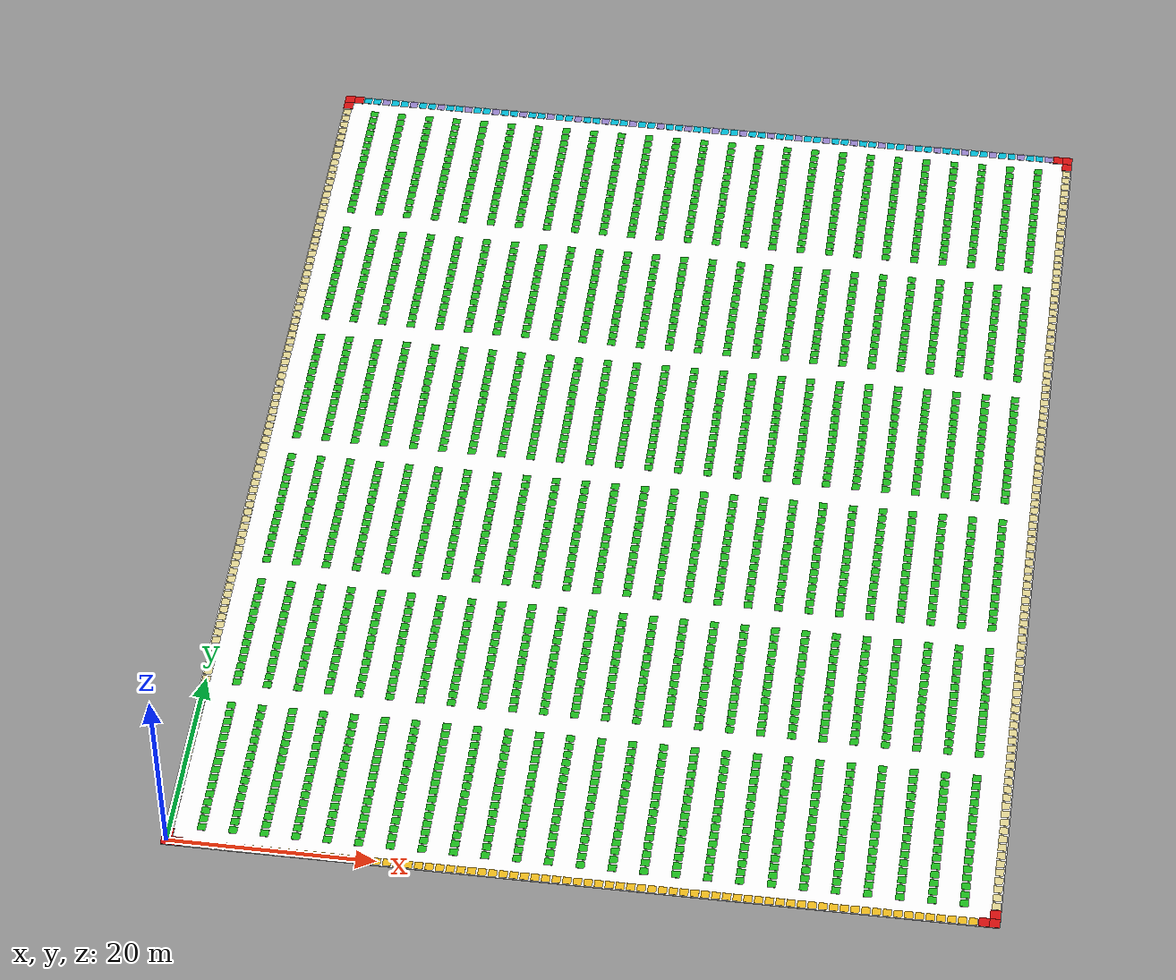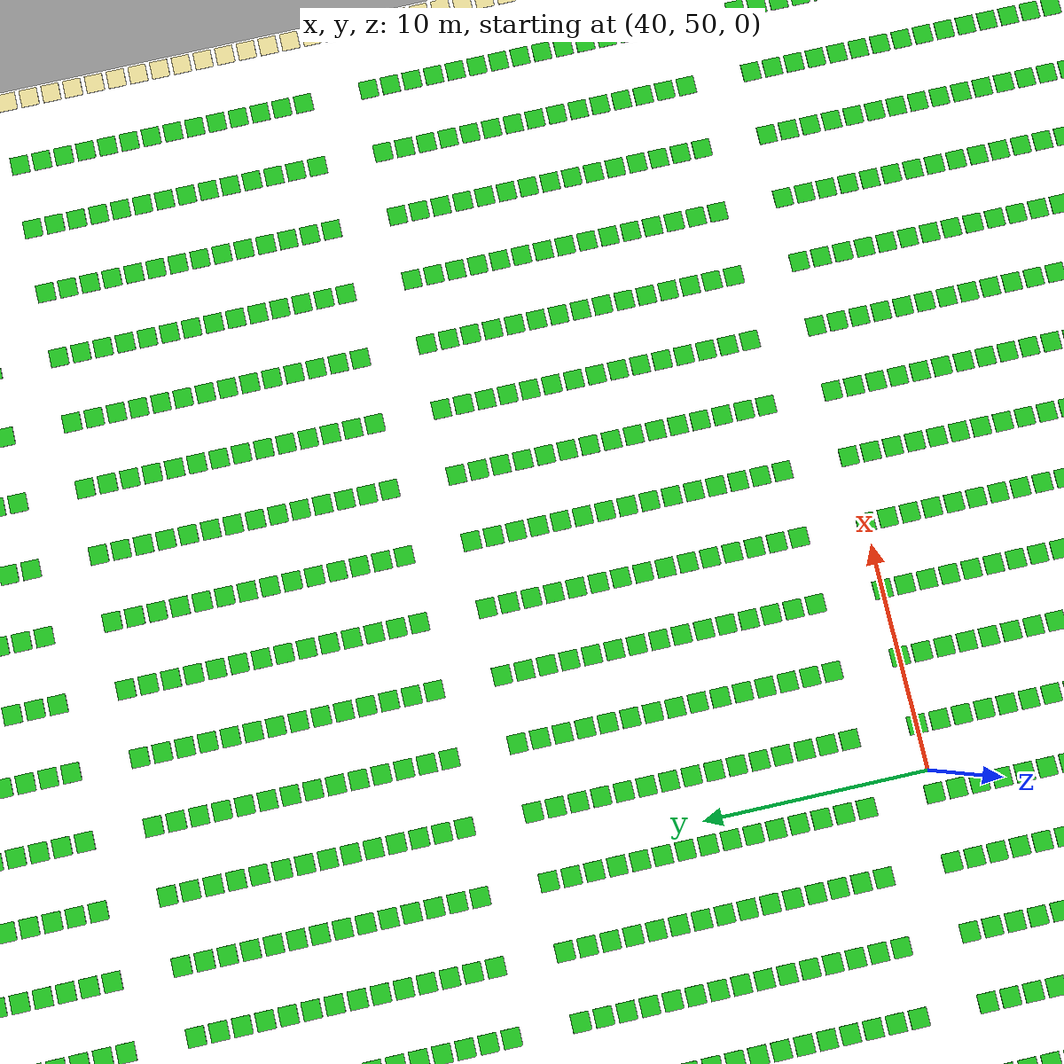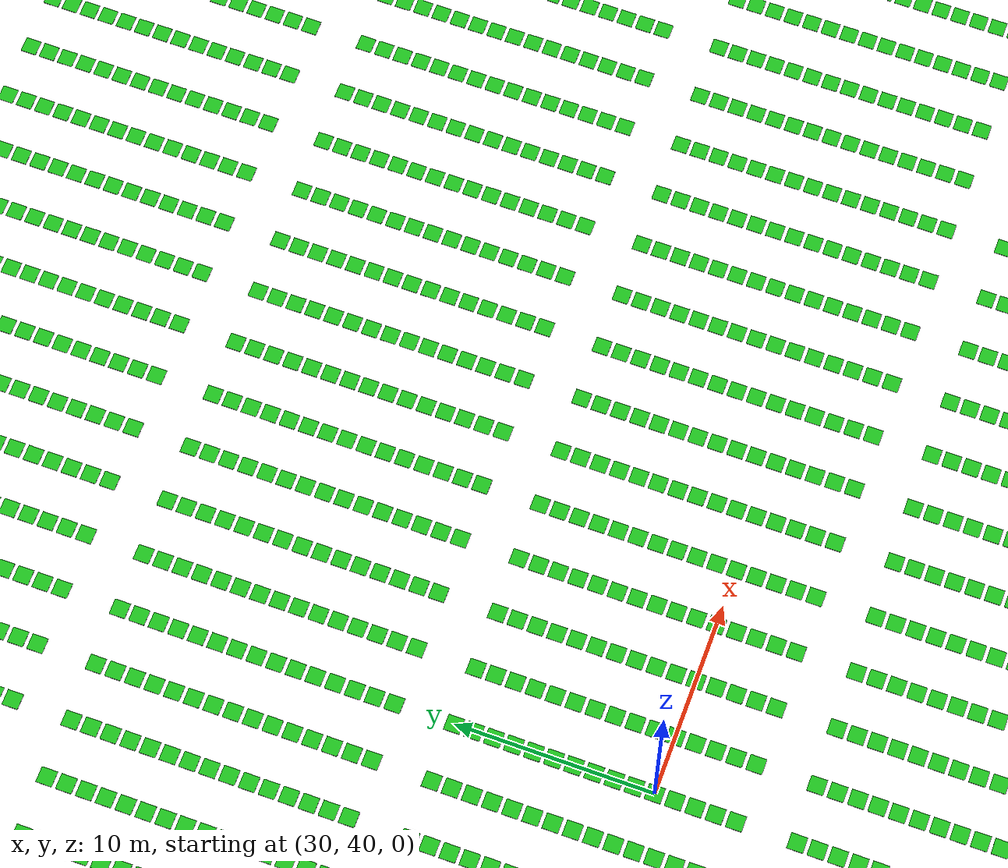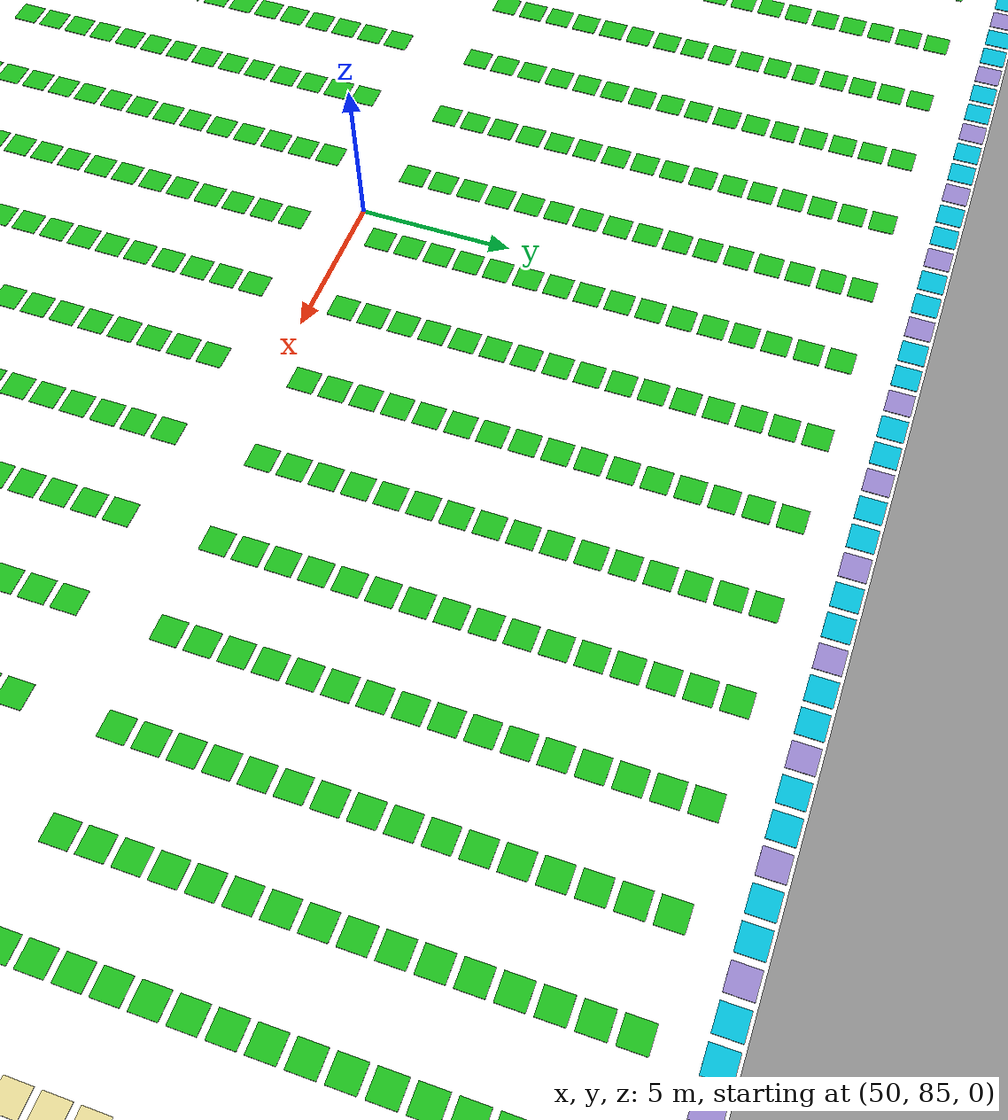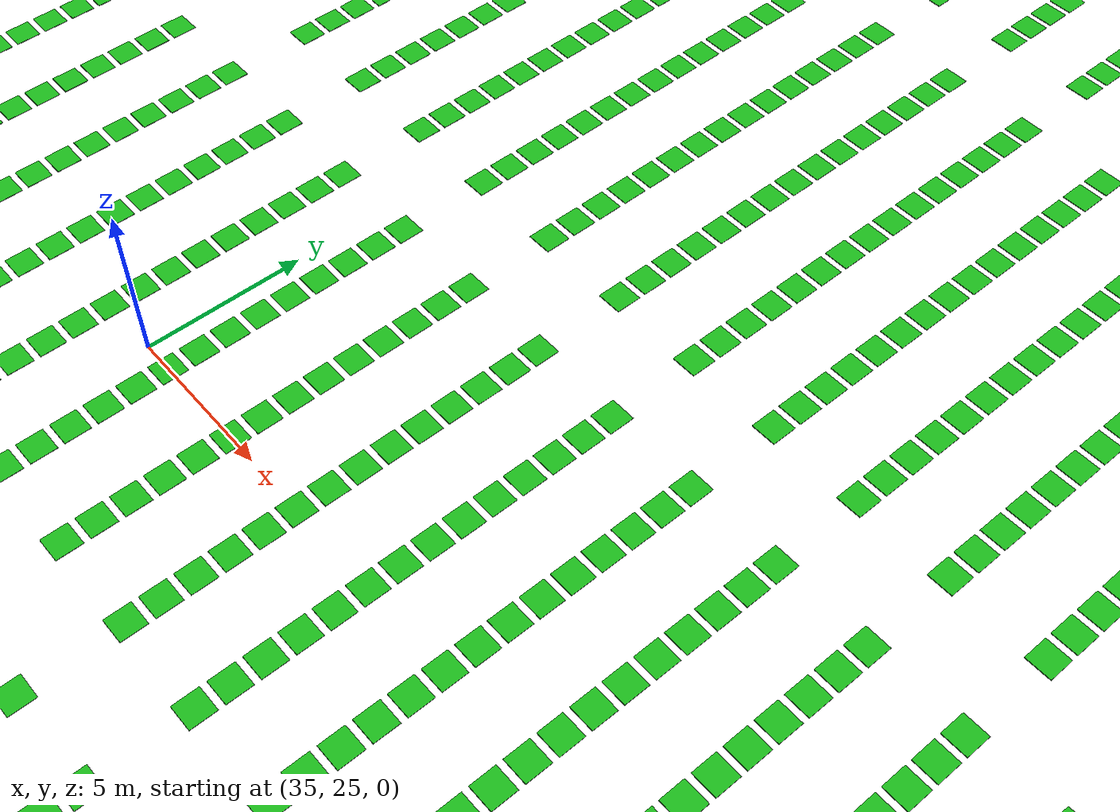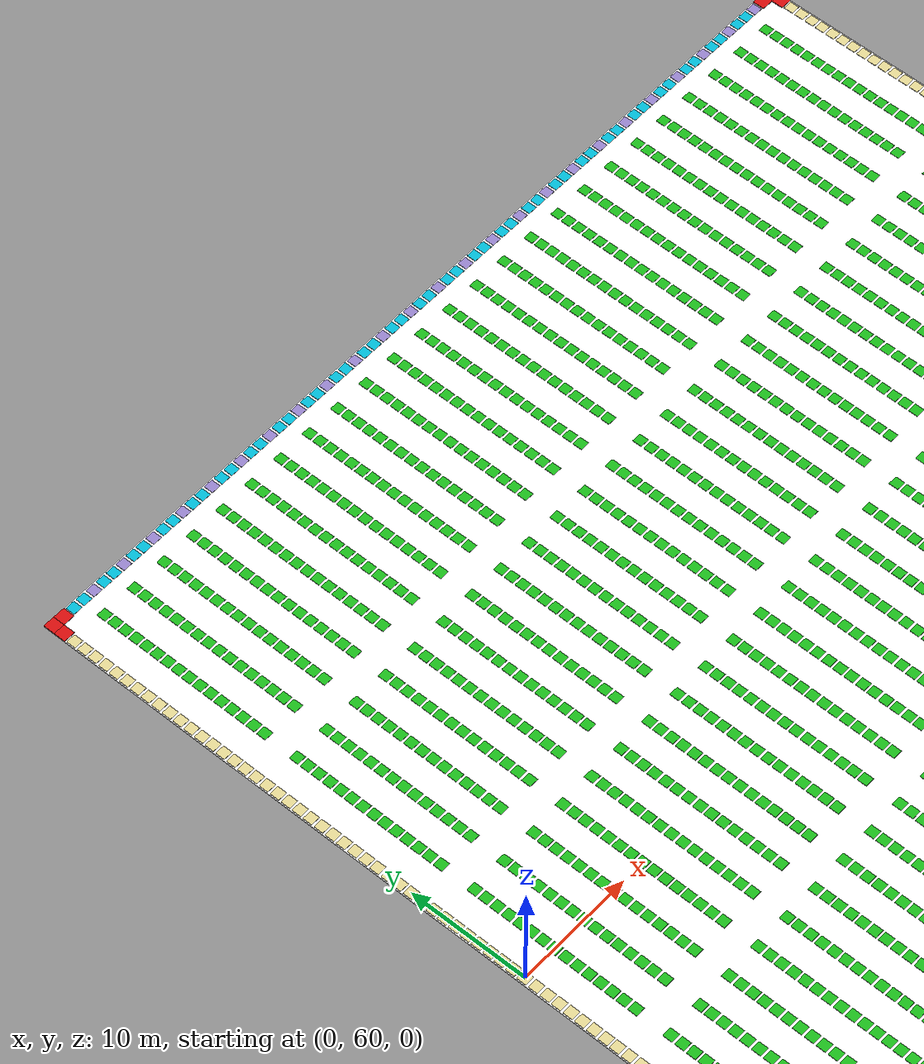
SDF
<?xml version="1.0"?>
<sdf version="1.10">
  <world name="my_map">

    <plugin
      filename="gz-sim-physics-system"
      name="gz::sim::systems::Physics">
    </plugin>

    <plugin
      filename="gz-sim-user-commands-system"
      name="gz::sim::systems::UserCommands">
    </plugin>

    <plugin
      filename="gz-sim-scene-broadcaster-system"
      name="gz::sim::systems::SceneBroadcaster">
    </plugin>

    <scene>
      <ambient>0.8 0.8 0.8 1</ambient>
      <background>0.6 0.6 0.6 1</background>
      <shadows>false</shadows>
    </scene>

    <light type="directional" name="sun">
      <pose>0 0 20 0 0 0</pose>
      <direction>0 0 -1</direction>
      <diffuse>1 1 1 1</diffuse>
      <specular>0.2 0.2 0.2 1</specular>
      <cast_shadows>false</cast_shadows>
    </light>

    <model name="warehouse_floor">
      <static>true</static>

      <pose>
        39.0
        51.5
        0.0
        0 0 0
      </pose>

      <link name="floor_link">

        <visual name="floor_visual">
          <geometry>
            <box>
              <size>
                79.0
                104.0
                0.02
              </size>
            </box>
          </geometry>

          <material>
            <ambient>0.95 0.95 0.95 1</ambient>
            <diffuse>0.95 0.95 0.95 1</diffuse>
          </material>
        </visual>

      </link>
    </model>

    <model name="blocked_0000">
      <static>true</static>

      <pose>
        0.0
        0.0
        0.045
        0 0 0
      </pose>

      <link name="link">

        <visual name="visual">
          <geometry>
            <box>
              <size>
                1.0
                1.0
                0.05
              </size>
            </box>
          </geometry>

          <material>
            <ambient>0.8 0.05 0.05 1</ambient>
            <diffuse>0.8 0.05 0.05 1</diffuse>
          </material>
        </visual>

      </link>
    </model>

    <model name="blocked_0001">
      <static>true</static>

      <pose>
        0.0
        1.0
        0.045
        0 0 0
      </pose>

      <link name="link">

        <visual name="visual">
          <geometry>
            <box>
              <size>
                1.0
                1.0
                0.05
              </size>
            </box>
          </geometry>

          <material>
            <ambient>0.8 0.05 0.05 1</ambient>
            <diffuse>0.8 0.05 0.05 1</diffuse>
          </material>
        </visual>

      </link>
    </model>

    <model name="blocked_0002">
      <static>true</static>

      <pose>
        0.0
        102.0
        0.045
        0 0 0
      </pose>

      <link name="link">

        <visual name="visual">
          <geometry>
            <box>
              <size>
                1.0
                1.0
                0.05
              </size>
            </box>
          </geometry>

          <material>
            <ambient>0.8 0.05 0.05 1</ambient>
            <diffuse>0.8 0.05 0.05 1</diffuse>
          </material>
        </visual>

      </link>
    </model>

    <model name="blocked_0003">
      <static>true</static>

      <pose>
        0.0
        103.0
        0.045
        0 0 0
      </pose>

      <link name="link">

        <visual name="visual">
          <geometry>
            <box>
              <size>
                1.0
                1.0
                0.05
              </size>
            </box>
          </geometry>

          <material>
            <ambient>0.8 0.05 0.05 1</ambient>
            <diffuse>0.8 0.05 0.05 1</diffuse>
          </material>
        </visual>

      </link>
    </model>

    <model name="blocked_0004">
      <static>true</static>

      <pose>
        1.0
        0.0
        0.045
        0 0 0
      </pose>

      <link name="link">

        <visual name="visual">
          <geometry>
            <box>
              <size>
                1.0
                1.0
                0.05
              </size>
            </box>
          </geometry>

          <material>
            <ambient>0.8 0.05 0.05 1</ambient>
            <diffuse>0.8 0.05 0.05 1</diffuse>
          </material>
        </visual>

      </link>
    </model>

    <model name="blocked_0005">
      <static>true</static>

      <pose>
        1.0
        103.0
        0.045
        0 0 0
      </pose>

      <link name="link">

        <visual name="visual">
          <geometry>
            <box>
              <size>
                1.0
                1.0
                0.05
              </size>
            </box>
          </geometry>

          <material>
            <ambient>0.8 0.05 0.05 1</ambient>
            <diffuse>0.8 0.05 0.05 1</diffuse>
          </material>
        </visual>

      </link>
    </model>

    <model name="blocked_0006">
      <static>true</static>

      <pose>
        77.0
        0.0
        0.045
        0 0 0
      </pose>

      <link name="link">

        <visual name="visual">
          <geometry>
            <box>
              <size>
                1.0
                1.0
                0.05
              </size>
            </box>
          </geometry>

          <material>
            <ambient>0.8 0.05 0.05 1</ambient>
            <diffuse>0.8 0.05 0.05 1</diffuse>
          </material>
        </visual>

      </link>
    </model>

    <model name="blocked_0007">
      <static>true</static>

      <pose>
        77.0
        103.0
        0.045
        0 0 0
      </pose>

      <link name="link">

        <visual name="visual">
          <geometry>
            <box>
              <size>
                1.0
                1.0
                0.05
              </size>
            </box>
          </geometry>

          <material>
            <ambient>0.8 0.05 0.05 1</ambient>
            <diffuse>0.8 0.05 0.05 1</diffuse>
          </material>
        </visual>

      </link>
    </model>

    <model name="blocked_0008">
      <static>true</static>

      <pose>
        78.0
        0.0
        0.045
        0 0 0
      </pose>

      <link name="link">

        <visual name="visual">
          <geometry>
            <box>
              <size>
                1.0
                1.0
                0.05
              </size>
            </box>
          </geometry>

          <material>
            <ambient>0.8 0.05 0.05 1</ambient>
            <diffuse>0.8 0.05 0.05 1</diffuse>
          </material>
        </visual>

      </link>
    </model>

    <model name="blocked_0009">
      <static>true</static>

      <pose>
        78.0
        1.0
        0.045
        0 0 0
      </pose>

      <link name="link">

        <visual name="visual">
          <geometry>
            <box>
              <size>
                1.0
                1.0
                0.05
              </size>
            </box>
          </geometry>

          <material>
            <ambient>0.8 0.05 0.05 1</ambient>
            <diffuse>0.8 0.05 0.05 1</diffuse>
          </material>
        </visual>

      </link>
    </model>

    <model name="blocked_0010">
      <static>true</static>

      <pose>
        78.0
        102.0
        0.045
        0 0 0
      </pose>

      <link name="link">

        <visual name="visual">
          <geometry>
            <box>
              <size>
                1.0
                1.0
                0.05
              </size>
            </box>
          </geometry>

          <material>
            <ambient>0.8 0.05 0.05 1</ambient>
            <diffuse>0.8 0.05 0.05 1</diffuse>
          </material>
        </visual>

      </link>
    </model>

    <model name="blocked_0011">
      <static>true</static>

      <pose>
        78.0
        103.0
        0.045
        0 0 0
      </pose>

      <link name="link">

        <visual name="visual">
          <geometry>
            <box>
              <size>
                1.0
                1.0
                0.05
              </size>
            </box>
          </geometry>

          <material>
            <ambient>0.8 0.05 0.05 1</ambient>
            <diffuse>0.8 0.05 0.05 1</diffuse>
          </material>
        </visual>

      </link>
    </model>

    <model name="charging_001">
      <static>true</static>

      <pose>
        2.0
        103.0
        0.02
        0 0 0
      </pose>

      <link name="link">

        <visual name="visual">
          <geometry>
            <box>
              <size>
                0.8
                0.8
                0.02
              </size>
            </box>
          </geometry>

          <material>
            <ambient>0.00 0.70 0.80 1</ambient>
            <diffuse>0.00 0.70 0.80 1</diffuse>
          </material>
        </visual>

      </link>
    </model>

    <model name="charging_002">
      <static>true</static>

      <pose>
        3.0
        103.0
        0.02
        0 0 0
      </pose>

      <link name="link">

        <visual name="visual">
          <geometry>
            <box>
              <size>
                0.8
                0.8
                0.02
              </size>
            </box>
          </geometry>

          <material>
            <ambient>0.00 0.70 0.80 1</ambient>
            <diffuse>0.00 0.70 0.80 1</diffuse>
          </material>
        </visual>

      </link>
    </model>

    <model name="charge_queue_001">
      <static>true</static>

      <pose>
        4.0
        103.0
        0.02
        0 0 0
      </pose>

      <link name="link">

        <visual name="visual">
          <geometry>
            <box>
              <size>
                0.8
                0.8
                0.02
              </size>
            </box>
          </geometry>

          <material>
            <ambient>0.56 0.49 0.76 1</ambient>
            <diffuse>0.56 0.49 0.76 1</diffuse>
          </material>
        </visual>

      </link>
    </model>

    <model name="charging_003">
      <static>true</static>

      <pose>
        5.0
        103.0
        0.02
        0 0 0
      </pose>

      <link name="link">

        <visual name="visual">
          <geometry>
            <box>
              <size>
                0.8
                0.8
                0.02
              </size>
            </box>
          </geometry>

          <material>
            <ambient>0.00 0.70 0.80 1</ambient>
            <diffuse>0.00 0.70 0.80 1</diffuse>
          </material>
        </visual>

      </link>
    </model>

    <model name="charging_004">
      <static>true</static>

      <pose>
        6.0
        103.0
        0.02
        0 0 0
      </pose>

      <link name="link">

        <visual name="visual">
          <geometry>
            <box>
              <size>
                0.8
                0.8
                0.02
              </size>
            </box>
          </geometry>

          <material>
            <ambient>0.00 0.70 0.80 1</ambient>
            <diffuse>0.00 0.70 0.80 1</diffuse>
          </material>
        </visual>

      </link>
    </model>

    <model name="charge_queue_002">
      <static>true</static>

      <pose>
        7.0
        103.0
        0.02
        0 0 0
      </pose>

      <link name="link">

        <visual name="visual">
          <geometry>
            <box>
              <size>
                0.8
                0.8
                0.02
              </size>
            </box>
          </geometry>

          <material>
            <ambient>0.56 0.49 0.76 1</ambient>
            <diffuse>0.56 0.49 0.76 1</diffuse>
          </material>
        </visual>

      </link>
    </model>

    <model name="charging_005">
      <static>true</static>

      <pose>
        8.0
        103.0
        0.02
        0 0 0
      </pose>

      <link name="link">

        <visual name="visual">
          <geometry>
            <box>
              <size>
                0.8
                0.8
                0.02
              </size>
            </box>
          </geometry>

          <material>
            <ambient>0.00 0.70 0.80 1</ambient>
            <diffuse>0.00 0.70 0.80 1</diffuse>
          </material>
        </visual>

      </link>
    </model>

    <model name="charging_006">
      <static>true</static>

      <pose>
        9.0
        103.0
        0.02
        0 0 0
      </pose>

      <link name="link">

        <visual name="visual">
          <geometry>
            <box>
              <size>
                0.8
                0.8
                0.02
              </size>
            </box>
          </geometry>

          <material>
            <ambient>0.00 0.70 0.80 1</ambient>
            <diffuse>0.00 0.70 0.80 1</diffuse>
          </material>
        </visual>

      </link>
    </model>

    <model name="charge_queue_003">
      <static>true</static>

      <pose>
        10.0
        103.0
        0.02
        0 0 0
      </pose>

      <link name="link">

        <visual name="visual">
          <geometry>
            <box>
              <size>
                0.8
                0.8
                0.02
              </size>
            </box>
          </geometry>

          <material>
            <ambient>0.56 0.49 0.76 1</ambient>
            <diffuse>0.56 0.49 0.76 1</diffuse>
          </material>
        </visual>

      </link>
    </model>

    <model name="charging_007">
      <static>true</static>

      <pose>
        11.0
        103.0
        0.02
        0 0 0
      </pose>

      <link name="link">

        <visual name="visual">
          <geometry>
            <box>
              <size>
                0.8
                0.8
                0.02
              </size>
            </box>
          </geometry>

          <material>
            <ambient>0.00 0.70 0.80 1</ambient>
            <diffuse>0.00 0.70 0.80 1</diffuse>
          </material>
        </visual>

      </link>
    </model>

    <model name="charging_008">
      <static>true</static>

      <pose>
        12.0
        103.0
        0.02
        0 0 0
      </pose>

      <link name="link">

        <visual name="visual">
          <geometry>
            <box>
              <size>
                0.8
                0.8
                0.02
              </size>
            </box>
          </geometry>

          <material>
            <ambient>0.00 0.70 0.80 1</ambient>
            <diffuse>0.00 0.70 0.80 1</diffuse>
          </material>
        </visual>

      </link>
    </model>

    <model name="charge_queue_004">
      <static>true</static>

      <pose>
        13.0
        103.0
        0.02
        0 0 0
      </pose>

      <link name="link">

        <visual name="visual">
          <geometry>
            <box>
              <size>
                0.8
                0.8
                0.02
              </size>
            </box>
          </geometry>

          <material>
            <ambient>0.56 0.49 0.76 1</ambient>
            <diffuse>0.56 0.49 0.76 1</diffuse>
          </material>
        </visual>

      </link>
    </model>

    <model name="charging_009">
      <static>true</static>

      <pose>
        14.0
        103.0
        0.02
        0 0 0
      </pose>

      <link name="link">

        <visual name="visual">
          <geometry>
            <box>
              <size>
                0.8
                0.8
                0.02
              </size>
            </box>
          </geometry>

          <material>
            <ambient>0.00 0.70 0.80 1</ambient>
            <diffuse>0.00 0.70 0.80 1</diffuse>
          </material>
        </visual>

      </link>
    </model>

    <model name="charging_010">
      <static>true</static>

      <pose>
        15.0
        103.0
        0.02
        0 0 0
      </pose>

      <link name="link">

        <visual name="visual">
          <geometry>
            <box>
              <size>
                0.8
                0.8
                0.02
              </size>
            </box>
          </geometry>

          <material>
            <ambient>0.00 0.70 0.80 1</ambient>
            <diffuse>0.00 0.70 0.80 1</diffuse>
          </material>
        </visual>

      </link>
    </model>

    <model name="charge_queue_005">
      <static>true</static>

      <pose>
        16.0
        103.0
        0.02
        0 0 0
      </pose>

      <link name="link">

        <visual name="visual">
          <geometry>
            <box>
              <size>
                0.8
                0.8
                0.02
              </size>
            </box>
          </geometry>

          <material>
            <ambient>0.56 0.49 0.76 1</ambient>
            <diffuse>0.56 0.49 0.76 1</diffuse>
          </material>
        </visual>

      </link>
    </model>

    <model name="charging_011">
      <static>true</static>

      <pose>
        17.0
        103.0
        0.02
        0 0 0
      </pose>

      <link name="link">

        <visual name="visual">
          <geometry>
            <box>
              <size>
                0.8
                0.8
                0.02
              </size>
            </box>
          </geometry>

          <material>
            <ambient>0.00 0.70 0.80 1</ambient>
            <diffuse>0.00 0.70 0.80 1</diffuse>
          </material>
        </visual>

      </link>
    </model>

    <model name="charging_012">
      <static>true</static>

      <pose>
        18.0
        103.0
        0.02
        0 0 0
      </pose>

      <link name="link">

        <visual name="visual">
          <geometry>
            <box>
              <size>
                0.8
                0.8
                0.02
              </size>
            </box>
          </geometry>

          <material>
            <ambient>0.00 0.70 0.80 1</ambient>
            <diffuse>0.00 0.70 0.80 1</diffuse>
          </material>
        </visual>

      </link>
    </model>

    <model name="charge_queue_006">
      <static>true</static>

      <pose>
        19.0
        103.0
        0.02
        0 0 0
      </pose>

      <link name="link">

        <visual name="visual">
          <geometry>
            <box>
              <size>
                0.8
                0.8
                0.02
              </size>
            </box>
          </geometry>

          <material>
            <ambient>0.56 0.49 0.76 1</ambient>
            <diffuse>0.56 0.49 0.76 1</diffuse>
          </material>
        </visual>

      </link>
    </model>

    <model name="charging_013">
      <static>true</static>

      <pose>
        20.0
        103.0
        0.02
        0 0 0
      </pose>

      <link name="link">

        <visual name="visual">
          <geometry>
            <box>
              <size>
                0.8
                0.8
                0.02
              </size>
            </box>
          </geometry>

          <material>
            <ambient>0.00 0.70 0.80 1</ambient>
            <diffuse>0.00 0.70 0.80 1</diffuse>
          </material>
        </visual>

      </link>
    </model>

    <model name="charging_014">
      <static>true</static>

      <pose>
        21.0
        103.0
        0.02
        0 0 0
      </pose>

      <link name="link">

        <visual name="visual">
          <geometry>
            <box>
              <size>
                0.8
                0.8
                0.02
              </size>
            </box>
          </geometry>

          <material>
            <ambient>0.00 0.70 0.80 1</ambient>
            <diffuse>0.00 0.70 0.80 1</diffuse>
          </material>
        </visual>

      </link>
    </model>

    <model name="charge_queue_007">
      <static>true</static>

      <pose>
        22.0
        103.0
        0.02
        0 0 0
      </pose>

      <link name="link">

        <visual name="visual">
          <geometry>
            <box>
              <size>
                0.8
                0.8
                0.02
              </size>
            </box>
          </geometry>

          <material>
            <ambient>0.56 0.49 0.76 1</ambient>
            <diffuse>0.56 0.49 0.76 1</diffuse>
          </material>
        </visual>

      </link>
    </model>

    <model name="charging_015">
      <static>true</static>

      <pose>
        23.0
        103.0
        0.02
        0 0 0
      </pose>

      <link name="link">

        <visual name="visual">
          <geometry>
            <box>
              <size>
                0.8
                0.8
                0.02
              </size>
            </box>
          </geometry>

          <material>
            <ambient>0.00 0.70 0.80 1</ambient>
            <diffuse>0.00 0.70 0.80 1</diffuse>
          </material>
        </visual>

      </link>
    </model>

    <model name="charging_016">
      <static>true</static>

      <pose>
        24.0
        103.0
        0.02
        0 0 0
      </pose>

      <link name="link">

        <visual name="visual">
          <geometry>
            <box>
              <size>
                0.8
                0.8
                0.02
              </size>
            </box>
          </geometry>

          <material>
            <ambient>0.00 0.70 0.80 1</ambient>
            <diffuse>0.00 0.70 0.80 1</diffuse>
          </material>
        </visual>

      </link>
    </model>

    <model name="charge_queue_008">
      <static>true</static>

      <pose>
        25.0
        103.0
        0.02
        0 0 0
      </pose>

      <link name="link">

        <visual name="visual">
          <geometry>
            <box>
              <size>
                0.8
                0.8
                0.02
              </size>
            </box>
          </geometry>

          <material>
            <ambient>0.56 0.49 0.76 1</ambient>
            <diffuse>0.56 0.49 0.76 1</diffuse>
          </material>
        </visual>

      </link>
    </model>

    <model name="charging_017">
      <static>true</static>

      <pose>
        26.0
        103.0
        0.02
        0 0 0
      </pose>

      <link name="link">

        <visual name="visual">
          <geometry>
            <box>
              <size>
                0.8
                0.8
                0.02
              </size>
            </box>
          </geometry>

          <material>
            <ambient>0.00 0.70 0.80 1</ambient>
            <diffuse>0.00 0.70 0.80 1</diffuse>
          </material>
        </visual>

      </link>
    </model>

    <model name="charging_018">
      <static>true</static>

      <pose>
        27.0
        103.0
        0.02
        0 0 0
      </pose>

      <link name="link">

        <visual name="visual">
          <geometry>
            <box>
              <size>
                0.8
                0.8
                0.02
              </size>
            </box>
          </geometry>

          <material>
            <ambient>0.00 0.70 0.80 1</ambient>
            <diffuse>0.00 0.70 0.80 1</diffuse>
          </material>
        </visual>

      </link>
    </model>

    <model name="charge_queue_009">
      <static>true</static>

      <pose>
        28.0
        103.0
        0.02
        0 0 0
      </pose>

      <link name="link">

        <visual name="visual">
          <geometry>
            <box>
              <size>
                0.8
                0.8
                0.02
              </size>
            </box>
          </geometry>

          <material>
            <ambient>0.56 0.49 0.76 1</ambient>
            <diffuse>0.56 0.49 0.76 1</diffuse>
          </material>
        </visual>

      </link>
    </model>

    <model name="charging_019">
      <static>true</static>

      <pose>
        29.0
        103.0
        0.02
        0 0 0
      </pose>

      <link name="link">

        <visual name="visual">
          <geometry>
            <box>
              <size>
                0.8
                0.8
                0.02
              </size>
            </box>
          </geometry>

          <material>
            <ambient>0.00 0.70 0.80 1</ambient>
            <diffuse>0.00 0.70 0.80 1</diffuse>
          </material>
        </visual>

      </link>
    </model>

    <model name="charging_020">
      <static>true</static>

      <pose>
        30.0
        103.0
        0.02
        0 0 0
      </pose>

      <link name="link">

        <visual name="visual">
          <geometry>
            <box>
              <size>
                0.8
                0.8
                0.02
              </size>
            </box>
          </geometry>

          <material>
            <ambient>0.00 0.70 0.80 1</ambient>
            <diffuse>0.00 0.70 0.80 1</diffuse>
          </material>
        </visual>

      </link>
    </model>

    <model name="charge_queue_010">
      <static>true</static>

      <pose>
        31.0
        103.0
        0.02
        0 0 0
      </pose>

      <link name="link">

        <visual name="visual">
          <geometry>
            <box>
              <size>
                0.8
                0.8
                0.02
              </size>
            </box>
          </geometry>

          <material>
            <ambient>0.56 0.49 0.76 1</ambient>
            <diffuse>0.56 0.49 0.76 1</diffuse>
          </material>
        </visual>

      </link>
    </model>

    <model name="charging_021">
      <static>true</static>

      <pose>
        32.0
        103.0
        0.02
        0 0 0
      </pose>

      <link name="link">

        <visual name="visual">
          <geometry>
            <box>
              <size>
                0.8
                0.8
                0.02
              </size>
            </box>
          </geometry>

          <material>
            <ambient>0.00 0.70 0.80 1</ambient>
            <diffuse>0.00 0.70 0.80 1</diffuse>
          </material>
        </visual>

      </link>
    </model>

    <model name="charging_022">
      <static>true</static>

      <pose>
        33.0
        103.0
        0.02
        0 0 0
      </pose>

      <link name="link">

        <visual name="visual">
          <geometry>
            <box>
              <size>
                0.8
                0.8
                0.02
              </size>
            </box>
          </geometry>

          <material>
            <ambient>0.00 0.70 0.80 1</ambient>
            <diffuse>0.00 0.70 0.80 1</diffuse>
          </material>
        </visual>

      </link>
    </model>

    <model name="charge_queue_011">
      <static>true</static>

      <pose>
        34.0
        103.0
        0.02
        0 0 0
      </pose>

      <link name="link">

        <visual name="visual">
          <geometry>
            <box>
              <size>
                0.8
                0.8
                0.02
              </size>
            </box>
          </geometry>

          <material>
            <ambient>0.56 0.49 0.76 1</ambient>
            <diffuse>0.56 0.49 0.76 1</diffuse>
          </material>
        </visual>

      </link>
    </model>

    <model name="charging_023">
      <static>true</static>

      <pose>
        35.0
        103.0
        0.02
        0 0 0
      </pose>

      <link name="link">

        <visual name="visual">
          <geometry>
            <box>
              <size>
                0.8
                0.8
                0.02
              </size>
            </box>
          </geometry>

          <material>
            <ambient>0.00 0.70 0.80 1</ambient>
            <diffuse>0.00 0.70 0.80 1</diffuse>
          </material>
        </visual>

      </link>
    </model>

    <model name="charging_024">
      <static>true</static>

      <pose>
        36.0
        103.0
        0.02
        0 0 0
      </pose>

      <link name="link">

        <visual name="visual">
          <geometry>
            <box>
              <size>
                0.8
                0.8
                0.02
              </size>
            </box>
          </geometry>

          <material>
            <ambient>0.00 0.70 0.80 1</ambient>
            <diffuse>0.00 0.70 0.80 1</diffuse>
          </material>
        </visual>

      </link>
    </model>

    <model name="charge_queue_012">
      <static>true</static>

      <pose>
        37.0
        103.0
        0.02
        0 0 0
      </pose>

      <link name="link">

        <visual name="visual">
          <geometry>
            <box>
              <size>
                0.8
                0.8
                0.02
              </size>
            </box>
          </geometry>

          <material>
            <ambient>0.56 0.49 0.76 1</ambient>
            <diffuse>0.56 0.49 0.76 1</diffuse>
          </material>
        </visual>

      </link>
    </model>

    <model name="charging_025">
      <static>true</static>

      <pose>
        38.0
        103.0
        0.02
        0 0 0
      </pose>

      <link name="link">

        <visual name="visual">
          <geometry>
            <box>
              <size>
                0.8
                0.8
                0.02
              </size>
            </box>
          </geometry>

          <material>
            <ambient>0.00 0.70 0.80 1</ambient>
            <diffuse>0.00 0.70 0.80 1</diffuse>
          </material>
        </visual>

      </link>
    </model>

    <model name="charging_026">
      <static>true</static>

      <pose>
        39.0
        103.0
        0.02
        0 0 0
      </pose>

      <link name="link">

        <visual name="visual">
          <geometry>
            <box>
              <size>
                0.8
                0.8
                0.02
              </size>
            </box>
          </geometry>

          <material>
            <ambient>0.00 0.70 0.80 1</ambient>
            <diffuse>0.00 0.70 0.80 1</diffuse>
          </material>
        </visual>

      </link>
    </model>

    <model name="charge_queue_013">
      <static>true</static>

      <pose>
        40.0
        103.0
        0.02
        0 0 0
      </pose>

      <link name="link">

        <visual name="visual">
          <geometry>
            <box>
              <size>
                0.8
                0.8
                0.02
              </size>
            </box>
          </geometry>

          <material>
            <ambient>0.56 0.49 0.76 1</ambient>
            <diffuse>0.56 0.49 0.76 1</diffuse>
          </material>
        </visual>

      </link>
    </model>

    <model name="charging_027">
      <static>true</static>

      <pose>
        41.0
        103.0
        0.02
        0 0 0
      </pose>

      <link name="link">

        <visual name="visual">
          <geometry>
            <box>
              <size>
                0.8
                0.8
                0.02
              </size>
            </box>
          </geometry>

          <material>
            <ambient>0.00 0.70 0.80 1</ambient>
            <diffuse>0.00 0.70 0.80 1</diffuse>
          </material>
        </visual>

      </link>
    </model>

    <model name="charging_028">
      <static>true</static>

      <pose>
        42.0
        103.0
        0.02
        0 0 0
      </pose>

      <link name="link">

        <visual name="visual">
          <geometry>
            <box>
              <size>
                0.8
                0.8
                0.02
              </size>
            </box>
          </geometry>

          <material>
            <ambient>0.00 0.70 0.80 1</ambient>
            <diffuse>0.00 0.70 0.80 1</diffuse>
          </material>
        </visual>

      </link>
    </model>

    <model name="charge_queue_014">
      <static>true</static>

      <pose>
        43.0
        103.0
        0.02
        0 0 0
      </pose>

      <link name="link">

        <visual name="visual">
          <geometry>
            <box>
              <size>
                0.8
                0.8
                0.02
              </size>
            </box>
          </geometry>

          <material>
            <ambient>0.56 0.49 0.76 1</ambient>
            <diffuse>0.56 0.49 0.76 1</diffuse>
          </material>
        </visual>

      </link>
    </model>

    <model name="charging_029">
      <static>true</static>

      <pose>
        44.0
        103.0
        0.02
        0 0 0
      </pose>

      <link name="link">

        <visual name="visual">
          <geometry>
            <box>
              <size>
                0.8
                0.8
                0.02
              </size>
            </box>
          </geometry>

          <material>
            <ambient>0.00 0.70 0.80 1</ambient>
            <diffuse>0.00 0.70 0.80 1</diffuse>
          </material>
        </visual>

      </link>
    </model>

    <model name="charging_030">
      <static>true</static>

      <pose>
        45.0
        103.0
        0.02
        0 0 0
      </pose>

      <link name="link">

        <visual name="visual">
          <geometry>
            <box>
              <size>
                0.8
                0.8
                0.02
              </size>
            </box>
          </geometry>

          <material>
            <ambient>0.00 0.70 0.80 1</ambient>
            <diffuse>0.00 0.70 0.80 1</diffuse>
          </material>
        </visual>

      </link>
    </model>

    <model name="charge_queue_015">
      <static>true</static>

      <pose>
        46.0
        103.0
        0.02
        0 0 0
      </pose>

      <link name="link">

        <visual name="visual">
          <geometry>
            <box>
              <size>
                0.8
                0.8
                0.02
              </size>
            </box>
          </geometry>

          <material>
            <ambient>0.56 0.49 0.76 1</ambient>
            <diffuse>0.56 0.49 0.76 1</diffuse>
          </material>
        </visual>

      </link>
    </model>

    <model name="charging_031">
      <static>true</static>

      <pose>
        47.0
        103.0
        0.02
        0 0 0
      </pose>

      <link name="link">

        <visual name="visual">
          <geometry>
            <box>
              <size>
                0.8
                0.8
                0.02
              </size>
            </box>
          </geometry>

          <material>
            <ambient>0.00 0.70 0.80 1</ambient>
            <diffuse>0.00 0.70 0.80 1</diffuse>
          </material>
        </visual>

      </link>
    </model>

    <model name="charging_032">
      <static>true</static>

      <pose>
        48.0
        103.0
        0.02
        0 0 0
      </pose>

      <link name="link">

        <visual name="visual">
          <geometry>
            <box>
              <size>
                0.8
                0.8
                0.02
              </size>
            </box>
          </geometry>

          <material>
            <ambient>0.00 0.70 0.80 1</ambient>
            <diffuse>0.00 0.70 0.80 1</diffuse>
          </material>
        </visual>

      </link>
    </model>

    <model name="charge_queue_016">
      <static>true</static>

      <pose>
        49.0
        103.0
        0.02
        0 0 0
      </pose>

      <link name="link">

        <visual name="visual">
          <geometry>
            <box>
              <size>
                0.8
                0.8
                0.02
              </size>
            </box>
          </geometry>

          <material>
            <ambient>0.56 0.49 0.76 1</ambient>
            <diffuse>0.56 0.49 0.76 1</diffuse>
          </material>
        </visual>

      </link>
    </model>

    <model name="charging_033">
      <static>true</static>

      <pose>
        50.0
        103.0
        0.02
        0 0 0
      </pose>

      <link name="link">

        <visual name="visual">
          <geometry>
            <box>
              <size>
                0.8
                0.8
                0.02
              </size>
            </box>
          </geometry>

          <material>
            <ambient>0.00 0.70 0.80 1</ambient>
            <diffuse>0.00 0.70 0.80 1</diffuse>
          </material>
        </visual>

      </link>
    </model>

    <model name="charging_034">
      <static>true</static>

      <pose>
        51.0
        103.0
        0.02
        0 0 0
      </pose>

      <link name="link">

        <visual name="visual">
          <geometry>
            <box>
              <size>
                0.8
                0.8
                0.02
              </size>
            </box>
          </geometry>

          <material>
            <ambient>0.00 0.70 0.80 1</ambient>
            <diffuse>0.00 0.70 0.80 1</diffuse>
          </material>
        </visual>

      </link>
    </model>

    <model name="charge_queue_017">
      <static>true</static>

      <pose>
        52.0
        103.0
        0.02
        0 0 0
      </pose>

      <link name="link">

        <visual name="visual">
          <geometry>
            <box>
              <size>
                0.8
                0.8
                0.02
              </size>
            </box>
          </geometry>

          <material>
            <ambient>0.56 0.49 0.76 1</ambient>
            <diffuse>0.56 0.49 0.76 1</diffuse>
          </material>
        </visual>

      </link>
    </model>

    <model name="charging_035">
      <static>true</static>

      <pose>
        53.0
        103.0
        0.02
        0 0 0
      </pose>

      <link name="link">

        <visual name="visual">
          <geometry>
            <box>
              <size>
                0.8
                0.8
                0.02
              </size>
            </box>
          </geometry>

          <material>
            <ambient>0.00 0.70 0.80 1</ambient>
            <diffuse>0.00 0.70 0.80 1</diffuse>
          </material>
        </visual>

      </link>
    </model>

    <model name="charging_036">
      <static>true</static>

      <pose>
        54.0
        103.0
        0.02
        0 0 0
      </pose>

      <link name="link">

        <visual name="visual">
          <geometry>
            <box>
              <size>
                0.8
                0.8
                0.02
              </size>
            </box>
          </geometry>

          <material>
            <ambient>0.00 0.70 0.80 1</ambient>
            <diffuse>0.00 0.70 0.80 1</diffuse>
          </material>
        </visual>

      </link>
    </model>

    <model name="charge_queue_018">
      <static>true</static>

      <pose>
        55.0
        103.0
        0.02
        0 0 0
      </pose>

      <link name="link">

        <visual name="visual">
          <geometry>
            <box>
              <size>
                0.8
                0.8
                0.02
              </size>
            </box>
          </geometry>

          <material>
            <ambient>0.56 0.49 0.76 1</ambient>
            <diffuse>0.56 0.49 0.76 1</diffuse>
          </material>
        </visual>

      </link>
    </model>

    <model name="charging_037">
      <static>true</static>

      <pose>
        56.0
        103.0
        0.02
        0 0 0
      </pose>

      <link name="link">

        <visual name="visual">
          <geometry>
            <box>
              <size>
                0.8
                0.8
                0.02
              </size>
            </box>
          </geometry>

          <material>
            <ambient>0.00 0.70 0.80 1</ambient>
            <diffuse>0.00 0.70 0.80 1</diffuse>
          </material>
        </visual>

      </link>
    </model>

    <model name="charging_038">
      <static>true</static>

      <pose>
        57.0
        103.0
        0.02
        0 0 0
      </pose>

      <link name="link">

        <visual name="visual">
          <geometry>
            <box>
              <size>
                0.8
                0.8
                0.02
              </size>
            </box>
          </geometry>

          <material>
            <ambient>0.00 0.70 0.80 1</ambient>
            <diffuse>0.00 0.70 0.80 1</diffuse>
          </material>
        </visual>

      </link>
    </model>

    <model name="charge_queue_019">
      <static>true</static>

      <pose>
        58.0
        103.0
        0.02
        0 0 0
      </pose>

      <link name="link">

        <visual name="visual">
          <geometry>
            <box>
              <size>
                0.8
                0.8
                0.02
              </size>
            </box>
          </geometry>

          <material>
            <ambient>0.56 0.49 0.76 1</ambient>
            <diffuse>0.56 0.49 0.76 1</diffuse>
          </material>
        </visual>

      </link>
    </model>

    <model name="charging_039">
      <static>true</static>

      <pose>
        59.0
        103.0
        0.02
        0 0 0
      </pose>

      <link name="link">

        <visual name="visual">
          <geometry>
            <box>
              <size>
                0.8
                0.8
                0.02
              </size>
            </box>
          </geometry>

          <material>
            <ambient>0.00 0.70 0.80 1</ambient>
            <diffuse>0.00 0.70 0.80 1</diffuse>
          </material>
        </visual>

      </link>
    </model>

    <model name="charging_040">
      <static>true</static>

      <pose>
        60.0
        103.0
        0.02
        0 0 0
      </pose>

      <link name="link">

        <visual name="visual">
          <geometry>
            <box>
              <size>
                0.8
                0.8
                0.02
              </size>
            </box>
          </geometry>

          <material>
            <ambient>0.00 0.70 0.80 1</ambient>
            <diffuse>0.00 0.70 0.80 1</diffuse>
          </material>
        </visual>

      </link>
    </model>

    <model name="charge_queue_020">
      <static>true</static>

      <pose>
        61.0
        103.0
        0.02
        0 0 0
      </pose>

      <link name="link">

        <visual name="visual">
          <geometry>
            <box>
              <size>
                0.8
                0.8
                0.02
              </size>
            </box>
          </geometry>

          <material>
            <ambient>0.56 0.49 0.76 1</ambient>
            <diffuse>0.56 0.49 0.76 1</diffuse>
          </material>
        </visual>

      </link>
    </model>

    <model name="charging_041">
      <static>true</static>

      <pose>
        62.0
        103.0
        0.02
        0 0 0
      </pose>

      <link name="link">

        <visual name="visual">
          <geometry>
            <box>
              <size>
                0.8
                0.8
                0.02
              </size>
            </box>
          </geometry>

          <material>
            <ambient>0.00 0.70 0.80 1</ambient>
            <diffuse>0.00 0.70 0.80 1</diffuse>
          </material>
        </visual>

      </link>
    </model>

    <model name="charging_042">
      <static>true</static>

      <pose>
        63.0
        103.0
        0.02
        0 0 0
      </pose>

      <link name="link">

        <visual name="visual">
          <geometry>
            <box>
              <size>
                0.8
                0.8
                0.02
              </size>
            </box>
          </geometry>

          <material>
            <ambient>0.00 0.70 0.80 1</ambient>
            <diffuse>0.00 0.70 0.80 1</diffuse>
          </material>
        </visual>

      </link>
    </model>

    <model name="charge_queue_021">
      <static>true</static>

      <pose>
        64.0
        103.0
        0.02
        0 0 0
      </pose>

      <link name="link">

        <visual name="visual">
          <geometry>
            <box>
              <size>
                0.8
                0.8
                0.02
              </size>
            </box>
          </geometry>

          <material>
            <ambient>0.56 0.49 0.76 1</ambient>
            <diffuse>0.56 0.49 0.76 1</diffuse>
          </material>
        </visual>

      </link>
    </model>

    <model name="charging_043">
      <static>true</static>

      <pose>
        65.0
        103.0
        0.02
        0 0 0
      </pose>

      <link name="link">

        <visual name="visual">
          <geometry>
            <box>
              <size>
                0.8
                0.8
                0.02
              </size>
            </box>
          </geometry>

          <material>
            <ambient>0.00 0.70 0.80 1</ambient>
            <diffuse>0.00 0.70 0.80 1</diffuse>
          </material>
        </visual>

      </link>
    </model>

    <model name="charging_044">
      <static>true</static>

      <pose>
        66.0
        103.0
        0.02
        0 0 0
      </pose>

      <link name="link">

        <visual name="visual">
          <geometry>
            <box>
              <size>
                0.8
                0.8
                0.02
              </size>
            </box>
          </geometry>

          <material>
            <ambient>0.00 0.70 0.80 1</ambient>
            <diffuse>0.00 0.70 0.80 1</diffuse>
          </material>
        </visual>

      </link>
    </model>

    <model name="charge_queue_022">
      <static>true</static>

      <pose>
        67.0
        103.0
        0.02
        0 0 0
      </pose>

      <link name="link">

        <visual name="visual">
          <geometry>
            <box>
              <size>
                0.8
                0.8
                0.02
              </size>
            </box>
          </geometry>

          <material>
            <ambient>0.56 0.49 0.76 1</ambient>
            <diffuse>0.56 0.49 0.76 1</diffuse>
          </material>
        </visual>

      </link>
    </model>

    <model name="charging_045">
      <static>true</static>

      <pose>
        68.0
        103.0
        0.02
        0 0 0
      </pose>

      <link name="link">

        <visual name="visual">
          <geometry>
            <box>
              <size>
                0.8
                0.8
                0.02
              </size>
            </box>
          </geometry>

          <material>
            <ambient>0.00 0.70 0.80 1</ambient>
            <diffuse>0.00 0.70 0.80 1</diffuse>
          </material>
        </visual>

      </link>
    </model>

    <model name="charging_046">
      <static>true</static>

      <pose>
        69.0
        103.0
        0.02
        0 0 0
      </pose>

      <link name="link">

        <visual name="visual">
          <geometry>
            <box>
              <size>
                0.8
                0.8
                0.02
              </size>
            </box>
          </geometry>

          <material>
            <ambient>0.00 0.70 0.80 1</ambient>
            <diffuse>0.00 0.70 0.80 1</diffuse>
          </material>
        </visual>

      </link>
    </model>

    <model name="charge_queue_023">
      <static>true</static>

      <pose>
        70.0
        103.0
        0.02
        0 0 0
      </pose>

      <link name="link">

        <visual name="visual">
          <geometry>
            <box>
              <size>
                0.8
                0.8
                0.02
              </size>
            </box>
          </geometry>

          <material>
            <ambient>0.56 0.49 0.76 1</ambient>
            <diffuse>0.56 0.49 0.76 1</diffuse>
          </material>
        </visual>

      </link>
    </model>

    <model name="charging_047">
      <static>true</static>

      <pose>
        71.0
        103.0
        0.02
        0 0 0
      </pose>

      <link name="link">

        <visual name="visual">
          <geometry>
            <box>
              <size>
                0.8
                0.8
                0.02
              </size>
            </box>
          </geometry>

          <material>
            <ambient>0.00 0.70 0.80 1</ambient>
            <diffuse>0.00 0.70 0.80 1</diffuse>
          </material>
        </visual>

      </link>
    </model>

    <model name="charging_048">
      <static>true</static>

      <pose>
        72.0
        103.0
        0.02
        0 0 0
      </pose>

      <link name="link">

        <visual name="visual">
          <geometry>
            <box>
              <size>
                0.8
                0.8
                0.02
              </size>
            </box>
          </geometry>

          <material>
            <ambient>0.00 0.70 0.80 1</ambient>
            <diffuse>0.00 0.70 0.80 1</diffuse>
          </material>
        </visual>

      </link>
    </model>

    <model name="charge_queue_024">
      <static>true</static>

      <pose>
        73.0
        103.0
        0.02
        0 0 0
      </pose>

      <link name="link">

        <visual name="visual">
          <geometry>
            <box>
              <size>
                0.8
                0.8
                0.02
              </size>
            </box>
          </geometry>

          <material>
            <ambient>0.56 0.49 0.76 1</ambient>
            <diffuse>0.56 0.49 0.76 1</diffuse>
          </material>
        </visual>

      </link>
    </model>

    <model name="charging_049">
      <static>true</static>

      <pose>
        74.0
        103.0
        0.02
        0 0 0
      </pose>

      <link name="link">

        <visual name="visual">
          <geometry>
            <box>
              <size>
                0.8
                0.8
                0.02
              </size>
            </box>
          </geometry>

          <material>
            <ambient>0.00 0.70 0.80 1</ambient>
            <diffuse>0.00 0.70 0.80 1</diffuse>
          </material>
        </visual>

      </link>
    </model>

    <model name="charging_050">
      <static>true</static>

      <pose>
        75.0
        103.0
        0.02
        0 0 0
      </pose>

      <link name="link">

        <visual name="visual">
          <geometry>
            <box>
              <size>
                0.8
                0.8
                0.02
              </size>
            </box>
          </geometry>

          <material>
            <ambient>0.00 0.70 0.80 1</ambient>
            <diffuse>0.00 0.70 0.80 1</diffuse>
          </material>
        </visual>

      </link>
    </model>

    <model name="charge_queue_025">
      <static>true</static>

      <pose>
        76.0
        103.0
        0.02
        0 0 0
      </pose>

      <link name="link">

        <visual name="visual">
          <geometry>
            <box>
              <size>
                0.8
                0.8
                0.02
              </size>
            </box>
          </geometry>

          <material>
            <ambient>0.56 0.49 0.76 1</ambient>
            <diffuse>0.56 0.49 0.76 1</diffuse>
          </material>
        </visual>

      </link>
    </model>

    <model name="staging_001">
      <static>true</static>

      <pose>
        0.0
        101.0
        0.02
        0 0 0
      </pose>

      <link name="link">

        <visual name="visual">
          <geometry>
            <box>
              <size>
                0.8
                0.8
                0.02
              </size>
            </box>
          </geometry>

          <material>
            <ambient>0.85 0.80 0.55 1</ambient>
            <diffuse>0.85 0.80 0.55 1</diffuse>
          </material>
        </visual>

      </link>
    </model>

    <model name="shelf_001">
      <static>true</static>

      <pose>
        3.0
        101.0
        0.02
        0 0 0
      </pose>

      <link name="link">

        <visual name="visual">
          <geometry>
            <box>
              <size>
                0.8
                0.8
                0.02
              </size>
            </box>
          </geometry>

          <material>
            <ambient>0.10 0.70 0.10 1</ambient>
            <diffuse>0.10 0.70 0.10 1</diffuse>
          </material>
        </visual>

      </link>
    </model>

    <model name="shelf_002">
      <static>true</static>

      <pose>
        6.0
        101.0
        0.02
        0 0 0
      </pose>

      <link name="link">

        <visual name="visual">
          <geometry>
            <box>
              <size>
                0.8
                0.8
                0.02
              </size>
            </box>
          </geometry>

          <material>
            <ambient>0.10 0.70 0.10 1</ambient>
            <diffuse>0.10 0.70 0.10 1</diffuse>
          </material>
        </visual>

      </link>
    </model>

    <model name="shelf_003">
      <static>true</static>

      <pose>
        9.0
        101.0
        0.02
        0 0 0
      </pose>

      <link name="link">

        <visual name="visual">
          <geometry>
            <box>
              <size>
                0.8
                0.8
                0.02
              </size>
            </box>
          </geometry>

          <material>
            <ambient>0.10 0.70 0.10 1</ambient>
            <diffuse>0.10 0.70 0.10 1</diffuse>
          </material>
        </visual>

      </link>
    </model>

    <model name="shelf_004">
      <static>true</static>

      <pose>
        12.0
        101.0
        0.02
        0 0 0
      </pose>

      <link name="link">

        <visual name="visual">
          <geometry>
            <box>
              <size>
                0.8
                0.8
                0.02
              </size>
            </box>
          </geometry>

          <material>
            <ambient>0.10 0.70 0.10 1</ambient>
            <diffuse>0.10 0.70 0.10 1</diffuse>
          </material>
        </visual>

      </link>
    </model>

    <model name="shelf_005">
      <static>true</static>

      <pose>
        15.0
        101.0
        0.02
        0 0 0
      </pose>

      <link name="link">

        <visual name="visual">
          <geometry>
            <box>
              <size>
                0.8
                0.8
                0.02
              </size>
            </box>
          </geometry>

          <material>
            <ambient>0.10 0.70 0.10 1</ambient>
            <diffuse>0.10 0.70 0.10 1</diffuse>
          </material>
        </visual>

      </link>
    </model>

    <model name="shelf_006">
      <static>true</static>

      <pose>
        18.0
        101.0
        0.02
        0 0 0
      </pose>

      <link name="link">

        <visual name="visual">
          <geometry>
            <box>
              <size>
                0.8
                0.8
                0.02
              </size>
            </box>
          </geometry>

          <material>
            <ambient>0.10 0.70 0.10 1</ambient>
            <diffuse>0.10 0.70 0.10 1</diffuse>
          </material>
        </visual>

      </link>
    </model>

    <model name="shelf_007">
      <static>true</static>

      <pose>
        21.0
        101.0
        0.02
        0 0 0
      </pose>

      <link name="link">

        <visual name="visual">
          <geometry>
            <box>
              <size>
                0.8
                0.8
                0.02
              </size>
            </box>
          </geometry>

          <material>
            <ambient>0.10 0.70 0.10 1</ambient>
            <diffuse>0.10 0.70 0.10 1</diffuse>
          </material>
        </visual>

      </link>
    </model>

    <model name="shelf_008">
      <static>true</static>

      <pose>
        24.0
        101.0
        0.02
        0 0 0
      </pose>

      <link name="link">

        <visual name="visual">
          <geometry>
            <box>
              <size>
                0.8
                0.8
                0.02
              </size>
            </box>
          </geometry>

          <material>
            <ambient>0.10 0.70 0.10 1</ambient>
            <diffuse>0.10 0.70 0.10 1</diffuse>
          </material>
        </visual>

      </link>
    </model>

    <model name="shelf_009">
      <static>true</static>

      <pose>
        27.0
        101.0
        0.02
        0 0 0
      </pose>

      <link name="link">

        <visual name="visual">
          <geometry>
            <box>
              <size>
                0.8
                0.8
                0.02
              </size>
            </box>
          </geometry>

          <material>
            <ambient>0.10 0.70 0.10 1</ambient>
            <diffuse>0.10 0.70 0.10 1</diffuse>
          </material>
        </visual>

      </link>
    </model>

    <model name="shelf_010">
      <static>true</static>

      <pose>
        30.0
        101.0
        0.02
        0 0 0
      </pose>

      <link name="link">

        <visual name="visual">
          <geometry>
            <box>
              <size>
                0.8
                0.8
                0.02
              </size>
            </box>
          </geometry>

          <material>
            <ambient>0.10 0.70 0.10 1</ambient>
            <diffuse>0.10 0.70 0.10 1</diffuse>
          </material>
        </visual>

      </link>
    </model>

    <model name="shelf_011">
      <static>true</static>

      <pose>
        33.0
        101.0
        0.02
        0 0 0
      </pose>

      <link name="link">

        <visual name="visual">
          <geometry>
            <box>
              <size>
                0.8
                0.8
                0.02
              </size>
            </box>
          </geometry>

          <material>
            <ambient>0.10 0.70 0.10 1</ambient>
            <diffuse>0.10 0.70 0.10 1</diffuse>
          </material>
        </visual>

      </link>
    </model>

    <model name="shelf_012">
      <static>true</static>

      <pose>
        36.0
        101.0
        0.02
        0 0 0
      </pose>

      <link name="link">

        <visual name="visual">
          <geometry>
            <box>
              <size>
                0.8
                0.8
                0.02
              </size>
            </box>
          </geometry>

          <material>
            <ambient>0.10 0.70 0.10 1</ambient>
            <diffuse>0.10 0.70 0.10 1</diffuse>
          </material>
        </visual>

      </link>
    </model>

    <model name="shelf_013">
      <static>true</static>

      <pose>
        39.0
        101.0
        0.02
        0 0 0
      </pose>

      <link name="link">

        <visual name="visual">
          <geometry>
            <box>
              <size>
                0.8
                0.8
                0.02
              </size>
            </box>
          </geometry>

          <material>
            <ambient>0.10 0.70 0.10 1</ambient>
            <diffuse>0.10 0.70 0.10 1</diffuse>
          </material>
        </visual>

      </link>
    </model>

    <model name="shelf_014">
      <static>true</static>

      <pose>
        42.0
        101.0
        0.02
        0 0 0
      </pose>

      <link name="link">

        <visual name="visual">
          <geometry>
            <box>
              <size>
                0.8
                0.8
                0.02
              </size>
            </box>
          </geometry>

          <material>
            <ambient>0.10 0.70 0.10 1</ambient>
            <diffuse>0.10 0.70 0.10 1</diffuse>
          </material>
        </visual>

      </link>
    </model>

    <model name="shelf_015">
      <static>true</static>

      <pose>
        45.0
        101.0
        0.02
        0 0 0
      </pose>

      <link name="link">

        <visual name="visual">
          <geometry>
            <box>
              <size>
                0.8
                0.8
                0.02
              </size>
            </box>
          </geometry>

          <material>
            <ambient>0.10 0.70 0.10 1</ambient>
            <diffuse>0.10 0.70 0.10 1</diffuse>
          </material>
        </visual>

      </link>
    </model>

    <model name="shelf_016">
      <static>true</static>

      <pose>
        48.0
        101.0
        0.02
        0 0 0
      </pose>

      <link name="link">

        <visual name="visual">
          <geometry>
            <box>
              <size>
                0.8
                0.8
                0.02
              </size>
            </box>
          </geometry>

          <material>
            <ambient>0.10 0.70 0.10 1</ambient>
            <diffuse>0.10 0.70 0.10 1</diffuse>
          </material>
        </visual>

      </link>
    </model>

    <model name="shelf_017">
      <static>true</static>

      <pose>
        51.0
        101.0
        0.02
        0 0 0
      </pose>

      <link name="link">

        <visual name="visual">
          <geometry>
            <box>
              <size>
                0.8
                0.8
                0.02
              </size>
            </box>
          </geometry>

          <material>
            <ambient>0.10 0.70 0.10 1</ambient>
            <diffuse>0.10 0.70 0.10 1</diffuse>
          </material>
        </visual>

      </link>
    </model>

    <model name="shelf_018">
      <static>true</static>

      <pose>
        54.0
        101.0
        0.02
        0 0 0
      </pose>

      <link name="link">

        <visual name="visual">
          <geometry>
            <box>
              <size>
                0.8
                0.8
                0.02
              </size>
            </box>
          </geometry>

          <material>
            <ambient>0.10 0.70 0.10 1</ambient>
            <diffuse>0.10 0.70 0.10 1</diffuse>
          </material>
        </visual>

      </link>
    </model>

    <model name="shelf_019">
      <static>true</static>

      <pose>
        57.0
        101.0
        0.02
        0 0 0
      </pose>

      <link name="link">

        <visual name="visual">
          <geometry>
            <box>
              <size>
                0.8
                0.8
                0.02
              </size>
            </box>
          </geometry>

          <material>
            <ambient>0.10 0.70 0.10 1</ambient>
            <diffuse>0.10 0.70 0.10 1</diffuse>
          </material>
        </visual>

      </link>
    </model>

    <model name="shelf_020">
      <static>true</static>

      <pose>
        60.0
        101.0
        0.02
        0 0 0
      </pose>

      <link name="link">

        <visual name="visual">
          <geometry>
            <box>
              <size>
                0.8
                0.8
                0.02
              </size>
            </box>
          </geometry>

          <material>
            <ambient>0.10 0.70 0.10 1</ambient>
            <diffuse>0.10 0.70 0.10 1</diffuse>
          </material>
        </visual>

      </link>
    </model>

    <model name="shelf_021">
      <static>true</static>

      <pose>
        63.0
        101.0
        0.02
        0 0 0
      </pose>

      <link name="link">

        <visual name="visual">
          <geometry>
            <box>
              <size>
                0.8
                0.8
                0.02
              </size>
            </box>
          </geometry>

          <material>
            <ambient>0.10 0.70 0.10 1</ambient>
            <diffuse>0.10 0.70 0.10 1</diffuse>
          </material>
        </visual>

      </link>
    </model>

    <model name="shelf_022">
      <static>true</static>

      <pose>
        66.0
        101.0
        0.02
        0 0 0
      </pose>

      <link name="link">

        <visual name="visual">
          <geometry>
            <box>
              <size>
                0.8
                0.8
                0.02
              </size>
            </box>
          </geometry>

          <material>
            <ambient>0.10 0.70 0.10 1</ambient>
            <diffuse>0.10 0.70 0.10 1</diffuse>
          </material>
        </visual>

      </link>
    </model>

    <model name="shelf_023">
      <static>true</static>

      <pose>
        69.0
        101.0
        0.02
        0 0 0
      </pose>

      <link name="link">

        <visual name="visual">
          <geometry>
            <box>
              <size>
                0.8
                0.8
                0.02
              </size>
            </box>
          </geometry>

          <material>
            <ambient>0.10 0.70 0.10 1</ambient>
            <diffuse>0.10 0.70 0.10 1</diffuse>
          </material>
        </visual>

      </link>
    </model>

    <model name="shelf_024">
      <static>true</static>

      <pose>
        72.0
        101.0
        0.02
        0 0 0
      </pose>

      <link name="link">

        <visual name="visual">
          <geometry>
            <box>
              <size>
                0.8
                0.8
                0.02
              </size>
            </box>
          </geometry>

          <material>
            <ambient>0.10 0.70 0.10 1</ambient>
            <diffuse>0.10 0.70 0.10 1</diffuse>
          </material>
        </visual>

      </link>
    </model>

    <model name="shelf_025">
      <static>true</static>

      <pose>
        75.0
        101.0
        0.02
        0 0 0
      </pose>

      <link name="link">

        <visual name="visual">
          <geometry>
            <box>
              <size>
                0.8
                0.8
                0.02
              </size>
            </box>
          </geometry>

          <material>
            <ambient>0.10 0.70 0.10 1</ambient>
            <diffuse>0.10 0.70 0.10 1</diffuse>
          </material>
        </visual>

      </link>
    </model>

    <model name="staging_002">
      <static>true</static>

      <pose>
        78.0
        101.0
        0.02
        0 0 0
      </pose>

      <link name="link">

        <visual name="visual">
          <geometry>
            <box>
              <size>
                0.8
                0.8
                0.02
              </size>
            </box>
          </geometry>

          <material>
            <ambient>0.85 0.80 0.55 1</ambient>
            <diffuse>0.85 0.80 0.55 1</diffuse>
          </material>
        </visual>

      </link>
    </model>

    <model name="staging_003">
      <static>true</static>

      <pose>
        0.0
        100.0
        0.02
        0 0 0
      </pose>

      <link name="link">

        <visual name="visual">
          <geometry>
            <box>
              <size>
                0.8
                0.8
                0.02
              </size>
            </box>
          </geometry>

          <material>
            <ambient>0.85 0.80 0.55 1</ambient>
            <diffuse>0.85 0.80 0.55 1</diffuse>
          </material>
        </visual>

      </link>
    </model>

    <model name="shelf_026">
      <static>true</static>

      <pose>
        3.0
        100.0
        0.02
        0 0 0
      </pose>

      <link name="link">

        <visual name="visual">
          <geometry>
            <box>
              <size>
                0.8
                0.8
                0.02
              </size>
            </box>
          </geometry>

          <material>
            <ambient>0.10 0.70 0.10 1</ambient>
            <diffuse>0.10 0.70 0.10 1</diffuse>
          </material>
        </visual>

      </link>
    </model>

    <model name="shelf_027">
      <static>true</static>

      <pose>
        6.0
        100.0
        0.02
        0 0 0
      </pose>

      <link name="link">

        <visual name="visual">
          <geometry>
            <box>
              <size>
                0.8
                0.8
                0.02
              </size>
            </box>
          </geometry>

          <material>
            <ambient>0.10 0.70 0.10 1</ambient>
            <diffuse>0.10 0.70 0.10 1</diffuse>
          </material>
        </visual>

      </link>
    </model>

    <model name="shelf_028">
      <static>true</static>

      <pose>
        9.0
        100.0
        0.02
        0 0 0
      </pose>

      <link name="link">

        <visual name="visual">
          <geometry>
            <box>
              <size>
                0.8
                0.8
                0.02
              </size>
            </box>
          </geometry>

          <material>
            <ambient>0.10 0.70 0.10 1</ambient>
            <diffuse>0.10 0.70 0.10 1</diffuse>
          </material>
        </visual>

      </link>
    </model>

    <model name="shelf_029">
      <static>true</static>

      <pose>
        12.0
        100.0
        0.02
        0 0 0
      </pose>

      <link name="link">

        <visual name="visual">
          <geometry>
            <box>
              <size>
                0.8
                0.8
                0.02
              </size>
            </box>
          </geometry>

          <material>
            <ambient>0.10 0.70 0.10 1</ambient>
            <diffuse>0.10 0.70 0.10 1</diffuse>
          </material>
        </visual>

      </link>
    </model>

    <model name="shelf_030">
      <static>true</static>

      <pose>
        15.0
        100.0
        0.02
        0 0 0
      </pose>

      <link name="link">

        <visual name="visual">
          <geometry>
            <box>
              <size>
                0.8
                0.8
                0.02
              </size>
            </box>
          </geometry>

          <material>
            <ambient>0.10 0.70 0.10 1</ambient>
            <diffuse>0.10 0.70 0.10 1</diffuse>
          </material>
        </visual>

      </link>
    </model>

    <model name="shelf_031">
      <static>true</static>

      <pose>
        18.0
        100.0
        0.02
        0 0 0
      </pose>

      <link name="link">

        <visual name="visual">
          <geometry>
            <box>
              <size>
                0.8
                0.8
                0.02
              </size>
            </box>
          </geometry>

          <material>
            <ambient>0.10 0.70 0.10 1</ambient>
            <diffuse>0.10 0.70 0.10 1</diffuse>
          </material>
        </visual>

      </link>
    </model>

    <model name="shelf_032">
      <static>true</static>

      <pose>
        21.0
        100.0
        0.02
        0 0 0
      </pose>

      <link name="link">

        <visual name="visual">
          <geometry>
            <box>
              <size>
                0.8
                0.8
                0.02
              </size>
            </box>
          </geometry>

          <material>
            <ambient>0.10 0.70 0.10 1</ambient>
            <diffuse>0.10 0.70 0.10 1</diffuse>
          </material>
        </visual>

      </link>
    </model>

    <model name="shelf_033">
      <static>true</static>

      <pose>
        24.0
        100.0
        0.02
        0 0 0
      </pose>

      <link name="link">

        <visual name="visual">
          <geometry>
            <box>
              <size>
                0.8
                0.8
                0.02
              </size>
            </box>
          </geometry>

          <material>
            <ambient>0.10 0.70 0.10 1</ambient>
            <diffuse>0.10 0.70 0.10 1</diffuse>
          </material>
        </visual>

      </link>
    </model>

    <model name="shelf_034">
      <static>true</static>

      <pose>
        27.0
        100.0
        0.02
        0 0 0
      </pose>

      <link name="link">

        <visual name="visual">
          <geometry>
            <box>
              <size>
                0.8
                0.8
                0.02
              </size>
            </box>
          </geometry>

          <material>
            <ambient>0.10 0.70 0.10 1</ambient>
            <diffuse>0.10 0.70 0.10 1</diffuse>
          </material>
        </visual>

      </link>
    </model>

    <model name="shelf_035">
      <static>true</static>

      <pose>
        30.0
        100.0
        0.02
        0 0 0
      </pose>

      <link name="link">

        <visual name="visual">
          <geometry>
            <box>
              <size>
                0.8
                0.8
                0.02
              </size>
            </box>
          </geometry>

          <material>
            <ambient>0.10 0.70 0.10 1</ambient>
            <diffuse>0.10 0.70 0.10 1</diffuse>
          </material>
        </visual>

      </link>
    </model>

    <model name="shelf_036">
      <static>true</static>

      <pose>
        33.0
        100.0
        0.02
        0 0 0
      </pose>

      <link name="link">

        <visual name="visual">
          <geometry>
            <box>
              <size>
                0.8
                0.8
                0.02
              </size>
            </box>
          </geometry>

          <material>
            <ambient>0.10 0.70 0.10 1</ambient>
            <diffuse>0.10 0.70 0.10 1</diffuse>
          </material>
        </visual>

      </link>
    </model>

    <model name="shelf_037">
      <static>true</static>

      <pose>
        36.0
        100.0
        0.02
        0 0 0
      </pose>

      <link name="link">

        <visual name="visual">
          <geometry>
            <box>
              <size>
                0.8
                0.8
                0.02
              </size>
            </box>
          </geometry>

          <material>
            <ambient>0.10 0.70 0.10 1</ambient>
            <diffuse>0.10 0.70 0.10 1</diffuse>
          </material>
        </visual>

      </link>
    </model>

    <model name="shelf_038">
      <static>true</static>

      <pose>
        39.0
        100.0
        0.02
        0 0 0
      </pose>

      <link name="link">

        <visual name="visual">
          <geometry>
            <box>
              <size>
                0.8
                0.8
                0.02
              </size>
            </box>
          </geometry>

          <material>
            <ambient>0.10 0.70 0.10 1</ambient>
            <diffuse>0.10 0.70 0.10 1</diffuse>
          </material>
        </visual>

      </link>
    </model>

    <model name="shelf_039">
      <static>true</static>

      <pose>
        42.0
        100.0
        0.02
        0 0 0
      </pose>

      <link name="link">

        <visual name="visual">
          <geometry>
            <box>
              <size>
                0.8
                0.8
                0.02
              </size>
            </box>
          </geometry>

          <material>
            <ambient>0.10 0.70 0.10 1</ambient>
            <diffuse>0.10 0.70 0.10 1</diffuse>
          </material>
        </visual>

      </link>
    </model>

    <model name="shelf_040">
      <static>true</static>

      <pose>
        45.0
        100.0
        0.02
        0 0 0
      </pose>

      <link name="link">

        <visual name="visual">
          <geometry>
            <box>
              <size>
                0.8
                0.8
                0.02
              </size>
            </box>
          </geometry>

          <material>
            <ambient>0.10 0.70 0.10 1</ambient>
            <diffuse>0.10 0.70 0.10 1</diffuse>
          </material>
        </visual>

      </link>
    </model>

    <model name="shelf_041">
      <static>true</static>

      <pose>
        48.0
        100.0
        0.02
        0 0 0
      </pose>

      <link name="link">

        <visual name="visual">
          <geometry>
            <box>
              <size>
                0.8
                0.8
                0.02
              </size>
            </box>
          </geometry>

          <material>
            <ambient>0.10 0.70 0.10 1</ambient>
            <diffuse>0.10 0.70 0.10 1</diffuse>
          </material>
        </visual>

      </link>
    </model>

    <model name="shelf_042">
      <static>true</static>

      <pose>
        51.0
        100.0
        0.02
        0 0 0
      </pose>

      <link name="link">

        <visual name="visual">
          <geometry>
            <box>
              <size>
                0.8
                0.8
                0.02
              </size>
            </box>
          </geometry>

          <material>
            <ambient>0.10 0.70 0.10 1</ambient>
            <diffuse>0.10 0.70 0.10 1</diffuse>
          </material>
        </visual>

      </link>
    </model>

    <model name="shelf_043">
      <static>true</static>

      <pose>
        54.0
        100.0
        0.02
        0 0 0
      </pose>

      <link name="link">

        <visual name="visual">
          <geometry>
            <box>
              <size>
                0.8
                0.8
                0.02
              </size>
            </box>
          </geometry>

          <material>
            <ambient>0.10 0.70 0.10 1</ambient>
            <diffuse>0.10 0.70 0.10 1</diffuse>
          </material>
        </visual>

      </link>
    </model>

    <model name="shelf_044">
      <static>true</static>

      <pose>
        57.0
        100.0
        0.02
        0 0 0
      </pose>

      <link name="link">

        <visual name="visual">
          <geometry>
            <box>
              <size>
                0.8
                0.8
                0.02
              </size>
            </box>
          </geometry>

          <material>
            <ambient>0.10 0.70 0.10 1</ambient>
            <diffuse>0.10 0.70 0.10 1</diffuse>
          </material>
        </visual>

      </link>
    </model>

    <model name="shelf_045">
      <static>true</static>

      <pose>
        60.0
        100.0
        0.02
        0 0 0
      </pose>

      <link name="link">

        <visual name="visual">
          <geometry>
            <box>
              <size>
                0.8
                0.8
                0.02
              </size>
            </box>
          </geometry>

          <material>
            <ambient>0.10 0.70 0.10 1</ambient>
            <diffuse>0.10 0.70 0.10 1</diffuse>
          </material>
        </visual>

      </link>
    </model>

    <model name="shelf_046">
      <static>true</static>

      <pose>
        63.0
        100.0
        0.02
        0 0 0
      </pose>

      <link name="link">

        <visual name="visual">
          <geometry>
            <box>
              <size>
                0.8
                0.8
                0.02
              </size>
            </box>
          </geometry>

          <material>
            <ambient>0.10 0.70 0.10 1</ambient>
            <diffuse>0.10 0.70 0.10 1</diffuse>
          </material>
        </visual>

      </link>
    </model>

    <model name="shelf_047">
      <static>true</static>

      <pose>
        66.0
        100.0
        0.02
        0 0 0
      </pose>

      <link name="link">

        <visual name="visual">
          <geometry>
            <box>
              <size>
                0.8
                0.8
                0.02
              </size>
            </box>
          </geometry>

          <material>
            <ambient>0.10 0.70 0.10 1</ambient>
            <diffuse>0.10 0.70 0.10 1</diffuse>
          </material>
        </visual>

      </link>
    </model>

    <model name="shelf_048">
      <static>true</static>

      <pose>
        69.0
        100.0
        0.02
        0 0 0
      </pose>

      <link name="link">

        <visual name="visual">
          <geometry>
            <box>
              <size>
                0.8
                0.8
                0.02
              </size>
            </box>
          </geometry>

          <material>
            <ambient>0.10 0.70 0.10 1</ambient>
            <diffuse>0.10 0.70 0.10 1</diffuse>
          </material>
        </visual>

      </link>
    </model>

    <model name="shelf_049">
      <static>true</static>

      <pose>
        72.0
        100.0
        0.02
        0 0 0
      </pose>

      <link name="link">

        <visual name="visual">
          <geometry>
            <box>
              <size>
                0.8
                0.8
                0.02
              </size>
            </box>
          </geometry>

          <material>
            <ambient>0.10 0.70 0.10 1</ambient>
            <diffuse>0.10 0.70 0.10 1</diffuse>
          </material>
        </visual>

      </link>
    </model>

    <model name="shelf_050">
      <static>true</static>

      <pose>
        75.0
        100.0
        0.02
        0 0 0
      </pose>

      <link name="link">

        <visual name="visual">
          <geometry>
            <box>
              <size>
                0.8
                0.8
                0.02
              </size>
            </box>
          </geometry>

          <material>
            <ambient>0.10 0.70 0.10 1</ambient>
            <diffuse>0.10 0.70 0.10 1</diffuse>
          </material>
        </visual>

      </link>
    </model>

    <model name="staging_004">
      <static>true</static>

      <pose>
        78.0
        100.0
        0.02
        0 0 0
      </pose>

      <link name="link">

        <visual name="visual">
          <geometry>
            <box>
              <size>
                0.8
                0.8
                0.02
              </size>
            </box>
          </geometry>

          <material>
            <ambient>0.85 0.80 0.55 1</ambient>
            <diffuse>0.85 0.80 0.55 1</diffuse>
          </material>
        </visual>

      </link>
    </model>

    <model name="staging_005">
      <static>true</static>

      <pose>
        0.0
        99.0
        0.02
        0 0 0
      </pose>

      <link name="link">

        <visual name="visual">
          <geometry>
            <box>
              <size>
                0.8
                0.8
                0.02
              </size>
            </box>
          </geometry>

          <material>
            <ambient>0.85 0.80 0.55 1</ambient>
            <diffuse>0.85 0.80 0.55 1</diffuse>
          </material>
        </visual>

      </link>
    </model>

    <model name="shelf_051">
      <static>true</static>

      <pose>
        3.0
        99.0
        0.02
        0 0 0
      </pose>

      <link name="link">

        <visual name="visual">
          <geometry>
            <box>
              <size>
                0.8
                0.8
                0.02
              </size>
            </box>
          </geometry>

          <material>
            <ambient>0.10 0.70 0.10 1</ambient>
            <diffuse>0.10 0.70 0.10 1</diffuse>
          </material>
        </visual>

      </link>
    </model>

    <model name="shelf_052">
      <static>true</static>

      <pose>
        6.0
        99.0
        0.02
        0 0 0
      </pose>

      <link name="link">

        <visual name="visual">
          <geometry>
            <box>
              <size>
                0.8
                0.8
                0.02
              </size>
            </box>
          </geometry>

          <material>
            <ambient>0.10 0.70 0.10 1</ambient>
            <diffuse>0.10 0.70 0.10 1</diffuse>
          </material>
        </visual>

      </link>
    </model>

    <model name="shelf_053">
      <static>true</static>

      <pose>
        9.0
        99.0
        0.02
        0 0 0
      </pose>

      <link name="link">

        <visual name="visual">
          <geometry>
            <box>
              <size>
                0.8
                0.8
                0.02
              </size>
            </box>
          </geometry>

          <material>
            <ambient>0.10 0.70 0.10 1</ambient>
            <diffuse>0.10 0.70 0.10 1</diffuse>
          </material>
        </visual>

      </link>
    </model>

    <model name="shelf_054">
      <static>true</static>

      <pose>
        12.0
        99.0
        0.02
        0 0 0
      </pose>

      <link name="link">

        <visual name="visual">
          <geometry>
            <box>
              <size>
                0.8
                0.8
                0.02
              </size>
            </box>
          </geometry>

          <material>
            <ambient>0.10 0.70 0.10 1</ambient>
            <diffuse>0.10 0.70 0.10 1</diffuse>
          </material>
        </visual>

      </link>
    </model>

    <model name="shelf_055">
      <static>true</static>

      <pose>
        15.0
        99.0
        0.02
        0 0 0
      </pose>

      <link name="link">

        <visual name="visual">
          <geometry>
            <box>
              <size>
                0.8
                0.8
                0.02
              </size>
            </box>
          </geometry>

          <material>
            <ambient>0.10 0.70 0.10 1</ambient>
            <diffuse>0.10 0.70 0.10 1</diffuse>
          </material>
        </visual>

      </link>
    </model>

    <model name="shelf_056">
      <static>true</static>

      <pose>
        18.0
        99.0
        0.02
        0 0 0
      </pose>

      <link name="link">

        <visual name="visual">
          <geometry>
            <box>
              <size>
                0.8
                0.8
                0.02
              </size>
            </box>
          </geometry>

          <material>
            <ambient>0.10 0.70 0.10 1</ambient>
            <diffuse>0.10 0.70 0.10 1</diffuse>
          </material>
        </visual>

      </link>
    </model>

    <model name="shelf_057">
      <static>true</static>

      <pose>
        21.0
        99.0
        0.02
        0 0 0
      </pose>

      <link name="link">

        <visual name="visual">
          <geometry>
            <box>
              <size>
                0.8
                0.8
                0.02
              </size>
            </box>
          </geometry>

          <material>
            <ambient>0.10 0.70 0.10 1</ambient>
            <diffuse>0.10 0.70 0.10 1</diffuse>
          </material>
        </visual>

      </link>
    </model>

    <model name="shelf_058">
      <static>true</static>

      <pose>
        24.0
        99.0
        0.02
        0 0 0
      </pose>

      <link name="link">

        <visual name="visual">
          <geometry>
            <box>
              <size>
                0.8
                0.8
                0.02
              </size>
            </box>
          </geometry>

          <material>
            <ambient>0.10 0.70 0.10 1</ambient>
            <diffuse>0.10 0.70 0.10 1</diffuse>
          </material>
        </visual>

      </link>
    </model>

    <model name="shelf_059">
      <static>true</static>

      <pose>
        27.0
        99.0
        0.02
        0 0 0
      </pose>

      <link name="link">

        <visual name="visual">
          <geometry>
            <box>
              <size>
                0.8
                0.8
                0.02
              </size>
            </box>
          </geometry>

          <material>
            <ambient>0.10 0.70 0.10 1</ambient>
            <diffuse>0.10 0.70 0.10 1</diffuse>
          </material>
        </visual>

      </link>
    </model>

    <model name="shelf_060">
      <static>true</static>

      <pose>
        30.0
        99.0
        0.02
        0 0 0
      </pose>

      <link name="link">

        <visual name="visual">
          <geometry>
            <box>
              <size>
                0.8
                0.8
                0.02
              </size>
            </box>
          </geometry>

          <material>
            <ambient>0.10 0.70 0.10 1</ambient>
            <diffuse>0.10 0.70 0.10 1</diffuse>
          </material>
        </visual>

      </link>
    </model>

    <model name="shelf_061">
      <static>true</static>

      <pose>
        33.0
        99.0
        0.02
        0 0 0
      </pose>

      <link name="link">

        <visual name="visual">
          <geometry>
            <box>
              <size>
                0.8
                0.8
                0.02
              </size>
            </box>
          </geometry>

          <material>
            <ambient>0.10 0.70 0.10 1</ambient>
            <diffuse>0.10 0.70 0.10 1</diffuse>
          </material>
        </visual>

      </link>
    </model>

    <model name="shelf_062">
      <static>true</static>

      <pose>
        36.0
        99.0
        0.02
        0 0 0
      </pose>

      <link name="link">

        <visual name="visual">
          <geometry>
            <box>
              <size>
                0.8
                0.8
                0.02
              </size>
            </box>
          </geometry>

          <material>
            <ambient>0.10 0.70 0.10 1</ambient>
            <diffuse>0.10 0.70 0.10 1</diffuse>
          </material>
        </visual>

      </link>
    </model>

    <model name="shelf_063">
      <static>true</static>

      <pose>
        39.0
        99.0
        0.02
        0 0 0
      </pose>

      <link name="link">

        <visual name="visual">
          <geometry>
            <box>
              <size>
                0.8
                0.8
                0.02
              </size>
            </box>
          </geometry>

          <material>
            <ambient>0.10 0.70 0.10 1</ambient>
            <diffuse>0.10 0.70 0.10 1</diffuse>
          </material>
        </visual>

      </link>
    </model>

    <model name="shelf_064">
      <static>true</static>

      <pose>
        42.0
        99.0
        0.02
        0 0 0
      </pose>

      <link name="link">

        <visual name="visual">
          <geometry>
            <box>
              <size>
                0.8
                0.8
                0.02
              </size>
            </box>
          </geometry>

          <material>
            <ambient>0.10 0.70 0.10 1</ambient>
            <diffuse>0.10 0.70 0.10 1</diffuse>
          </material>
        </visual>

      </link>
    </model>

    <model name="shelf_065">
      <static>true</static>

      <pose>
        45.0
        99.0
        0.02
        0 0 0
      </pose>

      <link name="link">

        <visual name="visual">
          <geometry>
            <box>
              <size>
                0.8
                0.8
                0.02
              </size>
            </box>
          </geometry>

          <material>
            <ambient>0.10 0.70 0.10 1</ambient>
            <diffuse>0.10 0.70 0.10 1</diffuse>
          </material>
        </visual>

      </link>
    </model>

    <model name="shelf_066">
      <static>true</static>

      <pose>
        48.0
        99.0
        0.02
        0 0 0
      </pose>

      <link name="link">

        <visual name="visual">
          <geometry>
            <box>
              <size>
                0.8
                0.8
                0.02
              </size>
            </box>
          </geometry>

          <material>
            <ambient>0.10 0.70 0.10 1</ambient>
            <diffuse>0.10 0.70 0.10 1</diffuse>
          </material>
        </visual>

      </link>
    </model>

    <model name="shelf_067">
      <static>true</static>

      <pose>
        51.0
        99.0
        0.02
        0 0 0
      </pose>

      <link name="link">

        <visual name="visual">
          <geometry>
            <box>
              <size>
                0.8
                0.8
                0.02
              </size>
            </box>
          </geometry>

          <material>
            <ambient>0.10 0.70 0.10 1</ambient>
            <diffuse>0.10 0.70 0.10 1</diffuse>
          </material>
        </visual>

      </link>
    </model>

    <model name="shelf_068">
      <static>true</static>

      <pose>
        54.0
        99.0
        0.02
        0 0 0
      </pose>

      <link name="link">

        <visual name="visual">
          <geometry>
            <box>
              <size>
                0.8
                0.8
                0.02
              </size>
            </box>
          </geometry>

          <material>
            <ambient>0.10 0.70 0.10 1</ambient>
            <diffuse>0.10 0.70 0.10 1</diffuse>
          </material>
        </visual>

      </link>
    </model>

    <model name="shelf_069">
      <static>true</static>

      <pose>
        57.0
        99.0
        0.02
        0 0 0
      </pose>

      <link name="link">

        <visual name="visual">
          <geometry>
            <box>
              <size>
                0.8
                0.8
                0.02
              </size>
            </box>
          </geometry>

          <material>
            <ambient>0.10 0.70 0.10 1</ambient>
            <diffuse>0.10 0.70 0.10 1</diffuse>
          </material>
        </visual>

      </link>
    </model>

    <model name="shelf_070">
      <static>true</static>

      <pose>
        60.0
        99.0
        0.02
        0 0 0
      </pose>

      <link name="link">

        <visual name="visual">
          <geometry>
            <box>
              <size>
                0.8
                0.8
                0.02
              </size>
            </box>
          </geometry>

          <material>
            <ambient>0.10 0.70 0.10 1</ambient>
            <diffuse>0.10 0.70 0.10 1</diffuse>
          </material>
        </visual>

      </link>
    </model>

    <model name="shelf_071">
      <static>true</static>

      <pose>
        63.0
        99.0
        0.02
        0 0 0
      </pose>

      <link name="link">

        <visual name="visual">
          <geometry>
            <box>
              <size>
                0.8
                0.8
                0.02
              </size>
            </box>
          </geometry>

          <material>
            <ambient>0.10 0.70 0.10 1</ambient>
            <diffuse>0.10 0.70 0.10 1</diffuse>
          </material>
        </visual>

      </link>
    </model>

    <model name="shelf_072">
      <static>true</static>

      <pose>
        66.0
        99.0
        0.02
        0 0 0
      </pose>

      <link name="link">

        <visual name="visual">
          <geometry>
            <box>
              <size>
                0.8
                0.8
                0.02
              </size>
            </box>
          </geometry>

          <material>
            <ambient>0.10 0.70 0.10 1</ambient>
            <diffuse>0.10 0.70 0.10 1</diffuse>
          </material>
        </visual>

      </link>
    </model>

    <model name="shelf_073">
      <static>true</static>

      <pose>
        69.0
        99.0
        0.02
        0 0 0
      </pose>

      <link name="link">

        <visual name="visual">
          <geometry>
            <box>
              <size>
                0.8
                0.8
                0.02
              </size>
            </box>
          </geometry>

          <material>
            <ambient>0.10 0.70 0.10 1</ambient>
            <diffuse>0.10 0.70 0.10 1</diffuse>
          </material>
        </visual>

      </link>
    </model>

    <model name="shelf_074">
      <static>true</static>

      <pose>
        72.0
        99.0
        0.02
        0 0 0
      </pose>

      <link name="link">

        <visual name="visual">
          <geometry>
            <box>
              <size>
                0.8
                0.8
                0.02
              </size>
            </box>
          </geometry>

          <material>
            <ambient>0.10 0.70 0.10 1</ambient>
            <diffuse>0.10 0.70 0.10 1</diffuse>
          </material>
        </visual>

      </link>
    </model>

    <model name="shelf_075">
      <static>true</static>

      <pose>
        75.0
        99.0
        0.02
        0 0 0
      </pose>

      <link name="link">

        <visual name="visual">
          <geometry>
            <box>
              <size>
                0.8
                0.8
                0.02
              </size>
            </box>
          </geometry>

          <material>
            <ambient>0.10 0.70 0.10 1</ambient>
            <diffuse>0.10 0.70 0.10 1</diffuse>
          </material>
        </visual>

      </link>
    </model>

    <model name="staging_006">
      <static>true</static>

      <pose>
        78.0
        99.0
        0.02
        0 0 0
      </pose>

      <link name="link">

        <visual name="visual">
          <geometry>
            <box>
              <size>
                0.8
                0.8
                0.02
              </size>
            </box>
          </geometry>

          <material>
            <ambient>0.85 0.80 0.55 1</ambient>
            <diffuse>0.85 0.80 0.55 1</diffuse>
          </material>
        </visual>

      </link>
    </model>

    <model name="staging_007">
      <static>true</static>

      <pose>
        0.0
        98.0
        0.02
        0 0 0
      </pose>

      <link name="link">

        <visual name="visual">
          <geometry>
            <box>
              <size>
                0.8
                0.8
                0.02
              </size>
            </box>
          </geometry>

          <material>
            <ambient>0.85 0.80 0.55 1</ambient>
            <diffuse>0.85 0.80 0.55 1</diffuse>
          </material>
        </visual>

      </link>
    </model>

    <model name="shelf_076">
      <static>true</static>

      <pose>
        3.0
        98.0
        0.02
        0 0 0
      </pose>

      <link name="link">

        <visual name="visual">
          <geometry>
            <box>
              <size>
                0.8
                0.8
                0.02
              </size>
            </box>
          </geometry>

          <material>
            <ambient>0.10 0.70 0.10 1</ambient>
            <diffuse>0.10 0.70 0.10 1</diffuse>
          </material>
        </visual>

      </link>
    </model>

    <model name="shelf_077">
      <static>true</static>

      <pose>
        6.0
        98.0
        0.02
        0 0 0
      </pose>

      <link name="link">

        <visual name="visual">
          <geometry>
            <box>
              <size>
                0.8
                0.8
                0.02
              </size>
            </box>
          </geometry>

          <material>
            <ambient>0.10 0.70 0.10 1</ambient>
            <diffuse>0.10 0.70 0.10 1</diffuse>
          </material>
        </visual>

      </link>
    </model>

    <model name="shelf_078">
      <static>true</static>

      <pose>
        9.0
        98.0
        0.02
        0 0 0
      </pose>

      <link name="link">

        <visual name="visual">
          <geometry>
            <box>
              <size>
                0.8
                0.8
                0.02
              </size>
            </box>
          </geometry>

          <material>
            <ambient>0.10 0.70 0.10 1</ambient>
            <diffuse>0.10 0.70 0.10 1</diffuse>
          </material>
        </visual>

      </link>
    </model>

    <model name="shelf_079">
      <static>true</static>

      <pose>
        12.0
        98.0
        0.02
        0 0 0
      </pose>

      <link name="link">

        <visual name="visual">
          <geometry>
            <box>
              <size>
                0.8
                0.8
                0.02
              </size>
            </box>
          </geometry>

          <material>
            <ambient>0.10 0.70 0.10 1</ambient>
            <diffuse>0.10 0.70 0.10 1</diffuse>
          </material>
        </visual>

      </link>
    </model>

    <model name="shelf_080">
      <static>true</static>

      <pose>
        15.0
        98.0
        0.02
        0 0 0
      </pose>

      <link name="link">

        <visual name="visual">
          <geometry>
            <box>
              <size>
                0.8
                0.8
                0.02
              </size>
            </box>
          </geometry>

          <material>
            <ambient>0.10 0.70 0.10 1</ambient>
            <diffuse>0.10 0.70 0.10 1</diffuse>
          </material>
        </visual>

      </link>
    </model>

    <model name="shelf_081">
      <static>true</static>

      <pose>
        18.0
        98.0
        0.02
        0 0 0
      </pose>

      <link name="link">

        <visual name="visual">
          <geometry>
            <box>
              <size>
                0.8
                0.8
                0.02
              </size>
            </box>
          </geometry>

          <material>
            <ambient>0.10 0.70 0.10 1</ambient>
            <diffuse>0.10 0.70 0.10 1</diffuse>
          </material>
        </visual>

      </link>
    </model>

    <model name="shelf_082">
      <static>true</static>

      <pose>
        21.0
        98.0
        0.02
        0 0 0
      </pose>

      <link name="link">

        <visual name="visual">
          <geometry>
            <box>
              <size>
                0.8
                0.8
                0.02
              </size>
            </box>
          </geometry>

          <material>
            <ambient>0.10 0.70 0.10 1</ambient>
            <diffuse>0.10 0.70 0.10 1</diffuse>
          </material>
        </visual>

      </link>
    </model>

    <model name="shelf_083">
      <static>true</static>

      <pose>
        24.0
        98.0
        0.02
        0 0 0
      </pose>

      <link name="link">

        <visual name="visual">
          <geometry>
            <box>
              <size>
                0.8
                0.8
                0.02
              </size>
            </box>
          </geometry>

          <material>
            <ambient>0.10 0.70 0.10 1</ambient>
            <diffuse>0.10 0.70 0.10 1</diffuse>
          </material>
        </visual>

      </link>
    </model>

    <model name="shelf_084">
      <static>true</static>

      <pose>
        27.0
        98.0
        0.02
        0 0 0
      </pose>

      <link name="link">

        <visual name="visual">
          <geometry>
            <box>
              <size>
                0.8
                0.8
                0.02
              </size>
            </box>
          </geometry>

          <material>
            <ambient>0.10 0.70 0.10 1</ambient>
            <diffuse>0.10 0.70 0.10 1</diffuse>
          </material>
        </visual>

      </link>
    </model>

    <model name="shelf_085">
      <static>true</static>

      <pose>
        30.0
        98.0
        0.02
        0 0 0
      </pose>

      <link name="link">

        <visual name="visual">
          <geometry>
            <box>
              <size>
                0.8
                0.8
                0.02
              </size>
            </box>
          </geometry>

          <material>
            <ambient>0.10 0.70 0.10 1</ambient>
            <diffuse>0.10 0.70 0.10 1</diffuse>
          </material>
        </visual>

      </link>
    </model>

    <model name="shelf_086">
      <static>true</static>

      <pose>
        33.0
        98.0
        0.02
        0 0 0
      </pose>

      <link name="link">

        <visual name="visual">
          <geometry>
            <box>
              <size>
                0.8
                0.8
                0.02
              </size>
            </box>
          </geometry>

          <material>
            <ambient>0.10 0.70 0.10 1</ambient>
            <diffuse>0.10 0.70 0.10 1</diffuse>
          </material>
        </visual>

      </link>
    </model>

    <model name="shelf_087">
      <static>true</static>

      <pose>
        36.0
        98.0
        0.02
        0 0 0
      </pose>

      <link name="link">

        <visual name="visual">
          <geometry>
            <box>
              <size>
                0.8
                0.8
                0.02
              </size>
            </box>
          </geometry>

          <material>
            <ambient>0.10 0.70 0.10 1</ambient>
            <diffuse>0.10 0.70 0.10 1</diffuse>
          </material>
        </visual>

      </link>
    </model>

    <model name="shelf_088">
      <static>true</static>

      <pose>
        39.0
        98.0
        0.02
        0 0 0
      </pose>

      <link name="link">

        <visual name="visual">
          <geometry>
            <box>
              <size>
                0.8
                0.8
                0.02
              </size>
            </box>
          </geometry>

          <material>
            <ambient>0.10 0.70 0.10 1</ambient>
            <diffuse>0.10 0.70 0.10 1</diffuse>
          </material>
        </visual>

      </link>
    </model>

    <model name="shelf_089">
      <static>true</static>

      <pose>
        42.0
        98.0
        0.02
        0 0 0
      </pose>

      <link name="link">

        <visual name="visual">
          <geometry>
            <box>
              <size>
                0.8
                0.8
                0.02
              </size>
            </box>
          </geometry>

          <material>
            <ambient>0.10 0.70 0.10 1</ambient>
            <diffuse>0.10 0.70 0.10 1</diffuse>
          </material>
        </visual>

      </link>
    </model>

    <model name="shelf_090">
      <static>true</static>

      <pose>
        45.0
        98.0
        0.02
        0 0 0
      </pose>

      <link name="link">

        <visual name="visual">
          <geometry>
            <box>
              <size>
                0.8
                0.8
                0.02
              </size>
            </box>
          </geometry>

          <material>
            <ambient>0.10 0.70 0.10 1</ambient>
            <diffuse>0.10 0.70 0.10 1</diffuse>
          </material>
        </visual>

      </link>
    </model>

    <model name="shelf_091">
      <static>true</static>

      <pose>
        48.0
        98.0
        0.02
        0 0 0
      </pose>

      <link name="link">

        <visual name="visual">
          <geometry>
            <box>
              <size>
                0.8
                0.8
                0.02
              </size>
            </box>
          </geometry>

          <material>
            <ambient>0.10 0.70 0.10 1</ambient>
            <diffuse>0.10 0.70 0.10 1</diffuse>
          </material>
        </visual>

      </link>
    </model>

    <model name="shelf_092">
      <static>true</static>

      <pose>
        51.0
        98.0
        0.02
        0 0 0
      </pose>

      <link name="link">

        <visual name="visual">
          <geometry>
            <box>
              <size>
                0.8
                0.8
                0.02
              </size>
            </box>
          </geometry>

          <material>
            <ambient>0.10 0.70 0.10 1</ambient>
            <diffuse>0.10 0.70 0.10 1</diffuse>
          </material>
        </visual>

      </link>
    </model>

    <model name="shelf_093">
      <static>true</static>

      <pose>
        54.0
        98.0
        0.02
        0 0 0
      </pose>

      <link name="link">

        <visual name="visual">
          <geometry>
            <box>
              <size>
                0.8
                0.8
                0.02
              </size>
            </box>
          </geometry>

          <material>
            <ambient>0.10 0.70 0.10 1</ambient>
            <diffuse>0.10 0.70 0.10 1</diffuse>
          </material>
        </visual>

      </link>
    </model>

    <model name="shelf_094">
      <static>true</static>

      <pose>
        57.0
        98.0
        0.02
        0 0 0
      </pose>

      <link name="link">

        <visual name="visual">
          <geometry>
            <box>
              <size>
                0.8
                0.8
                0.02
              </size>
            </box>
          </geometry>

          <material>
            <ambient>0.10 0.70 0.10 1</ambient>
            <diffuse>0.10 0.70 0.10 1</diffuse>
          </material>
        </visual>

      </link>
    </model>

    <model name="shelf_095">
      <static>true</static>

      <pose>
        60.0
        98.0
        0.02
        0 0 0
      </pose>

      <link name="link">

        <visual name="visual">
          <geometry>
            <box>
              <size>
                0.8
                0.8
                0.02
              </size>
            </box>
          </geometry>

          <material>
            <ambient>0.10 0.70 0.10 1</ambient>
            <diffuse>0.10 0.70 0.10 1</diffuse>
          </material>
        </visual>

      </link>
    </model>

    <model name="shelf_096">
      <static>true</static>

      <pose>
        63.0
        98.0
        0.02
        0 0 0
      </pose>

      <link name="link">

        <visual name="visual">
          <geometry>
            <box>
              <size>
                0.8
                0.8
                0.02
              </size>
            </box>
          </geometry>

          <material>
            <ambient>0.10 0.70 0.10 1</ambient>
            <diffuse>0.10 0.70 0.10 1</diffuse>
          </material>
        </visual>

      </link>
    </model>

    <model name="shelf_097">
      <static>true</static>

      <pose>
        66.0
        98.0
        0.02
        0 0 0
      </pose>

      <link name="link">

        <visual name="visual">
          <geometry>
            <box>
              <size>
                0.8
                0.8
                0.02
              </size>
            </box>
          </geometry>

          <material>
            <ambient>0.10 0.70 0.10 1</ambient>
            <diffuse>0.10 0.70 0.10 1</diffuse>
          </material>
        </visual>

      </link>
    </model>

    <model name="shelf_098">
      <static>true</static>

      <pose>
        69.0
        98.0
        0.02
        0 0 0
      </pose>

      <link name="link">

        <visual name="visual">
          <geometry>
            <box>
              <size>
                0.8
                0.8
                0.02
              </size>
            </box>
          </geometry>

          <material>
            <ambient>0.10 0.70 0.10 1</ambient>
            <diffuse>0.10 0.70 0.10 1</diffuse>
          </material>
        </visual>

      </link>
    </model>

    <model name="shelf_099">
      <static>true</static>

      <pose>
        72.0
        98.0
        0.02
        0 0 0
      </pose>

      <link name="link">

        <visual name="visual">
          <geometry>
            <box>
              <size>
                0.8
                0.8
                0.02
              </size>
            </box>
          </geometry>

          <material>
            <ambient>0.10 0.70 0.10 1</ambient>
            <diffuse>0.10 0.70 0.10 1</diffuse>
          </material>
        </visual>

      </link>
    </model>

    <model name="shelf_100">
      <static>true</static>

      <pose>
        75.0
        98.0
        0.02
        0 0 0
      </pose>

      <link name="link">

        <visual name="visual">
          <geometry>
            <box>
              <size>
                0.8
                0.8
                0.02
              </size>
            </box>
          </geometry>

          <material>
            <ambient>0.10 0.70 0.10 1</ambient>
            <diffuse>0.10 0.70 0.10 1</diffuse>
          </material>
        </visual>

      </link>
    </model>

    <model name="staging_008">
      <static>true</static>

      <pose>
        78.0
        98.0
        0.02
        0 0 0
      </pose>

      <link name="link">

        <visual name="visual">
          <geometry>
            <box>
              <size>
                0.8
                0.8
                0.02
              </size>
            </box>
          </geometry>

          <material>
            <ambient>0.85 0.80 0.55 1</ambient>
            <diffuse>0.85 0.80 0.55 1</diffuse>
          </material>
        </visual>

      </link>
    </model>

    <model name="staging_009">
      <static>true</static>

      <pose>
        0.0
        97.0
        0.02
        0 0 0
      </pose>

      <link name="link">

        <visual name="visual">
          <geometry>
            <box>
              <size>
                0.8
                0.8
                0.02
              </size>
            </box>
          </geometry>

          <material>
            <ambient>0.85 0.80 0.55 1</ambient>
            <diffuse>0.85 0.80 0.55 1</diffuse>
          </material>
        </visual>

      </link>
    </model>

    <model name="shelf_101">
      <static>true</static>

      <pose>
        3.0
        97.0
        0.02
        0 0 0
      </pose>

      <link name="link">

        <visual name="visual">
          <geometry>
            <box>
              <size>
                0.8
                0.8
                0.02
              </size>
            </box>
          </geometry>

          <material>
            <ambient>0.10 0.70 0.10 1</ambient>
            <diffuse>0.10 0.70 0.10 1</diffuse>
          </material>
        </visual>

      </link>
    </model>

    <model name="shelf_102">
      <static>true</static>

      <pose>
        6.0
        97.0
        0.02
        0 0 0
      </pose>

      <link name="link">

        <visual name="visual">
          <geometry>
            <box>
              <size>
                0.8
                0.8
                0.02
              </size>
            </box>
          </geometry>

          <material>
            <ambient>0.10 0.70 0.10 1</ambient>
            <diffuse>0.10 0.70 0.10 1</diffuse>
          </material>
        </visual>

      </link>
    </model>

    <model name="shelf_103">
      <static>true</static>

      <pose>
        9.0
        97.0
        0.02
        0 0 0
      </pose>

      <link name="link">

        <visual name="visual">
          <geometry>
            <box>
              <size>
                0.8
                0.8
                0.02
              </size>
            </box>
          </geometry>

          <material>
            <ambient>0.10 0.70 0.10 1</ambient>
            <diffuse>0.10 0.70 0.10 1</diffuse>
          </material>
        </visual>

      </link>
    </model>

    <model name="shelf_104">
      <static>true</static>

      <pose>
        12.0
        97.0
        0.02
        0 0 0
      </pose>

      <link name="link">

        <visual name="visual">
          <geometry>
            <box>
              <size>
                0.8
                0.8
                0.02
              </size>
            </box>
          </geometry>

          <material>
            <ambient>0.10 0.70 0.10 1</ambient>
            <diffuse>0.10 0.70 0.10 1</diffuse>
          </material>
        </visual>

      </link>
    </model>

    <model name="shelf_105">
      <static>true</static>

      <pose>
        15.0
        97.0
        0.02
        0 0 0
      </pose>

      <link name="link">

        <visual name="visual">
          <geometry>
            <box>
              <size>
                0.8
                0.8
                0.02
              </size>
            </box>
          </geometry>

          <material>
            <ambient>0.10 0.70 0.10 1</ambient>
            <diffuse>0.10 0.70 0.10 1</diffuse>
          </material>
        </visual>

      </link>
    </model>

    <model name="shelf_106">
      <static>true</static>

      <pose>
        18.0
        97.0
        0.02
        0 0 0
      </pose>

      <link name="link">

        <visual name="visual">
          <geometry>
            <box>
              <size>
                0.8
                0.8
                0.02
              </size>
            </box>
          </geometry>

          <material>
            <ambient>0.10 0.70 0.10 1</ambient>
            <diffuse>0.10 0.70 0.10 1</diffuse>
          </material>
        </visual>

      </link>
    </model>

    <model name="shelf_107">
      <static>true</static>

      <pose>
        21.0
        97.0
        0.02
        0 0 0
      </pose>

      <link name="link">

        <visual name="visual">
          <geometry>
            <box>
              <size>
                0.8
                0.8
                0.02
              </size>
            </box>
          </geometry>

          <material>
            <ambient>0.10 0.70 0.10 1</ambient>
            <diffuse>0.10 0.70 0.10 1</diffuse>
          </material>
        </visual>

      </link>
    </model>

    <model name="shelf_108">
      <static>true</static>

      <pose>
        24.0
        97.0
        0.02
        0 0 0
      </pose>

      <link name="link">

        <visual name="visual">
          <geometry>
            <box>
              <size>
                0.8
                0.8
                0.02
              </size>
            </box>
          </geometry>

          <material>
            <ambient>0.10 0.70 0.10 1</ambient>
            <diffuse>0.10 0.70 0.10 1</diffuse>
          </material>
        </visual>

      </link>
    </model>

    <model name="shelf_109">
      <static>true</static>

      <pose>
        27.0
        97.0
        0.02
        0 0 0
      </pose>

      <link name="link">

        <visual name="visual">
          <geometry>
            <box>
              <size>
                0.8
                0.8
                0.02
              </size>
            </box>
          </geometry>

          <material>
            <ambient>0.10 0.70 0.10 1</ambient>
            <diffuse>0.10 0.70 0.10 1</diffuse>
          </material>
        </visual>

      </link>
    </model>

    <model name="shelf_110">
      <static>true</static>

      <pose>
        30.0
        97.0
        0.02
        0 0 0
      </pose>

      <link name="link">

        <visual name="visual">
          <geometry>
            <box>
              <size>
                0.8
                0.8
                0.02
              </size>
            </box>
          </geometry>

          <material>
            <ambient>0.10 0.70 0.10 1</ambient>
            <diffuse>0.10 0.70 0.10 1</diffuse>
          </material>
        </visual>

      </link>
    </model>

    <model name="shelf_111">
      <static>true</static>

      <pose>
        33.0
        97.0
        0.02
        0 0 0
      </pose>

      <link name="link">

        <visual name="visual">
          <geometry>
            <box>
              <size>
                0.8
                0.8
                0.02
              </size>
            </box>
          </geometry>

          <material>
            <ambient>0.10 0.70 0.10 1</ambient>
            <diffuse>0.10 0.70 0.10 1</diffuse>
          </material>
        </visual>

      </link>
    </model>

    <model name="shelf_112">
      <static>true</static>

      <pose>
        36.0
        97.0
        0.02
        0 0 0
      </pose>

      <link name="link">

        <visual name="visual">
          <geometry>
            <box>
              <size>
                0.8
                0.8
                0.02
              </size>
            </box>
          </geometry>

          <material>
            <ambient>0.10 0.70 0.10 1</ambient>
            <diffuse>0.10 0.70 0.10 1</diffuse>
          </material>
        </visual>

      </link>
    </model>

    <model name="shelf_113">
      <static>true</static>

      <pose>
        39.0
        97.0
        0.02
        0 0 0
      </pose>

      <link name="link">

        <visual name="visual">
          <geometry>
            <box>
              <size>
                0.8
                0.8
                0.02
              </size>
            </box>
          </geometry>

          <material>
            <ambient>0.10 0.70 0.10 1</ambient>
            <diffuse>0.10 0.70 0.10 1</diffuse>
          </material>
        </visual>

      </link>
    </model>

    <model name="shelf_114">
      <static>true</static>

      <pose>
        42.0
        97.0
        0.02
        0 0 0
      </pose>

      <link name="link">

        <visual name="visual">
          <geometry>
            <box>
              <size>
                0.8
                0.8
                0.02
              </size>
            </box>
          </geometry>

          <material>
            <ambient>0.10 0.70 0.10 1</ambient>
            <diffuse>0.10 0.70 0.10 1</diffuse>
          </material>
        </visual>

      </link>
    </model>

    <model name="shelf_115">
      <static>true</static>

      <pose>
        45.0
        97.0
        0.02
        0 0 0
      </pose>

      <link name="link">

        <visual name="visual">
          <geometry>
            <box>
              <size>
                0.8
                0.8
                0.02
              </size>
            </box>
          </geometry>

          <material>
            <ambient>0.10 0.70 0.10 1</ambient>
            <diffuse>0.10 0.70 0.10 1</diffuse>
          </material>
        </visual>

      </link>
    </model>

    <model name="shelf_116">
      <static>true</static>

      <pose>
        48.0
        97.0
        0.02
        0 0 0
      </pose>

      <link name="link">

        <visual name="visual">
          <geometry>
            <box>
              <size>
                0.8
                0.8
                0.02
              </size>
            </box>
          </geometry>

          <material>
            <ambient>0.10 0.70 0.10 1</ambient>
            <diffuse>0.10 0.70 0.10 1</diffuse>
          </material>
        </visual>

      </link>
    </model>

    <model name="shelf_117">
      <static>true</static>

      <pose>
        51.0
        97.0
        0.02
        0 0 0
      </pose>

      <link name="link">

        <visual name="visual">
          <geometry>
            <box>
              <size>
                0.8
                0.8
                0.02
              </size>
            </box>
          </geometry>

          <material>
            <ambient>0.10 0.70 0.10 1</ambient>
            <diffuse>0.10 0.70 0.10 1</diffuse>
          </material>
        </visual>

      </link>
    </model>

    <model name="shelf_118">
      <static>true</static>

      <pose>
        54.0
        97.0
        0.02
        0 0 0
      </pose>

      <link name="link">

        <visual name="visual">
          <geometry>
            <box>
              <size>
                0.8
                0.8
                0.02
              </size>
            </box>
          </geometry>

          <material>
            <ambient>0.10 0.70 0.10 1</ambient>
            <diffuse>0.10 0.70 0.10 1</diffuse>
          </material>
        </visual>

      </link>
    </model>

    <model name="shelf_119">
      <static>true</static>

      <pose>
        57.0
        97.0
        0.02
        0 0 0
      </pose>

      <link name="link">

        <visual name="visual">
          <geometry>
            <box>
              <size>
                0.8
                0.8
                0.02
              </size>
            </box>
          </geometry>

          <material>
            <ambient>0.10 0.70 0.10 1</ambient>
            <diffuse>0.10 0.70 0.10 1</diffuse>
          </material>
        </visual>

      </link>
    </model>

    <model name="shelf_120">
      <static>true</static>

      <pose>
        60.0
        97.0
        0.02
        0 0 0
      </pose>

      <link name="link">

        <visual name="visual">
          <geometry>
            <box>
              <size>
                0.8
                0.8
                0.02
              </size>
            </box>
          </geometry>

          <material>
            <ambient>0.10 0.70 0.10 1</ambient>
            <diffuse>0.10 0.70 0.10 1</diffuse>
          </material>
        </visual>

      </link>
    </model>

    <model name="shelf_121">
      <static>true</static>

      <pose>
        63.0
        97.0
        0.02
        0 0 0
      </pose>

      <link name="link">

        <visual name="visual">
          <geometry>
            <box>
              <size>
                0.8
                0.8
                0.02
              </size>
            </box>
          </geometry>

          <material>
            <ambient>0.10 0.70 0.10 1</ambient>
            <diffuse>0.10 0.70 0.10 1</diffuse>
          </material>
        </visual>

      </link>
    </model>

    <model name="shelf_122">
      <static>true</static>

      <pose>
        66.0
        97.0
        0.02
        0 0 0
      </pose>

      <link name="link">

        <visual name="visual">
          <geometry>
            <box>
              <size>
                0.8
                0.8
                0.02
              </size>
            </box>
          </geometry>

          <material>
            <ambient>0.10 0.70 0.10 1</ambient>
            <diffuse>0.10 0.70 0.10 1</diffuse>
          </material>
        </visual>

      </link>
    </model>

    <model name="shelf_123">
      <static>true</static>

      <pose>
        69.0
        97.0
        0.02
        0 0 0
      </pose>

      <link name="link">

        <visual name="visual">
          <geometry>
            <box>
              <size>
                0.8
                0.8
                0.02
              </size>
            </box>
          </geometry>

          <material>
            <ambient>0.10 0.70 0.10 1</ambient>
            <diffuse>0.10 0.70 0.10 1</diffuse>
          </material>
        </visual>

      </link>
    </model>

    <model name="shelf_124">
      <static>true</static>

      <pose>
        72.0
        97.0
        0.02
        0 0 0
      </pose>

      <link name="link">

        <visual name="visual">
          <geometry>
            <box>
              <size>
                0.8
                0.8
                0.02
              </size>
            </box>
          </geometry>

          <material>
            <ambient>0.10 0.70 0.10 1</ambient>
            <diffuse>0.10 0.70 0.10 1</diffuse>
          </material>
        </visual>

      </link>
    </model>

    <model name="shelf_125">
      <static>true</static>

      <pose>
        75.0
        97.0
        0.02
        0 0 0
      </pose>

      <link name="link">

        <visual name="visual">
          <geometry>
            <box>
              <size>
                0.8
                0.8
                0.02
              </size>
            </box>
          </geometry>

          <material>
            <ambient>0.10 0.70 0.10 1</ambient>
            <diffuse>0.10 0.70 0.10 1</diffuse>
          </material>
        </visual>

      </link>
    </model>

    <model name="staging_010">
      <static>true</static>

      <pose>
        78.0
        97.0
        0.02
        0 0 0
      </pose>

      <link name="link">

        <visual name="visual">
          <geometry>
            <box>
              <size>
                0.8
                0.8
                0.02
              </size>
            </box>
          </geometry>

          <material>
            <ambient>0.85 0.80 0.55 1</ambient>
            <diffuse>0.85 0.80 0.55 1</diffuse>
          </material>
        </visual>

      </link>
    </model>

    <model name="staging_011">
      <static>true</static>

      <pose>
        0.0
        96.0
        0.02
        0 0 0
      </pose>

      <link name="link">

        <visual name="visual">
          <geometry>
            <box>
              <size>
                0.8
                0.8
                0.02
              </size>
            </box>
          </geometry>

          <material>
            <ambient>0.85 0.80 0.55 1</ambient>
            <diffuse>0.85 0.80 0.55 1</diffuse>
          </material>
        </visual>

      </link>
    </model>

    <model name="shelf_126">
      <static>true</static>

      <pose>
        3.0
        96.0
        0.02
        0 0 0
      </pose>

      <link name="link">

        <visual name="visual">
          <geometry>
            <box>
              <size>
                0.8
                0.8
                0.02
              </size>
            </box>
          </geometry>

          <material>
            <ambient>0.10 0.70 0.10 1</ambient>
            <diffuse>0.10 0.70 0.10 1</diffuse>
          </material>
        </visual>

      </link>
    </model>

    <model name="shelf_127">
      <static>true</static>

      <pose>
        6.0
        96.0
        0.02
        0 0 0
      </pose>

      <link name="link">

        <visual name="visual">
          <geometry>
            <box>
              <size>
                0.8
                0.8
                0.02
              </size>
            </box>
          </geometry>

          <material>
            <ambient>0.10 0.70 0.10 1</ambient>
            <diffuse>0.10 0.70 0.10 1</diffuse>
          </material>
        </visual>

      </link>
    </model>

    <model name="shelf_128">
      <static>true</static>

      <pose>
        9.0
        96.0
        0.02
        0 0 0
      </pose>

      <link name="link">

        <visual name="visual">
          <geometry>
            <box>
              <size>
                0.8
                0.8
                0.02
              </size>
            </box>
          </geometry>

          <material>
            <ambient>0.10 0.70 0.10 1</ambient>
            <diffuse>0.10 0.70 0.10 1</diffuse>
          </material>
        </visual>

      </link>
    </model>

    <model name="shelf_129">
      <static>true</static>

      <pose>
        12.0
        96.0
        0.02
        0 0 0
      </pose>

      <link name="link">

        <visual name="visual">
          <geometry>
            <box>
              <size>
                0.8
                0.8
                0.02
              </size>
            </box>
          </geometry>

          <material>
            <ambient>0.10 0.70 0.10 1</ambient>
            <diffuse>0.10 0.70 0.10 1</diffuse>
          </material>
        </visual>

      </link>
    </model>

    <model name="shelf_130">
      <static>true</static>

      <pose>
        15.0
        96.0
        0.02
        0 0 0
      </pose>

      <link name="link">

        <visual name="visual">
          <geometry>
            <box>
              <size>
                0.8
                0.8
                0.02
              </size>
            </box>
          </geometry>

          <material>
            <ambient>0.10 0.70 0.10 1</ambient>
            <diffuse>0.10 0.70 0.10 1</diffuse>
          </material>
        </visual>

      </link>
    </model>

    <model name="shelf_131">
      <static>true</static>

      <pose>
        18.0
        96.0
        0.02
        0 0 0
      </pose>

      <link name="link">

        <visual name="visual">
          <geometry>
            <box>
              <size>
                0.8
                0.8
                0.02
              </size>
            </box>
          </geometry>

          <material>
            <ambient>0.10 0.70 0.10 1</ambient>
            <diffuse>0.10 0.70 0.10 1</diffuse>
          </material>
        </visual>

      </link>
    </model>

    <model name="shelf_132">
      <static>true</static>

      <pose>
        21.0
        96.0
        0.02
        0 0 0
      </pose>

      <link name="link">

        <visual name="visual">
          <geometry>
            <box>
              <size>
                0.8
                0.8
                0.02
              </size>
            </box>
          </geometry>

          <material>
            <ambient>0.10 0.70 0.10 1</ambient>
            <diffuse>0.10 0.70 0.10 1</diffuse>
          </material>
        </visual>

      </link>
    </model>

    <model name="shelf_133">
      <static>true</static>

      <pose>
        24.0
        96.0
        0.02
        0 0 0
      </pose>

      <link name="link">

        <visual name="visual">
          <geometry>
            <box>
              <size>
                0.8
                0.8
                0.02
              </size>
            </box>
          </geometry>

          <material>
            <ambient>0.10 0.70 0.10 1</ambient>
            <diffuse>0.10 0.70 0.10 1</diffuse>
          </material>
        </visual>

      </link>
    </model>

    <model name="shelf_134">
      <static>true</static>

      <pose>
        27.0
        96.0
        0.02
        0 0 0
      </pose>

      <link name="link">

        <visual name="visual">
          <geometry>
            <box>
              <size>
                0.8
                0.8
                0.02
              </size>
            </box>
          </geometry>

          <material>
            <ambient>0.10 0.70 0.10 1</ambient>
            <diffuse>0.10 0.70 0.10 1</diffuse>
          </material>
        </visual>

      </link>
    </model>

    <model name="shelf_135">
      <static>true</static>

      <pose>
        30.0
        96.0
        0.02
        0 0 0
      </pose>

      <link name="link">

        <visual name="visual">
          <geometry>
            <box>
              <size>
                0.8
                0.8
                0.02
              </size>
            </box>
          </geometry>

          <material>
            <ambient>0.10 0.70 0.10 1</ambient>
            <diffuse>0.10 0.70 0.10 1</diffuse>
          </material>
        </visual>

      </link>
    </model>

    <model name="shelf_136">
      <static>true</static>

      <pose>
        33.0
        96.0
        0.02
        0 0 0
      </pose>

      <link name="link">

        <visual name="visual">
          <geometry>
            <box>
              <size>
                0.8
                0.8
                0.02
              </size>
            </box>
          </geometry>

          <material>
            <ambient>0.10 0.70 0.10 1</ambient>
            <diffuse>0.10 0.70 0.10 1</diffuse>
          </material>
        </visual>

      </link>
    </model>

    <model name="shelf_137">
      <static>true</static>

      <pose>
        36.0
        96.0
        0.02
        0 0 0
      </pose>

      <link name="link">

        <visual name="visual">
          <geometry>
            <box>
              <size>
                0.8
                0.8
                0.02
              </size>
            </box>
          </geometry>

          <material>
            <ambient>0.10 0.70 0.10 1</ambient>
            <diffuse>0.10 0.70 0.10 1</diffuse>
          </material>
        </visual>

      </link>
    </model>

    <model name="shelf_138">
      <static>true</static>

      <pose>
        39.0
        96.0
        0.02
        0 0 0
      </pose>

      <link name="link">

        <visual name="visual">
          <geometry>
            <box>
              <size>
                0.8
                0.8
                0.02
              </size>
            </box>
          </geometry>

          <material>
            <ambient>0.10 0.70 0.10 1</ambient>
            <diffuse>0.10 0.70 0.10 1</diffuse>
          </material>
        </visual>

      </link>
    </model>

    <model name="shelf_139">
      <static>true</static>

      <pose>
        42.0
        96.0
        0.02
        0 0 0
      </pose>

      <link name="link">

        <visual name="visual">
          <geometry>
            <box>
              <size>
                0.8
                0.8
                0.02
              </size>
            </box>
          </geometry>

          <material>
            <ambient>0.10 0.70 0.10 1</ambient>
            <diffuse>0.10 0.70 0.10 1</diffuse>
          </material>
        </visual>

      </link>
    </model>

    <model name="shelf_140">
      <static>true</static>

      <pose>
        45.0
        96.0
        0.02
        0 0 0
      </pose>

      <link name="link">

        <visual name="visual">
          <geometry>
            <box>
              <size>
                0.8
                0.8
                0.02
              </size>
            </box>
          </geometry>

          <material>
            <ambient>0.10 0.70 0.10 1</ambient>
            <diffuse>0.10 0.70 0.10 1</diffuse>
          </material>
        </visual>

      </link>
    </model>

    <model name="shelf_141">
      <static>true</static>

      <pose>
        48.0
        96.0
        0.02
        0 0 0
      </pose>

      <link name="link">

        <visual name="visual">
          <geometry>
            <box>
              <size>
                0.8
                0.8
                0.02
              </size>
            </box>
          </geometry>

          <material>
            <ambient>0.10 0.70 0.10 1</ambient>
            <diffuse>0.10 0.70 0.10 1</diffuse>
          </material>
        </visual>

      </link>
    </model>

    <model name="shelf_142">
      <static>true</static>

      <pose>
        51.0
        96.0
        0.02
        0 0 0
      </pose>

      <link name="link">

        <visual name="visual">
          <geometry>
            <box>
              <size>
                0.8
                0.8
                0.02
              </size>
            </box>
          </geometry>

          <material>
            <ambient>0.10 0.70 0.10 1</ambient>
            <diffuse>0.10 0.70 0.10 1</diffuse>
          </material>
        </visual>

      </link>
    </model>

    <model name="shelf_143">
      <static>true</static>

      <pose>
        54.0
        96.0
        0.02
        0 0 0
      </pose>

      <link name="link">

        <visual name="visual">
          <geometry>
            <box>
              <size>
                0.8
                0.8
                0.02
              </size>
            </box>
          </geometry>

          <material>
            <ambient>0.10 0.70 0.10 1</ambient>
            <diffuse>0.10 0.70 0.10 1</diffuse>
          </material>
        </visual>

      </link>
    </model>

    <model name="shelf_144">
      <static>true</static>

      <pose>
        57.0
        96.0
        0.02
        0 0 0
      </pose>

      <link name="link">

        <visual name="visual">
          <geometry>
            <box>
              <size>
                0.8
                0.8
                0.02
              </size>
            </box>
          </geometry>

          <material>
            <ambient>0.10 0.70 0.10 1</ambient>
            <diffuse>0.10 0.70 0.10 1</diffuse>
          </material>
        </visual>

      </link>
    </model>

    <model name="shelf_145">
      <static>true</static>

      <pose>
        60.0
        96.0
        0.02
        0 0 0
      </pose>

      <link name="link">

        <visual name="visual">
          <geometry>
            <box>
              <size>
                0.8
                0.8
                0.02
              </size>
            </box>
          </geometry>

          <material>
            <ambient>0.10 0.70 0.10 1</ambient>
            <diffuse>0.10 0.70 0.10 1</diffuse>
          </material>
        </visual>

      </link>
    </model>

    <model name="shelf_146">
      <static>true</static>

      <pose>
        63.0
        96.0
        0.02
        0 0 0
      </pose>

      <link name="link">

        <visual name="visual">
          <geometry>
            <box>
              <size>
                0.8
                0.8
                0.02
              </size>
            </box>
          </geometry>

          <material>
            <ambient>0.10 0.70 0.10 1</ambient>
            <diffuse>0.10 0.70 0.10 1</diffuse>
          </material>
        </visual>

      </link>
    </model>

    <model name="shelf_147">
      <static>true</static>

      <pose>
        66.0
        96.0
        0.02
        0 0 0
      </pose>

      <link name="link">

        <visual name="visual">
          <geometry>
            <box>
              <size>
                0.8
                0.8
                0.02
              </size>
            </box>
          </geometry>

          <material>
            <ambient>0.10 0.70 0.10 1</ambient>
            <diffuse>0.10 0.70 0.10 1</diffuse>
          </material>
        </visual>

      </link>
    </model>

    <model name="shelf_148">
      <static>true</static>

      <pose>
        69.0
        96.0
        0.02
        0 0 0
      </pose>

      <link name="link">

        <visual name="visual">
          <geometry>
            <box>
              <size>
                0.8
                0.8
                0.02
              </size>
            </box>
          </geometry>

          <material>
            <ambient>0.10 0.70 0.10 1</ambient>
            <diffuse>0.10 0.70 0.10 1</diffuse>
          </material>
        </visual>

      </link>
    </model>

    <model name="shelf_149">
      <static>true</static>

      <pose>
        72.0
        96.0
        0.02
        0 0 0
      </pose>

      <link name="link">

        <visual name="visual">
          <geometry>
            <box>
              <size>
                0.8
                0.8
                0.02
              </size>
            </box>
          </geometry>

          <material>
            <ambient>0.10 0.70 0.10 1</ambient>
            <diffuse>0.10 0.70 0.10 1</diffuse>
          </material>
        </visual>

      </link>
    </model>

    <model name="shelf_150">
      <static>true</static>

      <pose>
        75.0
        96.0
        0.02
        0 0 0
      </pose>

      <link name="link">

        <visual name="visual">
          <geometry>
            <box>
              <size>
                0.8
                0.8
                0.02
              </size>
            </box>
          </geometry>

          <material>
            <ambient>0.10 0.70 0.10 1</ambient>
            <diffuse>0.10 0.70 0.10 1</diffuse>
          </material>
        </visual>

      </link>
    </model>

    <model name="staging_012">
      <static>true</static>

      <pose>
        78.0
        96.0
        0.02
        0 0 0
      </pose>

      <link name="link">

        <visual name="visual">
          <geometry>
            <box>
              <size>
                0.8
                0.8
                0.02
              </size>
            </box>
          </geometry>

          <material>
            <ambient>0.85 0.80 0.55 1</ambient>
            <diffuse>0.85 0.80 0.55 1</diffuse>
          </material>
        </visual>

      </link>
    </model>

    <model name="staging_013">
      <static>true</static>

      <pose>
        0.0
        95.0
        0.02
        0 0 0
      </pose>

      <link name="link">

        <visual name="visual">
          <geometry>
            <box>
              <size>
                0.8
                0.8
                0.02
              </size>
            </box>
          </geometry>

          <material>
            <ambient>0.85 0.80 0.55 1</ambient>
            <diffuse>0.85 0.80 0.55 1</diffuse>
          </material>
        </visual>

      </link>
    </model>

    <model name="shelf_151">
      <static>true</static>

      <pose>
        3.0
        95.0
        0.02
        0 0 0
      </pose>

      <link name="link">

        <visual name="visual">
          <geometry>
            <box>
              <size>
                0.8
                0.8
                0.02
              </size>
            </box>
          </geometry>

          <material>
            <ambient>0.10 0.70 0.10 1</ambient>
            <diffuse>0.10 0.70 0.10 1</diffuse>
          </material>
        </visual>

      </link>
    </model>

    <model name="shelf_152">
      <static>true</static>

      <pose>
        6.0
        95.0
        0.02
        0 0 0
      </pose>

      <link name="link">

        <visual name="visual">
          <geometry>
            <box>
              <size>
                0.8
                0.8
                0.02
              </size>
            </box>
          </geometry>

          <material>
            <ambient>0.10 0.70 0.10 1</ambient>
            <diffuse>0.10 0.70 0.10 1</diffuse>
          </material>
        </visual>

      </link>
    </model>

    <model name="shelf_153">
      <static>true</static>

      <pose>
        9.0
        95.0
        0.02
        0 0 0
      </pose>

      <link name="link">

        <visual name="visual">
          <geometry>
            <box>
              <size>
                0.8
                0.8
                0.02
              </size>
            </box>
          </geometry>

          <material>
            <ambient>0.10 0.70 0.10 1</ambient>
            <diffuse>0.10 0.70 0.10 1</diffuse>
          </material>
        </visual>

      </link>
    </model>

    <model name="shelf_154">
      <static>true</static>

      <pose>
        12.0
        95.0
        0.02
        0 0 0
      </pose>

      <link name="link">

        <visual name="visual">
          <geometry>
            <box>
              <size>
                0.8
                0.8
                0.02
              </size>
            </box>
          </geometry>

          <material>
            <ambient>0.10 0.70 0.10 1</ambient>
            <diffuse>0.10 0.70 0.10 1</diffuse>
          </material>
        </visual>

      </link>
    </model>

    <model name="shelf_155">
      <static>true</static>

      <pose>
        15.0
        95.0
        0.02
        0 0 0
      </pose>

      <link name="link">

        <visual name="visual">
          <geometry>
            <box>
              <size>
                0.8
                0.8
                0.02
              </size>
            </box>
          </geometry>

          <material>
            <ambient>0.10 0.70 0.10 1</ambient>
            <diffuse>0.10 0.70 0.10 1</diffuse>
          </material>
        </visual>

      </link>
    </model>

    <model name="shelf_156">
      <static>true</static>

      <pose>
        18.0
        95.0
        0.02
        0 0 0
      </pose>

      <link name="link">

        <visual name="visual">
          <geometry>
            <box>
              <size>
                0.8
                0.8
                0.02
              </size>
            </box>
          </geometry>

          <material>
            <ambient>0.10 0.70 0.10 1</ambient>
            <diffuse>0.10 0.70 0.10 1</diffuse>
          </material>
        </visual>

      </link>
    </model>

    <model name="shelf_157">
      <static>true</static>

      <pose>
        21.0
        95.0
        0.02
        0 0 0
      </pose>

      <link name="link">

        <visual name="visual">
          <geometry>
            <box>
              <size>
                0.8
                0.8
                0.02
              </size>
            </box>
          </geometry>

          <material>
            <ambient>0.10 0.70 0.10 1</ambient>
            <diffuse>0.10 0.70 0.10 1</diffuse>
          </material>
        </visual>

      </link>
    </model>

    <model name="shelf_158">
      <static>true</static>

      <pose>
        24.0
        95.0
        0.02
        0 0 0
      </pose>

      <link name="link">

        <visual name="visual">
          <geometry>
            <box>
              <size>
                0.8
                0.8
                0.02
              </size>
            </box>
          </geometry>

          <material>
            <ambient>0.10 0.70 0.10 1</ambient>
            <diffuse>0.10 0.70 0.10 1</diffuse>
          </material>
        </visual>

      </link>
    </model>

    <model name="shelf_159">
      <static>true</static>

      <pose>
        27.0
        95.0
        0.02
        0 0 0
      </pose>

      <link name="link">

        <visual name="visual">
          <geometry>
            <box>
              <size>
                0.8
                0.8
                0.02
              </size>
            </box>
          </geometry>

          <material>
            <ambient>0.10 0.70 0.10 1</ambient>
            <diffuse>0.10 0.70 0.10 1</diffuse>
          </material>
        </visual>

      </link>
    </model>

    <model name="shelf_160">
      <static>true</static>

      <pose>
        30.0
        95.0
        0.02
        0 0 0
      </pose>

      <link name="link">

        <visual name="visual">
          <geometry>
            <box>
              <size>
                0.8
                0.8
                0.02
              </size>
            </box>
          </geometry>

          <material>
            <ambient>0.10 0.70 0.10 1</ambient>
            <diffuse>0.10 0.70 0.10 1</diffuse>
          </material>
        </visual>

      </link>
    </model>

    <model name="shelf_161">
      <static>true</static>

      <pose>
        33.0
        95.0
        0.02
        0 0 0
      </pose>

      <link name="link">

        <visual name="visual">
          <geometry>
            <box>
              <size>
                0.8
                0.8
                0.02
              </size>
            </box>
          </geometry>

          <material>
            <ambient>0.10 0.70 0.10 1</ambient>
            <diffuse>0.10 0.70 0.10 1</diffuse>
          </material>
        </visual>

      </link>
    </model>

    <model name="shelf_162">
      <static>true</static>

      <pose>
        36.0
        95.0
        0.02
        0 0 0
      </pose>

      <link name="link">

        <visual name="visual">
          <geometry>
            <box>
              <size>
                0.8
                0.8
                0.02
              </size>
            </box>
          </geometry>

          <material>
            <ambient>0.10 0.70 0.10 1</ambient>
            <diffuse>0.10 0.70 0.10 1</diffuse>
          </material>
        </visual>

      </link>
    </model>

    <model name="shelf_163">
      <static>true</static>

      <pose>
        39.0
        95.0
        0.02
        0 0 0
      </pose>

      <link name="link">

        <visual name="visual">
          <geometry>
            <box>
              <size>
                0.8
                0.8
                0.02
              </size>
            </box>
          </geometry>

          <material>
            <ambient>0.10 0.70 0.10 1</ambient>
            <diffuse>0.10 0.70 0.10 1</diffuse>
          </material>
        </visual>

      </link>
    </model>

    <model name="shelf_164">
      <static>true</static>

      <pose>
        42.0
        95.0
        0.02
        0 0 0
      </pose>

      <link name="link">

        <visual name="visual">
          <geometry>
            <box>
              <size>
                0.8
                0.8
                0.02
              </size>
            </box>
          </geometry>

          <material>
            <ambient>0.10 0.70 0.10 1</ambient>
            <diffuse>0.10 0.70 0.10 1</diffuse>
          </material>
        </visual>

      </link>
    </model>

    <model name="shelf_165">
      <static>true</static>

      <pose>
        45.0
        95.0
        0.02
        0 0 0
      </pose>

      <link name="link">

        <visual name="visual">
          <geometry>
            <box>
              <size>
                0.8
                0.8
                0.02
              </size>
            </box>
          </geometry>

          <material>
            <ambient>0.10 0.70 0.10 1</ambient>
            <diffuse>0.10 0.70 0.10 1</diffuse>
          </material>
        </visual>

      </link>
    </model>

    <model name="shelf_166">
      <static>true</static>

      <pose>
        48.0
        95.0
        0.02
        0 0 0
      </pose>

      <link name="link">

        <visual name="visual">
          <geometry>
            <box>
              <size>
                0.8
                0.8
                0.02
              </size>
            </box>
          </geometry>

          <material>
            <ambient>0.10 0.70 0.10 1</ambient>
            <diffuse>0.10 0.70 0.10 1</diffuse>
          </material>
        </visual>

      </link>
    </model>

    <model name="shelf_167">
      <static>true</static>

      <pose>
        51.0
        95.0
        0.02
        0 0 0
      </pose>

      <link name="link">

        <visual name="visual">
          <geometry>
            <box>
              <size>
                0.8
                0.8
                0.02
              </size>
            </box>
          </geometry>

          <material>
            <ambient>0.10 0.70 0.10 1</ambient>
            <diffuse>0.10 0.70 0.10 1</diffuse>
          </material>
        </visual>

      </link>
    </model>

    <model name="shelf_168">
      <static>true</static>

      <pose>
        54.0
        95.0
        0.02
        0 0 0
      </pose>

      <link name="link">

        <visual name="visual">
          <geometry>
            <box>
              <size>
                0.8
                0.8
                0.02
              </size>
            </box>
          </geometry>

          <material>
            <ambient>0.10 0.70 0.10 1</ambient>
            <diffuse>0.10 0.70 0.10 1</diffuse>
          </material>
        </visual>

      </link>
    </model>

    <model name="shelf_169">
      <static>true</static>

      <pose>
        57.0
        95.0
        0.02
        0 0 0
      </pose>

      <link name="link">

        <visual name="visual">
          <geometry>
            <box>
              <size>
                0.8
                0.8
                0.02
              </size>
            </box>
          </geometry>

          <material>
            <ambient>0.10 0.70 0.10 1</ambient>
            <diffuse>0.10 0.70 0.10 1</diffuse>
          </material>
        </visual>

      </link>
    </model>

    <model name="shelf_170">
      <static>true</static>

      <pose>
        60.0
        95.0
        0.02
        0 0 0
      </pose>

      <link name="link">

        <visual name="visual">
          <geometry>
            <box>
              <size>
                0.8
                0.8
                0.02
              </size>
            </box>
          </geometry>

          <material>
            <ambient>0.10 0.70 0.10 1</ambient>
            <diffuse>0.10 0.70 0.10 1</diffuse>
          </material>
        </visual>

      </link>
    </model>

    <model name="shelf_171">
      <static>true</static>

      <pose>
        63.0
        95.0
        0.02
        0 0 0
      </pose>

      <link name="link">

        <visual name="visual">
          <geometry>
            <box>
              <size>
                0.8
                0.8
                0.02
              </size>
            </box>
          </geometry>

          <material>
            <ambient>0.10 0.70 0.10 1</ambient>
            <diffuse>0.10 0.70 0.10 1</diffuse>
          </material>
        </visual>

      </link>
    </model>

    <model name="shelf_172">
      <static>true</static>

      <pose>
        66.0
        95.0
        0.02
        0 0 0
      </pose>

      <link name="link">

        <visual name="visual">
          <geometry>
            <box>
              <size>
                0.8
                0.8
                0.02
              </size>
            </box>
          </geometry>

          <material>
            <ambient>0.10 0.70 0.10 1</ambient>
            <diffuse>0.10 0.70 0.10 1</diffuse>
          </material>
        </visual>

      </link>
    </model>

    <model name="shelf_173">
      <static>true</static>

      <pose>
        69.0
        95.0
        0.02
        0 0 0
      </pose>

      <link name="link">

        <visual name="visual">
          <geometry>
            <box>
              <size>
                0.8
                0.8
                0.02
              </size>
            </box>
          </geometry>

          <material>
            <ambient>0.10 0.70 0.10 1</ambient>
            <diffuse>0.10 0.70 0.10 1</diffuse>
          </material>
        </visual>

      </link>
    </model>

    <model name="shelf_174">
      <static>true</static>

      <pose>
        72.0
        95.0
        0.02
        0 0 0
      </pose>

      <link name="link">

        <visual name="visual">
          <geometry>
            <box>
              <size>
                0.8
                0.8
                0.02
              </size>
            </box>
          </geometry>

          <material>
            <ambient>0.10 0.70 0.10 1</ambient>
            <diffuse>0.10 0.70 0.10 1</diffuse>
          </material>
        </visual>

      </link>
    </model>

    <model name="shelf_175">
      <static>true</static>

      <pose>
        75.0
        95.0
        0.02
        0 0 0
      </pose>

      <link name="link">

        <visual name="visual">
          <geometry>
            <box>
              <size>
                0.8
                0.8
                0.02
              </size>
            </box>
          </geometry>

          <material>
            <ambient>0.10 0.70 0.10 1</ambient>
            <diffuse>0.10 0.70 0.10 1</diffuse>
          </material>
        </visual>

      </link>
    </model>

    <model name="staging_014">
      <static>true</static>

      <pose>
        78.0
        95.0
        0.02
        0 0 0
      </pose>

      <link name="link">

        <visual name="visual">
          <geometry>
            <box>
              <size>
                0.8
                0.8
                0.02
              </size>
            </box>
          </geometry>

          <material>
            <ambient>0.85 0.80 0.55 1</ambient>
            <diffuse>0.85 0.80 0.55 1</diffuse>
          </material>
        </visual>

      </link>
    </model>

    <model name="staging_015">
      <static>true</static>

      <pose>
        0.0
        94.0
        0.02
        0 0 0
      </pose>

      <link name="link">

        <visual name="visual">
          <geometry>
            <box>
              <size>
                0.8
                0.8
                0.02
              </size>
            </box>
          </geometry>

          <material>
            <ambient>0.85 0.80 0.55 1</ambient>
            <diffuse>0.85 0.80 0.55 1</diffuse>
          </material>
        </visual>

      </link>
    </model>

    <model name="shelf_176">
      <static>true</static>

      <pose>
        3.0
        94.0
        0.02
        0 0 0
      </pose>

      <link name="link">

        <visual name="visual">
          <geometry>
            <box>
              <size>
                0.8
                0.8
                0.02
              </size>
            </box>
          </geometry>

          <material>
            <ambient>0.10 0.70 0.10 1</ambient>
            <diffuse>0.10 0.70 0.10 1</diffuse>
          </material>
        </visual>

      </link>
    </model>

    <model name="shelf_177">
      <static>true</static>

      <pose>
        6.0
        94.0
        0.02
        0 0 0
      </pose>

      <link name="link">

        <visual name="visual">
          <geometry>
            <box>
              <size>
                0.8
                0.8
                0.02
              </size>
            </box>
          </geometry>

          <material>
            <ambient>0.10 0.70 0.10 1</ambient>
            <diffuse>0.10 0.70 0.10 1</diffuse>
          </material>
        </visual>

      </link>
    </model>

    <model name="shelf_178">
      <static>true</static>

      <pose>
        9.0
        94.0
        0.02
        0 0 0
      </pose>

      <link name="link">

        <visual name="visual">
          <geometry>
            <box>
              <size>
                0.8
                0.8
                0.02
              </size>
            </box>
          </geometry>

          <material>
            <ambient>0.10 0.70 0.10 1</ambient>
            <diffuse>0.10 0.70 0.10 1</diffuse>
          </material>
        </visual>

      </link>
    </model>

    <model name="shelf_179">
      <static>true</static>

      <pose>
        12.0
        94.0
        0.02
        0 0 0
      </pose>

      <link name="link">

        <visual name="visual">
          <geometry>
            <box>
              <size>
                0.8
                0.8
                0.02
              </size>
            </box>
          </geometry>

          <material>
            <ambient>0.10 0.70 0.10 1</ambient>
            <diffuse>0.10 0.70 0.10 1</diffuse>
          </material>
        </visual>

      </link>
    </model>

    <model name="shelf_180">
      <static>true</static>

      <pose>
        15.0
        94.0
        0.02
        0 0 0
      </pose>

      <link name="link">

        <visual name="visual">
          <geometry>
            <box>
              <size>
                0.8
                0.8
                0.02
              </size>
            </box>
          </geometry>

          <material>
            <ambient>0.10 0.70 0.10 1</ambient>
            <diffuse>0.10 0.70 0.10 1</diffuse>
          </material>
        </visual>

      </link>
    </model>

    <model name="shelf_181">
      <static>true</static>

      <pose>
        18.0
        94.0
        0.02
        0 0 0
      </pose>

      <link name="link">

        <visual name="visual">
          <geometry>
            <box>
              <size>
                0.8
                0.8
                0.02
              </size>
            </box>
          </geometry>

          <material>
            <ambient>0.10 0.70 0.10 1</ambient>
            <diffuse>0.10 0.70 0.10 1</diffuse>
          </material>
        </visual>

      </link>
    </model>

    <model name="shelf_182">
      <static>true</static>

      <pose>
        21.0
        94.0
        0.02
        0 0 0
      </pose>

      <link name="link">

        <visual name="visual">
          <geometry>
            <box>
              <size>
                0.8
                0.8
                0.02
              </size>
            </box>
          </geometry>

          <material>
            <ambient>0.10 0.70 0.10 1</ambient>
            <diffuse>0.10 0.70 0.10 1</diffuse>
          </material>
        </visual>

      </link>
    </model>

    <model name="shelf_183">
      <static>true</static>

      <pose>
        24.0
        94.0
        0.02
        0 0 0
      </pose>

      <link name="link">

        <visual name="visual">
          <geometry>
            <box>
              <size>
                0.8
                0.8
                0.02
              </size>
            </box>
          </geometry>

          <material>
            <ambient>0.10 0.70 0.10 1</ambient>
            <diffuse>0.10 0.70 0.10 1</diffuse>
          </material>
        </visual>

      </link>
    </model>

    <model name="shelf_184">
      <static>true</static>

      <pose>
        27.0
        94.0
        0.02
        0 0 0
      </pose>

      <link name="link">

        <visual name="visual">
          <geometry>
            <box>
              <size>
                0.8
                0.8
                0.02
              </size>
            </box>
          </geometry>

          <material>
            <ambient>0.10 0.70 0.10 1</ambient>
            <diffuse>0.10 0.70 0.10 1</diffuse>
          </material>
        </visual>

      </link>
    </model>

    <model name="shelf_185">
      <static>true</static>

      <pose>
        30.0
        94.0
        0.02
        0 0 0
      </pose>

      <link name="link">

        <visual name="visual">
          <geometry>
            <box>
              <size>
                0.8
                0.8
                0.02
              </size>
            </box>
          </geometry>

          <material>
            <ambient>0.10 0.70 0.10 1</ambient>
            <diffuse>0.10 0.70 0.10 1</diffuse>
          </material>
        </visual>

      </link>
    </model>

    <model name="shelf_186">
      <static>true</static>

      <pose>
        33.0
        94.0
        0.02
        0 0 0
      </pose>

      <link name="link">

        <visual name="visual">
          <geometry>
            <box>
              <size>
                0.8
                0.8
                0.02
              </size>
            </box>
          </geometry>

          <material>
            <ambient>0.10 0.70 0.10 1</ambient>
            <diffuse>0.10 0.70 0.10 1</diffuse>
          </material>
        </visual>

      </link>
    </model>

    <model name="shelf_187">
      <static>true</static>

      <pose>
        36.0
        94.0
        0.02
        0 0 0
      </pose>

      <link name="link">

        <visual name="visual">
          <geometry>
            <box>
              <size>
                0.8
                0.8
                0.02
              </size>
            </box>
          </geometry>

          <material>
            <ambient>0.10 0.70 0.10 1</ambient>
            <diffuse>0.10 0.70 0.10 1</diffuse>
          </material>
        </visual>

      </link>
    </model>

    <model name="shelf_188">
      <static>true</static>

      <pose>
        39.0
        94.0
        0.02
        0 0 0
      </pose>

      <link name="link">

        <visual name="visual">
          <geometry>
            <box>
              <size>
                0.8
                0.8
                0.02
              </size>
            </box>
          </geometry>

          <material>
            <ambient>0.10 0.70 0.10 1</ambient>
            <diffuse>0.10 0.70 0.10 1</diffuse>
          </material>
        </visual>

      </link>
    </model>

    <model name="shelf_189">
      <static>true</static>

      <pose>
        42.0
        94.0
        0.02
        0 0 0
      </pose>

      <link name="link">

        <visual name="visual">
          <geometry>
            <box>
              <size>
                0.8
                0.8
                0.02
              </size>
            </box>
          </geometry>

          <material>
            <ambient>0.10 0.70 0.10 1</ambient>
            <diffuse>0.10 0.70 0.10 1</diffuse>
          </material>
        </visual>

      </link>
    </model>

    <model name="shelf_190">
      <static>true</static>

      <pose>
        45.0
        94.0
        0.02
        0 0 0
      </pose>

      <link name="link">

        <visual name="visual">
          <geometry>
            <box>
              <size>
                0.8
                0.8
                0.02
              </size>
            </box>
          </geometry>

          <material>
            <ambient>0.10 0.70 0.10 1</ambient>
            <diffuse>0.10 0.70 0.10 1</diffuse>
          </material>
        </visual>

      </link>
    </model>

    <model name="shelf_191">
      <static>true</static>

      <pose>
        48.0
        94.0
        0.02
        0 0 0
      </pose>

      <link name="link">

        <visual name="visual">
          <geometry>
            <box>
              <size>
                0.8
                0.8
                0.02
              </size>
            </box>
          </geometry>

          <material>
            <ambient>0.10 0.70 0.10 1</ambient>
            <diffuse>0.10 0.70 0.10 1</diffuse>
          </material>
        </visual>

      </link>
    </model>

    <model name="shelf_192">
      <static>true</static>

      <pose>
        51.0
        94.0
        0.02
        0 0 0
      </pose>

      <link name="link">

        <visual name="visual">
          <geometry>
            <box>
              <size>
                0.8
                0.8
                0.02
              </size>
            </box>
          </geometry>

          <material>
            <ambient>0.10 0.70 0.10 1</ambient>
            <diffuse>0.10 0.70 0.10 1</diffuse>
          </material>
        </visual>

      </link>
    </model>

    <model name="shelf_193">
      <static>true</static>

      <pose>
        54.0
        94.0
        0.02
        0 0 0
      </pose>

      <link name="link">

        <visual name="visual">
          <geometry>
            <box>
              <size>
                0.8
                0.8
                0.02
              </size>
            </box>
          </geometry>

          <material>
            <ambient>0.10 0.70 0.10 1</ambient>
            <diffuse>0.10 0.70 0.10 1</diffuse>
          </material>
        </visual>

      </link>
    </model>

    <model name="shelf_194">
      <static>true</static>

      <pose>
        57.0
        94.0
        0.02
        0 0 0
      </pose>

      <link name="link">

        <visual name="visual">
          <geometry>
            <box>
              <size>
                0.8
                0.8
                0.02
              </size>
            </box>
          </geometry>

          <material>
            <ambient>0.10 0.70 0.10 1</ambient>
            <diffuse>0.10 0.70 0.10 1</diffuse>
          </material>
        </visual>

      </link>
    </model>

    <model name="shelf_195">
      <static>true</static>

      <pose>
        60.0
        94.0
        0.02
        0 0 0
      </pose>

      <link name="link">

        <visual name="visual">
          <geometry>
            <box>
              <size>
                0.8
                0.8
                0.02
              </size>
            </box>
          </geometry>

          <material>
            <ambient>0.10 0.70 0.10 1</ambient>
            <diffuse>0.10 0.70 0.10 1</diffuse>
          </material>
        </visual>

      </link>
    </model>

    <model name="shelf_196">
      <static>true</static>

      <pose>
        63.0
        94.0
        0.02
        0 0 0
      </pose>

      <link name="link">

        <visual name="visual">
          <geometry>
            <box>
              <size>
                0.8
                0.8
                0.02
              </size>
            </box>
          </geometry>

          <material>
            <ambient>0.10 0.70 0.10 1</ambient>
            <diffuse>0.10 0.70 0.10 1</diffuse>
          </material>
        </visual>

      </link>
    </model>

    <model name="shelf_197">
      <static>true</static>

      <pose>
        66.0
        94.0
        0.02
        0 0 0
      </pose>

      <link name="link">

        <visual name="visual">
          <geometry>
            <box>
              <size>
                0.8
                0.8
                0.02
              </size>
            </box>
          </geometry>

          <material>
            <ambient>0.10 0.70 0.10 1</ambient>
            <diffuse>0.10 0.70 0.10 1</diffuse>
          </material>
        </visual>

      </link>
    </model>

    <model name="shelf_198">
      <static>true</static>

      <pose>
        69.0
        94.0
        0.02
        0 0 0
      </pose>

      <link name="link">

        <visual name="visual">
          <geometry>
            <box>
              <size>
                0.8
                0.8
                0.02
              </size>
            </box>
          </geometry>

          <material>
            <ambient>0.10 0.70 0.10 1</ambient>
            <diffuse>0.10 0.70 0.10 1</diffuse>
          </material>
        </visual>

      </link>
    </model>

    <model name="shelf_199">
      <static>true</static>

      <pose>
        72.0
        94.0
        0.02
        0 0 0
      </pose>

      <link name="link">

        <visual name="visual">
          <geometry>
            <box>
              <size>
                0.8
                0.8
                0.02
              </size>
            </box>
          </geometry>

          <material>
            <ambient>0.10 0.70 0.10 1</ambient>
            <diffuse>0.10 0.70 0.10 1</diffuse>
          </material>
        </visual>

      </link>
    </model>

    <model name="shelf_200">
      <static>true</static>

      <pose>
        75.0
        94.0
        0.02
        0 0 0
      </pose>

      <link name="link">

        <visual name="visual">
          <geometry>
            <box>
              <size>
                0.8
                0.8
                0.02
              </size>
            </box>
          </geometry>

          <material>
            <ambient>0.10 0.70 0.10 1</ambient>
            <diffuse>0.10 0.70 0.10 1</diffuse>
          </material>
        </visual>

      </link>
    </model>

    <model name="staging_016">
      <static>true</static>

      <pose>
        78.0
        94.0
        0.02
        0 0 0
      </pose>

      <link name="link">

        <visual name="visual">
          <geometry>
            <box>
              <size>
                0.8
                0.8
                0.02
              </size>
            </box>
          </geometry>

          <material>
            <ambient>0.85 0.80 0.55 1</ambient>
            <diffuse>0.85 0.80 0.55 1</diffuse>
          </material>
        </visual>

      </link>
    </model>

    <model name="staging_017">
      <static>true</static>

      <pose>
        0.0
        93.0
        0.02
        0 0 0
      </pose>

      <link name="link">

        <visual name="visual">
          <geometry>
            <box>
              <size>
                0.8
                0.8
                0.02
              </size>
            </box>
          </geometry>

          <material>
            <ambient>0.85 0.80 0.55 1</ambient>
            <diffuse>0.85 0.80 0.55 1</diffuse>
          </material>
        </visual>

      </link>
    </model>

    <model name="shelf_201">
      <static>true</static>

      <pose>
        3.0
        93.0
        0.02
        0 0 0
      </pose>

      <link name="link">

        <visual name="visual">
          <geometry>
            <box>
              <size>
                0.8
                0.8
                0.02
              </size>
            </box>
          </geometry>

          <material>
            <ambient>0.10 0.70 0.10 1</ambient>
            <diffuse>0.10 0.70 0.10 1</diffuse>
          </material>
        </visual>

      </link>
    </model>

    <model name="shelf_202">
      <static>true</static>

      <pose>
        6.0
        93.0
        0.02
        0 0 0
      </pose>

      <link name="link">

        <visual name="visual">
          <geometry>
            <box>
              <size>
                0.8
                0.8
                0.02
              </size>
            </box>
          </geometry>

          <material>
            <ambient>0.10 0.70 0.10 1</ambient>
            <diffuse>0.10 0.70 0.10 1</diffuse>
          </material>
        </visual>

      </link>
    </model>

    <model name="shelf_203">
      <static>true</static>

      <pose>
        9.0
        93.0
        0.02
        0 0 0
      </pose>

      <link name="link">

        <visual name="visual">
          <geometry>
            <box>
              <size>
                0.8
                0.8
                0.02
              </size>
            </box>
          </geometry>

          <material>
            <ambient>0.10 0.70 0.10 1</ambient>
            <diffuse>0.10 0.70 0.10 1</diffuse>
          </material>
        </visual>

      </link>
    </model>

    <model name="shelf_204">
      <static>true</static>

      <pose>
        12.0
        93.0
        0.02
        0 0 0
      </pose>

      <link name="link">

        <visual name="visual">
          <geometry>
            <box>
              <size>
                0.8
                0.8
                0.02
              </size>
            </box>
          </geometry>

          <material>
            <ambient>0.10 0.70 0.10 1</ambient>
            <diffuse>0.10 0.70 0.10 1</diffuse>
          </material>
        </visual>

      </link>
    </model>

    <model name="shelf_205">
      <static>true</static>

      <pose>
        15.0
        93.0
        0.02
        0 0 0
      </pose>

      <link name="link">

        <visual name="visual">
          <geometry>
            <box>
              <size>
                0.8
                0.8
                0.02
              </size>
            </box>
          </geometry>

          <material>
            <ambient>0.10 0.70 0.10 1</ambient>
            <diffuse>0.10 0.70 0.10 1</diffuse>
          </material>
        </visual>

      </link>
    </model>

    <model name="shelf_206">
      <static>true</static>

      <pose>
        18.0
        93.0
        0.02
        0 0 0
      </pose>

      <link name="link">

        <visual name="visual">
          <geometry>
            <box>
              <size>
                0.8
                0.8
                0.02
              </size>
            </box>
          </geometry>

          <material>
            <ambient>0.10 0.70 0.10 1</ambient>
            <diffuse>0.10 0.70 0.10 1</diffuse>
          </material>
        </visual>

      </link>
    </model>

    <model name="shelf_207">
      <static>true</static>

      <pose>
        21.0
        93.0
        0.02
        0 0 0
      </pose>

      <link name="link">

        <visual name="visual">
          <geometry>
            <box>
              <size>
                0.8
                0.8
                0.02
              </size>
            </box>
          </geometry>

          <material>
            <ambient>0.10 0.70 0.10 1</ambient>
            <diffuse>0.10 0.70 0.10 1</diffuse>
          </material>
        </visual>

      </link>
    </model>

    <model name="shelf_208">
      <static>true</static>

      <pose>
        24.0
        93.0
        0.02
        0 0 0
      </pose>

      <link name="link">

        <visual name="visual">
          <geometry>
            <box>
              <size>
                0.8
                0.8
                0.02
              </size>
            </box>
          </geometry>

          <material>
            <ambient>0.10 0.70 0.10 1</ambient>
            <diffuse>0.10 0.70 0.10 1</diffuse>
          </material>
        </visual>

      </link>
    </model>

    <model name="shelf_209">
      <static>true</static>

      <pose>
        27.0
        93.0
        0.02
        0 0 0
      </pose>

      <link name="link">

        <visual name="visual">
          <geometry>
            <box>
              <size>
                0.8
                0.8
                0.02
              </size>
            </box>
          </geometry>

          <material>
            <ambient>0.10 0.70 0.10 1</ambient>
            <diffuse>0.10 0.70 0.10 1</diffuse>
          </material>
        </visual>

      </link>
    </model>

    <model name="shelf_210">
      <static>true</static>

      <pose>
        30.0
        93.0
        0.02
        0 0 0
      </pose>

      <link name="link">

        <visual name="visual">
          <geometry>
            <box>
              <size>
                0.8
                0.8
                0.02
              </size>
            </box>
          </geometry>

          <material>
            <ambient>0.10 0.70 0.10 1</ambient>
            <diffuse>0.10 0.70 0.10 1</diffuse>
          </material>
        </visual>

      </link>
    </model>

    <model name="shelf_211">
      <static>true</static>

      <pose>
        33.0
        93.0
        0.02
        0 0 0
      </pose>

      <link name="link">

        <visual name="visual">
          <geometry>
            <box>
              <size>
                0.8
                0.8
                0.02
              </size>
            </box>
          </geometry>

          <material>
            <ambient>0.10 0.70 0.10 1</ambient>
            <diffuse>0.10 0.70 0.10 1</diffuse>
          </material>
        </visual>

      </link>
    </model>

    <model name="shelf_212">
      <static>true</static>

      <pose>
        36.0
        93.0
        0.02
        0 0 0
      </pose>

      <link name="link">

        <visual name="visual">
          <geometry>
            <box>
              <size>
                0.8
                0.8
                0.02
              </size>
            </box>
          </geometry>

          <material>
            <ambient>0.10 0.70 0.10 1</ambient>
            <diffuse>0.10 0.70 0.10 1</diffuse>
          </material>
        </visual>

      </link>
    </model>

    <model name="shelf_213">
      <static>true</static>

      <pose>
        39.0
        93.0
        0.02
        0 0 0
      </pose>

      <link name="link">

        <visual name="visual">
          <geometry>
            <box>
              <size>
                0.8
                0.8
                0.02
              </size>
            </box>
          </geometry>

          <material>
            <ambient>0.10 0.70 0.10 1</ambient>
            <diffuse>0.10 0.70 0.10 1</diffuse>
          </material>
        </visual>

      </link>
    </model>

    <model name="shelf_214">
      <static>true</static>

      <pose>
        42.0
        93.0
        0.02
        0 0 0
      </pose>

      <link name="link">

        <visual name="visual">
          <geometry>
            <box>
              <size>
                0.8
                0.8
                0.02
              </size>
            </box>
          </geometry>

          <material>
            <ambient>0.10 0.70 0.10 1</ambient>
            <diffuse>0.10 0.70 0.10 1</diffuse>
          </material>
        </visual>

      </link>
    </model>

    <model name="shelf_215">
      <static>true</static>

      <pose>
        45.0
        93.0
        0.02
        0 0 0
      </pose>

      <link name="link">

        <visual name="visual">
          <geometry>
            <box>
              <size>
                0.8
                0.8
                0.02
              </size>
            </box>
          </geometry>

          <material>
            <ambient>0.10 0.70 0.10 1</ambient>
            <diffuse>0.10 0.70 0.10 1</diffuse>
          </material>
        </visual>

      </link>
    </model>

    <model name="shelf_216">
      <static>true</static>

      <pose>
        48.0
        93.0
        0.02
        0 0 0
      </pose>

      <link name="link">

        <visual name="visual">
          <geometry>
            <box>
              <size>
                0.8
                0.8
                0.02
              </size>
            </box>
          </geometry>

          <material>
            <ambient>0.10 0.70 0.10 1</ambient>
            <diffuse>0.10 0.70 0.10 1</diffuse>
          </material>
        </visual>

      </link>
    </model>

    <model name="shelf_217">
      <static>true</static>

      <pose>
        51.0
        93.0
        0.02
        0 0 0
      </pose>

      <link name="link">

        <visual name="visual">
          <geometry>
            <box>
              <size>
                0.8
                0.8
                0.02
              </size>
            </box>
          </geometry>

          <material>
            <ambient>0.10 0.70 0.10 1</ambient>
            <diffuse>0.10 0.70 0.10 1</diffuse>
          </material>
        </visual>

      </link>
    </model>

    <model name="shelf_218">
      <static>true</static>

      <pose>
        54.0
        93.0
        0.02
        0 0 0
      </pose>

      <link name="link">

        <visual name="visual">
          <geometry>
            <box>
              <size>
                0.8
                0.8
                0.02
              </size>
            </box>
          </geometry>

          <material>
            <ambient>0.10 0.70 0.10 1</ambient>
            <diffuse>0.10 0.70 0.10 1</diffuse>
          </material>
        </visual>

      </link>
    </model>

    <model name="shelf_219">
      <static>true</static>

      <pose>
        57.0
        93.0
        0.02
        0 0 0
      </pose>

      <link name="link">

        <visual name="visual">
          <geometry>
            <box>
              <size>
                0.8
                0.8
                0.02
              </size>
            </box>
          </geometry>

          <material>
            <ambient>0.10 0.70 0.10 1</ambient>
            <diffuse>0.10 0.70 0.10 1</diffuse>
          </material>
        </visual>

      </link>
    </model>

    <model name="shelf_220">
      <static>true</static>

      <pose>
        60.0
        93.0
        0.02
        0 0 0
      </pose>

      <link name="link">

        <visual name="visual">
          <geometry>
            <box>
              <size>
                0.8
                0.8
                0.02
              </size>
            </box>
          </geometry>

          <material>
            <ambient>0.10 0.70 0.10 1</ambient>
            <diffuse>0.10 0.70 0.10 1</diffuse>
          </material>
        </visual>

      </link>
    </model>

    <model name="shelf_221">
      <static>true</static>

      <pose>
        63.0
        93.0
        0.02
        0 0 0
      </pose>

      <link name="link">

        <visual name="visual">
          <geometry>
            <box>
              <size>
                0.8
                0.8
                0.02
              </size>
            </box>
          </geometry>

          <material>
            <ambient>0.10 0.70 0.10 1</ambient>
            <diffuse>0.10 0.70 0.10 1</diffuse>
          </material>
        </visual>

      </link>
    </model>

    <model name="shelf_222">
      <static>true</static>

      <pose>
        66.0
        93.0
        0.02
        0 0 0
      </pose>

      <link name="link">

        <visual name="visual">
          <geometry>
            <box>
              <size>
                0.8
                0.8
                0.02
              </size>
            </box>
          </geometry>

          <material>
            <ambient>0.10 0.70 0.10 1</ambient>
            <diffuse>0.10 0.70 0.10 1</diffuse>
          </material>
        </visual>

      </link>
    </model>

    <model name="shelf_223">
      <static>true</static>

      <pose>
        69.0
        93.0
        0.02
        0 0 0
      </pose>

      <link name="link">

        <visual name="visual">
          <geometry>
            <box>
              <size>
                0.8
                0.8
                0.02
              </size>
            </box>
          </geometry>

          <material>
            <ambient>0.10 0.70 0.10 1</ambient>
            <diffuse>0.10 0.70 0.10 1</diffuse>
          </material>
        </visual>

      </link>
    </model>

    <model name="shelf_224">
      <static>true</static>

      <pose>
        72.0
        93.0
        0.02
        0 0 0
      </pose>

      <link name="link">

        <visual name="visual">
          <geometry>
            <box>
              <size>
                0.8
                0.8
                0.02
              </size>
            </box>
          </geometry>

          <material>
            <ambient>0.10 0.70 0.10 1</ambient>
            <diffuse>0.10 0.70 0.10 1</diffuse>
          </material>
        </visual>

      </link>
    </model>

    <model name="shelf_225">
      <static>true</static>

      <pose>
        75.0
        93.0
        0.02
        0 0 0
      </pose>

      <link name="link">

        <visual name="visual">
          <geometry>
            <box>
              <size>
                0.8
                0.8
                0.02
              </size>
            </box>
          </geometry>

          <material>
            <ambient>0.10 0.70 0.10 1</ambient>
            <diffuse>0.10 0.70 0.10 1</diffuse>
          </material>
        </visual>

      </link>
    </model>

    <model name="staging_018">
      <static>true</static>

      <pose>
        78.0
        93.0
        0.02
        0 0 0
      </pose>

      <link name="link">

        <visual name="visual">
          <geometry>
            <box>
              <size>
                0.8
                0.8
                0.02
              </size>
            </box>
          </geometry>

          <material>
            <ambient>0.85 0.80 0.55 1</ambient>
            <diffuse>0.85 0.80 0.55 1</diffuse>
          </material>
        </visual>

      </link>
    </model>

    <model name="staging_019">
      <static>true</static>

      <pose>
        0.0
        92.0
        0.02
        0 0 0
      </pose>

      <link name="link">

        <visual name="visual">
          <geometry>
            <box>
              <size>
                0.8
                0.8
                0.02
              </size>
            </box>
          </geometry>

          <material>
            <ambient>0.85 0.80 0.55 1</ambient>
            <diffuse>0.85 0.80 0.55 1</diffuse>
          </material>
        </visual>

      </link>
    </model>

    <model name="shelf_226">
      <static>true</static>

      <pose>
        3.0
        92.0
        0.02
        0 0 0
      </pose>

      <link name="link">

        <visual name="visual">
          <geometry>
            <box>
              <size>
                0.8
                0.8
                0.02
              </size>
            </box>
          </geometry>

          <material>
            <ambient>0.10 0.70 0.10 1</ambient>
            <diffuse>0.10 0.70 0.10 1</diffuse>
          </material>
        </visual>

      </link>
    </model>

    <model name="shelf_227">
      <static>true</static>

      <pose>
        6.0
        92.0
        0.02
        0 0 0
      </pose>

      <link name="link">

        <visual name="visual">
          <geometry>
            <box>
              <size>
                0.8
                0.8
                0.02
              </size>
            </box>
          </geometry>

          <material>
            <ambient>0.10 0.70 0.10 1</ambient>
            <diffuse>0.10 0.70 0.10 1</diffuse>
          </material>
        </visual>

      </link>
    </model>

    <model name="shelf_228">
      <static>true</static>

      <pose>
        9.0
        92.0
        0.02
        0 0 0
      </pose>

      <link name="link">

        <visual name="visual">
          <geometry>
            <box>
              <size>
                0.8
                0.8
                0.02
              </size>
            </box>
          </geometry>

          <material>
            <ambient>0.10 0.70 0.10 1</ambient>
            <diffuse>0.10 0.70 0.10 1</diffuse>
          </material>
        </visual>

      </link>
    </model>

    <model name="shelf_229">
      <static>true</static>

      <pose>
        12.0
        92.0
        0.02
        0 0 0
      </pose>

      <link name="link">

        <visual name="visual">
          <geometry>
            <box>
              <size>
                0.8
                0.8
                0.02
              </size>
            </box>
          </geometry>

          <material>
            <ambient>0.10 0.70 0.10 1</ambient>
            <diffuse>0.10 0.70 0.10 1</diffuse>
          </material>
        </visual>

      </link>
    </model>

    <model name="shelf_230">
      <static>true</static>

      <pose>
        15.0
        92.0
        0.02
        0 0 0
      </pose>

      <link name="link">

        <visual name="visual">
          <geometry>
            <box>
              <size>
                0.8
                0.8
                0.02
              </size>
            </box>
          </geometry>

          <material>
            <ambient>0.10 0.70 0.10 1</ambient>
            <diffuse>0.10 0.70 0.10 1</diffuse>
          </material>
        </visual>

      </link>
    </model>

    <model name="shelf_231">
      <static>true</static>

      <pose>
        18.0
        92.0
        0.02
        0 0 0
      </pose>

      <link name="link">

        <visual name="visual">
          <geometry>
            <box>
              <size>
                0.8
                0.8
                0.02
              </size>
            </box>
          </geometry>

          <material>
            <ambient>0.10 0.70 0.10 1</ambient>
            <diffuse>0.10 0.70 0.10 1</diffuse>
          </material>
        </visual>

      </link>
    </model>

    <model name="shelf_232">
      <static>true</static>

      <pose>
        21.0
        92.0
        0.02
        0 0 0
      </pose>

      <link name="link">

        <visual name="visual">
          <geometry>
            <box>
              <size>
                0.8
                0.8
                0.02
              </size>
            </box>
          </geometry>

          <material>
            <ambient>0.10 0.70 0.10 1</ambient>
            <diffuse>0.10 0.70 0.10 1</diffuse>
          </material>
        </visual>

      </link>
    </model>

    <model name="shelf_233">
      <static>true</static>

      <pose>
        24.0
        92.0
        0.02
        0 0 0
      </pose>

      <link name="link">

        <visual name="visual">
          <geometry>
            <box>
              <size>
                0.8
                0.8
                0.02
              </size>
            </box>
          </geometry>

          <material>
            <ambient>0.10 0.70 0.10 1</ambient>
            <diffuse>0.10 0.70 0.10 1</diffuse>
          </material>
        </visual>

      </link>
    </model>

    <model name="shelf_234">
      <static>true</static>

      <pose>
        27.0
        92.0
        0.02
        0 0 0
      </pose>

      <link name="link">

        <visual name="visual">
          <geometry>
            <box>
              <size>
                0.8
                0.8
                0.02
              </size>
            </box>
          </geometry>

          <material>
            <ambient>0.10 0.70 0.10 1</ambient>
            <diffuse>0.10 0.70 0.10 1</diffuse>
          </material>
        </visual>

      </link>
    </model>

    <model name="shelf_235">
      <static>true</static>

      <pose>
        30.0
        92.0
        0.02
        0 0 0
      </pose>

      <link name="link">

        <visual name="visual">
          <geometry>
            <box>
              <size>
                0.8
                0.8
                0.02
              </size>
            </box>
          </geometry>

          <material>
            <ambient>0.10 0.70 0.10 1</ambient>
            <diffuse>0.10 0.70 0.10 1</diffuse>
          </material>
        </visual>

      </link>
    </model>

    <model name="shelf_236">
      <static>true</static>

      <pose>
        33.0
        92.0
        0.02
        0 0 0
      </pose>

      <link name="link">

        <visual name="visual">
          <geometry>
            <box>
              <size>
                0.8
                0.8
                0.02
              </size>
            </box>
          </geometry>

          <material>
            <ambient>0.10 0.70 0.10 1</ambient>
            <diffuse>0.10 0.70 0.10 1</diffuse>
          </material>
        </visual>

      </link>
    </model>

    <model name="shelf_237">
      <static>true</static>

      <pose>
        36.0
        92.0
        0.02
        0 0 0
      </pose>

      <link name="link">

        <visual name="visual">
          <geometry>
            <box>
              <size>
                0.8
                0.8
                0.02
              </size>
            </box>
          </geometry>

          <material>
            <ambient>0.10 0.70 0.10 1</ambient>
            <diffuse>0.10 0.70 0.10 1</diffuse>
          </material>
        </visual>

      </link>
    </model>

    <model name="shelf_238">
      <static>true</static>

      <pose>
        39.0
        92.0
        0.02
        0 0 0
      </pose>

      <link name="link">

        <visual name="visual">
          <geometry>
            <box>
              <size>
                0.8
                0.8
                0.02
              </size>
            </box>
          </geometry>

          <material>
            <ambient>0.10 0.70 0.10 1</ambient>
            <diffuse>0.10 0.70 0.10 1</diffuse>
          </material>
        </visual>

      </link>
    </model>

    <model name="shelf_239">
      <static>true</static>

      <pose>
        42.0
        92.0
        0.02
        0 0 0
      </pose>

      <link name="link">

        <visual name="visual">
          <geometry>
            <box>
              <size>
                0.8
                0.8
                0.02
              </size>
            </box>
          </geometry>

          <material>
            <ambient>0.10 0.70 0.10 1</ambient>
            <diffuse>0.10 0.70 0.10 1</diffuse>
          </material>
        </visual>

      </link>
    </model>

    <model name="shelf_240">
      <static>true</static>

      <pose>
        45.0
        92.0
        0.02
        0 0 0
      </pose>

      <link name="link">

        <visual name="visual">
          <geometry>
            <box>
              <size>
                0.8
                0.8
                0.02
              </size>
            </box>
          </geometry>

          <material>
            <ambient>0.10 0.70 0.10 1</ambient>
            <diffuse>0.10 0.70 0.10 1</diffuse>
          </material>
        </visual>

      </link>
    </model>

    <model name="shelf_241">
      <static>true</static>

      <pose>
        48.0
        92.0
        0.02
        0 0 0
      </pose>

      <link name="link">

        <visual name="visual">
          <geometry>
            <box>
              <size>
                0.8
                0.8
                0.02
              </size>
            </box>
          </geometry>

          <material>
            <ambient>0.10 0.70 0.10 1</ambient>
            <diffuse>0.10 0.70 0.10 1</diffuse>
          </material>
        </visual>

      </link>
    </model>

    <model name="shelf_242">
      <static>true</static>

      <pose>
        51.0
        92.0
        0.02
        0 0 0
      </pose>

      <link name="link">

        <visual name="visual">
          <geometry>
            <box>
              <size>
                0.8
                0.8
                0.02
              </size>
            </box>
          </geometry>

          <material>
            <ambient>0.10 0.70 0.10 1</ambient>
            <diffuse>0.10 0.70 0.10 1</diffuse>
          </material>
        </visual>

      </link>
    </model>

    <model name="shelf_243">
      <static>true</static>

      <pose>
        54.0
        92.0
        0.02
        0 0 0
      </pose>

      <link name="link">

        <visual name="visual">
          <geometry>
            <box>
              <size>
                0.8
                0.8
                0.02
              </size>
            </box>
          </geometry>

          <material>
            <ambient>0.10 0.70 0.10 1</ambient>
            <diffuse>0.10 0.70 0.10 1</diffuse>
          </material>
        </visual>

      </link>
    </model>

    <model name="shelf_244">
      <static>true</static>

      <pose>
        57.0
        92.0
        0.02
        0 0 0
      </pose>

      <link name="link">

        <visual name="visual">
          <geometry>
            <box>
              <size>
                0.8
                0.8
                0.02
              </size>
            </box>
          </geometry>

          <material>
            <ambient>0.10 0.70 0.10 1</ambient>
            <diffuse>0.10 0.70 0.10 1</diffuse>
          </material>
        </visual>

      </link>
    </model>

    <model name="shelf_245">
      <static>true</static>

      <pose>
        60.0
        92.0
        0.02
        0 0 0
      </pose>

      <link name="link">

        <visual name="visual">
          <geometry>
            <box>
              <size>
                0.8
                0.8
                0.02
              </size>
            </box>
          </geometry>

          <material>
            <ambient>0.10 0.70 0.10 1</ambient>
            <diffuse>0.10 0.70 0.10 1</diffuse>
          </material>
        </visual>

      </link>
    </model>

    <model name="shelf_246">
      <static>true</static>

      <pose>
        63.0
        92.0
        0.02
        0 0 0
      </pose>

      <link name="link">

        <visual name="visual">
          <geometry>
            <box>
              <size>
                0.8
                0.8
                0.02
              </size>
            </box>
          </geometry>

          <material>
            <ambient>0.10 0.70 0.10 1</ambient>
            <diffuse>0.10 0.70 0.10 1</diffuse>
          </material>
        </visual>

      </link>
    </model>

    <model name="shelf_247">
      <static>true</static>

      <pose>
        66.0
        92.0
        0.02
        0 0 0
      </pose>

      <link name="link">

        <visual name="visual">
          <geometry>
            <box>
              <size>
                0.8
                0.8
                0.02
              </size>
            </box>
          </geometry>

          <material>
            <ambient>0.10 0.70 0.10 1</ambient>
            <diffuse>0.10 0.70 0.10 1</diffuse>
          </material>
        </visual>

      </link>
    </model>

    <model name="shelf_248">
      <static>true</static>

      <pose>
        69.0
        92.0
        0.02
        0 0 0
      </pose>

      <link name="link">

        <visual name="visual">
          <geometry>
            <box>
              <size>
                0.8
                0.8
                0.02
              </size>
            </box>
          </geometry>

          <material>
            <ambient>0.10 0.70 0.10 1</ambient>
            <diffuse>0.10 0.70 0.10 1</diffuse>
          </material>
        </visual>

      </link>
    </model>

    <model name="shelf_249">
      <static>true</static>

      <pose>
        72.0
        92.0
        0.02
        0 0 0
      </pose>

      <link name="link">

        <visual name="visual">
          <geometry>
            <box>
              <size>
                0.8
                0.8
                0.02
              </size>
            </box>
          </geometry>

          <material>
            <ambient>0.10 0.70 0.10 1</ambient>
            <diffuse>0.10 0.70 0.10 1</diffuse>
          </material>
        </visual>

      </link>
    </model>

    <model name="shelf_250">
      <static>true</static>

      <pose>
        75.0
        92.0
        0.02
        0 0 0
      </pose>

      <link name="link">

        <visual name="visual">
          <geometry>
            <box>
              <size>
                0.8
                0.8
                0.02
              </size>
            </box>
          </geometry>

          <material>
            <ambient>0.10 0.70 0.10 1</ambient>
            <diffuse>0.10 0.70 0.10 1</diffuse>
          </material>
        </visual>

      </link>
    </model>

    <model name="staging_020">
      <static>true</static>

      <pose>
        78.0
        92.0
        0.02
        0 0 0
      </pose>

      <link name="link">

        <visual name="visual">
          <geometry>
            <box>
              <size>
                0.8
                0.8
                0.02
              </size>
            </box>
          </geometry>

          <material>
            <ambient>0.85 0.80 0.55 1</ambient>
            <diffuse>0.85 0.80 0.55 1</diffuse>
          </material>
        </visual>

      </link>
    </model>

    <model name="staging_021">
      <static>true</static>

      <pose>
        0.0
        91.0
        0.02
        0 0 0
      </pose>

      <link name="link">

        <visual name="visual">
          <geometry>
            <box>
              <size>
                0.8
                0.8
                0.02
              </size>
            </box>
          </geometry>

          <material>
            <ambient>0.85 0.80 0.55 1</ambient>
            <diffuse>0.85 0.80 0.55 1</diffuse>
          </material>
        </visual>

      </link>
    </model>

    <model name="shelf_251">
      <static>true</static>

      <pose>
        3.0
        91.0
        0.02
        0 0 0
      </pose>

      <link name="link">

        <visual name="visual">
          <geometry>
            <box>
              <size>
                0.8
                0.8
                0.02
              </size>
            </box>
          </geometry>

          <material>
            <ambient>0.10 0.70 0.10 1</ambient>
            <diffuse>0.10 0.70 0.10 1</diffuse>
          </material>
        </visual>

      </link>
    </model>

    <model name="shelf_252">
      <static>true</static>

      <pose>
        6.0
        91.0
        0.02
        0 0 0
      </pose>

      <link name="link">

        <visual name="visual">
          <geometry>
            <box>
              <size>
                0.8
                0.8
                0.02
              </size>
            </box>
          </geometry>

          <material>
            <ambient>0.10 0.70 0.10 1</ambient>
            <diffuse>0.10 0.70 0.10 1</diffuse>
          </material>
        </visual>

      </link>
    </model>

    <model name="shelf_253">
      <static>true</static>

      <pose>
        9.0
        91.0
        0.02
        0 0 0
      </pose>

      <link name="link">

        <visual name="visual">
          <geometry>
            <box>
              <size>
                0.8
                0.8
                0.02
              </size>
            </box>
          </geometry>

          <material>
            <ambient>0.10 0.70 0.10 1</ambient>
            <diffuse>0.10 0.70 0.10 1</diffuse>
          </material>
        </visual>

      </link>
    </model>

    <model name="shelf_254">
      <static>true</static>

      <pose>
        12.0
        91.0
        0.02
        0 0 0
      </pose>

      <link name="link">

        <visual name="visual">
          <geometry>
            <box>
              <size>
                0.8
                0.8
                0.02
              </size>
            </box>
          </geometry>

          <material>
            <ambient>0.10 0.70 0.10 1</ambient>
            <diffuse>0.10 0.70 0.10 1</diffuse>
          </material>
        </visual>

      </link>
    </model>

    <model name="shelf_255">
      <static>true</static>

      <pose>
        15.0
        91.0
        0.02
        0 0 0
      </pose>

      <link name="link">

        <visual name="visual">
          <geometry>
            <box>
              <size>
                0.8
                0.8
                0.02
              </size>
            </box>
          </geometry>

          <material>
            <ambient>0.10 0.70 0.10 1</ambient>
            <diffuse>0.10 0.70 0.10 1</diffuse>
          </material>
        </visual>

      </link>
    </model>

    <model name="shelf_256">
      <static>true</static>

      <pose>
        18.0
        91.0
        0.02
        0 0 0
      </pose>

      <link name="link">

        <visual name="visual">
          <geometry>
            <box>
              <size>
                0.8
                0.8
                0.02
              </size>
            </box>
          </geometry>

          <material>
            <ambient>0.10 0.70 0.10 1</ambient>
            <diffuse>0.10 0.70 0.10 1</diffuse>
          </material>
        </visual>

      </link>
    </model>

    <model name="shelf_257">
      <static>true</static>

      <pose>
        21.0
        91.0
        0.02
        0 0 0
      </pose>

      <link name="link">

        <visual name="visual">
          <geometry>
            <box>
              <size>
                0.8
                0.8
                0.02
              </size>
            </box>
          </geometry>

          <material>
            <ambient>0.10 0.70 0.10 1</ambient>
            <diffuse>0.10 0.70 0.10 1</diffuse>
          </material>
        </visual>

      </link>
    </model>

    <model name="shelf_258">
      <static>true</static>

      <pose>
        24.0
        91.0
        0.02
        0 0 0
      </pose>

      <link name="link">

        <visual name="visual">
          <geometry>
            <box>
              <size>
                0.8
                0.8
                0.02
              </size>
            </box>
          </geometry>

          <material>
            <ambient>0.10 0.70 0.10 1</ambient>
            <diffuse>0.10 0.70 0.10 1</diffuse>
          </material>
        </visual>

      </link>
    </model>

    <model name="shelf_259">
      <static>true</static>

      <pose>
        27.0
        91.0
        0.02
        0 0 0
      </pose>

      <link name="link">

        <visual name="visual">
          <geometry>
            <box>
              <size>
                0.8
                0.8
                0.02
              </size>
            </box>
          </geometry>

          <material>
            <ambient>0.10 0.70 0.10 1</ambient>
            <diffuse>0.10 0.70 0.10 1</diffuse>
          </material>
        </visual>

      </link>
    </model>

    <model name="shelf_260">
      <static>true</static>

      <pose>
        30.0
        91.0
        0.02
        0 0 0
      </pose>

      <link name="link">

        <visual name="visual">
          <geometry>
            <box>
              <size>
                0.8
                0.8
                0.02
              </size>
            </box>
          </geometry>

          <material>
            <ambient>0.10 0.70 0.10 1</ambient>
            <diffuse>0.10 0.70 0.10 1</diffuse>
          </material>
        </visual>

      </link>
    </model>

    <model name="shelf_261">
      <static>true</static>

      <pose>
        33.0
        91.0
        0.02
        0 0 0
      </pose>

      <link name="link">

        <visual name="visual">
          <geometry>
            <box>
              <size>
                0.8
                0.8
                0.02
              </size>
            </box>
          </geometry>

          <material>
            <ambient>0.10 0.70 0.10 1</ambient>
            <diffuse>0.10 0.70 0.10 1</diffuse>
          </material>
        </visual>

      </link>
    </model>

    <model name="shelf_262">
      <static>true</static>

      <pose>
        36.0
        91.0
        0.02
        0 0 0
      </pose>

      <link name="link">

        <visual name="visual">
          <geometry>
            <box>
              <size>
                0.8
                0.8
                0.02
              </size>
            </box>
          </geometry>

          <material>
            <ambient>0.10 0.70 0.10 1</ambient>
            <diffuse>0.10 0.70 0.10 1</diffuse>
          </material>
        </visual>

      </link>
    </model>

    <model name="shelf_263">
      <static>true</static>

      <pose>
        39.0
        91.0
        0.02
        0 0 0
      </pose>

      <link name="link">

        <visual name="visual">
          <geometry>
            <box>
              <size>
                0.8
                0.8
                0.02
              </size>
            </box>
          </geometry>

          <material>
            <ambient>0.10 0.70 0.10 1</ambient>
            <diffuse>0.10 0.70 0.10 1</diffuse>
          </material>
        </visual>

      </link>
    </model>

    <model name="shelf_264">
      <static>true</static>

      <pose>
        42.0
        91.0
        0.02
        0 0 0
      </pose>

      <link name="link">

        <visual name="visual">
          <geometry>
            <box>
              <size>
                0.8
                0.8
                0.02
              </size>
            </box>
          </geometry>

          <material>
            <ambient>0.10 0.70 0.10 1</ambient>
            <diffuse>0.10 0.70 0.10 1</diffuse>
          </material>
        </visual>

      </link>
    </model>

    <model name="shelf_265">
      <static>true</static>

      <pose>
        45.0
        91.0
        0.02
        0 0 0
      </pose>

      <link name="link">

        <visual name="visual">
          <geometry>
            <box>
              <size>
                0.8
                0.8
                0.02
              </size>
            </box>
          </geometry>

          <material>
            <ambient>0.10 0.70 0.10 1</ambient>
            <diffuse>0.10 0.70 0.10 1</diffuse>
          </material>
        </visual>

      </link>
    </model>

    <model name="shelf_266">
      <static>true</static>

      <pose>
        48.0
        91.0
        0.02
        0 0 0
      </pose>

      <link name="link">

        <visual name="visual">
          <geometry>
            <box>
              <size>
                0.8
                0.8
                0.02
              </size>
            </box>
          </geometry>

          <material>
            <ambient>0.10 0.70 0.10 1</ambient>
            <diffuse>0.10 0.70 0.10 1</diffuse>
          </material>
        </visual>

      </link>
    </model>

    <model name="shelf_267">
      <static>true</static>

      <pose>
        51.0
        91.0
        0.02
        0 0 0
      </pose>

      <link name="link">

        <visual name="visual">
          <geometry>
            <box>
              <size>
                0.8
                0.8
                0.02
              </size>
            </box>
          </geometry>

          <material>
            <ambient>0.10 0.70 0.10 1</ambient>
            <diffuse>0.10 0.70 0.10 1</diffuse>
          </material>
        </visual>

      </link>
    </model>

    <model name="shelf_268">
      <static>true</static>

      <pose>
        54.0
        91.0
        0.02
        0 0 0
      </pose>

      <link name="link">

        <visual name="visual">
          <geometry>
            <box>
              <size>
                0.8
                0.8
                0.02
              </size>
            </box>
          </geometry>

          <material>
            <ambient>0.10 0.70 0.10 1</ambient>
            <diffuse>0.10 0.70 0.10 1</diffuse>
          </material>
        </visual>

      </link>
    </model>

    <model name="shelf_269">
      <static>true</static>

      <pose>
        57.0
        91.0
        0.02
        0 0 0
      </pose>

      <link name="link">

        <visual name="visual">
          <geometry>
            <box>
              <size>
                0.8
                0.8
                0.02
              </size>
            </box>
          </geometry>

          <material>
            <ambient>0.10 0.70 0.10 1</ambient>
            <diffuse>0.10 0.70 0.10 1</diffuse>
          </material>
        </visual>

      </link>
    </model>

    <model name="shelf_270">
      <static>true</static>

      <pose>
        60.0
        91.0
        0.02
        0 0 0
      </pose>

      <link name="link">

        <visual name="visual">
          <geometry>
            <box>
              <size>
                0.8
                0.8
                0.02
              </size>
            </box>
          </geometry>

          <material>
            <ambient>0.10 0.70 0.10 1</ambient>
            <diffuse>0.10 0.70 0.10 1</diffuse>
          </material>
        </visual>

      </link>
    </model>

    <model name="shelf_271">
      <static>true</static>

      <pose>
        63.0
        91.0
        0.02
        0 0 0
      </pose>

      <link name="link">

        <visual name="visual">
          <geometry>
            <box>
              <size>
                0.8
                0.8
                0.02
              </size>
            </box>
          </geometry>

          <material>
            <ambient>0.10 0.70 0.10 1</ambient>
            <diffuse>0.10 0.70 0.10 1</diffuse>
          </material>
        </visual>

      </link>
    </model>

    <model name="shelf_272">
      <static>true</static>

      <pose>
        66.0
        91.0
        0.02
        0 0 0
      </pose>

      <link name="link">

        <visual name="visual">
          <geometry>
            <box>
              <size>
                0.8
                0.8
                0.02
              </size>
            </box>
          </geometry>

          <material>
            <ambient>0.10 0.70 0.10 1</ambient>
            <diffuse>0.10 0.70 0.10 1</diffuse>
          </material>
        </visual>

      </link>
    </model>

    <model name="shelf_273">
      <static>true</static>

      <pose>
        69.0
        91.0
        0.02
        0 0 0
      </pose>

      <link name="link">

        <visual name="visual">
          <geometry>
            <box>
              <size>
                0.8
                0.8
                0.02
              </size>
            </box>
          </geometry>

          <material>
            <ambient>0.10 0.70 0.10 1</ambient>
            <diffuse>0.10 0.70 0.10 1</diffuse>
          </material>
        </visual>

      </link>
    </model>

    <model name="shelf_274">
      <static>true</static>

      <pose>
        72.0
        91.0
        0.02
        0 0 0
      </pose>

      <link name="link">

        <visual name="visual">
          <geometry>
            <box>
              <size>
                0.8
                0.8
                0.02
              </size>
            </box>
          </geometry>

          <material>
            <ambient>0.10 0.70 0.10 1</ambient>
            <diffuse>0.10 0.70 0.10 1</diffuse>
          </material>
        </visual>

      </link>
    </model>

    <model name="shelf_275">
      <static>true</static>

      <pose>
        75.0
        91.0
        0.02
        0 0 0
      </pose>

      <link name="link">

        <visual name="visual">
          <geometry>
            <box>
              <size>
                0.8
                0.8
                0.02
              </size>
            </box>
          </geometry>

          <material>
            <ambient>0.10 0.70 0.10 1</ambient>
            <diffuse>0.10 0.70 0.10 1</diffuse>
          </material>
        </visual>

      </link>
    </model>

    <model name="staging_022">
      <static>true</static>

      <pose>
        78.0
        91.0
        0.02
        0 0 0
      </pose>

      <link name="link">

        <visual name="visual">
          <geometry>
            <box>
              <size>
                0.8
                0.8
                0.02
              </size>
            </box>
          </geometry>

          <material>
            <ambient>0.85 0.80 0.55 1</ambient>
            <diffuse>0.85 0.80 0.55 1</diffuse>
          </material>
        </visual>

      </link>
    </model>

    <model name="staging_023">
      <static>true</static>

      <pose>
        0.0
        90.0
        0.02
        0 0 0
      </pose>

      <link name="link">

        <visual name="visual">
          <geometry>
            <box>
              <size>
                0.8
                0.8
                0.02
              </size>
            </box>
          </geometry>

          <material>
            <ambient>0.85 0.80 0.55 1</ambient>
            <diffuse>0.85 0.80 0.55 1</diffuse>
          </material>
        </visual>

      </link>
    </model>

    <model name="shelf_276">
      <static>true</static>

      <pose>
        3.0
        90.0
        0.02
        0 0 0
      </pose>

      <link name="link">

        <visual name="visual">
          <geometry>
            <box>
              <size>
                0.8
                0.8
                0.02
              </size>
            </box>
          </geometry>

          <material>
            <ambient>0.10 0.70 0.10 1</ambient>
            <diffuse>0.10 0.70 0.10 1</diffuse>
          </material>
        </visual>

      </link>
    </model>

    <model name="shelf_277">
      <static>true</static>

      <pose>
        6.0
        90.0
        0.02
        0 0 0
      </pose>

      <link name="link">

        <visual name="visual">
          <geometry>
            <box>
              <size>
                0.8
                0.8
                0.02
              </size>
            </box>
          </geometry>

          <material>
            <ambient>0.10 0.70 0.10 1</ambient>
            <diffuse>0.10 0.70 0.10 1</diffuse>
          </material>
        </visual>

      </link>
    </model>

    <model name="shelf_278">
      <static>true</static>

      <pose>
        9.0
        90.0
        0.02
        0 0 0
      </pose>

      <link name="link">

        <visual name="visual">
          <geometry>
            <box>
              <size>
                0.8
                0.8
                0.02
              </size>
            </box>
          </geometry>

          <material>
            <ambient>0.10 0.70 0.10 1</ambient>
            <diffuse>0.10 0.70 0.10 1</diffuse>
          </material>
        </visual>

      </link>
    </model>

    <model name="shelf_279">
      <static>true</static>

      <pose>
        12.0
        90.0
        0.02
        0 0 0
      </pose>

      <link name="link">

        <visual name="visual">
          <geometry>
            <box>
              <size>
                0.8
                0.8
                0.02
              </size>
            </box>
          </geometry>

          <material>
            <ambient>0.10 0.70 0.10 1</ambient>
            <diffuse>0.10 0.70 0.10 1</diffuse>
          </material>
        </visual>

      </link>
    </model>

    <model name="shelf_280">
      <static>true</static>

      <pose>
        15.0
        90.0
        0.02
        0 0 0
      </pose>

      <link name="link">

        <visual name="visual">
          <geometry>
            <box>
              <size>
                0.8
                0.8
                0.02
              </size>
            </box>
          </geometry>

          <material>
            <ambient>0.10 0.70 0.10 1</ambient>
            <diffuse>0.10 0.70 0.10 1</diffuse>
          </material>
        </visual>

      </link>
    </model>

    <model name="shelf_281">
      <static>true</static>

      <pose>
        18.0
        90.0
        0.02
        0 0 0
      </pose>

      <link name="link">

        <visual name="visual">
          <geometry>
            <box>
              <size>
                0.8
                0.8
                0.02
              </size>
            </box>
          </geometry>

          <material>
            <ambient>0.10 0.70 0.10 1</ambient>
            <diffuse>0.10 0.70 0.10 1</diffuse>
          </material>
        </visual>

      </link>
    </model>

    <model name="shelf_282">
      <static>true</static>

      <pose>
        21.0
        90.0
        0.02
        0 0 0
      </pose>

      <link name="link">

        <visual name="visual">
          <geometry>
            <box>
              <size>
                0.8
                0.8
                0.02
              </size>
            </box>
          </geometry>

          <material>
            <ambient>0.10 0.70 0.10 1</ambient>
            <diffuse>0.10 0.70 0.10 1</diffuse>
          </material>
        </visual>

      </link>
    </model>

    <model name="shelf_283">
      <static>true</static>

      <pose>
        24.0
        90.0
        0.02
        0 0 0
      </pose>

      <link name="link">

        <visual name="visual">
          <geometry>
            <box>
              <size>
                0.8
                0.8
                0.02
              </size>
            </box>
          </geometry>

          <material>
            <ambient>0.10 0.70 0.10 1</ambient>
            <diffuse>0.10 0.70 0.10 1</diffuse>
          </material>
        </visual>

      </link>
    </model>

    <model name="shelf_284">
      <static>true</static>

      <pose>
        27.0
        90.0
        0.02
        0 0 0
      </pose>

      <link name="link">

        <visual name="visual">
          <geometry>
            <box>
              <size>
                0.8
                0.8
                0.02
              </size>
            </box>
          </geometry>

          <material>
            <ambient>0.10 0.70 0.10 1</ambient>
            <diffuse>0.10 0.70 0.10 1</diffuse>
          </material>
        </visual>

      </link>
    </model>

    <model name="shelf_285">
      <static>true</static>

      <pose>
        30.0
        90.0
        0.02
        0 0 0
      </pose>

      <link name="link">

        <visual name="visual">
          <geometry>
            <box>
              <size>
                0.8
                0.8
                0.02
              </size>
            </box>
          </geometry>

          <material>
            <ambient>0.10 0.70 0.10 1</ambient>
            <diffuse>0.10 0.70 0.10 1</diffuse>
          </material>
        </visual>

      </link>
    </model>

    <model name="shelf_286">
      <static>true</static>

      <pose>
        33.0
        90.0
        0.02
        0 0 0
      </pose>

      <link name="link">

        <visual name="visual">
          <geometry>
            <box>
              <size>
                0.8
                0.8
                0.02
              </size>
            </box>
          </geometry>

          <material>
            <ambient>0.10 0.70 0.10 1</ambient>
            <diffuse>0.10 0.70 0.10 1</diffuse>
          </material>
        </visual>

      </link>
    </model>

    <model name="shelf_287">
      <static>true</static>

      <pose>
        36.0
        90.0
        0.02
        0 0 0
      </pose>

      <link name="link">

        <visual name="visual">
          <geometry>
            <box>
              <size>
                0.8
                0.8
                0.02
              </size>
            </box>
          </geometry>

          <material>
            <ambient>0.10 0.70 0.10 1</ambient>
            <diffuse>0.10 0.70 0.10 1</diffuse>
          </material>
        </visual>

      </link>
    </model>

    <model name="shelf_288">
      <static>true</static>

      <pose>
        39.0
        90.0
        0.02
        0 0 0
      </pose>

      <link name="link">

        <visual name="visual">
          <geometry>
            <box>
              <size>
                0.8
                0.8
                0.02
              </size>
            </box>
          </geometry>

          <material>
            <ambient>0.10 0.70 0.10 1</ambient>
            <diffuse>0.10 0.70 0.10 1</diffuse>
          </material>
        </visual>

      </link>
    </model>

    <model name="shelf_289">
      <static>true</static>

      <pose>
        42.0
        90.0
        0.02
        0 0 0
      </pose>

      <link name="link">

        <visual name="visual">
          <geometry>
            <box>
              <size>
                0.8
                0.8
                0.02
              </size>
            </box>
          </geometry>

          <material>
            <ambient>0.10 0.70 0.10 1</ambient>
            <diffuse>0.10 0.70 0.10 1</diffuse>
          </material>
        </visual>

      </link>
    </model>

    <model name="shelf_290">
      <static>true</static>

      <pose>
        45.0
        90.0
        0.02
        0 0 0
      </pose>

      <link name="link">

        <visual name="visual">
          <geometry>
            <box>
              <size>
                0.8
                0.8
                0.02
              </size>
            </box>
          </geometry>

          <material>
            <ambient>0.10 0.70 0.10 1</ambient>
            <diffuse>0.10 0.70 0.10 1</diffuse>
          </material>
        </visual>

      </link>
    </model>

    <model name="shelf_291">
      <static>true</static>

      <pose>
        48.0
        90.0
        0.02
        0 0 0
      </pose>

      <link name="link">

        <visual name="visual">
          <geometry>
            <box>
              <size>
                0.8
                0.8
                0.02
              </size>
            </box>
          </geometry>

          <material>
            <ambient>0.10 0.70 0.10 1</ambient>
            <diffuse>0.10 0.70 0.10 1</diffuse>
          </material>
        </visual>

      </link>
    </model>

    <model name="shelf_292">
      <static>true</static>

      <pose>
        51.0
        90.0
        0.02
        0 0 0
      </pose>

      <link name="link">

        <visual name="visual">
          <geometry>
            <box>
              <size>
                0.8
                0.8
                0.02
              </size>
            </box>
          </geometry>

          <material>
            <ambient>0.10 0.70 0.10 1</ambient>
            <diffuse>0.10 0.70 0.10 1</diffuse>
          </material>
        </visual>

      </link>
    </model>

    <model name="shelf_293">
      <static>true</static>

      <pose>
        54.0
        90.0
        0.02
        0 0 0
      </pose>

      <link name="link">

        <visual name="visual">
          <geometry>
            <box>
              <size>
                0.8
                0.8
                0.02
              </size>
            </box>
          </geometry>

          <material>
            <ambient>0.10 0.70 0.10 1</ambient>
            <diffuse>0.10 0.70 0.10 1</diffuse>
          </material>
        </visual>

      </link>
    </model>

    <model name="shelf_294">
      <static>true</static>

      <pose>
        57.0
        90.0
        0.02
        0 0 0
      </pose>

      <link name="link">

        <visual name="visual">
          <geometry>
            <box>
              <size>
                0.8
                0.8
                0.02
              </size>
            </box>
          </geometry>

          <material>
            <ambient>0.10 0.70 0.10 1</ambient>
            <diffuse>0.10 0.70 0.10 1</diffuse>
          </material>
        </visual>

      </link>
    </model>

    <model name="shelf_295">
      <static>true</static>

      <pose>
        60.0
        90.0
        0.02
        0 0 0
      </pose>

      <link name="link">

        <visual name="visual">
          <geometry>
            <box>
              <size>
                0.8
                0.8
                0.02
              </size>
            </box>
          </geometry>

          <material>
            <ambient>0.10 0.70 0.10 1</ambient>
            <diffuse>0.10 0.70 0.10 1</diffuse>
          </material>
        </visual>

      </link>
    </model>

    <model name="shelf_296">
      <static>true</static>

      <pose>
        63.0
        90.0
        0.02
        0 0 0
      </pose>

      <link name="link">

        <visual name="visual">
          <geometry>
            <box>
              <size>
                0.8
                0.8
                0.02
              </size>
            </box>
          </geometry>

          <material>
            <ambient>0.10 0.70 0.10 1</ambient>
            <diffuse>0.10 0.70 0.10 1</diffuse>
          </material>
        </visual>

      </link>
    </model>

    <model name="shelf_297">
      <static>true</static>

      <pose>
        66.0
        90.0
        0.02
        0 0 0
      </pose>

      <link name="link">

        <visual name="visual">
          <geometry>
            <box>
              <size>
                0.8
                0.8
                0.02
              </size>
            </box>
          </geometry>

          <material>
            <ambient>0.10 0.70 0.10 1</ambient>
            <diffuse>0.10 0.70 0.10 1</diffuse>
          </material>
        </visual>

      </link>
    </model>

    <model name="shelf_298">
      <static>true</static>

      <pose>
        69.0
        90.0
        0.02
        0 0 0
      </pose>

      <link name="link">

        <visual name="visual">
          <geometry>
            <box>
              <size>
                0.8
                0.8
                0.02
              </size>
            </box>
          </geometry>

          <material>
            <ambient>0.10 0.70 0.10 1</ambient>
            <diffuse>0.10 0.70 0.10 1</diffuse>
          </material>
        </visual>

      </link>
    </model>

    <model name="shelf_299">
      <static>true</static>

      <pose>
        72.0
        90.0
        0.02
        0 0 0
      </pose>

      <link name="link">

        <visual name="visual">
          <geometry>
            <box>
              <size>
                0.8
                0.8
                0.02
              </size>
            </box>
          </geometry>

          <material>
            <ambient>0.10 0.70 0.10 1</ambient>
            <diffuse>0.10 0.70 0.10 1</diffuse>
          </material>
        </visual>

      </link>
    </model>

    <model name="shelf_300">
      <static>true</static>

      <pose>
        75.0
        90.0
        0.02
        0 0 0
      </pose>

      <link name="link">

        <visual name="visual">
          <geometry>
            <box>
              <size>
                0.8
                0.8
                0.02
              </size>
            </box>
          </geometry>

          <material>
            <ambient>0.10 0.70 0.10 1</ambient>
            <diffuse>0.10 0.70 0.10 1</diffuse>
          </material>
        </visual>

      </link>
    </model>

    <model name="staging_024">
      <static>true</static>

      <pose>
        78.0
        90.0
        0.02
        0 0 0
      </pose>

      <link name="link">

        <visual name="visual">
          <geometry>
            <box>
              <size>
                0.8
                0.8
                0.02
              </size>
            </box>
          </geometry>

          <material>
            <ambient>0.85 0.80 0.55 1</ambient>
            <diffuse>0.85 0.80 0.55 1</diffuse>
          </material>
        </visual>

      </link>
    </model>

    <model name="staging_025">
      <static>true</static>

      <pose>
        0.0
        89.0
        0.02
        0 0 0
      </pose>

      <link name="link">

        <visual name="visual">
          <geometry>
            <box>
              <size>
                0.8
                0.8
                0.02
              </size>
            </box>
          </geometry>

          <material>
            <ambient>0.85 0.80 0.55 1</ambient>
            <diffuse>0.85 0.80 0.55 1</diffuse>
          </material>
        </visual>

      </link>
    </model>

    <model name="shelf_301">
      <static>true</static>

      <pose>
        3.0
        89.0
        0.02
        0 0 0
      </pose>

      <link name="link">

        <visual name="visual">
          <geometry>
            <box>
              <size>
                0.8
                0.8
                0.02
              </size>
            </box>
          </geometry>

          <material>
            <ambient>0.10 0.70 0.10 1</ambient>
            <diffuse>0.10 0.70 0.10 1</diffuse>
          </material>
        </visual>

      </link>
    </model>

    <model name="shelf_302">
      <static>true</static>

      <pose>
        6.0
        89.0
        0.02
        0 0 0
      </pose>

      <link name="link">

        <visual name="visual">
          <geometry>
            <box>
              <size>
                0.8
                0.8
                0.02
              </size>
            </box>
          </geometry>

          <material>
            <ambient>0.10 0.70 0.10 1</ambient>
            <diffuse>0.10 0.70 0.10 1</diffuse>
          </material>
        </visual>

      </link>
    </model>

    <model name="shelf_303">
      <static>true</static>

      <pose>
        9.0
        89.0
        0.02
        0 0 0
      </pose>

      <link name="link">

        <visual name="visual">
          <geometry>
            <box>
              <size>
                0.8
                0.8
                0.02
              </size>
            </box>
          </geometry>

          <material>
            <ambient>0.10 0.70 0.10 1</ambient>
            <diffuse>0.10 0.70 0.10 1</diffuse>
          </material>
        </visual>

      </link>
    </model>

    <model name="shelf_304">
      <static>true</static>

      <pose>
        12.0
        89.0
        0.02
        0 0 0
      </pose>

      <link name="link">

        <visual name="visual">
          <geometry>
            <box>
              <size>
                0.8
                0.8
                0.02
              </size>
            </box>
          </geometry>

          <material>
            <ambient>0.10 0.70 0.10 1</ambient>
            <diffuse>0.10 0.70 0.10 1</diffuse>
          </material>
        </visual>

      </link>
    </model>

    <model name="shelf_305">
      <static>true</static>

      <pose>
        15.0
        89.0
        0.02
        0 0 0
      </pose>

      <link name="link">

        <visual name="visual">
          <geometry>
            <box>
              <size>
                0.8
                0.8
                0.02
              </size>
            </box>
          </geometry>

          <material>
            <ambient>0.10 0.70 0.10 1</ambient>
            <diffuse>0.10 0.70 0.10 1</diffuse>
          </material>
        </visual>

      </link>
    </model>

    <model name="shelf_306">
      <static>true</static>

      <pose>
        18.0
        89.0
        0.02
        0 0 0
      </pose>

      <link name="link">

        <visual name="visual">
          <geometry>
            <box>
              <size>
                0.8
                0.8
                0.02
              </size>
            </box>
          </geometry>

          <material>
            <ambient>0.10 0.70 0.10 1</ambient>
            <diffuse>0.10 0.70 0.10 1</diffuse>
          </material>
        </visual>

      </link>
    </model>

    <model name="shelf_307">
      <static>true</static>

      <pose>
        21.0
        89.0
        0.02
        0 0 0
      </pose>

      <link name="link">

        <visual name="visual">
          <geometry>
            <box>
              <size>
                0.8
                0.8
                0.02
              </size>
            </box>
          </geometry>

          <material>
            <ambient>0.10 0.70 0.10 1</ambient>
            <diffuse>0.10 0.70 0.10 1</diffuse>
          </material>
        </visual>

      </link>
    </model>

    <model name="shelf_308">
      <static>true</static>

      <pose>
        24.0
        89.0
        0.02
        0 0 0
      </pose>

      <link name="link">

        <visual name="visual">
          <geometry>
            <box>
              <size>
                0.8
                0.8
                0.02
              </size>
            </box>
          </geometry>

          <material>
            <ambient>0.10 0.70 0.10 1</ambient>
            <diffuse>0.10 0.70 0.10 1</diffuse>
          </material>
        </visual>

      </link>
    </model>

    <model name="shelf_309">
      <static>true</static>

      <pose>
        27.0
        89.0
        0.02
        0 0 0
      </pose>

      <link name="link">

        <visual name="visual">
          <geometry>
            <box>
              <size>
                0.8
                0.8
                0.02
              </size>
            </box>
          </geometry>

          <material>
            <ambient>0.10 0.70 0.10 1</ambient>
            <diffuse>0.10 0.70 0.10 1</diffuse>
          </material>
        </visual>

      </link>
    </model>

    <model name="shelf_310">
      <static>true</static>

      <pose>
        30.0
        89.0
        0.02
        0 0 0
      </pose>

      <link name="link">

        <visual name="visual">
          <geometry>
            <box>
              <size>
                0.8
                0.8
                0.02
              </size>
            </box>
          </geometry>

          <material>
            <ambient>0.10 0.70 0.10 1</ambient>
            <diffuse>0.10 0.70 0.10 1</diffuse>
          </material>
        </visual>

      </link>
    </model>

    <model name="shelf_311">
      <static>true</static>

      <pose>
        33.0
        89.0
        0.02
        0 0 0
      </pose>

      <link name="link">

        <visual name="visual">
          <geometry>
            <box>
              <size>
                0.8
                0.8
                0.02
              </size>
            </box>
          </geometry>

          <material>
            <ambient>0.10 0.70 0.10 1</ambient>
            <diffuse>0.10 0.70 0.10 1</diffuse>
          </material>
        </visual>

      </link>
    </model>

    <model name="shelf_312">
      <static>true</static>

      <pose>
        36.0
        89.0
        0.02
        0 0 0
      </pose>

      <link name="link">

        <visual name="visual">
          <geometry>
            <box>
              <size>
                0.8
                0.8
                0.02
              </size>
            </box>
          </geometry>

          <material>
            <ambient>0.10 0.70 0.10 1</ambient>
            <diffuse>0.10 0.70 0.10 1</diffuse>
          </material>
        </visual>

      </link>
    </model>

    <model name="shelf_313">
      <static>true</static>

      <pose>
        39.0
        89.0
        0.02
        0 0 0
      </pose>

      <link name="link">

        <visual name="visual">
          <geometry>
            <box>
              <size>
                0.8
                0.8
                0.02
              </size>
            </box>
          </geometry>

          <material>
            <ambient>0.10 0.70 0.10 1</ambient>
            <diffuse>0.10 0.70 0.10 1</diffuse>
          </material>
        </visual>

      </link>
    </model>

    <model name="shelf_314">
      <static>true</static>

      <pose>
        42.0
        89.0
        0.02
        0 0 0
      </pose>

      <link name="link">

        <visual name="visual">
          <geometry>
            <box>
              <size>
                0.8
                0.8
                0.02
              </size>
            </box>
          </geometry>

          <material>
            <ambient>0.10 0.70 0.10 1</ambient>
            <diffuse>0.10 0.70 0.10 1</diffuse>
          </material>
        </visual>

      </link>
    </model>

    <model name="shelf_315">
      <static>true</static>

      <pose>
        45.0
        89.0
        0.02
        0 0 0
      </pose>

      <link name="link">

        <visual name="visual">
          <geometry>
            <box>
              <size>
                0.8
                0.8
                0.02
              </size>
            </box>
          </geometry>

          <material>
            <ambient>0.10 0.70 0.10 1</ambient>
            <diffuse>0.10 0.70 0.10 1</diffuse>
          </material>
        </visual>

      </link>
    </model>

    <model name="shelf_316">
      <static>true</static>

      <pose>
        48.0
        89.0
        0.02
        0 0 0
      </pose>

      <link name="link">

        <visual name="visual">
          <geometry>
            <box>
              <size>
                0.8
                0.8
                0.02
              </size>
            </box>
          </geometry>

          <material>
            <ambient>0.10 0.70 0.10 1</ambient>
            <diffuse>0.10 0.70 0.10 1</diffuse>
          </material>
        </visual>

      </link>
    </model>

    <model name="shelf_317">
      <static>true</static>

      <pose>
        51.0
        89.0
        0.02
        0 0 0
      </pose>

      <link name="link">

        <visual name="visual">
          <geometry>
            <box>
              <size>
                0.8
                0.8
                0.02
              </size>
            </box>
          </geometry>

          <material>
            <ambient>0.10 0.70 0.10 1</ambient>
            <diffuse>0.10 0.70 0.10 1</diffuse>
          </material>
        </visual>

      </link>
    </model>

    <model name="shelf_318">
      <static>true</static>

      <pose>
        54.0
        89.0
        0.02
        0 0 0
      </pose>

      <link name="link">

        <visual name="visual">
          <geometry>
            <box>
              <size>
                0.8
                0.8
                0.02
              </size>
            </box>
          </geometry>

          <material>
            <ambient>0.10 0.70 0.10 1</ambient>
            <diffuse>0.10 0.70 0.10 1</diffuse>
          </material>
        </visual>

      </link>
    </model>

    <model name="shelf_319">
      <static>true</static>

      <pose>
        57.0
        89.0
        0.02
        0 0 0
      </pose>

      <link name="link">

        <visual name="visual">
          <geometry>
            <box>
              <size>
                0.8
                0.8
                0.02
              </size>
            </box>
          </geometry>

          <material>
            <ambient>0.10 0.70 0.10 1</ambient>
            <diffuse>0.10 0.70 0.10 1</diffuse>
          </material>
        </visual>

      </link>
    </model>

    <model name="shelf_320">
      <static>true</static>

      <pose>
        60.0
        89.0
        0.02
        0 0 0
      </pose>

      <link name="link">

        <visual name="visual">
          <geometry>
            <box>
              <size>
                0.8
                0.8
                0.02
              </size>
            </box>
          </geometry>

          <material>
            <ambient>0.10 0.70 0.10 1</ambient>
            <diffuse>0.10 0.70 0.10 1</diffuse>
          </material>
        </visual>

      </link>
    </model>

    <model name="shelf_321">
      <static>true</static>

      <pose>
        63.0
        89.0
        0.02
        0 0 0
      </pose>

      <link name="link">

        <visual name="visual">
          <geometry>
            <box>
              <size>
                0.8
                0.8
                0.02
              </size>
            </box>
          </geometry>

          <material>
            <ambient>0.10 0.70 0.10 1</ambient>
            <diffuse>0.10 0.70 0.10 1</diffuse>
          </material>
        </visual>

      </link>
    </model>

    <model name="shelf_322">
      <static>true</static>

      <pose>
        66.0
        89.0
        0.02
        0 0 0
      </pose>

      <link name="link">

        <visual name="visual">
          <geometry>
            <box>
              <size>
                0.8
                0.8
                0.02
              </size>
            </box>
          </geometry>

          <material>
            <ambient>0.10 0.70 0.10 1</ambient>
            <diffuse>0.10 0.70 0.10 1</diffuse>
          </material>
        </visual>

      </link>
    </model>

    <model name="shelf_323">
      <static>true</static>

      <pose>
        69.0
        89.0
        0.02
        0 0 0
      </pose>

      <link name="link">

        <visual name="visual">
          <geometry>
            <box>
              <size>
                0.8
                0.8
                0.02
              </size>
            </box>
          </geometry>

          <material>
            <ambient>0.10 0.70 0.10 1</ambient>
            <diffuse>0.10 0.70 0.10 1</diffuse>
          </material>
        </visual>

      </link>
    </model>

    <model name="shelf_324">
      <static>true</static>

      <pose>
        72.0
        89.0
        0.02
        0 0 0
      </pose>

      <link name="link">

        <visual name="visual">
          <geometry>
            <box>
              <size>
                0.8
                0.8
                0.02
              </size>
            </box>
          </geometry>

          <material>
            <ambient>0.10 0.70 0.10 1</ambient>
            <diffuse>0.10 0.70 0.10 1</diffuse>
          </material>
        </visual>

      </link>
    </model>

    <model name="shelf_325">
      <static>true</static>

      <pose>
        75.0
        89.0
        0.02
        0 0 0
      </pose>

      <link name="link">

        <visual name="visual">
          <geometry>
            <box>
              <size>
                0.8
                0.8
                0.02
              </size>
            </box>
          </geometry>

          <material>
            <ambient>0.10 0.70 0.10 1</ambient>
            <diffuse>0.10 0.70 0.10 1</diffuse>
          </material>
        </visual>

      </link>
    </model>

    <model name="staging_026">
      <static>true</static>

      <pose>
        78.0
        89.0
        0.02
        0 0 0
      </pose>

      <link name="link">

        <visual name="visual">
          <geometry>
            <box>
              <size>
                0.8
                0.8
                0.02
              </size>
            </box>
          </geometry>

          <material>
            <ambient>0.85 0.80 0.55 1</ambient>
            <diffuse>0.85 0.80 0.55 1</diffuse>
          </material>
        </visual>

      </link>
    </model>

    <model name="staging_027">
      <static>true</static>

      <pose>
        0.0
        88.0
        0.02
        0 0 0
      </pose>

      <link name="link">

        <visual name="visual">
          <geometry>
            <box>
              <size>
                0.8
                0.8
                0.02
              </size>
            </box>
          </geometry>

          <material>
            <ambient>0.85 0.80 0.55 1</ambient>
            <diffuse>0.85 0.80 0.55 1</diffuse>
          </material>
        </visual>

      </link>
    </model>

    <model name="shelf_326">
      <static>true</static>

      <pose>
        3.0
        88.0
        0.02
        0 0 0
      </pose>

      <link name="link">

        <visual name="visual">
          <geometry>
            <box>
              <size>
                0.8
                0.8
                0.02
              </size>
            </box>
          </geometry>

          <material>
            <ambient>0.10 0.70 0.10 1</ambient>
            <diffuse>0.10 0.70 0.10 1</diffuse>
          </material>
        </visual>

      </link>
    </model>

    <model name="shelf_327">
      <static>true</static>

      <pose>
        6.0
        88.0
        0.02
        0 0 0
      </pose>

      <link name="link">

        <visual name="visual">
          <geometry>
            <box>
              <size>
                0.8
                0.8
                0.02
              </size>
            </box>
          </geometry>

          <material>
            <ambient>0.10 0.70 0.10 1</ambient>
            <diffuse>0.10 0.70 0.10 1</diffuse>
          </material>
        </visual>

      </link>
    </model>

    <model name="shelf_328">
      <static>true</static>

      <pose>
        9.0
        88.0
        0.02
        0 0 0
      </pose>

      <link name="link">

        <visual name="visual">
          <geometry>
            <box>
              <size>
                0.8
                0.8
                0.02
              </size>
            </box>
          </geometry>

          <material>
            <ambient>0.10 0.70 0.10 1</ambient>
            <diffuse>0.10 0.70 0.10 1</diffuse>
          </material>
        </visual>

      </link>
    </model>

    <model name="shelf_329">
      <static>true</static>

      <pose>
        12.0
        88.0
        0.02
        0 0 0
      </pose>

      <link name="link">

        <visual name="visual">
          <geometry>
            <box>
              <size>
                0.8
                0.8
                0.02
              </size>
            </box>
          </geometry>

          <material>
            <ambient>0.10 0.70 0.10 1</ambient>
            <diffuse>0.10 0.70 0.10 1</diffuse>
          </material>
        </visual>

      </link>
    </model>

    <model name="shelf_330">
      <static>true</static>

      <pose>
        15.0
        88.0
        0.02
        0 0 0
      </pose>

      <link name="link">

        <visual name="visual">
          <geometry>
            <box>
              <size>
                0.8
                0.8
                0.02
              </size>
            </box>
          </geometry>

          <material>
            <ambient>0.10 0.70 0.10 1</ambient>
            <diffuse>0.10 0.70 0.10 1</diffuse>
          </material>
        </visual>

      </link>
    </model>

    <model name="shelf_331">
      <static>true</static>

      <pose>
        18.0
        88.0
        0.02
        0 0 0
      </pose>

      <link name="link">

        <visual name="visual">
          <geometry>
            <box>
              <size>
                0.8
                0.8
                0.02
              </size>
            </box>
          </geometry>

          <material>
            <ambient>0.10 0.70 0.10 1</ambient>
            <diffuse>0.10 0.70 0.10 1</diffuse>
          </material>
        </visual>

      </link>
    </model>

    <model name="shelf_332">
      <static>true</static>

      <pose>
        21.0
        88.0
        0.02
        0 0 0
      </pose>

      <link name="link">

        <visual name="visual">
          <geometry>
            <box>
              <size>
                0.8
                0.8
                0.02
              </size>
            </box>
          </geometry>

          <material>
            <ambient>0.10 0.70 0.10 1</ambient>
            <diffuse>0.10 0.70 0.10 1</diffuse>
          </material>
        </visual>

      </link>
    </model>

    <model name="shelf_333">
      <static>true</static>

      <pose>
        24.0
        88.0
        0.02
        0 0 0
      </pose>

      <link name="link">

        <visual name="visual">
          <geometry>
            <box>
              <size>
                0.8
                0.8
                0.02
              </size>
            </box>
          </geometry>

          <material>
            <ambient>0.10 0.70 0.10 1</ambient>
            <diffuse>0.10 0.70 0.10 1</diffuse>
          </material>
        </visual>

      </link>
    </model>

    <model name="shelf_334">
      <static>true</static>

      <pose>
        27.0
        88.0
        0.02
        0 0 0
      </pose>

      <link name="link">

        <visual name="visual">
          <geometry>
            <box>
              <size>
                0.8
                0.8
                0.02
              </size>
            </box>
          </geometry>

          <material>
            <ambient>0.10 0.70 0.10 1</ambient>
            <diffuse>0.10 0.70 0.10 1</diffuse>
          </material>
        </visual>

      </link>
    </model>

    <model name="shelf_335">
      <static>true</static>

      <pose>
        30.0
        88.0
        0.02
        0 0 0
      </pose>

      <link name="link">

        <visual name="visual">
          <geometry>
            <box>
              <size>
                0.8
                0.8
                0.02
              </size>
            </box>
          </geometry>

          <material>
            <ambient>0.10 0.70 0.10 1</ambient>
            <diffuse>0.10 0.70 0.10 1</diffuse>
          </material>
        </visual>

      </link>
    </model>

    <model name="shelf_336">
      <static>true</static>

      <pose>
        33.0
        88.0
        0.02
        0 0 0
      </pose>

      <link name="link">

        <visual name="visual">
          <geometry>
            <box>
              <size>
                0.8
                0.8
                0.02
              </size>
            </box>
          </geometry>

          <material>
            <ambient>0.10 0.70 0.10 1</ambient>
            <diffuse>0.10 0.70 0.10 1</diffuse>
          </material>
        </visual>

      </link>
    </model>

    <model name="shelf_337">
      <static>true</static>

      <pose>
        36.0
        88.0
        0.02
        0 0 0
      </pose>

      <link name="link">

        <visual name="visual">
          <geometry>
            <box>
              <size>
                0.8
                0.8
                0.02
              </size>
            </box>
          </geometry>

          <material>
            <ambient>0.10 0.70 0.10 1</ambient>
            <diffuse>0.10 0.70 0.10 1</diffuse>
          </material>
        </visual>

      </link>
    </model>

    <model name="shelf_338">
      <static>true</static>

      <pose>
        39.0
        88.0
        0.02
        0 0 0
      </pose>

      <link name="link">

        <visual name="visual">
          <geometry>
            <box>
              <size>
                0.8
                0.8
                0.02
              </size>
            </box>
          </geometry>

          <material>
            <ambient>0.10 0.70 0.10 1</ambient>
            <diffuse>0.10 0.70 0.10 1</diffuse>
          </material>
        </visual>

      </link>
    </model>

    <model name="shelf_339">
      <static>true</static>

      <pose>
        42.0
        88.0
        0.02
        0 0 0
      </pose>

      <link name="link">

        <visual name="visual">
          <geometry>
            <box>
              <size>
                0.8
                0.8
                0.02
              </size>
            </box>
          </geometry>

          <material>
            <ambient>0.10 0.70 0.10 1</ambient>
            <diffuse>0.10 0.70 0.10 1</diffuse>
          </material>
        </visual>

      </link>
    </model>

    <model name="shelf_340">
      <static>true</static>

      <pose>
        45.0
        88.0
        0.02
        0 0 0
      </pose>

      <link name="link">

        <visual name="visual">
          <geometry>
            <box>
              <size>
                0.8
                0.8
                0.02
              </size>
            </box>
          </geometry>

          <material>
            <ambient>0.10 0.70 0.10 1</ambient>
            <diffuse>0.10 0.70 0.10 1</diffuse>
          </material>
        </visual>

      </link>
    </model>

    <model name="shelf_341">
      <static>true</static>

      <pose>
        48.0
        88.0
        0.02
        0 0 0
      </pose>

      <link name="link">

        <visual name="visual">
          <geometry>
            <box>
              <size>
                0.8
                0.8
                0.02
              </size>
            </box>
          </geometry>

          <material>
            <ambient>0.10 0.70 0.10 1</ambient>
            <diffuse>0.10 0.70 0.10 1</diffuse>
          </material>
        </visual>

      </link>
    </model>

    <model name="shelf_342">
      <static>true</static>

      <pose>
        51.0
        88.0
        0.02
        0 0 0
      </pose>

      <link name="link">

        <visual name="visual">
          <geometry>
            <box>
              <size>
                0.8
                0.8
                0.02
              </size>
            </box>
          </geometry>

          <material>
            <ambient>0.10 0.70 0.10 1</ambient>
            <diffuse>0.10 0.70 0.10 1</diffuse>
          </material>
        </visual>

      </link>
    </model>

    <model name="shelf_343">
      <static>true</static>

      <pose>
        54.0
        88.0
        0.02
        0 0 0
      </pose>

      <link name="link">

        <visual name="visual">
          <geometry>
            <box>
              <size>
                0.8
                0.8
                0.02
              </size>
            </box>
          </geometry>

          <material>
            <ambient>0.10 0.70 0.10 1</ambient>
            <diffuse>0.10 0.70 0.10 1</diffuse>
          </material>
        </visual>

      </link>
    </model>

    <model name="shelf_344">
      <static>true</static>

      <pose>
        57.0
        88.0
        0.02
        0 0 0
      </pose>

      <link name="link">

        <visual name="visual">
          <geometry>
            <box>
              <size>
                0.8
                0.8
                0.02
              </size>
            </box>
          </geometry>

          <material>
            <ambient>0.10 0.70 0.10 1</ambient>
            <diffuse>0.10 0.70 0.10 1</diffuse>
          </material>
        </visual>

      </link>
    </model>

    <model name="shelf_345">
      <static>true</static>

      <pose>
        60.0
        88.0
        0.02
        0 0 0
      </pose>

      <link name="link">

        <visual name="visual">
          <geometry>
            <box>
              <size>
                0.8
                0.8
                0.02
              </size>
            </box>
          </geometry>

          <material>
            <ambient>0.10 0.70 0.10 1</ambient>
            <diffuse>0.10 0.70 0.10 1</diffuse>
          </material>
        </visual>

      </link>
    </model>

    <model name="shelf_346">
      <static>true</static>

      <pose>
        63.0
        88.0
        0.02
        0 0 0
      </pose>

      <link name="link">

        <visual name="visual">
          <geometry>
            <box>
              <size>
                0.8
                0.8
                0.02
              </size>
            </box>
          </geometry>

          <material>
            <ambient>0.10 0.70 0.10 1</ambient>
            <diffuse>0.10 0.70 0.10 1</diffuse>
          </material>
        </visual>

      </link>
    </model>

    <model name="shelf_347">
      <static>true</static>

      <pose>
        66.0
        88.0
        0.02
        0 0 0
      </pose>

      <link name="link">

        <visual name="visual">
          <geometry>
            <box>
              <size>
                0.8
                0.8
                0.02
              </size>
            </box>
          </geometry>

          <material>
            <ambient>0.10 0.70 0.10 1</ambient>
            <diffuse>0.10 0.70 0.10 1</diffuse>
          </material>
        </visual>

      </link>
    </model>

    <model name="shelf_348">
      <static>true</static>

      <pose>
        69.0
        88.0
        0.02
        0 0 0
      </pose>

      <link name="link">

        <visual name="visual">
          <geometry>
            <box>
              <size>
                0.8
                0.8
                0.02
              </size>
            </box>
          </geometry>

          <material>
            <ambient>0.10 0.70 0.10 1</ambient>
            <diffuse>0.10 0.70 0.10 1</diffuse>
          </material>
        </visual>

      </link>
    </model>

    <model name="shelf_349">
      <static>true</static>

      <pose>
        72.0
        88.0
        0.02
        0 0 0
      </pose>

      <link name="link">

        <visual name="visual">
          <geometry>
            <box>
              <size>
                0.8
                0.8
                0.02
              </size>
            </box>
          </geometry>

          <material>
            <ambient>0.10 0.70 0.10 1</ambient>
            <diffuse>0.10 0.70 0.10 1</diffuse>
          </material>
        </visual>

      </link>
    </model>

    <model name="shelf_350">
      <static>true</static>

      <pose>
        75.0
        88.0
        0.02
        0 0 0
      </pose>

      <link name="link">

        <visual name="visual">
          <geometry>
            <box>
              <size>
                0.8
                0.8
                0.02
              </size>
            </box>
          </geometry>

          <material>
            <ambient>0.10 0.70 0.10 1</ambient>
            <diffuse>0.10 0.70 0.10 1</diffuse>
          </material>
        </visual>

      </link>
    </model>

    <model name="staging_028">
      <static>true</static>

      <pose>
        78.0
        88.0
        0.02
        0 0 0
      </pose>

      <link name="link">

        <visual name="visual">
          <geometry>
            <box>
              <size>
                0.8
                0.8
                0.02
              </size>
            </box>
          </geometry>

          <material>
            <ambient>0.85 0.80 0.55 1</ambient>
            <diffuse>0.85 0.80 0.55 1</diffuse>
          </material>
        </visual>

      </link>
    </model>

    <model name="staging_029">
      <static>true</static>

      <pose>
        0.0
        87.0
        0.02
        0 0 0
      </pose>

      <link name="link">

        <visual name="visual">
          <geometry>
            <box>
              <size>
                0.8
                0.8
                0.02
              </size>
            </box>
          </geometry>

          <material>
            <ambient>0.85 0.80 0.55 1</ambient>
            <diffuse>0.85 0.80 0.55 1</diffuse>
          </material>
        </visual>

      </link>
    </model>

    <model name="shelf_351">
      <static>true</static>

      <pose>
        3.0
        87.0
        0.02
        0 0 0
      </pose>

      <link name="link">

        <visual name="visual">
          <geometry>
            <box>
              <size>
                0.8
                0.8
                0.02
              </size>
            </box>
          </geometry>

          <material>
            <ambient>0.10 0.70 0.10 1</ambient>
            <diffuse>0.10 0.70 0.10 1</diffuse>
          </material>
        </visual>

      </link>
    </model>

    <model name="shelf_352">
      <static>true</static>

      <pose>
        6.0
        87.0
        0.02
        0 0 0
      </pose>

      <link name="link">

        <visual name="visual">
          <geometry>
            <box>
              <size>
                0.8
                0.8
                0.02
              </size>
            </box>
          </geometry>

          <material>
            <ambient>0.10 0.70 0.10 1</ambient>
            <diffuse>0.10 0.70 0.10 1</diffuse>
          </material>
        </visual>

      </link>
    </model>

    <model name="shelf_353">
      <static>true</static>

      <pose>
        9.0
        87.0
        0.02
        0 0 0
      </pose>

      <link name="link">

        <visual name="visual">
          <geometry>
            <box>
              <size>
                0.8
                0.8
                0.02
              </size>
            </box>
          </geometry>

          <material>
            <ambient>0.10 0.70 0.10 1</ambient>
            <diffuse>0.10 0.70 0.10 1</diffuse>
          </material>
        </visual>

      </link>
    </model>

    <model name="shelf_354">
      <static>true</static>

      <pose>
        12.0
        87.0
        0.02
        0 0 0
      </pose>

      <link name="link">

        <visual name="visual">
          <geometry>
            <box>
              <size>
                0.8
                0.8
                0.02
              </size>
            </box>
          </geometry>

          <material>
            <ambient>0.10 0.70 0.10 1</ambient>
            <diffuse>0.10 0.70 0.10 1</diffuse>
          </material>
        </visual>

      </link>
    </model>

    <model name="shelf_355">
      <static>true</static>

      <pose>
        15.0
        87.0
        0.02
        0 0 0
      </pose>

      <link name="link">

        <visual name="visual">
          <geometry>
            <box>
              <size>
                0.8
                0.8
                0.02
              </size>
            </box>
          </geometry>

          <material>
            <ambient>0.10 0.70 0.10 1</ambient>
            <diffuse>0.10 0.70 0.10 1</diffuse>
          </material>
        </visual>

      </link>
    </model>

    <model name="shelf_356">
      <static>true</static>

      <pose>
        18.0
        87.0
        0.02
        0 0 0
      </pose>

      <link name="link">

        <visual name="visual">
          <geometry>
            <box>
              <size>
                0.8
                0.8
                0.02
              </size>
            </box>
          </geometry>

          <material>
            <ambient>0.10 0.70 0.10 1</ambient>
            <diffuse>0.10 0.70 0.10 1</diffuse>
          </material>
        </visual>

      </link>
    </model>

    <model name="shelf_357">
      <static>true</static>

      <pose>
        21.0
        87.0
        0.02
        0 0 0
      </pose>

      <link name="link">

        <visual name="visual">
          <geometry>
            <box>
              <size>
                0.8
                0.8
                0.02
              </size>
            </box>
          </geometry>

          <material>
            <ambient>0.10 0.70 0.10 1</ambient>
            <diffuse>0.10 0.70 0.10 1</diffuse>
          </material>
        </visual>

      </link>
    </model>

    <model name="shelf_358">
      <static>true</static>

      <pose>
        24.0
        87.0
        0.02
        0 0 0
      </pose>

      <link name="link">

        <visual name="visual">
          <geometry>
            <box>
              <size>
                0.8
                0.8
                0.02
              </size>
            </box>
          </geometry>

          <material>
            <ambient>0.10 0.70 0.10 1</ambient>
            <diffuse>0.10 0.70 0.10 1</diffuse>
          </material>
        </visual>

      </link>
    </model>

    <model name="shelf_359">
      <static>true</static>

      <pose>
        27.0
        87.0
        0.02
        0 0 0
      </pose>

      <link name="link">

        <visual name="visual">
          <geometry>
            <box>
              <size>
                0.8
                0.8
                0.02
              </size>
            </box>
          </geometry>

          <material>
            <ambient>0.10 0.70 0.10 1</ambient>
            <diffuse>0.10 0.70 0.10 1</diffuse>
          </material>
        </visual>

      </link>
    </model>

    <model name="shelf_360">
      <static>true</static>

      <pose>
        30.0
        87.0
        0.02
        0 0 0
      </pose>

      <link name="link">

        <visual name="visual">
          <geometry>
            <box>
              <size>
                0.8
                0.8
                0.02
              </size>
            </box>
          </geometry>

          <material>
            <ambient>0.10 0.70 0.10 1</ambient>
            <diffuse>0.10 0.70 0.10 1</diffuse>
          </material>
        </visual>

      </link>
    </model>

    <model name="shelf_361">
      <static>true</static>

      <pose>
        33.0
        87.0
        0.02
        0 0 0
      </pose>

      <link name="link">

        <visual name="visual">
          <geometry>
            <box>
              <size>
                0.8
                0.8
                0.02
              </size>
            </box>
          </geometry>

          <material>
            <ambient>0.10 0.70 0.10 1</ambient>
            <diffuse>0.10 0.70 0.10 1</diffuse>
          </material>
        </visual>

      </link>
    </model>

    <model name="shelf_362">
      <static>true</static>

      <pose>
        36.0
        87.0
        0.02
        0 0 0
      </pose>

      <link name="link">

        <visual name="visual">
          <geometry>
            <box>
              <size>
                0.8
                0.8
                0.02
              </size>
            </box>
          </geometry>

          <material>
            <ambient>0.10 0.70 0.10 1</ambient>
            <diffuse>0.10 0.70 0.10 1</diffuse>
          </material>
        </visual>

      </link>
    </model>

    <model name="shelf_363">
      <static>true</static>

      <pose>
        39.0
        87.0
        0.02
        0 0 0
      </pose>

      <link name="link">

        <visual name="visual">
          <geometry>
            <box>
              <size>
                0.8
                0.8
                0.02
              </size>
            </box>
          </geometry>

          <material>
            <ambient>0.10 0.70 0.10 1</ambient>
            <diffuse>0.10 0.70 0.10 1</diffuse>
          </material>
        </visual>

      </link>
    </model>

    <model name="shelf_364">
      <static>true</static>

      <pose>
        42.0
        87.0
        0.02
        0 0 0
      </pose>

      <link name="link">

        <visual name="visual">
          <geometry>
            <box>
              <size>
                0.8
                0.8
                0.02
              </size>
            </box>
          </geometry>

          <material>
            <ambient>0.10 0.70 0.10 1</ambient>
            <diffuse>0.10 0.70 0.10 1</diffuse>
          </material>
        </visual>

      </link>
    </model>

    <model name="shelf_365">
      <static>true</static>

      <pose>
        45.0
        87.0
        0.02
        0 0 0
      </pose>

      <link name="link">

        <visual name="visual">
          <geometry>
            <box>
              <size>
                0.8
                0.8
                0.02
              </size>
            </box>
          </geometry>

          <material>
            <ambient>0.10 0.70 0.10 1</ambient>
            <diffuse>0.10 0.70 0.10 1</diffuse>
          </material>
        </visual>

      </link>
    </model>

    <model name="shelf_366">
      <static>true</static>

      <pose>
        48.0
        87.0
        0.02
        0 0 0
      </pose>

      <link name="link">

        <visual name="visual">
          <geometry>
            <box>
              <size>
                0.8
                0.8
                0.02
              </size>
            </box>
          </geometry>

          <material>
            <ambient>0.10 0.70 0.10 1</ambient>
            <diffuse>0.10 0.70 0.10 1</diffuse>
          </material>
        </visual>

      </link>
    </model>

    <model name="shelf_367">
      <static>true</static>

      <pose>
        51.0
        87.0
        0.02
        0 0 0
      </pose>

      <link name="link">

        <visual name="visual">
          <geometry>
            <box>
              <size>
                0.8
                0.8
                0.02
              </size>
            </box>
          </geometry>

          <material>
            <ambient>0.10 0.70 0.10 1</ambient>
            <diffuse>0.10 0.70 0.10 1</diffuse>
          </material>
        </visual>

      </link>
    </model>

    <model name="shelf_368">
      <static>true</static>

      <pose>
        54.0
        87.0
        0.02
        0 0 0
      </pose>

      <link name="link">

        <visual name="visual">
          <geometry>
            <box>
              <size>
                0.8
                0.8
                0.02
              </size>
            </box>
          </geometry>

          <material>
            <ambient>0.10 0.70 0.10 1</ambient>
            <diffuse>0.10 0.70 0.10 1</diffuse>
          </material>
        </visual>

      </link>
    </model>

    <model name="shelf_369">
      <static>true</static>

      <pose>
        57.0
        87.0
        0.02
        0 0 0
      </pose>

      <link name="link">

        <visual name="visual">
          <geometry>
            <box>
              <size>
                0.8
                0.8
                0.02
              </size>
            </box>
          </geometry>

          <material>
            <ambient>0.10 0.70 0.10 1</ambient>
            <diffuse>0.10 0.70 0.10 1</diffuse>
          </material>
        </visual>

      </link>
    </model>

    <model name="shelf_370">
      <static>true</static>

      <pose>
        60.0
        87.0
        0.02
        0 0 0
      </pose>

      <link name="link">

        <visual name="visual">
          <geometry>
            <box>
              <size>
                0.8
                0.8
                0.02
              </size>
            </box>
          </geometry>

          <material>
            <ambient>0.10 0.70 0.10 1</ambient>
            <diffuse>0.10 0.70 0.10 1</diffuse>
          </material>
        </visual>

      </link>
    </model>

    <model name="shelf_371">
      <static>true</static>

      <pose>
        63.0
        87.0
        0.02
        0 0 0
      </pose>

      <link name="link">

        <visual name="visual">
          <geometry>
            <box>
              <size>
                0.8
                0.8
                0.02
              </size>
            </box>
          </geometry>

          <material>
            <ambient>0.10 0.70 0.10 1</ambient>
            <diffuse>0.10 0.70 0.10 1</diffuse>
          </material>
        </visual>

      </link>
    </model>

    <model name="shelf_372">
      <static>true</static>

      <pose>
        66.0
        87.0
        0.02
        0 0 0
      </pose>

      <link name="link">

        <visual name="visual">
          <geometry>
            <box>
              <size>
                0.8
                0.8
                0.02
              </size>
            </box>
          </geometry>

          <material>
            <ambient>0.10 0.70 0.10 1</ambient>
            <diffuse>0.10 0.70 0.10 1</diffuse>
          </material>
        </visual>

      </link>
    </model>

    <model name="shelf_373">
      <static>true</static>

      <pose>
        69.0
        87.0
        0.02
        0 0 0
      </pose>

      <link name="link">

        <visual name="visual">
          <geometry>
            <box>
              <size>
                0.8
                0.8
                0.02
              </size>
            </box>
          </geometry>

          <material>
            <ambient>0.10 0.70 0.10 1</ambient>
            <diffuse>0.10 0.70 0.10 1</diffuse>
          </material>
        </visual>

      </link>
    </model>

    <model name="shelf_374">
      <static>true</static>

      <pose>
        72.0
        87.0
        0.02
        0 0 0
      </pose>

      <link name="link">

        <visual name="visual">
          <geometry>
            <box>
              <size>
                0.8
                0.8
                0.02
              </size>
            </box>
          </geometry>

          <material>
            <ambient>0.10 0.70 0.10 1</ambient>
            <diffuse>0.10 0.70 0.10 1</diffuse>
          </material>
        </visual>

      </link>
    </model>

    <model name="shelf_375">
      <static>true</static>

      <pose>
        75.0
        87.0
        0.02
        0 0 0
      </pose>

      <link name="link">

        <visual name="visual">
          <geometry>
            <box>
              <size>
                0.8
                0.8
                0.02
              </size>
            </box>
          </geometry>

          <material>
            <ambient>0.10 0.70 0.10 1</ambient>
            <diffuse>0.10 0.70 0.10 1</diffuse>
          </material>
        </visual>

      </link>
    </model>

    <model name="staging_030">
      <static>true</static>

      <pose>
        78.0
        87.0
        0.02
        0 0 0
      </pose>

      <link name="link">

        <visual name="visual">
          <geometry>
            <box>
              <size>
                0.8
                0.8
                0.02
              </size>
            </box>
          </geometry>

          <material>
            <ambient>0.85 0.80 0.55 1</ambient>
            <diffuse>0.85 0.80 0.55 1</diffuse>
          </material>
        </visual>

      </link>
    </model>

    <model name="staging_031">
      <static>true</static>

      <pose>
        0.0
        86.0
        0.02
        0 0 0
      </pose>

      <link name="link">

        <visual name="visual">
          <geometry>
            <box>
              <size>
                0.8
                0.8
                0.02
              </size>
            </box>
          </geometry>

          <material>
            <ambient>0.85 0.80 0.55 1</ambient>
            <diffuse>0.85 0.80 0.55 1</diffuse>
          </material>
        </visual>

      </link>
    </model>

    <model name="shelf_376">
      <static>true</static>

      <pose>
        3.0
        86.0
        0.02
        0 0 0
      </pose>

      <link name="link">

        <visual name="visual">
          <geometry>
            <box>
              <size>
                0.8
                0.8
                0.02
              </size>
            </box>
          </geometry>

          <material>
            <ambient>0.10 0.70 0.10 1</ambient>
            <diffuse>0.10 0.70 0.10 1</diffuse>
          </material>
        </visual>

      </link>
    </model>

    <model name="shelf_377">
      <static>true</static>

      <pose>
        6.0
        86.0
        0.02
        0 0 0
      </pose>

      <link name="link">

        <visual name="visual">
          <geometry>
            <box>
              <size>
                0.8
                0.8
                0.02
              </size>
            </box>
          </geometry>

          <material>
            <ambient>0.10 0.70 0.10 1</ambient>
            <diffuse>0.10 0.70 0.10 1</diffuse>
          </material>
        </visual>

      </link>
    </model>

    <model name="shelf_378">
      <static>true</static>

      <pose>
        9.0
        86.0
        0.02
        0 0 0
      </pose>

      <link name="link">

        <visual name="visual">
          <geometry>
            <box>
              <size>
                0.8
                0.8
                0.02
              </size>
            </box>
          </geometry>

          <material>
            <ambient>0.10 0.70 0.10 1</ambient>
            <diffuse>0.10 0.70 0.10 1</diffuse>
          </material>
        </visual>

      </link>
    </model>

    <model name="shelf_379">
      <static>true</static>

      <pose>
        12.0
        86.0
        0.02
        0 0 0
      </pose>

      <link name="link">

        <visual name="visual">
          <geometry>
            <box>
              <size>
                0.8
                0.8
                0.02
              </size>
            </box>
          </geometry>

          <material>
            <ambient>0.10 0.70 0.10 1</ambient>
            <diffuse>0.10 0.70 0.10 1</diffuse>
          </material>
        </visual>

      </link>
    </model>

    <model name="shelf_380">
      <static>true</static>

      <pose>
        15.0
        86.0
        0.02
        0 0 0
      </pose>

      <link name="link">

        <visual name="visual">
          <geometry>
            <box>
              <size>
                0.8
                0.8
                0.02
              </size>
            </box>
          </geometry>

          <material>
            <ambient>0.10 0.70 0.10 1</ambient>
            <diffuse>0.10 0.70 0.10 1</diffuse>
          </material>
        </visual>

      </link>
    </model>

    <model name="shelf_381">
      <static>true</static>

      <pose>
        18.0
        86.0
        0.02
        0 0 0
      </pose>

      <link name="link">

        <visual name="visual">
          <geometry>
            <box>
              <size>
                0.8
                0.8
                0.02
              </size>
            </box>
          </geometry>

          <material>
            <ambient>0.10 0.70 0.10 1</ambient>
            <diffuse>0.10 0.70 0.10 1</diffuse>
          </material>
        </visual>

      </link>
    </model>

    <model name="shelf_382">
      <static>true</static>

      <pose>
        21.0
        86.0
        0.02
        0 0 0
      </pose>

      <link name="link">

        <visual name="visual">
          <geometry>
            <box>
              <size>
                0.8
                0.8
                0.02
              </size>
            </box>
          </geometry>

          <material>
            <ambient>0.10 0.70 0.10 1</ambient>
            <diffuse>0.10 0.70 0.10 1</diffuse>
          </material>
        </visual>

      </link>
    </model>

    <model name="shelf_383">
      <static>true</static>

      <pose>
        24.0
        86.0
        0.02
        0 0 0
      </pose>

      <link name="link">

        <visual name="visual">
          <geometry>
            <box>
              <size>
                0.8
                0.8
                0.02
              </size>
            </box>
          </geometry>

          <material>
            <ambient>0.10 0.70 0.10 1</ambient>
            <diffuse>0.10 0.70 0.10 1</diffuse>
          </material>
        </visual>

      </link>
    </model>

    <model name="shelf_384">
      <static>true</static>

      <pose>
        27.0
        86.0
        0.02
        0 0 0
      </pose>

      <link name="link">

        <visual name="visual">
          <geometry>
            <box>
              <size>
                0.8
                0.8
                0.02
              </size>
            </box>
          </geometry>

          <material>
            <ambient>0.10 0.70 0.10 1</ambient>
            <diffuse>0.10 0.70 0.10 1</diffuse>
          </material>
        </visual>

      </link>
    </model>

    <model name="shelf_385">
      <static>true</static>

      <pose>
        30.0
        86.0
        0.02
        0 0 0
      </pose>

      <link name="link">

        <visual name="visual">
          <geometry>
            <box>
              <size>
                0.8
                0.8
                0.02
              </size>
            </box>
          </geometry>

          <material>
            <ambient>0.10 0.70 0.10 1</ambient>
            <diffuse>0.10 0.70 0.10 1</diffuse>
          </material>
        </visual>

      </link>
    </model>

    <model name="shelf_386">
      <static>true</static>

      <pose>
        33.0
        86.0
        0.02
        0 0 0
      </pose>

      <link name="link">

        <visual name="visual">
          <geometry>
            <box>
              <size>
                0.8
                0.8
                0.02
              </size>
            </box>
          </geometry>

          <material>
            <ambient>0.10 0.70 0.10 1</ambient>
            <diffuse>0.10 0.70 0.10 1</diffuse>
          </material>
        </visual>

      </link>
    </model>

    <model name="shelf_387">
      <static>true</static>

      <pose>
        36.0
        86.0
        0.02
        0 0 0
      </pose>

      <link name="link">

        <visual name="visual">
          <geometry>
            <box>
              <size>
                0.8
                0.8
                0.02
              </size>
            </box>
          </geometry>

          <material>
            <ambient>0.10 0.70 0.10 1</ambient>
            <diffuse>0.10 0.70 0.10 1</diffuse>
          </material>
        </visual>

      </link>
    </model>

    <model name="shelf_388">
      <static>true</static>

      <pose>
        39.0
        86.0
        0.02
        0 0 0
      </pose>

      <link name="link">

        <visual name="visual">
          <geometry>
            <box>
              <size>
                0.8
                0.8
                0.02
              </size>
            </box>
          </geometry>

          <material>
            <ambient>0.10 0.70 0.10 1</ambient>
            <diffuse>0.10 0.70 0.10 1</diffuse>
          </material>
        </visual>

      </link>
    </model>

    <model name="shelf_389">
      <static>true</static>

      <pose>
        42.0
        86.0
        0.02
        0 0 0
      </pose>

      <link name="link">

        <visual name="visual">
          <geometry>
            <box>
              <size>
                0.8
                0.8
                0.02
              </size>
            </box>
          </geometry>

          <material>
            <ambient>0.10 0.70 0.10 1</ambient>
            <diffuse>0.10 0.70 0.10 1</diffuse>
          </material>
        </visual>

      </link>
    </model>

    <model name="shelf_390">
      <static>true</static>

      <pose>
        45.0
        86.0
        0.02
        0 0 0
      </pose>

      <link name="link">

        <visual name="visual">
          <geometry>
            <box>
              <size>
                0.8
                0.8
                0.02
              </size>
            </box>
          </geometry>

          <material>
            <ambient>0.10 0.70 0.10 1</ambient>
            <diffuse>0.10 0.70 0.10 1</diffuse>
          </material>
        </visual>

      </link>
    </model>

    <model name="shelf_391">
      <static>true</static>

      <pose>
        48.0
        86.0
        0.02
        0 0 0
      </pose>

      <link name="link">

        <visual name="visual">
          <geometry>
            <box>
              <size>
                0.8
                0.8
                0.02
              </size>
            </box>
          </geometry>

          <material>
            <ambient>0.10 0.70 0.10 1</ambient>
            <diffuse>0.10 0.70 0.10 1</diffuse>
          </material>
        </visual>

      </link>
    </model>

    <model name="shelf_392">
      <static>true</static>

      <pose>
        51.0
        86.0
        0.02
        0 0 0
      </pose>

      <link name="link">

        <visual name="visual">
          <geometry>
            <box>
              <size>
                0.8
                0.8
                0.02
              </size>
            </box>
          </geometry>

          <material>
            <ambient>0.10 0.70 0.10 1</ambient>
            <diffuse>0.10 0.70 0.10 1</diffuse>
          </material>
        </visual>

      </link>
    </model>

    <model name="shelf_393">
      <static>true</static>

      <pose>
        54.0
        86.0
        0.02
        0 0 0
      </pose>

      <link name="link">

        <visual name="visual">
          <geometry>
            <box>
              <size>
                0.8
                0.8
                0.02
              </size>
            </box>
          </geometry>

          <material>
            <ambient>0.10 0.70 0.10 1</ambient>
            <diffuse>0.10 0.70 0.10 1</diffuse>
          </material>
        </visual>

      </link>
    </model>

    <model name="shelf_394">
      <static>true</static>

      <pose>
        57.0
        86.0
        0.02
        0 0 0
      </pose>

      <link name="link">

        <visual name="visual">
          <geometry>
            <box>
              <size>
                0.8
                0.8
                0.02
              </size>
            </box>
          </geometry>

          <material>
            <ambient>0.10 0.70 0.10 1</ambient>
            <diffuse>0.10 0.70 0.10 1</diffuse>
          </material>
        </visual>

      </link>
    </model>

    <model name="shelf_395">
      <static>true</static>

      <pose>
        60.0
        86.0
        0.02
        0 0 0
      </pose>

      <link name="link">

        <visual name="visual">
          <geometry>
            <box>
              <size>
                0.8
                0.8
                0.02
              </size>
            </box>
          </geometry>

          <material>
            <ambient>0.10 0.70 0.10 1</ambient>
            <diffuse>0.10 0.70 0.10 1</diffuse>
          </material>
        </visual>

      </link>
    </model>

    <model name="shelf_396">
      <static>true</static>

      <pose>
        63.0
        86.0
        0.02
        0 0 0
      </pose>

      <link name="link">

        <visual name="visual">
          <geometry>
            <box>
              <size>
                0.8
                0.8
                0.02
              </size>
            </box>
          </geometry>

          <material>
            <ambient>0.10 0.70 0.10 1</ambient>
            <diffuse>0.10 0.70 0.10 1</diffuse>
          </material>
        </visual>

      </link>
    </model>

    <model name="shelf_397">
      <static>true</static>

      <pose>
        66.0
        86.0
        0.02
        0 0 0
      </pose>

      <link name="link">

        <visual name="visual">
          <geometry>
            <box>
              <size>
                0.8
                0.8
                0.02
              </size>
            </box>
          </geometry>

          <material>
            <ambient>0.10 0.70 0.10 1</ambient>
            <diffuse>0.10 0.70 0.10 1</diffuse>
          </material>
        </visual>

      </link>
    </model>

    <model name="shelf_398">
      <static>true</static>

      <pose>
        69.0
        86.0
        0.02
        0 0 0
      </pose>

      <link name="link">

        <visual name="visual">
          <geometry>
            <box>
              <size>
                0.8
                0.8
                0.02
              </size>
            </box>
          </geometry>

          <material>
            <ambient>0.10 0.70 0.10 1</ambient>
            <diffuse>0.10 0.70 0.10 1</diffuse>
          </material>
        </visual>

      </link>
    </model>

    <model name="shelf_399">
      <static>true</static>

      <pose>
        72.0
        86.0
        0.02
        0 0 0
      </pose>

      <link name="link">

        <visual name="visual">
          <geometry>
            <box>
              <size>
                0.8
                0.8
                0.02
              </size>
            </box>
          </geometry>

          <material>
            <ambient>0.10 0.70 0.10 1</ambient>
            <diffuse>0.10 0.70 0.10 1</diffuse>
          </material>
        </visual>

      </link>
    </model>

    <model name="shelf_400">
      <static>true</static>

      <pose>
        75.0
        86.0
        0.02
        0 0 0
      </pose>

      <link name="link">

        <visual name="visual">
          <geometry>
            <box>
              <size>
                0.8
                0.8
                0.02
              </size>
            </box>
          </geometry>

          <material>
            <ambient>0.10 0.70 0.10 1</ambient>
            <diffuse>0.10 0.70 0.10 1</diffuse>
          </material>
        </visual>

      </link>
    </model>

    <model name="staging_032">
      <static>true</static>

      <pose>
        78.0
        86.0
        0.02
        0 0 0
      </pose>

      <link name="link">

        <visual name="visual">
          <geometry>
            <box>
              <size>
                0.8
                0.8
                0.02
              </size>
            </box>
          </geometry>

          <material>
            <ambient>0.85 0.80 0.55 1</ambient>
            <diffuse>0.85 0.80 0.55 1</diffuse>
          </material>
        </visual>

      </link>
    </model>

    <model name="staging_033">
      <static>true</static>

      <pose>
        0.0
        85.0
        0.02
        0 0 0
      </pose>

      <link name="link">

        <visual name="visual">
          <geometry>
            <box>
              <size>
                0.8
                0.8
                0.02
              </size>
            </box>
          </geometry>

          <material>
            <ambient>0.85 0.80 0.55 1</ambient>
            <diffuse>0.85 0.80 0.55 1</diffuse>
          </material>
        </visual>

      </link>
    </model>

    <model name="staging_034">
      <static>true</static>

      <pose>
        78.0
        85.0
        0.02
        0 0 0
      </pose>

      <link name="link">

        <visual name="visual">
          <geometry>
            <box>
              <size>
                0.8
                0.8
                0.02
              </size>
            </box>
          </geometry>

          <material>
            <ambient>0.85 0.80 0.55 1</ambient>
            <diffuse>0.85 0.80 0.55 1</diffuse>
          </material>
        </visual>

      </link>
    </model>

    <model name="staging_035">
      <static>true</static>

      <pose>
        0.0
        84.0
        0.02
        0 0 0
      </pose>

      <link name="link">

        <visual name="visual">
          <geometry>
            <box>
              <size>
                0.8
                0.8
                0.02
              </size>
            </box>
          </geometry>

          <material>
            <ambient>0.85 0.80 0.55 1</ambient>
            <diffuse>0.85 0.80 0.55 1</diffuse>
          </material>
        </visual>

      </link>
    </model>

    <model name="staging_036">
      <static>true</static>

      <pose>
        78.0
        84.0
        0.02
        0 0 0
      </pose>

      <link name="link">

        <visual name="visual">
          <geometry>
            <box>
              <size>
                0.8
                0.8
                0.02
              </size>
            </box>
          </geometry>

          <material>
            <ambient>0.85 0.80 0.55 1</ambient>
            <diffuse>0.85 0.80 0.55 1</diffuse>
          </material>
        </visual>

      </link>
    </model>

    <model name="staging_037">
      <static>true</static>

      <pose>
        0.0
        83.0
        0.02
        0 0 0
      </pose>

      <link name="link">

        <visual name="visual">
          <geometry>
            <box>
              <size>
                0.8
                0.8
                0.02
              </size>
            </box>
          </geometry>

          <material>
            <ambient>0.85 0.80 0.55 1</ambient>
            <diffuse>0.85 0.80 0.55 1</diffuse>
          </material>
        </visual>

      </link>
    </model>

    <model name="shelf_401">
      <static>true</static>

      <pose>
        3.0
        83.0
        0.02
        0 0 0
      </pose>

      <link name="link">

        <visual name="visual">
          <geometry>
            <box>
              <size>
                0.8
                0.8
                0.02
              </size>
            </box>
          </geometry>

          <material>
            <ambient>0.10 0.70 0.10 1</ambient>
            <diffuse>0.10 0.70 0.10 1</diffuse>
          </material>
        </visual>

      </link>
    </model>

    <model name="shelf_402">
      <static>true</static>

      <pose>
        6.0
        83.0
        0.02
        0 0 0
      </pose>

      <link name="link">

        <visual name="visual">
          <geometry>
            <box>
              <size>
                0.8
                0.8
                0.02
              </size>
            </box>
          </geometry>

          <material>
            <ambient>0.10 0.70 0.10 1</ambient>
            <diffuse>0.10 0.70 0.10 1</diffuse>
          </material>
        </visual>

      </link>
    </model>

    <model name="shelf_403">
      <static>true</static>

      <pose>
        9.0
        83.0
        0.02
        0 0 0
      </pose>

      <link name="link">

        <visual name="visual">
          <geometry>
            <box>
              <size>
                0.8
                0.8
                0.02
              </size>
            </box>
          </geometry>

          <material>
            <ambient>0.10 0.70 0.10 1</ambient>
            <diffuse>0.10 0.70 0.10 1</diffuse>
          </material>
        </visual>

      </link>
    </model>

    <model name="shelf_404">
      <static>true</static>

      <pose>
        12.0
        83.0
        0.02
        0 0 0
      </pose>

      <link name="link">

        <visual name="visual">
          <geometry>
            <box>
              <size>
                0.8
                0.8
                0.02
              </size>
            </box>
          </geometry>

          <material>
            <ambient>0.10 0.70 0.10 1</ambient>
            <diffuse>0.10 0.70 0.10 1</diffuse>
          </material>
        </visual>

      </link>
    </model>

    <model name="shelf_405">
      <static>true</static>

      <pose>
        15.0
        83.0
        0.02
        0 0 0
      </pose>

      <link name="link">

        <visual name="visual">
          <geometry>
            <box>
              <size>
                0.8
                0.8
                0.02
              </size>
            </box>
          </geometry>

          <material>
            <ambient>0.10 0.70 0.10 1</ambient>
            <diffuse>0.10 0.70 0.10 1</diffuse>
          </material>
        </visual>

      </link>
    </model>

    <model name="shelf_406">
      <static>true</static>

      <pose>
        18.0
        83.0
        0.02
        0 0 0
      </pose>

      <link name="link">

        <visual name="visual">
          <geometry>
            <box>
              <size>
                0.8
                0.8
                0.02
              </size>
            </box>
          </geometry>

          <material>
            <ambient>0.10 0.70 0.10 1</ambient>
            <diffuse>0.10 0.70 0.10 1</diffuse>
          </material>
        </visual>

      </link>
    </model>

    <model name="shelf_407">
      <static>true</static>

      <pose>
        21.0
        83.0
        0.02
        0 0 0
      </pose>

      <link name="link">

        <visual name="visual">
          <geometry>
            <box>
              <size>
                0.8
                0.8
                0.02
              </size>
            </box>
          </geometry>

          <material>
            <ambient>0.10 0.70 0.10 1</ambient>
            <diffuse>0.10 0.70 0.10 1</diffuse>
          </material>
        </visual>

      </link>
    </model>

    <model name="shelf_408">
      <static>true</static>

      <pose>
        24.0
        83.0
        0.02
        0 0 0
      </pose>

      <link name="link">

        <visual name="visual">
          <geometry>
            <box>
              <size>
                0.8
                0.8
                0.02
              </size>
            </box>
          </geometry>

          <material>
            <ambient>0.10 0.70 0.10 1</ambient>
            <diffuse>0.10 0.70 0.10 1</diffuse>
          </material>
        </visual>

      </link>
    </model>

    <model name="shelf_409">
      <static>true</static>

      <pose>
        27.0
        83.0
        0.02
        0 0 0
      </pose>

      <link name="link">

        <visual name="visual">
          <geometry>
            <box>
              <size>
                0.8
                0.8
                0.02
              </size>
            </box>
          </geometry>

          <material>
            <ambient>0.10 0.70 0.10 1</ambient>
            <diffuse>0.10 0.70 0.10 1</diffuse>
          </material>
        </visual>

      </link>
    </model>

    <model name="shelf_410">
      <static>true</static>

      <pose>
        30.0
        83.0
        0.02
        0 0 0
      </pose>

      <link name="link">

        <visual name="visual">
          <geometry>
            <box>
              <size>
                0.8
                0.8
                0.02
              </size>
            </box>
          </geometry>

          <material>
            <ambient>0.10 0.70 0.10 1</ambient>
            <diffuse>0.10 0.70 0.10 1</diffuse>
          </material>
        </visual>

      </link>
    </model>

    <model name="shelf_411">
      <static>true</static>

      <pose>
        33.0
        83.0
        0.02
        0 0 0
      </pose>

      <link name="link">

        <visual name="visual">
          <geometry>
            <box>
              <size>
                0.8
                0.8
                0.02
              </size>
            </box>
          </geometry>

          <material>
            <ambient>0.10 0.70 0.10 1</ambient>
            <diffuse>0.10 0.70 0.10 1</diffuse>
          </material>
        </visual>

      </link>
    </model>

    <model name="shelf_412">
      <static>true</static>

      <pose>
        36.0
        83.0
        0.02
        0 0 0
      </pose>

      <link name="link">

        <visual name="visual">
          <geometry>
            <box>
              <size>
                0.8
                0.8
                0.02
              </size>
            </box>
          </geometry>

          <material>
            <ambient>0.10 0.70 0.10 1</ambient>
            <diffuse>0.10 0.70 0.10 1</diffuse>
          </material>
        </visual>

      </link>
    </model>

    <model name="shelf_413">
      <static>true</static>

      <pose>
        39.0
        83.0
        0.02
        0 0 0
      </pose>

      <link name="link">

        <visual name="visual">
          <geometry>
            <box>
              <size>
                0.8
                0.8
                0.02
              </size>
            </box>
          </geometry>

          <material>
            <ambient>0.10 0.70 0.10 1</ambient>
            <diffuse>0.10 0.70 0.10 1</diffuse>
          </material>
        </visual>

      </link>
    </model>

    <model name="shelf_414">
      <static>true</static>

      <pose>
        42.0
        83.0
        0.02
        0 0 0
      </pose>

      <link name="link">

        <visual name="visual">
          <geometry>
            <box>
              <size>
                0.8
                0.8
                0.02
              </size>
            </box>
          </geometry>

          <material>
            <ambient>0.10 0.70 0.10 1</ambient>
            <diffuse>0.10 0.70 0.10 1</diffuse>
          </material>
        </visual>

      </link>
    </model>

    <model name="shelf_415">
      <static>true</static>

      <pose>
        45.0
        83.0
        0.02
        0 0 0
      </pose>

      <link name="link">

        <visual name="visual">
          <geometry>
            <box>
              <size>
                0.8
                0.8
                0.02
              </size>
            </box>
          </geometry>

          <material>
            <ambient>0.10 0.70 0.10 1</ambient>
            <diffuse>0.10 0.70 0.10 1</diffuse>
          </material>
        </visual>

      </link>
    </model>

    <model name="shelf_416">
      <static>true</static>

      <pose>
        48.0
        83.0
        0.02
        0 0 0
      </pose>

      <link name="link">

        <visual name="visual">
          <geometry>
            <box>
              <size>
                0.8
                0.8
                0.02
              </size>
            </box>
          </geometry>

          <material>
            <ambient>0.10 0.70 0.10 1</ambient>
            <diffuse>0.10 0.70 0.10 1</diffuse>
          </material>
        </visual>

      </link>
    </model>

    <model name="shelf_417">
      <static>true</static>

      <pose>
        51.0
        83.0
        0.02
        0 0 0
      </pose>

      <link name="link">

        <visual name="visual">
          <geometry>
            <box>
              <size>
                0.8
                0.8
                0.02
              </size>
            </box>
          </geometry>

          <material>
            <ambient>0.10 0.70 0.10 1</ambient>
            <diffuse>0.10 0.70 0.10 1</diffuse>
          </material>
        </visual>

      </link>
    </model>

    <model name="shelf_418">
      <static>true</static>

      <pose>
        54.0
        83.0
        0.02
        0 0 0
      </pose>

      <link name="link">

        <visual name="visual">
          <geometry>
            <box>
              <size>
                0.8
                0.8
                0.02
              </size>
            </box>
          </geometry>

          <material>
            <ambient>0.10 0.70 0.10 1</ambient>
            <diffuse>0.10 0.70 0.10 1</diffuse>
          </material>
        </visual>

      </link>
    </model>

    <model name="shelf_419">
      <static>true</static>

      <pose>
        57.0
        83.0
        0.02
        0 0 0
      </pose>

      <link name="link">

        <visual name="visual">
          <geometry>
            <box>
              <size>
                0.8
                0.8
                0.02
              </size>
            </box>
          </geometry>

          <material>
            <ambient>0.10 0.70 0.10 1</ambient>
            <diffuse>0.10 0.70 0.10 1</diffuse>
          </material>
        </visual>

      </link>
    </model>

    <model name="shelf_420">
      <static>true</static>

      <pose>
        60.0
        83.0
        0.02
        0 0 0
      </pose>

      <link name="link">

        <visual name="visual">
          <geometry>
            <box>
              <size>
                0.8
                0.8
                0.02
              </size>
            </box>
          </geometry>

          <material>
            <ambient>0.10 0.70 0.10 1</ambient>
            <diffuse>0.10 0.70 0.10 1</diffuse>
          </material>
        </visual>

      </link>
    </model>

    <model name="shelf_421">
      <static>true</static>

      <pose>
        63.0
        83.0
        0.02
        0 0 0
      </pose>

      <link name="link">

        <visual name="visual">
          <geometry>
            <box>
              <size>
                0.8
                0.8
                0.02
              </size>
            </box>
          </geometry>

          <material>
            <ambient>0.10 0.70 0.10 1</ambient>
            <diffuse>0.10 0.70 0.10 1</diffuse>
          </material>
        </visual>

      </link>
    </model>

    <model name="shelf_422">
      <static>true</static>

      <pose>
        66.0
        83.0
        0.02
        0 0 0
      </pose>

      <link name="link">

        <visual name="visual">
          <geometry>
            <box>
              <size>
                0.8
                0.8
                0.02
              </size>
            </box>
          </geometry>

          <material>
            <ambient>0.10 0.70 0.10 1</ambient>
            <diffuse>0.10 0.70 0.10 1</diffuse>
          </material>
        </visual>

      </link>
    </model>

    <model name="shelf_423">
      <static>true</static>

      <pose>
        69.0
        83.0
        0.02
        0 0 0
      </pose>

      <link name="link">

        <visual name="visual">
          <geometry>
            <box>
              <size>
                0.8
                0.8
                0.02
              </size>
            </box>
          </geometry>

          <material>
            <ambient>0.10 0.70 0.10 1</ambient>
            <diffuse>0.10 0.70 0.10 1</diffuse>
          </material>
        </visual>

      </link>
    </model>

    <model name="shelf_424">
      <static>true</static>

      <pose>
        72.0
        83.0
        0.02
        0 0 0
      </pose>

      <link name="link">

        <visual name="visual">
          <geometry>
            <box>
              <size>
                0.8
                0.8
                0.02
              </size>
            </box>
          </geometry>

          <material>
            <ambient>0.10 0.70 0.10 1</ambient>
            <diffuse>0.10 0.70 0.10 1</diffuse>
          </material>
        </visual>

      </link>
    </model>

    <model name="shelf_425">
      <static>true</static>

      <pose>
        75.0
        83.0
        0.02
        0 0 0
      </pose>

      <link name="link">

        <visual name="visual">
          <geometry>
            <box>
              <size>
                0.8
                0.8
                0.02
              </size>
            </box>
          </geometry>

          <material>
            <ambient>0.10 0.70 0.10 1</ambient>
            <diffuse>0.10 0.70 0.10 1</diffuse>
          </material>
        </visual>

      </link>
    </model>

    <model name="staging_038">
      <static>true</static>

      <pose>
        78.0
        83.0
        0.02
        0 0 0
      </pose>

      <link name="link">

        <visual name="visual">
          <geometry>
            <box>
              <size>
                0.8
                0.8
                0.02
              </size>
            </box>
          </geometry>

          <material>
            <ambient>0.85 0.80 0.55 1</ambient>
            <diffuse>0.85 0.80 0.55 1</diffuse>
          </material>
        </visual>

      </link>
    </model>

    <model name="staging_039">
      <static>true</static>

      <pose>
        0.0
        82.0
        0.02
        0 0 0
      </pose>

      <link name="link">

        <visual name="visual">
          <geometry>
            <box>
              <size>
                0.8
                0.8
                0.02
              </size>
            </box>
          </geometry>

          <material>
            <ambient>0.85 0.80 0.55 1</ambient>
            <diffuse>0.85 0.80 0.55 1</diffuse>
          </material>
        </visual>

      </link>
    </model>

    <model name="shelf_426">
      <static>true</static>

      <pose>
        3.0
        82.0
        0.02
        0 0 0
      </pose>

      <link name="link">

        <visual name="visual">
          <geometry>
            <box>
              <size>
                0.8
                0.8
                0.02
              </size>
            </box>
          </geometry>

          <material>
            <ambient>0.10 0.70 0.10 1</ambient>
            <diffuse>0.10 0.70 0.10 1</diffuse>
          </material>
        </visual>

      </link>
    </model>

    <model name="shelf_427">
      <static>true</static>

      <pose>
        6.0
        82.0
        0.02
        0 0 0
      </pose>

      <link name="link">

        <visual name="visual">
          <geometry>
            <box>
              <size>
                0.8
                0.8
                0.02
              </size>
            </box>
          </geometry>

          <material>
            <ambient>0.10 0.70 0.10 1</ambient>
            <diffuse>0.10 0.70 0.10 1</diffuse>
          </material>
        </visual>

      </link>
    </model>

    <model name="shelf_428">
      <static>true</static>

      <pose>
        9.0
        82.0
        0.02
        0 0 0
      </pose>

      <link name="link">

        <visual name="visual">
          <geometry>
            <box>
              <size>
                0.8
                0.8
                0.02
              </size>
            </box>
          </geometry>

          <material>
            <ambient>0.10 0.70 0.10 1</ambient>
            <diffuse>0.10 0.70 0.10 1</diffuse>
          </material>
        </visual>

      </link>
    </model>

    <model name="shelf_429">
      <static>true</static>

      <pose>
        12.0
        82.0
        0.02
        0 0 0
      </pose>

      <link name="link">

        <visual name="visual">
          <geometry>
            <box>
              <size>
                0.8
                0.8
                0.02
              </size>
            </box>
          </geometry>

          <material>
            <ambient>0.10 0.70 0.10 1</ambient>
            <diffuse>0.10 0.70 0.10 1</diffuse>
          </material>
        </visual>

      </link>
    </model>

    <model name="shelf_430">
      <static>true</static>

      <pose>
        15.0
        82.0
        0.02
        0 0 0
      </pose>

      <link name="link">

        <visual name="visual">
          <geometry>
            <box>
              <size>
                0.8
                0.8
                0.02
              </size>
            </box>
          </geometry>

          <material>
            <ambient>0.10 0.70 0.10 1</ambient>
            <diffuse>0.10 0.70 0.10 1</diffuse>
          </material>
        </visual>

      </link>
    </model>

    <model name="shelf_431">
      <static>true</static>

      <pose>
        18.0
        82.0
        0.02
        0 0 0
      </pose>

      <link name="link">

        <visual name="visual">
          <geometry>
            <box>
              <size>
                0.8
                0.8
                0.02
              </size>
            </box>
          </geometry>

          <material>
            <ambient>0.10 0.70 0.10 1</ambient>
            <diffuse>0.10 0.70 0.10 1</diffuse>
          </material>
        </visual>

      </link>
    </model>

    <model name="shelf_432">
      <static>true</static>

      <pose>
        21.0
        82.0
        0.02
        0 0 0
      </pose>

      <link name="link">

        <visual name="visual">
          <geometry>
            <box>
              <size>
                0.8
                0.8
                0.02
              </size>
            </box>
          </geometry>

          <material>
            <ambient>0.10 0.70 0.10 1</ambient>
            <diffuse>0.10 0.70 0.10 1</diffuse>
          </material>
        </visual>

      </link>
    </model>

    <model name="shelf_433">
      <static>true</static>

      <pose>
        24.0
        82.0
        0.02
        0 0 0
      </pose>

      <link name="link">

        <visual name="visual">
          <geometry>
            <box>
              <size>
                0.8
                0.8
                0.02
              </size>
            </box>
          </geometry>

          <material>
            <ambient>0.10 0.70 0.10 1</ambient>
            <diffuse>0.10 0.70 0.10 1</diffuse>
          </material>
        </visual>

      </link>
    </model>

    <model name="shelf_434">
      <static>true</static>

      <pose>
        27.0
        82.0
        0.02
        0 0 0
      </pose>

      <link name="link">

        <visual name="visual">
          <geometry>
            <box>
              <size>
                0.8
                0.8
                0.02
              </size>
            </box>
          </geometry>

          <material>
            <ambient>0.10 0.70 0.10 1</ambient>
            <diffuse>0.10 0.70 0.10 1</diffuse>
          </material>
        </visual>

      </link>
    </model>

    <model name="shelf_435">
      <static>true</static>

      <pose>
        30.0
        82.0
        0.02
        0 0 0
      </pose>

      <link name="link">

        <visual name="visual">
          <geometry>
            <box>
              <size>
                0.8
                0.8
                0.02
              </size>
            </box>
          </geometry>

          <material>
            <ambient>0.10 0.70 0.10 1</ambient>
            <diffuse>0.10 0.70 0.10 1</diffuse>
          </material>
        </visual>

      </link>
    </model>

    <model name="shelf_436">
      <static>true</static>

      <pose>
        33.0
        82.0
        0.02
        0 0 0
      </pose>

      <link name="link">

        <visual name="visual">
          <geometry>
            <box>
              <size>
                0.8
                0.8
                0.02
              </size>
            </box>
          </geometry>

          <material>
            <ambient>0.10 0.70 0.10 1</ambient>
            <diffuse>0.10 0.70 0.10 1</diffuse>
          </material>
        </visual>

      </link>
    </model>

    <model name="shelf_437">
      <static>true</static>

      <pose>
        36.0
        82.0
        0.02
        0 0 0
      </pose>

      <link name="link">

        <visual name="visual">
          <geometry>
            <box>
              <size>
                0.8
                0.8
                0.02
              </size>
            </box>
          </geometry>

          <material>
            <ambient>0.10 0.70 0.10 1</ambient>
            <diffuse>0.10 0.70 0.10 1</diffuse>
          </material>
        </visual>

      </link>
    </model>

    <model name="shelf_438">
      <static>true</static>

      <pose>
        39.0
        82.0
        0.02
        0 0 0
      </pose>

      <link name="link">

        <visual name="visual">
          <geometry>
            <box>
              <size>
                0.8
                0.8
                0.02
              </size>
            </box>
          </geometry>

          <material>
            <ambient>0.10 0.70 0.10 1</ambient>
            <diffuse>0.10 0.70 0.10 1</diffuse>
          </material>
        </visual>

      </link>
    </model>

    <model name="shelf_439">
      <static>true</static>

      <pose>
        42.0
        82.0
        0.02
        0 0 0
      </pose>

      <link name="link">

        <visual name="visual">
          <geometry>
            <box>
              <size>
                0.8
                0.8
                0.02
              </size>
            </box>
          </geometry>

          <material>
            <ambient>0.10 0.70 0.10 1</ambient>
            <diffuse>0.10 0.70 0.10 1</diffuse>
          </material>
        </visual>

      </link>
    </model>

    <model name="shelf_440">
      <static>true</static>

      <pose>
        45.0
        82.0
        0.02
        0 0 0
      </pose>

      <link name="link">

        <visual name="visual">
          <geometry>
            <box>
              <size>
                0.8
                0.8
                0.02
              </size>
            </box>
          </geometry>

          <material>
            <ambient>0.10 0.70 0.10 1</ambient>
            <diffuse>0.10 0.70 0.10 1</diffuse>
          </material>
        </visual>

      </link>
    </model>

    <model name="shelf_441">
      <static>true</static>

      <pose>
        48.0
        82.0
        0.02
        0 0 0
      </pose>

      <link name="link">

        <visual name="visual">
          <geometry>
            <box>
              <size>
                0.8
                0.8
                0.02
              </size>
            </box>
          </geometry>

          <material>
            <ambient>0.10 0.70 0.10 1</ambient>
            <diffuse>0.10 0.70 0.10 1</diffuse>
          </material>
        </visual>

      </link>
    </model>

    <model name="shelf_442">
      <static>true</static>

      <pose>
        51.0
        82.0
        0.02
        0 0 0
      </pose>

      <link name="link">

        <visual name="visual">
          <geometry>
            <box>
              <size>
                0.8
                0.8
                0.02
              </size>
            </box>
          </geometry>

          <material>
            <ambient>0.10 0.70 0.10 1</ambient>
            <diffuse>0.10 0.70 0.10 1</diffuse>
          </material>
        </visual>

      </link>
    </model>

    <model name="shelf_443">
      <static>true</static>

      <pose>
        54.0
        82.0
        0.02
        0 0 0
      </pose>

      <link name="link">

        <visual name="visual">
          <geometry>
            <box>
              <size>
                0.8
                0.8
                0.02
              </size>
            </box>
          </geometry>

          <material>
            <ambient>0.10 0.70 0.10 1</ambient>
            <diffuse>0.10 0.70 0.10 1</diffuse>
          </material>
        </visual>

      </link>
    </model>

    <model name="shelf_444">
      <static>true</static>

      <pose>
        57.0
        82.0
        0.02
        0 0 0
      </pose>

      <link name="link">

        <visual name="visual">
          <geometry>
            <box>
              <size>
                0.8
                0.8
                0.02
              </size>
            </box>
          </geometry>

          <material>
            <ambient>0.10 0.70 0.10 1</ambient>
            <diffuse>0.10 0.70 0.10 1</diffuse>
          </material>
        </visual>

      </link>
    </model>

    <model name="shelf_445">
      <static>true</static>

      <pose>
        60.0
        82.0
        0.02
        0 0 0
      </pose>

      <link name="link">

        <visual name="visual">
          <geometry>
            <box>
              <size>
                0.8
                0.8
                0.02
              </size>
            </box>
          </geometry>

          <material>
            <ambient>0.10 0.70 0.10 1</ambient>
            <diffuse>0.10 0.70 0.10 1</diffuse>
          </material>
        </visual>

      </link>
    </model>

    <model name="shelf_446">
      <static>true</static>

      <pose>
        63.0
        82.0
        0.02
        0 0 0
      </pose>

      <link name="link">

        <visual name="visual">
          <geometry>
            <box>
              <size>
                0.8
                0.8
                0.02
              </size>
            </box>
          </geometry>

          <material>
            <ambient>0.10 0.70 0.10 1</ambient>
            <diffuse>0.10 0.70 0.10 1</diffuse>
          </material>
        </visual>

      </link>
    </model>

    <model name="shelf_447">
      <static>true</static>

      <pose>
        66.0
        82.0
        0.02
        0 0 0
      </pose>

      <link name="link">

        <visual name="visual">
          <geometry>
            <box>
              <size>
                0.8
                0.8
                0.02
              </size>
            </box>
          </geometry>

          <material>
            <ambient>0.10 0.70 0.10 1</ambient>
            <diffuse>0.10 0.70 0.10 1</diffuse>
          </material>
        </visual>

      </link>
    </model>

    <model name="shelf_448">
      <static>true</static>

      <pose>
        69.0
        82.0
        0.02
        0 0 0
      </pose>

      <link name="link">

        <visual name="visual">
          <geometry>
            <box>
              <size>
                0.8
                0.8
                0.02
              </size>
            </box>
          </geometry>

          <material>
            <ambient>0.10 0.70 0.10 1</ambient>
            <diffuse>0.10 0.70 0.10 1</diffuse>
          </material>
        </visual>

      </link>
    </model>

    <model name="shelf_449">
      <static>true</static>

      <pose>
        72.0
        82.0
        0.02
        0 0 0
      </pose>

      <link name="link">

        <visual name="visual">
          <geometry>
            <box>
              <size>
                0.8
                0.8
                0.02
              </size>
            </box>
          </geometry>

          <material>
            <ambient>0.10 0.70 0.10 1</ambient>
            <diffuse>0.10 0.70 0.10 1</diffuse>
          </material>
        </visual>

      </link>
    </model>

    <model name="shelf_450">
      <static>true</static>

      <pose>
        75.0
        82.0
        0.02
        0 0 0
      </pose>

      <link name="link">

        <visual name="visual">
          <geometry>
            <box>
              <size>
                0.8
                0.8
                0.02
              </size>
            </box>
          </geometry>

          <material>
            <ambient>0.10 0.70 0.10 1</ambient>
            <diffuse>0.10 0.70 0.10 1</diffuse>
          </material>
        </visual>

      </link>
    </model>

    <model name="staging_040">
      <static>true</static>

      <pose>
        78.0
        82.0
        0.02
        0 0 0
      </pose>

      <link name="link">

        <visual name="visual">
          <geometry>
            <box>
              <size>
                0.8
                0.8
                0.02
              </size>
            </box>
          </geometry>

          <material>
            <ambient>0.85 0.80 0.55 1</ambient>
            <diffuse>0.85 0.80 0.55 1</diffuse>
          </material>
        </visual>

      </link>
    </model>

    <model name="staging_041">
      <static>true</static>

      <pose>
        0.0
        81.0
        0.02
        0 0 0
      </pose>

      <link name="link">

        <visual name="visual">
          <geometry>
            <box>
              <size>
                0.8
                0.8
                0.02
              </size>
            </box>
          </geometry>

          <material>
            <ambient>0.85 0.80 0.55 1</ambient>
            <diffuse>0.85 0.80 0.55 1</diffuse>
          </material>
        </visual>

      </link>
    </model>

    <model name="shelf_451">
      <static>true</static>

      <pose>
        3.0
        81.0
        0.02
        0 0 0
      </pose>

      <link name="link">

        <visual name="visual">
          <geometry>
            <box>
              <size>
                0.8
                0.8
                0.02
              </size>
            </box>
          </geometry>

          <material>
            <ambient>0.10 0.70 0.10 1</ambient>
            <diffuse>0.10 0.70 0.10 1</diffuse>
          </material>
        </visual>

      </link>
    </model>

    <model name="shelf_452">
      <static>true</static>

      <pose>
        6.0
        81.0
        0.02
        0 0 0
      </pose>

      <link name="link">

        <visual name="visual">
          <geometry>
            <box>
              <size>
                0.8
                0.8
                0.02
              </size>
            </box>
          </geometry>

          <material>
            <ambient>0.10 0.70 0.10 1</ambient>
            <diffuse>0.10 0.70 0.10 1</diffuse>
          </material>
        </visual>

      </link>
    </model>

    <model name="shelf_453">
      <static>true</static>

      <pose>
        9.0
        81.0
        0.02
        0 0 0
      </pose>

      <link name="link">

        <visual name="visual">
          <geometry>
            <box>
              <size>
                0.8
                0.8
                0.02
              </size>
            </box>
          </geometry>

          <material>
            <ambient>0.10 0.70 0.10 1</ambient>
            <diffuse>0.10 0.70 0.10 1</diffuse>
          </material>
        </visual>

      </link>
    </model>

    <model name="shelf_454">
      <static>true</static>

      <pose>
        12.0
        81.0
        0.02
        0 0 0
      </pose>

      <link name="link">

        <visual name="visual">
          <geometry>
            <box>
              <size>
                0.8
                0.8
                0.02
              </size>
            </box>
          </geometry>

          <material>
            <ambient>0.10 0.70 0.10 1</ambient>
            <diffuse>0.10 0.70 0.10 1</diffuse>
          </material>
        </visual>

      </link>
    </model>

    <model name="shelf_455">
      <static>true</static>

      <pose>
        15.0
        81.0
        0.02
        0 0 0
      </pose>

      <link name="link">

        <visual name="visual">
          <geometry>
            <box>
              <size>
                0.8
                0.8
                0.02
              </size>
            </box>
          </geometry>

          <material>
            <ambient>0.10 0.70 0.10 1</ambient>
            <diffuse>0.10 0.70 0.10 1</diffuse>
          </material>
        </visual>

      </link>
    </model>

    <model name="shelf_456">
      <static>true</static>

      <pose>
        18.0
        81.0
        0.02
        0 0 0
      </pose>

      <link name="link">

        <visual name="visual">
          <geometry>
            <box>
              <size>
                0.8
                0.8
                0.02
              </size>
            </box>
          </geometry>

          <material>
            <ambient>0.10 0.70 0.10 1</ambient>
            <diffuse>0.10 0.70 0.10 1</diffuse>
          </material>
        </visual>

      </link>
    </model>

    <model name="shelf_457">
      <static>true</static>

      <pose>
        21.0
        81.0
        0.02
        0 0 0
      </pose>

      <link name="link">

        <visual name="visual">
          <geometry>
            <box>
              <size>
                0.8
                0.8
                0.02
              </size>
            </box>
          </geometry>

          <material>
            <ambient>0.10 0.70 0.10 1</ambient>
            <diffuse>0.10 0.70 0.10 1</diffuse>
          </material>
        </visual>

      </link>
    </model>

    <model name="shelf_458">
      <static>true</static>

      <pose>
        24.0
        81.0
        0.02
        0 0 0
      </pose>

      <link name="link">

        <visual name="visual">
          <geometry>
            <box>
              <size>
                0.8
                0.8
                0.02
              </size>
            </box>
          </geometry>

          <material>
            <ambient>0.10 0.70 0.10 1</ambient>
            <diffuse>0.10 0.70 0.10 1</diffuse>
          </material>
        </visual>

      </link>
    </model>

    <model name="shelf_459">
      <static>true</static>

      <pose>
        27.0
        81.0
        0.02
        0 0 0
      </pose>

      <link name="link">

        <visual name="visual">
          <geometry>
            <box>
              <size>
                0.8
                0.8
                0.02
              </size>
            </box>
          </geometry>

          <material>
            <ambient>0.10 0.70 0.10 1</ambient>
            <diffuse>0.10 0.70 0.10 1</diffuse>
          </material>
        </visual>

      </link>
    </model>

    <model name="shelf_460">
      <static>true</static>

      <pose>
        30.0
        81.0
        0.02
        0 0 0
      </pose>

      <link name="link">

        <visual name="visual">
          <geometry>
            <box>
              <size>
                0.8
                0.8
                0.02
              </size>
            </box>
          </geometry>

          <material>
            <ambient>0.10 0.70 0.10 1</ambient>
            <diffuse>0.10 0.70 0.10 1</diffuse>
          </material>
        </visual>

      </link>
    </model>

    <model name="shelf_461">
      <static>true</static>

      <pose>
        33.0
        81.0
        0.02
        0 0 0
      </pose>

      <link name="link">

        <visual name="visual">
          <geometry>
            <box>
              <size>
                0.8
                0.8
                0.02
              </size>
            </box>
          </geometry>

          <material>
            <ambient>0.10 0.70 0.10 1</ambient>
            <diffuse>0.10 0.70 0.10 1</diffuse>
          </material>
        </visual>

      </link>
    </model>

    <model name="shelf_462">
      <static>true</static>

      <pose>
        36.0
        81.0
        0.02
        0 0 0
      </pose>

      <link name="link">

        <visual name="visual">
          <geometry>
            <box>
              <size>
                0.8
                0.8
                0.02
              </size>
            </box>
          </geometry>

          <material>
            <ambient>0.10 0.70 0.10 1</ambient>
            <diffuse>0.10 0.70 0.10 1</diffuse>
          </material>
        </visual>

      </link>
    </model>

    <model name="shelf_463">
      <static>true</static>

      <pose>
        39.0
        81.0
        0.02
        0 0 0
      </pose>

      <link name="link">

        <visual name="visual">
          <geometry>
            <box>
              <size>
                0.8
                0.8
                0.02
              </size>
            </box>
          </geometry>

          <material>
            <ambient>0.10 0.70 0.10 1</ambient>
            <diffuse>0.10 0.70 0.10 1</diffuse>
          </material>
        </visual>

      </link>
    </model>

    <model name="shelf_464">
      <static>true</static>

      <pose>
        42.0
        81.0
        0.02
        0 0 0
      </pose>

      <link name="link">

        <visual name="visual">
          <geometry>
            <box>
              <size>
                0.8
                0.8
                0.02
              </size>
            </box>
          </geometry>

          <material>
            <ambient>0.10 0.70 0.10 1</ambient>
            <diffuse>0.10 0.70 0.10 1</diffuse>
          </material>
        </visual>

      </link>
    </model>

    <model name="shelf_465">
      <static>true</static>

      <pose>
        45.0
        81.0
        0.02
        0 0 0
      </pose>

      <link name="link">

        <visual name="visual">
          <geometry>
            <box>
              <size>
                0.8
                0.8
                0.02
              </size>
            </box>
          </geometry>

          <material>
            <ambient>0.10 0.70 0.10 1</ambient>
            <diffuse>0.10 0.70 0.10 1</diffuse>
          </material>
        </visual>

      </link>
    </model>

    <model name="shelf_466">
      <static>true</static>

      <pose>
        48.0
        81.0
        0.02
        0 0 0
      </pose>

      <link name="link">

        <visual name="visual">
          <geometry>
            <box>
              <size>
                0.8
                0.8
                0.02
              </size>
            </box>
          </geometry>

          <material>
            <ambient>0.10 0.70 0.10 1</ambient>
            <diffuse>0.10 0.70 0.10 1</diffuse>
          </material>
        </visual>

      </link>
    </model>

    <model name="shelf_467">
      <static>true</static>

      <pose>
        51.0
        81.0
        0.02
        0 0 0
      </pose>

      <link name="link">

        <visual name="visual">
          <geometry>
            <box>
              <size>
                0.8
                0.8
                0.02
              </size>
            </box>
          </geometry>

          <material>
            <ambient>0.10 0.70 0.10 1</ambient>
            <diffuse>0.10 0.70 0.10 1</diffuse>
          </material>
        </visual>

      </link>
    </model>

    <model name="shelf_468">
      <static>true</static>

      <pose>
        54.0
        81.0
        0.02
        0 0 0
      </pose>

      <link name="link">

        <visual name="visual">
          <geometry>
            <box>
              <size>
                0.8
                0.8
                0.02
              </size>
            </box>
          </geometry>

          <material>
            <ambient>0.10 0.70 0.10 1</ambient>
            <diffuse>0.10 0.70 0.10 1</diffuse>
          </material>
        </visual>

      </link>
    </model>

    <model name="shelf_469">
      <static>true</static>

      <pose>
        57.0
        81.0
        0.02
        0 0 0
      </pose>

      <link name="link">

        <visual name="visual">
          <geometry>
            <box>
              <size>
                0.8
                0.8
                0.02
              </size>
            </box>
          </geometry>

          <material>
            <ambient>0.10 0.70 0.10 1</ambient>
            <diffuse>0.10 0.70 0.10 1</diffuse>
          </material>
        </visual>

      </link>
    </model>

    <model name="shelf_470">
      <static>true</static>

      <pose>
        60.0
        81.0
        0.02
        0 0 0
      </pose>

      <link name="link">

        <visual name="visual">
          <geometry>
            <box>
              <size>
                0.8
                0.8
                0.02
              </size>
            </box>
          </geometry>

          <material>
            <ambient>0.10 0.70 0.10 1</ambient>
            <diffuse>0.10 0.70 0.10 1</diffuse>
          </material>
        </visual>

      </link>
    </model>

    <model name="shelf_471">
      <static>true</static>

      <pose>
        63.0
        81.0
        0.02
        0 0 0
      </pose>

      <link name="link">

        <visual name="visual">
          <geometry>
            <box>
              <size>
                0.8
                0.8
                0.02
              </size>
            </box>
          </geometry>

          <material>
            <ambient>0.10 0.70 0.10 1</ambient>
            <diffuse>0.10 0.70 0.10 1</diffuse>
          </material>
        </visual>

      </link>
    </model>

    <model name="shelf_472">
      <static>true</static>

      <pose>
        66.0
        81.0
        0.02
        0 0 0
      </pose>

      <link name="link">

        <visual name="visual">
          <geometry>
            <box>
              <size>
                0.8
                0.8
                0.02
              </size>
            </box>
          </geometry>

          <material>
            <ambient>0.10 0.70 0.10 1</ambient>
            <diffuse>0.10 0.70 0.10 1</diffuse>
          </material>
        </visual>

      </link>
    </model>

    <model name="shelf_473">
      <static>true</static>

      <pose>
        69.0
        81.0
        0.02
        0 0 0
      </pose>

      <link name="link">

        <visual name="visual">
          <geometry>
            <box>
              <size>
                0.8
                0.8
                0.02
              </size>
            </box>
          </geometry>

          <material>
            <ambient>0.10 0.70 0.10 1</ambient>
            <diffuse>0.10 0.70 0.10 1</diffuse>
          </material>
        </visual>

      </link>
    </model>

    <model name="shelf_474">
      <static>true</static>

      <pose>
        72.0
        81.0
        0.02
        0 0 0
      </pose>

      <link name="link">

        <visual name="visual">
          <geometry>
            <box>
              <size>
                0.8
                0.8
                0.02
              </size>
            </box>
          </geometry>

          <material>
            <ambient>0.10 0.70 0.10 1</ambient>
            <diffuse>0.10 0.70 0.10 1</diffuse>
          </material>
        </visual>

      </link>
    </model>

    <model name="shelf_475">
      <static>true</static>

      <pose>
        75.0
        81.0
        0.02
        0 0 0
      </pose>

      <link name="link">

        <visual name="visual">
          <geometry>
            <box>
              <size>
                0.8
                0.8
                0.02
              </size>
            </box>
          </geometry>

          <material>
            <ambient>0.10 0.70 0.10 1</ambient>
            <diffuse>0.10 0.70 0.10 1</diffuse>
          </material>
        </visual>

      </link>
    </model>

    <model name="staging_042">
      <static>true</static>

      <pose>
        78.0
        81.0
        0.02
        0 0 0
      </pose>

      <link name="link">

        <visual name="visual">
          <geometry>
            <box>
              <size>
                0.8
                0.8
                0.02
              </size>
            </box>
          </geometry>

          <material>
            <ambient>0.85 0.80 0.55 1</ambient>
            <diffuse>0.85 0.80 0.55 1</diffuse>
          </material>
        </visual>

      </link>
    </model>

    <model name="staging_043">
      <static>true</static>

      <pose>
        0.0
        80.0
        0.02
        0 0 0
      </pose>

      <link name="link">

        <visual name="visual">
          <geometry>
            <box>
              <size>
                0.8
                0.8
                0.02
              </size>
            </box>
          </geometry>

          <material>
            <ambient>0.85 0.80 0.55 1</ambient>
            <diffuse>0.85 0.80 0.55 1</diffuse>
          </material>
        </visual>

      </link>
    </model>

    <model name="shelf_476">
      <static>true</static>

      <pose>
        3.0
        80.0
        0.02
        0 0 0
      </pose>

      <link name="link">

        <visual name="visual">
          <geometry>
            <box>
              <size>
                0.8
                0.8
                0.02
              </size>
            </box>
          </geometry>

          <material>
            <ambient>0.10 0.70 0.10 1</ambient>
            <diffuse>0.10 0.70 0.10 1</diffuse>
          </material>
        </visual>

      </link>
    </model>

    <model name="shelf_477">
      <static>true</static>

      <pose>
        6.0
        80.0
        0.02
        0 0 0
      </pose>

      <link name="link">

        <visual name="visual">
          <geometry>
            <box>
              <size>
                0.8
                0.8
                0.02
              </size>
            </box>
          </geometry>

          <material>
            <ambient>0.10 0.70 0.10 1</ambient>
            <diffuse>0.10 0.70 0.10 1</diffuse>
          </material>
        </visual>

      </link>
    </model>

    <model name="shelf_478">
      <static>true</static>

      <pose>
        9.0
        80.0
        0.02
        0 0 0
      </pose>

      <link name="link">

        <visual name="visual">
          <geometry>
            <box>
              <size>
                0.8
                0.8
                0.02
              </size>
            </box>
          </geometry>

          <material>
            <ambient>0.10 0.70 0.10 1</ambient>
            <diffuse>0.10 0.70 0.10 1</diffuse>
          </material>
        </visual>

      </link>
    </model>

    <model name="shelf_479">
      <static>true</static>

      <pose>
        12.0
        80.0
        0.02
        0 0 0
      </pose>

      <link name="link">

        <visual name="visual">
          <geometry>
            <box>
              <size>
                0.8
                0.8
                0.02
              </size>
            </box>
          </geometry>

          <material>
            <ambient>0.10 0.70 0.10 1</ambient>
            <diffuse>0.10 0.70 0.10 1</diffuse>
          </material>
        </visual>

      </link>
    </model>

    <model name="shelf_480">
      <static>true</static>

      <pose>
        15.0
        80.0
        0.02
        0 0 0
      </pose>

      <link name="link">

        <visual name="visual">
          <geometry>
            <box>
              <size>
                0.8
                0.8
                0.02
              </size>
            </box>
          </geometry>

          <material>
            <ambient>0.10 0.70 0.10 1</ambient>
            <diffuse>0.10 0.70 0.10 1</diffuse>
          </material>
        </visual>

      </link>
    </model>

    <model name="shelf_481">
      <static>true</static>

      <pose>
        18.0
        80.0
        0.02
        0 0 0
      </pose>

      <link name="link">

        <visual name="visual">
          <geometry>
            <box>
              <size>
                0.8
                0.8
                0.02
              </size>
            </box>
          </geometry>

          <material>
            <ambient>0.10 0.70 0.10 1</ambient>
            <diffuse>0.10 0.70 0.10 1</diffuse>
          </material>
        </visual>

      </link>
    </model>

    <model name="shelf_482">
      <static>true</static>

      <pose>
        21.0
        80.0
        0.02
        0 0 0
      </pose>

      <link name="link">

        <visual name="visual">
          <geometry>
            <box>
              <size>
                0.8
                0.8
                0.02
              </size>
            </box>
          </geometry>

          <material>
            <ambient>0.10 0.70 0.10 1</ambient>
            <diffuse>0.10 0.70 0.10 1</diffuse>
          </material>
        </visual>

      </link>
    </model>

    <model name="shelf_483">
      <static>true</static>

      <pose>
        24.0
        80.0
        0.02
        0 0 0
      </pose>

      <link name="link">

        <visual name="visual">
          <geometry>
            <box>
              <size>
                0.8
                0.8
                0.02
              </size>
            </box>
          </geometry>

          <material>
            <ambient>0.10 0.70 0.10 1</ambient>
            <diffuse>0.10 0.70 0.10 1</diffuse>
          </material>
        </visual>

      </link>
    </model>

    <model name="shelf_484">
      <static>true</static>

      <pose>
        27.0
        80.0
        0.02
        0 0 0
      </pose>

      <link name="link">

        <visual name="visual">
          <geometry>
            <box>
              <size>
                0.8
                0.8
                0.02
              </size>
            </box>
          </geometry>

          <material>
            <ambient>0.10 0.70 0.10 1</ambient>
            <diffuse>0.10 0.70 0.10 1</diffuse>
          </material>
        </visual>

      </link>
    </model>

    <model name="shelf_485">
      <static>true</static>

      <pose>
        30.0
        80.0
        0.02
        0 0 0
      </pose>

      <link name="link">

        <visual name="visual">
          <geometry>
            <box>
              <size>
                0.8
                0.8
                0.02
              </size>
            </box>
          </geometry>

          <material>
            <ambient>0.10 0.70 0.10 1</ambient>
            <diffuse>0.10 0.70 0.10 1</diffuse>
          </material>
        </visual>

      </link>
    </model>

    <model name="shelf_486">
      <static>true</static>

      <pose>
        33.0
        80.0
        0.02
        0 0 0
      </pose>

      <link name="link">

        <visual name="visual">
          <geometry>
            <box>
              <size>
                0.8
                0.8
                0.02
              </size>
            </box>
          </geometry>

          <material>
            <ambient>0.10 0.70 0.10 1</ambient>
            <diffuse>0.10 0.70 0.10 1</diffuse>
          </material>
        </visual>

      </link>
    </model>

    <model name="shelf_487">
      <static>true</static>

      <pose>
        36.0
        80.0
        0.02
        0 0 0
      </pose>

      <link name="link">

        <visual name="visual">
          <geometry>
            <box>
              <size>
                0.8
                0.8
                0.02
              </size>
            </box>
          </geometry>

          <material>
            <ambient>0.10 0.70 0.10 1</ambient>
            <diffuse>0.10 0.70 0.10 1</diffuse>
          </material>
        </visual>

      </link>
    </model>

    <model name="shelf_488">
      <static>true</static>

      <pose>
        39.0
        80.0
        0.02
        0 0 0
      </pose>

      <link name="link">

        <visual name="visual">
          <geometry>
            <box>
              <size>
                0.8
                0.8
                0.02
              </size>
            </box>
          </geometry>

          <material>
            <ambient>0.10 0.70 0.10 1</ambient>
            <diffuse>0.10 0.70 0.10 1</diffuse>
          </material>
        </visual>

      </link>
    </model>

    <model name="shelf_489">
      <static>true</static>

      <pose>
        42.0
        80.0
        0.02
        0 0 0
      </pose>

      <link name="link">

        <visual name="visual">
          <geometry>
            <box>
              <size>
                0.8
                0.8
                0.02
              </size>
            </box>
          </geometry>

          <material>
            <ambient>0.10 0.70 0.10 1</ambient>
            <diffuse>0.10 0.70 0.10 1</diffuse>
          </material>
        </visual>

      </link>
    </model>

    <model name="shelf_490">
      <static>true</static>

      <pose>
        45.0
        80.0
        0.02
        0 0 0
      </pose>

      <link name="link">

        <visual name="visual">
          <geometry>
            <box>
              <size>
                0.8
                0.8
                0.02
              </size>
            </box>
          </geometry>

          <material>
            <ambient>0.10 0.70 0.10 1</ambient>
            <diffuse>0.10 0.70 0.10 1</diffuse>
          </material>
        </visual>

      </link>
    </model>

    <model name="shelf_491">
      <static>true</static>

      <pose>
        48.0
        80.0
        0.02
        0 0 0
      </pose>

      <link name="link">

        <visual name="visual">
          <geometry>
            <box>
              <size>
                0.8
                0.8
                0.02
              </size>
            </box>
          </geometry>

          <material>
            <ambient>0.10 0.70 0.10 1</ambient>
            <diffuse>0.10 0.70 0.10 1</diffuse>
          </material>
        </visual>

      </link>
    </model>

    <model name="shelf_492">
      <static>true</static>

      <pose>
        51.0
        80.0
        0.02
        0 0 0
      </pose>

      <link name="link">

        <visual name="visual">
          <geometry>
            <box>
              <size>
                0.8
                0.8
                0.02
              </size>
            </box>
          </geometry>

          <material>
            <ambient>0.10 0.70 0.10 1</ambient>
            <diffuse>0.10 0.70 0.10 1</diffuse>
          </material>
        </visual>

      </link>
    </model>

    <model name="shelf_493">
      <static>true</static>

      <pose>
        54.0
        80.0
        0.02
        0 0 0
      </pose>

      <link name="link">

        <visual name="visual">
          <geometry>
            <box>
              <size>
                0.8
                0.8
                0.02
              </size>
            </box>
          </geometry>

          <material>
            <ambient>0.10 0.70 0.10 1</ambient>
            <diffuse>0.10 0.70 0.10 1</diffuse>
          </material>
        </visual>

      </link>
    </model>

    <model name="shelf_494">
      <static>true</static>

      <pose>
        57.0
        80.0
        0.02
        0 0 0
      </pose>

      <link name="link">

        <visual name="visual">
          <geometry>
            <box>
              <size>
                0.8
                0.8
                0.02
              </size>
            </box>
          </geometry>

          <material>
            <ambient>0.10 0.70 0.10 1</ambient>
            <diffuse>0.10 0.70 0.10 1</diffuse>
          </material>
        </visual>

      </link>
    </model>

    <model name="shelf_495">
      <static>true</static>

      <pose>
        60.0
        80.0
        0.02
        0 0 0
      </pose>

      <link name="link">

        <visual name="visual">
          <geometry>
            <box>
              <size>
                0.8
                0.8
                0.02
              </size>
            </box>
          </geometry>

          <material>
            <ambient>0.10 0.70 0.10 1</ambient>
            <diffuse>0.10 0.70 0.10 1</diffuse>
          </material>
        </visual>

      </link>
    </model>

    <model name="shelf_496">
      <static>true</static>

      <pose>
        63.0
        80.0
        0.02
        0 0 0
      </pose>

      <link name="link">

        <visual name="visual">
          <geometry>
            <box>
              <size>
                0.8
                0.8
                0.02
              </size>
            </box>
          </geometry>

          <material>
            <ambient>0.10 0.70 0.10 1</ambient>
            <diffuse>0.10 0.70 0.10 1</diffuse>
          </material>
        </visual>

      </link>
    </model>

    <model name="shelf_497">
      <static>true</static>

      <pose>
        66.0
        80.0
        0.02
        0 0 0
      </pose>

      <link name="link">

        <visual name="visual">
          <geometry>
            <box>
              <size>
                0.8
                0.8
                0.02
              </size>
            </box>
          </geometry>

          <material>
            <ambient>0.10 0.70 0.10 1</ambient>
            <diffuse>0.10 0.70 0.10 1</diffuse>
          </material>
        </visual>

      </link>
    </model>

    <model name="shelf_498">
      <static>true</static>

      <pose>
        69.0
        80.0
        0.02
        0 0 0
      </pose>

      <link name="link">

        <visual name="visual">
          <geometry>
            <box>
              <size>
                0.8
                0.8
                0.02
              </size>
            </box>
          </geometry>

          <material>
            <ambient>0.10 0.70 0.10 1</ambient>
            <diffuse>0.10 0.70 0.10 1</diffuse>
          </material>
        </visual>

      </link>
    </model>

    <model name="shelf_499">
      <static>true</static>

      <pose>
        72.0
        80.0
        0.02
        0 0 0
      </pose>

      <link name="link">

        <visual name="visual">
          <geometry>
            <box>
              <size>
                0.8
                0.8
                0.02
              </size>
            </box>
          </geometry>

          <material>
            <ambient>0.10 0.70 0.10 1</ambient>
            <diffuse>0.10 0.70 0.10 1</diffuse>
          </material>
        </visual>

      </link>
    </model>

    <model name="shelf_500">
      <static>true</static>

      <pose>
        75.0
        80.0
        0.02
        0 0 0
      </pose>

      <link name="link">

        <visual name="visual">
          <geometry>
            <box>
              <size>
                0.8
                0.8
                0.02
              </size>
            </box>
          </geometry>

          <material>
            <ambient>0.10 0.70 0.10 1</ambient>
            <diffuse>0.10 0.70 0.10 1</diffuse>
          </material>
        </visual>

      </link>
    </model>

    <model name="staging_044">
      <static>true</static>

      <pose>
        78.0
        80.0
        0.02
        0 0 0
      </pose>

      <link name="link">

        <visual name="visual">
          <geometry>
            <box>
              <size>
                0.8
                0.8
                0.02
              </size>
            </box>
          </geometry>

          <material>
            <ambient>0.85 0.80 0.55 1</ambient>
            <diffuse>0.85 0.80 0.55 1</diffuse>
          </material>
        </visual>

      </link>
    </model>

    <model name="staging_045">
      <static>true</static>

      <pose>
        0.0
        79.0
        0.02
        0 0 0
      </pose>

      <link name="link">

        <visual name="visual">
          <geometry>
            <box>
              <size>
                0.8
                0.8
                0.02
              </size>
            </box>
          </geometry>

          <material>
            <ambient>0.85 0.80 0.55 1</ambient>
            <diffuse>0.85 0.80 0.55 1</diffuse>
          </material>
        </visual>

      </link>
    </model>

    <model name="shelf_501">
      <static>true</static>

      <pose>
        3.0
        79.0
        0.02
        0 0 0
      </pose>

      <link name="link">

        <visual name="visual">
          <geometry>
            <box>
              <size>
                0.8
                0.8
                0.02
              </size>
            </box>
          </geometry>

          <material>
            <ambient>0.10 0.70 0.10 1</ambient>
            <diffuse>0.10 0.70 0.10 1</diffuse>
          </material>
        </visual>

      </link>
    </model>

    <model name="shelf_502">
      <static>true</static>

      <pose>
        6.0
        79.0
        0.02
        0 0 0
      </pose>

      <link name="link">

        <visual name="visual">
          <geometry>
            <box>
              <size>
                0.8
                0.8
                0.02
              </size>
            </box>
          </geometry>

          <material>
            <ambient>0.10 0.70 0.10 1</ambient>
            <diffuse>0.10 0.70 0.10 1</diffuse>
          </material>
        </visual>

      </link>
    </model>

    <model name="shelf_503">
      <static>true</static>

      <pose>
        9.0
        79.0
        0.02
        0 0 0
      </pose>

      <link name="link">

        <visual name="visual">
          <geometry>
            <box>
              <size>
                0.8
                0.8
                0.02
              </size>
            </box>
          </geometry>

          <material>
            <ambient>0.10 0.70 0.10 1</ambient>
            <diffuse>0.10 0.70 0.10 1</diffuse>
          </material>
        </visual>

      </link>
    </model>

    <model name="shelf_504">
      <static>true</static>

      <pose>
        12.0
        79.0
        0.02
        0 0 0
      </pose>

      <link name="link">

        <visual name="visual">
          <geometry>
            <box>
              <size>
                0.8
                0.8
                0.02
              </size>
            </box>
          </geometry>

          <material>
            <ambient>0.10 0.70 0.10 1</ambient>
            <diffuse>0.10 0.70 0.10 1</diffuse>
          </material>
        </visual>

      </link>
    </model>

    <model name="shelf_505">
      <static>true</static>

      <pose>
        15.0
        79.0
        0.02
        0 0 0
      </pose>

      <link name="link">

        <visual name="visual">
          <geometry>
            <box>
              <size>
                0.8
                0.8
                0.02
              </size>
            </box>
          </geometry>

          <material>
            <ambient>0.10 0.70 0.10 1</ambient>
            <diffuse>0.10 0.70 0.10 1</diffuse>
          </material>
        </visual>

      </link>
    </model>

    <model name="shelf_506">
      <static>true</static>

      <pose>
        18.0
        79.0
        0.02
        0 0 0
      </pose>

      <link name="link">

        <visual name="visual">
          <geometry>
            <box>
              <size>
                0.8
                0.8
                0.02
              </size>
            </box>
          </geometry>

          <material>
            <ambient>0.10 0.70 0.10 1</ambient>
            <diffuse>0.10 0.70 0.10 1</diffuse>
          </material>
        </visual>

      </link>
    </model>

    <model name="shelf_507">
      <static>true</static>

      <pose>
        21.0
        79.0
        0.02
        0 0 0
      </pose>

      <link name="link">

        <visual name="visual">
          <geometry>
            <box>
              <size>
                0.8
                0.8
                0.02
              </size>
            </box>
          </geometry>

          <material>
            <ambient>0.10 0.70 0.10 1</ambient>
            <diffuse>0.10 0.70 0.10 1</diffuse>
          </material>
        </visual>

      </link>
    </model>

    <model name="shelf_508">
      <static>true</static>

      <pose>
        24.0
        79.0
        0.02
        0 0 0
      </pose>

      <link name="link">

        <visual name="visual">
          <geometry>
            <box>
              <size>
                0.8
                0.8
                0.02
              </size>
            </box>
          </geometry>

          <material>
            <ambient>0.10 0.70 0.10 1</ambient>
            <diffuse>0.10 0.70 0.10 1</diffuse>
          </material>
        </visual>

      </link>
    </model>

    <model name="shelf_509">
      <static>true</static>

      <pose>
        27.0
        79.0
        0.02
        0 0 0
      </pose>

      <link name="link">

        <visual name="visual">
          <geometry>
            <box>
              <size>
                0.8
                0.8
                0.02
              </size>
            </box>
          </geometry>

          <material>
            <ambient>0.10 0.70 0.10 1</ambient>
            <diffuse>0.10 0.70 0.10 1</diffuse>
          </material>
        </visual>

      </link>
    </model>

    <model name="shelf_510">
      <static>true</static>

      <pose>
        30.0
        79.0
        0.02
        0 0 0
      </pose>

      <link name="link">

        <visual name="visual">
          <geometry>
            <box>
              <size>
                0.8
                0.8
                0.02
              </size>
            </box>
          </geometry>

          <material>
            <ambient>0.10 0.70 0.10 1</ambient>
            <diffuse>0.10 0.70 0.10 1</diffuse>
          </material>
        </visual>

      </link>
    </model>

    <model name="shelf_511">
      <static>true</static>

      <pose>
        33.0
        79.0
        0.02
        0 0 0
      </pose>

      <link name="link">

        <visual name="visual">
          <geometry>
            <box>
              <size>
                0.8
                0.8
                0.02
              </size>
            </box>
          </geometry>

          <material>
            <ambient>0.10 0.70 0.10 1</ambient>
            <diffuse>0.10 0.70 0.10 1</diffuse>
          </material>
        </visual>

      </link>
    </model>

    <model name="shelf_512">
      <static>true</static>

      <pose>
        36.0
        79.0
        0.02
        0 0 0
      </pose>

      <link name="link">

        <visual name="visual">
          <geometry>
            <box>
              <size>
                0.8
                0.8
                0.02
              </size>
            </box>
          </geometry>

          <material>
            <ambient>0.10 0.70 0.10 1</ambient>
            <diffuse>0.10 0.70 0.10 1</diffuse>
          </material>
        </visual>

      </link>
    </model>

    <model name="shelf_513">
      <static>true</static>

      <pose>
        39.0
        79.0
        0.02
        0 0 0
      </pose>

      <link name="link">

        <visual name="visual">
          <geometry>
            <box>
              <size>
                0.8
                0.8
                0.02
              </size>
            </box>
          </geometry>

          <material>
            <ambient>0.10 0.70 0.10 1</ambient>
            <diffuse>0.10 0.70 0.10 1</diffuse>
          </material>
        </visual>

      </link>
    </model>

    <model name="shelf_514">
      <static>true</static>

      <pose>
        42.0
        79.0
        0.02
        0 0 0
      </pose>

      <link name="link">

        <visual name="visual">
          <geometry>
            <box>
              <size>
                0.8
                0.8
                0.02
              </size>
            </box>
          </geometry>

          <material>
            <ambient>0.10 0.70 0.10 1</ambient>
            <diffuse>0.10 0.70 0.10 1</diffuse>
          </material>
        </visual>

      </link>
    </model>

    <model name="shelf_515">
      <static>true</static>

      <pose>
        45.0
        79.0
        0.02
        0 0 0
      </pose>

      <link name="link">

        <visual name="visual">
          <geometry>
            <box>
              <size>
                0.8
                0.8
                0.02
              </size>
            </box>
          </geometry>

          <material>
            <ambient>0.10 0.70 0.10 1</ambient>
            <diffuse>0.10 0.70 0.10 1</diffuse>
          </material>
        </visual>

      </link>
    </model>

    <model name="shelf_516">
      <static>true</static>

      <pose>
        48.0
        79.0
        0.02
        0 0 0
      </pose>

      <link name="link">

        <visual name="visual">
          <geometry>
            <box>
              <size>
                0.8
                0.8
                0.02
              </size>
            </box>
          </geometry>

          <material>
            <ambient>0.10 0.70 0.10 1</ambient>
            <diffuse>0.10 0.70 0.10 1</diffuse>
          </material>
        </visual>

      </link>
    </model>

    <model name="shelf_517">
      <static>true</static>

      <pose>
        51.0
        79.0
        0.02
        0 0 0
      </pose>

      <link name="link">

        <visual name="visual">
          <geometry>
            <box>
              <size>
                0.8
                0.8
                0.02
              </size>
            </box>
          </geometry>

          <material>
            <ambient>0.10 0.70 0.10 1</ambient>
            <diffuse>0.10 0.70 0.10 1</diffuse>
          </material>
        </visual>

      </link>
    </model>

    <model name="shelf_518">
      <static>true</static>

      <pose>
        54.0
        79.0
        0.02
        0 0 0
      </pose>

      <link name="link">

        <visual name="visual">
          <geometry>
            <box>
              <size>
                0.8
                0.8
                0.02
              </size>
            </box>
          </geometry>

          <material>
            <ambient>0.10 0.70 0.10 1</ambient>
            <diffuse>0.10 0.70 0.10 1</diffuse>
          </material>
        </visual>

      </link>
    </model>

    <model name="shelf_519">
      <static>true</static>

      <pose>
        57.0
        79.0
        0.02
        0 0 0
      </pose>

      <link name="link">

        <visual name="visual">
          <geometry>
            <box>
              <size>
                0.8
                0.8
                0.02
              </size>
            </box>
          </geometry>

          <material>
            <ambient>0.10 0.70 0.10 1</ambient>
            <diffuse>0.10 0.70 0.10 1</diffuse>
          </material>
        </visual>

      </link>
    </model>

    <model name="shelf_520">
      <static>true</static>

      <pose>
        60.0
        79.0
        0.02
        0 0 0
      </pose>

      <link name="link">

        <visual name="visual">
          <geometry>
            <box>
              <size>
                0.8
                0.8
                0.02
              </size>
            </box>
          </geometry>

          <material>
            <ambient>0.10 0.70 0.10 1</ambient>
            <diffuse>0.10 0.70 0.10 1</diffuse>
          </material>
        </visual>

      </link>
    </model>

    <model name="shelf_521">
      <static>true</static>

      <pose>
        63.0
        79.0
        0.02
        0 0 0
      </pose>

      <link name="link">

        <visual name="visual">
          <geometry>
            <box>
              <size>
                0.8
                0.8
                0.02
              </size>
            </box>
          </geometry>

          <material>
            <ambient>0.10 0.70 0.10 1</ambient>
            <diffuse>0.10 0.70 0.10 1</diffuse>
          </material>
        </visual>

      </link>
    </model>

    <model name="shelf_522">
      <static>true</static>

      <pose>
        66.0
        79.0
        0.02
        0 0 0
      </pose>

      <link name="link">

        <visual name="visual">
          <geometry>
            <box>
              <size>
                0.8
                0.8
                0.02
              </size>
            </box>
          </geometry>

          <material>
            <ambient>0.10 0.70 0.10 1</ambient>
            <diffuse>0.10 0.70 0.10 1</diffuse>
          </material>
        </visual>

      </link>
    </model>

    <model name="shelf_523">
      <static>true</static>

      <pose>
        69.0
        79.0
        0.02
        0 0 0
      </pose>

      <link name="link">

        <visual name="visual">
          <geometry>
            <box>
              <size>
                0.8
                0.8
                0.02
              </size>
            </box>
          </geometry>

          <material>
            <ambient>0.10 0.70 0.10 1</ambient>
            <diffuse>0.10 0.70 0.10 1</diffuse>
          </material>
        </visual>

      </link>
    </model>

    <model name="shelf_524">
      <static>true</static>

      <pose>
        72.0
        79.0
        0.02
        0 0 0
      </pose>

      <link name="link">

        <visual name="visual">
          <geometry>
            <box>
              <size>
                0.8
                0.8
                0.02
              </size>
            </box>
          </geometry>

          <material>
            <ambient>0.10 0.70 0.10 1</ambient>
            <diffuse>0.10 0.70 0.10 1</diffuse>
          </material>
        </visual>

      </link>
    </model>

    <model name="shelf_525">
      <static>true</static>

      <pose>
        75.0
        79.0
        0.02
        0 0 0
      </pose>

      <link name="link">

        <visual name="visual">
          <geometry>
            <box>
              <size>
                0.8
                0.8
                0.02
              </size>
            </box>
          </geometry>

          <material>
            <ambient>0.10 0.70 0.10 1</ambient>
            <diffuse>0.10 0.70 0.10 1</diffuse>
          </material>
        </visual>

      </link>
    </model>

    <model name="staging_046">
      <static>true</static>

      <pose>
        78.0
        79.0
        0.02
        0 0 0
      </pose>

      <link name="link">

        <visual name="visual">
          <geometry>
            <box>
              <size>
                0.8
                0.8
                0.02
              </size>
            </box>
          </geometry>

          <material>
            <ambient>0.85 0.80 0.55 1</ambient>
            <diffuse>0.85 0.80 0.55 1</diffuse>
          </material>
        </visual>

      </link>
    </model>

    <model name="staging_047">
      <static>true</static>

      <pose>
        0.0
        78.0
        0.02
        0 0 0
      </pose>

      <link name="link">

        <visual name="visual">
          <geometry>
            <box>
              <size>
                0.8
                0.8
                0.02
              </size>
            </box>
          </geometry>

          <material>
            <ambient>0.85 0.80 0.55 1</ambient>
            <diffuse>0.85 0.80 0.55 1</diffuse>
          </material>
        </visual>

      </link>
    </model>

    <model name="shelf_526">
      <static>true</static>

      <pose>
        3.0
        78.0
        0.02
        0 0 0
      </pose>

      <link name="link">

        <visual name="visual">
          <geometry>
            <box>
              <size>
                0.8
                0.8
                0.02
              </size>
            </box>
          </geometry>

          <material>
            <ambient>0.10 0.70 0.10 1</ambient>
            <diffuse>0.10 0.70 0.10 1</diffuse>
          </material>
        </visual>

      </link>
    </model>

    <model name="shelf_527">
      <static>true</static>

      <pose>
        6.0
        78.0
        0.02
        0 0 0
      </pose>

      <link name="link">

        <visual name="visual">
          <geometry>
            <box>
              <size>
                0.8
                0.8
                0.02
              </size>
            </box>
          </geometry>

          <material>
            <ambient>0.10 0.70 0.10 1</ambient>
            <diffuse>0.10 0.70 0.10 1</diffuse>
          </material>
        </visual>

      </link>
    </model>

    <model name="shelf_528">
      <static>true</static>

      <pose>
        9.0
        78.0
        0.02
        0 0 0
      </pose>

      <link name="link">

        <visual name="visual">
          <geometry>
            <box>
              <size>
                0.8
                0.8
                0.02
              </size>
            </box>
          </geometry>

          <material>
            <ambient>0.10 0.70 0.10 1</ambient>
            <diffuse>0.10 0.70 0.10 1</diffuse>
          </material>
        </visual>

      </link>
    </model>

    <model name="shelf_529">
      <static>true</static>

      <pose>
        12.0
        78.0
        0.02
        0 0 0
      </pose>

      <link name="link">

        <visual name="visual">
          <geometry>
            <box>
              <size>
                0.8
                0.8
                0.02
              </size>
            </box>
          </geometry>

          <material>
            <ambient>0.10 0.70 0.10 1</ambient>
            <diffuse>0.10 0.70 0.10 1</diffuse>
          </material>
        </visual>

      </link>
    </model>

    <model name="shelf_530">
      <static>true</static>

      <pose>
        15.0
        78.0
        0.02
        0 0 0
      </pose>

      <link name="link">

        <visual name="visual">
          <geometry>
            <box>
              <size>
                0.8
                0.8
                0.02
              </size>
            </box>
          </geometry>

          <material>
            <ambient>0.10 0.70 0.10 1</ambient>
            <diffuse>0.10 0.70 0.10 1</diffuse>
          </material>
        </visual>

      </link>
    </model>

    <model name="shelf_531">
      <static>true</static>

      <pose>
        18.0
        78.0
        0.02
        0 0 0
      </pose>

      <link name="link">

        <visual name="visual">
          <geometry>
            <box>
              <size>
                0.8
                0.8
                0.02
              </size>
            </box>
          </geometry>

          <material>
            <ambient>0.10 0.70 0.10 1</ambient>
            <diffuse>0.10 0.70 0.10 1</diffuse>
          </material>
        </visual>

      </link>
    </model>

    <model name="shelf_532">
      <static>true</static>

      <pose>
        21.0
        78.0
        0.02
        0 0 0
      </pose>

      <link name="link">

        <visual name="visual">
          <geometry>
            <box>
              <size>
                0.8
                0.8
                0.02
              </size>
            </box>
          </geometry>

          <material>
            <ambient>0.10 0.70 0.10 1</ambient>
            <diffuse>0.10 0.70 0.10 1</diffuse>
          </material>
        </visual>

      </link>
    </model>

    <model name="shelf_533">
      <static>true</static>

      <pose>
        24.0
        78.0
        0.02
        0 0 0
      </pose>

      <link name="link">

        <visual name="visual">
          <geometry>
            <box>
              <size>
                0.8
                0.8
                0.02
              </size>
            </box>
          </geometry>

          <material>
            <ambient>0.10 0.70 0.10 1</ambient>
            <diffuse>0.10 0.70 0.10 1</diffuse>
          </material>
        </visual>

      </link>
    </model>

    <model name="shelf_534">
      <static>true</static>

      <pose>
        27.0
        78.0
        0.02
        0 0 0
      </pose>

      <link name="link">

        <visual name="visual">
          <geometry>
            <box>
              <size>
                0.8
                0.8
                0.02
              </size>
            </box>
          </geometry>

          <material>
            <ambient>0.10 0.70 0.10 1</ambient>
            <diffuse>0.10 0.70 0.10 1</diffuse>
          </material>
        </visual>

      </link>
    </model>

    <model name="shelf_535">
      <static>true</static>

      <pose>
        30.0
        78.0
        0.02
        0 0 0
      </pose>

      <link name="link">

        <visual name="visual">
          <geometry>
            <box>
              <size>
                0.8
                0.8
                0.02
              </size>
            </box>
          </geometry>

          <material>
            <ambient>0.10 0.70 0.10 1</ambient>
            <diffuse>0.10 0.70 0.10 1</diffuse>
          </material>
        </visual>

      </link>
    </model>

    <model name="shelf_536">
      <static>true</static>

      <pose>
        33.0
        78.0
        0.02
        0 0 0
      </pose>

      <link name="link">

        <visual name="visual">
          <geometry>
            <box>
              <size>
                0.8
                0.8
                0.02
              </size>
            </box>
          </geometry>

          <material>
            <ambient>0.10 0.70 0.10 1</ambient>
            <diffuse>0.10 0.70 0.10 1</diffuse>
          </material>
        </visual>

      </link>
    </model>

    <model name="shelf_537">
      <static>true</static>

      <pose>
        36.0
        78.0
        0.02
        0 0 0
      </pose>

      <link name="link">

        <visual name="visual">
          <geometry>
            <box>
              <size>
                0.8
                0.8
                0.02
              </size>
            </box>
          </geometry>

          <material>
            <ambient>0.10 0.70 0.10 1</ambient>
            <diffuse>0.10 0.70 0.10 1</diffuse>
          </material>
        </visual>

      </link>
    </model>

    <model name="shelf_538">
      <static>true</static>

      <pose>
        39.0
        78.0
        0.02
        0 0 0
      </pose>

      <link name="link">

        <visual name="visual">
          <geometry>
            <box>
              <size>
                0.8
                0.8
                0.02
              </size>
            </box>
          </geometry>

          <material>
            <ambient>0.10 0.70 0.10 1</ambient>
            <diffuse>0.10 0.70 0.10 1</diffuse>
          </material>
        </visual>

      </link>
    </model>

    <model name="shelf_539">
      <static>true</static>

      <pose>
        42.0
        78.0
        0.02
        0 0 0
      </pose>

      <link name="link">

        <visual name="visual">
          <geometry>
            <box>
              <size>
                0.8
                0.8
                0.02
              </size>
            </box>
          </geometry>

          <material>
            <ambient>0.10 0.70 0.10 1</ambient>
            <diffuse>0.10 0.70 0.10 1</diffuse>
          </material>
        </visual>

      </link>
    </model>

    <model name="shelf_540">
      <static>true</static>

      <pose>
        45.0
        78.0
        0.02
        0 0 0
      </pose>

      <link name="link">

        <visual name="visual">
          <geometry>
            <box>
              <size>
                0.8
                0.8
                0.02
              </size>
            </box>
          </geometry>

          <material>
            <ambient>0.10 0.70 0.10 1</ambient>
            <diffuse>0.10 0.70 0.10 1</diffuse>
          </material>
        </visual>

      </link>
    </model>

    <model name="shelf_541">
      <static>true</static>

      <pose>
        48.0
        78.0
        0.02
        0 0 0
      </pose>

      <link name="link">

        <visual name="visual">
          <geometry>
            <box>
              <size>
                0.8
                0.8
                0.02
              </size>
            </box>
          </geometry>

          <material>
            <ambient>0.10 0.70 0.10 1</ambient>
            <diffuse>0.10 0.70 0.10 1</diffuse>
          </material>
        </visual>

      </link>
    </model>

    <model name="shelf_542">
      <static>true</static>

      <pose>
        51.0
        78.0
        0.02
        0 0 0
      </pose>

      <link name="link">

        <visual name="visual">
          <geometry>
            <box>
              <size>
                0.8
                0.8
                0.02
              </size>
            </box>
          </geometry>

          <material>
            <ambient>0.10 0.70 0.10 1</ambient>
            <diffuse>0.10 0.70 0.10 1</diffuse>
          </material>
        </visual>

      </link>
    </model>

    <model name="shelf_543">
      <static>true</static>

      <pose>
        54.0
        78.0
        0.02
        0 0 0
      </pose>

      <link name="link">

        <visual name="visual">
          <geometry>
            <box>
              <size>
                0.8
                0.8
                0.02
              </size>
            </box>
          </geometry>

          <material>
            <ambient>0.10 0.70 0.10 1</ambient>
            <diffuse>0.10 0.70 0.10 1</diffuse>
          </material>
        </visual>

      </link>
    </model>

    <model name="shelf_544">
      <static>true</static>

      <pose>
        57.0
        78.0
        0.02
        0 0 0
      </pose>

      <link name="link">

        <visual name="visual">
          <geometry>
            <box>
              <size>
                0.8
                0.8
                0.02
              </size>
            </box>
          </geometry>

          <material>
            <ambient>0.10 0.70 0.10 1</ambient>
            <diffuse>0.10 0.70 0.10 1</diffuse>
          </material>
        </visual>

      </link>
    </model>

    <model name="shelf_545">
      <static>true</static>

      <pose>
        60.0
        78.0
        0.02
        0 0 0
      </pose>

      <link name="link">

        <visual name="visual">
          <geometry>
            <box>
              <size>
                0.8
                0.8
                0.02
              </size>
            </box>
          </geometry>

          <material>
            <ambient>0.10 0.70 0.10 1</ambient>
            <diffuse>0.10 0.70 0.10 1</diffuse>
          </material>
        </visual>

      </link>
    </model>

    <model name="shelf_546">
      <static>true</static>

      <pose>
        63.0
        78.0
        0.02
        0 0 0
      </pose>

      <link name="link">

        <visual name="visual">
          <geometry>
            <box>
              <size>
                0.8
                0.8
                0.02
              </size>
            </box>
          </geometry>

          <material>
            <ambient>0.10 0.70 0.10 1</ambient>
            <diffuse>0.10 0.70 0.10 1</diffuse>
          </material>
        </visual>

      </link>
    </model>

    <model name="shelf_547">
      <static>true</static>

      <pose>
        66.0
        78.0
        0.02
        0 0 0
      </pose>

      <link name="link">

        <visual name="visual">
          <geometry>
            <box>
              <size>
                0.8
                0.8
                0.02
              </size>
            </box>
          </geometry>

          <material>
            <ambient>0.10 0.70 0.10 1</ambient>
            <diffuse>0.10 0.70 0.10 1</diffuse>
          </material>
        </visual>

      </link>
    </model>

    <model name="shelf_548">
      <static>true</static>

      <pose>
        69.0
        78.0
        0.02
        0 0 0
      </pose>

      <link name="link">

        <visual name="visual">
          <geometry>
            <box>
              <size>
                0.8
                0.8
                0.02
              </size>
            </box>
          </geometry>

          <material>
            <ambient>0.10 0.70 0.10 1</ambient>
            <diffuse>0.10 0.70 0.10 1</diffuse>
          </material>
        </visual>

      </link>
    </model>

    <model name="shelf_549">
      <static>true</static>

      <pose>
        72.0
        78.0
        0.02
        0 0 0
      </pose>

      <link name="link">

        <visual name="visual">
          <geometry>
            <box>
              <size>
                0.8
                0.8
                0.02
              </size>
            </box>
          </geometry>

          <material>
            <ambient>0.10 0.70 0.10 1</ambient>
            <diffuse>0.10 0.70 0.10 1</diffuse>
          </material>
        </visual>

      </link>
    </model>

    <model name="shelf_550">
      <static>true</static>

      <pose>
        75.0
        78.0
        0.02
        0 0 0
      </pose>

      <link name="link">

        <visual name="visual">
          <geometry>
            <box>
              <size>
                0.8
                0.8
                0.02
              </size>
            </box>
          </geometry>

          <material>
            <ambient>0.10 0.70 0.10 1</ambient>
            <diffuse>0.10 0.70 0.10 1</diffuse>
          </material>
        </visual>

      </link>
    </model>

    <model name="staging_048">
      <static>true</static>

      <pose>
        78.0
        78.0
        0.02
        0 0 0
      </pose>

      <link name="link">

        <visual name="visual">
          <geometry>
            <box>
              <size>
                0.8
                0.8
                0.02
              </size>
            </box>
          </geometry>

          <material>
            <ambient>0.85 0.80 0.55 1</ambient>
            <diffuse>0.85 0.80 0.55 1</diffuse>
          </material>
        </visual>

      </link>
    </model>

    <model name="staging_049">
      <static>true</static>

      <pose>
        0.0
        77.0
        0.02
        0 0 0
      </pose>

      <link name="link">

        <visual name="visual">
          <geometry>
            <box>
              <size>
                0.8
                0.8
                0.02
              </size>
            </box>
          </geometry>

          <material>
            <ambient>0.85 0.80 0.55 1</ambient>
            <diffuse>0.85 0.80 0.55 1</diffuse>
          </material>
        </visual>

      </link>
    </model>

    <model name="shelf_551">
      <static>true</static>

      <pose>
        3.0
        77.0
        0.02
        0 0 0
      </pose>

      <link name="link">

        <visual name="visual">
          <geometry>
            <box>
              <size>
                0.8
                0.8
                0.02
              </size>
            </box>
          </geometry>

          <material>
            <ambient>0.10 0.70 0.10 1</ambient>
            <diffuse>0.10 0.70 0.10 1</diffuse>
          </material>
        </visual>

      </link>
    </model>

    <model name="shelf_552">
      <static>true</static>

      <pose>
        6.0
        77.0
        0.02
        0 0 0
      </pose>

      <link name="link">

        <visual name="visual">
          <geometry>
            <box>
              <size>
                0.8
                0.8
                0.02
              </size>
            </box>
          </geometry>

          <material>
            <ambient>0.10 0.70 0.10 1</ambient>
            <diffuse>0.10 0.70 0.10 1</diffuse>
          </material>
        </visual>

      </link>
    </model>

    <model name="shelf_553">
      <static>true</static>

      <pose>
        9.0
        77.0
        0.02
        0 0 0
      </pose>

      <link name="link">

        <visual name="visual">
          <geometry>
            <box>
              <size>
                0.8
                0.8
                0.02
              </size>
            </box>
          </geometry>

          <material>
            <ambient>0.10 0.70 0.10 1</ambient>
            <diffuse>0.10 0.70 0.10 1</diffuse>
          </material>
        </visual>

      </link>
    </model>

    <model name="shelf_554">
      <static>true</static>

      <pose>
        12.0
        77.0
        0.02
        0 0 0
      </pose>

      <link name="link">

        <visual name="visual">
          <geometry>
            <box>
              <size>
                0.8
                0.8
                0.02
              </size>
            </box>
          </geometry>

          <material>
            <ambient>0.10 0.70 0.10 1</ambient>
            <diffuse>0.10 0.70 0.10 1</diffuse>
          </material>
        </visual>

      </link>
    </model>

    <model name="shelf_555">
      <static>true</static>

      <pose>
        15.0
        77.0
        0.02
        0 0 0
      </pose>

      <link name="link">

        <visual name="visual">
          <geometry>
            <box>
              <size>
                0.8
                0.8
                0.02
              </size>
            </box>
          </geometry>

          <material>
            <ambient>0.10 0.70 0.10 1</ambient>
            <diffuse>0.10 0.70 0.10 1</diffuse>
          </material>
        </visual>

      </link>
    </model>

    <model name="shelf_556">
      <static>true</static>

      <pose>
        18.0
        77.0
        0.02
        0 0 0
      </pose>

      <link name="link">

        <visual name="visual">
          <geometry>
            <box>
              <size>
                0.8
                0.8
                0.02
              </size>
            </box>
          </geometry>

          <material>
            <ambient>0.10 0.70 0.10 1</ambient>
            <diffuse>0.10 0.70 0.10 1</diffuse>
          </material>
        </visual>

      </link>
    </model>

    <model name="shelf_557">
      <static>true</static>

      <pose>
        21.0
        77.0
        0.02
        0 0 0
      </pose>

      <link name="link">

        <visual name="visual">
          <geometry>
            <box>
              <size>
                0.8
                0.8
                0.02
              </size>
            </box>
          </geometry>

          <material>
            <ambient>0.10 0.70 0.10 1</ambient>
            <diffuse>0.10 0.70 0.10 1</diffuse>
          </material>
        </visual>

      </link>
    </model>

    <model name="shelf_558">
      <static>true</static>

      <pose>
        24.0
        77.0
        0.02
        0 0 0
      </pose>

      <link name="link">

        <visual name="visual">
          <geometry>
            <box>
              <size>
                0.8
                0.8
                0.02
              </size>
            </box>
          </geometry>

          <material>
            <ambient>0.10 0.70 0.10 1</ambient>
            <diffuse>0.10 0.70 0.10 1</diffuse>
          </material>
        </visual>

      </link>
    </model>

    <model name="shelf_559">
      <static>true</static>

      <pose>
        27.0
        77.0
        0.02
        0 0 0
      </pose>

      <link name="link">

        <visual name="visual">
          <geometry>
            <box>
              <size>
                0.8
                0.8
                0.02
              </size>
            </box>
          </geometry>

          <material>
            <ambient>0.10 0.70 0.10 1</ambient>
            <diffuse>0.10 0.70 0.10 1</diffuse>
          </material>
        </visual>

      </link>
    </model>

    <model name="shelf_560">
      <static>true</static>

      <pose>
        30.0
        77.0
        0.02
        0 0 0
      </pose>

      <link name="link">

        <visual name="visual">
          <geometry>
            <box>
              <size>
                0.8
                0.8
                0.02
              </size>
            </box>
          </geometry>

          <material>
            <ambient>0.10 0.70 0.10 1</ambient>
            <diffuse>0.10 0.70 0.10 1</diffuse>
          </material>
        </visual>

      </link>
    </model>

    <model name="shelf_561">
      <static>true</static>

      <pose>
        33.0
        77.0
        0.02
        0 0 0
      </pose>

      <link name="link">

        <visual name="visual">
          <geometry>
            <box>
              <size>
                0.8
                0.8
                0.02
              </size>
            </box>
          </geometry>

          <material>
            <ambient>0.10 0.70 0.10 1</ambient>
            <diffuse>0.10 0.70 0.10 1</diffuse>
          </material>
        </visual>

      </link>
    </model>

    <model name="shelf_562">
      <static>true</static>

      <pose>
        36.0
        77.0
        0.02
        0 0 0
      </pose>

      <link name="link">

        <visual name="visual">
          <geometry>
            <box>
              <size>
                0.8
                0.8
                0.02
              </size>
            </box>
          </geometry>

          <material>
            <ambient>0.10 0.70 0.10 1</ambient>
            <diffuse>0.10 0.70 0.10 1</diffuse>
          </material>
        </visual>

      </link>
    </model>

    <model name="shelf_563">
      <static>true</static>

      <pose>
        39.0
        77.0
        0.02
        0 0 0
      </pose>

      <link name="link">

        <visual name="visual">
          <geometry>
            <box>
              <size>
                0.8
                0.8
                0.02
              </size>
            </box>
          </geometry>

          <material>
            <ambient>0.10 0.70 0.10 1</ambient>
            <diffuse>0.10 0.70 0.10 1</diffuse>
          </material>
        </visual>

      </link>
    </model>

    <model name="shelf_564">
      <static>true</static>

      <pose>
        42.0
        77.0
        0.02
        0 0 0
      </pose>

      <link name="link">

        <visual name="visual">
          <geometry>
            <box>
              <size>
                0.8
                0.8
                0.02
              </size>
            </box>
          </geometry>

          <material>
            <ambient>0.10 0.70 0.10 1</ambient>
            <diffuse>0.10 0.70 0.10 1</diffuse>
          </material>
        </visual>

      </link>
    </model>

    <model name="shelf_565">
      <static>true</static>

      <pose>
        45.0
        77.0
        0.02
        0 0 0
      </pose>

      <link name="link">

        <visual name="visual">
          <geometry>
            <box>
              <size>
                0.8
                0.8
                0.02
              </size>
            </box>
          </geometry>

          <material>
            <ambient>0.10 0.70 0.10 1</ambient>
            <diffuse>0.10 0.70 0.10 1</diffuse>
          </material>
        </visual>

      </link>
    </model>

    <model name="shelf_566">
      <static>true</static>

      <pose>
        48.0
        77.0
        0.02
        0 0 0
      </pose>

      <link name="link">

        <visual name="visual">
          <geometry>
            <box>
              <size>
                0.8
                0.8
                0.02
              </size>
            </box>
          </geometry>

          <material>
            <ambient>0.10 0.70 0.10 1</ambient>
            <diffuse>0.10 0.70 0.10 1</diffuse>
          </material>
        </visual>

      </link>
    </model>

    <model name="shelf_567">
      <static>true</static>

      <pose>
        51.0
        77.0
        0.02
        0 0 0
      </pose>

      <link name="link">

        <visual name="visual">
          <geometry>
            <box>
              <size>
                0.8
                0.8
                0.02
              </size>
            </box>
          </geometry>

          <material>
            <ambient>0.10 0.70 0.10 1</ambient>
            <diffuse>0.10 0.70 0.10 1</diffuse>
          </material>
        </visual>

      </link>
    </model>

    <model name="shelf_568">
      <static>true</static>

      <pose>
        54.0
        77.0
        0.02
        0 0 0
      </pose>

      <link name="link">

        <visual name="visual">
          <geometry>
            <box>
              <size>
                0.8
                0.8
                0.02
              </size>
            </box>
          </geometry>

          <material>
            <ambient>0.10 0.70 0.10 1</ambient>
            <diffuse>0.10 0.70 0.10 1</diffuse>
          </material>
        </visual>

      </link>
    </model>

    <model name="shelf_569">
      <static>true</static>

      <pose>
        57.0
        77.0
        0.02
        0 0 0
      </pose>

      <link name="link">

        <visual name="visual">
          <geometry>
            <box>
              <size>
                0.8
                0.8
                0.02
              </size>
            </box>
          </geometry>

          <material>
            <ambient>0.10 0.70 0.10 1</ambient>
            <diffuse>0.10 0.70 0.10 1</diffuse>
          </material>
        </visual>

      </link>
    </model>

    <model name="shelf_570">
      <static>true</static>

      <pose>
        60.0
        77.0
        0.02
        0 0 0
      </pose>

      <link name="link">

        <visual name="visual">
          <geometry>
            <box>
              <size>
                0.8
                0.8
                0.02
              </size>
            </box>
          </geometry>

          <material>
            <ambient>0.10 0.70 0.10 1</ambient>
            <diffuse>0.10 0.70 0.10 1</diffuse>
          </material>
        </visual>

      </link>
    </model>

    <model name="shelf_571">
      <static>true</static>

      <pose>
        63.0
        77.0
        0.02
        0 0 0
      </pose>

      <link name="link">

        <visual name="visual">
          <geometry>
            <box>
              <size>
                0.8
                0.8
                0.02
              </size>
            </box>
          </geometry>

          <material>
            <ambient>0.10 0.70 0.10 1</ambient>
            <diffuse>0.10 0.70 0.10 1</diffuse>
          </material>
        </visual>

      </link>
    </model>

    <model name="shelf_572">
      <static>true</static>

      <pose>
        66.0
        77.0
        0.02
        0 0 0
      </pose>

      <link name="link">

        <visual name="visual">
          <geometry>
            <box>
              <size>
                0.8
                0.8
                0.02
              </size>
            </box>
          </geometry>

          <material>
            <ambient>0.10 0.70 0.10 1</ambient>
            <diffuse>0.10 0.70 0.10 1</diffuse>
          </material>
        </visual>

      </link>
    </model>

    <model name="shelf_573">
      <static>true</static>

      <pose>
        69.0
        77.0
        0.02
        0 0 0
      </pose>

      <link name="link">

        <visual name="visual">
          <geometry>
            <box>
              <size>
                0.8
                0.8
                0.02
              </size>
            </box>
          </geometry>

          <material>
            <ambient>0.10 0.70 0.10 1</ambient>
            <diffuse>0.10 0.70 0.10 1</diffuse>
          </material>
        </visual>

      </link>
    </model>

    <model name="shelf_574">
      <static>true</static>

      <pose>
        72.0
        77.0
        0.02
        0 0 0
      </pose>

      <link name="link">

        <visual name="visual">
          <geometry>
            <box>
              <size>
                0.8
                0.8
                0.02
              </size>
            </box>
          </geometry>

          <material>
            <ambient>0.10 0.70 0.10 1</ambient>
            <diffuse>0.10 0.70 0.10 1</diffuse>
          </material>
        </visual>

      </link>
    </model>

    <model name="shelf_575">
      <static>true</static>

      <pose>
        75.0
        77.0
        0.02
        0 0 0
      </pose>

      <link name="link">

        <visual name="visual">
          <geometry>
            <box>
              <size>
                0.8
                0.8
                0.02
              </size>
            </box>
          </geometry>

          <material>
            <ambient>0.10 0.70 0.10 1</ambient>
            <diffuse>0.10 0.70 0.10 1</diffuse>
          </material>
        </visual>

      </link>
    </model>

    <model name="staging_050">
      <static>true</static>

      <pose>
        78.0
        77.0
        0.02
        0 0 0
      </pose>

      <link name="link">

        <visual name="visual">
          <geometry>
            <box>
              <size>
                0.8
                0.8
                0.02
              </size>
            </box>
          </geometry>

          <material>
            <ambient>0.85 0.80 0.55 1</ambient>
            <diffuse>0.85 0.80 0.55 1</diffuse>
          </material>
        </visual>

      </link>
    </model>

    <model name="staging_051">
      <static>true</static>

      <pose>
        0.0
        76.0
        0.02
        0 0 0
      </pose>

      <link name="link">

        <visual name="visual">
          <geometry>
            <box>
              <size>
                0.8
                0.8
                0.02
              </size>
            </box>
          </geometry>

          <material>
            <ambient>0.85 0.80 0.55 1</ambient>
            <diffuse>0.85 0.80 0.55 1</diffuse>
          </material>
        </visual>

      </link>
    </model>

    <model name="shelf_576">
      <static>true</static>

      <pose>
        3.0
        76.0
        0.02
        0 0 0
      </pose>

      <link name="link">

        <visual name="visual">
          <geometry>
            <box>
              <size>
                0.8
                0.8
                0.02
              </size>
            </box>
          </geometry>

          <material>
            <ambient>0.10 0.70 0.10 1</ambient>
            <diffuse>0.10 0.70 0.10 1</diffuse>
          </material>
        </visual>

      </link>
    </model>

    <model name="shelf_577">
      <static>true</static>

      <pose>
        6.0
        76.0
        0.02
        0 0 0
      </pose>

      <link name="link">

        <visual name="visual">
          <geometry>
            <box>
              <size>
                0.8
                0.8
                0.02
              </size>
            </box>
          </geometry>

          <material>
            <ambient>0.10 0.70 0.10 1</ambient>
            <diffuse>0.10 0.70 0.10 1</diffuse>
          </material>
        </visual>

      </link>
    </model>

    <model name="shelf_578">
      <static>true</static>

      <pose>
        9.0
        76.0
        0.02
        0 0 0
      </pose>

      <link name="link">

        <visual name="visual">
          <geometry>
            <box>
              <size>
                0.8
                0.8
                0.02
              </size>
            </box>
          </geometry>

          <material>
            <ambient>0.10 0.70 0.10 1</ambient>
            <diffuse>0.10 0.70 0.10 1</diffuse>
          </material>
        </visual>

      </link>
    </model>

    <model name="shelf_579">
      <static>true</static>

      <pose>
        12.0
        76.0
        0.02
        0 0 0
      </pose>

      <link name="link">

        <visual name="visual">
          <geometry>
            <box>
              <size>
                0.8
                0.8
                0.02
              </size>
            </box>
          </geometry>

          <material>
            <ambient>0.10 0.70 0.10 1</ambient>
            <diffuse>0.10 0.70 0.10 1</diffuse>
          </material>
        </visual>

      </link>
    </model>

    <model name="shelf_580">
      <static>true</static>

      <pose>
        15.0
        76.0
        0.02
        0 0 0
      </pose>

      <link name="link">

        <visual name="visual">
          <geometry>
            <box>
              <size>
                0.8
                0.8
                0.02
              </size>
            </box>
          </geometry>

          <material>
            <ambient>0.10 0.70 0.10 1</ambient>
            <diffuse>0.10 0.70 0.10 1</diffuse>
          </material>
        </visual>

      </link>
    </model>

    <model name="shelf_581">
      <static>true</static>

      <pose>
        18.0
        76.0
        0.02
        0 0 0
      </pose>

      <link name="link">

        <visual name="visual">
          <geometry>
            <box>
              <size>
                0.8
                0.8
                0.02
              </size>
            </box>
          </geometry>

          <material>
            <ambient>0.10 0.70 0.10 1</ambient>
            <diffuse>0.10 0.70 0.10 1</diffuse>
          </material>
        </visual>

      </link>
    </model>

    <model name="shelf_582">
      <static>true</static>

      <pose>
        21.0
        76.0
        0.02
        0 0 0
      </pose>

      <link name="link">

        <visual name="visual">
          <geometry>
            <box>
              <size>
                0.8
                0.8
                0.02
              </size>
            </box>
          </geometry>

          <material>
            <ambient>0.10 0.70 0.10 1</ambient>
            <diffuse>0.10 0.70 0.10 1</diffuse>
          </material>
        </visual>

      </link>
    </model>

    <model name="shelf_583">
      <static>true</static>

      <pose>
        24.0
        76.0
        0.02
        0 0 0
      </pose>

      <link name="link">

        <visual name="visual">
          <geometry>
            <box>
              <size>
                0.8
                0.8
                0.02
              </size>
            </box>
          </geometry>

          <material>
            <ambient>0.10 0.70 0.10 1</ambient>
            <diffuse>0.10 0.70 0.10 1</diffuse>
          </material>
        </visual>

      </link>
    </model>

    <model name="shelf_584">
      <static>true</static>

      <pose>
        27.0
        76.0
        0.02
        0 0 0
      </pose>

      <link name="link">

        <visual name="visual">
          <geometry>
            <box>
              <size>
                0.8
                0.8
                0.02
              </size>
            </box>
          </geometry>

          <material>
            <ambient>0.10 0.70 0.10 1</ambient>
            <diffuse>0.10 0.70 0.10 1</diffuse>
          </material>
        </visual>

      </link>
    </model>

    <model name="shelf_585">
      <static>true</static>

      <pose>
        30.0
        76.0
        0.02
        0 0 0
      </pose>

      <link name="link">

        <visual name="visual">
          <geometry>
            <box>
              <size>
                0.8
                0.8
                0.02
              </size>
            </box>
          </geometry>

          <material>
            <ambient>0.10 0.70 0.10 1</ambient>
            <diffuse>0.10 0.70 0.10 1</diffuse>
          </material>
        </visual>

      </link>
    </model>

    <model name="shelf_586">
      <static>true</static>

      <pose>
        33.0
        76.0
        0.02
        0 0 0
      </pose>

      <link name="link">

        <visual name="visual">
          <geometry>
            <box>
              <size>
                0.8
                0.8
                0.02
              </size>
            </box>
          </geometry>

          <material>
            <ambient>0.10 0.70 0.10 1</ambient>
            <diffuse>0.10 0.70 0.10 1</diffuse>
          </material>
        </visual>

      </link>
    </model>

    <model name="shelf_587">
      <static>true</static>

      <pose>
        36.0
        76.0
        0.02
        0 0 0
      </pose>

      <link name="link">

        <visual name="visual">
          <geometry>
            <box>
              <size>
                0.8
                0.8
                0.02
              </size>
            </box>
          </geometry>

          <material>
            <ambient>0.10 0.70 0.10 1</ambient>
            <diffuse>0.10 0.70 0.10 1</diffuse>
          </material>
        </visual>

      </link>
    </model>

    <model name="shelf_588">
      <static>true</static>

      <pose>
        39.0
        76.0
        0.02
        0 0 0
      </pose>

      <link name="link">

        <visual name="visual">
          <geometry>
            <box>
              <size>
                0.8
                0.8
                0.02
              </size>
            </box>
          </geometry>

          <material>
            <ambient>0.10 0.70 0.10 1</ambient>
            <diffuse>0.10 0.70 0.10 1</diffuse>
          </material>
        </visual>

      </link>
    </model>

    <model name="shelf_589">
      <static>true</static>

      <pose>
        42.0
        76.0
        0.02
        0 0 0
      </pose>

      <link name="link">

        <visual name="visual">
          <geometry>
            <box>
              <size>
                0.8
                0.8
                0.02
              </size>
            </box>
          </geometry>

          <material>
            <ambient>0.10 0.70 0.10 1</ambient>
            <diffuse>0.10 0.70 0.10 1</diffuse>
          </material>
        </visual>

      </link>
    </model>

    <model name="shelf_590">
      <static>true</static>

      <pose>
        45.0
        76.0
        0.02
        0 0 0
      </pose>

      <link name="link">

        <visual name="visual">
          <geometry>
            <box>
              <size>
                0.8
                0.8
                0.02
              </size>
            </box>
          </geometry>

          <material>
            <ambient>0.10 0.70 0.10 1</ambient>
            <diffuse>0.10 0.70 0.10 1</diffuse>
          </material>
        </visual>

      </link>
    </model>

    <model name="shelf_591">
      <static>true</static>

      <pose>
        48.0
        76.0
        0.02
        0 0 0
      </pose>

      <link name="link">

        <visual name="visual">
          <geometry>
            <box>
              <size>
                0.8
                0.8
                0.02
              </size>
            </box>
          </geometry>

          <material>
            <ambient>0.10 0.70 0.10 1</ambient>
            <diffuse>0.10 0.70 0.10 1</diffuse>
          </material>
        </visual>

      </link>
    </model>

    <model name="shelf_592">
      <static>true</static>

      <pose>
        51.0
        76.0
        0.02
        0 0 0
      </pose>

      <link name="link">

        <visual name="visual">
          <geometry>
            <box>
              <size>
                0.8
                0.8
                0.02
              </size>
            </box>
          </geometry>

          <material>
            <ambient>0.10 0.70 0.10 1</ambient>
            <diffuse>0.10 0.70 0.10 1</diffuse>
          </material>
        </visual>

      </link>
    </model>

    <model name="shelf_593">
      <static>true</static>

      <pose>
        54.0
        76.0
        0.02
        0 0 0
      </pose>

      <link name="link">

        <visual name="visual">
          <geometry>
            <box>
              <size>
                0.8
                0.8
                0.02
              </size>
            </box>
          </geometry>

          <material>
            <ambient>0.10 0.70 0.10 1</ambient>
            <diffuse>0.10 0.70 0.10 1</diffuse>
          </material>
        </visual>

      </link>
    </model>

    <model name="shelf_594">
      <static>true</static>

      <pose>
        57.0
        76.0
        0.02
        0 0 0
      </pose>

      <link name="link">

        <visual name="visual">
          <geometry>
            <box>
              <size>
                0.8
                0.8
                0.02
              </size>
            </box>
          </geometry>

          <material>
            <ambient>0.10 0.70 0.10 1</ambient>
            <diffuse>0.10 0.70 0.10 1</diffuse>
          </material>
        </visual>

      </link>
    </model>

    <model name="shelf_595">
      <static>true</static>

      <pose>
        60.0
        76.0
        0.02
        0 0 0
      </pose>

      <link name="link">

        <visual name="visual">
          <geometry>
            <box>
              <size>
                0.8
                0.8
                0.02
              </size>
            </box>
          </geometry>

          <material>
            <ambient>0.10 0.70 0.10 1</ambient>
            <diffuse>0.10 0.70 0.10 1</diffuse>
          </material>
        </visual>

      </link>
    </model>

    <model name="shelf_596">
      <static>true</static>

      <pose>
        63.0
        76.0
        0.02
        0 0 0
      </pose>

      <link name="link">

        <visual name="visual">
          <geometry>
            <box>
              <size>
                0.8
                0.8
                0.02
              </size>
            </box>
          </geometry>

          <material>
            <ambient>0.10 0.70 0.10 1</ambient>
            <diffuse>0.10 0.70 0.10 1</diffuse>
          </material>
        </visual>

      </link>
    </model>

    <model name="shelf_597">
      <static>true</static>

      <pose>
        66.0
        76.0
        0.02
        0 0 0
      </pose>

      <link name="link">

        <visual name="visual">
          <geometry>
            <box>
              <size>
                0.8
                0.8
                0.02
              </size>
            </box>
          </geometry>

          <material>
            <ambient>0.10 0.70 0.10 1</ambient>
            <diffuse>0.10 0.70 0.10 1</diffuse>
          </material>
        </visual>

      </link>
    </model>

    <model name="shelf_598">
      <static>true</static>

      <pose>
        69.0
        76.0
        0.02
        0 0 0
      </pose>

      <link name="link">

        <visual name="visual">
          <geometry>
            <box>
              <size>
                0.8
                0.8
                0.02
              </size>
            </box>
          </geometry>

          <material>
            <ambient>0.10 0.70 0.10 1</ambient>
            <diffuse>0.10 0.70 0.10 1</diffuse>
          </material>
        </visual>

      </link>
    </model>

    <model name="shelf_599">
      <static>true</static>

      <pose>
        72.0
        76.0
        0.02
        0 0 0
      </pose>

      <link name="link">

        <visual name="visual">
          <geometry>
            <box>
              <size>
                0.8
                0.8
                0.02
              </size>
            </box>
          </geometry>

          <material>
            <ambient>0.10 0.70 0.10 1</ambient>
            <diffuse>0.10 0.70 0.10 1</diffuse>
          </material>
        </visual>

      </link>
    </model>

    <model name="shelf_600">
      <static>true</static>

      <pose>
        75.0
        76.0
        0.02
        0 0 0
      </pose>

      <link name="link">

        <visual name="visual">
          <geometry>
            <box>
              <size>
                0.8
                0.8
                0.02
              </size>
            </box>
          </geometry>

          <material>
            <ambient>0.10 0.70 0.10 1</ambient>
            <diffuse>0.10 0.70 0.10 1</diffuse>
          </material>
        </visual>

      </link>
    </model>

    <model name="staging_052">
      <static>true</static>

      <pose>
        78.0
        76.0
        0.02
        0 0 0
      </pose>

      <link name="link">

        <visual name="visual">
          <geometry>
            <box>
              <size>
                0.8
                0.8
                0.02
              </size>
            </box>
          </geometry>

          <material>
            <ambient>0.85 0.80 0.55 1</ambient>
            <diffuse>0.85 0.80 0.55 1</diffuse>
          </material>
        </visual>

      </link>
    </model>

    <model name="staging_053">
      <static>true</static>

      <pose>
        0.0
        75.0
        0.02
        0 0 0
      </pose>

      <link name="link">

        <visual name="visual">
          <geometry>
            <box>
              <size>
                0.8
                0.8
                0.02
              </size>
            </box>
          </geometry>

          <material>
            <ambient>0.85 0.80 0.55 1</ambient>
            <diffuse>0.85 0.80 0.55 1</diffuse>
          </material>
        </visual>

      </link>
    </model>

    <model name="shelf_601">
      <static>true</static>

      <pose>
        3.0
        75.0
        0.02
        0 0 0
      </pose>

      <link name="link">

        <visual name="visual">
          <geometry>
            <box>
              <size>
                0.8
                0.8
                0.02
              </size>
            </box>
          </geometry>

          <material>
            <ambient>0.10 0.70 0.10 1</ambient>
            <diffuse>0.10 0.70 0.10 1</diffuse>
          </material>
        </visual>

      </link>
    </model>

    <model name="shelf_602">
      <static>true</static>

      <pose>
        6.0
        75.0
        0.02
        0 0 0
      </pose>

      <link name="link">

        <visual name="visual">
          <geometry>
            <box>
              <size>
                0.8
                0.8
                0.02
              </size>
            </box>
          </geometry>

          <material>
            <ambient>0.10 0.70 0.10 1</ambient>
            <diffuse>0.10 0.70 0.10 1</diffuse>
          </material>
        </visual>

      </link>
    </model>

    <model name="shelf_603">
      <static>true</static>

      <pose>
        9.0
        75.0
        0.02
        0 0 0
      </pose>

      <link name="link">

        <visual name="visual">
          <geometry>
            <box>
              <size>
                0.8
                0.8
                0.02
              </size>
            </box>
          </geometry>

          <material>
            <ambient>0.10 0.70 0.10 1</ambient>
            <diffuse>0.10 0.70 0.10 1</diffuse>
          </material>
        </visual>

      </link>
    </model>

    <model name="shelf_604">
      <static>true</static>

      <pose>
        12.0
        75.0
        0.02
        0 0 0
      </pose>

      <link name="link">

        <visual name="visual">
          <geometry>
            <box>
              <size>
                0.8
                0.8
                0.02
              </size>
            </box>
          </geometry>

          <material>
            <ambient>0.10 0.70 0.10 1</ambient>
            <diffuse>0.10 0.70 0.10 1</diffuse>
          </material>
        </visual>

      </link>
    </model>

    <model name="shelf_605">
      <static>true</static>

      <pose>
        15.0
        75.0
        0.02
        0 0 0
      </pose>

      <link name="link">

        <visual name="visual">
          <geometry>
            <box>
              <size>
                0.8
                0.8
                0.02
              </size>
            </box>
          </geometry>

          <material>
            <ambient>0.10 0.70 0.10 1</ambient>
            <diffuse>0.10 0.70 0.10 1</diffuse>
          </material>
        </visual>

      </link>
    </model>

    <model name="shelf_606">
      <static>true</static>

      <pose>
        18.0
        75.0
        0.02
        0 0 0
      </pose>

      <link name="link">

        <visual name="visual">
          <geometry>
            <box>
              <size>
                0.8
                0.8
                0.02
              </size>
            </box>
          </geometry>

          <material>
            <ambient>0.10 0.70 0.10 1</ambient>
            <diffuse>0.10 0.70 0.10 1</diffuse>
          </material>
        </visual>

      </link>
    </model>

    <model name="shelf_607">
      <static>true</static>

      <pose>
        21.0
        75.0
        0.02
        0 0 0
      </pose>

      <link name="link">

        <visual name="visual">
          <geometry>
            <box>
              <size>
                0.8
                0.8
                0.02
              </size>
            </box>
          </geometry>

          <material>
            <ambient>0.10 0.70 0.10 1</ambient>
            <diffuse>0.10 0.70 0.10 1</diffuse>
          </material>
        </visual>

      </link>
    </model>

    <model name="shelf_608">
      <static>true</static>

      <pose>
        24.0
        75.0
        0.02
        0 0 0
      </pose>

      <link name="link">

        <visual name="visual">
          <geometry>
            <box>
              <size>
                0.8
                0.8
                0.02
              </size>
            </box>
          </geometry>

          <material>
            <ambient>0.10 0.70 0.10 1</ambient>
            <diffuse>0.10 0.70 0.10 1</diffuse>
          </material>
        </visual>

      </link>
    </model>

    <model name="shelf_609">
      <static>true</static>

      <pose>
        27.0
        75.0
        0.02
        0 0 0
      </pose>

      <link name="link">

        <visual name="visual">
          <geometry>
            <box>
              <size>
                0.8
                0.8
                0.02
              </size>
            </box>
          </geometry>

          <material>
            <ambient>0.10 0.70 0.10 1</ambient>
            <diffuse>0.10 0.70 0.10 1</diffuse>
          </material>
        </visual>

      </link>
    </model>

    <model name="shelf_610">
      <static>true</static>

      <pose>
        30.0
        75.0
        0.02
        0 0 0
      </pose>

      <link name="link">

        <visual name="visual">
          <geometry>
            <box>
              <size>
                0.8
                0.8
                0.02
              </size>
            </box>
          </geometry>

          <material>
            <ambient>0.10 0.70 0.10 1</ambient>
            <diffuse>0.10 0.70 0.10 1</diffuse>
          </material>
        </visual>

      </link>
    </model>

    <model name="shelf_611">
      <static>true</static>

      <pose>
        33.0
        75.0
        0.02
        0 0 0
      </pose>

      <link name="link">

        <visual name="visual">
          <geometry>
            <box>
              <size>
                0.8
                0.8
                0.02
              </size>
            </box>
          </geometry>

          <material>
            <ambient>0.10 0.70 0.10 1</ambient>
            <diffuse>0.10 0.70 0.10 1</diffuse>
          </material>
        </visual>

      </link>
    </model>

    <model name="shelf_612">
      <static>true</static>

      <pose>
        36.0
        75.0
        0.02
        0 0 0
      </pose>

      <link name="link">

        <visual name="visual">
          <geometry>
            <box>
              <size>
                0.8
                0.8
                0.02
              </size>
            </box>
          </geometry>

          <material>
            <ambient>0.10 0.70 0.10 1</ambient>
            <diffuse>0.10 0.70 0.10 1</diffuse>
          </material>
        </visual>

      </link>
    </model>

    <model name="shelf_613">
      <static>true</static>

      <pose>
        39.0
        75.0
        0.02
        0 0 0
      </pose>

      <link name="link">

        <visual name="visual">
          <geometry>
            <box>
              <size>
                0.8
                0.8
                0.02
              </size>
            </box>
          </geometry>

          <material>
            <ambient>0.10 0.70 0.10 1</ambient>
            <diffuse>0.10 0.70 0.10 1</diffuse>
          </material>
        </visual>

      </link>
    </model>

    <model name="shelf_614">
      <static>true</static>

      <pose>
        42.0
        75.0
        0.02
        0 0 0
      </pose>

      <link name="link">

        <visual name="visual">
          <geometry>
            <box>
              <size>
                0.8
                0.8
                0.02
              </size>
            </box>
          </geometry>

          <material>
            <ambient>0.10 0.70 0.10 1</ambient>
            <diffuse>0.10 0.70 0.10 1</diffuse>
          </material>
        </visual>

      </link>
    </model>

    <model name="shelf_615">
      <static>true</static>

      <pose>
        45.0
        75.0
        0.02
        0 0 0
      </pose>

      <link name="link">

        <visual name="visual">
          <geometry>
            <box>
              <size>
                0.8
                0.8
                0.02
              </size>
            </box>
          </geometry>

          <material>
            <ambient>0.10 0.70 0.10 1</ambient>
            <diffuse>0.10 0.70 0.10 1</diffuse>
          </material>
        </visual>

      </link>
    </model>

    <model name="shelf_616">
      <static>true</static>

      <pose>
        48.0
        75.0
        0.02
        0 0 0
      </pose>

      <link name="link">

        <visual name="visual">
          <geometry>
            <box>
              <size>
                0.8
                0.8
                0.02
              </size>
            </box>
          </geometry>

          <material>
            <ambient>0.10 0.70 0.10 1</ambient>
            <diffuse>0.10 0.70 0.10 1</diffuse>
          </material>
        </visual>

      </link>
    </model>

    <model name="shelf_617">
      <static>true</static>

      <pose>
        51.0
        75.0
        0.02
        0 0 0
      </pose>

      <link name="link">

        <visual name="visual">
          <geometry>
            <box>
              <size>
                0.8
                0.8
                0.02
              </size>
            </box>
          </geometry>

          <material>
            <ambient>0.10 0.70 0.10 1</ambient>
            <diffuse>0.10 0.70 0.10 1</diffuse>
          </material>
        </visual>

      </link>
    </model>

    <model name="shelf_618">
      <static>true</static>

      <pose>
        54.0
        75.0
        0.02
        0 0 0
      </pose>

      <link name="link">

        <visual name="visual">
          <geometry>
            <box>
              <size>
                0.8
                0.8
                0.02
              </size>
            </box>
          </geometry>

          <material>
            <ambient>0.10 0.70 0.10 1</ambient>
            <diffuse>0.10 0.70 0.10 1</diffuse>
          </material>
        </visual>

      </link>
    </model>

    <model name="shelf_619">
      <static>true</static>

      <pose>
        57.0
        75.0
        0.02
        0 0 0
      </pose>

      <link name="link">

        <visual name="visual">
          <geometry>
            <box>
              <size>
                0.8
                0.8
                0.02
              </size>
            </box>
          </geometry>

          <material>
            <ambient>0.10 0.70 0.10 1</ambient>
            <diffuse>0.10 0.70 0.10 1</diffuse>
          </material>
        </visual>

      </link>
    </model>

    <model name="shelf_620">
      <static>true</static>

      <pose>
        60.0
        75.0
        0.02
        0 0 0
      </pose>

      <link name="link">

        <visual name="visual">
          <geometry>
            <box>
              <size>
                0.8
                0.8
                0.02
              </size>
            </box>
          </geometry>

          <material>
            <ambient>0.10 0.70 0.10 1</ambient>
            <diffuse>0.10 0.70 0.10 1</diffuse>
          </material>
        </visual>

      </link>
    </model>

    <model name="shelf_621">
      <static>true</static>

      <pose>
        63.0
        75.0
        0.02
        0 0 0
      </pose>

      <link name="link">

        <visual name="visual">
          <geometry>
            <box>
              <size>
                0.8
                0.8
                0.02
              </size>
            </box>
          </geometry>

          <material>
            <ambient>0.10 0.70 0.10 1</ambient>
            <diffuse>0.10 0.70 0.10 1</diffuse>
          </material>
        </visual>

      </link>
    </model>

    <model name="shelf_622">
      <static>true</static>

      <pose>
        66.0
        75.0
        0.02
        0 0 0
      </pose>

      <link name="link">

        <visual name="visual">
          <geometry>
            <box>
              <size>
                0.8
                0.8
                0.02
              </size>
            </box>
          </geometry>

          <material>
            <ambient>0.10 0.70 0.10 1</ambient>
            <diffuse>0.10 0.70 0.10 1</diffuse>
          </material>
        </visual>

      </link>
    </model>

    <model name="shelf_623">
      <static>true</static>

      <pose>
        69.0
        75.0
        0.02
        0 0 0
      </pose>

      <link name="link">

        <visual name="visual">
          <geometry>
            <box>
              <size>
                0.8
                0.8
                0.02
              </size>
            </box>
          </geometry>

          <material>
            <ambient>0.10 0.70 0.10 1</ambient>
            <diffuse>0.10 0.70 0.10 1</diffuse>
          </material>
        </visual>

      </link>
    </model>

    <model name="shelf_624">
      <static>true</static>

      <pose>
        72.0
        75.0
        0.02
        0 0 0
      </pose>

      <link name="link">

        <visual name="visual">
          <geometry>
            <box>
              <size>
                0.8
                0.8
                0.02
              </size>
            </box>
          </geometry>

          <material>
            <ambient>0.10 0.70 0.10 1</ambient>
            <diffuse>0.10 0.70 0.10 1</diffuse>
          </material>
        </visual>

      </link>
    </model>

    <model name="shelf_625">
      <static>true</static>

      <pose>
        75.0
        75.0
        0.02
        0 0 0
      </pose>

      <link name="link">

        <visual name="visual">
          <geometry>
            <box>
              <size>
                0.8
                0.8
                0.02
              </size>
            </box>
          </geometry>

          <material>
            <ambient>0.10 0.70 0.10 1</ambient>
            <diffuse>0.10 0.70 0.10 1</diffuse>
          </material>
        </visual>

      </link>
    </model>

    <model name="staging_054">
      <static>true</static>

      <pose>
        78.0
        75.0
        0.02
        0 0 0
      </pose>

      <link name="link">

        <visual name="visual">
          <geometry>
            <box>
              <size>
                0.8
                0.8
                0.02
              </size>
            </box>
          </geometry>

          <material>
            <ambient>0.85 0.80 0.55 1</ambient>
            <diffuse>0.85 0.80 0.55 1</diffuse>
          </material>
        </visual>

      </link>
    </model>

    <model name="staging_055">
      <static>true</static>

      <pose>
        0.0
        74.0
        0.02
        0 0 0
      </pose>

      <link name="link">

        <visual name="visual">
          <geometry>
            <box>
              <size>
                0.8
                0.8
                0.02
              </size>
            </box>
          </geometry>

          <material>
            <ambient>0.85 0.80 0.55 1</ambient>
            <diffuse>0.85 0.80 0.55 1</diffuse>
          </material>
        </visual>

      </link>
    </model>

    <model name="shelf_626">
      <static>true</static>

      <pose>
        3.0
        74.0
        0.02
        0 0 0
      </pose>

      <link name="link">

        <visual name="visual">
          <geometry>
            <box>
              <size>
                0.8
                0.8
                0.02
              </size>
            </box>
          </geometry>

          <material>
            <ambient>0.10 0.70 0.10 1</ambient>
            <diffuse>0.10 0.70 0.10 1</diffuse>
          </material>
        </visual>

      </link>
    </model>

    <model name="shelf_627">
      <static>true</static>

      <pose>
        6.0
        74.0
        0.02
        0 0 0
      </pose>

      <link name="link">

        <visual name="visual">
          <geometry>
            <box>
              <size>
                0.8
                0.8
                0.02
              </size>
            </box>
          </geometry>

          <material>
            <ambient>0.10 0.70 0.10 1</ambient>
            <diffuse>0.10 0.70 0.10 1</diffuse>
          </material>
        </visual>

      </link>
    </model>

    <model name="shelf_628">
      <static>true</static>

      <pose>
        9.0
        74.0
        0.02
        0 0 0
      </pose>

      <link name="link">

        <visual name="visual">
          <geometry>
            <box>
              <size>
                0.8
                0.8
                0.02
              </size>
            </box>
          </geometry>

          <material>
            <ambient>0.10 0.70 0.10 1</ambient>
            <diffuse>0.10 0.70 0.10 1</diffuse>
          </material>
        </visual>

      </link>
    </model>

    <model name="shelf_629">
      <static>true</static>

      <pose>
        12.0
        74.0
        0.02
        0 0 0
      </pose>

      <link name="link">

        <visual name="visual">
          <geometry>
            <box>
              <size>
                0.8
                0.8
                0.02
              </size>
            </box>
          </geometry>

          <material>
            <ambient>0.10 0.70 0.10 1</ambient>
            <diffuse>0.10 0.70 0.10 1</diffuse>
          </material>
        </visual>

      </link>
    </model>

    <model name="shelf_630">
      <static>true</static>

      <pose>
        15.0
        74.0
        0.02
        0 0 0
      </pose>

      <link name="link">

        <visual name="visual">
          <geometry>
            <box>
              <size>
                0.8
                0.8
                0.02
              </size>
            </box>
          </geometry>

          <material>
            <ambient>0.10 0.70 0.10 1</ambient>
            <diffuse>0.10 0.70 0.10 1</diffuse>
          </material>
        </visual>

      </link>
    </model>

    <model name="shelf_631">
      <static>true</static>

      <pose>
        18.0
        74.0
        0.02
        0 0 0
      </pose>

      <link name="link">

        <visual name="visual">
          <geometry>
            <box>
              <size>
                0.8
                0.8
                0.02
              </size>
            </box>
          </geometry>

          <material>
            <ambient>0.10 0.70 0.10 1</ambient>
            <diffuse>0.10 0.70 0.10 1</diffuse>
          </material>
        </visual>

      </link>
    </model>

    <model name="shelf_632">
      <static>true</static>

      <pose>
        21.0
        74.0
        0.02
        0 0 0
      </pose>

      <link name="link">

        <visual name="visual">
          <geometry>
            <box>
              <size>
                0.8
                0.8
                0.02
              </size>
            </box>
          </geometry>

          <material>
            <ambient>0.10 0.70 0.10 1</ambient>
            <diffuse>0.10 0.70 0.10 1</diffuse>
          </material>
        </visual>

      </link>
    </model>

    <model name="shelf_633">
      <static>true</static>

      <pose>
        24.0
        74.0
        0.02
        0 0 0
      </pose>

      <link name="link">

        <visual name="visual">
          <geometry>
            <box>
              <size>
                0.8
                0.8
                0.02
              </size>
            </box>
          </geometry>

          <material>
            <ambient>0.10 0.70 0.10 1</ambient>
            <diffuse>0.10 0.70 0.10 1</diffuse>
          </material>
        </visual>

      </link>
    </model>

    <model name="shelf_634">
      <static>true</static>

      <pose>
        27.0
        74.0
        0.02
        0 0 0
      </pose>

      <link name="link">

        <visual name="visual">
          <geometry>
            <box>
              <size>
                0.8
                0.8
                0.02
              </size>
            </box>
          </geometry>

          <material>
            <ambient>0.10 0.70 0.10 1</ambient>
            <diffuse>0.10 0.70 0.10 1</diffuse>
          </material>
        </visual>

      </link>
    </model>

    <model name="shelf_635">
      <static>true</static>

      <pose>
        30.0
        74.0
        0.02
        0 0 0
      </pose>

      <link name="link">

        <visual name="visual">
          <geometry>
            <box>
              <size>
                0.8
                0.8
                0.02
              </size>
            </box>
          </geometry>

          <material>
            <ambient>0.10 0.70 0.10 1</ambient>
            <diffuse>0.10 0.70 0.10 1</diffuse>
          </material>
        </visual>

      </link>
    </model>

    <model name="shelf_636">
      <static>true</static>

      <pose>
        33.0
        74.0
        0.02
        0 0 0
      </pose>

      <link name="link">

        <visual name="visual">
          <geometry>
            <box>
              <size>
                0.8
                0.8
                0.02
              </size>
            </box>
          </geometry>

          <material>
            <ambient>0.10 0.70 0.10 1</ambient>
            <diffuse>0.10 0.70 0.10 1</diffuse>
          </material>
        </visual>

      </link>
    </model>

    <model name="shelf_637">
      <static>true</static>

      <pose>
        36.0
        74.0
        0.02
        0 0 0
      </pose>

      <link name="link">

        <visual name="visual">
          <geometry>
            <box>
              <size>
                0.8
                0.8
                0.02
              </size>
            </box>
          </geometry>

          <material>
            <ambient>0.10 0.70 0.10 1</ambient>
            <diffuse>0.10 0.70 0.10 1</diffuse>
          </material>
        </visual>

      </link>
    </model>

    <model name="shelf_638">
      <static>true</static>

      <pose>
        39.0
        74.0
        0.02
        0 0 0
      </pose>

      <link name="link">

        <visual name="visual">
          <geometry>
            <box>
              <size>
                0.8
                0.8
                0.02
              </size>
            </box>
          </geometry>

          <material>
            <ambient>0.10 0.70 0.10 1</ambient>
            <diffuse>0.10 0.70 0.10 1</diffuse>
          </material>
        </visual>

      </link>
    </model>

    <model name="shelf_639">
      <static>true</static>

      <pose>
        42.0
        74.0
        0.02
        0 0 0
      </pose>

      <link name="link">

        <visual name="visual">
          <geometry>
            <box>
              <size>
                0.8
                0.8
                0.02
              </size>
            </box>
          </geometry>

          <material>
            <ambient>0.10 0.70 0.10 1</ambient>
            <diffuse>0.10 0.70 0.10 1</diffuse>
          </material>
        </visual>

      </link>
    </model>

    <model name="shelf_640">
      <static>true</static>

      <pose>
        45.0
        74.0
        0.02
        0 0 0
      </pose>

      <link name="link">

        <visual name="visual">
          <geometry>
            <box>
              <size>
                0.8
                0.8
                0.02
              </size>
            </box>
          </geometry>

          <material>
            <ambient>0.10 0.70 0.10 1</ambient>
            <diffuse>0.10 0.70 0.10 1</diffuse>
          </material>
        </visual>

      </link>
    </model>

    <model name="shelf_641">
      <static>true</static>

      <pose>
        48.0
        74.0
        0.02
        0 0 0
      </pose>

      <link name="link">

        <visual name="visual">
          <geometry>
            <box>
              <size>
                0.8
                0.8
                0.02
              </size>
            </box>
          </geometry>

          <material>
            <ambient>0.10 0.70 0.10 1</ambient>
            <diffuse>0.10 0.70 0.10 1</diffuse>
          </material>
        </visual>

      </link>
    </model>

    <model name="shelf_642">
      <static>true</static>

      <pose>
        51.0
        74.0
        0.02
        0 0 0
      </pose>

      <link name="link">

        <visual name="visual">
          <geometry>
            <box>
              <size>
                0.8
                0.8
                0.02
              </size>
            </box>
          </geometry>

          <material>
            <ambient>0.10 0.70 0.10 1</ambient>
            <diffuse>0.10 0.70 0.10 1</diffuse>
          </material>
        </visual>

      </link>
    </model>

    <model name="shelf_643">
      <static>true</static>

      <pose>
        54.0
        74.0
        0.02
        0 0 0
      </pose>

      <link name="link">

        <visual name="visual">
          <geometry>
            <box>
              <size>
                0.8
                0.8
                0.02
              </size>
            </box>
          </geometry>

          <material>
            <ambient>0.10 0.70 0.10 1</ambient>
            <diffuse>0.10 0.70 0.10 1</diffuse>
          </material>
        </visual>

      </link>
    </model>

    <model name="shelf_644">
      <static>true</static>

      <pose>
        57.0
        74.0
        0.02
        0 0 0
      </pose>

      <link name="link">

        <visual name="visual">
          <geometry>
            <box>
              <size>
                0.8
                0.8
                0.02
              </size>
            </box>
          </geometry>

          <material>
            <ambient>0.10 0.70 0.10 1</ambient>
            <diffuse>0.10 0.70 0.10 1</diffuse>
          </material>
        </visual>

      </link>
    </model>

    <model name="shelf_645">
      <static>true</static>

      <pose>
        60.0
        74.0
        0.02
        0 0 0
      </pose>

      <link name="link">

        <visual name="visual">
          <geometry>
            <box>
              <size>
                0.8
                0.8
                0.02
              </size>
            </box>
          </geometry>

          <material>
            <ambient>0.10 0.70 0.10 1</ambient>
            <diffuse>0.10 0.70 0.10 1</diffuse>
          </material>
        </visual>

      </link>
    </model>

    <model name="shelf_646">
      <static>true</static>

      <pose>
        63.0
        74.0
        0.02
        0 0 0
      </pose>

      <link name="link">

        <visual name="visual">
          <geometry>
            <box>
              <size>
                0.8
                0.8
                0.02
              </size>
            </box>
          </geometry>

          <material>
            <ambient>0.10 0.70 0.10 1</ambient>
            <diffuse>0.10 0.70 0.10 1</diffuse>
          </material>
        </visual>

      </link>
    </model>

    <model name="shelf_647">
      <static>true</static>

      <pose>
        66.0
        74.0
        0.02
        0 0 0
      </pose>

      <link name="link">

        <visual name="visual">
          <geometry>
            <box>
              <size>
                0.8
                0.8
                0.02
              </size>
            </box>
          </geometry>

          <material>
            <ambient>0.10 0.70 0.10 1</ambient>
            <diffuse>0.10 0.70 0.10 1</diffuse>
          </material>
        </visual>

      </link>
    </model>

    <model name="shelf_648">
      <static>true</static>

      <pose>
        69.0
        74.0
        0.02
        0 0 0
      </pose>

      <link name="link">

        <visual name="visual">
          <geometry>
            <box>
              <size>
                0.8
                0.8
                0.02
              </size>
            </box>
          </geometry>

          <material>
            <ambient>0.10 0.70 0.10 1</ambient>
            <diffuse>0.10 0.70 0.10 1</diffuse>
          </material>
        </visual>

      </link>
    </model>

    <model name="shelf_649">
      <static>true</static>

      <pose>
        72.0
        74.0
        0.02
        0 0 0
      </pose>

      <link name="link">

        <visual name="visual">
          <geometry>
            <box>
              <size>
                0.8
                0.8
                0.02
              </size>
            </box>
          </geometry>

          <material>
            <ambient>0.10 0.70 0.10 1</ambient>
            <diffuse>0.10 0.70 0.10 1</diffuse>
          </material>
        </visual>

      </link>
    </model>

    <model name="shelf_650">
      <static>true</static>

      <pose>
        75.0
        74.0
        0.02
        0 0 0
      </pose>

      <link name="link">

        <visual name="visual">
          <geometry>
            <box>
              <size>
                0.8
                0.8
                0.02
              </size>
            </box>
          </geometry>

          <material>
            <ambient>0.10 0.70 0.10 1</ambient>
            <diffuse>0.10 0.70 0.10 1</diffuse>
          </material>
        </visual>

      </link>
    </model>

    <model name="staging_056">
      <static>true</static>

      <pose>
        78.0
        74.0
        0.02
        0 0 0
      </pose>

      <link name="link">

        <visual name="visual">
          <geometry>
            <box>
              <size>
                0.8
                0.8
                0.02
              </size>
            </box>
          </geometry>

          <material>
            <ambient>0.85 0.80 0.55 1</ambient>
            <diffuse>0.85 0.80 0.55 1</diffuse>
          </material>
        </visual>

      </link>
    </model>

    <model name="staging_057">
      <static>true</static>

      <pose>
        0.0
        73.0
        0.02
        0 0 0
      </pose>

      <link name="link">

        <visual name="visual">
          <geometry>
            <box>
              <size>
                0.8
                0.8
                0.02
              </size>
            </box>
          </geometry>

          <material>
            <ambient>0.85 0.80 0.55 1</ambient>
            <diffuse>0.85 0.80 0.55 1</diffuse>
          </material>
        </visual>

      </link>
    </model>

    <model name="shelf_651">
      <static>true</static>

      <pose>
        3.0
        73.0
        0.02
        0 0 0
      </pose>

      <link name="link">

        <visual name="visual">
          <geometry>
            <box>
              <size>
                0.8
                0.8
                0.02
              </size>
            </box>
          </geometry>

          <material>
            <ambient>0.10 0.70 0.10 1</ambient>
            <diffuse>0.10 0.70 0.10 1</diffuse>
          </material>
        </visual>

      </link>
    </model>

    <model name="shelf_652">
      <static>true</static>

      <pose>
        6.0
        73.0
        0.02
        0 0 0
      </pose>

      <link name="link">

        <visual name="visual">
          <geometry>
            <box>
              <size>
                0.8
                0.8
                0.02
              </size>
            </box>
          </geometry>

          <material>
            <ambient>0.10 0.70 0.10 1</ambient>
            <diffuse>0.10 0.70 0.10 1</diffuse>
          </material>
        </visual>

      </link>
    </model>

    <model name="shelf_653">
      <static>true</static>

      <pose>
        9.0
        73.0
        0.02
        0 0 0
      </pose>

      <link name="link">

        <visual name="visual">
          <geometry>
            <box>
              <size>
                0.8
                0.8
                0.02
              </size>
            </box>
          </geometry>

          <material>
            <ambient>0.10 0.70 0.10 1</ambient>
            <diffuse>0.10 0.70 0.10 1</diffuse>
          </material>
        </visual>

      </link>
    </model>

    <model name="shelf_654">
      <static>true</static>

      <pose>
        12.0
        73.0
        0.02
        0 0 0
      </pose>

      <link name="link">

        <visual name="visual">
          <geometry>
            <box>
              <size>
                0.8
                0.8
                0.02
              </size>
            </box>
          </geometry>

          <material>
            <ambient>0.10 0.70 0.10 1</ambient>
            <diffuse>0.10 0.70 0.10 1</diffuse>
          </material>
        </visual>

      </link>
    </model>

    <model name="shelf_655">
      <static>true</static>

      <pose>
        15.0
        73.0
        0.02
        0 0 0
      </pose>

      <link name="link">

        <visual name="visual">
          <geometry>
            <box>
              <size>
                0.8
                0.8
                0.02
              </size>
            </box>
          </geometry>

          <material>
            <ambient>0.10 0.70 0.10 1</ambient>
            <diffuse>0.10 0.70 0.10 1</diffuse>
          </material>
        </visual>

      </link>
    </model>

    <model name="shelf_656">
      <static>true</static>

      <pose>
        18.0
        73.0
        0.02
        0 0 0
      </pose>

      <link name="link">

        <visual name="visual">
          <geometry>
            <box>
              <size>
                0.8
                0.8
                0.02
              </size>
            </box>
          </geometry>

          <material>
            <ambient>0.10 0.70 0.10 1</ambient>
            <diffuse>0.10 0.70 0.10 1</diffuse>
          </material>
        </visual>

      </link>
    </model>

    <model name="shelf_657">
      <static>true</static>

      <pose>
        21.0
        73.0
        0.02
        0 0 0
      </pose>

      <link name="link">

        <visual name="visual">
          <geometry>
            <box>
              <size>
                0.8
                0.8
                0.02
              </size>
            </box>
          </geometry>

          <material>
            <ambient>0.10 0.70 0.10 1</ambient>
            <diffuse>0.10 0.70 0.10 1</diffuse>
          </material>
        </visual>

      </link>
    </model>

    <model name="shelf_658">
      <static>true</static>

      <pose>
        24.0
        73.0
        0.02
        0 0 0
      </pose>

      <link name="link">

        <visual name="visual">
          <geometry>
            <box>
              <size>
                0.8
                0.8
                0.02
              </size>
            </box>
          </geometry>

          <material>
            <ambient>0.10 0.70 0.10 1</ambient>
            <diffuse>0.10 0.70 0.10 1</diffuse>
          </material>
        </visual>

      </link>
    </model>

    <model name="shelf_659">
      <static>true</static>

      <pose>
        27.0
        73.0
        0.02
        0 0 0
      </pose>

      <link name="link">

        <visual name="visual">
          <geometry>
            <box>
              <size>
                0.8
                0.8
                0.02
              </size>
            </box>
          </geometry>

          <material>
            <ambient>0.10 0.70 0.10 1</ambient>
            <diffuse>0.10 0.70 0.10 1</diffuse>
          </material>
        </visual>

      </link>
    </model>

    <model name="shelf_660">
      <static>true</static>

      <pose>
        30.0
        73.0
        0.02
        0 0 0
      </pose>

      <link name="link">

        <visual name="visual">
          <geometry>
            <box>
              <size>
                0.8
                0.8
                0.02
              </size>
            </box>
          </geometry>

          <material>
            <ambient>0.10 0.70 0.10 1</ambient>
            <diffuse>0.10 0.70 0.10 1</diffuse>
          </material>
        </visual>

      </link>
    </model>

    <model name="shelf_661">
      <static>true</static>

      <pose>
        33.0
        73.0
        0.02
        0 0 0
      </pose>

      <link name="link">

        <visual name="visual">
          <geometry>
            <box>
              <size>
                0.8
                0.8
                0.02
              </size>
            </box>
          </geometry>

          <material>
            <ambient>0.10 0.70 0.10 1</ambient>
            <diffuse>0.10 0.70 0.10 1</diffuse>
          </material>
        </visual>

      </link>
    </model>

    <model name="shelf_662">
      <static>true</static>

      <pose>
        36.0
        73.0
        0.02
        0 0 0
      </pose>

      <link name="link">

        <visual name="visual">
          <geometry>
            <box>
              <size>
                0.8
                0.8
                0.02
              </size>
            </box>
          </geometry>

          <material>
            <ambient>0.10 0.70 0.10 1</ambient>
            <diffuse>0.10 0.70 0.10 1</diffuse>
          </material>
        </visual>

      </link>
    </model>

    <model name="shelf_663">
      <static>true</static>

      <pose>
        39.0
        73.0
        0.02
        0 0 0
      </pose>

      <link name="link">

        <visual name="visual">
          <geometry>
            <box>
              <size>
                0.8
                0.8
                0.02
              </size>
            </box>
          </geometry>

          <material>
            <ambient>0.10 0.70 0.10 1</ambient>
            <diffuse>0.10 0.70 0.10 1</diffuse>
          </material>
        </visual>

      </link>
    </model>

    <model name="shelf_664">
      <static>true</static>

      <pose>
        42.0
        73.0
        0.02
        0 0 0
      </pose>

      <link name="link">

        <visual name="visual">
          <geometry>
            <box>
              <size>
                0.8
                0.8
                0.02
              </size>
            </box>
          </geometry>

          <material>
            <ambient>0.10 0.70 0.10 1</ambient>
            <diffuse>0.10 0.70 0.10 1</diffuse>
          </material>
        </visual>

      </link>
    </model>

    <model name="shelf_665">
      <static>true</static>

      <pose>
        45.0
        73.0
        0.02
        0 0 0
      </pose>

      <link name="link">

        <visual name="visual">
          <geometry>
            <box>
              <size>
                0.8
                0.8
                0.02
              </size>
            </box>
          </geometry>

          <material>
            <ambient>0.10 0.70 0.10 1</ambient>
            <diffuse>0.10 0.70 0.10 1</diffuse>
          </material>
        </visual>

      </link>
    </model>

    <model name="shelf_666">
      <static>true</static>

      <pose>
        48.0
        73.0
        0.02
        0 0 0
      </pose>

      <link name="link">

        <visual name="visual">
          <geometry>
            <box>
              <size>
                0.8
                0.8
                0.02
              </size>
            </box>
          </geometry>

          <material>
            <ambient>0.10 0.70 0.10 1</ambient>
            <diffuse>0.10 0.70 0.10 1</diffuse>
          </material>
        </visual>

      </link>
    </model>

    <model name="shelf_667">
      <static>true</static>

      <pose>
        51.0
        73.0
        0.02
        0 0 0
      </pose>

      <link name="link">

        <visual name="visual">
          <geometry>
            <box>
              <size>
                0.8
                0.8
                0.02
              </size>
            </box>
          </geometry>

          <material>
            <ambient>0.10 0.70 0.10 1</ambient>
            <diffuse>0.10 0.70 0.10 1</diffuse>
          </material>
        </visual>

      </link>
    </model>

    <model name="shelf_668">
      <static>true</static>

      <pose>
        54.0
        73.0
        0.02
        0 0 0
      </pose>

      <link name="link">

        <visual name="visual">
          <geometry>
            <box>
              <size>
                0.8
                0.8
                0.02
              </size>
            </box>
          </geometry>

          <material>
            <ambient>0.10 0.70 0.10 1</ambient>
            <diffuse>0.10 0.70 0.10 1</diffuse>
          </material>
        </visual>

      </link>
    </model>

    <model name="shelf_669">
      <static>true</static>

      <pose>
        57.0
        73.0
        0.02
        0 0 0
      </pose>

      <link name="link">

        <visual name="visual">
          <geometry>
            <box>
              <size>
                0.8
                0.8
                0.02
              </size>
            </box>
          </geometry>

          <material>
            <ambient>0.10 0.70 0.10 1</ambient>
            <diffuse>0.10 0.70 0.10 1</diffuse>
          </material>
        </visual>

      </link>
    </model>

    <model name="shelf_670">
      <static>true</static>

      <pose>
        60.0
        73.0
        0.02
        0 0 0
      </pose>

      <link name="link">

        <visual name="visual">
          <geometry>
            <box>
              <size>
                0.8
                0.8
                0.02
              </size>
            </box>
          </geometry>

          <material>
            <ambient>0.10 0.70 0.10 1</ambient>
            <diffuse>0.10 0.70 0.10 1</diffuse>
          </material>
        </visual>

      </link>
    </model>

    <model name="shelf_671">
      <static>true</static>

      <pose>
        63.0
        73.0
        0.02
        0 0 0
      </pose>

      <link name="link">

        <visual name="visual">
          <geometry>
            <box>
              <size>
                0.8
                0.8
                0.02
              </size>
            </box>
          </geometry>

          <material>
            <ambient>0.10 0.70 0.10 1</ambient>
            <diffuse>0.10 0.70 0.10 1</diffuse>
          </material>
        </visual>

      </link>
    </model>

    <model name="shelf_672">
      <static>true</static>

      <pose>
        66.0
        73.0
        0.02
        0 0 0
      </pose>

      <link name="link">

        <visual name="visual">
          <geometry>
            <box>
              <size>
                0.8
                0.8
                0.02
              </size>
            </box>
          </geometry>

          <material>
            <ambient>0.10 0.70 0.10 1</ambient>
            <diffuse>0.10 0.70 0.10 1</diffuse>
          </material>
        </visual>

      </link>
    </model>

    <model name="shelf_673">
      <static>true</static>

      <pose>
        69.0
        73.0
        0.02
        0 0 0
      </pose>

      <link name="link">

        <visual name="visual">
          <geometry>
            <box>
              <size>
                0.8
                0.8
                0.02
              </size>
            </box>
          </geometry>

          <material>
            <ambient>0.10 0.70 0.10 1</ambient>
            <diffuse>0.10 0.70 0.10 1</diffuse>
          </material>
        </visual>

      </link>
    </model>

    <model name="shelf_674">
      <static>true</static>

      <pose>
        72.0
        73.0
        0.02
        0 0 0
      </pose>

      <link name="link">

        <visual name="visual">
          <geometry>
            <box>
              <size>
                0.8
                0.8
                0.02
              </size>
            </box>
          </geometry>

          <material>
            <ambient>0.10 0.70 0.10 1</ambient>
            <diffuse>0.10 0.70 0.10 1</diffuse>
          </material>
        </visual>

      </link>
    </model>

    <model name="shelf_675">
      <static>true</static>

      <pose>
        75.0
        73.0
        0.02
        0 0 0
      </pose>

      <link name="link">

        <visual name="visual">
          <geometry>
            <box>
              <size>
                0.8
                0.8
                0.02
              </size>
            </box>
          </geometry>

          <material>
            <ambient>0.10 0.70 0.10 1</ambient>
            <diffuse>0.10 0.70 0.10 1</diffuse>
          </material>
        </visual>

      </link>
    </model>

    <model name="staging_058">
      <static>true</static>

      <pose>
        78.0
        73.0
        0.02
        0 0 0
      </pose>

      <link name="link">

        <visual name="visual">
          <geometry>
            <box>
              <size>
                0.8
                0.8
                0.02
              </size>
            </box>
          </geometry>

          <material>
            <ambient>0.85 0.80 0.55 1</ambient>
            <diffuse>0.85 0.80 0.55 1</diffuse>
          </material>
        </visual>

      </link>
    </model>

    <model name="staging_059">
      <static>true</static>

      <pose>
        0.0
        72.0
        0.02
        0 0 0
      </pose>

      <link name="link">

        <visual name="visual">
          <geometry>
            <box>
              <size>
                0.8
                0.8
                0.02
              </size>
            </box>
          </geometry>

          <material>
            <ambient>0.85 0.80 0.55 1</ambient>
            <diffuse>0.85 0.80 0.55 1</diffuse>
          </material>
        </visual>

      </link>
    </model>

    <model name="shelf_676">
      <static>true</static>

      <pose>
        3.0
        72.0
        0.02
        0 0 0
      </pose>

      <link name="link">

        <visual name="visual">
          <geometry>
            <box>
              <size>
                0.8
                0.8
                0.02
              </size>
            </box>
          </geometry>

          <material>
            <ambient>0.10 0.70 0.10 1</ambient>
            <diffuse>0.10 0.70 0.10 1</diffuse>
          </material>
        </visual>

      </link>
    </model>

    <model name="shelf_677">
      <static>true</static>

      <pose>
        6.0
        72.0
        0.02
        0 0 0
      </pose>

      <link name="link">

        <visual name="visual">
          <geometry>
            <box>
              <size>
                0.8
                0.8
                0.02
              </size>
            </box>
          </geometry>

          <material>
            <ambient>0.10 0.70 0.10 1</ambient>
            <diffuse>0.10 0.70 0.10 1</diffuse>
          </material>
        </visual>

      </link>
    </model>

    <model name="shelf_678">
      <static>true</static>

      <pose>
        9.0
        72.0
        0.02
        0 0 0
      </pose>

      <link name="link">

        <visual name="visual">
          <geometry>
            <box>
              <size>
                0.8
                0.8
                0.02
              </size>
            </box>
          </geometry>

          <material>
            <ambient>0.10 0.70 0.10 1</ambient>
            <diffuse>0.10 0.70 0.10 1</diffuse>
          </material>
        </visual>

      </link>
    </model>

    <model name="shelf_679">
      <static>true</static>

      <pose>
        12.0
        72.0
        0.02
        0 0 0
      </pose>

      <link name="link">

        <visual name="visual">
          <geometry>
            <box>
              <size>
                0.8
                0.8
                0.02
              </size>
            </box>
          </geometry>

          <material>
            <ambient>0.10 0.70 0.10 1</ambient>
            <diffuse>0.10 0.70 0.10 1</diffuse>
          </material>
        </visual>

      </link>
    </model>

    <model name="shelf_680">
      <static>true</static>

      <pose>
        15.0
        72.0
        0.02
        0 0 0
      </pose>

      <link name="link">

        <visual name="visual">
          <geometry>
            <box>
              <size>
                0.8
                0.8
                0.02
              </size>
            </box>
          </geometry>

          <material>
            <ambient>0.10 0.70 0.10 1</ambient>
            <diffuse>0.10 0.70 0.10 1</diffuse>
          </material>
        </visual>

      </link>
    </model>

    <model name="shelf_681">
      <static>true</static>

      <pose>
        18.0
        72.0
        0.02
        0 0 0
      </pose>

      <link name="link">

        <visual name="visual">
          <geometry>
            <box>
              <size>
                0.8
                0.8
                0.02
              </size>
            </box>
          </geometry>

          <material>
            <ambient>0.10 0.70 0.10 1</ambient>
            <diffuse>0.10 0.70 0.10 1</diffuse>
          </material>
        </visual>

      </link>
    </model>

    <model name="shelf_682">
      <static>true</static>

      <pose>
        21.0
        72.0
        0.02
        0 0 0
      </pose>

      <link name="link">

        <visual name="visual">
          <geometry>
            <box>
              <size>
                0.8
                0.8
                0.02
              </size>
            </box>
          </geometry>

          <material>
            <ambient>0.10 0.70 0.10 1</ambient>
            <diffuse>0.10 0.70 0.10 1</diffuse>
          </material>
        </visual>

      </link>
    </model>

    <model name="shelf_683">
      <static>true</static>

      <pose>
        24.0
        72.0
        0.02
        0 0 0
      </pose>

      <link name="link">

        <visual name="visual">
          <geometry>
            <box>
              <size>
                0.8
                0.8
                0.02
              </size>
            </box>
          </geometry>

          <material>
            <ambient>0.10 0.70 0.10 1</ambient>
            <diffuse>0.10 0.70 0.10 1</diffuse>
          </material>
        </visual>

      </link>
    </model>

    <model name="shelf_684">
      <static>true</static>

      <pose>
        27.0
        72.0
        0.02
        0 0 0
      </pose>

      <link name="link">

        <visual name="visual">
          <geometry>
            <box>
              <size>
                0.8
                0.8
                0.02
              </size>
            </box>
          </geometry>

          <material>
            <ambient>0.10 0.70 0.10 1</ambient>
            <diffuse>0.10 0.70 0.10 1</diffuse>
          </material>
        </visual>

      </link>
    </model>

    <model name="shelf_685">
      <static>true</static>

      <pose>
        30.0
        72.0
        0.02
        0 0 0
      </pose>

      <link name="link">

        <visual name="visual">
          <geometry>
            <box>
              <size>
                0.8
                0.8
                0.02
              </size>
            </box>
          </geometry>

          <material>
            <ambient>0.10 0.70 0.10 1</ambient>
            <diffuse>0.10 0.70 0.10 1</diffuse>
          </material>
        </visual>

      </link>
    </model>

    <model name="shelf_686">
      <static>true</static>

      <pose>
        33.0
        72.0
        0.02
        0 0 0
      </pose>

      <link name="link">

        <visual name="visual">
          <geometry>
            <box>
              <size>
                0.8
                0.8
                0.02
              </size>
            </box>
          </geometry>

          <material>
            <ambient>0.10 0.70 0.10 1</ambient>
            <diffuse>0.10 0.70 0.10 1</diffuse>
          </material>
        </visual>

      </link>
    </model>

    <model name="shelf_687">
      <static>true</static>

      <pose>
        36.0
        72.0
        0.02
        0 0 0
      </pose>

      <link name="link">

        <visual name="visual">
          <geometry>
            <box>
              <size>
                0.8
                0.8
                0.02
              </size>
            </box>
          </geometry>

          <material>
            <ambient>0.10 0.70 0.10 1</ambient>
            <diffuse>0.10 0.70 0.10 1</diffuse>
          </material>
        </visual>

      </link>
    </model>

    <model name="shelf_688">
      <static>true</static>

      <pose>
        39.0
        72.0
        0.02
        0 0 0
      </pose>

      <link name="link">

        <visual name="visual">
          <geometry>
            <box>
              <size>
                0.8
                0.8
                0.02
              </size>
            </box>
          </geometry>

          <material>
            <ambient>0.10 0.70 0.10 1</ambient>
            <diffuse>0.10 0.70 0.10 1</diffuse>
          </material>
        </visual>

      </link>
    </model>

    <model name="shelf_689">
      <static>true</static>

      <pose>
        42.0
        72.0
        0.02
        0 0 0
      </pose>

      <link name="link">

        <visual name="visual">
          <geometry>
            <box>
              <size>
                0.8
                0.8
                0.02
              </size>
            </box>
          </geometry>

          <material>
            <ambient>0.10 0.70 0.10 1</ambient>
            <diffuse>0.10 0.70 0.10 1</diffuse>
          </material>
        </visual>

      </link>
    </model>

    <model name="shelf_690">
      <static>true</static>

      <pose>
        45.0
        72.0
        0.02
        0 0 0
      </pose>

      <link name="link">

        <visual name="visual">
          <geometry>
            <box>
              <size>
                0.8
                0.8
                0.02
              </size>
            </box>
          </geometry>

          <material>
            <ambient>0.10 0.70 0.10 1</ambient>
            <diffuse>0.10 0.70 0.10 1</diffuse>
          </material>
        </visual>

      </link>
    </model>

    <model name="shelf_691">
      <static>true</static>

      <pose>
        48.0
        72.0
        0.02
        0 0 0
      </pose>

      <link name="link">

        <visual name="visual">
          <geometry>
            <box>
              <size>
                0.8
                0.8
                0.02
              </size>
            </box>
          </geometry>

          <material>
            <ambient>0.10 0.70 0.10 1</ambient>
            <diffuse>0.10 0.70 0.10 1</diffuse>
          </material>
        </visual>

      </link>
    </model>

    <model name="shelf_692">
      <static>true</static>

      <pose>
        51.0
        72.0
        0.02
        0 0 0
      </pose>

      <link name="link">

        <visual name="visual">
          <geometry>
            <box>
              <size>
                0.8
                0.8
                0.02
              </size>
            </box>
          </geometry>

          <material>
            <ambient>0.10 0.70 0.10 1</ambient>
            <diffuse>0.10 0.70 0.10 1</diffuse>
          </material>
        </visual>

      </link>
    </model>

    <model name="shelf_693">
      <static>true</static>

      <pose>
        54.0
        72.0
        0.02
        0 0 0
      </pose>

      <link name="link">

        <visual name="visual">
          <geometry>
            <box>
              <size>
                0.8
                0.8
                0.02
              </size>
            </box>
          </geometry>

          <material>
            <ambient>0.10 0.70 0.10 1</ambient>
            <diffuse>0.10 0.70 0.10 1</diffuse>
          </material>
        </visual>

      </link>
    </model>

    <model name="shelf_694">
      <static>true</static>

      <pose>
        57.0
        72.0
        0.02
        0 0 0
      </pose>

      <link name="link">

        <visual name="visual">
          <geometry>
            <box>
              <size>
                0.8
                0.8
                0.02
              </size>
            </box>
          </geometry>

          <material>
            <ambient>0.10 0.70 0.10 1</ambient>
            <diffuse>0.10 0.70 0.10 1</diffuse>
          </material>
        </visual>

      </link>
    </model>

    <model name="shelf_695">
      <static>true</static>

      <pose>
        60.0
        72.0
        0.02
        0 0 0
      </pose>

      <link name="link">

        <visual name="visual">
          <geometry>
            <box>
              <size>
                0.8
                0.8
                0.02
              </size>
            </box>
          </geometry>

          <material>
            <ambient>0.10 0.70 0.10 1</ambient>
            <diffuse>0.10 0.70 0.10 1</diffuse>
          </material>
        </visual>

      </link>
    </model>

    <model name="shelf_696">
      <static>true</static>

      <pose>
        63.0
        72.0
        0.02
        0 0 0
      </pose>

      <link name="link">

        <visual name="visual">
          <geometry>
            <box>
              <size>
                0.8
                0.8
                0.02
              </size>
            </box>
          </geometry>

          <material>
            <ambient>0.10 0.70 0.10 1</ambient>
            <diffuse>0.10 0.70 0.10 1</diffuse>
          </material>
        </visual>

      </link>
    </model>

    <model name="shelf_697">
      <static>true</static>

      <pose>
        66.0
        72.0
        0.02
        0 0 0
      </pose>

      <link name="link">

        <visual name="visual">
          <geometry>
            <box>
              <size>
                0.8
                0.8
                0.02
              </size>
            </box>
          </geometry>

          <material>
            <ambient>0.10 0.70 0.10 1</ambient>
            <diffuse>0.10 0.70 0.10 1</diffuse>
          </material>
        </visual>

      </link>
    </model>

    <model name="shelf_698">
      <static>true</static>

      <pose>
        69.0
        72.0
        0.02
        0 0 0
      </pose>

      <link name="link">

        <visual name="visual">
          <geometry>
            <box>
              <size>
                0.8
                0.8
                0.02
              </size>
            </box>
          </geometry>

          <material>
            <ambient>0.10 0.70 0.10 1</ambient>
            <diffuse>0.10 0.70 0.10 1</diffuse>
          </material>
        </visual>

      </link>
    </model>

    <model name="shelf_699">
      <static>true</static>

      <pose>
        72.0
        72.0
        0.02
        0 0 0
      </pose>

      <link name="link">

        <visual name="visual">
          <geometry>
            <box>
              <size>
                0.8
                0.8
                0.02
              </size>
            </box>
          </geometry>

          <material>
            <ambient>0.10 0.70 0.10 1</ambient>
            <diffuse>0.10 0.70 0.10 1</diffuse>
          </material>
        </visual>

      </link>
    </model>

    <model name="shelf_700">
      <static>true</static>

      <pose>
        75.0
        72.0
        0.02
        0 0 0
      </pose>

      <link name="link">

        <visual name="visual">
          <geometry>
            <box>
              <size>
                0.8
                0.8
                0.02
              </size>
            </box>
          </geometry>

          <material>
            <ambient>0.10 0.70 0.10 1</ambient>
            <diffuse>0.10 0.70 0.10 1</diffuse>
          </material>
        </visual>

      </link>
    </model>

    <model name="staging_060">
      <static>true</static>

      <pose>
        78.0
        72.0
        0.02
        0 0 0
      </pose>

      <link name="link">

        <visual name="visual">
          <geometry>
            <box>
              <size>
                0.8
                0.8
                0.02
              </size>
            </box>
          </geometry>

          <material>
            <ambient>0.85 0.80 0.55 1</ambient>
            <diffuse>0.85 0.80 0.55 1</diffuse>
          </material>
        </visual>

      </link>
    </model>

    <model name="staging_061">
      <static>true</static>

      <pose>
        0.0
        71.0
        0.02
        0 0 0
      </pose>

      <link name="link">

        <visual name="visual">
          <geometry>
            <box>
              <size>
                0.8
                0.8
                0.02
              </size>
            </box>
          </geometry>

          <material>
            <ambient>0.85 0.80 0.55 1</ambient>
            <diffuse>0.85 0.80 0.55 1</diffuse>
          </material>
        </visual>

      </link>
    </model>

    <model name="shelf_701">
      <static>true</static>

      <pose>
        3.0
        71.0
        0.02
        0 0 0
      </pose>

      <link name="link">

        <visual name="visual">
          <geometry>
            <box>
              <size>
                0.8
                0.8
                0.02
              </size>
            </box>
          </geometry>

          <material>
            <ambient>0.10 0.70 0.10 1</ambient>
            <diffuse>0.10 0.70 0.10 1</diffuse>
          </material>
        </visual>

      </link>
    </model>

    <model name="shelf_702">
      <static>true</static>

      <pose>
        6.0
        71.0
        0.02
        0 0 0
      </pose>

      <link name="link">

        <visual name="visual">
          <geometry>
            <box>
              <size>
                0.8
                0.8
                0.02
              </size>
            </box>
          </geometry>

          <material>
            <ambient>0.10 0.70 0.10 1</ambient>
            <diffuse>0.10 0.70 0.10 1</diffuse>
          </material>
        </visual>

      </link>
    </model>

    <model name="shelf_703">
      <static>true</static>

      <pose>
        9.0
        71.0
        0.02
        0 0 0
      </pose>

      <link name="link">

        <visual name="visual">
          <geometry>
            <box>
              <size>
                0.8
                0.8
                0.02
              </size>
            </box>
          </geometry>

          <material>
            <ambient>0.10 0.70 0.10 1</ambient>
            <diffuse>0.10 0.70 0.10 1</diffuse>
          </material>
        </visual>

      </link>
    </model>

    <model name="shelf_704">
      <static>true</static>

      <pose>
        12.0
        71.0
        0.02
        0 0 0
      </pose>

      <link name="link">

        <visual name="visual">
          <geometry>
            <box>
              <size>
                0.8
                0.8
                0.02
              </size>
            </box>
          </geometry>

          <material>
            <ambient>0.10 0.70 0.10 1</ambient>
            <diffuse>0.10 0.70 0.10 1</diffuse>
          </material>
        </visual>

      </link>
    </model>

    <model name="shelf_705">
      <static>true</static>

      <pose>
        15.0
        71.0
        0.02
        0 0 0
      </pose>

      <link name="link">

        <visual name="visual">
          <geometry>
            <box>
              <size>
                0.8
                0.8
                0.02
              </size>
            </box>
          </geometry>

          <material>
            <ambient>0.10 0.70 0.10 1</ambient>
            <diffuse>0.10 0.70 0.10 1</diffuse>
          </material>
        </visual>

      </link>
    </model>

    <model name="shelf_706">
      <static>true</static>

      <pose>
        18.0
        71.0
        0.02
        0 0 0
      </pose>

      <link name="link">

        <visual name="visual">
          <geometry>
            <box>
              <size>
                0.8
                0.8
                0.02
              </size>
            </box>
          </geometry>

          <material>
            <ambient>0.10 0.70 0.10 1</ambient>
            <diffuse>0.10 0.70 0.10 1</diffuse>
          </material>
        </visual>

      </link>
    </model>

    <model name="shelf_707">
      <static>true</static>

      <pose>
        21.0
        71.0
        0.02
        0 0 0
      </pose>

      <link name="link">

        <visual name="visual">
          <geometry>
            <box>
              <size>
                0.8
                0.8
                0.02
              </size>
            </box>
          </geometry>

          <material>
            <ambient>0.10 0.70 0.10 1</ambient>
            <diffuse>0.10 0.70 0.10 1</diffuse>
          </material>
        </visual>

      </link>
    </model>

    <model name="shelf_708">
      <static>true</static>

      <pose>
        24.0
        71.0
        0.02
        0 0 0
      </pose>

      <link name="link">

        <visual name="visual">
          <geometry>
            <box>
              <size>
                0.8
                0.8
                0.02
              </size>
            </box>
          </geometry>

          <material>
            <ambient>0.10 0.70 0.10 1</ambient>
            <diffuse>0.10 0.70 0.10 1</diffuse>
          </material>
        </visual>

      </link>
    </model>

    <model name="shelf_709">
      <static>true</static>

      <pose>
        27.0
        71.0
        0.02
        0 0 0
      </pose>

      <link name="link">

        <visual name="visual">
          <geometry>
            <box>
              <size>
                0.8
                0.8
                0.02
              </size>
            </box>
          </geometry>

          <material>
            <ambient>0.10 0.70 0.10 1</ambient>
            <diffuse>0.10 0.70 0.10 1</diffuse>
          </material>
        </visual>

      </link>
    </model>

    <model name="shelf_710">
      <static>true</static>

      <pose>
        30.0
        71.0
        0.02
        0 0 0
      </pose>

      <link name="link">

        <visual name="visual">
          <geometry>
            <box>
              <size>
                0.8
                0.8
                0.02
              </size>
            </box>
          </geometry>

          <material>
            <ambient>0.10 0.70 0.10 1</ambient>
            <diffuse>0.10 0.70 0.10 1</diffuse>
          </material>
        </visual>

      </link>
    </model>

    <model name="shelf_711">
      <static>true</static>

      <pose>
        33.0
        71.0
        0.02
        0 0 0
      </pose>

      <link name="link">

        <visual name="visual">
          <geometry>
            <box>
              <size>
                0.8
                0.8
                0.02
              </size>
            </box>
          </geometry>

          <material>
            <ambient>0.10 0.70 0.10 1</ambient>
            <diffuse>0.10 0.70 0.10 1</diffuse>
          </material>
        </visual>

      </link>
    </model>

    <model name="shelf_712">
      <static>true</static>

      <pose>
        36.0
        71.0
        0.02
        0 0 0
      </pose>

      <link name="link">

        <visual name="visual">
          <geometry>
            <box>
              <size>
                0.8
                0.8
                0.02
              </size>
            </box>
          </geometry>

          <material>
            <ambient>0.10 0.70 0.10 1</ambient>
            <diffuse>0.10 0.70 0.10 1</diffuse>
          </material>
        </visual>

      </link>
    </model>

    <model name="shelf_713">
      <static>true</static>

      <pose>
        39.0
        71.0
        0.02
        0 0 0
      </pose>

      <link name="link">

        <visual name="visual">
          <geometry>
            <box>
              <size>
                0.8
                0.8
                0.02
              </size>
            </box>
          </geometry>

          <material>
            <ambient>0.10 0.70 0.10 1</ambient>
            <diffuse>0.10 0.70 0.10 1</diffuse>
          </material>
        </visual>

      </link>
    </model>

    <model name="shelf_714">
      <static>true</static>

      <pose>
        42.0
        71.0
        0.02
        0 0 0
      </pose>

      <link name="link">

        <visual name="visual">
          <geometry>
            <box>
              <size>
                0.8
                0.8
                0.02
              </size>
            </box>
          </geometry>

          <material>
            <ambient>0.10 0.70 0.10 1</ambient>
            <diffuse>0.10 0.70 0.10 1</diffuse>
          </material>
        </visual>

      </link>
    </model>

    <model name="shelf_715">
      <static>true</static>

      <pose>
        45.0
        71.0
        0.02
        0 0 0
      </pose>

      <link name="link">

        <visual name="visual">
          <geometry>
            <box>
              <size>
                0.8
                0.8
                0.02
              </size>
            </box>
          </geometry>

          <material>
            <ambient>0.10 0.70 0.10 1</ambient>
            <diffuse>0.10 0.70 0.10 1</diffuse>
          </material>
        </visual>

      </link>
    </model>

    <model name="shelf_716">
      <static>true</static>

      <pose>
        48.0
        71.0
        0.02
        0 0 0
      </pose>

      <link name="link">

        <visual name="visual">
          <geometry>
            <box>
              <size>
                0.8
                0.8
                0.02
              </size>
            </box>
          </geometry>

          <material>
            <ambient>0.10 0.70 0.10 1</ambient>
            <diffuse>0.10 0.70 0.10 1</diffuse>
          </material>
        </visual>

      </link>
    </model>

    <model name="shelf_717">
      <static>true</static>

      <pose>
        51.0
        71.0
        0.02
        0 0 0
      </pose>

      <link name="link">

        <visual name="visual">
          <geometry>
            <box>
              <size>
                0.8
                0.8
                0.02
              </size>
            </box>
          </geometry>

          <material>
            <ambient>0.10 0.70 0.10 1</ambient>
            <diffuse>0.10 0.70 0.10 1</diffuse>
          </material>
        </visual>

      </link>
    </model>

    <model name="shelf_718">
      <static>true</static>

      <pose>
        54.0
        71.0
        0.02
        0 0 0
      </pose>

      <link name="link">

        <visual name="visual">
          <geometry>
            <box>
              <size>
                0.8
                0.8
                0.02
              </size>
            </box>
          </geometry>

          <material>
            <ambient>0.10 0.70 0.10 1</ambient>
            <diffuse>0.10 0.70 0.10 1</diffuse>
          </material>
        </visual>

      </link>
    </model>

    <model name="shelf_719">
      <static>true</static>

      <pose>
        57.0
        71.0
        0.02
        0 0 0
      </pose>

      <link name="link">

        <visual name="visual">
          <geometry>
            <box>
              <size>
                0.8
                0.8
                0.02
              </size>
            </box>
          </geometry>

          <material>
            <ambient>0.10 0.70 0.10 1</ambient>
            <diffuse>0.10 0.70 0.10 1</diffuse>
          </material>
        </visual>

      </link>
    </model>

    <model name="shelf_720">
      <static>true</static>

      <pose>
        60.0
        71.0
        0.02
        0 0 0
      </pose>

      <link name="link">

        <visual name="visual">
          <geometry>
            <box>
              <size>
                0.8
                0.8
                0.02
              </size>
            </box>
          </geometry>

          <material>
            <ambient>0.10 0.70 0.10 1</ambient>
            <diffuse>0.10 0.70 0.10 1</diffuse>
          </material>
        </visual>

      </link>
    </model>

    <model name="shelf_721">
      <static>true</static>

      <pose>
        63.0
        71.0
        0.02
        0 0 0
      </pose>

      <link name="link">

        <visual name="visual">
          <geometry>
            <box>
              <size>
                0.8
                0.8
                0.02
              </size>
            </box>
          </geometry>

          <material>
            <ambient>0.10 0.70 0.10 1</ambient>
            <diffuse>0.10 0.70 0.10 1</diffuse>
          </material>
        </visual>

      </link>
    </model>

    <model name="shelf_722">
      <static>true</static>

      <pose>
        66.0
        71.0
        0.02
        0 0 0
      </pose>

      <link name="link">

        <visual name="visual">
          <geometry>
            <box>
              <size>
                0.8
                0.8
                0.02
              </size>
            </box>
          </geometry>

          <material>
            <ambient>0.10 0.70 0.10 1</ambient>
            <diffuse>0.10 0.70 0.10 1</diffuse>
          </material>
        </visual>

      </link>
    </model>

    <model name="shelf_723">
      <static>true</static>

      <pose>
        69.0
        71.0
        0.02
        0 0 0
      </pose>

      <link name="link">

        <visual name="visual">
          <geometry>
            <box>
              <size>
                0.8
                0.8
                0.02
              </size>
            </box>
          </geometry>

          <material>
            <ambient>0.10 0.70 0.10 1</ambient>
            <diffuse>0.10 0.70 0.10 1</diffuse>
          </material>
        </visual>

      </link>
    </model>

    <model name="shelf_724">
      <static>true</static>

      <pose>
        72.0
        71.0
        0.02
        0 0 0
      </pose>

      <link name="link">

        <visual name="visual">
          <geometry>
            <box>
              <size>
                0.8
                0.8
                0.02
              </size>
            </box>
          </geometry>

          <material>
            <ambient>0.10 0.70 0.10 1</ambient>
            <diffuse>0.10 0.70 0.10 1</diffuse>
          </material>
        </visual>

      </link>
    </model>

    <model name="shelf_725">
      <static>true</static>

      <pose>
        75.0
        71.0
        0.02
        0 0 0
      </pose>

      <link name="link">

        <visual name="visual">
          <geometry>
            <box>
              <size>
                0.8
                0.8
                0.02
              </size>
            </box>
          </geometry>

          <material>
            <ambient>0.10 0.70 0.10 1</ambient>
            <diffuse>0.10 0.70 0.10 1</diffuse>
          </material>
        </visual>

      </link>
    </model>

    <model name="staging_062">
      <static>true</static>

      <pose>
        78.0
        71.0
        0.02
        0 0 0
      </pose>

      <link name="link">

        <visual name="visual">
          <geometry>
            <box>
              <size>
                0.8
                0.8
                0.02
              </size>
            </box>
          </geometry>

          <material>
            <ambient>0.85 0.80 0.55 1</ambient>
            <diffuse>0.85 0.80 0.55 1</diffuse>
          </material>
        </visual>

      </link>
    </model>

    <model name="staging_063">
      <static>true</static>

      <pose>
        0.0
        70.0
        0.02
        0 0 0
      </pose>

      <link name="link">

        <visual name="visual">
          <geometry>
            <box>
              <size>
                0.8
                0.8
                0.02
              </size>
            </box>
          </geometry>

          <material>
            <ambient>0.85 0.80 0.55 1</ambient>
            <diffuse>0.85 0.80 0.55 1</diffuse>
          </material>
        </visual>

      </link>
    </model>

    <model name="shelf_726">
      <static>true</static>

      <pose>
        3.0
        70.0
        0.02
        0 0 0
      </pose>

      <link name="link">

        <visual name="visual">
          <geometry>
            <box>
              <size>
                0.8
                0.8
                0.02
              </size>
            </box>
          </geometry>

          <material>
            <ambient>0.10 0.70 0.10 1</ambient>
            <diffuse>0.10 0.70 0.10 1</diffuse>
          </material>
        </visual>

      </link>
    </model>

    <model name="shelf_727">
      <static>true</static>

      <pose>
        6.0
        70.0
        0.02
        0 0 0
      </pose>

      <link name="link">

        <visual name="visual">
          <geometry>
            <box>
              <size>
                0.8
                0.8
                0.02
              </size>
            </box>
          </geometry>

          <material>
            <ambient>0.10 0.70 0.10 1</ambient>
            <diffuse>0.10 0.70 0.10 1</diffuse>
          </material>
        </visual>

      </link>
    </model>

    <model name="shelf_728">
      <static>true</static>

      <pose>
        9.0
        70.0
        0.02
        0 0 0
      </pose>

      <link name="link">

        <visual name="visual">
          <geometry>
            <box>
              <size>
                0.8
                0.8
                0.02
              </size>
            </box>
          </geometry>

          <material>
            <ambient>0.10 0.70 0.10 1</ambient>
            <diffuse>0.10 0.70 0.10 1</diffuse>
          </material>
        </visual>

      </link>
    </model>

    <model name="shelf_729">
      <static>true</static>

      <pose>
        12.0
        70.0
        0.02
        0 0 0
      </pose>

      <link name="link">

        <visual name="visual">
          <geometry>
            <box>
              <size>
                0.8
                0.8
                0.02
              </size>
            </box>
          </geometry>

          <material>
            <ambient>0.10 0.70 0.10 1</ambient>
            <diffuse>0.10 0.70 0.10 1</diffuse>
          </material>
        </visual>

      </link>
    </model>

    <model name="shelf_730">
      <static>true</static>

      <pose>
        15.0
        70.0
        0.02
        0 0 0
      </pose>

      <link name="link">

        <visual name="visual">
          <geometry>
            <box>
              <size>
                0.8
                0.8
                0.02
              </size>
            </box>
          </geometry>

          <material>
            <ambient>0.10 0.70 0.10 1</ambient>
            <diffuse>0.10 0.70 0.10 1</diffuse>
          </material>
        </visual>

      </link>
    </model>

    <model name="shelf_731">
      <static>true</static>

      <pose>
        18.0
        70.0
        0.02
        0 0 0
      </pose>

      <link name="link">

        <visual name="visual">
          <geometry>
            <box>
              <size>
                0.8
                0.8
                0.02
              </size>
            </box>
          </geometry>

          <material>
            <ambient>0.10 0.70 0.10 1</ambient>
            <diffuse>0.10 0.70 0.10 1</diffuse>
          </material>
        </visual>

      </link>
    </model>

    <model name="shelf_732">
      <static>true</static>

      <pose>
        21.0
        70.0
        0.02
        0 0 0
      </pose>

      <link name="link">

        <visual name="visual">
          <geometry>
            <box>
              <size>
                0.8
                0.8
                0.02
              </size>
            </box>
          </geometry>

          <material>
            <ambient>0.10 0.70 0.10 1</ambient>
            <diffuse>0.10 0.70 0.10 1</diffuse>
          </material>
        </visual>

      </link>
    </model>

    <model name="shelf_733">
      <static>true</static>

      <pose>
        24.0
        70.0
        0.02
        0 0 0
      </pose>

      <link name="link">

        <visual name="visual">
          <geometry>
            <box>
              <size>
                0.8
                0.8
                0.02
              </size>
            </box>
          </geometry>

          <material>
            <ambient>0.10 0.70 0.10 1</ambient>
            <diffuse>0.10 0.70 0.10 1</diffuse>
          </material>
        </visual>

      </link>
    </model>

    <model name="shelf_734">
      <static>true</static>

      <pose>
        27.0
        70.0
        0.02
        0 0 0
      </pose>

      <link name="link">

        <visual name="visual">
          <geometry>
            <box>
              <size>
                0.8
                0.8
                0.02
              </size>
            </box>
          </geometry>

          <material>
            <ambient>0.10 0.70 0.10 1</ambient>
            <diffuse>0.10 0.70 0.10 1</diffuse>
          </material>
        </visual>

      </link>
    </model>

    <model name="shelf_735">
      <static>true</static>

      <pose>
        30.0
        70.0
        0.02
        0 0 0
      </pose>

      <link name="link">

        <visual name="visual">
          <geometry>
            <box>
              <size>
                0.8
                0.8
                0.02
              </size>
            </box>
          </geometry>

          <material>
            <ambient>0.10 0.70 0.10 1</ambient>
            <diffuse>0.10 0.70 0.10 1</diffuse>
          </material>
        </visual>

      </link>
    </model>

    <model name="shelf_736">
      <static>true</static>

      <pose>
        33.0
        70.0
        0.02
        0 0 0
      </pose>

      <link name="link">

        <visual name="visual">
          <geometry>
            <box>
              <size>
                0.8
                0.8
                0.02
              </size>
            </box>
          </geometry>

          <material>
            <ambient>0.10 0.70 0.10 1</ambient>
            <diffuse>0.10 0.70 0.10 1</diffuse>
          </material>
        </visual>

      </link>
    </model>

    <model name="shelf_737">
      <static>true</static>

      <pose>
        36.0
        70.0
        0.02
        0 0 0
      </pose>

      <link name="link">

        <visual name="visual">
          <geometry>
            <box>
              <size>
                0.8
                0.8
                0.02
              </size>
            </box>
          </geometry>

          <material>
            <ambient>0.10 0.70 0.10 1</ambient>
            <diffuse>0.10 0.70 0.10 1</diffuse>
          </material>
        </visual>

      </link>
    </model>

    <model name="shelf_738">
      <static>true</static>

      <pose>
        39.0
        70.0
        0.02
        0 0 0
      </pose>

      <link name="link">

        <visual name="visual">
          <geometry>
            <box>
              <size>
                0.8
                0.8
                0.02
              </size>
            </box>
          </geometry>

          <material>
            <ambient>0.10 0.70 0.10 1</ambient>
            <diffuse>0.10 0.70 0.10 1</diffuse>
          </material>
        </visual>

      </link>
    </model>

    <model name="shelf_739">
      <static>true</static>

      <pose>
        42.0
        70.0
        0.02
        0 0 0
      </pose>

      <link name="link">

        <visual name="visual">
          <geometry>
            <box>
              <size>
                0.8
                0.8
                0.02
              </size>
            </box>
          </geometry>

          <material>
            <ambient>0.10 0.70 0.10 1</ambient>
            <diffuse>0.10 0.70 0.10 1</diffuse>
          </material>
        </visual>

      </link>
    </model>

    <model name="shelf_740">
      <static>true</static>

      <pose>
        45.0
        70.0
        0.02
        0 0 0
      </pose>

      <link name="link">

        <visual name="visual">
          <geometry>
            <box>
              <size>
                0.8
                0.8
                0.02
              </size>
            </box>
          </geometry>

          <material>
            <ambient>0.10 0.70 0.10 1</ambient>
            <diffuse>0.10 0.70 0.10 1</diffuse>
          </material>
        </visual>

      </link>
    </model>

    <model name="shelf_741">
      <static>true</static>

      <pose>
        48.0
        70.0
        0.02
        0 0 0
      </pose>

      <link name="link">

        <visual name="visual">
          <geometry>
            <box>
              <size>
                0.8
                0.8
                0.02
              </size>
            </box>
          </geometry>

          <material>
            <ambient>0.10 0.70 0.10 1</ambient>
            <diffuse>0.10 0.70 0.10 1</diffuse>
          </material>
        </visual>

      </link>
    </model>

    <model name="shelf_742">
      <static>true</static>

      <pose>
        51.0
        70.0
        0.02
        0 0 0
      </pose>

      <link name="link">

        <visual name="visual">
          <geometry>
            <box>
              <size>
                0.8
                0.8
                0.02
              </size>
            </box>
          </geometry>

          <material>
            <ambient>0.10 0.70 0.10 1</ambient>
            <diffuse>0.10 0.70 0.10 1</diffuse>
          </material>
        </visual>

      </link>
    </model>

    <model name="shelf_743">
      <static>true</static>

      <pose>
        54.0
        70.0
        0.02
        0 0 0
      </pose>

      <link name="link">

        <visual name="visual">
          <geometry>
            <box>
              <size>
                0.8
                0.8
                0.02
              </size>
            </box>
          </geometry>

          <material>
            <ambient>0.10 0.70 0.10 1</ambient>
            <diffuse>0.10 0.70 0.10 1</diffuse>
          </material>
        </visual>

      </link>
    </model>

    <model name="shelf_744">
      <static>true</static>

      <pose>
        57.0
        70.0
        0.02
        0 0 0
      </pose>

      <link name="link">

        <visual name="visual">
          <geometry>
            <box>
              <size>
                0.8
                0.8
                0.02
              </size>
            </box>
          </geometry>

          <material>
            <ambient>0.10 0.70 0.10 1</ambient>
            <diffuse>0.10 0.70 0.10 1</diffuse>
          </material>
        </visual>

      </link>
    </model>

    <model name="shelf_745">
      <static>true</static>

      <pose>
        60.0
        70.0
        0.02
        0 0 0
      </pose>

      <link name="link">

        <visual name="visual">
          <geometry>
            <box>
              <size>
                0.8
                0.8
                0.02
              </size>
            </box>
          </geometry>

          <material>
            <ambient>0.10 0.70 0.10 1</ambient>
            <diffuse>0.10 0.70 0.10 1</diffuse>
          </material>
        </visual>

      </link>
    </model>

    <model name="shelf_746">
      <static>true</static>

      <pose>
        63.0
        70.0
        0.02
        0 0 0
      </pose>

      <link name="link">

        <visual name="visual">
          <geometry>
            <box>
              <size>
                0.8
                0.8
                0.02
              </size>
            </box>
          </geometry>

          <material>
            <ambient>0.10 0.70 0.10 1</ambient>
            <diffuse>0.10 0.70 0.10 1</diffuse>
          </material>
        </visual>

      </link>
    </model>

    <model name="shelf_747">
      <static>true</static>

      <pose>
        66.0
        70.0
        0.02
        0 0 0
      </pose>

      <link name="link">

        <visual name="visual">
          <geometry>
            <box>
              <size>
                0.8
                0.8
                0.02
              </size>
            </box>
          </geometry>

          <material>
            <ambient>0.10 0.70 0.10 1</ambient>
            <diffuse>0.10 0.70 0.10 1</diffuse>
          </material>
        </visual>

      </link>
    </model>

    <model name="shelf_748">
      <static>true</static>

      <pose>
        69.0
        70.0
        0.02
        0 0 0
      </pose>

      <link name="link">

        <visual name="visual">
          <geometry>
            <box>
              <size>
                0.8
                0.8
                0.02
              </size>
            </box>
          </geometry>

          <material>
            <ambient>0.10 0.70 0.10 1</ambient>
            <diffuse>0.10 0.70 0.10 1</diffuse>
          </material>
        </visual>

      </link>
    </model>

    <model name="shelf_749">
      <static>true</static>

      <pose>
        72.0
        70.0
        0.02
        0 0 0
      </pose>

      <link name="link">

        <visual name="visual">
          <geometry>
            <box>
              <size>
                0.8
                0.8
                0.02
              </size>
            </box>
          </geometry>

          <material>
            <ambient>0.10 0.70 0.10 1</ambient>
            <diffuse>0.10 0.70 0.10 1</diffuse>
          </material>
        </visual>

      </link>
    </model>

    <model name="shelf_750">
      <static>true</static>

      <pose>
        75.0
        70.0
        0.02
        0 0 0
      </pose>

      <link name="link">

        <visual name="visual">
          <geometry>
            <box>
              <size>
                0.8
                0.8
                0.02
              </size>
            </box>
          </geometry>

          <material>
            <ambient>0.10 0.70 0.10 1</ambient>
            <diffuse>0.10 0.70 0.10 1</diffuse>
          </material>
        </visual>

      </link>
    </model>

    <model name="staging_064">
      <static>true</static>

      <pose>
        78.0
        70.0
        0.02
        0 0 0
      </pose>

      <link name="link">

        <visual name="visual">
          <geometry>
            <box>
              <size>
                0.8
                0.8
                0.02
              </size>
            </box>
          </geometry>

          <material>
            <ambient>0.85 0.80 0.55 1</ambient>
            <diffuse>0.85 0.80 0.55 1</diffuse>
          </material>
        </visual>

      </link>
    </model>

    <model name="staging_065">
      <static>true</static>

      <pose>
        0.0
        69.0
        0.02
        0 0 0
      </pose>

      <link name="link">

        <visual name="visual">
          <geometry>
            <box>
              <size>
                0.8
                0.8
                0.02
              </size>
            </box>
          </geometry>

          <material>
            <ambient>0.85 0.80 0.55 1</ambient>
            <diffuse>0.85 0.80 0.55 1</diffuse>
          </material>
        </visual>

      </link>
    </model>

    <model name="staging_066">
      <static>true</static>

      <pose>
        78.0
        69.0
        0.02
        0 0 0
      </pose>

      <link name="link">

        <visual name="visual">
          <geometry>
            <box>
              <size>
                0.8
                0.8
                0.02
              </size>
            </box>
          </geometry>

          <material>
            <ambient>0.85 0.80 0.55 1</ambient>
            <diffuse>0.85 0.80 0.55 1</diffuse>
          </material>
        </visual>

      </link>
    </model>

    <model name="staging_067">
      <static>true</static>

      <pose>
        0.0
        68.0
        0.02
        0 0 0
      </pose>

      <link name="link">

        <visual name="visual">
          <geometry>
            <box>
              <size>
                0.8
                0.8
                0.02
              </size>
            </box>
          </geometry>

          <material>
            <ambient>0.85 0.80 0.55 1</ambient>
            <diffuse>0.85 0.80 0.55 1</diffuse>
          </material>
        </visual>

      </link>
    </model>

    <model name="staging_068">
      <static>true</static>

      <pose>
        78.0
        68.0
        0.02
        0 0 0
      </pose>

      <link name="link">

        <visual name="visual">
          <geometry>
            <box>
              <size>
                0.8
                0.8
                0.02
              </size>
            </box>
          </geometry>

          <material>
            <ambient>0.85 0.80 0.55 1</ambient>
            <diffuse>0.85 0.80 0.55 1</diffuse>
          </material>
        </visual>

      </link>
    </model>

    <model name="staging_069">
      <static>true</static>

      <pose>
        0.0
        67.0
        0.02
        0 0 0
      </pose>

      <link name="link">

        <visual name="visual">
          <geometry>
            <box>
              <size>
                0.8
                0.8
                0.02
              </size>
            </box>
          </geometry>

          <material>
            <ambient>0.85 0.80 0.55 1</ambient>
            <diffuse>0.85 0.80 0.55 1</diffuse>
          </material>
        </visual>

      </link>
    </model>

    <model name="shelf_751">
      <static>true</static>

      <pose>
        3.0
        67.0
        0.02
        0 0 0
      </pose>

      <link name="link">

        <visual name="visual">
          <geometry>
            <box>
              <size>
                0.8
                0.8
                0.02
              </size>
            </box>
          </geometry>

          <material>
            <ambient>0.10 0.70 0.10 1</ambient>
            <diffuse>0.10 0.70 0.10 1</diffuse>
          </material>
        </visual>

      </link>
    </model>

    <model name="shelf_752">
      <static>true</static>

      <pose>
        6.0
        67.0
        0.02
        0 0 0
      </pose>

      <link name="link">

        <visual name="visual">
          <geometry>
            <box>
              <size>
                0.8
                0.8
                0.02
              </size>
            </box>
          </geometry>

          <material>
            <ambient>0.10 0.70 0.10 1</ambient>
            <diffuse>0.10 0.70 0.10 1</diffuse>
          </material>
        </visual>

      </link>
    </model>

    <model name="shelf_753">
      <static>true</static>

      <pose>
        9.0
        67.0
        0.02
        0 0 0
      </pose>

      <link name="link">

        <visual name="visual">
          <geometry>
            <box>
              <size>
                0.8
                0.8
                0.02
              </size>
            </box>
          </geometry>

          <material>
            <ambient>0.10 0.70 0.10 1</ambient>
            <diffuse>0.10 0.70 0.10 1</diffuse>
          </material>
        </visual>

      </link>
    </model>

    <model name="shelf_754">
      <static>true</static>

      <pose>
        12.0
        67.0
        0.02
        0 0 0
      </pose>

      <link name="link">

        <visual name="visual">
          <geometry>
            <box>
              <size>
                0.8
                0.8
                0.02
              </size>
            </box>
          </geometry>

          <material>
            <ambient>0.10 0.70 0.10 1</ambient>
            <diffuse>0.10 0.70 0.10 1</diffuse>
          </material>
        </visual>

      </link>
    </model>

    <model name="shelf_755">
      <static>true</static>

      <pose>
        15.0
        67.0
        0.02
        0 0 0
      </pose>

      <link name="link">

        <visual name="visual">
          <geometry>
            <box>
              <size>
                0.8
                0.8
                0.02
              </size>
            </box>
          </geometry>

          <material>
            <ambient>0.10 0.70 0.10 1</ambient>
            <diffuse>0.10 0.70 0.10 1</diffuse>
          </material>
        </visual>

      </link>
    </model>

    <model name="shelf_756">
      <static>true</static>

      <pose>
        18.0
        67.0
        0.02
        0 0 0
      </pose>

      <link name="link">

        <visual name="visual">
          <geometry>
            <box>
              <size>
                0.8
                0.8
                0.02
              </size>
            </box>
          </geometry>

          <material>
            <ambient>0.10 0.70 0.10 1</ambient>
            <diffuse>0.10 0.70 0.10 1</diffuse>
          </material>
        </visual>

      </link>
    </model>

    <model name="shelf_757">
      <static>true</static>

      <pose>
        21.0
        67.0
        0.02
        0 0 0
      </pose>

      <link name="link">

        <visual name="visual">
          <geometry>
            <box>
              <size>
                0.8
                0.8
                0.02
              </size>
            </box>
          </geometry>

          <material>
            <ambient>0.10 0.70 0.10 1</ambient>
            <diffuse>0.10 0.70 0.10 1</diffuse>
          </material>
        </visual>

      </link>
    </model>

    <model name="shelf_758">
      <static>true</static>

      <pose>
        24.0
        67.0
        0.02
        0 0 0
      </pose>

      <link name="link">

        <visual name="visual">
          <geometry>
            <box>
              <size>
                0.8
                0.8
                0.02
              </size>
            </box>
          </geometry>

          <material>
            <ambient>0.10 0.70 0.10 1</ambient>
            <diffuse>0.10 0.70 0.10 1</diffuse>
          </material>
        </visual>

      </link>
    </model>

    <model name="shelf_759">
      <static>true</static>

      <pose>
        27.0
        67.0
        0.02
        0 0 0
      </pose>

      <link name="link">

        <visual name="visual">
          <geometry>
            <box>
              <size>
                0.8
                0.8
                0.02
              </size>
            </box>
          </geometry>

          <material>
            <ambient>0.10 0.70 0.10 1</ambient>
            <diffuse>0.10 0.70 0.10 1</diffuse>
          </material>
        </visual>

      </link>
    </model>

    <model name="shelf_760">
      <static>true</static>

      <pose>
        30.0
        67.0
        0.02
        0 0 0
      </pose>

      <link name="link">

        <visual name="visual">
          <geometry>
            <box>
              <size>
                0.8
                0.8
                0.02
              </size>
            </box>
          </geometry>

          <material>
            <ambient>0.10 0.70 0.10 1</ambient>
            <diffuse>0.10 0.70 0.10 1</diffuse>
          </material>
        </visual>

      </link>
    </model>

    <model name="shelf_761">
      <static>true</static>

      <pose>
        33.0
        67.0
        0.02
        0 0 0
      </pose>

      <link name="link">

        <visual name="visual">
          <geometry>
            <box>
              <size>
                0.8
                0.8
                0.02
              </size>
            </box>
          </geometry>

          <material>
            <ambient>0.10 0.70 0.10 1</ambient>
            <diffuse>0.10 0.70 0.10 1</diffuse>
          </material>
        </visual>

      </link>
    </model>

    <model name="shelf_762">
      <static>true</static>

      <pose>
        36.0
        67.0
        0.02
        0 0 0
      </pose>

      <link name="link">

        <visual name="visual">
          <geometry>
            <box>
              <size>
                0.8
                0.8
                0.02
              </size>
            </box>
          </geometry>

          <material>
            <ambient>0.10 0.70 0.10 1</ambient>
            <diffuse>0.10 0.70 0.10 1</diffuse>
          </material>
        </visual>

      </link>
    </model>

    <model name="shelf_763">
      <static>true</static>

      <pose>
        39.0
        67.0
        0.02
        0 0 0
      </pose>

      <link name="link">

        <visual name="visual">
          <geometry>
            <box>
              <size>
                0.8
                0.8
                0.02
              </size>
            </box>
          </geometry>

          <material>
            <ambient>0.10 0.70 0.10 1</ambient>
            <diffuse>0.10 0.70 0.10 1</diffuse>
          </material>
        </visual>

      </link>
    </model>

    <model name="shelf_764">
      <static>true</static>

      <pose>
        42.0
        67.0
        0.02
        0 0 0
      </pose>

      <link name="link">

        <visual name="visual">
          <geometry>
            <box>
              <size>
                0.8
                0.8
                0.02
              </size>
            </box>
          </geometry>

          <material>
            <ambient>0.10 0.70 0.10 1</ambient>
            <diffuse>0.10 0.70 0.10 1</diffuse>
          </material>
        </visual>

      </link>
    </model>

    <model name="shelf_765">
      <static>true</static>

      <pose>
        45.0
        67.0
        0.02
        0 0 0
      </pose>

      <link name="link">

        <visual name="visual">
          <geometry>
            <box>
              <size>
                0.8
                0.8
                0.02
              </size>
            </box>
          </geometry>

          <material>
            <ambient>0.10 0.70 0.10 1</ambient>
            <diffuse>0.10 0.70 0.10 1</diffuse>
          </material>
        </visual>

      </link>
    </model>

    <model name="shelf_766">
      <static>true</static>

      <pose>
        48.0
        67.0
        0.02
        0 0 0
      </pose>

      <link name="link">

        <visual name="visual">
          <geometry>
            <box>
              <size>
                0.8
                0.8
                0.02
              </size>
            </box>
          </geometry>

          <material>
            <ambient>0.10 0.70 0.10 1</ambient>
            <diffuse>0.10 0.70 0.10 1</diffuse>
          </material>
        </visual>

      </link>
    </model>

    <model name="shelf_767">
      <static>true</static>

      <pose>
        51.0
        67.0
        0.02
        0 0 0
      </pose>

      <link name="link">

        <visual name="visual">
          <geometry>
            <box>
              <size>
                0.8
                0.8
                0.02
              </size>
            </box>
          </geometry>

          <material>
            <ambient>0.10 0.70 0.10 1</ambient>
            <diffuse>0.10 0.70 0.10 1</diffuse>
          </material>
        </visual>

      </link>
    </model>

    <model name="shelf_768">
      <static>true</static>

      <pose>
        54.0
        67.0
        0.02
        0 0 0
      </pose>

      <link name="link">

        <visual name="visual">
          <geometry>
            <box>
              <size>
                0.8
                0.8
                0.02
              </size>
            </box>
          </geometry>

          <material>
            <ambient>0.10 0.70 0.10 1</ambient>
            <diffuse>0.10 0.70 0.10 1</diffuse>
          </material>
        </visual>

      </link>
    </model>

    <model name="shelf_769">
      <static>true</static>

      <pose>
        57.0
        67.0
        0.02
        0 0 0
      </pose>

      <link name="link">

        <visual name="visual">
          <geometry>
            <box>
              <size>
                0.8
                0.8
                0.02
              </size>
            </box>
          </geometry>

          <material>
            <ambient>0.10 0.70 0.10 1</ambient>
            <diffuse>0.10 0.70 0.10 1</diffuse>
          </material>
        </visual>

      </link>
    </model>

    <model name="shelf_770">
      <static>true</static>

      <pose>
        60.0
        67.0
        0.02
        0 0 0
      </pose>

      <link name="link">

        <visual name="visual">
          <geometry>
            <box>
              <size>
                0.8
                0.8
                0.02
              </size>
            </box>
          </geometry>

          <material>
            <ambient>0.10 0.70 0.10 1</ambient>
            <diffuse>0.10 0.70 0.10 1</diffuse>
          </material>
        </visual>

      </link>
    </model>

    <model name="shelf_771">
      <static>true</static>

      <pose>
        63.0
        67.0
        0.02
        0 0 0
      </pose>

      <link name="link">

        <visual name="visual">
          <geometry>
            <box>
              <size>
                0.8
                0.8
                0.02
              </size>
            </box>
          </geometry>

          <material>
            <ambient>0.10 0.70 0.10 1</ambient>
            <diffuse>0.10 0.70 0.10 1</diffuse>
          </material>
        </visual>

      </link>
    </model>

    <model name="shelf_772">
      <static>true</static>

      <pose>
        66.0
        67.0
        0.02
        0 0 0
      </pose>

      <link name="link">

        <visual name="visual">
          <geometry>
            <box>
              <size>
                0.8
                0.8
                0.02
              </size>
            </box>
          </geometry>

          <material>
            <ambient>0.10 0.70 0.10 1</ambient>
            <diffuse>0.10 0.70 0.10 1</diffuse>
          </material>
        </visual>

      </link>
    </model>

    <model name="shelf_773">
      <static>true</static>

      <pose>
        69.0
        67.0
        0.02
        0 0 0
      </pose>

      <link name="link">

        <visual name="visual">
          <geometry>
            <box>
              <size>
                0.8
                0.8
                0.02
              </size>
            </box>
          </geometry>

          <material>
            <ambient>0.10 0.70 0.10 1</ambient>
            <diffuse>0.10 0.70 0.10 1</diffuse>
          </material>
        </visual>

      </link>
    </model>

    <model name="shelf_774">
      <static>true</static>

      <pose>
        72.0
        67.0
        0.02
        0 0 0
      </pose>

      <link name="link">

        <visual name="visual">
          <geometry>
            <box>
              <size>
                0.8
                0.8
                0.02
              </size>
            </box>
          </geometry>

          <material>
            <ambient>0.10 0.70 0.10 1</ambient>
            <diffuse>0.10 0.70 0.10 1</diffuse>
          </material>
        </visual>

      </link>
    </model>

    <model name="shelf_775">
      <static>true</static>

      <pose>
        75.0
        67.0
        0.02
        0 0 0
      </pose>

      <link name="link">

        <visual name="visual">
          <geometry>
            <box>
              <size>
                0.8
                0.8
                0.02
              </size>
            </box>
          </geometry>

          <material>
            <ambient>0.10 0.70 0.10 1</ambient>
            <diffuse>0.10 0.70 0.10 1</diffuse>
          </material>
        </visual>

      </link>
    </model>

    <model name="staging_070">
      <static>true</static>

      <pose>
        78.0
        67.0
        0.02
        0 0 0
      </pose>

      <link name="link">

        <visual name="visual">
          <geometry>
            <box>
              <size>
                0.8
                0.8
                0.02
              </size>
            </box>
          </geometry>

          <material>
            <ambient>0.85 0.80 0.55 1</ambient>
            <diffuse>0.85 0.80 0.55 1</diffuse>
          </material>
        </visual>

      </link>
    </model>

    <model name="staging_071">
      <static>true</static>

      <pose>
        0.0
        66.0
        0.02
        0 0 0
      </pose>

      <link name="link">

        <visual name="visual">
          <geometry>
            <box>
              <size>
                0.8
                0.8
                0.02
              </size>
            </box>
          </geometry>

          <material>
            <ambient>0.85 0.80 0.55 1</ambient>
            <diffuse>0.85 0.80 0.55 1</diffuse>
          </material>
        </visual>

      </link>
    </model>

    <model name="shelf_776">
      <static>true</static>

      <pose>
        3.0
        66.0
        0.02
        0 0 0
      </pose>

      <link name="link">

        <visual name="visual">
          <geometry>
            <box>
              <size>
                0.8
                0.8
                0.02
              </size>
            </box>
          </geometry>

          <material>
            <ambient>0.10 0.70 0.10 1</ambient>
            <diffuse>0.10 0.70 0.10 1</diffuse>
          </material>
        </visual>

      </link>
    </model>

    <model name="shelf_777">
      <static>true</static>

      <pose>
        6.0
        66.0
        0.02
        0 0 0
      </pose>

      <link name="link">

        <visual name="visual">
          <geometry>
            <box>
              <size>
                0.8
                0.8
                0.02
              </size>
            </box>
          </geometry>

          <material>
            <ambient>0.10 0.70 0.10 1</ambient>
            <diffuse>0.10 0.70 0.10 1</diffuse>
          </material>
        </visual>

      </link>
    </model>

    <model name="shelf_778">
      <static>true</static>

      <pose>
        9.0
        66.0
        0.02
        0 0 0
      </pose>

      <link name="link">

        <visual name="visual">
          <geometry>
            <box>
              <size>
                0.8
                0.8
                0.02
              </size>
            </box>
          </geometry>

          <material>
            <ambient>0.10 0.70 0.10 1</ambient>
            <diffuse>0.10 0.70 0.10 1</diffuse>
          </material>
        </visual>

      </link>
    </model>

    <model name="shelf_779">
      <static>true</static>

      <pose>
        12.0
        66.0
        0.02
        0 0 0
      </pose>

      <link name="link">

        <visual name="visual">
          <geometry>
            <box>
              <size>
                0.8
                0.8
                0.02
              </size>
            </box>
          </geometry>

          <material>
            <ambient>0.10 0.70 0.10 1</ambient>
            <diffuse>0.10 0.70 0.10 1</diffuse>
          </material>
        </visual>

      </link>
    </model>

    <model name="shelf_780">
      <static>true</static>

      <pose>
        15.0
        66.0
        0.02
        0 0 0
      </pose>

      <link name="link">

        <visual name="visual">
          <geometry>
            <box>
              <size>
                0.8
                0.8
                0.02
              </size>
            </box>
          </geometry>

          <material>
            <ambient>0.10 0.70 0.10 1</ambient>
            <diffuse>0.10 0.70 0.10 1</diffuse>
          </material>
        </visual>

      </link>
    </model>

    <model name="shelf_781">
      <static>true</static>

      <pose>
        18.0
        66.0
        0.02
        0 0 0
      </pose>

      <link name="link">

        <visual name="visual">
          <geometry>
            <box>
              <size>
                0.8
                0.8
                0.02
              </size>
            </box>
          </geometry>

          <material>
            <ambient>0.10 0.70 0.10 1</ambient>
            <diffuse>0.10 0.70 0.10 1</diffuse>
          </material>
        </visual>

      </link>
    </model>

    <model name="shelf_782">
      <static>true</static>

      <pose>
        21.0
        66.0
        0.02
        0 0 0
      </pose>

      <link name="link">

        <visual name="visual">
          <geometry>
            <box>
              <size>
                0.8
                0.8
                0.02
              </size>
            </box>
          </geometry>

          <material>
            <ambient>0.10 0.70 0.10 1</ambient>
            <diffuse>0.10 0.70 0.10 1</diffuse>
          </material>
        </visual>

      </link>
    </model>

    <model name="shelf_783">
      <static>true</static>

      <pose>
        24.0
        66.0
        0.02
        0 0 0
      </pose>

      <link name="link">

        <visual name="visual">
          <geometry>
            <box>
              <size>
                0.8
                0.8
                0.02
              </size>
            </box>
          </geometry>

          <material>
            <ambient>0.10 0.70 0.10 1</ambient>
            <diffuse>0.10 0.70 0.10 1</diffuse>
          </material>
        </visual>

      </link>
    </model>

    <model name="shelf_784">
      <static>true</static>

      <pose>
        27.0
        66.0
        0.02
        0 0 0
      </pose>

      <link name="link">

        <visual name="visual">
          <geometry>
            <box>
              <size>
                0.8
                0.8
                0.02
              </size>
            </box>
          </geometry>

          <material>
            <ambient>0.10 0.70 0.10 1</ambient>
            <diffuse>0.10 0.70 0.10 1</diffuse>
          </material>
        </visual>

      </link>
    </model>

    <model name="shelf_785">
      <static>true</static>

      <pose>
        30.0
        66.0
        0.02
        0 0 0
      </pose>

      <link name="link">

        <visual name="visual">
          <geometry>
            <box>
              <size>
                0.8
                0.8
                0.02
              </size>
            </box>
          </geometry>

          <material>
            <ambient>0.10 0.70 0.10 1</ambient>
            <diffuse>0.10 0.70 0.10 1</diffuse>
          </material>
        </visual>

      </link>
    </model>

    <model name="shelf_786">
      <static>true</static>

      <pose>
        33.0
        66.0
        0.02
        0 0 0
      </pose>

      <link name="link">

        <visual name="visual">
          <geometry>
            <box>
              <size>
                0.8
                0.8
                0.02
              </size>
            </box>
          </geometry>

          <material>
            <ambient>0.10 0.70 0.10 1</ambient>
            <diffuse>0.10 0.70 0.10 1</diffuse>
          </material>
        </visual>

      </link>
    </model>

    <model name="shelf_787">
      <static>true</static>

      <pose>
        36.0
        66.0
        0.02
        0 0 0
      </pose>

      <link name="link">

        <visual name="visual">
          <geometry>
            <box>
              <size>
                0.8
                0.8
                0.02
              </size>
            </box>
          </geometry>

          <material>
            <ambient>0.10 0.70 0.10 1</ambient>
            <diffuse>0.10 0.70 0.10 1</diffuse>
          </material>
        </visual>

      </link>
    </model>

    <model name="shelf_788">
      <static>true</static>

      <pose>
        39.0
        66.0
        0.02
        0 0 0
      </pose>

      <link name="link">

        <visual name="visual">
          <geometry>
            <box>
              <size>
                0.8
                0.8
                0.02
              </size>
            </box>
          </geometry>

          <material>
            <ambient>0.10 0.70 0.10 1</ambient>
            <diffuse>0.10 0.70 0.10 1</diffuse>
          </material>
        </visual>

      </link>
    </model>

    <model name="shelf_789">
      <static>true</static>

      <pose>
        42.0
        66.0
        0.02
        0 0 0
      </pose>

      <link name="link">

        <visual name="visual">
          <geometry>
            <box>
              <size>
                0.8
                0.8
                0.02
              </size>
            </box>
          </geometry>

          <material>
            <ambient>0.10 0.70 0.10 1</ambient>
            <diffuse>0.10 0.70 0.10 1</diffuse>
          </material>
        </visual>

      </link>
    </model>

    <model name="shelf_790">
      <static>true</static>

      <pose>
        45.0
        66.0
        0.02
        0 0 0
      </pose>

      <link name="link">

        <visual name="visual">
          <geometry>
            <box>
              <size>
                0.8
                0.8
                0.02
              </size>
            </box>
          </geometry>

          <material>
            <ambient>0.10 0.70 0.10 1</ambient>
            <diffuse>0.10 0.70 0.10 1</diffuse>
          </material>
        </visual>

      </link>
    </model>

    <model name="shelf_791">
      <static>true</static>

      <pose>
        48.0
        66.0
        0.02
        0 0 0
      </pose>

      <link name="link">

        <visual name="visual">
          <geometry>
            <box>
              <size>
                0.8
                0.8
                0.02
              </size>
            </box>
          </geometry>

          <material>
            <ambient>0.10 0.70 0.10 1</ambient>
            <diffuse>0.10 0.70 0.10 1</diffuse>
          </material>
        </visual>

      </link>
    </model>

    <model name="shelf_792">
      <static>true</static>

      <pose>
        51.0
        66.0
        0.02
        0 0 0
      </pose>

      <link name="link">

        <visual name="visual">
          <geometry>
            <box>
              <size>
                0.8
                0.8
                0.02
              </size>
            </box>
          </geometry>

          <material>
            <ambient>0.10 0.70 0.10 1</ambient>
            <diffuse>0.10 0.70 0.10 1</diffuse>
          </material>
        </visual>

      </link>
    </model>

    <model name="shelf_793">
      <static>true</static>

      <pose>
        54.0
        66.0
        0.02
        0 0 0
      </pose>

      <link name="link">

        <visual name="visual">
          <geometry>
            <box>
              <size>
                0.8
                0.8
                0.02
              </size>
            </box>
          </geometry>

          <material>
            <ambient>0.10 0.70 0.10 1</ambient>
            <diffuse>0.10 0.70 0.10 1</diffuse>
          </material>
        </visual>

      </link>
    </model>

    <model name="shelf_794">
      <static>true</static>

      <pose>
        57.0
        66.0
        0.02
        0 0 0
      </pose>

      <link name="link">

        <visual name="visual">
          <geometry>
            <box>
              <size>
                0.8
                0.8
                0.02
              </size>
            </box>
          </geometry>

          <material>
            <ambient>0.10 0.70 0.10 1</ambient>
            <diffuse>0.10 0.70 0.10 1</diffuse>
          </material>
        </visual>

      </link>
    </model>

    <model name="shelf_795">
      <static>true</static>

      <pose>
        60.0
        66.0
        0.02
        0 0 0
      </pose>

      <link name="link">

        <visual name="visual">
          <geometry>
            <box>
              <size>
                0.8
                0.8
                0.02
              </size>
            </box>
          </geometry>

          <material>
            <ambient>0.10 0.70 0.10 1</ambient>
            <diffuse>0.10 0.70 0.10 1</diffuse>
          </material>
        </visual>

      </link>
    </model>

    <model name="shelf_796">
      <static>true</static>

      <pose>
        63.0
        66.0
        0.02
        0 0 0
      </pose>

      <link name="link">

        <visual name="visual">
          <geometry>
            <box>
              <size>
                0.8
                0.8
                0.02
              </size>
            </box>
          </geometry>

          <material>
            <ambient>0.10 0.70 0.10 1</ambient>
            <diffuse>0.10 0.70 0.10 1</diffuse>
          </material>
        </visual>

      </link>
    </model>

    <model name="shelf_797">
      <static>true</static>

      <pose>
        66.0
        66.0
        0.02
        0 0 0
      </pose>

      <link name="link">

        <visual name="visual">
          <geometry>
            <box>
              <size>
                0.8
                0.8
                0.02
              </size>
            </box>
          </geometry>

          <material>
            <ambient>0.10 0.70 0.10 1</ambient>
            <diffuse>0.10 0.70 0.10 1</diffuse>
          </material>
        </visual>

      </link>
    </model>

    <model name="shelf_798">
      <static>true</static>

      <pose>
        69.0
        66.0
        0.02
        0 0 0
      </pose>

      <link name="link">

        <visual name="visual">
          <geometry>
            <box>
              <size>
                0.8
                0.8
                0.02
              </size>
            </box>
          </geometry>

          <material>
            <ambient>0.10 0.70 0.10 1</ambient>
            <diffuse>0.10 0.70 0.10 1</diffuse>
          </material>
        </visual>

      </link>
    </model>

    <model name="shelf_799">
      <static>true</static>

      <pose>
        72.0
        66.0
        0.02
        0 0 0
      </pose>

      <link name="link">

        <visual name="visual">
          <geometry>
            <box>
              <size>
                0.8
                0.8
                0.02
              </size>
            </box>
          </geometry>

          <material>
            <ambient>0.10 0.70 0.10 1</ambient>
            <diffuse>0.10 0.70 0.10 1</diffuse>
          </material>
        </visual>

      </link>
    </model>

    <model name="shelf_800">
      <static>true</static>

      <pose>
        75.0
        66.0
        0.02
        0 0 0
      </pose>

      <link name="link">

        <visual name="visual">
          <geometry>
            <box>
              <size>
                0.8
                0.8
                0.02
              </size>
            </box>
          </geometry>

          <material>
            <ambient>0.10 0.70 0.10 1</ambient>
            <diffuse>0.10 0.70 0.10 1</diffuse>
          </material>
        </visual>

      </link>
    </model>

    <model name="staging_072">
      <static>true</static>

      <pose>
        78.0
        66.0
        0.02
        0 0 0
      </pose>

      <link name="link">

        <visual name="visual">
          <geometry>
            <box>
              <size>
                0.8
                0.8
                0.02
              </size>
            </box>
          </geometry>

          <material>
            <ambient>0.85 0.80 0.55 1</ambient>
            <diffuse>0.85 0.80 0.55 1</diffuse>
          </material>
        </visual>

      </link>
    </model>

    <model name="staging_073">
      <static>true</static>

      <pose>
        0.0
        65.0
        0.02
        0 0 0
      </pose>

      <link name="link">

        <visual name="visual">
          <geometry>
            <box>
              <size>
                0.8
                0.8
                0.02
              </size>
            </box>
          </geometry>

          <material>
            <ambient>0.85 0.80 0.55 1</ambient>
            <diffuse>0.85 0.80 0.55 1</diffuse>
          </material>
        </visual>

      </link>
    </model>

    <model name="shelf_801">
      <static>true</static>

      <pose>
        3.0
        65.0
        0.02
        0 0 0
      </pose>

      <link name="link">

        <visual name="visual">
          <geometry>
            <box>
              <size>
                0.8
                0.8
                0.02
              </size>
            </box>
          </geometry>

          <material>
            <ambient>0.10 0.70 0.10 1</ambient>
            <diffuse>0.10 0.70 0.10 1</diffuse>
          </material>
        </visual>

      </link>
    </model>

    <model name="shelf_802">
      <static>true</static>

      <pose>
        6.0
        65.0
        0.02
        0 0 0
      </pose>

      <link name="link">

        <visual name="visual">
          <geometry>
            <box>
              <size>
                0.8
                0.8
                0.02
              </size>
            </box>
          </geometry>

          <material>
            <ambient>0.10 0.70 0.10 1</ambient>
            <diffuse>0.10 0.70 0.10 1</diffuse>
          </material>
        </visual>

      </link>
    </model>

    <model name="shelf_803">
      <static>true</static>

      <pose>
        9.0
        65.0
        0.02
        0 0 0
      </pose>

      <link name="link">

        <visual name="visual">
          <geometry>
            <box>
              <size>
                0.8
                0.8
                0.02
              </size>
            </box>
          </geometry>

          <material>
            <ambient>0.10 0.70 0.10 1</ambient>
            <diffuse>0.10 0.70 0.10 1</diffuse>
          </material>
        </visual>

      </link>
    </model>

    <model name="shelf_804">
      <static>true</static>

      <pose>
        12.0
        65.0
        0.02
        0 0 0
      </pose>

      <link name="link">

        <visual name="visual">
          <geometry>
            <box>
              <size>
                0.8
                0.8
                0.02
              </size>
            </box>
          </geometry>

          <material>
            <ambient>0.10 0.70 0.10 1</ambient>
            <diffuse>0.10 0.70 0.10 1</diffuse>
          </material>
        </visual>

      </link>
    </model>

    <model name="shelf_805">
      <static>true</static>

      <pose>
        15.0
        65.0
        0.02
        0 0 0
      </pose>

      <link name="link">

        <visual name="visual">
          <geometry>
            <box>
              <size>
                0.8
                0.8
                0.02
              </size>
            </box>
          </geometry>

          <material>
            <ambient>0.10 0.70 0.10 1</ambient>
            <diffuse>0.10 0.70 0.10 1</diffuse>
          </material>
        </visual>

      </link>
    </model>

    <model name="shelf_806">
      <static>true</static>

      <pose>
        18.0
        65.0
        0.02
        0 0 0
      </pose>

      <link name="link">

        <visual name="visual">
          <geometry>
            <box>
              <size>
                0.8
                0.8
                0.02
              </size>
            </box>
          </geometry>

          <material>
            <ambient>0.10 0.70 0.10 1</ambient>
            <diffuse>0.10 0.70 0.10 1</diffuse>
          </material>
        </visual>

      </link>
    </model>

    <model name="shelf_807">
      <static>true</static>

      <pose>
        21.0
        65.0
        0.02
        0 0 0
      </pose>

      <link name="link">

        <visual name="visual">
          <geometry>
            <box>
              <size>
                0.8
                0.8
                0.02
              </size>
            </box>
          </geometry>

          <material>
            <ambient>0.10 0.70 0.10 1</ambient>
            <diffuse>0.10 0.70 0.10 1</diffuse>
          </material>
        </visual>

      </link>
    </model>

    <model name="shelf_808">
      <static>true</static>

      <pose>
        24.0
        65.0
        0.02
        0 0 0
      </pose>

      <link name="link">

        <visual name="visual">
          <geometry>
            <box>
              <size>
                0.8
                0.8
                0.02
              </size>
            </box>
          </geometry>

          <material>
            <ambient>0.10 0.70 0.10 1</ambient>
            <diffuse>0.10 0.70 0.10 1</diffuse>
          </material>
        </visual>

      </link>
    </model>

    <model name="shelf_809">
      <static>true</static>

      <pose>
        27.0
        65.0
        0.02
        0 0 0
      </pose>

      <link name="link">

        <visual name="visual">
          <geometry>
            <box>
              <size>
                0.8
                0.8
                0.02
              </size>
            </box>
          </geometry>

          <material>
            <ambient>0.10 0.70 0.10 1</ambient>
            <diffuse>0.10 0.70 0.10 1</diffuse>
          </material>
        </visual>

      </link>
    </model>

    <model name="shelf_810">
      <static>true</static>

      <pose>
        30.0
        65.0
        0.02
        0 0 0
      </pose>

      <link name="link">

        <visual name="visual">
          <geometry>
            <box>
              <size>
                0.8
                0.8
                0.02
              </size>
            </box>
          </geometry>

          <material>
            <ambient>0.10 0.70 0.10 1</ambient>
            <diffuse>0.10 0.70 0.10 1</diffuse>
          </material>
        </visual>

      </link>
    </model>

    <model name="shelf_811">
      <static>true</static>

      <pose>
        33.0
        65.0
        0.02
        0 0 0
      </pose>

      <link name="link">

        <visual name="visual">
          <geometry>
            <box>
              <size>
                0.8
                0.8
                0.02
              </size>
            </box>
          </geometry>

          <material>
            <ambient>0.10 0.70 0.10 1</ambient>
            <diffuse>0.10 0.70 0.10 1</diffuse>
          </material>
        </visual>

      </link>
    </model>

    <model name="shelf_812">
      <static>true</static>

      <pose>
        36.0
        65.0
        0.02
        0 0 0
      </pose>

      <link name="link">

        <visual name="visual">
          <geometry>
            <box>
              <size>
                0.8
                0.8
                0.02
              </size>
            </box>
          </geometry>

          <material>
            <ambient>0.10 0.70 0.10 1</ambient>
            <diffuse>0.10 0.70 0.10 1</diffuse>
          </material>
        </visual>

      </link>
    </model>

    <model name="shelf_813">
      <static>true</static>

      <pose>
        39.0
        65.0
        0.02
        0 0 0
      </pose>

      <link name="link">

        <visual name="visual">
          <geometry>
            <box>
              <size>
                0.8
                0.8
                0.02
              </size>
            </box>
          </geometry>

          <material>
            <ambient>0.10 0.70 0.10 1</ambient>
            <diffuse>0.10 0.70 0.10 1</diffuse>
          </material>
        </visual>

      </link>
    </model>

    <model name="shelf_814">
      <static>true</static>

      <pose>
        42.0
        65.0
        0.02
        0 0 0
      </pose>

      <link name="link">

        <visual name="visual">
          <geometry>
            <box>
              <size>
                0.8
                0.8
                0.02
              </size>
            </box>
          </geometry>

          <material>
            <ambient>0.10 0.70 0.10 1</ambient>
            <diffuse>0.10 0.70 0.10 1</diffuse>
          </material>
        </visual>

      </link>
    </model>

    <model name="shelf_815">
      <static>true</static>

      <pose>
        45.0
        65.0
        0.02
        0 0 0
      </pose>

      <link name="link">

        <visual name="visual">
          <geometry>
            <box>
              <size>
                0.8
                0.8
                0.02
              </size>
            </box>
          </geometry>

          <material>
            <ambient>0.10 0.70 0.10 1</ambient>
            <diffuse>0.10 0.70 0.10 1</diffuse>
          </material>
        </visual>

      </link>
    </model>

    <model name="shelf_816">
      <static>true</static>

      <pose>
        48.0
        65.0
        0.02
        0 0 0
      </pose>

      <link name="link">

        <visual name="visual">
          <geometry>
            <box>
              <size>
                0.8
                0.8
                0.02
              </size>
            </box>
          </geometry>

          <material>
            <ambient>0.10 0.70 0.10 1</ambient>
            <diffuse>0.10 0.70 0.10 1</diffuse>
          </material>
        </visual>

      </link>
    </model>

    <model name="shelf_817">
      <static>true</static>

      <pose>
        51.0
        65.0
        0.02
        0 0 0
      </pose>

      <link name="link">

        <visual name="visual">
          <geometry>
            <box>
              <size>
                0.8
                0.8
                0.02
              </size>
            </box>
          </geometry>

          <material>
            <ambient>0.10 0.70 0.10 1</ambient>
            <diffuse>0.10 0.70 0.10 1</diffuse>
          </material>
        </visual>

      </link>
    </model>

    <model name="shelf_818">
      <static>true</static>

      <pose>
        54.0
        65.0
        0.02
        0 0 0
      </pose>

      <link name="link">

        <visual name="visual">
          <geometry>
            <box>
              <size>
                0.8
                0.8
                0.02
              </size>
            </box>
          </geometry>

          <material>
            <ambient>0.10 0.70 0.10 1</ambient>
            <diffuse>0.10 0.70 0.10 1</diffuse>
          </material>
        </visual>

      </link>
    </model>

    <model name="shelf_819">
      <static>true</static>

      <pose>
        57.0
        65.0
        0.02
        0 0 0
      </pose>

      <link name="link">

        <visual name="visual">
          <geometry>
            <box>
              <size>
                0.8
                0.8
                0.02
              </size>
            </box>
          </geometry>

          <material>
            <ambient>0.10 0.70 0.10 1</ambient>
            <diffuse>0.10 0.70 0.10 1</diffuse>
          </material>
        </visual>

      </link>
    </model>

    <model name="shelf_820">
      <static>true</static>

      <pose>
        60.0
        65.0
        0.02
        0 0 0
      </pose>

      <link name="link">

        <visual name="visual">
          <geometry>
            <box>
              <size>
                0.8
                0.8
                0.02
              </size>
            </box>
          </geometry>

          <material>
            <ambient>0.10 0.70 0.10 1</ambient>
            <diffuse>0.10 0.70 0.10 1</diffuse>
          </material>
        </visual>

      </link>
    </model>

    <model name="shelf_821">
      <static>true</static>

      <pose>
        63.0
        65.0
        0.02
        0 0 0
      </pose>

      <link name="link">

        <visual name="visual">
          <geometry>
            <box>
              <size>
                0.8
                0.8
                0.02
              </size>
            </box>
          </geometry>

          <material>
            <ambient>0.10 0.70 0.10 1</ambient>
            <diffuse>0.10 0.70 0.10 1</diffuse>
          </material>
        </visual>

      </link>
    </model>

    <model name="shelf_822">
      <static>true</static>

      <pose>
        66.0
        65.0
        0.02
        0 0 0
      </pose>

      <link name="link">

        <visual name="visual">
          <geometry>
            <box>
              <size>
                0.8
                0.8
                0.02
              </size>
            </box>
          </geometry>

          <material>
            <ambient>0.10 0.70 0.10 1</ambient>
            <diffuse>0.10 0.70 0.10 1</diffuse>
          </material>
        </visual>

      </link>
    </model>

    <model name="shelf_823">
      <static>true</static>

      <pose>
        69.0
        65.0
        0.02
        0 0 0
      </pose>

      <link name="link">

        <visual name="visual">
          <geometry>
            <box>
              <size>
                0.8
                0.8
                0.02
              </size>
            </box>
          </geometry>

          <material>
            <ambient>0.10 0.70 0.10 1</ambient>
            <diffuse>0.10 0.70 0.10 1</diffuse>
          </material>
        </visual>

      </link>
    </model>

    <model name="shelf_824">
      <static>true</static>

      <pose>
        72.0
        65.0
        0.02
        0 0 0
      </pose>

      <link name="link">

        <visual name="visual">
          <geometry>
            <box>
              <size>
                0.8
                0.8
                0.02
              </size>
            </box>
          </geometry>

          <material>
            <ambient>0.10 0.70 0.10 1</ambient>
            <diffuse>0.10 0.70 0.10 1</diffuse>
          </material>
        </visual>

      </link>
    </model>

    <model name="shelf_825">
      <static>true</static>

      <pose>
        75.0
        65.0
        0.02
        0 0 0
      </pose>

      <link name="link">

        <visual name="visual">
          <geometry>
            <box>
              <size>
                0.8
                0.8
                0.02
              </size>
            </box>
          </geometry>

          <material>
            <ambient>0.10 0.70 0.10 1</ambient>
            <diffuse>0.10 0.70 0.10 1</diffuse>
          </material>
        </visual>

      </link>
    </model>

    <model name="staging_074">
      <static>true</static>

      <pose>
        78.0
        65.0
        0.02
        0 0 0
      </pose>

      <link name="link">

        <visual name="visual">
          <geometry>
            <box>
              <size>
                0.8
                0.8
                0.02
              </size>
            </box>
          </geometry>

          <material>
            <ambient>0.85 0.80 0.55 1</ambient>
            <diffuse>0.85 0.80 0.55 1</diffuse>
          </material>
        </visual>

      </link>
    </model>

    <model name="staging_075">
      <static>true</static>

      <pose>
        0.0
        64.0
        0.02
        0 0 0
      </pose>

      <link name="link">

        <visual name="visual">
          <geometry>
            <box>
              <size>
                0.8
                0.8
                0.02
              </size>
            </box>
          </geometry>

          <material>
            <ambient>0.85 0.80 0.55 1</ambient>
            <diffuse>0.85 0.80 0.55 1</diffuse>
          </material>
        </visual>

      </link>
    </model>

    <model name="shelf_826">
      <static>true</static>

      <pose>
        3.0
        64.0
        0.02
        0 0 0
      </pose>

      <link name="link">

        <visual name="visual">
          <geometry>
            <box>
              <size>
                0.8
                0.8
                0.02
              </size>
            </box>
          </geometry>

          <material>
            <ambient>0.10 0.70 0.10 1</ambient>
            <diffuse>0.10 0.70 0.10 1</diffuse>
          </material>
        </visual>

      </link>
    </model>

    <model name="shelf_827">
      <static>true</static>

      <pose>
        6.0
        64.0
        0.02
        0 0 0
      </pose>

      <link name="link">

        <visual name="visual">
          <geometry>
            <box>
              <size>
                0.8
                0.8
                0.02
              </size>
            </box>
          </geometry>

          <material>
            <ambient>0.10 0.70 0.10 1</ambient>
            <diffuse>0.10 0.70 0.10 1</diffuse>
          </material>
        </visual>

      </link>
    </model>

    <model name="shelf_828">
      <static>true</static>

      <pose>
        9.0
        64.0
        0.02
        0 0 0
      </pose>

      <link name="link">

        <visual name="visual">
          <geometry>
            <box>
              <size>
                0.8
                0.8
                0.02
              </size>
            </box>
          </geometry>

          <material>
            <ambient>0.10 0.70 0.10 1</ambient>
            <diffuse>0.10 0.70 0.10 1</diffuse>
          </material>
        </visual>

      </link>
    </model>

    <model name="shelf_829">
      <static>true</static>

      <pose>
        12.0
        64.0
        0.02
        0 0 0
      </pose>

      <link name="link">

        <visual name="visual">
          <geometry>
            <box>
              <size>
                0.8
                0.8
                0.02
              </size>
            </box>
          </geometry>

          <material>
            <ambient>0.10 0.70 0.10 1</ambient>
            <diffuse>0.10 0.70 0.10 1</diffuse>
          </material>
        </visual>

      </link>
    </model>

    <model name="shelf_830">
      <static>true</static>

      <pose>
        15.0
        64.0
        0.02
        0 0 0
      </pose>

      <link name="link">

        <visual name="visual">
          <geometry>
            <box>
              <size>
                0.8
                0.8
                0.02
              </size>
            </box>
          </geometry>

          <material>
            <ambient>0.10 0.70 0.10 1</ambient>
            <diffuse>0.10 0.70 0.10 1</diffuse>
          </material>
        </visual>

      </link>
    </model>

    <model name="shelf_831">
      <static>true</static>

      <pose>
        18.0
        64.0
        0.02
        0 0 0
      </pose>

      <link name="link">

        <visual name="visual">
          <geometry>
            <box>
              <size>
                0.8
                0.8
                0.02
              </size>
            </box>
          </geometry>

          <material>
            <ambient>0.10 0.70 0.10 1</ambient>
            <diffuse>0.10 0.70 0.10 1</diffuse>
          </material>
        </visual>

      </link>
    </model>

    <model name="shelf_832">
      <static>true</static>

      <pose>
        21.0
        64.0
        0.02
        0 0 0
      </pose>

      <link name="link">

        <visual name="visual">
          <geometry>
            <box>
              <size>
                0.8
                0.8
                0.02
              </size>
            </box>
          </geometry>

          <material>
            <ambient>0.10 0.70 0.10 1</ambient>
            <diffuse>0.10 0.70 0.10 1</diffuse>
          </material>
        </visual>

      </link>
    </model>

    <model name="shelf_833">
      <static>true</static>

      <pose>
        24.0
        64.0
        0.02
        0 0 0
      </pose>

      <link name="link">

        <visual name="visual">
          <geometry>
            <box>
              <size>
                0.8
                0.8
                0.02
              </size>
            </box>
          </geometry>

          <material>
            <ambient>0.10 0.70 0.10 1</ambient>
            <diffuse>0.10 0.70 0.10 1</diffuse>
          </material>
        </visual>

      </link>
    </model>

    <model name="shelf_834">
      <static>true</static>

      <pose>
        27.0
        64.0
        0.02
        0 0 0
      </pose>

      <link name="link">

        <visual name="visual">
          <geometry>
            <box>
              <size>
                0.8
                0.8
                0.02
              </size>
            </box>
          </geometry>

          <material>
            <ambient>0.10 0.70 0.10 1</ambient>
            <diffuse>0.10 0.70 0.10 1</diffuse>
          </material>
        </visual>

      </link>
    </model>

    <model name="shelf_835">
      <static>true</static>

      <pose>
        30.0
        64.0
        0.02
        0 0 0
      </pose>

      <link name="link">

        <visual name="visual">
          <geometry>
            <box>
              <size>
                0.8
                0.8
                0.02
              </size>
            </box>
          </geometry>

          <material>
            <ambient>0.10 0.70 0.10 1</ambient>
            <diffuse>0.10 0.70 0.10 1</diffuse>
          </material>
        </visual>

      </link>
    </model>

    <model name="shelf_836">
      <static>true</static>

      <pose>
        33.0
        64.0
        0.02
        0 0 0
      </pose>

      <link name="link">

        <visual name="visual">
          <geometry>
            <box>
              <size>
                0.8
                0.8
                0.02
              </size>
            </box>
          </geometry>

          <material>
            <ambient>0.10 0.70 0.10 1</ambient>
            <diffuse>0.10 0.70 0.10 1</diffuse>
          </material>
        </visual>

      </link>
    </model>

    <model name="shelf_837">
      <static>true</static>

      <pose>
        36.0
        64.0
        0.02
        0 0 0
      </pose>

      <link name="link">

        <visual name="visual">
          <geometry>
            <box>
              <size>
                0.8
                0.8
                0.02
              </size>
            </box>
          </geometry>

          <material>
            <ambient>0.10 0.70 0.10 1</ambient>
            <diffuse>0.10 0.70 0.10 1</diffuse>
          </material>
        </visual>

      </link>
    </model>

    <model name="shelf_838">
      <static>true</static>

      <pose>
        39.0
        64.0
        0.02
        0 0 0
      </pose>

      <link name="link">

        <visual name="visual">
          <geometry>
            <box>
              <size>
                0.8
                0.8
                0.02
              </size>
            </box>
          </geometry>

          <material>
            <ambient>0.10 0.70 0.10 1</ambient>
            <diffuse>0.10 0.70 0.10 1</diffuse>
          </material>
        </visual>

      </link>
    </model>

    <model name="shelf_839">
      <static>true</static>

      <pose>
        42.0
        64.0
        0.02
        0 0 0
      </pose>

      <link name="link">

        <visual name="visual">
          <geometry>
            <box>
              <size>
                0.8
                0.8
                0.02
              </size>
            </box>
          </geometry>

          <material>
            <ambient>0.10 0.70 0.10 1</ambient>
            <diffuse>0.10 0.70 0.10 1</diffuse>
          </material>
        </visual>

      </link>
    </model>

    <model name="shelf_840">
      <static>true</static>

      <pose>
        45.0
        64.0
        0.02
        0 0 0
      </pose>

      <link name="link">

        <visual name="visual">
          <geometry>
            <box>
              <size>
                0.8
                0.8
                0.02
              </size>
            </box>
          </geometry>

          <material>
            <ambient>0.10 0.70 0.10 1</ambient>
            <diffuse>0.10 0.70 0.10 1</diffuse>
          </material>
        </visual>

      </link>
    </model>

    <model name="shelf_841">
      <static>true</static>

      <pose>
        48.0
        64.0
        0.02
        0 0 0
      </pose>

      <link name="link">

        <visual name="visual">
          <geometry>
            <box>
              <size>
                0.8
                0.8
                0.02
              </size>
            </box>
          </geometry>

          <material>
            <ambient>0.10 0.70 0.10 1</ambient>
            <diffuse>0.10 0.70 0.10 1</diffuse>
          </material>
        </visual>

      </link>
    </model>

    <model name="shelf_842">
      <static>true</static>

      <pose>
        51.0
        64.0
        0.02
        0 0 0
      </pose>

      <link name="link">

        <visual name="visual">
          <geometry>
            <box>
              <size>
                0.8
                0.8
                0.02
              </size>
            </box>
          </geometry>

          <material>
            <ambient>0.10 0.70 0.10 1</ambient>
            <diffuse>0.10 0.70 0.10 1</diffuse>
          </material>
        </visual>

      </link>
    </model>

    <model name="shelf_843">
      <static>true</static>

      <pose>
        54.0
        64.0
        0.02
        0 0 0
      </pose>

      <link name="link">

        <visual name="visual">
          <geometry>
            <box>
              <size>
                0.8
                0.8
                0.02
              </size>
            </box>
          </geometry>

          <material>
            <ambient>0.10 0.70 0.10 1</ambient>
            <diffuse>0.10 0.70 0.10 1</diffuse>
          </material>
        </visual>

      </link>
    </model>

    <model name="shelf_844">
      <static>true</static>

      <pose>
        57.0
        64.0
        0.02
        0 0 0
      </pose>

      <link name="link">

        <visual name="visual">
          <geometry>
            <box>
              <size>
                0.8
                0.8
                0.02
              </size>
            </box>
          </geometry>

          <material>
            <ambient>0.10 0.70 0.10 1</ambient>
            <diffuse>0.10 0.70 0.10 1</diffuse>
          </material>
        </visual>

      </link>
    </model>

    <model name="shelf_845">
      <static>true</static>

      <pose>
        60.0
        64.0
        0.02
        0 0 0
      </pose>

      <link name="link">

        <visual name="visual">
          <geometry>
            <box>
              <size>
                0.8
                0.8
                0.02
              </size>
            </box>
          </geometry>

          <material>
            <ambient>0.10 0.70 0.10 1</ambient>
            <diffuse>0.10 0.70 0.10 1</diffuse>
          </material>
        </visual>

      </link>
    </model>

    <model name="shelf_846">
      <static>true</static>

      <pose>
        63.0
        64.0
        0.02
        0 0 0
      </pose>

      <link name="link">

        <visual name="visual">
          <geometry>
            <box>
              <size>
                0.8
                0.8
                0.02
              </size>
            </box>
          </geometry>

          <material>
            <ambient>0.10 0.70 0.10 1</ambient>
            <diffuse>0.10 0.70 0.10 1</diffuse>
          </material>
        </visual>

      </link>
    </model>

    <model name="shelf_847">
      <static>true</static>

      <pose>
        66.0
        64.0
        0.02
        0 0 0
      </pose>

      <link name="link">

        <visual name="visual">
          <geometry>
            <box>
              <size>
                0.8
                0.8
                0.02
              </size>
            </box>
          </geometry>

          <material>
            <ambient>0.10 0.70 0.10 1</ambient>
            <diffuse>0.10 0.70 0.10 1</diffuse>
          </material>
        </visual>

      </link>
    </model>

    <model name="shelf_848">
      <static>true</static>

      <pose>
        69.0
        64.0
        0.02
        0 0 0
      </pose>

      <link name="link">

        <visual name="visual">
          <geometry>
            <box>
              <size>
                0.8
                0.8
                0.02
              </size>
            </box>
          </geometry>

          <material>
            <ambient>0.10 0.70 0.10 1</ambient>
            <diffuse>0.10 0.70 0.10 1</diffuse>
          </material>
        </visual>

      </link>
    </model>

    <model name="shelf_849">
      <static>true</static>

      <pose>
        72.0
        64.0
        0.02
        0 0 0
      </pose>

      <link name="link">

        <visual name="visual">
          <geometry>
            <box>
              <size>
                0.8
                0.8
                0.02
              </size>
            </box>
          </geometry>

          <material>
            <ambient>0.10 0.70 0.10 1</ambient>
            <diffuse>0.10 0.70 0.10 1</diffuse>
          </material>
        </visual>

      </link>
    </model>

    <model name="shelf_850">
      <static>true</static>

      <pose>
        75.0
        64.0
        0.02
        0 0 0
      </pose>

      <link name="link">

        <visual name="visual">
          <geometry>
            <box>
              <size>
                0.8
                0.8
                0.02
              </size>
            </box>
          </geometry>

          <material>
            <ambient>0.10 0.70 0.10 1</ambient>
            <diffuse>0.10 0.70 0.10 1</diffuse>
          </material>
        </visual>

      </link>
    </model>

    <model name="staging_076">
      <static>true</static>

      <pose>
        78.0
        64.0
        0.02
        0 0 0
      </pose>

      <link name="link">

        <visual name="visual">
          <geometry>
            <box>
              <size>
                0.8
                0.8
                0.02
              </size>
            </box>
          </geometry>

          <material>
            <ambient>0.85 0.80 0.55 1</ambient>
            <diffuse>0.85 0.80 0.55 1</diffuse>
          </material>
        </visual>

      </link>
    </model>

    <model name="staging_077">
      <static>true</static>

      <pose>
        0.0
        63.0
        0.02
        0 0 0
      </pose>

      <link name="link">

        <visual name="visual">
          <geometry>
            <box>
              <size>
                0.8
                0.8
                0.02
              </size>
            </box>
          </geometry>

          <material>
            <ambient>0.85 0.80 0.55 1</ambient>
            <diffuse>0.85 0.80 0.55 1</diffuse>
          </material>
        </visual>

      </link>
    </model>

    <model name="shelf_851">
      <static>true</static>

      <pose>
        3.0
        63.0
        0.02
        0 0 0
      </pose>

      <link name="link">

        <visual name="visual">
          <geometry>
            <box>
              <size>
                0.8
                0.8
                0.02
              </size>
            </box>
          </geometry>

          <material>
            <ambient>0.10 0.70 0.10 1</ambient>
            <diffuse>0.10 0.70 0.10 1</diffuse>
          </material>
        </visual>

      </link>
    </model>

    <model name="shelf_852">
      <static>true</static>

      <pose>
        6.0
        63.0
        0.02
        0 0 0
      </pose>

      <link name="link">

        <visual name="visual">
          <geometry>
            <box>
              <size>
                0.8
                0.8
                0.02
              </size>
            </box>
          </geometry>

          <material>
            <ambient>0.10 0.70 0.10 1</ambient>
            <diffuse>0.10 0.70 0.10 1</diffuse>
          </material>
        </visual>

      </link>
    </model>

    <model name="shelf_853">
      <static>true</static>

      <pose>
        9.0
        63.0
        0.02
        0 0 0
      </pose>

      <link name="link">

        <visual name="visual">
          <geometry>
            <box>
              <size>
                0.8
                0.8
                0.02
              </size>
            </box>
          </geometry>

          <material>
            <ambient>0.10 0.70 0.10 1</ambient>
            <diffuse>0.10 0.70 0.10 1</diffuse>
          </material>
        </visual>

      </link>
    </model>

    <model name="shelf_854">
      <static>true</static>

      <pose>
        12.0
        63.0
        0.02
        0 0 0
      </pose>

      <link name="link">

        <visual name="visual">
          <geometry>
            <box>
              <size>
                0.8
                0.8
                0.02
              </size>
            </box>
          </geometry>

          <material>
            <ambient>0.10 0.70 0.10 1</ambient>
            <diffuse>0.10 0.70 0.10 1</diffuse>
          </material>
        </visual>

      </link>
    </model>

    <model name="shelf_855">
      <static>true</static>

      <pose>
        15.0
        63.0
        0.02
        0 0 0
      </pose>

      <link name="link">

        <visual name="visual">
          <geometry>
            <box>
              <size>
                0.8
                0.8
                0.02
              </size>
            </box>
          </geometry>

          <material>
            <ambient>0.10 0.70 0.10 1</ambient>
            <diffuse>0.10 0.70 0.10 1</diffuse>
          </material>
        </visual>

      </link>
    </model>

    <model name="shelf_856">
      <static>true</static>

      <pose>
        18.0
        63.0
        0.02
        0 0 0
      </pose>

      <link name="link">

        <visual name="visual">
          <geometry>
            <box>
              <size>
                0.8
                0.8
                0.02
              </size>
            </box>
          </geometry>

          <material>
            <ambient>0.10 0.70 0.10 1</ambient>
            <diffuse>0.10 0.70 0.10 1</diffuse>
          </material>
        </visual>

      </link>
    </model>

    <model name="shelf_857">
      <static>true</static>

      <pose>
        21.0
        63.0
        0.02
        0 0 0
      </pose>

      <link name="link">

        <visual name="visual">
          <geometry>
            <box>
              <size>
                0.8
                0.8
                0.02
              </size>
            </box>
          </geometry>

          <material>
            <ambient>0.10 0.70 0.10 1</ambient>
            <diffuse>0.10 0.70 0.10 1</diffuse>
          </material>
        </visual>

      </link>
    </model>

    <model name="shelf_858">
      <static>true</static>

      <pose>
        24.0
        63.0
        0.02
        0 0 0
      </pose>

      <link name="link">

        <visual name="visual">
          <geometry>
            <box>
              <size>
                0.8
                0.8
                0.02
              </size>
            </box>
          </geometry>

          <material>
            <ambient>0.10 0.70 0.10 1</ambient>
            <diffuse>0.10 0.70 0.10 1</diffuse>
          </material>
        </visual>

      </link>
    </model>

    <model name="shelf_859">
      <static>true</static>

      <pose>
        27.0
        63.0
        0.02
        0 0 0
      </pose>

      <link name="link">

        <visual name="visual">
          <geometry>
            <box>
              <size>
                0.8
                0.8
                0.02
              </size>
            </box>
          </geometry>

          <material>
            <ambient>0.10 0.70 0.10 1</ambient>
            <diffuse>0.10 0.70 0.10 1</diffuse>
          </material>
        </visual>

      </link>
    </model>

    <model name="shelf_860">
      <static>true</static>

      <pose>
        30.0
        63.0
        0.02
        0 0 0
      </pose>

      <link name="link">

        <visual name="visual">
          <geometry>
            <box>
              <size>
                0.8
                0.8
                0.02
              </size>
            </box>
          </geometry>

          <material>
            <ambient>0.10 0.70 0.10 1</ambient>
            <diffuse>0.10 0.70 0.10 1</diffuse>
          </material>
        </visual>

      </link>
    </model>

    <model name="shelf_861">
      <static>true</static>

      <pose>
        33.0
        63.0
        0.02
        0 0 0
      </pose>

      <link name="link">

        <visual name="visual">
          <geometry>
            <box>
              <size>
                0.8
                0.8
                0.02
              </size>
            </box>
          </geometry>

          <material>
            <ambient>0.10 0.70 0.10 1</ambient>
            <diffuse>0.10 0.70 0.10 1</diffuse>
          </material>
        </visual>

      </link>
    </model>

    <model name="shelf_862">
      <static>true</static>

      <pose>
        36.0
        63.0
        0.02
        0 0 0
      </pose>

      <link name="link">

        <visual name="visual">
          <geometry>
            <box>
              <size>
                0.8
                0.8
                0.02
              </size>
            </box>
          </geometry>

          <material>
            <ambient>0.10 0.70 0.10 1</ambient>
            <diffuse>0.10 0.70 0.10 1</diffuse>
          </material>
        </visual>

      </link>
    </model>

    <model name="shelf_863">
      <static>true</static>

      <pose>
        39.0
        63.0
        0.02
        0 0 0
      </pose>

      <link name="link">

        <visual name="visual">
          <geometry>
            <box>
              <size>
                0.8
                0.8
                0.02
              </size>
            </box>
          </geometry>

          <material>
            <ambient>0.10 0.70 0.10 1</ambient>
            <diffuse>0.10 0.70 0.10 1</diffuse>
          </material>
        </visual>

      </link>
    </model>

    <model name="shelf_864">
      <static>true</static>

      <pose>
        42.0
        63.0
        0.02
        0 0 0
      </pose>

      <link name="link">

        <visual name="visual">
          <geometry>
            <box>
              <size>
                0.8
                0.8
                0.02
              </size>
            </box>
          </geometry>

          <material>
            <ambient>0.10 0.70 0.10 1</ambient>
            <diffuse>0.10 0.70 0.10 1</diffuse>
          </material>
        </visual>

      </link>
    </model>

    <model name="shelf_865">
      <static>true</static>

      <pose>
        45.0
        63.0
        0.02
        0 0 0
      </pose>

      <link name="link">

        <visual name="visual">
          <geometry>
            <box>
              <size>
                0.8
                0.8
                0.02
              </size>
            </box>
          </geometry>

          <material>
            <ambient>0.10 0.70 0.10 1</ambient>
            <diffuse>0.10 0.70 0.10 1</diffuse>
          </material>
        </visual>

      </link>
    </model>

    <model name="shelf_866">
      <static>true</static>

      <pose>
        48.0
        63.0
        0.02
        0 0 0
      </pose>

      <link name="link">

        <visual name="visual">
          <geometry>
            <box>
              <size>
                0.8
                0.8
                0.02
              </size>
            </box>
          </geometry>

          <material>
            <ambient>0.10 0.70 0.10 1</ambient>
            <diffuse>0.10 0.70 0.10 1</diffuse>
          </material>
        </visual>

      </link>
    </model>

    <model name="shelf_867">
      <static>true</static>

      <pose>
        51.0
        63.0
        0.02
        0 0 0
      </pose>

      <link name="link">

        <visual name="visual">
          <geometry>
            <box>
              <size>
                0.8
                0.8
                0.02
              </size>
            </box>
          </geometry>

          <material>
            <ambient>0.10 0.70 0.10 1</ambient>
            <diffuse>0.10 0.70 0.10 1</diffuse>
          </material>
        </visual>

      </link>
    </model>

    <model name="shelf_868">
      <static>true</static>

      <pose>
        54.0
        63.0
        0.02
        0 0 0
      </pose>

      <link name="link">

        <visual name="visual">
          <geometry>
            <box>
              <size>
                0.8
                0.8
                0.02
              </size>
            </box>
          </geometry>

          <material>
            <ambient>0.10 0.70 0.10 1</ambient>
            <diffuse>0.10 0.70 0.10 1</diffuse>
          </material>
        </visual>

      </link>
    </model>

    <model name="shelf_869">
      <static>true</static>

      <pose>
        57.0
        63.0
        0.02
        0 0 0
      </pose>

      <link name="link">

        <visual name="visual">
          <geometry>
            <box>
              <size>
                0.8
                0.8
                0.02
              </size>
            </box>
          </geometry>

          <material>
            <ambient>0.10 0.70 0.10 1</ambient>
            <diffuse>0.10 0.70 0.10 1</diffuse>
          </material>
        </visual>

      </link>
    </model>

    <model name="shelf_870">
      <static>true</static>

      <pose>
        60.0
        63.0
        0.02
        0 0 0
      </pose>

      <link name="link">

        <visual name="visual">
          <geometry>
            <box>
              <size>
                0.8
                0.8
                0.02
              </size>
            </box>
          </geometry>

          <material>
            <ambient>0.10 0.70 0.10 1</ambient>
            <diffuse>0.10 0.70 0.10 1</diffuse>
          </material>
        </visual>

      </link>
    </model>

    <model name="shelf_871">
      <static>true</static>

      <pose>
        63.0
        63.0
        0.02
        0 0 0
      </pose>

      <link name="link">

        <visual name="visual">
          <geometry>
            <box>
              <size>
                0.8
                0.8
                0.02
              </size>
            </box>
          </geometry>

          <material>
            <ambient>0.10 0.70 0.10 1</ambient>
            <diffuse>0.10 0.70 0.10 1</diffuse>
          </material>
        </visual>

      </link>
    </model>

    <model name="shelf_872">
      <static>true</static>

      <pose>
        66.0
        63.0
        0.02
        0 0 0
      </pose>

      <link name="link">

        <visual name="visual">
          <geometry>
            <box>
              <size>
                0.8
                0.8
                0.02
              </size>
            </box>
          </geometry>

          <material>
            <ambient>0.10 0.70 0.10 1</ambient>
            <diffuse>0.10 0.70 0.10 1</diffuse>
          </material>
        </visual>

      </link>
    </model>

    <model name="shelf_873">
      <static>true</static>

      <pose>
        69.0
        63.0
        0.02
        0 0 0
      </pose>

      <link name="link">

        <visual name="visual">
          <geometry>
            <box>
              <size>
                0.8
                0.8
                0.02
              </size>
            </box>
          </geometry>

          <material>
            <ambient>0.10 0.70 0.10 1</ambient>
            <diffuse>0.10 0.70 0.10 1</diffuse>
          </material>
        </visual>

      </link>
    </model>

    <model name="shelf_874">
      <static>true</static>

      <pose>
        72.0
        63.0
        0.02
        0 0 0
      </pose>

      <link name="link">

        <visual name="visual">
          <geometry>
            <box>
              <size>
                0.8
                0.8
                0.02
              </size>
            </box>
          </geometry>

          <material>
            <ambient>0.10 0.70 0.10 1</ambient>
            <diffuse>0.10 0.70 0.10 1</diffuse>
          </material>
        </visual>

      </link>
    </model>

    <model name="shelf_875">
      <static>true</static>

      <pose>
        75.0
        63.0
        0.02
        0 0 0
      </pose>

      <link name="link">

        <visual name="visual">
          <geometry>
            <box>
              <size>
                0.8
                0.8
                0.02
              </size>
            </box>
          </geometry>

          <material>
            <ambient>0.10 0.70 0.10 1</ambient>
            <diffuse>0.10 0.70 0.10 1</diffuse>
          </material>
        </visual>

      </link>
    </model>

    <model name="staging_078">
      <static>true</static>

      <pose>
        78.0
        63.0
        0.02
        0 0 0
      </pose>

      <link name="link">

        <visual name="visual">
          <geometry>
            <box>
              <size>
                0.8
                0.8
                0.02
              </size>
            </box>
          </geometry>

          <material>
            <ambient>0.85 0.80 0.55 1</ambient>
            <diffuse>0.85 0.80 0.55 1</diffuse>
          </material>
        </visual>

      </link>
    </model>

    <model name="staging_079">
      <static>true</static>

      <pose>
        0.0
        62.0
        0.02
        0 0 0
      </pose>

      <link name="link">

        <visual name="visual">
          <geometry>
            <box>
              <size>
                0.8
                0.8
                0.02
              </size>
            </box>
          </geometry>

          <material>
            <ambient>0.85 0.80 0.55 1</ambient>
            <diffuse>0.85 0.80 0.55 1</diffuse>
          </material>
        </visual>

      </link>
    </model>

    <model name="shelf_876">
      <static>true</static>

      <pose>
        3.0
        62.0
        0.02
        0 0 0
      </pose>

      <link name="link">

        <visual name="visual">
          <geometry>
            <box>
              <size>
                0.8
                0.8
                0.02
              </size>
            </box>
          </geometry>

          <material>
            <ambient>0.10 0.70 0.10 1</ambient>
            <diffuse>0.10 0.70 0.10 1</diffuse>
          </material>
        </visual>

      </link>
    </model>

    <model name="shelf_877">
      <static>true</static>

      <pose>
        6.0
        62.0
        0.02
        0 0 0
      </pose>

      <link name="link">

        <visual name="visual">
          <geometry>
            <box>
              <size>
                0.8
                0.8
                0.02
              </size>
            </box>
          </geometry>

          <material>
            <ambient>0.10 0.70 0.10 1</ambient>
            <diffuse>0.10 0.70 0.10 1</diffuse>
          </material>
        </visual>

      </link>
    </model>

    <model name="shelf_878">
      <static>true</static>

      <pose>
        9.0
        62.0
        0.02
        0 0 0
      </pose>

      <link name="link">

        <visual name="visual">
          <geometry>
            <box>
              <size>
                0.8
                0.8
                0.02
              </size>
            </box>
          </geometry>

          <material>
            <ambient>0.10 0.70 0.10 1</ambient>
            <diffuse>0.10 0.70 0.10 1</diffuse>
          </material>
        </visual>

      </link>
    </model>

    <model name="shelf_879">
      <static>true</static>

      <pose>
        12.0
        62.0
        0.02
        0 0 0
      </pose>

      <link name="link">

        <visual name="visual">
          <geometry>
            <box>
              <size>
                0.8
                0.8
                0.02
              </size>
            </box>
          </geometry>

          <material>
            <ambient>0.10 0.70 0.10 1</ambient>
            <diffuse>0.10 0.70 0.10 1</diffuse>
          </material>
        </visual>

      </link>
    </model>

    <model name="shelf_880">
      <static>true</static>

      <pose>
        15.0
        62.0
        0.02
        0 0 0
      </pose>

      <link name="link">

        <visual name="visual">
          <geometry>
            <box>
              <size>
                0.8
                0.8
                0.02
              </size>
            </box>
          </geometry>

          <material>
            <ambient>0.10 0.70 0.10 1</ambient>
            <diffuse>0.10 0.70 0.10 1</diffuse>
          </material>
        </visual>

      </link>
    </model>

    <model name="shelf_881">
      <static>true</static>

      <pose>
        18.0
        62.0
        0.02
        0 0 0
      </pose>

      <link name="link">

        <visual name="visual">
          <geometry>
            <box>
              <size>
                0.8
                0.8
                0.02
              </size>
            </box>
          </geometry>

          <material>
            <ambient>0.10 0.70 0.10 1</ambient>
            <diffuse>0.10 0.70 0.10 1</diffuse>
          </material>
        </visual>

      </link>
    </model>

    <model name="shelf_882">
      <static>true</static>

      <pose>
        21.0
        62.0
        0.02
        0 0 0
      </pose>

      <link name="link">

        <visual name="visual">
          <geometry>
            <box>
              <size>
                0.8
                0.8
                0.02
              </size>
            </box>
          </geometry>

          <material>
            <ambient>0.10 0.70 0.10 1</ambient>
            <diffuse>0.10 0.70 0.10 1</diffuse>
          </material>
        </visual>

      </link>
    </model>

    <model name="shelf_883">
      <static>true</static>

      <pose>
        24.0
        62.0
        0.02
        0 0 0
      </pose>

      <link name="link">

        <visual name="visual">
          <geometry>
            <box>
              <size>
                0.8
                0.8
                0.02
              </size>
            </box>
          </geometry>

          <material>
            <ambient>0.10 0.70 0.10 1</ambient>
            <diffuse>0.10 0.70 0.10 1</diffuse>
          </material>
        </visual>

      </link>
    </model>

    <model name="shelf_884">
      <static>true</static>

      <pose>
        27.0
        62.0
        0.02
        0 0 0
      </pose>

      <link name="link">

        <visual name="visual">
          <geometry>
            <box>
              <size>
                0.8
                0.8
                0.02
              </size>
            </box>
          </geometry>

          <material>
            <ambient>0.10 0.70 0.10 1</ambient>
            <diffuse>0.10 0.70 0.10 1</diffuse>
          </material>
        </visual>

      </link>
    </model>

    <model name="shelf_885">
      <static>true</static>

      <pose>
        30.0
        62.0
        0.02
        0 0 0
      </pose>

      <link name="link">

        <visual name="visual">
          <geometry>
            <box>
              <size>
                0.8
                0.8
                0.02
              </size>
            </box>
          </geometry>

          <material>
            <ambient>0.10 0.70 0.10 1</ambient>
            <diffuse>0.10 0.70 0.10 1</diffuse>
          </material>
        </visual>

      </link>
    </model>

    <model name="shelf_886">
      <static>true</static>

      <pose>
        33.0
        62.0
        0.02
        0 0 0
      </pose>

      <link name="link">

        <visual name="visual">
          <geometry>
            <box>
              <size>
                0.8
                0.8
                0.02
              </size>
            </box>
          </geometry>

          <material>
            <ambient>0.10 0.70 0.10 1</ambient>
            <diffuse>0.10 0.70 0.10 1</diffuse>
          </material>
        </visual>

      </link>
    </model>

    <model name="shelf_887">
      <static>true</static>

      <pose>
        36.0
        62.0
        0.02
        0 0 0
      </pose>

      <link name="link">

        <visual name="visual">
          <geometry>
            <box>
              <size>
                0.8
                0.8
                0.02
              </size>
            </box>
          </geometry>

          <material>
            <ambient>0.10 0.70 0.10 1</ambient>
            <diffuse>0.10 0.70 0.10 1</diffuse>
          </material>
        </visual>

      </link>
    </model>

    <model name="shelf_888">
      <static>true</static>

      <pose>
        39.0
        62.0
        0.02
        0 0 0
      </pose>

      <link name="link">

        <visual name="visual">
          <geometry>
            <box>
              <size>
                0.8
                0.8
                0.02
              </size>
            </box>
          </geometry>

          <material>
            <ambient>0.10 0.70 0.10 1</ambient>
            <diffuse>0.10 0.70 0.10 1</diffuse>
          </material>
        </visual>

      </link>
    </model>

    <model name="shelf_889">
      <static>true</static>

      <pose>
        42.0
        62.0
        0.02
        0 0 0
      </pose>

      <link name="link">

        <visual name="visual">
          <geometry>
            <box>
              <size>
                0.8
                0.8
                0.02
              </size>
            </box>
          </geometry>

          <material>
            <ambient>0.10 0.70 0.10 1</ambient>
            <diffuse>0.10 0.70 0.10 1</diffuse>
          </material>
        </visual>

      </link>
    </model>

    <model name="shelf_890">
      <static>true</static>

      <pose>
        45.0
        62.0
        0.02
        0 0 0
      </pose>

      <link name="link">

        <visual name="visual">
          <geometry>
            <box>
              <size>
                0.8
                0.8
                0.02
              </size>
            </box>
          </geometry>

          <material>
            <ambient>0.10 0.70 0.10 1</ambient>
            <diffuse>0.10 0.70 0.10 1</diffuse>
          </material>
        </visual>

      </link>
    </model>

    <model name="shelf_891">
      <static>true</static>

      <pose>
        48.0
        62.0
        0.02
        0 0 0
      </pose>

      <link name="link">

        <visual name="visual">
          <geometry>
            <box>
              <size>
                0.8
                0.8
                0.02
              </size>
            </box>
          </geometry>

          <material>
            <ambient>0.10 0.70 0.10 1</ambient>
            <diffuse>0.10 0.70 0.10 1</diffuse>
          </material>
        </visual>

      </link>
    </model>

    <model name="shelf_892">
      <static>true</static>

      <pose>
        51.0
        62.0
        0.02
        0 0 0
      </pose>

      <link name="link">

        <visual name="visual">
          <geometry>
            <box>
              <size>
                0.8
                0.8
                0.02
              </size>
            </box>
          </geometry>

          <material>
            <ambient>0.10 0.70 0.10 1</ambient>
            <diffuse>0.10 0.70 0.10 1</diffuse>
          </material>
        </visual>

      </link>
    </model>

    <model name="shelf_893">
      <static>true</static>

      <pose>
        54.0
        62.0
        0.02
        0 0 0
      </pose>

      <link name="link">

        <visual name="visual">
          <geometry>
            <box>
              <size>
                0.8
                0.8
                0.02
              </size>
            </box>
          </geometry>

          <material>
            <ambient>0.10 0.70 0.10 1</ambient>
            <diffuse>0.10 0.70 0.10 1</diffuse>
          </material>
        </visual>

      </link>
    </model>

    <model name="shelf_894">
      <static>true</static>

      <pose>
        57.0
        62.0
        0.02
        0 0 0
      </pose>

      <link name="link">

        <visual name="visual">
          <geometry>
            <box>
              <size>
                0.8
                0.8
                0.02
              </size>
            </box>
          </geometry>

          <material>
            <ambient>0.10 0.70 0.10 1</ambient>
            <diffuse>0.10 0.70 0.10 1</diffuse>
          </material>
        </visual>

      </link>
    </model>

    <model name="shelf_895">
      <static>true</static>

      <pose>
        60.0
        62.0
        0.02
        0 0 0
      </pose>

      <link name="link">

        <visual name="visual">
          <geometry>
            <box>
              <size>
                0.8
                0.8
                0.02
              </size>
            </box>
          </geometry>

          <material>
            <ambient>0.10 0.70 0.10 1</ambient>
            <diffuse>0.10 0.70 0.10 1</diffuse>
          </material>
        </visual>

      </link>
    </model>

    <model name="shelf_896">
      <static>true</static>

      <pose>
        63.0
        62.0
        0.02
        0 0 0
      </pose>

      <link name="link">

        <visual name="visual">
          <geometry>
            <box>
              <size>
                0.8
                0.8
                0.02
              </size>
            </box>
          </geometry>

          <material>
            <ambient>0.10 0.70 0.10 1</ambient>
            <diffuse>0.10 0.70 0.10 1</diffuse>
          </material>
        </visual>

      </link>
    </model>

    <model name="shelf_897">
      <static>true</static>

      <pose>
        66.0
        62.0
        0.02
        0 0 0
      </pose>

      <link name="link">

        <visual name="visual">
          <geometry>
            <box>
              <size>
                0.8
                0.8
                0.02
              </size>
            </box>
          </geometry>

          <material>
            <ambient>0.10 0.70 0.10 1</ambient>
            <diffuse>0.10 0.70 0.10 1</diffuse>
          </material>
        </visual>

      </link>
    </model>

    <model name="shelf_898">
      <static>true</static>

      <pose>
        69.0
        62.0
        0.02
        0 0 0
      </pose>

      <link name="link">

        <visual name="visual">
          <geometry>
            <box>
              <size>
                0.8
                0.8
                0.02
              </size>
            </box>
          </geometry>

          <material>
            <ambient>0.10 0.70 0.10 1</ambient>
            <diffuse>0.10 0.70 0.10 1</diffuse>
          </material>
        </visual>

      </link>
    </model>

    <model name="shelf_899">
      <static>true</static>

      <pose>
        72.0
        62.0
        0.02
        0 0 0
      </pose>

      <link name="link">

        <visual name="visual">
          <geometry>
            <box>
              <size>
                0.8
                0.8
                0.02
              </size>
            </box>
          </geometry>

          <material>
            <ambient>0.10 0.70 0.10 1</ambient>
            <diffuse>0.10 0.70 0.10 1</diffuse>
          </material>
        </visual>

      </link>
    </model>

    <model name="shelf_900">
      <static>true</static>

      <pose>
        75.0
        62.0
        0.02
        0 0 0
      </pose>

      <link name="link">

        <visual name="visual">
          <geometry>
            <box>
              <size>
                0.8
                0.8
                0.02
              </size>
            </box>
          </geometry>

          <material>
            <ambient>0.10 0.70 0.10 1</ambient>
            <diffuse>0.10 0.70 0.10 1</diffuse>
          </material>
        </visual>

      </link>
    </model>

    <model name="staging_080">
      <static>true</static>

      <pose>
        78.0
        62.0
        0.02
        0 0 0
      </pose>

      <link name="link">

        <visual name="visual">
          <geometry>
            <box>
              <size>
                0.8
                0.8
                0.02
              </size>
            </box>
          </geometry>

          <material>
            <ambient>0.85 0.80 0.55 1</ambient>
            <diffuse>0.85 0.80 0.55 1</diffuse>
          </material>
        </visual>

      </link>
    </model>

    <model name="staging_081">
      <static>true</static>

      <pose>
        0.0
        61.0
        0.02
        0 0 0
      </pose>

      <link name="link">

        <visual name="visual">
          <geometry>
            <box>
              <size>
                0.8
                0.8
                0.02
              </size>
            </box>
          </geometry>

          <material>
            <ambient>0.85 0.80 0.55 1</ambient>
            <diffuse>0.85 0.80 0.55 1</diffuse>
          </material>
        </visual>

      </link>
    </model>

    <model name="shelf_901">
      <static>true</static>

      <pose>
        3.0
        61.0
        0.02
        0 0 0
      </pose>

      <link name="link">

        <visual name="visual">
          <geometry>
            <box>
              <size>
                0.8
                0.8
                0.02
              </size>
            </box>
          </geometry>

          <material>
            <ambient>0.10 0.70 0.10 1</ambient>
            <diffuse>0.10 0.70 0.10 1</diffuse>
          </material>
        </visual>

      </link>
    </model>

    <model name="shelf_902">
      <static>true</static>

      <pose>
        6.0
        61.0
        0.02
        0 0 0
      </pose>

      <link name="link">

        <visual name="visual">
          <geometry>
            <box>
              <size>
                0.8
                0.8
                0.02
              </size>
            </box>
          </geometry>

          <material>
            <ambient>0.10 0.70 0.10 1</ambient>
            <diffuse>0.10 0.70 0.10 1</diffuse>
          </material>
        </visual>

      </link>
    </model>

    <model name="shelf_903">
      <static>true</static>

      <pose>
        9.0
        61.0
        0.02
        0 0 0
      </pose>

      <link name="link">

        <visual name="visual">
          <geometry>
            <box>
              <size>
                0.8
                0.8
                0.02
              </size>
            </box>
          </geometry>

          <material>
            <ambient>0.10 0.70 0.10 1</ambient>
            <diffuse>0.10 0.70 0.10 1</diffuse>
          </material>
        </visual>

      </link>
    </model>

    <model name="shelf_904">
      <static>true</static>

      <pose>
        12.0
        61.0
        0.02
        0 0 0
      </pose>

      <link name="link">

        <visual name="visual">
          <geometry>
            <box>
              <size>
                0.8
                0.8
                0.02
              </size>
            </box>
          </geometry>

          <material>
            <ambient>0.10 0.70 0.10 1</ambient>
            <diffuse>0.10 0.70 0.10 1</diffuse>
          </material>
        </visual>

      </link>
    </model>

    <model name="shelf_905">
      <static>true</static>

      <pose>
        15.0
        61.0
        0.02
        0 0 0
      </pose>

      <link name="link">

        <visual name="visual">
          <geometry>
            <box>
              <size>
                0.8
                0.8
                0.02
              </size>
            </box>
          </geometry>

          <material>
            <ambient>0.10 0.70 0.10 1</ambient>
            <diffuse>0.10 0.70 0.10 1</diffuse>
          </material>
        </visual>

      </link>
    </model>

    <model name="shelf_906">
      <static>true</static>

      <pose>
        18.0
        61.0
        0.02
        0 0 0
      </pose>

      <link name="link">

        <visual name="visual">
          <geometry>
            <box>
              <size>
                0.8
                0.8
                0.02
              </size>
            </box>
          </geometry>

          <material>
            <ambient>0.10 0.70 0.10 1</ambient>
            <diffuse>0.10 0.70 0.10 1</diffuse>
          </material>
        </visual>

      </link>
    </model>

    <model name="shelf_907">
      <static>true</static>

      <pose>
        21.0
        61.0
        0.02
        0 0 0
      </pose>

      <link name="link">

        <visual name="visual">
          <geometry>
            <box>
              <size>
                0.8
                0.8
                0.02
              </size>
            </box>
          </geometry>

          <material>
            <ambient>0.10 0.70 0.10 1</ambient>
            <diffuse>0.10 0.70 0.10 1</diffuse>
          </material>
        </visual>

      </link>
    </model>

    <model name="shelf_908">
      <static>true</static>

      <pose>
        24.0
        61.0
        0.02
        0 0 0
      </pose>

      <link name="link">

        <visual name="visual">
          <geometry>
            <box>
              <size>
                0.8
                0.8
                0.02
              </size>
            </box>
          </geometry>

          <material>
            <ambient>0.10 0.70 0.10 1</ambient>
            <diffuse>0.10 0.70 0.10 1</diffuse>
          </material>
        </visual>

      </link>
    </model>

    <model name="shelf_909">
      <static>true</static>

      <pose>
        27.0
        61.0
        0.02
        0 0 0
      </pose>

      <link name="link">

        <visual name="visual">
          <geometry>
            <box>
              <size>
                0.8
                0.8
                0.02
              </size>
            </box>
          </geometry>

          <material>
            <ambient>0.10 0.70 0.10 1</ambient>
            <diffuse>0.10 0.70 0.10 1</diffuse>
          </material>
        </visual>

      </link>
    </model>

    <model name="shelf_910">
      <static>true</static>

      <pose>
        30.0
        61.0
        0.02
        0 0 0
      </pose>

      <link name="link">

        <visual name="visual">
          <geometry>
            <box>
              <size>
                0.8
                0.8
                0.02
              </size>
            </box>
          </geometry>

          <material>
            <ambient>0.10 0.70 0.10 1</ambient>
            <diffuse>0.10 0.70 0.10 1</diffuse>
          </material>
        </visual>

      </link>
    </model>

    <model name="shelf_911">
      <static>true</static>

      <pose>
        33.0
        61.0
        0.02
        0 0 0
      </pose>

      <link name="link">

        <visual name="visual">
          <geometry>
            <box>
              <size>
                0.8
                0.8
                0.02
              </size>
            </box>
          </geometry>

          <material>
            <ambient>0.10 0.70 0.10 1</ambient>
            <diffuse>0.10 0.70 0.10 1</diffuse>
          </material>
        </visual>

      </link>
    </model>

    <model name="shelf_912">
      <static>true</static>

      <pose>
        36.0
        61.0
        0.02
        0 0 0
      </pose>

      <link name="link">

        <visual name="visual">
          <geometry>
            <box>
              <size>
                0.8
                0.8
                0.02
              </size>
            </box>
          </geometry>

          <material>
            <ambient>0.10 0.70 0.10 1</ambient>
            <diffuse>0.10 0.70 0.10 1</diffuse>
          </material>
        </visual>

      </link>
    </model>

    <model name="shelf_913">
      <static>true</static>

      <pose>
        39.0
        61.0
        0.02
        0 0 0
      </pose>

      <link name="link">

        <visual name="visual">
          <geometry>
            <box>
              <size>
                0.8
                0.8
                0.02
              </size>
            </box>
          </geometry>

          <material>
            <ambient>0.10 0.70 0.10 1</ambient>
            <diffuse>0.10 0.70 0.10 1</diffuse>
          </material>
        </visual>

      </link>
    </model>

    <model name="shelf_914">
      <static>true</static>

      <pose>
        42.0
        61.0
        0.02
        0 0 0
      </pose>

      <link name="link">

        <visual name="visual">
          <geometry>
            <box>
              <size>
                0.8
                0.8
                0.02
              </size>
            </box>
          </geometry>

          <material>
            <ambient>0.10 0.70 0.10 1</ambient>
            <diffuse>0.10 0.70 0.10 1</diffuse>
          </material>
        </visual>

      </link>
    </model>

    <model name="shelf_915">
      <static>true</static>

      <pose>
        45.0
        61.0
        0.02
        0 0 0
      </pose>

      <link name="link">

        <visual name="visual">
          <geometry>
            <box>
              <size>
                0.8
                0.8
                0.02
              </size>
            </box>
          </geometry>

          <material>
            <ambient>0.10 0.70 0.10 1</ambient>
            <diffuse>0.10 0.70 0.10 1</diffuse>
          </material>
        </visual>

      </link>
    </model>

    <model name="shelf_916">
      <static>true</static>

      <pose>
        48.0
        61.0
        0.02
        0 0 0
      </pose>

      <link name="link">

        <visual name="visual">
          <geometry>
            <box>
              <size>
                0.8
                0.8
                0.02
              </size>
            </box>
          </geometry>

          <material>
            <ambient>0.10 0.70 0.10 1</ambient>
            <diffuse>0.10 0.70 0.10 1</diffuse>
          </material>
        </visual>

      </link>
    </model>

    <model name="shelf_917">
      <static>true</static>

      <pose>
        51.0
        61.0
        0.02
        0 0 0
      </pose>

      <link name="link">

        <visual name="visual">
          <geometry>
            <box>
              <size>
                0.8
                0.8
                0.02
              </size>
            </box>
          </geometry>

          <material>
            <ambient>0.10 0.70 0.10 1</ambient>
            <diffuse>0.10 0.70 0.10 1</diffuse>
          </material>
        </visual>

      </link>
    </model>

    <model name="shelf_918">
      <static>true</static>

      <pose>
        54.0
        61.0
        0.02
        0 0 0
      </pose>

      <link name="link">

        <visual name="visual">
          <geometry>
            <box>
              <size>
                0.8
                0.8
                0.02
              </size>
            </box>
          </geometry>

          <material>
            <ambient>0.10 0.70 0.10 1</ambient>
            <diffuse>0.10 0.70 0.10 1</diffuse>
          </material>
        </visual>

      </link>
    </model>

    <model name="shelf_919">
      <static>true</static>

      <pose>
        57.0
        61.0
        0.02
        0 0 0
      </pose>

      <link name="link">

        <visual name="visual">
          <geometry>
            <box>
              <size>
                0.8
                0.8
                0.02
              </size>
            </box>
          </geometry>

          <material>
            <ambient>0.10 0.70 0.10 1</ambient>
            <diffuse>0.10 0.70 0.10 1</diffuse>
          </material>
        </visual>

      </link>
    </model>

    <model name="shelf_920">
      <static>true</static>

      <pose>
        60.0
        61.0
        0.02
        0 0 0
      </pose>

      <link name="link">

        <visual name="visual">
          <geometry>
            <box>
              <size>
                0.8
                0.8
                0.02
              </size>
            </box>
          </geometry>

          <material>
            <ambient>0.10 0.70 0.10 1</ambient>
            <diffuse>0.10 0.70 0.10 1</diffuse>
          </material>
        </visual>

      </link>
    </model>

    <model name="shelf_921">
      <static>true</static>

      <pose>
        63.0
        61.0
        0.02
        0 0 0
      </pose>

      <link name="link">

        <visual name="visual">
          <geometry>
            <box>
              <size>
                0.8
                0.8
                0.02
              </size>
            </box>
          </geometry>

          <material>
            <ambient>0.10 0.70 0.10 1</ambient>
            <diffuse>0.10 0.70 0.10 1</diffuse>
          </material>
        </visual>

      </link>
    </model>

    <model name="shelf_922">
      <static>true</static>

      <pose>
        66.0
        61.0
        0.02
        0 0 0
      </pose>

      <link name="link">

        <visual name="visual">
          <geometry>
            <box>
              <size>
                0.8
                0.8
                0.02
              </size>
            </box>
          </geometry>

          <material>
            <ambient>0.10 0.70 0.10 1</ambient>
            <diffuse>0.10 0.70 0.10 1</diffuse>
          </material>
        </visual>

      </link>
    </model>

    <model name="shelf_923">
      <static>true</static>

      <pose>
        69.0
        61.0
        0.02
        0 0 0
      </pose>

      <link name="link">

        <visual name="visual">
          <geometry>
            <box>
              <size>
                0.8
                0.8
                0.02
              </size>
            </box>
          </geometry>

          <material>
            <ambient>0.10 0.70 0.10 1</ambient>
            <diffuse>0.10 0.70 0.10 1</diffuse>
          </material>
        </visual>

      </link>
    </model>

    <model name="shelf_924">
      <static>true</static>

      <pose>
        72.0
        61.0
        0.02
        0 0 0
      </pose>

      <link name="link">

        <visual name="visual">
          <geometry>
            <box>
              <size>
                0.8
                0.8
                0.02
              </size>
            </box>
          </geometry>

          <material>
            <ambient>0.10 0.70 0.10 1</ambient>
            <diffuse>0.10 0.70 0.10 1</diffuse>
          </material>
        </visual>

      </link>
    </model>

    <model name="shelf_925">
      <static>true</static>

      <pose>
        75.0
        61.0
        0.02
        0 0 0
      </pose>

      <link name="link">

        <visual name="visual">
          <geometry>
            <box>
              <size>
                0.8
                0.8
                0.02
              </size>
            </box>
          </geometry>

          <material>
            <ambient>0.10 0.70 0.10 1</ambient>
            <diffuse>0.10 0.70 0.10 1</diffuse>
          </material>
        </visual>

      </link>
    </model>

    <model name="staging_082">
      <static>true</static>

      <pose>
        78.0
        61.0
        0.02
        0 0 0
      </pose>

      <link name="link">

        <visual name="visual">
          <geometry>
            <box>
              <size>
                0.8
                0.8
                0.02
              </size>
            </box>
          </geometry>

          <material>
            <ambient>0.85 0.80 0.55 1</ambient>
            <diffuse>0.85 0.80 0.55 1</diffuse>
          </material>
        </visual>

      </link>
    </model>

    <model name="staging_083">
      <static>true</static>

      <pose>
        0.0
        60.0
        0.02
        0 0 0
      </pose>

      <link name="link">

        <visual name="visual">
          <geometry>
            <box>
              <size>
                0.8
                0.8
                0.02
              </size>
            </box>
          </geometry>

          <material>
            <ambient>0.85 0.80 0.55 1</ambient>
            <diffuse>0.85 0.80 0.55 1</diffuse>
          </material>
        </visual>

      </link>
    </model>

    <model name="shelf_926">
      <static>true</static>

      <pose>
        3.0
        60.0
        0.02
        0 0 0
      </pose>

      <link name="link">

        <visual name="visual">
          <geometry>
            <box>
              <size>
                0.8
                0.8
                0.02
              </size>
            </box>
          </geometry>

          <material>
            <ambient>0.10 0.70 0.10 1</ambient>
            <diffuse>0.10 0.70 0.10 1</diffuse>
          </material>
        </visual>

      </link>
    </model>

    <model name="shelf_927">
      <static>true</static>

      <pose>
        6.0
        60.0
        0.02
        0 0 0
      </pose>

      <link name="link">

        <visual name="visual">
          <geometry>
            <box>
              <size>
                0.8
                0.8
                0.02
              </size>
            </box>
          </geometry>

          <material>
            <ambient>0.10 0.70 0.10 1</ambient>
            <diffuse>0.10 0.70 0.10 1</diffuse>
          </material>
        </visual>

      </link>
    </model>

    <model name="shelf_928">
      <static>true</static>

      <pose>
        9.0
        60.0
        0.02
        0 0 0
      </pose>

      <link name="link">

        <visual name="visual">
          <geometry>
            <box>
              <size>
                0.8
                0.8
                0.02
              </size>
            </box>
          </geometry>

          <material>
            <ambient>0.10 0.70 0.10 1</ambient>
            <diffuse>0.10 0.70 0.10 1</diffuse>
          </material>
        </visual>

      </link>
    </model>

    <model name="shelf_929">
      <static>true</static>

      <pose>
        12.0
        60.0
        0.02
        0 0 0
      </pose>

      <link name="link">

        <visual name="visual">
          <geometry>
            <box>
              <size>
                0.8
                0.8
                0.02
              </size>
            </box>
          </geometry>

          <material>
            <ambient>0.10 0.70 0.10 1</ambient>
            <diffuse>0.10 0.70 0.10 1</diffuse>
          </material>
        </visual>

      </link>
    </model>

    <model name="shelf_930">
      <static>true</static>

      <pose>
        15.0
        60.0
        0.02
        0 0 0
      </pose>

      <link name="link">

        <visual name="visual">
          <geometry>
            <box>
              <size>
                0.8
                0.8
                0.02
              </size>
            </box>
          </geometry>

          <material>
            <ambient>0.10 0.70 0.10 1</ambient>
            <diffuse>0.10 0.70 0.10 1</diffuse>
          </material>
        </visual>

      </link>
    </model>

    <model name="shelf_931">
      <static>true</static>

      <pose>
        18.0
        60.0
        0.02
        0 0 0
      </pose>

      <link name="link">

        <visual name="visual">
          <geometry>
            <box>
              <size>
                0.8
                0.8
                0.02
              </size>
            </box>
          </geometry>

          <material>
            <ambient>0.10 0.70 0.10 1</ambient>
            <diffuse>0.10 0.70 0.10 1</diffuse>
          </material>
        </visual>

      </link>
    </model>

    <model name="shelf_932">
      <static>true</static>

      <pose>
        21.0
        60.0
        0.02
        0 0 0
      </pose>

      <link name="link">

        <visual name="visual">
          <geometry>
            <box>
              <size>
                0.8
                0.8
                0.02
              </size>
            </box>
          </geometry>

          <material>
            <ambient>0.10 0.70 0.10 1</ambient>
            <diffuse>0.10 0.70 0.10 1</diffuse>
          </material>
        </visual>

      </link>
    </model>

    <model name="shelf_933">
      <static>true</static>

      <pose>
        24.0
        60.0
        0.02
        0 0 0
      </pose>

      <link name="link">

        <visual name="visual">
          <geometry>
            <box>
              <size>
                0.8
                0.8
                0.02
              </size>
            </box>
          </geometry>

          <material>
            <ambient>0.10 0.70 0.10 1</ambient>
            <diffuse>0.10 0.70 0.10 1</diffuse>
          </material>
        </visual>

      </link>
    </model>

    <model name="shelf_934">
      <static>true</static>

      <pose>
        27.0
        60.0
        0.02
        0 0 0
      </pose>

      <link name="link">

        <visual name="visual">
          <geometry>
            <box>
              <size>
                0.8
                0.8
                0.02
              </size>
            </box>
          </geometry>

          <material>
            <ambient>0.10 0.70 0.10 1</ambient>
            <diffuse>0.10 0.70 0.10 1</diffuse>
          </material>
        </visual>

      </link>
    </model>

    <model name="shelf_935">
      <static>true</static>

      <pose>
        30.0
        60.0
        0.02
        0 0 0
      </pose>

      <link name="link">

        <visual name="visual">
          <geometry>
            <box>
              <size>
                0.8
                0.8
                0.02
              </size>
            </box>
          </geometry>

          <material>
            <ambient>0.10 0.70 0.10 1</ambient>
            <diffuse>0.10 0.70 0.10 1</diffuse>
          </material>
        </visual>

      </link>
    </model>

    <model name="shelf_936">
      <static>true</static>

      <pose>
        33.0
        60.0
        0.02
        0 0 0
      </pose>

      <link name="link">

        <visual name="visual">
          <geometry>
            <box>
              <size>
                0.8
                0.8
                0.02
              </size>
            </box>
          </geometry>

          <material>
            <ambient>0.10 0.70 0.10 1</ambient>
            <diffuse>0.10 0.70 0.10 1</diffuse>
          </material>
        </visual>

      </link>
    </model>

    <model name="shelf_937">
      <static>true</static>

      <pose>
        36.0
        60.0
        0.02
        0 0 0
      </pose>

      <link name="link">

        <visual name="visual">
          <geometry>
            <box>
              <size>
                0.8
                0.8
                0.02
              </size>
            </box>
          </geometry>

          <material>
            <ambient>0.10 0.70 0.10 1</ambient>
            <diffuse>0.10 0.70 0.10 1</diffuse>
          </material>
        </visual>

      </link>
    </model>

    <model name="shelf_938">
      <static>true</static>

      <pose>
        39.0
        60.0
        0.02
        0 0 0
      </pose>

      <link name="link">

        <visual name="visual">
          <geometry>
            <box>
              <size>
                0.8
                0.8
                0.02
              </size>
            </box>
          </geometry>

          <material>
            <ambient>0.10 0.70 0.10 1</ambient>
            <diffuse>0.10 0.70 0.10 1</diffuse>
          </material>
        </visual>

      </link>
    </model>

    <model name="shelf_939">
      <static>true</static>

      <pose>
        42.0
        60.0
        0.02
        0 0 0
      </pose>

      <link name="link">

        <visual name="visual">
          <geometry>
            <box>
              <size>
                0.8
                0.8
                0.02
              </size>
            </box>
          </geometry>

          <material>
            <ambient>0.10 0.70 0.10 1</ambient>
            <diffuse>0.10 0.70 0.10 1</diffuse>
          </material>
        </visual>

      </link>
    </model>

    <model name="shelf_940">
      <static>true</static>

      <pose>
        45.0
        60.0
        0.02
        0 0 0
      </pose>

      <link name="link">

        <visual name="visual">
          <geometry>
            <box>
              <size>
                0.8
                0.8
                0.02
              </size>
            </box>
          </geometry>

          <material>
            <ambient>0.10 0.70 0.10 1</ambient>
            <diffuse>0.10 0.70 0.10 1</diffuse>
          </material>
        </visual>

      </link>
    </model>

    <model name="shelf_941">
      <static>true</static>

      <pose>
        48.0
        60.0
        0.02
        0 0 0
      </pose>

      <link name="link">

        <visual name="visual">
          <geometry>
            <box>
              <size>
                0.8
                0.8
                0.02
              </size>
            </box>
          </geometry>

          <material>
            <ambient>0.10 0.70 0.10 1</ambient>
            <diffuse>0.10 0.70 0.10 1</diffuse>
          </material>
        </visual>

      </link>
    </model>

    <model name="shelf_942">
      <static>true</static>

      <pose>
        51.0
        60.0
        0.02
        0 0 0
      </pose>

      <link name="link">

        <visual name="visual">
          <geometry>
            <box>
              <size>
                0.8
                0.8
                0.02
              </size>
            </box>
          </geometry>

          <material>
            <ambient>0.10 0.70 0.10 1</ambient>
            <diffuse>0.10 0.70 0.10 1</diffuse>
          </material>
        </visual>

      </link>
    </model>

    <model name="shelf_943">
      <static>true</static>

      <pose>
        54.0
        60.0
        0.02
        0 0 0
      </pose>

      <link name="link">

        <visual name="visual">
          <geometry>
            <box>
              <size>
                0.8
                0.8
                0.02
              </size>
            </box>
          </geometry>

          <material>
            <ambient>0.10 0.70 0.10 1</ambient>
            <diffuse>0.10 0.70 0.10 1</diffuse>
          </material>
        </visual>

      </link>
    </model>

    <model name="shelf_944">
      <static>true</static>

      <pose>
        57.0
        60.0
        0.02
        0 0 0
      </pose>

      <link name="link">

        <visual name="visual">
          <geometry>
            <box>
              <size>
                0.8
                0.8
                0.02
              </size>
            </box>
          </geometry>

          <material>
            <ambient>0.10 0.70 0.10 1</ambient>
            <diffuse>0.10 0.70 0.10 1</diffuse>
          </material>
        </visual>

      </link>
    </model>

    <model name="shelf_945">
      <static>true</static>

      <pose>
        60.0
        60.0
        0.02
        0 0 0
      </pose>

      <link name="link">

        <visual name="visual">
          <geometry>
            <box>
              <size>
                0.8
                0.8
                0.02
              </size>
            </box>
          </geometry>

          <material>
            <ambient>0.10 0.70 0.10 1</ambient>
            <diffuse>0.10 0.70 0.10 1</diffuse>
          </material>
        </visual>

      </link>
    </model>

    <model name="shelf_946">
      <static>true</static>

      <pose>
        63.0
        60.0
        0.02
        0 0 0
      </pose>

      <link name="link">

        <visual name="visual">
          <geometry>
            <box>
              <size>
                0.8
                0.8
                0.02
              </size>
            </box>
          </geometry>

          <material>
            <ambient>0.10 0.70 0.10 1</ambient>
            <diffuse>0.10 0.70 0.10 1</diffuse>
          </material>
        </visual>

      </link>
    </model>

    <model name="shelf_947">
      <static>true</static>

      <pose>
        66.0
        60.0
        0.02
        0 0 0
      </pose>

      <link name="link">

        <visual name="visual">
          <geometry>
            <box>
              <size>
                0.8
                0.8
                0.02
              </size>
            </box>
          </geometry>

          <material>
            <ambient>0.10 0.70 0.10 1</ambient>
            <diffuse>0.10 0.70 0.10 1</diffuse>
          </material>
        </visual>

      </link>
    </model>

    <model name="shelf_948">
      <static>true</static>

      <pose>
        69.0
        60.0
        0.02
        0 0 0
      </pose>

      <link name="link">

        <visual name="visual">
          <geometry>
            <box>
              <size>
                0.8
                0.8
                0.02
              </size>
            </box>
          </geometry>

          <material>
            <ambient>0.10 0.70 0.10 1</ambient>
            <diffuse>0.10 0.70 0.10 1</diffuse>
          </material>
        </visual>

      </link>
    </model>

    <model name="shelf_949">
      <static>true</static>

      <pose>
        72.0
        60.0
        0.02
        0 0 0
      </pose>

      <link name="link">

        <visual name="visual">
          <geometry>
            <box>
              <size>
                0.8
                0.8
                0.02
              </size>
            </box>
          </geometry>

          <material>
            <ambient>0.10 0.70 0.10 1</ambient>
            <diffuse>0.10 0.70 0.10 1</diffuse>
          </material>
        </visual>

      </link>
    </model>

    <model name="shelf_950">
      <static>true</static>

      <pose>
        75.0
        60.0
        0.02
        0 0 0
      </pose>

      <link name="link">

        <visual name="visual">
          <geometry>
            <box>
              <size>
                0.8
                0.8
                0.02
              </size>
            </box>
          </geometry>

          <material>
            <ambient>0.10 0.70 0.10 1</ambient>
            <diffuse>0.10 0.70 0.10 1</diffuse>
          </material>
        </visual>

      </link>
    </model>

    <model name="staging_084">
      <static>true</static>

      <pose>
        78.0
        60.0
        0.02
        0 0 0
      </pose>

      <link name="link">

        <visual name="visual">
          <geometry>
            <box>
              <size>
                0.8
                0.8
                0.02
              </size>
            </box>
          </geometry>

          <material>
            <ambient>0.85 0.80 0.55 1</ambient>
            <diffuse>0.85 0.80 0.55 1</diffuse>
          </material>
        </visual>

      </link>
    </model>

    <model name="staging_085">
      <static>true</static>

      <pose>
        0.0
        59.0
        0.02
        0 0 0
      </pose>

      <link name="link">

        <visual name="visual">
          <geometry>
            <box>
              <size>
                0.8
                0.8
                0.02
              </size>
            </box>
          </geometry>

          <material>
            <ambient>0.85 0.80 0.55 1</ambient>
            <diffuse>0.85 0.80 0.55 1</diffuse>
          </material>
        </visual>

      </link>
    </model>

    <model name="shelf_951">
      <static>true</static>

      <pose>
        3.0
        59.0
        0.02
        0 0 0
      </pose>

      <link name="link">

        <visual name="visual">
          <geometry>
            <box>
              <size>
                0.8
                0.8
                0.02
              </size>
            </box>
          </geometry>

          <material>
            <ambient>0.10 0.70 0.10 1</ambient>
            <diffuse>0.10 0.70 0.10 1</diffuse>
          </material>
        </visual>

      </link>
    </model>

    <model name="shelf_952">
      <static>true</static>

      <pose>
        6.0
        59.0
        0.02
        0 0 0
      </pose>

      <link name="link">

        <visual name="visual">
          <geometry>
            <box>
              <size>
                0.8
                0.8
                0.02
              </size>
            </box>
          </geometry>

          <material>
            <ambient>0.10 0.70 0.10 1</ambient>
            <diffuse>0.10 0.70 0.10 1</diffuse>
          </material>
        </visual>

      </link>
    </model>

    <model name="shelf_953">
      <static>true</static>

      <pose>
        9.0
        59.0
        0.02
        0 0 0
      </pose>

      <link name="link">

        <visual name="visual">
          <geometry>
            <box>
              <size>
                0.8
                0.8
                0.02
              </size>
            </box>
          </geometry>

          <material>
            <ambient>0.10 0.70 0.10 1</ambient>
            <diffuse>0.10 0.70 0.10 1</diffuse>
          </material>
        </visual>

      </link>
    </model>

    <model name="shelf_954">
      <static>true</static>

      <pose>
        12.0
        59.0
        0.02
        0 0 0
      </pose>

      <link name="link">

        <visual name="visual">
          <geometry>
            <box>
              <size>
                0.8
                0.8
                0.02
              </size>
            </box>
          </geometry>

          <material>
            <ambient>0.10 0.70 0.10 1</ambient>
            <diffuse>0.10 0.70 0.10 1</diffuse>
          </material>
        </visual>

      </link>
    </model>

    <model name="shelf_955">
      <static>true</static>

      <pose>
        15.0
        59.0
        0.02
        0 0 0
      </pose>

      <link name="link">

        <visual name="visual">
          <geometry>
            <box>
              <size>
                0.8
                0.8
                0.02
              </size>
            </box>
          </geometry>

          <material>
            <ambient>0.10 0.70 0.10 1</ambient>
            <diffuse>0.10 0.70 0.10 1</diffuse>
          </material>
        </visual>

      </link>
    </model>

    <model name="shelf_956">
      <static>true</static>

      <pose>
        18.0
        59.0
        0.02
        0 0 0
      </pose>

      <link name="link">

        <visual name="visual">
          <geometry>
            <box>
              <size>
                0.8
                0.8
                0.02
              </size>
            </box>
          </geometry>

          <material>
            <ambient>0.10 0.70 0.10 1</ambient>
            <diffuse>0.10 0.70 0.10 1</diffuse>
          </material>
        </visual>

      </link>
    </model>

    <model name="shelf_957">
      <static>true</static>

      <pose>
        21.0
        59.0
        0.02
        0 0 0
      </pose>

      <link name="link">

        <visual name="visual">
          <geometry>
            <box>
              <size>
                0.8
                0.8
                0.02
              </size>
            </box>
          </geometry>

          <material>
            <ambient>0.10 0.70 0.10 1</ambient>
            <diffuse>0.10 0.70 0.10 1</diffuse>
          </material>
        </visual>

      </link>
    </model>

    <model name="shelf_958">
      <static>true</static>

      <pose>
        24.0
        59.0
        0.02
        0 0 0
      </pose>

      <link name="link">

        <visual name="visual">
          <geometry>
            <box>
              <size>
                0.8
                0.8
                0.02
              </size>
            </box>
          </geometry>

          <material>
            <ambient>0.10 0.70 0.10 1</ambient>
            <diffuse>0.10 0.70 0.10 1</diffuse>
          </material>
        </visual>

      </link>
    </model>

    <model name="shelf_959">
      <static>true</static>

      <pose>
        27.0
        59.0
        0.02
        0 0 0
      </pose>

      <link name="link">

        <visual name="visual">
          <geometry>
            <box>
              <size>
                0.8
                0.8
                0.02
              </size>
            </box>
          </geometry>

          <material>
            <ambient>0.10 0.70 0.10 1</ambient>
            <diffuse>0.10 0.70 0.10 1</diffuse>
          </material>
        </visual>

      </link>
    </model>

    <model name="shelf_960">
      <static>true</static>

      <pose>
        30.0
        59.0
        0.02
        0 0 0
      </pose>

      <link name="link">

        <visual name="visual">
          <geometry>
            <box>
              <size>
                0.8
                0.8
                0.02
              </size>
            </box>
          </geometry>

          <material>
            <ambient>0.10 0.70 0.10 1</ambient>
            <diffuse>0.10 0.70 0.10 1</diffuse>
          </material>
        </visual>

      </link>
    </model>

    <model name="shelf_961">
      <static>true</static>

      <pose>
        33.0
        59.0
        0.02
        0 0 0
      </pose>

      <link name="link">

        <visual name="visual">
          <geometry>
            <box>
              <size>
                0.8
                0.8
                0.02
              </size>
            </box>
          </geometry>

          <material>
            <ambient>0.10 0.70 0.10 1</ambient>
            <diffuse>0.10 0.70 0.10 1</diffuse>
          </material>
        </visual>

      </link>
    </model>

    <model name="shelf_962">
      <static>true</static>

      <pose>
        36.0
        59.0
        0.02
        0 0 0
      </pose>

      <link name="link">

        <visual name="visual">
          <geometry>
            <box>
              <size>
                0.8
                0.8
                0.02
              </size>
            </box>
          </geometry>

          <material>
            <ambient>0.10 0.70 0.10 1</ambient>
            <diffuse>0.10 0.70 0.10 1</diffuse>
          </material>
        </visual>

      </link>
    </model>

    <model name="shelf_963">
      <static>true</static>

      <pose>
        39.0
        59.0
        0.02
        0 0 0
      </pose>

      <link name="link">

        <visual name="visual">
          <geometry>
            <box>
              <size>
                0.8
                0.8
                0.02
              </size>
            </box>
          </geometry>

          <material>
            <ambient>0.10 0.70 0.10 1</ambient>
            <diffuse>0.10 0.70 0.10 1</diffuse>
          </material>
        </visual>

      </link>
    </model>

    <model name="shelf_964">
      <static>true</static>

      <pose>
        42.0
        59.0
        0.02
        0 0 0
      </pose>

      <link name="link">

        <visual name="visual">
          <geometry>
            <box>
              <size>
                0.8
                0.8
                0.02
              </size>
            </box>
          </geometry>

          <material>
            <ambient>0.10 0.70 0.10 1</ambient>
            <diffuse>0.10 0.70 0.10 1</diffuse>
          </material>
        </visual>

      </link>
    </model>

    <model name="shelf_965">
      <static>true</static>

      <pose>
        45.0
        59.0
        0.02
        0 0 0
      </pose>

      <link name="link">

        <visual name="visual">
          <geometry>
            <box>
              <size>
                0.8
                0.8
                0.02
              </size>
            </box>
          </geometry>

          <material>
            <ambient>0.10 0.70 0.10 1</ambient>
            <diffuse>0.10 0.70 0.10 1</diffuse>
          </material>
        </visual>

      </link>
    </model>

    <model name="shelf_966">
      <static>true</static>

      <pose>
        48.0
        59.0
        0.02
        0 0 0
      </pose>

      <link name="link">

        <visual name="visual">
          <geometry>
            <box>
              <size>
                0.8
                0.8
                0.02
              </size>
            </box>
          </geometry>

          <material>
            <ambient>0.10 0.70 0.10 1</ambient>
            <diffuse>0.10 0.70 0.10 1</diffuse>
          </material>
        </visual>

      </link>
    </model>

    <model name="shelf_967">
      <static>true</static>

      <pose>
        51.0
        59.0
        0.02
        0 0 0
      </pose>

      <link name="link">

        <visual name="visual">
          <geometry>
            <box>
              <size>
                0.8
                0.8
                0.02
              </size>
            </box>
          </geometry>

          <material>
            <ambient>0.10 0.70 0.10 1</ambient>
            <diffuse>0.10 0.70 0.10 1</diffuse>
          </material>
        </visual>

      </link>
    </model>

    <model name="shelf_968">
      <static>true</static>

      <pose>
        54.0
        59.0
        0.02
        0 0 0
      </pose>

      <link name="link">

        <visual name="visual">
          <geometry>
            <box>
              <size>
                0.8
                0.8
                0.02
              </size>
            </box>
          </geometry>

          <material>
            <ambient>0.10 0.70 0.10 1</ambient>
            <diffuse>0.10 0.70 0.10 1</diffuse>
          </material>
        </visual>

      </link>
    </model>

    <model name="shelf_969">
      <static>true</static>

      <pose>
        57.0
        59.0
        0.02
        0 0 0
      </pose>

      <link name="link">

        <visual name="visual">
          <geometry>
            <box>
              <size>
                0.8
                0.8
                0.02
              </size>
            </box>
          </geometry>

          <material>
            <ambient>0.10 0.70 0.10 1</ambient>
            <diffuse>0.10 0.70 0.10 1</diffuse>
          </material>
        </visual>

      </link>
    </model>

    <model name="shelf_970">
      <static>true</static>

      <pose>
        60.0
        59.0
        0.02
        0 0 0
      </pose>

      <link name="link">

        <visual name="visual">
          <geometry>
            <box>
              <size>
                0.8
                0.8
                0.02
              </size>
            </box>
          </geometry>

          <material>
            <ambient>0.10 0.70 0.10 1</ambient>
            <diffuse>0.10 0.70 0.10 1</diffuse>
          </material>
        </visual>

      </link>
    </model>

    <model name="shelf_971">
      <static>true</static>

      <pose>
        63.0
        59.0
        0.02
        0 0 0
      </pose>

      <link name="link">

        <visual name="visual">
          <geometry>
            <box>
              <size>
                0.8
                0.8
                0.02
              </size>
            </box>
          </geometry>

          <material>
            <ambient>0.10 0.70 0.10 1</ambient>
            <diffuse>0.10 0.70 0.10 1</diffuse>
          </material>
        </visual>

      </link>
    </model>

    <model name="shelf_972">
      <static>true</static>

      <pose>
        66.0
        59.0
        0.02
        0 0 0
      </pose>

      <link name="link">

        <visual name="visual">
          <geometry>
            <box>
              <size>
                0.8
                0.8
                0.02
              </size>
            </box>
          </geometry>

          <material>
            <ambient>0.10 0.70 0.10 1</ambient>
            <diffuse>0.10 0.70 0.10 1</diffuse>
          </material>
        </visual>

      </link>
    </model>

    <model name="shelf_973">
      <static>true</static>

      <pose>
        69.0
        59.0
        0.02
        0 0 0
      </pose>

      <link name="link">

        <visual name="visual">
          <geometry>
            <box>
              <size>
                0.8
                0.8
                0.02
              </size>
            </box>
          </geometry>

          <material>
            <ambient>0.10 0.70 0.10 1</ambient>
            <diffuse>0.10 0.70 0.10 1</diffuse>
          </material>
        </visual>

      </link>
    </model>

    <model name="shelf_974">
      <static>true</static>

      <pose>
        72.0
        59.0
        0.02
        0 0 0
      </pose>

      <link name="link">

        <visual name="visual">
          <geometry>
            <box>
              <size>
                0.8
                0.8
                0.02
              </size>
            </box>
          </geometry>

          <material>
            <ambient>0.10 0.70 0.10 1</ambient>
            <diffuse>0.10 0.70 0.10 1</diffuse>
          </material>
        </visual>

      </link>
    </model>

    <model name="shelf_975">
      <static>true</static>

      <pose>
        75.0
        59.0
        0.02
        0 0 0
      </pose>

      <link name="link">

        <visual name="visual">
          <geometry>
            <box>
              <size>
                0.8
                0.8
                0.02
              </size>
            </box>
          </geometry>

          <material>
            <ambient>0.10 0.70 0.10 1</ambient>
            <diffuse>0.10 0.70 0.10 1</diffuse>
          </material>
        </visual>

      </link>
    </model>

    <model name="staging_086">
      <static>true</static>

      <pose>
        78.0
        59.0
        0.02
        0 0 0
      </pose>

      <link name="link">

        <visual name="visual">
          <geometry>
            <box>
              <size>
                0.8
                0.8
                0.02
              </size>
            </box>
          </geometry>

          <material>
            <ambient>0.85 0.80 0.55 1</ambient>
            <diffuse>0.85 0.80 0.55 1</diffuse>
          </material>
        </visual>

      </link>
    </model>

    <model name="staging_087">
      <static>true</static>

      <pose>
        0.0
        58.0
        0.02
        0 0 0
      </pose>

      <link name="link">

        <visual name="visual">
          <geometry>
            <box>
              <size>
                0.8
                0.8
                0.02
              </size>
            </box>
          </geometry>

          <material>
            <ambient>0.85 0.80 0.55 1</ambient>
            <diffuse>0.85 0.80 0.55 1</diffuse>
          </material>
        </visual>

      </link>
    </model>

    <model name="shelf_976">
      <static>true</static>

      <pose>
        3.0
        58.0
        0.02
        0 0 0
      </pose>

      <link name="link">

        <visual name="visual">
          <geometry>
            <box>
              <size>
                0.8
                0.8
                0.02
              </size>
            </box>
          </geometry>

          <material>
            <ambient>0.10 0.70 0.10 1</ambient>
            <diffuse>0.10 0.70 0.10 1</diffuse>
          </material>
        </visual>

      </link>
    </model>

    <model name="shelf_977">
      <static>true</static>

      <pose>
        6.0
        58.0
        0.02
        0 0 0
      </pose>

      <link name="link">

        <visual name="visual">
          <geometry>
            <box>
              <size>
                0.8
                0.8
                0.02
              </size>
            </box>
          </geometry>

          <material>
            <ambient>0.10 0.70 0.10 1</ambient>
            <diffuse>0.10 0.70 0.10 1</diffuse>
          </material>
        </visual>

      </link>
    </model>

    <model name="shelf_978">
      <static>true</static>

      <pose>
        9.0
        58.0
        0.02
        0 0 0
      </pose>

      <link name="link">

        <visual name="visual">
          <geometry>
            <box>
              <size>
                0.8
                0.8
                0.02
              </size>
            </box>
          </geometry>

          <material>
            <ambient>0.10 0.70 0.10 1</ambient>
            <diffuse>0.10 0.70 0.10 1</diffuse>
          </material>
        </visual>

      </link>
    </model>

    <model name="shelf_979">
      <static>true</static>

      <pose>
        12.0
        58.0
        0.02
        0 0 0
      </pose>

      <link name="link">

        <visual name="visual">
          <geometry>
            <box>
              <size>
                0.8
                0.8
                0.02
              </size>
            </box>
          </geometry>

          <material>
            <ambient>0.10 0.70 0.10 1</ambient>
            <diffuse>0.10 0.70 0.10 1</diffuse>
          </material>
        </visual>

      </link>
    </model>

    <model name="shelf_980">
      <static>true</static>

      <pose>
        15.0
        58.0
        0.02
        0 0 0
      </pose>

      <link name="link">

        <visual name="visual">
          <geometry>
            <box>
              <size>
                0.8
                0.8
                0.02
              </size>
            </box>
          </geometry>

          <material>
            <ambient>0.10 0.70 0.10 1</ambient>
            <diffuse>0.10 0.70 0.10 1</diffuse>
          </material>
        </visual>

      </link>
    </model>

    <model name="shelf_981">
      <static>true</static>

      <pose>
        18.0
        58.0
        0.02
        0 0 0
      </pose>

      <link name="link">

        <visual name="visual">
          <geometry>
            <box>
              <size>
                0.8
                0.8
                0.02
              </size>
            </box>
          </geometry>

          <material>
            <ambient>0.10 0.70 0.10 1</ambient>
            <diffuse>0.10 0.70 0.10 1</diffuse>
          </material>
        </visual>

      </link>
    </model>

    <model name="shelf_982">
      <static>true</static>

      <pose>
        21.0
        58.0
        0.02
        0 0 0
      </pose>

      <link name="link">

        <visual name="visual">
          <geometry>
            <box>
              <size>
                0.8
                0.8
                0.02
              </size>
            </box>
          </geometry>

          <material>
            <ambient>0.10 0.70 0.10 1</ambient>
            <diffuse>0.10 0.70 0.10 1</diffuse>
          </material>
        </visual>

      </link>
    </model>

    <model name="shelf_983">
      <static>true</static>

      <pose>
        24.0
        58.0
        0.02
        0 0 0
      </pose>

      <link name="link">

        <visual name="visual">
          <geometry>
            <box>
              <size>
                0.8
                0.8
                0.02
              </size>
            </box>
          </geometry>

          <material>
            <ambient>0.10 0.70 0.10 1</ambient>
            <diffuse>0.10 0.70 0.10 1</diffuse>
          </material>
        </visual>

      </link>
    </model>

    <model name="shelf_984">
      <static>true</static>

      <pose>
        27.0
        58.0
        0.02
        0 0 0
      </pose>

      <link name="link">

        <visual name="visual">
          <geometry>
            <box>
              <size>
                0.8
                0.8
                0.02
              </size>
            </box>
          </geometry>

          <material>
            <ambient>0.10 0.70 0.10 1</ambient>
            <diffuse>0.10 0.70 0.10 1</diffuse>
          </material>
        </visual>

      </link>
    </model>

    <model name="shelf_985">
      <static>true</static>

      <pose>
        30.0
        58.0
        0.02
        0 0 0
      </pose>

      <link name="link">

        <visual name="visual">
          <geometry>
            <box>
              <size>
                0.8
                0.8
                0.02
              </size>
            </box>
          </geometry>

          <material>
            <ambient>0.10 0.70 0.10 1</ambient>
            <diffuse>0.10 0.70 0.10 1</diffuse>
          </material>
        </visual>

      </link>
    </model>

    <model name="shelf_986">
      <static>true</static>

      <pose>
        33.0
        58.0
        0.02
        0 0 0
      </pose>

      <link name="link">

        <visual name="visual">
          <geometry>
            <box>
              <size>
                0.8
                0.8
                0.02
              </size>
            </box>
          </geometry>

          <material>
            <ambient>0.10 0.70 0.10 1</ambient>
            <diffuse>0.10 0.70 0.10 1</diffuse>
          </material>
        </visual>

      </link>
    </model>

    <model name="shelf_987">
      <static>true</static>

      <pose>
        36.0
        58.0
        0.02
        0 0 0
      </pose>

      <link name="link">

        <visual name="visual">
          <geometry>
            <box>
              <size>
                0.8
                0.8
                0.02
              </size>
            </box>
          </geometry>

          <material>
            <ambient>0.10 0.70 0.10 1</ambient>
            <diffuse>0.10 0.70 0.10 1</diffuse>
          </material>
        </visual>

      </link>
    </model>

    <model name="shelf_988">
      <static>true</static>

      <pose>
        39.0
        58.0
        0.02
        0 0 0
      </pose>

      <link name="link">

        <visual name="visual">
          <geometry>
            <box>
              <size>
                0.8
                0.8
                0.02
              </size>
            </box>
          </geometry>

          <material>
            <ambient>0.10 0.70 0.10 1</ambient>
            <diffuse>0.10 0.70 0.10 1</diffuse>
          </material>
        </visual>

      </link>
    </model>

    <model name="shelf_989">
      <static>true</static>

      <pose>
        42.0
        58.0
        0.02
        0 0 0
      </pose>

      <link name="link">

        <visual name="visual">
          <geometry>
            <box>
              <size>
                0.8
                0.8
                0.02
              </size>
            </box>
          </geometry>

          <material>
            <ambient>0.10 0.70 0.10 1</ambient>
            <diffuse>0.10 0.70 0.10 1</diffuse>
          </material>
        </visual>

      </link>
    </model>

    <model name="shelf_990">
      <static>true</static>

      <pose>
        45.0
        58.0
        0.02
        0 0 0
      </pose>

      <link name="link">

        <visual name="visual">
          <geometry>
            <box>
              <size>
                0.8
                0.8
                0.02
              </size>
            </box>
          </geometry>

          <material>
            <ambient>0.10 0.70 0.10 1</ambient>
            <diffuse>0.10 0.70 0.10 1</diffuse>
          </material>
        </visual>

      </link>
    </model>

    <model name="shelf_991">
      <static>true</static>

      <pose>
        48.0
        58.0
        0.02
        0 0 0
      </pose>

      <link name="link">

        <visual name="visual">
          <geometry>
            <box>
              <size>
                0.8
                0.8
                0.02
              </size>
            </box>
          </geometry>

          <material>
            <ambient>0.10 0.70 0.10 1</ambient>
            <diffuse>0.10 0.70 0.10 1</diffuse>
          </material>
        </visual>

      </link>
    </model>

    <model name="shelf_992">
      <static>true</static>

      <pose>
        51.0
        58.0
        0.02
        0 0 0
      </pose>

      <link name="link">

        <visual name="visual">
          <geometry>
            <box>
              <size>
                0.8
                0.8
                0.02
              </size>
            </box>
          </geometry>

          <material>
            <ambient>0.10 0.70 0.10 1</ambient>
            <diffuse>0.10 0.70 0.10 1</diffuse>
          </material>
        </visual>

      </link>
    </model>

    <model name="shelf_993">
      <static>true</static>

      <pose>
        54.0
        58.0
        0.02
        0 0 0
      </pose>

      <link name="link">

        <visual name="visual">
          <geometry>
            <box>
              <size>
                0.8
                0.8
                0.02
              </size>
            </box>
          </geometry>

          <material>
            <ambient>0.10 0.70 0.10 1</ambient>
            <diffuse>0.10 0.70 0.10 1</diffuse>
          </material>
        </visual>

      </link>
    </model>

    <model name="shelf_994">
      <static>true</static>

      <pose>
        57.0
        58.0
        0.02
        0 0 0
      </pose>

      <link name="link">

        <visual name="visual">
          <geometry>
            <box>
              <size>
                0.8
                0.8
                0.02
              </size>
            </box>
          </geometry>

          <material>
            <ambient>0.10 0.70 0.10 1</ambient>
            <diffuse>0.10 0.70 0.10 1</diffuse>
          </material>
        </visual>

      </link>
    </model>

    <model name="shelf_995">
      <static>true</static>

      <pose>
        60.0
        58.0
        0.02
        0 0 0
      </pose>

      <link name="link">

        <visual name="visual">
          <geometry>
            <box>
              <size>
                0.8
                0.8
                0.02
              </size>
            </box>
          </geometry>

          <material>
            <ambient>0.10 0.70 0.10 1</ambient>
            <diffuse>0.10 0.70 0.10 1</diffuse>
          </material>
        </visual>

      </link>
    </model>

    <model name="shelf_996">
      <static>true</static>

      <pose>
        63.0
        58.0
        0.02
        0 0 0
      </pose>

      <link name="link">

        <visual name="visual">
          <geometry>
            <box>
              <size>
                0.8
                0.8
                0.02
              </size>
            </box>
          </geometry>

          <material>
            <ambient>0.10 0.70 0.10 1</ambient>
            <diffuse>0.10 0.70 0.10 1</diffuse>
          </material>
        </visual>

      </link>
    </model>

    <model name="shelf_997">
      <static>true</static>

      <pose>
        66.0
        58.0
        0.02
        0 0 0
      </pose>

      <link name="link">

        <visual name="visual">
          <geometry>
            <box>
              <size>
                0.8
                0.8
                0.02
              </size>
            </box>
          </geometry>

          <material>
            <ambient>0.10 0.70 0.10 1</ambient>
            <diffuse>0.10 0.70 0.10 1</diffuse>
          </material>
        </visual>

      </link>
    </model>

    <model name="shelf_998">
      <static>true</static>

      <pose>
        69.0
        58.0
        0.02
        0 0 0
      </pose>

      <link name="link">

        <visual name="visual">
          <geometry>
            <box>
              <size>
                0.8
                0.8
                0.02
              </size>
            </box>
          </geometry>

          <material>
            <ambient>0.10 0.70 0.10 1</ambient>
            <diffuse>0.10 0.70 0.10 1</diffuse>
          </material>
        </visual>

      </link>
    </model>

    <model name="shelf_999">
      <static>true</static>

      <pose>
        72.0
        58.0
        0.02
        0 0 0
      </pose>

      <link name="link">

        <visual name="visual">
          <geometry>
            <box>
              <size>
                0.8
                0.8
                0.02
              </size>
            </box>
          </geometry>

          <material>
            <ambient>0.10 0.70 0.10 1</ambient>
            <diffuse>0.10 0.70 0.10 1</diffuse>
          </material>
        </visual>

      </link>
    </model>

    <model name="shelf_1000">
      <static>true</static>

      <pose>
        75.0
        58.0
        0.02
        0 0 0
      </pose>

      <link name="link">

        <visual name="visual">
          <geometry>
            <box>
              <size>
                0.8
                0.8
                0.02
              </size>
            </box>
          </geometry>

          <material>
            <ambient>0.10 0.70 0.10 1</ambient>
            <diffuse>0.10 0.70 0.10 1</diffuse>
          </material>
        </visual>

      </link>
    </model>

    <model name="staging_088">
      <static>true</static>

      <pose>
        78.0
        58.0
        0.02
        0 0 0
      </pose>

      <link name="link">

        <visual name="visual">
          <geometry>
            <box>
              <size>
                0.8
                0.8
                0.02
              </size>
            </box>
          </geometry>

          <material>
            <ambient>0.85 0.80 0.55 1</ambient>
            <diffuse>0.85 0.80 0.55 1</diffuse>
          </material>
        </visual>

      </link>
    </model>

    <model name="staging_089">
      <static>true</static>

      <pose>
        0.0
        57.0
        0.02
        0 0 0
      </pose>

      <link name="link">

        <visual name="visual">
          <geometry>
            <box>
              <size>
                0.8
                0.8
                0.02
              </size>
            </box>
          </geometry>

          <material>
            <ambient>0.85 0.80 0.55 1</ambient>
            <diffuse>0.85 0.80 0.55 1</diffuse>
          </material>
        </visual>

      </link>
    </model>

    <model name="shelf_1001">
      <static>true</static>

      <pose>
        3.0
        57.0
        0.02
        0 0 0
      </pose>

      <link name="link">

        <visual name="visual">
          <geometry>
            <box>
              <size>
                0.8
                0.8
                0.02
              </size>
            </box>
          </geometry>

          <material>
            <ambient>0.10 0.70 0.10 1</ambient>
            <diffuse>0.10 0.70 0.10 1</diffuse>
          </material>
        </visual>

      </link>
    </model>

    <model name="shelf_1002">
      <static>true</static>

      <pose>
        6.0
        57.0
        0.02
        0 0 0
      </pose>

      <link name="link">

        <visual name="visual">
          <geometry>
            <box>
              <size>
                0.8
                0.8
                0.02
              </size>
            </box>
          </geometry>

          <material>
            <ambient>0.10 0.70 0.10 1</ambient>
            <diffuse>0.10 0.70 0.10 1</diffuse>
          </material>
        </visual>

      </link>
    </model>

    <model name="shelf_1003">
      <static>true</static>

      <pose>
        9.0
        57.0
        0.02
        0 0 0
      </pose>

      <link name="link">

        <visual name="visual">
          <geometry>
            <box>
              <size>
                0.8
                0.8
                0.02
              </size>
            </box>
          </geometry>

          <material>
            <ambient>0.10 0.70 0.10 1</ambient>
            <diffuse>0.10 0.70 0.10 1</diffuse>
          </material>
        </visual>

      </link>
    </model>

    <model name="shelf_1004">
      <static>true</static>

      <pose>
        12.0
        57.0
        0.02
        0 0 0
      </pose>

      <link name="link">

        <visual name="visual">
          <geometry>
            <box>
              <size>
                0.8
                0.8
                0.02
              </size>
            </box>
          </geometry>

          <material>
            <ambient>0.10 0.70 0.10 1</ambient>
            <diffuse>0.10 0.70 0.10 1</diffuse>
          </material>
        </visual>

      </link>
    </model>

    <model name="shelf_1005">
      <static>true</static>

      <pose>
        15.0
        57.0
        0.02
        0 0 0
      </pose>

      <link name="link">

        <visual name="visual">
          <geometry>
            <box>
              <size>
                0.8
                0.8
                0.02
              </size>
            </box>
          </geometry>

          <material>
            <ambient>0.10 0.70 0.10 1</ambient>
            <diffuse>0.10 0.70 0.10 1</diffuse>
          </material>
        </visual>

      </link>
    </model>

    <model name="shelf_1006">
      <static>true</static>

      <pose>
        18.0
        57.0
        0.02
        0 0 0
      </pose>

      <link name="link">

        <visual name="visual">
          <geometry>
            <box>
              <size>
                0.8
                0.8
                0.02
              </size>
            </box>
          </geometry>

          <material>
            <ambient>0.10 0.70 0.10 1</ambient>
            <diffuse>0.10 0.70 0.10 1</diffuse>
          </material>
        </visual>

      </link>
    </model>

    <model name="shelf_1007">
      <static>true</static>

      <pose>
        21.0
        57.0
        0.02
        0 0 0
      </pose>

      <link name="link">

        <visual name="visual">
          <geometry>
            <box>
              <size>
                0.8
                0.8
                0.02
              </size>
            </box>
          </geometry>

          <material>
            <ambient>0.10 0.70 0.10 1</ambient>
            <diffuse>0.10 0.70 0.10 1</diffuse>
          </material>
        </visual>

      </link>
    </model>

    <model name="shelf_1008">
      <static>true</static>

      <pose>
        24.0
        57.0
        0.02
        0 0 0
      </pose>

      <link name="link">

        <visual name="visual">
          <geometry>
            <box>
              <size>
                0.8
                0.8
                0.02
              </size>
            </box>
          </geometry>

          <material>
            <ambient>0.10 0.70 0.10 1</ambient>
            <diffuse>0.10 0.70 0.10 1</diffuse>
          </material>
        </visual>

      </link>
    </model>

    <model name="shelf_1009">
      <static>true</static>

      <pose>
        27.0
        57.0
        0.02
        0 0 0
      </pose>

      <link name="link">

        <visual name="visual">
          <geometry>
            <box>
              <size>
                0.8
                0.8
                0.02
              </size>
            </box>
          </geometry>

          <material>
            <ambient>0.10 0.70 0.10 1</ambient>
            <diffuse>0.10 0.70 0.10 1</diffuse>
          </material>
        </visual>

      </link>
    </model>

    <model name="shelf_1010">
      <static>true</static>

      <pose>
        30.0
        57.0
        0.02
        0 0 0
      </pose>

      <link name="link">

        <visual name="visual">
          <geometry>
            <box>
              <size>
                0.8
                0.8
                0.02
              </size>
            </box>
          </geometry>

          <material>
            <ambient>0.10 0.70 0.10 1</ambient>
            <diffuse>0.10 0.70 0.10 1</diffuse>
          </material>
        </visual>

      </link>
    </model>

    <model name="shelf_1011">
      <static>true</static>

      <pose>
        33.0
        57.0
        0.02
        0 0 0
      </pose>

      <link name="link">

        <visual name="visual">
          <geometry>
            <box>
              <size>
                0.8
                0.8
                0.02
              </size>
            </box>
          </geometry>

          <material>
            <ambient>0.10 0.70 0.10 1</ambient>
            <diffuse>0.10 0.70 0.10 1</diffuse>
          </material>
        </visual>

      </link>
    </model>

    <model name="shelf_1012">
      <static>true</static>

      <pose>
        36.0
        57.0
        0.02
        0 0 0
      </pose>

      <link name="link">

        <visual name="visual">
          <geometry>
            <box>
              <size>
                0.8
                0.8
                0.02
              </size>
            </box>
          </geometry>

          <material>
            <ambient>0.10 0.70 0.10 1</ambient>
            <diffuse>0.10 0.70 0.10 1</diffuse>
          </material>
        </visual>

      </link>
    </model>

    <model name="shelf_1013">
      <static>true</static>

      <pose>
        39.0
        57.0
        0.02
        0 0 0
      </pose>

      <link name="link">

        <visual name="visual">
          <geometry>
            <box>
              <size>
                0.8
                0.8
                0.02
              </size>
            </box>
          </geometry>

          <material>
            <ambient>0.10 0.70 0.10 1</ambient>
            <diffuse>0.10 0.70 0.10 1</diffuse>
          </material>
        </visual>

      </link>
    </model>

    <model name="shelf_1014">
      <static>true</static>

      <pose>
        42.0
        57.0
        0.02
        0 0 0
      </pose>

      <link name="link">

        <visual name="visual">
          <geometry>
            <box>
              <size>
                0.8
                0.8
                0.02
              </size>
            </box>
          </geometry>

          <material>
            <ambient>0.10 0.70 0.10 1</ambient>
            <diffuse>0.10 0.70 0.10 1</diffuse>
          </material>
        </visual>

      </link>
    </model>

    <model name="shelf_1015">
      <static>true</static>

      <pose>
        45.0
        57.0
        0.02
        0 0 0
      </pose>

      <link name="link">

        <visual name="visual">
          <geometry>
            <box>
              <size>
                0.8
                0.8
                0.02
              </size>
            </box>
          </geometry>

          <material>
            <ambient>0.10 0.70 0.10 1</ambient>
            <diffuse>0.10 0.70 0.10 1</diffuse>
          </material>
        </visual>

      </link>
    </model>

    <model name="shelf_1016">
      <static>true</static>

      <pose>
        48.0
        57.0
        0.02
        0 0 0
      </pose>

      <link name="link">

        <visual name="visual">
          <geometry>
            <box>
              <size>
                0.8
                0.8
                0.02
              </size>
            </box>
          </geometry>

          <material>
            <ambient>0.10 0.70 0.10 1</ambient>
            <diffuse>0.10 0.70 0.10 1</diffuse>
          </material>
        </visual>

      </link>
    </model>

    <model name="shelf_1017">
      <static>true</static>

      <pose>
        51.0
        57.0
        0.02
        0 0 0
      </pose>

      <link name="link">

        <visual name="visual">
          <geometry>
            <box>
              <size>
                0.8
                0.8
                0.02
              </size>
            </box>
          </geometry>

          <material>
            <ambient>0.10 0.70 0.10 1</ambient>
            <diffuse>0.10 0.70 0.10 1</diffuse>
          </material>
        </visual>

      </link>
    </model>

    <model name="shelf_1018">
      <static>true</static>

      <pose>
        54.0
        57.0
        0.02
        0 0 0
      </pose>

      <link name="link">

        <visual name="visual">
          <geometry>
            <box>
              <size>
                0.8
                0.8
                0.02
              </size>
            </box>
          </geometry>

          <material>
            <ambient>0.10 0.70 0.10 1</ambient>
            <diffuse>0.10 0.70 0.10 1</diffuse>
          </material>
        </visual>

      </link>
    </model>

    <model name="shelf_1019">
      <static>true</static>

      <pose>
        57.0
        57.0
        0.02
        0 0 0
      </pose>

      <link name="link">

        <visual name="visual">
          <geometry>
            <box>
              <size>
                0.8
                0.8
                0.02
              </size>
            </box>
          </geometry>

          <material>
            <ambient>0.10 0.70 0.10 1</ambient>
            <diffuse>0.10 0.70 0.10 1</diffuse>
          </material>
        </visual>

      </link>
    </model>

    <model name="shelf_1020">
      <static>true</static>

      <pose>
        60.0
        57.0
        0.02
        0 0 0
      </pose>

      <link name="link">

        <visual name="visual">
          <geometry>
            <box>
              <size>
                0.8
                0.8
                0.02
              </size>
            </box>
          </geometry>

          <material>
            <ambient>0.10 0.70 0.10 1</ambient>
            <diffuse>0.10 0.70 0.10 1</diffuse>
          </material>
        </visual>

      </link>
    </model>

    <model name="shelf_1021">
      <static>true</static>

      <pose>
        63.0
        57.0
        0.02
        0 0 0
      </pose>

      <link name="link">

        <visual name="visual">
          <geometry>
            <box>
              <size>
                0.8
                0.8
                0.02
              </size>
            </box>
          </geometry>

          <material>
            <ambient>0.10 0.70 0.10 1</ambient>
            <diffuse>0.10 0.70 0.10 1</diffuse>
          </material>
        </visual>

      </link>
    </model>

    <model name="shelf_1022">
      <static>true</static>

      <pose>
        66.0
        57.0
        0.02
        0 0 0
      </pose>

      <link name="link">

        <visual name="visual">
          <geometry>
            <box>
              <size>
                0.8
                0.8
                0.02
              </size>
            </box>
          </geometry>

          <material>
            <ambient>0.10 0.70 0.10 1</ambient>
            <diffuse>0.10 0.70 0.10 1</diffuse>
          </material>
        </visual>

      </link>
    </model>

    <model name="shelf_1023">
      <static>true</static>

      <pose>
        69.0
        57.0
        0.02
        0 0 0
      </pose>

      <link name="link">

        <visual name="visual">
          <geometry>
            <box>
              <size>
                0.8
                0.8
                0.02
              </size>
            </box>
          </geometry>

          <material>
            <ambient>0.10 0.70 0.10 1</ambient>
            <diffuse>0.10 0.70 0.10 1</diffuse>
          </material>
        </visual>

      </link>
    </model>

    <model name="shelf_1024">
      <static>true</static>

      <pose>
        72.0
        57.0
        0.02
        0 0 0
      </pose>

      <link name="link">

        <visual name="visual">
          <geometry>
            <box>
              <size>
                0.8
                0.8
                0.02
              </size>
            </box>
          </geometry>

          <material>
            <ambient>0.10 0.70 0.10 1</ambient>
            <diffuse>0.10 0.70 0.10 1</diffuse>
          </material>
        </visual>

      </link>
    </model>

    <model name="shelf_1025">
      <static>true</static>

      <pose>
        75.0
        57.0
        0.02
        0 0 0
      </pose>

      <link name="link">

        <visual name="visual">
          <geometry>
            <box>
              <size>
                0.8
                0.8
                0.02
              </size>
            </box>
          </geometry>

          <material>
            <ambient>0.10 0.70 0.10 1</ambient>
            <diffuse>0.10 0.70 0.10 1</diffuse>
          </material>
        </visual>

      </link>
    </model>

    <model name="staging_090">
      <static>true</static>

      <pose>
        78.0
        57.0
        0.02
        0 0 0
      </pose>

      <link name="link">

        <visual name="visual">
          <geometry>
            <box>
              <size>
                0.8
                0.8
                0.02
              </size>
            </box>
          </geometry>

          <material>
            <ambient>0.85 0.80 0.55 1</ambient>
            <diffuse>0.85 0.80 0.55 1</diffuse>
          </material>
        </visual>

      </link>
    </model>

    <model name="staging_091">
      <static>true</static>

      <pose>
        0.0
        56.0
        0.02
        0 0 0
      </pose>

      <link name="link">

        <visual name="visual">
          <geometry>
            <box>
              <size>
                0.8
                0.8
                0.02
              </size>
            </box>
          </geometry>

          <material>
            <ambient>0.85 0.80 0.55 1</ambient>
            <diffuse>0.85 0.80 0.55 1</diffuse>
          </material>
        </visual>

      </link>
    </model>

    <model name="shelf_1026">
      <static>true</static>

      <pose>
        3.0
        56.0
        0.02
        0 0 0
      </pose>

      <link name="link">

        <visual name="visual">
          <geometry>
            <box>
              <size>
                0.8
                0.8
                0.02
              </size>
            </box>
          </geometry>

          <material>
            <ambient>0.10 0.70 0.10 1</ambient>
            <diffuse>0.10 0.70 0.10 1</diffuse>
          </material>
        </visual>

      </link>
    </model>

    <model name="shelf_1027">
      <static>true</static>

      <pose>
        6.0
        56.0
        0.02
        0 0 0
      </pose>

      <link name="link">

        <visual name="visual">
          <geometry>
            <box>
              <size>
                0.8
                0.8
                0.02
              </size>
            </box>
          </geometry>

          <material>
            <ambient>0.10 0.70 0.10 1</ambient>
            <diffuse>0.10 0.70 0.10 1</diffuse>
          </material>
        </visual>

      </link>
    </model>

    <model name="shelf_1028">
      <static>true</static>

      <pose>
        9.0
        56.0
        0.02
        0 0 0
      </pose>

      <link name="link">

        <visual name="visual">
          <geometry>
            <box>
              <size>
                0.8
                0.8
                0.02
              </size>
            </box>
          </geometry>

          <material>
            <ambient>0.10 0.70 0.10 1</ambient>
            <diffuse>0.10 0.70 0.10 1</diffuse>
          </material>
        </visual>

      </link>
    </model>

    <model name="shelf_1029">
      <static>true</static>

      <pose>
        12.0
        56.0
        0.02
        0 0 0
      </pose>

      <link name="link">

        <visual name="visual">
          <geometry>
            <box>
              <size>
                0.8
                0.8
                0.02
              </size>
            </box>
          </geometry>

          <material>
            <ambient>0.10 0.70 0.10 1</ambient>
            <diffuse>0.10 0.70 0.10 1</diffuse>
          </material>
        </visual>

      </link>
    </model>

    <model name="shelf_1030">
      <static>true</static>

      <pose>
        15.0
        56.0
        0.02
        0 0 0
      </pose>

      <link name="link">

        <visual name="visual">
          <geometry>
            <box>
              <size>
                0.8
                0.8
                0.02
              </size>
            </box>
          </geometry>

          <material>
            <ambient>0.10 0.70 0.10 1</ambient>
            <diffuse>0.10 0.70 0.10 1</diffuse>
          </material>
        </visual>

      </link>
    </model>

    <model name="shelf_1031">
      <static>true</static>

      <pose>
        18.0
        56.0
        0.02
        0 0 0
      </pose>

      <link name="link">

        <visual name="visual">
          <geometry>
            <box>
              <size>
                0.8
                0.8
                0.02
              </size>
            </box>
          </geometry>

          <material>
            <ambient>0.10 0.70 0.10 1</ambient>
            <diffuse>0.10 0.70 0.10 1</diffuse>
          </material>
        </visual>

      </link>
    </model>

    <model name="shelf_1032">
      <static>true</static>

      <pose>
        21.0
        56.0
        0.02
        0 0 0
      </pose>

      <link name="link">

        <visual name="visual">
          <geometry>
            <box>
              <size>
                0.8
                0.8
                0.02
              </size>
            </box>
          </geometry>

          <material>
            <ambient>0.10 0.70 0.10 1</ambient>
            <diffuse>0.10 0.70 0.10 1</diffuse>
          </material>
        </visual>

      </link>
    </model>

    <model name="shelf_1033">
      <static>true</static>

      <pose>
        24.0
        56.0
        0.02
        0 0 0
      </pose>

      <link name="link">

        <visual name="visual">
          <geometry>
            <box>
              <size>
                0.8
                0.8
                0.02
              </size>
            </box>
          </geometry>

          <material>
            <ambient>0.10 0.70 0.10 1</ambient>
            <diffuse>0.10 0.70 0.10 1</diffuse>
          </material>
        </visual>

      </link>
    </model>

    <model name="shelf_1034">
      <static>true</static>

      <pose>
        27.0
        56.0
        0.02
        0 0 0
      </pose>

      <link name="link">

        <visual name="visual">
          <geometry>
            <box>
              <size>
                0.8
                0.8
                0.02
              </size>
            </box>
          </geometry>

          <material>
            <ambient>0.10 0.70 0.10 1</ambient>
            <diffuse>0.10 0.70 0.10 1</diffuse>
          </material>
        </visual>

      </link>
    </model>

    <model name="shelf_1035">
      <static>true</static>

      <pose>
        30.0
        56.0
        0.02
        0 0 0
      </pose>

      <link name="link">

        <visual name="visual">
          <geometry>
            <box>
              <size>
                0.8
                0.8
                0.02
              </size>
            </box>
          </geometry>

          <material>
            <ambient>0.10 0.70 0.10 1</ambient>
            <diffuse>0.10 0.70 0.10 1</diffuse>
          </material>
        </visual>

      </link>
    </model>

    <model name="shelf_1036">
      <static>true</static>

      <pose>
        33.0
        56.0
        0.02
        0 0 0
      </pose>

      <link name="link">

        <visual name="visual">
          <geometry>
            <box>
              <size>
                0.8
                0.8
                0.02
              </size>
            </box>
          </geometry>

          <material>
            <ambient>0.10 0.70 0.10 1</ambient>
            <diffuse>0.10 0.70 0.10 1</diffuse>
          </material>
        </visual>

      </link>
    </model>

    <model name="shelf_1037">
      <static>true</static>

      <pose>
        36.0
        56.0
        0.02
        0 0 0
      </pose>

      <link name="link">

        <visual name="visual">
          <geometry>
            <box>
              <size>
                0.8
                0.8
                0.02
              </size>
            </box>
          </geometry>

          <material>
            <ambient>0.10 0.70 0.10 1</ambient>
            <diffuse>0.10 0.70 0.10 1</diffuse>
          </material>
        </visual>

      </link>
    </model>

    <model name="shelf_1038">
      <static>true</static>

      <pose>
        39.0
        56.0
        0.02
        0 0 0
      </pose>

      <link name="link">

        <visual name="visual">
          <geometry>
            <box>
              <size>
                0.8
                0.8
                0.02
              </size>
            </box>
          </geometry>

          <material>
            <ambient>0.10 0.70 0.10 1</ambient>
            <diffuse>0.10 0.70 0.10 1</diffuse>
          </material>
        </visual>

      </link>
    </model>

    <model name="shelf_1039">
      <static>true</static>

      <pose>
        42.0
        56.0
        0.02
        0 0 0
      </pose>

      <link name="link">

        <visual name="visual">
          <geometry>
            <box>
              <size>
                0.8
                0.8
                0.02
              </size>
            </box>
          </geometry>

          <material>
            <ambient>0.10 0.70 0.10 1</ambient>
            <diffuse>0.10 0.70 0.10 1</diffuse>
          </material>
        </visual>

      </link>
    </model>

    <model name="shelf_1040">
      <static>true</static>

      <pose>
        45.0
        56.0
        0.02
        0 0 0
      </pose>

      <link name="link">

        <visual name="visual">
          <geometry>
            <box>
              <size>
                0.8
                0.8
                0.02
              </size>
            </box>
          </geometry>

          <material>
            <ambient>0.10 0.70 0.10 1</ambient>
            <diffuse>0.10 0.70 0.10 1</diffuse>
          </material>
        </visual>

      </link>
    </model>

    <model name="shelf_1041">
      <static>true</static>

      <pose>
        48.0
        56.0
        0.02
        0 0 0
      </pose>

      <link name="link">

        <visual name="visual">
          <geometry>
            <box>
              <size>
                0.8
                0.8
                0.02
              </size>
            </box>
          </geometry>

          <material>
            <ambient>0.10 0.70 0.10 1</ambient>
            <diffuse>0.10 0.70 0.10 1</diffuse>
          </material>
        </visual>

      </link>
    </model>

    <model name="shelf_1042">
      <static>true</static>

      <pose>
        51.0
        56.0
        0.02
        0 0 0
      </pose>

      <link name="link">

        <visual name="visual">
          <geometry>
            <box>
              <size>
                0.8
                0.8
                0.02
              </size>
            </box>
          </geometry>

          <material>
            <ambient>0.10 0.70 0.10 1</ambient>
            <diffuse>0.10 0.70 0.10 1</diffuse>
          </material>
        </visual>

      </link>
    </model>

    <model name="shelf_1043">
      <static>true</static>

      <pose>
        54.0
        56.0
        0.02
        0 0 0
      </pose>

      <link name="link">

        <visual name="visual">
          <geometry>
            <box>
              <size>
                0.8
                0.8
                0.02
              </size>
            </box>
          </geometry>

          <material>
            <ambient>0.10 0.70 0.10 1</ambient>
            <diffuse>0.10 0.70 0.10 1</diffuse>
          </material>
        </visual>

      </link>
    </model>

    <model name="shelf_1044">
      <static>true</static>

      <pose>
        57.0
        56.0
        0.02
        0 0 0
      </pose>

      <link name="link">

        <visual name="visual">
          <geometry>
            <box>
              <size>
                0.8
                0.8
                0.02
              </size>
            </box>
          </geometry>

          <material>
            <ambient>0.10 0.70 0.10 1</ambient>
            <diffuse>0.10 0.70 0.10 1</diffuse>
          </material>
        </visual>

      </link>
    </model>

    <model name="shelf_1045">
      <static>true</static>

      <pose>
        60.0
        56.0
        0.02
        0 0 0
      </pose>

      <link name="link">

        <visual name="visual">
          <geometry>
            <box>
              <size>
                0.8
                0.8
                0.02
              </size>
            </box>
          </geometry>

          <material>
            <ambient>0.10 0.70 0.10 1</ambient>
            <diffuse>0.10 0.70 0.10 1</diffuse>
          </material>
        </visual>

      </link>
    </model>

    <model name="shelf_1046">
      <static>true</static>

      <pose>
        63.0
        56.0
        0.02
        0 0 0
      </pose>

      <link name="link">

        <visual name="visual">
          <geometry>
            <box>
              <size>
                0.8
                0.8
                0.02
              </size>
            </box>
          </geometry>

          <material>
            <ambient>0.10 0.70 0.10 1</ambient>
            <diffuse>0.10 0.70 0.10 1</diffuse>
          </material>
        </visual>

      </link>
    </model>

    <model name="shelf_1047">
      <static>true</static>

      <pose>
        66.0
        56.0
        0.02
        0 0 0
      </pose>

      <link name="link">

        <visual name="visual">
          <geometry>
            <box>
              <size>
                0.8
                0.8
                0.02
              </size>
            </box>
          </geometry>

          <material>
            <ambient>0.10 0.70 0.10 1</ambient>
            <diffuse>0.10 0.70 0.10 1</diffuse>
          </material>
        </visual>

      </link>
    </model>

    <model name="shelf_1048">
      <static>true</static>

      <pose>
        69.0
        56.0
        0.02
        0 0 0
      </pose>

      <link name="link">

        <visual name="visual">
          <geometry>
            <box>
              <size>
                0.8
                0.8
                0.02
              </size>
            </box>
          </geometry>

          <material>
            <ambient>0.10 0.70 0.10 1</ambient>
            <diffuse>0.10 0.70 0.10 1</diffuse>
          </material>
        </visual>

      </link>
    </model>

    <model name="shelf_1049">
      <static>true</static>

      <pose>
        72.0
        56.0
        0.02
        0 0 0
      </pose>

      <link name="link">

        <visual name="visual">
          <geometry>
            <box>
              <size>
                0.8
                0.8
                0.02
              </size>
            </box>
          </geometry>

          <material>
            <ambient>0.10 0.70 0.10 1</ambient>
            <diffuse>0.10 0.70 0.10 1</diffuse>
          </material>
        </visual>

      </link>
    </model>

    <model name="shelf_1050">
      <static>true</static>

      <pose>
        75.0
        56.0
        0.02
        0 0 0
      </pose>

      <link name="link">

        <visual name="visual">
          <geometry>
            <box>
              <size>
                0.8
                0.8
                0.02
              </size>
            </box>
          </geometry>

          <material>
            <ambient>0.10 0.70 0.10 1</ambient>
            <diffuse>0.10 0.70 0.10 1</diffuse>
          </material>
        </visual>

      </link>
    </model>

    <model name="staging_092">
      <static>true</static>

      <pose>
        78.0
        56.0
        0.02
        0 0 0
      </pose>

      <link name="link">

        <visual name="visual">
          <geometry>
            <box>
              <size>
                0.8
                0.8
                0.02
              </size>
            </box>
          </geometry>

          <material>
            <ambient>0.85 0.80 0.55 1</ambient>
            <diffuse>0.85 0.80 0.55 1</diffuse>
          </material>
        </visual>

      </link>
    </model>

    <model name="staging_093">
      <static>true</static>

      <pose>
        0.0
        55.0
        0.02
        0 0 0
      </pose>

      <link name="link">

        <visual name="visual">
          <geometry>
            <box>
              <size>
                0.8
                0.8
                0.02
              </size>
            </box>
          </geometry>

          <material>
            <ambient>0.85 0.80 0.55 1</ambient>
            <diffuse>0.85 0.80 0.55 1</diffuse>
          </material>
        </visual>

      </link>
    </model>

    <model name="shelf_1051">
      <static>true</static>

      <pose>
        3.0
        55.0
        0.02
        0 0 0
      </pose>

      <link name="link">

        <visual name="visual">
          <geometry>
            <box>
              <size>
                0.8
                0.8
                0.02
              </size>
            </box>
          </geometry>

          <material>
            <ambient>0.10 0.70 0.10 1</ambient>
            <diffuse>0.10 0.70 0.10 1</diffuse>
          </material>
        </visual>

      </link>
    </model>

    <model name="shelf_1052">
      <static>true</static>

      <pose>
        6.0
        55.0
        0.02
        0 0 0
      </pose>

      <link name="link">

        <visual name="visual">
          <geometry>
            <box>
              <size>
                0.8
                0.8
                0.02
              </size>
            </box>
          </geometry>

          <material>
            <ambient>0.10 0.70 0.10 1</ambient>
            <diffuse>0.10 0.70 0.10 1</diffuse>
          </material>
        </visual>

      </link>
    </model>

    <model name="shelf_1053">
      <static>true</static>

      <pose>
        9.0
        55.0
        0.02
        0 0 0
      </pose>

      <link name="link">

        <visual name="visual">
          <geometry>
            <box>
              <size>
                0.8
                0.8
                0.02
              </size>
            </box>
          </geometry>

          <material>
            <ambient>0.10 0.70 0.10 1</ambient>
            <diffuse>0.10 0.70 0.10 1</diffuse>
          </material>
        </visual>

      </link>
    </model>

    <model name="shelf_1054">
      <static>true</static>

      <pose>
        12.0
        55.0
        0.02
        0 0 0
      </pose>

      <link name="link">

        <visual name="visual">
          <geometry>
            <box>
              <size>
                0.8
                0.8
                0.02
              </size>
            </box>
          </geometry>

          <material>
            <ambient>0.10 0.70 0.10 1</ambient>
            <diffuse>0.10 0.70 0.10 1</diffuse>
          </material>
        </visual>

      </link>
    </model>

    <model name="shelf_1055">
      <static>true</static>

      <pose>
        15.0
        55.0
        0.02
        0 0 0
      </pose>

      <link name="link">

        <visual name="visual">
          <geometry>
            <box>
              <size>
                0.8
                0.8
                0.02
              </size>
            </box>
          </geometry>

          <material>
            <ambient>0.10 0.70 0.10 1</ambient>
            <diffuse>0.10 0.70 0.10 1</diffuse>
          </material>
        </visual>

      </link>
    </model>

    <model name="shelf_1056">
      <static>true</static>

      <pose>
        18.0
        55.0
        0.02
        0 0 0
      </pose>

      <link name="link">

        <visual name="visual">
          <geometry>
            <box>
              <size>
                0.8
                0.8
                0.02
              </size>
            </box>
          </geometry>

          <material>
            <ambient>0.10 0.70 0.10 1</ambient>
            <diffuse>0.10 0.70 0.10 1</diffuse>
          </material>
        </visual>

      </link>
    </model>

    <model name="shelf_1057">
      <static>true</static>

      <pose>
        21.0
        55.0
        0.02
        0 0 0
      </pose>

      <link name="link">

        <visual name="visual">
          <geometry>
            <box>
              <size>
                0.8
                0.8
                0.02
              </size>
            </box>
          </geometry>

          <material>
            <ambient>0.10 0.70 0.10 1</ambient>
            <diffuse>0.10 0.70 0.10 1</diffuse>
          </material>
        </visual>

      </link>
    </model>

    <model name="shelf_1058">
      <static>true</static>

      <pose>
        24.0
        55.0
        0.02
        0 0 0
      </pose>

      <link name="link">

        <visual name="visual">
          <geometry>
            <box>
              <size>
                0.8
                0.8
                0.02
              </size>
            </box>
          </geometry>

          <material>
            <ambient>0.10 0.70 0.10 1</ambient>
            <diffuse>0.10 0.70 0.10 1</diffuse>
          </material>
        </visual>

      </link>
    </model>

    <model name="shelf_1059">
      <static>true</static>

      <pose>
        27.0
        55.0
        0.02
        0 0 0
      </pose>

      <link name="link">

        <visual name="visual">
          <geometry>
            <box>
              <size>
                0.8
                0.8
                0.02
              </size>
            </box>
          </geometry>

          <material>
            <ambient>0.10 0.70 0.10 1</ambient>
            <diffuse>0.10 0.70 0.10 1</diffuse>
          </material>
        </visual>

      </link>
    </model>

    <model name="shelf_1060">
      <static>true</static>

      <pose>
        30.0
        55.0
        0.02
        0 0 0
      </pose>

      <link name="link">

        <visual name="visual">
          <geometry>
            <box>
              <size>
                0.8
                0.8
                0.02
              </size>
            </box>
          </geometry>

          <material>
            <ambient>0.10 0.70 0.10 1</ambient>
            <diffuse>0.10 0.70 0.10 1</diffuse>
          </material>
        </visual>

      </link>
    </model>

    <model name="shelf_1061">
      <static>true</static>

      <pose>
        33.0
        55.0
        0.02
        0 0 0
      </pose>

      <link name="link">

        <visual name="visual">
          <geometry>
            <box>
              <size>
                0.8
                0.8
                0.02
              </size>
            </box>
          </geometry>

          <material>
            <ambient>0.10 0.70 0.10 1</ambient>
            <diffuse>0.10 0.70 0.10 1</diffuse>
          </material>
        </visual>

      </link>
    </model>

    <model name="shelf_1062">
      <static>true</static>

      <pose>
        36.0
        55.0
        0.02
        0 0 0
      </pose>

      <link name="link">

        <visual name="visual">
          <geometry>
            <box>
              <size>
                0.8
                0.8
                0.02
              </size>
            </box>
          </geometry>

          <material>
            <ambient>0.10 0.70 0.10 1</ambient>
            <diffuse>0.10 0.70 0.10 1</diffuse>
          </material>
        </visual>

      </link>
    </model>

    <model name="shelf_1063">
      <static>true</static>

      <pose>
        39.0
        55.0
        0.02
        0 0 0
      </pose>

      <link name="link">

        <visual name="visual">
          <geometry>
            <box>
              <size>
                0.8
                0.8
                0.02
              </size>
            </box>
          </geometry>

          <material>
            <ambient>0.10 0.70 0.10 1</ambient>
            <diffuse>0.10 0.70 0.10 1</diffuse>
          </material>
        </visual>

      </link>
    </model>

    <model name="shelf_1064">
      <static>true</static>

      <pose>
        42.0
        55.0
        0.02
        0 0 0
      </pose>

      <link name="link">

        <visual name="visual">
          <geometry>
            <box>
              <size>
                0.8
                0.8
                0.02
              </size>
            </box>
          </geometry>

          <material>
            <ambient>0.10 0.70 0.10 1</ambient>
            <diffuse>0.10 0.70 0.10 1</diffuse>
          </material>
        </visual>

      </link>
    </model>

    <model name="shelf_1065">
      <static>true</static>

      <pose>
        45.0
        55.0
        0.02
        0 0 0
      </pose>

      <link name="link">

        <visual name="visual">
          <geometry>
            <box>
              <size>
                0.8
                0.8
                0.02
              </size>
            </box>
          </geometry>

          <material>
            <ambient>0.10 0.70 0.10 1</ambient>
            <diffuse>0.10 0.70 0.10 1</diffuse>
          </material>
        </visual>

      </link>
    </model>

    <model name="shelf_1066">
      <static>true</static>

      <pose>
        48.0
        55.0
        0.02
        0 0 0
      </pose>

      <link name="link">

        <visual name="visual">
          <geometry>
            <box>
              <size>
                0.8
                0.8
                0.02
              </size>
            </box>
          </geometry>

          <material>
            <ambient>0.10 0.70 0.10 1</ambient>
            <diffuse>0.10 0.70 0.10 1</diffuse>
          </material>
        </visual>

      </link>
    </model>

    <model name="shelf_1067">
      <static>true</static>

      <pose>
        51.0
        55.0
        0.02
        0 0 0
      </pose>

      <link name="link">

        <visual name="visual">
          <geometry>
            <box>
              <size>
                0.8
                0.8
                0.02
              </size>
            </box>
          </geometry>

          <material>
            <ambient>0.10 0.70 0.10 1</ambient>
            <diffuse>0.10 0.70 0.10 1</diffuse>
          </material>
        </visual>

      </link>
    </model>

    <model name="shelf_1068">
      <static>true</static>

      <pose>
        54.0
        55.0
        0.02
        0 0 0
      </pose>

      <link name="link">

        <visual name="visual">
          <geometry>
            <box>
              <size>
                0.8
                0.8
                0.02
              </size>
            </box>
          </geometry>

          <material>
            <ambient>0.10 0.70 0.10 1</ambient>
            <diffuse>0.10 0.70 0.10 1</diffuse>
          </material>
        </visual>

      </link>
    </model>

    <model name="shelf_1069">
      <static>true</static>

      <pose>
        57.0
        55.0
        0.02
        0 0 0
      </pose>

      <link name="link">

        <visual name="visual">
          <geometry>
            <box>
              <size>
                0.8
                0.8
                0.02
              </size>
            </box>
          </geometry>

          <material>
            <ambient>0.10 0.70 0.10 1</ambient>
            <diffuse>0.10 0.70 0.10 1</diffuse>
          </material>
        </visual>

      </link>
    </model>

    <model name="shelf_1070">
      <static>true</static>

      <pose>
        60.0
        55.0
        0.02
        0 0 0
      </pose>

      <link name="link">

        <visual name="visual">
          <geometry>
            <box>
              <size>
                0.8
                0.8
                0.02
              </size>
            </box>
          </geometry>

          <material>
            <ambient>0.10 0.70 0.10 1</ambient>
            <diffuse>0.10 0.70 0.10 1</diffuse>
          </material>
        </visual>

      </link>
    </model>

    <model name="shelf_1071">
      <static>true</static>

      <pose>
        63.0
        55.0
        0.02
        0 0 0
      </pose>

      <link name="link">

        <visual name="visual">
          <geometry>
            <box>
              <size>
                0.8
                0.8
                0.02
              </size>
            </box>
          </geometry>

          <material>
            <ambient>0.10 0.70 0.10 1</ambient>
            <diffuse>0.10 0.70 0.10 1</diffuse>
          </material>
        </visual>

      </link>
    </model>

    <model name="shelf_1072">
      <static>true</static>

      <pose>
        66.0
        55.0
        0.02
        0 0 0
      </pose>

      <link name="link">

        <visual name="visual">
          <geometry>
            <box>
              <size>
                0.8
                0.8
                0.02
              </size>
            </box>
          </geometry>

          <material>
            <ambient>0.10 0.70 0.10 1</ambient>
            <diffuse>0.10 0.70 0.10 1</diffuse>
          </material>
        </visual>

      </link>
    </model>

    <model name="shelf_1073">
      <static>true</static>

      <pose>
        69.0
        55.0
        0.02
        0 0 0
      </pose>

      <link name="link">

        <visual name="visual">
          <geometry>
            <box>
              <size>
                0.8
                0.8
                0.02
              </size>
            </box>
          </geometry>

          <material>
            <ambient>0.10 0.70 0.10 1</ambient>
            <diffuse>0.10 0.70 0.10 1</diffuse>
          </material>
        </visual>

      </link>
    </model>

    <model name="shelf_1074">
      <static>true</static>

      <pose>
        72.0
        55.0
        0.02
        0 0 0
      </pose>

      <link name="link">

        <visual name="visual">
          <geometry>
            <box>
              <size>
                0.8
                0.8
                0.02
              </size>
            </box>
          </geometry>

          <material>
            <ambient>0.10 0.70 0.10 1</ambient>
            <diffuse>0.10 0.70 0.10 1</diffuse>
          </material>
        </visual>

      </link>
    </model>

    <model name="shelf_1075">
      <static>true</static>

      <pose>
        75.0
        55.0
        0.02
        0 0 0
      </pose>

      <link name="link">

        <visual name="visual">
          <geometry>
            <box>
              <size>
                0.8
                0.8
                0.02
              </size>
            </box>
          </geometry>

          <material>
            <ambient>0.10 0.70 0.10 1</ambient>
            <diffuse>0.10 0.70 0.10 1</diffuse>
          </material>
        </visual>

      </link>
    </model>

    <model name="staging_094">
      <static>true</static>

      <pose>
        78.0
        55.0
        0.02
        0 0 0
      </pose>

      <link name="link">

        <visual name="visual">
          <geometry>
            <box>
              <size>
                0.8
                0.8
                0.02
              </size>
            </box>
          </geometry>

          <material>
            <ambient>0.85 0.80 0.55 1</ambient>
            <diffuse>0.85 0.80 0.55 1</diffuse>
          </material>
        </visual>

      </link>
    </model>

    <model name="staging_095">
      <static>true</static>

      <pose>
        0.0
        54.0
        0.02
        0 0 0
      </pose>

      <link name="link">

        <visual name="visual">
          <geometry>
            <box>
              <size>
                0.8
                0.8
                0.02
              </size>
            </box>
          </geometry>

          <material>
            <ambient>0.85 0.80 0.55 1</ambient>
            <diffuse>0.85 0.80 0.55 1</diffuse>
          </material>
        </visual>

      </link>
    </model>

    <model name="shelf_1076">
      <static>true</static>

      <pose>
        3.0
        54.0
        0.02
        0 0 0
      </pose>

      <link name="link">

        <visual name="visual">
          <geometry>
            <box>
              <size>
                0.8
                0.8
                0.02
              </size>
            </box>
          </geometry>

          <material>
            <ambient>0.10 0.70 0.10 1</ambient>
            <diffuse>0.10 0.70 0.10 1</diffuse>
          </material>
        </visual>

      </link>
    </model>

    <model name="shelf_1077">
      <static>true</static>

      <pose>
        6.0
        54.0
        0.02
        0 0 0
      </pose>

      <link name="link">

        <visual name="visual">
          <geometry>
            <box>
              <size>
                0.8
                0.8
                0.02
              </size>
            </box>
          </geometry>

          <material>
            <ambient>0.10 0.70 0.10 1</ambient>
            <diffuse>0.10 0.70 0.10 1</diffuse>
          </material>
        </visual>

      </link>
    </model>

    <model name="shelf_1078">
      <static>true</static>

      <pose>
        9.0
        54.0
        0.02
        0 0 0
      </pose>

      <link name="link">

        <visual name="visual">
          <geometry>
            <box>
              <size>
                0.8
                0.8
                0.02
              </size>
            </box>
          </geometry>

          <material>
            <ambient>0.10 0.70 0.10 1</ambient>
            <diffuse>0.10 0.70 0.10 1</diffuse>
          </material>
        </visual>

      </link>
    </model>

    <model name="shelf_1079">
      <static>true</static>

      <pose>
        12.0
        54.0
        0.02
        0 0 0
      </pose>

      <link name="link">

        <visual name="visual">
          <geometry>
            <box>
              <size>
                0.8
                0.8
                0.02
              </size>
            </box>
          </geometry>

          <material>
            <ambient>0.10 0.70 0.10 1</ambient>
            <diffuse>0.10 0.70 0.10 1</diffuse>
          </material>
        </visual>

      </link>
    </model>

    <model name="shelf_1080">
      <static>true</static>

      <pose>
        15.0
        54.0
        0.02
        0 0 0
      </pose>

      <link name="link">

        <visual name="visual">
          <geometry>
            <box>
              <size>
                0.8
                0.8
                0.02
              </size>
            </box>
          </geometry>

          <material>
            <ambient>0.10 0.70 0.10 1</ambient>
            <diffuse>0.10 0.70 0.10 1</diffuse>
          </material>
        </visual>

      </link>
    </model>

    <model name="shelf_1081">
      <static>true</static>

      <pose>
        18.0
        54.0
        0.02
        0 0 0
      </pose>

      <link name="link">

        <visual name="visual">
          <geometry>
            <box>
              <size>
                0.8
                0.8
                0.02
              </size>
            </box>
          </geometry>

          <material>
            <ambient>0.10 0.70 0.10 1</ambient>
            <diffuse>0.10 0.70 0.10 1</diffuse>
          </material>
        </visual>

      </link>
    </model>

    <model name="shelf_1082">
      <static>true</static>

      <pose>
        21.0
        54.0
        0.02
        0 0 0
      </pose>

      <link name="link">

        <visual name="visual">
          <geometry>
            <box>
              <size>
                0.8
                0.8
                0.02
              </size>
            </box>
          </geometry>

          <material>
            <ambient>0.10 0.70 0.10 1</ambient>
            <diffuse>0.10 0.70 0.10 1</diffuse>
          </material>
        </visual>

      </link>
    </model>

    <model name="shelf_1083">
      <static>true</static>

      <pose>
        24.0
        54.0
        0.02
        0 0 0
      </pose>

      <link name="link">

        <visual name="visual">
          <geometry>
            <box>
              <size>
                0.8
                0.8
                0.02
              </size>
            </box>
          </geometry>

          <material>
            <ambient>0.10 0.70 0.10 1</ambient>
            <diffuse>0.10 0.70 0.10 1</diffuse>
          </material>
        </visual>

      </link>
    </model>

    <model name="shelf_1084">
      <static>true</static>

      <pose>
        27.0
        54.0
        0.02
        0 0 0
      </pose>

      <link name="link">

        <visual name="visual">
          <geometry>
            <box>
              <size>
                0.8
                0.8
                0.02
              </size>
            </box>
          </geometry>

          <material>
            <ambient>0.10 0.70 0.10 1</ambient>
            <diffuse>0.10 0.70 0.10 1</diffuse>
          </material>
        </visual>

      </link>
    </model>

    <model name="shelf_1085">
      <static>true</static>

      <pose>
        30.0
        54.0
        0.02
        0 0 0
      </pose>

      <link name="link">

        <visual name="visual">
          <geometry>
            <box>
              <size>
                0.8
                0.8
                0.02
              </size>
            </box>
          </geometry>

          <material>
            <ambient>0.10 0.70 0.10 1</ambient>
            <diffuse>0.10 0.70 0.10 1</diffuse>
          </material>
        </visual>

      </link>
    </model>

    <model name="shelf_1086">
      <static>true</static>

      <pose>
        33.0
        54.0
        0.02
        0 0 0
      </pose>

      <link name="link">

        <visual name="visual">
          <geometry>
            <box>
              <size>
                0.8
                0.8
                0.02
              </size>
            </box>
          </geometry>

          <material>
            <ambient>0.10 0.70 0.10 1</ambient>
            <diffuse>0.10 0.70 0.10 1</diffuse>
          </material>
        </visual>

      </link>
    </model>

    <model name="shelf_1087">
      <static>true</static>

      <pose>
        36.0
        54.0
        0.02
        0 0 0
      </pose>

      <link name="link">

        <visual name="visual">
          <geometry>
            <box>
              <size>
                0.8
                0.8
                0.02
              </size>
            </box>
          </geometry>

          <material>
            <ambient>0.10 0.70 0.10 1</ambient>
            <diffuse>0.10 0.70 0.10 1</diffuse>
          </material>
        </visual>

      </link>
    </model>

    <model name="shelf_1088">
      <static>true</static>

      <pose>
        39.0
        54.0
        0.02
        0 0 0
      </pose>

      <link name="link">

        <visual name="visual">
          <geometry>
            <box>
              <size>
                0.8
                0.8
                0.02
              </size>
            </box>
          </geometry>

          <material>
            <ambient>0.10 0.70 0.10 1</ambient>
            <diffuse>0.10 0.70 0.10 1</diffuse>
          </material>
        </visual>

      </link>
    </model>

    <model name="shelf_1089">
      <static>true</static>

      <pose>
        42.0
        54.0
        0.02
        0 0 0
      </pose>

      <link name="link">

        <visual name="visual">
          <geometry>
            <box>
              <size>
                0.8
                0.8
                0.02
              </size>
            </box>
          </geometry>

          <material>
            <ambient>0.10 0.70 0.10 1</ambient>
            <diffuse>0.10 0.70 0.10 1</diffuse>
          </material>
        </visual>

      </link>
    </model>

    <model name="shelf_1090">
      <static>true</static>

      <pose>
        45.0
        54.0
        0.02
        0 0 0
      </pose>

      <link name="link">

        <visual name="visual">
          <geometry>
            <box>
              <size>
                0.8
                0.8
                0.02
              </size>
            </box>
          </geometry>

          <material>
            <ambient>0.10 0.70 0.10 1</ambient>
            <diffuse>0.10 0.70 0.10 1</diffuse>
          </material>
        </visual>

      </link>
    </model>

    <model name="shelf_1091">
      <static>true</static>

      <pose>
        48.0
        54.0
        0.02
        0 0 0
      </pose>

      <link name="link">

        <visual name="visual">
          <geometry>
            <box>
              <size>
                0.8
                0.8
                0.02
              </size>
            </box>
          </geometry>

          <material>
            <ambient>0.10 0.70 0.10 1</ambient>
            <diffuse>0.10 0.70 0.10 1</diffuse>
          </material>
        </visual>

      </link>
    </model>

    <model name="shelf_1092">
      <static>true</static>

      <pose>
        51.0
        54.0
        0.02
        0 0 0
      </pose>

      <link name="link">

        <visual name="visual">
          <geometry>
            <box>
              <size>
                0.8
                0.8
                0.02
              </size>
            </box>
          </geometry>

          <material>
            <ambient>0.10 0.70 0.10 1</ambient>
            <diffuse>0.10 0.70 0.10 1</diffuse>
          </material>
        </visual>

      </link>
    </model>

    <model name="shelf_1093">
      <static>true</static>

      <pose>
        54.0
        54.0
        0.02
        0 0 0
      </pose>

      <link name="link">

        <visual name="visual">
          <geometry>
            <box>
              <size>
                0.8
                0.8
                0.02
              </size>
            </box>
          </geometry>

          <material>
            <ambient>0.10 0.70 0.10 1</ambient>
            <diffuse>0.10 0.70 0.10 1</diffuse>
          </material>
        </visual>

      </link>
    </model>

    <model name="shelf_1094">
      <static>true</static>

      <pose>
        57.0
        54.0
        0.02
        0 0 0
      </pose>

      <link name="link">

        <visual name="visual">
          <geometry>
            <box>
              <size>
                0.8
                0.8
                0.02
              </size>
            </box>
          </geometry>

          <material>
            <ambient>0.10 0.70 0.10 1</ambient>
            <diffuse>0.10 0.70 0.10 1</diffuse>
          </material>
        </visual>

      </link>
    </model>

    <model name="shelf_1095">
      <static>true</static>

      <pose>
        60.0
        54.0
        0.02
        0 0 0
      </pose>

      <link name="link">

        <visual name="visual">
          <geometry>
            <box>
              <size>
                0.8
                0.8
                0.02
              </size>
            </box>
          </geometry>

          <material>
            <ambient>0.10 0.70 0.10 1</ambient>
            <diffuse>0.10 0.70 0.10 1</diffuse>
          </material>
        </visual>

      </link>
    </model>

    <model name="shelf_1096">
      <static>true</static>

      <pose>
        63.0
        54.0
        0.02
        0 0 0
      </pose>

      <link name="link">

        <visual name="visual">
          <geometry>
            <box>
              <size>
                0.8
                0.8
                0.02
              </size>
            </box>
          </geometry>

          <material>
            <ambient>0.10 0.70 0.10 1</ambient>
            <diffuse>0.10 0.70 0.10 1</diffuse>
          </material>
        </visual>

      </link>
    </model>

    <model name="shelf_1097">
      <static>true</static>

      <pose>
        66.0
        54.0
        0.02
        0 0 0
      </pose>

      <link name="link">

        <visual name="visual">
          <geometry>
            <box>
              <size>
                0.8
                0.8
                0.02
              </size>
            </box>
          </geometry>

          <material>
            <ambient>0.10 0.70 0.10 1</ambient>
            <diffuse>0.10 0.70 0.10 1</diffuse>
          </material>
        </visual>

      </link>
    </model>

    <model name="shelf_1098">
      <static>true</static>

      <pose>
        69.0
        54.0
        0.02
        0 0 0
      </pose>

      <link name="link">

        <visual name="visual">
          <geometry>
            <box>
              <size>
                0.8
                0.8
                0.02
              </size>
            </box>
          </geometry>

          <material>
            <ambient>0.10 0.70 0.10 1</ambient>
            <diffuse>0.10 0.70 0.10 1</diffuse>
          </material>
        </visual>

      </link>
    </model>

    <model name="shelf_1099">
      <static>true</static>

      <pose>
        72.0
        54.0
        0.02
        0 0 0
      </pose>

      <link name="link">

        <visual name="visual">
          <geometry>
            <box>
              <size>
                0.8
                0.8
                0.02
              </size>
            </box>
          </geometry>

          <material>
            <ambient>0.10 0.70 0.10 1</ambient>
            <diffuse>0.10 0.70 0.10 1</diffuse>
          </material>
        </visual>

      </link>
    </model>

    <model name="shelf_1100">
      <static>true</static>

      <pose>
        75.0
        54.0
        0.02
        0 0 0
      </pose>

      <link name="link">

        <visual name="visual">
          <geometry>
            <box>
              <size>
                0.8
                0.8
                0.02
              </size>
            </box>
          </geometry>

          <material>
            <ambient>0.10 0.70 0.10 1</ambient>
            <diffuse>0.10 0.70 0.10 1</diffuse>
          </material>
        </visual>

      </link>
    </model>

    <model name="staging_096">
      <static>true</static>

      <pose>
        78.0
        54.0
        0.02
        0 0 0
      </pose>

      <link name="link">

        <visual name="visual">
          <geometry>
            <box>
              <size>
                0.8
                0.8
                0.02
              </size>
            </box>
          </geometry>

          <material>
            <ambient>0.85 0.80 0.55 1</ambient>
            <diffuse>0.85 0.80 0.55 1</diffuse>
          </material>
        </visual>

      </link>
    </model>

    <model name="staging_097">
      <static>true</static>

      <pose>
        0.0
        53.0
        0.02
        0 0 0
      </pose>

      <link name="link">

        <visual name="visual">
          <geometry>
            <box>
              <size>
                0.8
                0.8
                0.02
              </size>
            </box>
          </geometry>

          <material>
            <ambient>0.85 0.80 0.55 1</ambient>
            <diffuse>0.85 0.80 0.55 1</diffuse>
          </material>
        </visual>

      </link>
    </model>

    <model name="shelf_1101">
      <static>true</static>

      <pose>
        3.0
        53.0
        0.02
        0 0 0
      </pose>

      <link name="link">

        <visual name="visual">
          <geometry>
            <box>
              <size>
                0.8
                0.8
                0.02
              </size>
            </box>
          </geometry>

          <material>
            <ambient>0.10 0.70 0.10 1</ambient>
            <diffuse>0.10 0.70 0.10 1</diffuse>
          </material>
        </visual>

      </link>
    </model>

    <model name="shelf_1102">
      <static>true</static>

      <pose>
        6.0
        53.0
        0.02
        0 0 0
      </pose>

      <link name="link">

        <visual name="visual">
          <geometry>
            <box>
              <size>
                0.8
                0.8
                0.02
              </size>
            </box>
          </geometry>

          <material>
            <ambient>0.10 0.70 0.10 1</ambient>
            <diffuse>0.10 0.70 0.10 1</diffuse>
          </material>
        </visual>

      </link>
    </model>

    <model name="shelf_1103">
      <static>true</static>

      <pose>
        9.0
        53.0
        0.02
        0 0 0
      </pose>

      <link name="link">

        <visual name="visual">
          <geometry>
            <box>
              <size>
                0.8
                0.8
                0.02
              </size>
            </box>
          </geometry>

          <material>
            <ambient>0.10 0.70 0.10 1</ambient>
            <diffuse>0.10 0.70 0.10 1</diffuse>
          </material>
        </visual>

      </link>
    </model>

    <model name="shelf_1104">
      <static>true</static>

      <pose>
        12.0
        53.0
        0.02
        0 0 0
      </pose>

      <link name="link">

        <visual name="visual">
          <geometry>
            <box>
              <size>
                0.8
                0.8
                0.02
              </size>
            </box>
          </geometry>

          <material>
            <ambient>0.10 0.70 0.10 1</ambient>
            <diffuse>0.10 0.70 0.10 1</diffuse>
          </material>
        </visual>

      </link>
    </model>

    <model name="shelf_1105">
      <static>true</static>

      <pose>
        15.0
        53.0
        0.02
        0 0 0
      </pose>

      <link name="link">

        <visual name="visual">
          <geometry>
            <box>
              <size>
                0.8
                0.8
                0.02
              </size>
            </box>
          </geometry>

          <material>
            <ambient>0.10 0.70 0.10 1</ambient>
            <diffuse>0.10 0.70 0.10 1</diffuse>
          </material>
        </visual>

      </link>
    </model>

    <model name="shelf_1106">
      <static>true</static>

      <pose>
        18.0
        53.0
        0.02
        0 0 0
      </pose>

      <link name="link">

        <visual name="visual">
          <geometry>
            <box>
              <size>
                0.8
                0.8
                0.02
              </size>
            </box>
          </geometry>

          <material>
            <ambient>0.10 0.70 0.10 1</ambient>
            <diffuse>0.10 0.70 0.10 1</diffuse>
          </material>
        </visual>

      </link>
    </model>

    <model name="shelf_1107">
      <static>true</static>

      <pose>
        21.0
        53.0
        0.02
        0 0 0
      </pose>

      <link name="link">

        <visual name="visual">
          <geometry>
            <box>
              <size>
                0.8
                0.8
                0.02
              </size>
            </box>
          </geometry>

          <material>
            <ambient>0.10 0.70 0.10 1</ambient>
            <diffuse>0.10 0.70 0.10 1</diffuse>
          </material>
        </visual>

      </link>
    </model>

    <model name="shelf_1108">
      <static>true</static>

      <pose>
        24.0
        53.0
        0.02
        0 0 0
      </pose>

      <link name="link">

        <visual name="visual">
          <geometry>
            <box>
              <size>
                0.8
                0.8
                0.02
              </size>
            </box>
          </geometry>

          <material>
            <ambient>0.10 0.70 0.10 1</ambient>
            <diffuse>0.10 0.70 0.10 1</diffuse>
          </material>
        </visual>

      </link>
    </model>

    <model name="shelf_1109">
      <static>true</static>

      <pose>
        27.0
        53.0
        0.02
        0 0 0
      </pose>

      <link name="link">

        <visual name="visual">
          <geometry>
            <box>
              <size>
                0.8
                0.8
                0.02
              </size>
            </box>
          </geometry>

          <material>
            <ambient>0.10 0.70 0.10 1</ambient>
            <diffuse>0.10 0.70 0.10 1</diffuse>
          </material>
        </visual>

      </link>
    </model>

    <model name="shelf_1110">
      <static>true</static>

      <pose>
        30.0
        53.0
        0.02
        0 0 0
      </pose>

      <link name="link">

        <visual name="visual">
          <geometry>
            <box>
              <size>
                0.8
                0.8
                0.02
              </size>
            </box>
          </geometry>

          <material>
            <ambient>0.10 0.70 0.10 1</ambient>
            <diffuse>0.10 0.70 0.10 1</diffuse>
          </material>
        </visual>

      </link>
    </model>

    <model name="shelf_1111">
      <static>true</static>

      <pose>
        33.0
        53.0
        0.02
        0 0 0
      </pose>

      <link name="link">

        <visual name="visual">
          <geometry>
            <box>
              <size>
                0.8
                0.8
                0.02
              </size>
            </box>
          </geometry>

          <material>
            <ambient>0.10 0.70 0.10 1</ambient>
            <diffuse>0.10 0.70 0.10 1</diffuse>
          </material>
        </visual>

      </link>
    </model>

    <model name="shelf_1112">
      <static>true</static>

      <pose>
        36.0
        53.0
        0.02
        0 0 0
      </pose>

      <link name="link">

        <visual name="visual">
          <geometry>
            <box>
              <size>
                0.8
                0.8
                0.02
              </size>
            </box>
          </geometry>

          <material>
            <ambient>0.10 0.70 0.10 1</ambient>
            <diffuse>0.10 0.70 0.10 1</diffuse>
          </material>
        </visual>

      </link>
    </model>

    <model name="shelf_1113">
      <static>true</static>

      <pose>
        39.0
        53.0
        0.02
        0 0 0
      </pose>

      <link name="link">

        <visual name="visual">
          <geometry>
            <box>
              <size>
                0.8
                0.8
                0.02
              </size>
            </box>
          </geometry>

          <material>
            <ambient>0.10 0.70 0.10 1</ambient>
            <diffuse>0.10 0.70 0.10 1</diffuse>
          </material>
        </visual>

      </link>
    </model>

    <model name="shelf_1114">
      <static>true</static>

      <pose>
        42.0
        53.0
        0.02
        0 0 0
      </pose>

      <link name="link">

        <visual name="visual">
          <geometry>
            <box>
              <size>
                0.8
                0.8
                0.02
              </size>
            </box>
          </geometry>

          <material>
            <ambient>0.10 0.70 0.10 1</ambient>
            <diffuse>0.10 0.70 0.10 1</diffuse>
          </material>
        </visual>

      </link>
    </model>

    <model name="shelf_1115">
      <static>true</static>

      <pose>
        45.0
        53.0
        0.02
        0 0 0
      </pose>

      <link name="link">

        <visual name="visual">
          <geometry>
            <box>
              <size>
                0.8
                0.8
                0.02
              </size>
            </box>
          </geometry>

          <material>
            <ambient>0.10 0.70 0.10 1</ambient>
            <diffuse>0.10 0.70 0.10 1</diffuse>
          </material>
        </visual>

      </link>
    </model>

    <model name="shelf_1116">
      <static>true</static>

      <pose>
        48.0
        53.0
        0.02
        0 0 0
      </pose>

      <link name="link">

        <visual name="visual">
          <geometry>
            <box>
              <size>
                0.8
                0.8
                0.02
              </size>
            </box>
          </geometry>

          <material>
            <ambient>0.10 0.70 0.10 1</ambient>
            <diffuse>0.10 0.70 0.10 1</diffuse>
          </material>
        </visual>

      </link>
    </model>

    <model name="shelf_1117">
      <static>true</static>

      <pose>
        51.0
        53.0
        0.02
        0 0 0
      </pose>

      <link name="link">

        <visual name="visual">
          <geometry>
            <box>
              <size>
                0.8
                0.8
                0.02
              </size>
            </box>
          </geometry>

          <material>
            <ambient>0.10 0.70 0.10 1</ambient>
            <diffuse>0.10 0.70 0.10 1</diffuse>
          </material>
        </visual>

      </link>
    </model>

    <model name="shelf_1118">
      <static>true</static>

      <pose>
        54.0
        53.0
        0.02
        0 0 0
      </pose>

      <link name="link">

        <visual name="visual">
          <geometry>
            <box>
              <size>
                0.8
                0.8
                0.02
              </size>
            </box>
          </geometry>

          <material>
            <ambient>0.10 0.70 0.10 1</ambient>
            <diffuse>0.10 0.70 0.10 1</diffuse>
          </material>
        </visual>

      </link>
    </model>

    <model name="shelf_1119">
      <static>true</static>

      <pose>
        57.0
        53.0
        0.02
        0 0 0
      </pose>

      <link name="link">

        <visual name="visual">
          <geometry>
            <box>
              <size>
                0.8
                0.8
                0.02
              </size>
            </box>
          </geometry>

          <material>
            <ambient>0.10 0.70 0.10 1</ambient>
            <diffuse>0.10 0.70 0.10 1</diffuse>
          </material>
        </visual>

      </link>
    </model>

    <model name="shelf_1120">
      <static>true</static>

      <pose>
        60.0
        53.0
        0.02
        0 0 0
      </pose>

      <link name="link">

        <visual name="visual">
          <geometry>
            <box>
              <size>
                0.8
                0.8
                0.02
              </size>
            </box>
          </geometry>

          <material>
            <ambient>0.10 0.70 0.10 1</ambient>
            <diffuse>0.10 0.70 0.10 1</diffuse>
          </material>
        </visual>

      </link>
    </model>

    <model name="shelf_1121">
      <static>true</static>

      <pose>
        63.0
        53.0
        0.02
        0 0 0
      </pose>

      <link name="link">

        <visual name="visual">
          <geometry>
            <box>
              <size>
                0.8
                0.8
                0.02
              </size>
            </box>
          </geometry>

          <material>
            <ambient>0.10 0.70 0.10 1</ambient>
            <diffuse>0.10 0.70 0.10 1</diffuse>
          </material>
        </visual>

      </link>
    </model>

    <model name="shelf_1122">
      <static>true</static>

      <pose>
        66.0
        53.0
        0.02
        0 0 0
      </pose>

      <link name="link">

        <visual name="visual">
          <geometry>
            <box>
              <size>
                0.8
                0.8
                0.02
              </size>
            </box>
          </geometry>

          <material>
            <ambient>0.10 0.70 0.10 1</ambient>
            <diffuse>0.10 0.70 0.10 1</diffuse>
          </material>
        </visual>

      </link>
    </model>

    <model name="shelf_1123">
      <static>true</static>

      <pose>
        69.0
        53.0
        0.02
        0 0 0
      </pose>

      <link name="link">

        <visual name="visual">
          <geometry>
            <box>
              <size>
                0.8
                0.8
                0.02
              </size>
            </box>
          </geometry>

          <material>
            <ambient>0.10 0.70 0.10 1</ambient>
            <diffuse>0.10 0.70 0.10 1</diffuse>
          </material>
        </visual>

      </link>
    </model>

    <model name="shelf_1124">
      <static>true</static>

      <pose>
        72.0
        53.0
        0.02
        0 0 0
      </pose>

      <link name="link">

        <visual name="visual">
          <geometry>
            <box>
              <size>
                0.8
                0.8
                0.02
              </size>
            </box>
          </geometry>

          <material>
            <ambient>0.10 0.70 0.10 1</ambient>
            <diffuse>0.10 0.70 0.10 1</diffuse>
          </material>
        </visual>

      </link>
    </model>

    <model name="shelf_1125">
      <static>true</static>

      <pose>
        75.0
        53.0
        0.02
        0 0 0
      </pose>

      <link name="link">

        <visual name="visual">
          <geometry>
            <box>
              <size>
                0.8
                0.8
                0.02
              </size>
            </box>
          </geometry>

          <material>
            <ambient>0.10 0.70 0.10 1</ambient>
            <diffuse>0.10 0.70 0.10 1</diffuse>
          </material>
        </visual>

      </link>
    </model>

    <model name="staging_098">
      <static>true</static>

      <pose>
        78.0
        53.0
        0.02
        0 0 0
      </pose>

      <link name="link">

        <visual name="visual">
          <geometry>
            <box>
              <size>
                0.8
                0.8
                0.02
              </size>
            </box>
          </geometry>

          <material>
            <ambient>0.85 0.80 0.55 1</ambient>
            <diffuse>0.85 0.80 0.55 1</diffuse>
          </material>
        </visual>

      </link>
    </model>

    <model name="staging_099">
      <static>true</static>

      <pose>
        0.0
        52.0
        0.02
        0 0 0
      </pose>

      <link name="link">

        <visual name="visual">
          <geometry>
            <box>
              <size>
                0.8
                0.8
                0.02
              </size>
            </box>
          </geometry>

          <material>
            <ambient>0.85 0.80 0.55 1</ambient>
            <diffuse>0.85 0.80 0.55 1</diffuse>
          </material>
        </visual>

      </link>
    </model>

    <model name="staging_100">
      <static>true</static>

      <pose>
        78.0
        52.0
        0.02
        0 0 0
      </pose>

      <link name="link">

        <visual name="visual">
          <geometry>
            <box>
              <size>
                0.8
                0.8
                0.02
              </size>
            </box>
          </geometry>

          <material>
            <ambient>0.85 0.80 0.55 1</ambient>
            <diffuse>0.85 0.80 0.55 1</diffuse>
          </material>
        </visual>

      </link>
    </model>

    <model name="staging_101">
      <static>true</static>

      <pose>
        0.0
        51.0
        0.02
        0 0 0
      </pose>

      <link name="link">

        <visual name="visual">
          <geometry>
            <box>
              <size>
                0.8
                0.8
                0.02
              </size>
            </box>
          </geometry>

          <material>
            <ambient>0.85 0.80 0.55 1</ambient>
            <diffuse>0.85 0.80 0.55 1</diffuse>
          </material>
        </visual>

      </link>
    </model>

    <model name="staging_102">
      <static>true</static>

      <pose>
        78.0
        51.0
        0.02
        0 0 0
      </pose>

      <link name="link">

        <visual name="visual">
          <geometry>
            <box>
              <size>
                0.8
                0.8
                0.02
              </size>
            </box>
          </geometry>

          <material>
            <ambient>0.85 0.80 0.55 1</ambient>
            <diffuse>0.85 0.80 0.55 1</diffuse>
          </material>
        </visual>

      </link>
    </model>

    <model name="staging_103">
      <static>true</static>

      <pose>
        0.0
        50.0
        0.02
        0 0 0
      </pose>

      <link name="link">

        <visual name="visual">
          <geometry>
            <box>
              <size>
                0.8
                0.8
                0.02
              </size>
            </box>
          </geometry>

          <material>
            <ambient>0.85 0.80 0.55 1</ambient>
            <diffuse>0.85 0.80 0.55 1</diffuse>
          </material>
        </visual>

      </link>
    </model>

    <model name="shelf_1126">
      <static>true</static>

      <pose>
        3.0
        50.0
        0.02
        0 0 0
      </pose>

      <link name="link">

        <visual name="visual">
          <geometry>
            <box>
              <size>
                0.8
                0.8
                0.02
              </size>
            </box>
          </geometry>

          <material>
            <ambient>0.10 0.70 0.10 1</ambient>
            <diffuse>0.10 0.70 0.10 1</diffuse>
          </material>
        </visual>

      </link>
    </model>

    <model name="shelf_1127">
      <static>true</static>

      <pose>
        6.0
        50.0
        0.02
        0 0 0
      </pose>

      <link name="link">

        <visual name="visual">
          <geometry>
            <box>
              <size>
                0.8
                0.8
                0.02
              </size>
            </box>
          </geometry>

          <material>
            <ambient>0.10 0.70 0.10 1</ambient>
            <diffuse>0.10 0.70 0.10 1</diffuse>
          </material>
        </visual>

      </link>
    </model>

    <model name="shelf_1128">
      <static>true</static>

      <pose>
        9.0
        50.0
        0.02
        0 0 0
      </pose>

      <link name="link">

        <visual name="visual">
          <geometry>
            <box>
              <size>
                0.8
                0.8
                0.02
              </size>
            </box>
          </geometry>

          <material>
            <ambient>0.10 0.70 0.10 1</ambient>
            <diffuse>0.10 0.70 0.10 1</diffuse>
          </material>
        </visual>

      </link>
    </model>

    <model name="shelf_1129">
      <static>true</static>

      <pose>
        12.0
        50.0
        0.02
        0 0 0
      </pose>

      <link name="link">

        <visual name="visual">
          <geometry>
            <box>
              <size>
                0.8
                0.8
                0.02
              </size>
            </box>
          </geometry>

          <material>
            <ambient>0.10 0.70 0.10 1</ambient>
            <diffuse>0.10 0.70 0.10 1</diffuse>
          </material>
        </visual>

      </link>
    </model>

    <model name="shelf_1130">
      <static>true</static>

      <pose>
        15.0
        50.0
        0.02
        0 0 0
      </pose>

      <link name="link">

        <visual name="visual">
          <geometry>
            <box>
              <size>
                0.8
                0.8
                0.02
              </size>
            </box>
          </geometry>

          <material>
            <ambient>0.10 0.70 0.10 1</ambient>
            <diffuse>0.10 0.70 0.10 1</diffuse>
          </material>
        </visual>

      </link>
    </model>

    <model name="shelf_1131">
      <static>true</static>

      <pose>
        18.0
        50.0
        0.02
        0 0 0
      </pose>

      <link name="link">

        <visual name="visual">
          <geometry>
            <box>
              <size>
                0.8
                0.8
                0.02
              </size>
            </box>
          </geometry>

          <material>
            <ambient>0.10 0.70 0.10 1</ambient>
            <diffuse>0.10 0.70 0.10 1</diffuse>
          </material>
        </visual>

      </link>
    </model>

    <model name="shelf_1132">
      <static>true</static>

      <pose>
        21.0
        50.0
        0.02
        0 0 0
      </pose>

      <link name="link">

        <visual name="visual">
          <geometry>
            <box>
              <size>
                0.8
                0.8
                0.02
              </size>
            </box>
          </geometry>

          <material>
            <ambient>0.10 0.70 0.10 1</ambient>
            <diffuse>0.10 0.70 0.10 1</diffuse>
          </material>
        </visual>

      </link>
    </model>

    <model name="shelf_1133">
      <static>true</static>

      <pose>
        24.0
        50.0
        0.02
        0 0 0
      </pose>

      <link name="link">

        <visual name="visual">
          <geometry>
            <box>
              <size>
                0.8
                0.8
                0.02
              </size>
            </box>
          </geometry>

          <material>
            <ambient>0.10 0.70 0.10 1</ambient>
            <diffuse>0.10 0.70 0.10 1</diffuse>
          </material>
        </visual>

      </link>
    </model>

    <model name="shelf_1134">
      <static>true</static>

      <pose>
        27.0
        50.0
        0.02
        0 0 0
      </pose>

      <link name="link">

        <visual name="visual">
          <geometry>
            <box>
              <size>
                0.8
                0.8
                0.02
              </size>
            </box>
          </geometry>

          <material>
            <ambient>0.10 0.70 0.10 1</ambient>
            <diffuse>0.10 0.70 0.10 1</diffuse>
          </material>
        </visual>

      </link>
    </model>

    <model name="shelf_1135">
      <static>true</static>

      <pose>
        30.0
        50.0
        0.02
        0 0 0
      </pose>

      <link name="link">

        <visual name="visual">
          <geometry>
            <box>
              <size>
                0.8
                0.8
                0.02
              </size>
            </box>
          </geometry>

          <material>
            <ambient>0.10 0.70 0.10 1</ambient>
            <diffuse>0.10 0.70 0.10 1</diffuse>
          </material>
        </visual>

      </link>
    </model>

    <model name="shelf_1136">
      <static>true</static>

      <pose>
        33.0
        50.0
        0.02
        0 0 0
      </pose>

      <link name="link">

        <visual name="visual">
          <geometry>
            <box>
              <size>
                0.8
                0.8
                0.02
              </size>
            </box>
          </geometry>

          <material>
            <ambient>0.10 0.70 0.10 1</ambient>
            <diffuse>0.10 0.70 0.10 1</diffuse>
          </material>
        </visual>

      </link>
    </model>

    <model name="shelf_1137">
      <static>true</static>

      <pose>
        36.0
        50.0
        0.02
        0 0 0
      </pose>

      <link name="link">

        <visual name="visual">
          <geometry>
            <box>
              <size>
                0.8
                0.8
                0.02
              </size>
            </box>
          </geometry>

          <material>
            <ambient>0.10 0.70 0.10 1</ambient>
            <diffuse>0.10 0.70 0.10 1</diffuse>
          </material>
        </visual>

      </link>
    </model>

    <model name="shelf_1138">
      <static>true</static>

      <pose>
        39.0
        50.0
        0.02
        0 0 0
      </pose>

      <link name="link">

        <visual name="visual">
          <geometry>
            <box>
              <size>
                0.8
                0.8
                0.02
              </size>
            </box>
          </geometry>

          <material>
            <ambient>0.10 0.70 0.10 1</ambient>
            <diffuse>0.10 0.70 0.10 1</diffuse>
          </material>
        </visual>

      </link>
    </model>

    <model name="shelf_1139">
      <static>true</static>

      <pose>
        42.0
        50.0
        0.02
        0 0 0
      </pose>

      <link name="link">

        <visual name="visual">
          <geometry>
            <box>
              <size>
                0.8
                0.8
                0.02
              </size>
            </box>
          </geometry>

          <material>
            <ambient>0.10 0.70 0.10 1</ambient>
            <diffuse>0.10 0.70 0.10 1</diffuse>
          </material>
        </visual>

      </link>
    </model>

    <model name="shelf_1140">
      <static>true</static>

      <pose>
        45.0
        50.0
        0.02
        0 0 0
      </pose>

      <link name="link">

        <visual name="visual">
          <geometry>
            <box>
              <size>
                0.8
                0.8
                0.02
              </size>
            </box>
          </geometry>

          <material>
            <ambient>0.10 0.70 0.10 1</ambient>
            <diffuse>0.10 0.70 0.10 1</diffuse>
          </material>
        </visual>

      </link>
    </model>

    <model name="shelf_1141">
      <static>true</static>

      <pose>
        48.0
        50.0
        0.02
        0 0 0
      </pose>

      <link name="link">

        <visual name="visual">
          <geometry>
            <box>
              <size>
                0.8
                0.8
                0.02
              </size>
            </box>
          </geometry>

          <material>
            <ambient>0.10 0.70 0.10 1</ambient>
            <diffuse>0.10 0.70 0.10 1</diffuse>
          </material>
        </visual>

      </link>
    </model>

    <model name="shelf_1142">
      <static>true</static>

      <pose>
        51.0
        50.0
        0.02
        0 0 0
      </pose>

      <link name="link">

        <visual name="visual">
          <geometry>
            <box>
              <size>
                0.8
                0.8
                0.02
              </size>
            </box>
          </geometry>

          <material>
            <ambient>0.10 0.70 0.10 1</ambient>
            <diffuse>0.10 0.70 0.10 1</diffuse>
          </material>
        </visual>

      </link>
    </model>

    <model name="shelf_1143">
      <static>true</static>

      <pose>
        54.0
        50.0
        0.02
        0 0 0
      </pose>

      <link name="link">

        <visual name="visual">
          <geometry>
            <box>
              <size>
                0.8
                0.8
                0.02
              </size>
            </box>
          </geometry>

          <material>
            <ambient>0.10 0.70 0.10 1</ambient>
            <diffuse>0.10 0.70 0.10 1</diffuse>
          </material>
        </visual>

      </link>
    </model>

    <model name="shelf_1144">
      <static>true</static>

      <pose>
        57.0
        50.0
        0.02
        0 0 0
      </pose>

      <link name="link">

        <visual name="visual">
          <geometry>
            <box>
              <size>
                0.8
                0.8
                0.02
              </size>
            </box>
          </geometry>

          <material>
            <ambient>0.10 0.70 0.10 1</ambient>
            <diffuse>0.10 0.70 0.10 1</diffuse>
          </material>
        </visual>

      </link>
    </model>

    <model name="shelf_1145">
      <static>true</static>

      <pose>
        60.0
        50.0
        0.02
        0 0 0
      </pose>

      <link name="link">

        <visual name="visual">
          <geometry>
            <box>
              <size>
                0.8
                0.8
                0.02
              </size>
            </box>
          </geometry>

          <material>
            <ambient>0.10 0.70 0.10 1</ambient>
            <diffuse>0.10 0.70 0.10 1</diffuse>
          </material>
        </visual>

      </link>
    </model>

    <model name="shelf_1146">
      <static>true</static>

      <pose>
        63.0
        50.0
        0.02
        0 0 0
      </pose>

      <link name="link">

        <visual name="visual">
          <geometry>
            <box>
              <size>
                0.8
                0.8
                0.02
              </size>
            </box>
          </geometry>

          <material>
            <ambient>0.10 0.70 0.10 1</ambient>
            <diffuse>0.10 0.70 0.10 1</diffuse>
          </material>
        </visual>

      </link>
    </model>

    <model name="shelf_1147">
      <static>true</static>

      <pose>
        66.0
        50.0
        0.02
        0 0 0
      </pose>

      <link name="link">

        <visual name="visual">
          <geometry>
            <box>
              <size>
                0.8
                0.8
                0.02
              </size>
            </box>
          </geometry>

          <material>
            <ambient>0.10 0.70 0.10 1</ambient>
            <diffuse>0.10 0.70 0.10 1</diffuse>
          </material>
        </visual>

      </link>
    </model>

    <model name="shelf_1148">
      <static>true</static>

      <pose>
        69.0
        50.0
        0.02
        0 0 0
      </pose>

      <link name="link">

        <visual name="visual">
          <geometry>
            <box>
              <size>
                0.8
                0.8
                0.02
              </size>
            </box>
          </geometry>

          <material>
            <ambient>0.10 0.70 0.10 1</ambient>
            <diffuse>0.10 0.70 0.10 1</diffuse>
          </material>
        </visual>

      </link>
    </model>

    <model name="shelf_1149">
      <static>true</static>

      <pose>
        72.0
        50.0
        0.02
        0 0 0
      </pose>

      <link name="link">

        <visual name="visual">
          <geometry>
            <box>
              <size>
                0.8
                0.8
                0.02
              </size>
            </box>
          </geometry>

          <material>
            <ambient>0.10 0.70 0.10 1</ambient>
            <diffuse>0.10 0.70 0.10 1</diffuse>
          </material>
        </visual>

      </link>
    </model>

    <model name="shelf_1150">
      <static>true</static>

      <pose>
        75.0
        50.0
        0.02
        0 0 0
      </pose>

      <link name="link">

        <visual name="visual">
          <geometry>
            <box>
              <size>
                0.8
                0.8
                0.02
              </size>
            </box>
          </geometry>

          <material>
            <ambient>0.10 0.70 0.10 1</ambient>
            <diffuse>0.10 0.70 0.10 1</diffuse>
          </material>
        </visual>

      </link>
    </model>

    <model name="staging_104">
      <static>true</static>

      <pose>
        78.0
        50.0
        0.02
        0 0 0
      </pose>

      <link name="link">

        <visual name="visual">
          <geometry>
            <box>
              <size>
                0.8
                0.8
                0.02
              </size>
            </box>
          </geometry>

          <material>
            <ambient>0.85 0.80 0.55 1</ambient>
            <diffuse>0.85 0.80 0.55 1</diffuse>
          </material>
        </visual>

      </link>
    </model>

    <model name="staging_105">
      <static>true</static>

      <pose>
        0.0
        49.0
        0.02
        0 0 0
      </pose>

      <link name="link">

        <visual name="visual">
          <geometry>
            <box>
              <size>
                0.8
                0.8
                0.02
              </size>
            </box>
          </geometry>

          <material>
            <ambient>0.85 0.80 0.55 1</ambient>
            <diffuse>0.85 0.80 0.55 1</diffuse>
          </material>
        </visual>

      </link>
    </model>

    <model name="shelf_1151">
      <static>true</static>

      <pose>
        3.0
        49.0
        0.02
        0 0 0
      </pose>

      <link name="link">

        <visual name="visual">
          <geometry>
            <box>
              <size>
                0.8
                0.8
                0.02
              </size>
            </box>
          </geometry>

          <material>
            <ambient>0.10 0.70 0.10 1</ambient>
            <diffuse>0.10 0.70 0.10 1</diffuse>
          </material>
        </visual>

      </link>
    </model>

    <model name="shelf_1152">
      <static>true</static>

      <pose>
        6.0
        49.0
        0.02
        0 0 0
      </pose>

      <link name="link">

        <visual name="visual">
          <geometry>
            <box>
              <size>
                0.8
                0.8
                0.02
              </size>
            </box>
          </geometry>

          <material>
            <ambient>0.10 0.70 0.10 1</ambient>
            <diffuse>0.10 0.70 0.10 1</diffuse>
          </material>
        </visual>

      </link>
    </model>

    <model name="shelf_1153">
      <static>true</static>

      <pose>
        9.0
        49.0
        0.02
        0 0 0
      </pose>

      <link name="link">

        <visual name="visual">
          <geometry>
            <box>
              <size>
                0.8
                0.8
                0.02
              </size>
            </box>
          </geometry>

          <material>
            <ambient>0.10 0.70 0.10 1</ambient>
            <diffuse>0.10 0.70 0.10 1</diffuse>
          </material>
        </visual>

      </link>
    </model>

    <model name="shelf_1154">
      <static>true</static>

      <pose>
        12.0
        49.0
        0.02
        0 0 0
      </pose>

      <link name="link">

        <visual name="visual">
          <geometry>
            <box>
              <size>
                0.8
                0.8
                0.02
              </size>
            </box>
          </geometry>

          <material>
            <ambient>0.10 0.70 0.10 1</ambient>
            <diffuse>0.10 0.70 0.10 1</diffuse>
          </material>
        </visual>

      </link>
    </model>

    <model name="shelf_1155">
      <static>true</static>

      <pose>
        15.0
        49.0
        0.02
        0 0 0
      </pose>

      <link name="link">

        <visual name="visual">
          <geometry>
            <box>
              <size>
                0.8
                0.8
                0.02
              </size>
            </box>
          </geometry>

          <material>
            <ambient>0.10 0.70 0.10 1</ambient>
            <diffuse>0.10 0.70 0.10 1</diffuse>
          </material>
        </visual>

      </link>
    </model>

    <model name="shelf_1156">
      <static>true</static>

      <pose>
        18.0
        49.0
        0.02
        0 0 0
      </pose>

      <link name="link">

        <visual name="visual">
          <geometry>
            <box>
              <size>
                0.8
                0.8
                0.02
              </size>
            </box>
          </geometry>

          <material>
            <ambient>0.10 0.70 0.10 1</ambient>
            <diffuse>0.10 0.70 0.10 1</diffuse>
          </material>
        </visual>

      </link>
    </model>

    <model name="shelf_1157">
      <static>true</static>

      <pose>
        21.0
        49.0
        0.02
        0 0 0
      </pose>

      <link name="link">

        <visual name="visual">
          <geometry>
            <box>
              <size>
                0.8
                0.8
                0.02
              </size>
            </box>
          </geometry>

          <material>
            <ambient>0.10 0.70 0.10 1</ambient>
            <diffuse>0.10 0.70 0.10 1</diffuse>
          </material>
        </visual>

      </link>
    </model>

    <model name="shelf_1158">
      <static>true</static>

      <pose>
        24.0
        49.0
        0.02
        0 0 0
      </pose>

      <link name="link">

        <visual name="visual">
          <geometry>
            <box>
              <size>
                0.8
                0.8
                0.02
              </size>
            </box>
          </geometry>

          <material>
            <ambient>0.10 0.70 0.10 1</ambient>
            <diffuse>0.10 0.70 0.10 1</diffuse>
          </material>
        </visual>

      </link>
    </model>

    <model name="shelf_1159">
      <static>true</static>

      <pose>
        27.0
        49.0
        0.02
        0 0 0
      </pose>

      <link name="link">

        <visual name="visual">
          <geometry>
            <box>
              <size>
                0.8
                0.8
                0.02
              </size>
            </box>
          </geometry>

          <material>
            <ambient>0.10 0.70 0.10 1</ambient>
            <diffuse>0.10 0.70 0.10 1</diffuse>
          </material>
        </visual>

      </link>
    </model>

    <model name="shelf_1160">
      <static>true</static>

      <pose>
        30.0
        49.0
        0.02
        0 0 0
      </pose>

      <link name="link">

        <visual name="visual">
          <geometry>
            <box>
              <size>
                0.8
                0.8
                0.02
              </size>
            </box>
          </geometry>

          <material>
            <ambient>0.10 0.70 0.10 1</ambient>
            <diffuse>0.10 0.70 0.10 1</diffuse>
          </material>
        </visual>

      </link>
    </model>

    <model name="shelf_1161">
      <static>true</static>

      <pose>
        33.0
        49.0
        0.02
        0 0 0
      </pose>

      <link name="link">

        <visual name="visual">
          <geometry>
            <box>
              <size>
                0.8
                0.8
                0.02
              </size>
            </box>
          </geometry>

          <material>
            <ambient>0.10 0.70 0.10 1</ambient>
            <diffuse>0.10 0.70 0.10 1</diffuse>
          </material>
        </visual>

      </link>
    </model>

    <model name="shelf_1162">
      <static>true</static>

      <pose>
        36.0
        49.0
        0.02
        0 0 0
      </pose>

      <link name="link">

        <visual name="visual">
          <geometry>
            <box>
              <size>
                0.8
                0.8
                0.02
              </size>
            </box>
          </geometry>

          <material>
            <ambient>0.10 0.70 0.10 1</ambient>
            <diffuse>0.10 0.70 0.10 1</diffuse>
          </material>
        </visual>

      </link>
    </model>

    <model name="shelf_1163">
      <static>true</static>

      <pose>
        39.0
        49.0
        0.02
        0 0 0
      </pose>

      <link name="link">

        <visual name="visual">
          <geometry>
            <box>
              <size>
                0.8
                0.8
                0.02
              </size>
            </box>
          </geometry>

          <material>
            <ambient>0.10 0.70 0.10 1</ambient>
            <diffuse>0.10 0.70 0.10 1</diffuse>
          </material>
        </visual>

      </link>
    </model>

    <model name="shelf_1164">
      <static>true</static>

      <pose>
        42.0
        49.0
        0.02
        0 0 0
      </pose>

      <link name="link">

        <visual name="visual">
          <geometry>
            <box>
              <size>
                0.8
                0.8
                0.02
              </size>
            </box>
          </geometry>

          <material>
            <ambient>0.10 0.70 0.10 1</ambient>
            <diffuse>0.10 0.70 0.10 1</diffuse>
          </material>
        </visual>

      </link>
    </model>

    <model name="shelf_1165">
      <static>true</static>

      <pose>
        45.0
        49.0
        0.02
        0 0 0
      </pose>

      <link name="link">

        <visual name="visual">
          <geometry>
            <box>
              <size>
                0.8
                0.8
                0.02
              </size>
            </box>
          </geometry>

          <material>
            <ambient>0.10 0.70 0.10 1</ambient>
            <diffuse>0.10 0.70 0.10 1</diffuse>
          </material>
        </visual>

      </link>
    </model>

    <model name="shelf_1166">
      <static>true</static>

      <pose>
        48.0
        49.0
        0.02
        0 0 0
      </pose>

      <link name="link">

        <visual name="visual">
          <geometry>
            <box>
              <size>
                0.8
                0.8
                0.02
              </size>
            </box>
          </geometry>

          <material>
            <ambient>0.10 0.70 0.10 1</ambient>
            <diffuse>0.10 0.70 0.10 1</diffuse>
          </material>
        </visual>

      </link>
    </model>

    <model name="shelf_1167">
      <static>true</static>

      <pose>
        51.0
        49.0
        0.02
        0 0 0
      </pose>

      <link name="link">

        <visual name="visual">
          <geometry>
            <box>
              <size>
                0.8
                0.8
                0.02
              </size>
            </box>
          </geometry>

          <material>
            <ambient>0.10 0.70 0.10 1</ambient>
            <diffuse>0.10 0.70 0.10 1</diffuse>
          </material>
        </visual>

      </link>
    </model>

    <model name="shelf_1168">
      <static>true</static>

      <pose>
        54.0
        49.0
        0.02
        0 0 0
      </pose>

      <link name="link">

        <visual name="visual">
          <geometry>
            <box>
              <size>
                0.8
                0.8
                0.02
              </size>
            </box>
          </geometry>

          <material>
            <ambient>0.10 0.70 0.10 1</ambient>
            <diffuse>0.10 0.70 0.10 1</diffuse>
          </material>
        </visual>

      </link>
    </model>

    <model name="shelf_1169">
      <static>true</static>

      <pose>
        57.0
        49.0
        0.02
        0 0 0
      </pose>

      <link name="link">

        <visual name="visual">
          <geometry>
            <box>
              <size>
                0.8
                0.8
                0.02
              </size>
            </box>
          </geometry>

          <material>
            <ambient>0.10 0.70 0.10 1</ambient>
            <diffuse>0.10 0.70 0.10 1</diffuse>
          </material>
        </visual>

      </link>
    </model>

    <model name="shelf_1170">
      <static>true</static>

      <pose>
        60.0
        49.0
        0.02
        0 0 0
      </pose>

      <link name="link">

        <visual name="visual">
          <geometry>
            <box>
              <size>
                0.8
                0.8
                0.02
              </size>
            </box>
          </geometry>

          <material>
            <ambient>0.10 0.70 0.10 1</ambient>
            <diffuse>0.10 0.70 0.10 1</diffuse>
          </material>
        </visual>

      </link>
    </model>

    <model name="shelf_1171">
      <static>true</static>

      <pose>
        63.0
        49.0
        0.02
        0 0 0
      </pose>

      <link name="link">

        <visual name="visual">
          <geometry>
            <box>
              <size>
                0.8
                0.8
                0.02
              </size>
            </box>
          </geometry>

          <material>
            <ambient>0.10 0.70 0.10 1</ambient>
            <diffuse>0.10 0.70 0.10 1</diffuse>
          </material>
        </visual>

      </link>
    </model>

    <model name="shelf_1172">
      <static>true</static>

      <pose>
        66.0
        49.0
        0.02
        0 0 0
      </pose>

      <link name="link">

        <visual name="visual">
          <geometry>
            <box>
              <size>
                0.8
                0.8
                0.02
              </size>
            </box>
          </geometry>

          <material>
            <ambient>0.10 0.70 0.10 1</ambient>
            <diffuse>0.10 0.70 0.10 1</diffuse>
          </material>
        </visual>

      </link>
    </model>

    <model name="shelf_1173">
      <static>true</static>

      <pose>
        69.0
        49.0
        0.02
        0 0 0
      </pose>

      <link name="link">

        <visual name="visual">
          <geometry>
            <box>
              <size>
                0.8
                0.8
                0.02
              </size>
            </box>
          </geometry>

          <material>
            <ambient>0.10 0.70 0.10 1</ambient>
            <diffuse>0.10 0.70 0.10 1</diffuse>
          </material>
        </visual>

      </link>
    </model>

    <model name="shelf_1174">
      <static>true</static>

      <pose>
        72.0
        49.0
        0.02
        0 0 0
      </pose>

      <link name="link">

        <visual name="visual">
          <geometry>
            <box>
              <size>
                0.8
                0.8
                0.02
              </size>
            </box>
          </geometry>

          <material>
            <ambient>0.10 0.70 0.10 1</ambient>
            <diffuse>0.10 0.70 0.10 1</diffuse>
          </material>
        </visual>

      </link>
    </model>

    <model name="shelf_1175">
      <static>true</static>

      <pose>
        75.0
        49.0
        0.02
        0 0 0
      </pose>

      <link name="link">

        <visual name="visual">
          <geometry>
            <box>
              <size>
                0.8
                0.8
                0.02
              </size>
            </box>
          </geometry>

          <material>
            <ambient>0.10 0.70 0.10 1</ambient>
            <diffuse>0.10 0.70 0.10 1</diffuse>
          </material>
        </visual>

      </link>
    </model>

    <model name="staging_106">
      <static>true</static>

      <pose>
        78.0
        49.0
        0.02
        0 0 0
      </pose>

      <link name="link">

        <visual name="visual">
          <geometry>
            <box>
              <size>
                0.8
                0.8
                0.02
              </size>
            </box>
          </geometry>

          <material>
            <ambient>0.85 0.80 0.55 1</ambient>
            <diffuse>0.85 0.80 0.55 1</diffuse>
          </material>
        </visual>

      </link>
    </model>

    <model name="staging_107">
      <static>true</static>

      <pose>
        0.0
        48.0
        0.02
        0 0 0
      </pose>

      <link name="link">

        <visual name="visual">
          <geometry>
            <box>
              <size>
                0.8
                0.8
                0.02
              </size>
            </box>
          </geometry>

          <material>
            <ambient>0.85 0.80 0.55 1</ambient>
            <diffuse>0.85 0.80 0.55 1</diffuse>
          </material>
        </visual>

      </link>
    </model>

    <model name="shelf_1176">
      <static>true</static>

      <pose>
        3.0
        48.0
        0.02
        0 0 0
      </pose>

      <link name="link">

        <visual name="visual">
          <geometry>
            <box>
              <size>
                0.8
                0.8
                0.02
              </size>
            </box>
          </geometry>

          <material>
            <ambient>0.10 0.70 0.10 1</ambient>
            <diffuse>0.10 0.70 0.10 1</diffuse>
          </material>
        </visual>

      </link>
    </model>

    <model name="shelf_1177">
      <static>true</static>

      <pose>
        6.0
        48.0
        0.02
        0 0 0
      </pose>

      <link name="link">

        <visual name="visual">
          <geometry>
            <box>
              <size>
                0.8
                0.8
                0.02
              </size>
            </box>
          </geometry>

          <material>
            <ambient>0.10 0.70 0.10 1</ambient>
            <diffuse>0.10 0.70 0.10 1</diffuse>
          </material>
        </visual>

      </link>
    </model>

    <model name="shelf_1178">
      <static>true</static>

      <pose>
        9.0
        48.0
        0.02
        0 0 0
      </pose>

      <link name="link">

        <visual name="visual">
          <geometry>
            <box>
              <size>
                0.8
                0.8
                0.02
              </size>
            </box>
          </geometry>

          <material>
            <ambient>0.10 0.70 0.10 1</ambient>
            <diffuse>0.10 0.70 0.10 1</diffuse>
          </material>
        </visual>

      </link>
    </model>

    <model name="shelf_1179">
      <static>true</static>

      <pose>
        12.0
        48.0
        0.02
        0 0 0
      </pose>

      <link name="link">

        <visual name="visual">
          <geometry>
            <box>
              <size>
                0.8
                0.8
                0.02
              </size>
            </box>
          </geometry>

          <material>
            <ambient>0.10 0.70 0.10 1</ambient>
            <diffuse>0.10 0.70 0.10 1</diffuse>
          </material>
        </visual>

      </link>
    </model>

    <model name="shelf_1180">
      <static>true</static>

      <pose>
        15.0
        48.0
        0.02
        0 0 0
      </pose>

      <link name="link">

        <visual name="visual">
          <geometry>
            <box>
              <size>
                0.8
                0.8
                0.02
              </size>
            </box>
          </geometry>

          <material>
            <ambient>0.10 0.70 0.10 1</ambient>
            <diffuse>0.10 0.70 0.10 1</diffuse>
          </material>
        </visual>

      </link>
    </model>

    <model name="shelf_1181">
      <static>true</static>

      <pose>
        18.0
        48.0
        0.02
        0 0 0
      </pose>

      <link name="link">

        <visual name="visual">
          <geometry>
            <box>
              <size>
                0.8
                0.8
                0.02
              </size>
            </box>
          </geometry>

          <material>
            <ambient>0.10 0.70 0.10 1</ambient>
            <diffuse>0.10 0.70 0.10 1</diffuse>
          </material>
        </visual>

      </link>
    </model>

    <model name="shelf_1182">
      <static>true</static>

      <pose>
        21.0
        48.0
        0.02
        0 0 0
      </pose>

      <link name="link">

        <visual name="visual">
          <geometry>
            <box>
              <size>
                0.8
                0.8
                0.02
              </size>
            </box>
          </geometry>

          <material>
            <ambient>0.10 0.70 0.10 1</ambient>
            <diffuse>0.10 0.70 0.10 1</diffuse>
          </material>
        </visual>

      </link>
    </model>

    <model name="shelf_1183">
      <static>true</static>

      <pose>
        24.0
        48.0
        0.02
        0 0 0
      </pose>

      <link name="link">

        <visual name="visual">
          <geometry>
            <box>
              <size>
                0.8
                0.8
                0.02
              </size>
            </box>
          </geometry>

          <material>
            <ambient>0.10 0.70 0.10 1</ambient>
            <diffuse>0.10 0.70 0.10 1</diffuse>
          </material>
        </visual>

      </link>
    </model>

    <model name="shelf_1184">
      <static>true</static>

      <pose>
        27.0
        48.0
        0.02
        0 0 0
      </pose>

      <link name="link">

        <visual name="visual">
          <geometry>
            <box>
              <size>
                0.8
                0.8
                0.02
              </size>
            </box>
          </geometry>

          <material>
            <ambient>0.10 0.70 0.10 1</ambient>
            <diffuse>0.10 0.70 0.10 1</diffuse>
          </material>
        </visual>

      </link>
    </model>

    <model name="shelf_1185">
      <static>true</static>

      <pose>
        30.0
        48.0
        0.02
        0 0 0
      </pose>

      <link name="link">

        <visual name="visual">
          <geometry>
            <box>
              <size>
                0.8
                0.8
                0.02
              </size>
            </box>
          </geometry>

          <material>
            <ambient>0.10 0.70 0.10 1</ambient>
            <diffuse>0.10 0.70 0.10 1</diffuse>
          </material>
        </visual>

      </link>
    </model>

    <model name="shelf_1186">
      <static>true</static>

      <pose>
        33.0
        48.0
        0.02
        0 0 0
      </pose>

      <link name="link">

        <visual name="visual">
          <geometry>
            <box>
              <size>
                0.8
                0.8
                0.02
              </size>
            </box>
          </geometry>

          <material>
            <ambient>0.10 0.70 0.10 1</ambient>
            <diffuse>0.10 0.70 0.10 1</diffuse>
          </material>
        </visual>

      </link>
    </model>

    <model name="shelf_1187">
      <static>true</static>

      <pose>
        36.0
        48.0
        0.02
        0 0 0
      </pose>

      <link name="link">

        <visual name="visual">
          <geometry>
            <box>
              <size>
                0.8
                0.8
                0.02
              </size>
            </box>
          </geometry>

          <material>
            <ambient>0.10 0.70 0.10 1</ambient>
            <diffuse>0.10 0.70 0.10 1</diffuse>
          </material>
        </visual>

      </link>
    </model>

    <model name="shelf_1188">
      <static>true</static>

      <pose>
        39.0
        48.0
        0.02
        0 0 0
      </pose>

      <link name="link">

        <visual name="visual">
          <geometry>
            <box>
              <size>
                0.8
                0.8
                0.02
              </size>
            </box>
          </geometry>

          <material>
            <ambient>0.10 0.70 0.10 1</ambient>
            <diffuse>0.10 0.70 0.10 1</diffuse>
          </material>
        </visual>

      </link>
    </model>

    <model name="shelf_1189">
      <static>true</static>

      <pose>
        42.0
        48.0
        0.02
        0 0 0
      </pose>

      <link name="link">

        <visual name="visual">
          <geometry>
            <box>
              <size>
                0.8
                0.8
                0.02
              </size>
            </box>
          </geometry>

          <material>
            <ambient>0.10 0.70 0.10 1</ambient>
            <diffuse>0.10 0.70 0.10 1</diffuse>
          </material>
        </visual>

      </link>
    </model>

    <model name="shelf_1190">
      <static>true</static>

      <pose>
        45.0
        48.0
        0.02
        0 0 0
      </pose>

      <link name="link">

        <visual name="visual">
          <geometry>
            <box>
              <size>
                0.8
                0.8
                0.02
              </size>
            </box>
          </geometry>

          <material>
            <ambient>0.10 0.70 0.10 1</ambient>
            <diffuse>0.10 0.70 0.10 1</diffuse>
          </material>
        </visual>

      </link>
    </model>

    <model name="shelf_1191">
      <static>true</static>

      <pose>
        48.0
        48.0
        0.02
        0 0 0
      </pose>

      <link name="link">

        <visual name="visual">
          <geometry>
            <box>
              <size>
                0.8
                0.8
                0.02
              </size>
            </box>
          </geometry>

          <material>
            <ambient>0.10 0.70 0.10 1</ambient>
            <diffuse>0.10 0.70 0.10 1</diffuse>
          </material>
        </visual>

      </link>
    </model>

    <model name="shelf_1192">
      <static>true</static>

      <pose>
        51.0
        48.0
        0.02
        0 0 0
      </pose>

      <link name="link">

        <visual name="visual">
          <geometry>
            <box>
              <size>
                0.8
                0.8
                0.02
              </size>
            </box>
          </geometry>

          <material>
            <ambient>0.10 0.70 0.10 1</ambient>
            <diffuse>0.10 0.70 0.10 1</diffuse>
          </material>
        </visual>

      </link>
    </model>

    <model name="shelf_1193">
      <static>true</static>

      <pose>
        54.0
        48.0
        0.02
        0 0 0
      </pose>

      <link name="link">

        <visual name="visual">
          <geometry>
            <box>
              <size>
                0.8
                0.8
                0.02
              </size>
            </box>
          </geometry>

          <material>
            <ambient>0.10 0.70 0.10 1</ambient>
            <diffuse>0.10 0.70 0.10 1</diffuse>
          </material>
        </visual>

      </link>
    </model>

    <model name="shelf_1194">
      <static>true</static>

      <pose>
        57.0
        48.0
        0.02
        0 0 0
      </pose>

      <link name="link">

        <visual name="visual">
          <geometry>
            <box>
              <size>
                0.8
                0.8
                0.02
              </size>
            </box>
          </geometry>

          <material>
            <ambient>0.10 0.70 0.10 1</ambient>
            <diffuse>0.10 0.70 0.10 1</diffuse>
          </material>
        </visual>

      </link>
    </model>

    <model name="shelf_1195">
      <static>true</static>

      <pose>
        60.0
        48.0
        0.02
        0 0 0
      </pose>

      <link name="link">

        <visual name="visual">
          <geometry>
            <box>
              <size>
                0.8
                0.8
                0.02
              </size>
            </box>
          </geometry>

          <material>
            <ambient>0.10 0.70 0.10 1</ambient>
            <diffuse>0.10 0.70 0.10 1</diffuse>
          </material>
        </visual>

      </link>
    </model>

    <model name="shelf_1196">
      <static>true</static>

      <pose>
        63.0
        48.0
        0.02
        0 0 0
      </pose>

      <link name="link">

        <visual name="visual">
          <geometry>
            <box>
              <size>
                0.8
                0.8
                0.02
              </size>
            </box>
          </geometry>

          <material>
            <ambient>0.10 0.70 0.10 1</ambient>
            <diffuse>0.10 0.70 0.10 1</diffuse>
          </material>
        </visual>

      </link>
    </model>

    <model name="shelf_1197">
      <static>true</static>

      <pose>
        66.0
        48.0
        0.02
        0 0 0
      </pose>

      <link name="link">

        <visual name="visual">
          <geometry>
            <box>
              <size>
                0.8
                0.8
                0.02
              </size>
            </box>
          </geometry>

          <material>
            <ambient>0.10 0.70 0.10 1</ambient>
            <diffuse>0.10 0.70 0.10 1</diffuse>
          </material>
        </visual>

      </link>
    </model>

    <model name="shelf_1198">
      <static>true</static>

      <pose>
        69.0
        48.0
        0.02
        0 0 0
      </pose>

      <link name="link">

        <visual name="visual">
          <geometry>
            <box>
              <size>
                0.8
                0.8
                0.02
              </size>
            </box>
          </geometry>

          <material>
            <ambient>0.10 0.70 0.10 1</ambient>
            <diffuse>0.10 0.70 0.10 1</diffuse>
          </material>
        </visual>

      </link>
    </model>

    <model name="shelf_1199">
      <static>true</static>

      <pose>
        72.0
        48.0
        0.02
        0 0 0
      </pose>

      <link name="link">

        <visual name="visual">
          <geometry>
            <box>
              <size>
                0.8
                0.8
                0.02
              </size>
            </box>
          </geometry>

          <material>
            <ambient>0.10 0.70 0.10 1</ambient>
            <diffuse>0.10 0.70 0.10 1</diffuse>
          </material>
        </visual>

      </link>
    </model>

    <model name="shelf_1200">
      <static>true</static>

      <pose>
        75.0
        48.0
        0.02
        0 0 0
      </pose>

      <link name="link">

        <visual name="visual">
          <geometry>
            <box>
              <size>
                0.8
                0.8
                0.02
              </size>
            </box>
          </geometry>

          <material>
            <ambient>0.10 0.70 0.10 1</ambient>
            <diffuse>0.10 0.70 0.10 1</diffuse>
          </material>
        </visual>

      </link>
    </model>

    <model name="staging_108">
      <static>true</static>

      <pose>
        78.0
        48.0
        0.02
        0 0 0
      </pose>

      <link name="link">

        <visual name="visual">
          <geometry>
            <box>
              <size>
                0.8
                0.8
                0.02
              </size>
            </box>
          </geometry>

          <material>
            <ambient>0.85 0.80 0.55 1</ambient>
            <diffuse>0.85 0.80 0.55 1</diffuse>
          </material>
        </visual>

      </link>
    </model>

    <model name="staging_109">
      <static>true</static>

      <pose>
        0.0
        47.0
        0.02
        0 0 0
      </pose>

      <link name="link">

        <visual name="visual">
          <geometry>
            <box>
              <size>
                0.8
                0.8
                0.02
              </size>
            </box>
          </geometry>

          <material>
            <ambient>0.85 0.80 0.55 1</ambient>
            <diffuse>0.85 0.80 0.55 1</diffuse>
          </material>
        </visual>

      </link>
    </model>

    <model name="shelf_1201">
      <static>true</static>

      <pose>
        3.0
        47.0
        0.02
        0 0 0
      </pose>

      <link name="link">

        <visual name="visual">
          <geometry>
            <box>
              <size>
                0.8
                0.8
                0.02
              </size>
            </box>
          </geometry>

          <material>
            <ambient>0.10 0.70 0.10 1</ambient>
            <diffuse>0.10 0.70 0.10 1</diffuse>
          </material>
        </visual>

      </link>
    </model>

    <model name="shelf_1202">
      <static>true</static>

      <pose>
        6.0
        47.0
        0.02
        0 0 0
      </pose>

      <link name="link">

        <visual name="visual">
          <geometry>
            <box>
              <size>
                0.8
                0.8
                0.02
              </size>
            </box>
          </geometry>

          <material>
            <ambient>0.10 0.70 0.10 1</ambient>
            <diffuse>0.10 0.70 0.10 1</diffuse>
          </material>
        </visual>

      </link>
    </model>

    <model name="shelf_1203">
      <static>true</static>

      <pose>
        9.0
        47.0
        0.02
        0 0 0
      </pose>

      <link name="link">

        <visual name="visual">
          <geometry>
            <box>
              <size>
                0.8
                0.8
                0.02
              </size>
            </box>
          </geometry>

          <material>
            <ambient>0.10 0.70 0.10 1</ambient>
            <diffuse>0.10 0.70 0.10 1</diffuse>
          </material>
        </visual>

      </link>
    </model>

    <model name="shelf_1204">
      <static>true</static>

      <pose>
        12.0
        47.0
        0.02
        0 0 0
      </pose>

      <link name="link">

        <visual name="visual">
          <geometry>
            <box>
              <size>
                0.8
                0.8
                0.02
              </size>
            </box>
          </geometry>

          <material>
            <ambient>0.10 0.70 0.10 1</ambient>
            <diffuse>0.10 0.70 0.10 1</diffuse>
          </material>
        </visual>

      </link>
    </model>

    <model name="shelf_1205">
      <static>true</static>

      <pose>
        15.0
        47.0
        0.02
        0 0 0
      </pose>

      <link name="link">

        <visual name="visual">
          <geometry>
            <box>
              <size>
                0.8
                0.8
                0.02
              </size>
            </box>
          </geometry>

          <material>
            <ambient>0.10 0.70 0.10 1</ambient>
            <diffuse>0.10 0.70 0.10 1</diffuse>
          </material>
        </visual>

      </link>
    </model>

    <model name="shelf_1206">
      <static>true</static>

      <pose>
        18.0
        47.0
        0.02
        0 0 0
      </pose>

      <link name="link">

        <visual name="visual">
          <geometry>
            <box>
              <size>
                0.8
                0.8
                0.02
              </size>
            </box>
          </geometry>

          <material>
            <ambient>0.10 0.70 0.10 1</ambient>
            <diffuse>0.10 0.70 0.10 1</diffuse>
          </material>
        </visual>

      </link>
    </model>

    <model name="shelf_1207">
      <static>true</static>

      <pose>
        21.0
        47.0
        0.02
        0 0 0
      </pose>

      <link name="link">

        <visual name="visual">
          <geometry>
            <box>
              <size>
                0.8
                0.8
                0.02
              </size>
            </box>
          </geometry>

          <material>
            <ambient>0.10 0.70 0.10 1</ambient>
            <diffuse>0.10 0.70 0.10 1</diffuse>
          </material>
        </visual>

      </link>
    </model>

    <model name="shelf_1208">
      <static>true</static>

      <pose>
        24.0
        47.0
        0.02
        0 0 0
      </pose>

      <link name="link">

        <visual name="visual">
          <geometry>
            <box>
              <size>
                0.8
                0.8
                0.02
              </size>
            </box>
          </geometry>

          <material>
            <ambient>0.10 0.70 0.10 1</ambient>
            <diffuse>0.10 0.70 0.10 1</diffuse>
          </material>
        </visual>

      </link>
    </model>

    <model name="shelf_1209">
      <static>true</static>

      <pose>
        27.0
        47.0
        0.02
        0 0 0
      </pose>

      <link name="link">

        <visual name="visual">
          <geometry>
            <box>
              <size>
                0.8
                0.8
                0.02
              </size>
            </box>
          </geometry>

          <material>
            <ambient>0.10 0.70 0.10 1</ambient>
            <diffuse>0.10 0.70 0.10 1</diffuse>
          </material>
        </visual>

      </link>
    </model>

    <model name="shelf_1210">
      <static>true</static>

      <pose>
        30.0
        47.0
        0.02
        0 0 0
      </pose>

      <link name="link">

        <visual name="visual">
          <geometry>
            <box>
              <size>
                0.8
                0.8
                0.02
              </size>
            </box>
          </geometry>

          <material>
            <ambient>0.10 0.70 0.10 1</ambient>
            <diffuse>0.10 0.70 0.10 1</diffuse>
          </material>
        </visual>

      </link>
    </model>

    <model name="shelf_1211">
      <static>true</static>

      <pose>
        33.0
        47.0
        0.02
        0 0 0
      </pose>

      <link name="link">

        <visual name="visual">
          <geometry>
            <box>
              <size>
                0.8
                0.8
                0.02
              </size>
            </box>
          </geometry>

          <material>
            <ambient>0.10 0.70 0.10 1</ambient>
            <diffuse>0.10 0.70 0.10 1</diffuse>
          </material>
        </visual>

      </link>
    </model>

    <model name="shelf_1212">
      <static>true</static>

      <pose>
        36.0
        47.0
        0.02
        0 0 0
      </pose>

      <link name="link">

        <visual name="visual">
          <geometry>
            <box>
              <size>
                0.8
                0.8
                0.02
              </size>
            </box>
          </geometry>

          <material>
            <ambient>0.10 0.70 0.10 1</ambient>
            <diffuse>0.10 0.70 0.10 1</diffuse>
          </material>
        </visual>

      </link>
    </model>

    <model name="shelf_1213">
      <static>true</static>

      <pose>
        39.0
        47.0
        0.02
        0 0 0
      </pose>

      <link name="link">

        <visual name="visual">
          <geometry>
            <box>
              <size>
                0.8
                0.8
                0.02
              </size>
            </box>
          </geometry>

          <material>
            <ambient>0.10 0.70 0.10 1</ambient>
            <diffuse>0.10 0.70 0.10 1</diffuse>
          </material>
        </visual>

      </link>
    </model>

    <model name="shelf_1214">
      <static>true</static>

      <pose>
        42.0
        47.0
        0.02
        0 0 0
      </pose>

      <link name="link">

        <visual name="visual">
          <geometry>
            <box>
              <size>
                0.8
                0.8
                0.02
              </size>
            </box>
          </geometry>

          <material>
            <ambient>0.10 0.70 0.10 1</ambient>
            <diffuse>0.10 0.70 0.10 1</diffuse>
          </material>
        </visual>

      </link>
    </model>

    <model name="shelf_1215">
      <static>true</static>

      <pose>
        45.0
        47.0
        0.02
        0 0 0
      </pose>

      <link name="link">

        <visual name="visual">
          <geometry>
            <box>
              <size>
                0.8
                0.8
                0.02
              </size>
            </box>
          </geometry>

          <material>
            <ambient>0.10 0.70 0.10 1</ambient>
            <diffuse>0.10 0.70 0.10 1</diffuse>
          </material>
        </visual>

      </link>
    </model>

    <model name="shelf_1216">
      <static>true</static>

      <pose>
        48.0
        47.0
        0.02
        0 0 0
      </pose>

      <link name="link">

        <visual name="visual">
          <geometry>
            <box>
              <size>
                0.8
                0.8
                0.02
              </size>
            </box>
          </geometry>

          <material>
            <ambient>0.10 0.70 0.10 1</ambient>
            <diffuse>0.10 0.70 0.10 1</diffuse>
          </material>
        </visual>

      </link>
    </model>

    <model name="shelf_1217">
      <static>true</static>

      <pose>
        51.0
        47.0
        0.02
        0 0 0
      </pose>

      <link name="link">

        <visual name="visual">
          <geometry>
            <box>
              <size>
                0.8
                0.8
                0.02
              </size>
            </box>
          </geometry>

          <material>
            <ambient>0.10 0.70 0.10 1</ambient>
            <diffuse>0.10 0.70 0.10 1</diffuse>
          </material>
        </visual>

      </link>
    </model>

    <model name="shelf_1218">
      <static>true</static>

      <pose>
        54.0
        47.0
        0.02
        0 0 0
      </pose>

      <link name="link">

        <visual name="visual">
          <geometry>
            <box>
              <size>
                0.8
                0.8
                0.02
              </size>
            </box>
          </geometry>

          <material>
            <ambient>0.10 0.70 0.10 1</ambient>
            <diffuse>0.10 0.70 0.10 1</diffuse>
          </material>
        </visual>

      </link>
    </model>

    <model name="shelf_1219">
      <static>true</static>

      <pose>
        57.0
        47.0
        0.02
        0 0 0
      </pose>

      <link name="link">

        <visual name="visual">
          <geometry>
            <box>
              <size>
                0.8
                0.8
                0.02
              </size>
            </box>
          </geometry>

          <material>
            <ambient>0.10 0.70 0.10 1</ambient>
            <diffuse>0.10 0.70 0.10 1</diffuse>
          </material>
        </visual>

      </link>
    </model>

    <model name="shelf_1220">
      <static>true</static>

      <pose>
        60.0
        47.0
        0.02
        0 0 0
      </pose>

      <link name="link">

        <visual name="visual">
          <geometry>
            <box>
              <size>
                0.8
                0.8
                0.02
              </size>
            </box>
          </geometry>

          <material>
            <ambient>0.10 0.70 0.10 1</ambient>
            <diffuse>0.10 0.70 0.10 1</diffuse>
          </material>
        </visual>

      </link>
    </model>

    <model name="shelf_1221">
      <static>true</static>

      <pose>
        63.0
        47.0
        0.02
        0 0 0
      </pose>

      <link name="link">

        <visual name="visual">
          <geometry>
            <box>
              <size>
                0.8
                0.8
                0.02
              </size>
            </box>
          </geometry>

          <material>
            <ambient>0.10 0.70 0.10 1</ambient>
            <diffuse>0.10 0.70 0.10 1</diffuse>
          </material>
        </visual>

      </link>
    </model>

    <model name="shelf_1222">
      <static>true</static>

      <pose>
        66.0
        47.0
        0.02
        0 0 0
      </pose>

      <link name="link">

        <visual name="visual">
          <geometry>
            <box>
              <size>
                0.8
                0.8
                0.02
              </size>
            </box>
          </geometry>

          <material>
            <ambient>0.10 0.70 0.10 1</ambient>
            <diffuse>0.10 0.70 0.10 1</diffuse>
          </material>
        </visual>

      </link>
    </model>

    <model name="shelf_1223">
      <static>true</static>

      <pose>
        69.0
        47.0
        0.02
        0 0 0
      </pose>

      <link name="link">

        <visual name="visual">
          <geometry>
            <box>
              <size>
                0.8
                0.8
                0.02
              </size>
            </box>
          </geometry>

          <material>
            <ambient>0.10 0.70 0.10 1</ambient>
            <diffuse>0.10 0.70 0.10 1</diffuse>
          </material>
        </visual>

      </link>
    </model>

    <model name="shelf_1224">
      <static>true</static>

      <pose>
        72.0
        47.0
        0.02
        0 0 0
      </pose>

      <link name="link">

        <visual name="visual">
          <geometry>
            <box>
              <size>
                0.8
                0.8
                0.02
              </size>
            </box>
          </geometry>

          <material>
            <ambient>0.10 0.70 0.10 1</ambient>
            <diffuse>0.10 0.70 0.10 1</diffuse>
          </material>
        </visual>

      </link>
    </model>

    <model name="shelf_1225">
      <static>true</static>

      <pose>
        75.0
        47.0
        0.02
        0 0 0
      </pose>

      <link name="link">

        <visual name="visual">
          <geometry>
            <box>
              <size>
                0.8
                0.8
                0.02
              </size>
            </box>
          </geometry>

          <material>
            <ambient>0.10 0.70 0.10 1</ambient>
            <diffuse>0.10 0.70 0.10 1</diffuse>
          </material>
        </visual>

      </link>
    </model>

    <model name="staging_110">
      <static>true</static>

      <pose>
        78.0
        47.0
        0.02
        0 0 0
      </pose>

      <link name="link">

        <visual name="visual">
          <geometry>
            <box>
              <size>
                0.8
                0.8
                0.02
              </size>
            </box>
          </geometry>

          <material>
            <ambient>0.85 0.80 0.55 1</ambient>
            <diffuse>0.85 0.80 0.55 1</diffuse>
          </material>
        </visual>

      </link>
    </model>

    <model name="staging_111">
      <static>true</static>

      <pose>
        0.0
        46.0
        0.02
        0 0 0
      </pose>

      <link name="link">

        <visual name="visual">
          <geometry>
            <box>
              <size>
                0.8
                0.8
                0.02
              </size>
            </box>
          </geometry>

          <material>
            <ambient>0.85 0.80 0.55 1</ambient>
            <diffuse>0.85 0.80 0.55 1</diffuse>
          </material>
        </visual>

      </link>
    </model>

    <model name="shelf_1226">
      <static>true</static>

      <pose>
        3.0
        46.0
        0.02
        0 0 0
      </pose>

      <link name="link">

        <visual name="visual">
          <geometry>
            <box>
              <size>
                0.8
                0.8
                0.02
              </size>
            </box>
          </geometry>

          <material>
            <ambient>0.10 0.70 0.10 1</ambient>
            <diffuse>0.10 0.70 0.10 1</diffuse>
          </material>
        </visual>

      </link>
    </model>

    <model name="shelf_1227">
      <static>true</static>

      <pose>
        6.0
        46.0
        0.02
        0 0 0
      </pose>

      <link name="link">

        <visual name="visual">
          <geometry>
            <box>
              <size>
                0.8
                0.8
                0.02
              </size>
            </box>
          </geometry>

          <material>
            <ambient>0.10 0.70 0.10 1</ambient>
            <diffuse>0.10 0.70 0.10 1</diffuse>
          </material>
        </visual>

      </link>
    </model>

    <model name="shelf_1228">
      <static>true</static>

      <pose>
        9.0
        46.0
        0.02
        0 0 0
      </pose>

      <link name="link">

        <visual name="visual">
          <geometry>
            <box>
              <size>
                0.8
                0.8
                0.02
              </size>
            </box>
          </geometry>

          <material>
            <ambient>0.10 0.70 0.10 1</ambient>
            <diffuse>0.10 0.70 0.10 1</diffuse>
          </material>
        </visual>

      </link>
    </model>

    <model name="shelf_1229">
      <static>true</static>

      <pose>
        12.0
        46.0
        0.02
        0 0 0
      </pose>

      <link name="link">

        <visual name="visual">
          <geometry>
            <box>
              <size>
                0.8
                0.8
                0.02
              </size>
            </box>
          </geometry>

          <material>
            <ambient>0.10 0.70 0.10 1</ambient>
            <diffuse>0.10 0.70 0.10 1</diffuse>
          </material>
        </visual>

      </link>
    </model>

    <model name="shelf_1230">
      <static>true</static>

      <pose>
        15.0
        46.0
        0.02
        0 0 0
      </pose>

      <link name="link">

        <visual name="visual">
          <geometry>
            <box>
              <size>
                0.8
                0.8
                0.02
              </size>
            </box>
          </geometry>

          <material>
            <ambient>0.10 0.70 0.10 1</ambient>
            <diffuse>0.10 0.70 0.10 1</diffuse>
          </material>
        </visual>

      </link>
    </model>

    <model name="shelf_1231">
      <static>true</static>

      <pose>
        18.0
        46.0
        0.02
        0 0 0
      </pose>

      <link name="link">

        <visual name="visual">
          <geometry>
            <box>
              <size>
                0.8
                0.8
                0.02
              </size>
            </box>
          </geometry>

          <material>
            <ambient>0.10 0.70 0.10 1</ambient>
            <diffuse>0.10 0.70 0.10 1</diffuse>
          </material>
        </visual>

      </link>
    </model>

    <model name="shelf_1232">
      <static>true</static>

      <pose>
        21.0
        46.0
        0.02
        0 0 0
      </pose>

      <link name="link">

        <visual name="visual">
          <geometry>
            <box>
              <size>
                0.8
                0.8
                0.02
              </size>
            </box>
          </geometry>

          <material>
            <ambient>0.10 0.70 0.10 1</ambient>
            <diffuse>0.10 0.70 0.10 1</diffuse>
          </material>
        </visual>

      </link>
    </model>

    <model name="shelf_1233">
      <static>true</static>

      <pose>
        24.0
        46.0
        0.02
        0 0 0
      </pose>

      <link name="link">

        <visual name="visual">
          <geometry>
            <box>
              <size>
                0.8
                0.8
                0.02
              </size>
            </box>
          </geometry>

          <material>
            <ambient>0.10 0.70 0.10 1</ambient>
            <diffuse>0.10 0.70 0.10 1</diffuse>
          </material>
        </visual>

      </link>
    </model>

    <model name="shelf_1234">
      <static>true</static>

      <pose>
        27.0
        46.0
        0.02
        0 0 0
      </pose>

      <link name="link">

        <visual name="visual">
          <geometry>
            <box>
              <size>
                0.8
                0.8
                0.02
              </size>
            </box>
          </geometry>

          <material>
            <ambient>0.10 0.70 0.10 1</ambient>
            <diffuse>0.10 0.70 0.10 1</diffuse>
          </material>
        </visual>

      </link>
    </model>

    <model name="shelf_1235">
      <static>true</static>

      <pose>
        30.0
        46.0
        0.02
        0 0 0
      </pose>

      <link name="link">

        <visual name="visual">
          <geometry>
            <box>
              <size>
                0.8
                0.8
                0.02
              </size>
            </box>
          </geometry>

          <material>
            <ambient>0.10 0.70 0.10 1</ambient>
            <diffuse>0.10 0.70 0.10 1</diffuse>
          </material>
        </visual>

      </link>
    </model>

    <model name="shelf_1236">
      <static>true</static>

      <pose>
        33.0
        46.0
        0.02
        0 0 0
      </pose>

      <link name="link">

        <visual name="visual">
          <geometry>
            <box>
              <size>
                0.8
                0.8
                0.02
              </size>
            </box>
          </geometry>

          <material>
            <ambient>0.10 0.70 0.10 1</ambient>
            <diffuse>0.10 0.70 0.10 1</diffuse>
          </material>
        </visual>

      </link>
    </model>

    <model name="shelf_1237">
      <static>true</static>

      <pose>
        36.0
        46.0
        0.02
        0 0 0
      </pose>

      <link name="link">

        <visual name="visual">
          <geometry>
            <box>
              <size>
                0.8
                0.8
                0.02
              </size>
            </box>
          </geometry>

          <material>
            <ambient>0.10 0.70 0.10 1</ambient>
            <diffuse>0.10 0.70 0.10 1</diffuse>
          </material>
        </visual>

      </link>
    </model>

    <model name="shelf_1238">
      <static>true</static>

      <pose>
        39.0
        46.0
        0.02
        0 0 0
      </pose>

      <link name="link">

        <visual name="visual">
          <geometry>
            <box>
              <size>
                0.8
                0.8
                0.02
              </size>
            </box>
          </geometry>

          <material>
            <ambient>0.10 0.70 0.10 1</ambient>
            <diffuse>0.10 0.70 0.10 1</diffuse>
          </material>
        </visual>

      </link>
    </model>

    <model name="shelf_1239">
      <static>true</static>

      <pose>
        42.0
        46.0
        0.02
        0 0 0
      </pose>

      <link name="link">

        <visual name="visual">
          <geometry>
            <box>
              <size>
                0.8
                0.8
                0.02
              </size>
            </box>
          </geometry>

          <material>
            <ambient>0.10 0.70 0.10 1</ambient>
            <diffuse>0.10 0.70 0.10 1</diffuse>
          </material>
        </visual>

      </link>
    </model>

    <model name="shelf_1240">
      <static>true</static>

      <pose>
        45.0
        46.0
        0.02
        0 0 0
      </pose>

      <link name="link">

        <visual name="visual">
          <geometry>
            <box>
              <size>
                0.8
                0.8
                0.02
              </size>
            </box>
          </geometry>

          <material>
            <ambient>0.10 0.70 0.10 1</ambient>
            <diffuse>0.10 0.70 0.10 1</diffuse>
          </material>
        </visual>

      </link>
    </model>

    <model name="shelf_1241">
      <static>true</static>

      <pose>
        48.0
        46.0
        0.02
        0 0 0
      </pose>

      <link name="link">

        <visual name="visual">
          <geometry>
            <box>
              <size>
                0.8
                0.8
                0.02
              </size>
            </box>
          </geometry>

          <material>
            <ambient>0.10 0.70 0.10 1</ambient>
            <diffuse>0.10 0.70 0.10 1</diffuse>
          </material>
        </visual>

      </link>
    </model>

    <model name="shelf_1242">
      <static>true</static>

      <pose>
        51.0
        46.0
        0.02
        0 0 0
      </pose>

      <link name="link">

        <visual name="visual">
          <geometry>
            <box>
              <size>
                0.8
                0.8
                0.02
              </size>
            </box>
          </geometry>

          <material>
            <ambient>0.10 0.70 0.10 1</ambient>
            <diffuse>0.10 0.70 0.10 1</diffuse>
          </material>
        </visual>

      </link>
    </model>

    <model name="shelf_1243">
      <static>true</static>

      <pose>
        54.0
        46.0
        0.02
        0 0 0
      </pose>

      <link name="link">

        <visual name="visual">
          <geometry>
            <box>
              <size>
                0.8
                0.8
                0.02
              </size>
            </box>
          </geometry>

          <material>
            <ambient>0.10 0.70 0.10 1</ambient>
            <diffuse>0.10 0.70 0.10 1</diffuse>
          </material>
        </visual>

      </link>
    </model>

    <model name="shelf_1244">
      <static>true</static>

      <pose>
        57.0
        46.0
        0.02
        0 0 0
      </pose>

      <link name="link">

        <visual name="visual">
          <geometry>
            <box>
              <size>
                0.8
                0.8
                0.02
              </size>
            </box>
          </geometry>

          <material>
            <ambient>0.10 0.70 0.10 1</ambient>
            <diffuse>0.10 0.70 0.10 1</diffuse>
          </material>
        </visual>

      </link>
    </model>

    <model name="shelf_1245">
      <static>true</static>

      <pose>
        60.0
        46.0
        0.02
        0 0 0
      </pose>

      <link name="link">

        <visual name="visual">
          <geometry>
            <box>
              <size>
                0.8
                0.8
                0.02
              </size>
            </box>
          </geometry>

          <material>
            <ambient>0.10 0.70 0.10 1</ambient>
            <diffuse>0.10 0.70 0.10 1</diffuse>
          </material>
        </visual>

      </link>
    </model>

    <model name="shelf_1246">
      <static>true</static>

      <pose>
        63.0
        46.0
        0.02
        0 0 0
      </pose>

      <link name="link">

        <visual name="visual">
          <geometry>
            <box>
              <size>
                0.8
                0.8
                0.02
              </size>
            </box>
          </geometry>

          <material>
            <ambient>0.10 0.70 0.10 1</ambient>
            <diffuse>0.10 0.70 0.10 1</diffuse>
          </material>
        </visual>

      </link>
    </model>

    <model name="shelf_1247">
      <static>true</static>

      <pose>
        66.0
        46.0
        0.02
        0 0 0
      </pose>

      <link name="link">

        <visual name="visual">
          <geometry>
            <box>
              <size>
                0.8
                0.8
                0.02
              </size>
            </box>
          </geometry>

          <material>
            <ambient>0.10 0.70 0.10 1</ambient>
            <diffuse>0.10 0.70 0.10 1</diffuse>
          </material>
        </visual>

      </link>
    </model>

    <model name="shelf_1248">
      <static>true</static>

      <pose>
        69.0
        46.0
        0.02
        0 0 0
      </pose>

      <link name="link">

        <visual name="visual">
          <geometry>
            <box>
              <size>
                0.8
                0.8
                0.02
              </size>
            </box>
          </geometry>

          <material>
            <ambient>0.10 0.70 0.10 1</ambient>
            <diffuse>0.10 0.70 0.10 1</diffuse>
          </material>
        </visual>

      </link>
    </model>

    <model name="shelf_1249">
      <static>true</static>

      <pose>
        72.0
        46.0
        0.02
        0 0 0
      </pose>

      <link name="link">

        <visual name="visual">
          <geometry>
            <box>
              <size>
                0.8
                0.8
                0.02
              </size>
            </box>
          </geometry>

          <material>
            <ambient>0.10 0.70 0.10 1</ambient>
            <diffuse>0.10 0.70 0.10 1</diffuse>
          </material>
        </visual>

      </link>
    </model>

    <model name="shelf_1250">
      <static>true</static>

      <pose>
        75.0
        46.0
        0.02
        0 0 0
      </pose>

      <link name="link">

        <visual name="visual">
          <geometry>
            <box>
              <size>
                0.8
                0.8
                0.02
              </size>
            </box>
          </geometry>

          <material>
            <ambient>0.10 0.70 0.10 1</ambient>
            <diffuse>0.10 0.70 0.10 1</diffuse>
          </material>
        </visual>

      </link>
    </model>

    <model name="staging_112">
      <static>true</static>

      <pose>
        78.0
        46.0
        0.02
        0 0 0
      </pose>

      <link name="link">

        <visual name="visual">
          <geometry>
            <box>
              <size>
                0.8
                0.8
                0.02
              </size>
            </box>
          </geometry>

          <material>
            <ambient>0.85 0.80 0.55 1</ambient>
            <diffuse>0.85 0.80 0.55 1</diffuse>
          </material>
        </visual>

      </link>
    </model>

    <model name="staging_113">
      <static>true</static>

      <pose>
        0.0
        45.0
        0.02
        0 0 0
      </pose>

      <link name="link">

        <visual name="visual">
          <geometry>
            <box>
              <size>
                0.8
                0.8
                0.02
              </size>
            </box>
          </geometry>

          <material>
            <ambient>0.85 0.80 0.55 1</ambient>
            <diffuse>0.85 0.80 0.55 1</diffuse>
          </material>
        </visual>

      </link>
    </model>

    <model name="shelf_1251">
      <static>true</static>

      <pose>
        3.0
        45.0
        0.02
        0 0 0
      </pose>

      <link name="link">

        <visual name="visual">
          <geometry>
            <box>
              <size>
                0.8
                0.8
                0.02
              </size>
            </box>
          </geometry>

          <material>
            <ambient>0.10 0.70 0.10 1</ambient>
            <diffuse>0.10 0.70 0.10 1</diffuse>
          </material>
        </visual>

      </link>
    </model>

    <model name="shelf_1252">
      <static>true</static>

      <pose>
        6.0
        45.0
        0.02
        0 0 0
      </pose>

      <link name="link">

        <visual name="visual">
          <geometry>
            <box>
              <size>
                0.8
                0.8
                0.02
              </size>
            </box>
          </geometry>

          <material>
            <ambient>0.10 0.70 0.10 1</ambient>
            <diffuse>0.10 0.70 0.10 1</diffuse>
          </material>
        </visual>

      </link>
    </model>

    <model name="shelf_1253">
      <static>true</static>

      <pose>
        9.0
        45.0
        0.02
        0 0 0
      </pose>

      <link name="link">

        <visual name="visual">
          <geometry>
            <box>
              <size>
                0.8
                0.8
                0.02
              </size>
            </box>
          </geometry>

          <material>
            <ambient>0.10 0.70 0.10 1</ambient>
            <diffuse>0.10 0.70 0.10 1</diffuse>
          </material>
        </visual>

      </link>
    </model>

    <model name="shelf_1254">
      <static>true</static>

      <pose>
        12.0
        45.0
        0.02
        0 0 0
      </pose>

      <link name="link">

        <visual name="visual">
          <geometry>
            <box>
              <size>
                0.8
                0.8
                0.02
              </size>
            </box>
          </geometry>

          <material>
            <ambient>0.10 0.70 0.10 1</ambient>
            <diffuse>0.10 0.70 0.10 1</diffuse>
          </material>
        </visual>

      </link>
    </model>

    <model name="shelf_1255">
      <static>true</static>

      <pose>
        15.0
        45.0
        0.02
        0 0 0
      </pose>

      <link name="link">

        <visual name="visual">
          <geometry>
            <box>
              <size>
                0.8
                0.8
                0.02
              </size>
            </box>
          </geometry>

          <material>
            <ambient>0.10 0.70 0.10 1</ambient>
            <diffuse>0.10 0.70 0.10 1</diffuse>
          </material>
        </visual>

      </link>
    </model>

    <model name="shelf_1256">
      <static>true</static>

      <pose>
        18.0
        45.0
        0.02
        0 0 0
      </pose>

      <link name="link">

        <visual name="visual">
          <geometry>
            <box>
              <size>
                0.8
                0.8
                0.02
              </size>
            </box>
          </geometry>

          <material>
            <ambient>0.10 0.70 0.10 1</ambient>
            <diffuse>0.10 0.70 0.10 1</diffuse>
          </material>
        </visual>

      </link>
    </model>

    <model name="shelf_1257">
      <static>true</static>

      <pose>
        21.0
        45.0
        0.02
        0 0 0
      </pose>

      <link name="link">

        <visual name="visual">
          <geometry>
            <box>
              <size>
                0.8
                0.8
                0.02
              </size>
            </box>
          </geometry>

          <material>
            <ambient>0.10 0.70 0.10 1</ambient>
            <diffuse>0.10 0.70 0.10 1</diffuse>
          </material>
        </visual>

      </link>
    </model>

    <model name="shelf_1258">
      <static>true</static>

      <pose>
        24.0
        45.0
        0.02
        0 0 0
      </pose>

      <link name="link">

        <visual name="visual">
          <geometry>
            <box>
              <size>
                0.8
                0.8
                0.02
              </size>
            </box>
          </geometry>

          <material>
            <ambient>0.10 0.70 0.10 1</ambient>
            <diffuse>0.10 0.70 0.10 1</diffuse>
          </material>
        </visual>

      </link>
    </model>

    <model name="shelf_1259">
      <static>true</static>

      <pose>
        27.0
        45.0
        0.02
        0 0 0
      </pose>

      <link name="link">

        <visual name="visual">
          <geometry>
            <box>
              <size>
                0.8
                0.8
                0.02
              </size>
            </box>
          </geometry>

          <material>
            <ambient>0.10 0.70 0.10 1</ambient>
            <diffuse>0.10 0.70 0.10 1</diffuse>
          </material>
        </visual>

      </link>
    </model>

    <model name="shelf_1260">
      <static>true</static>

      <pose>
        30.0
        45.0
        0.02
        0 0 0
      </pose>

      <link name="link">

        <visual name="visual">
          <geometry>
            <box>
              <size>
                0.8
                0.8
                0.02
              </size>
            </box>
          </geometry>

          <material>
            <ambient>0.10 0.70 0.10 1</ambient>
            <diffuse>0.10 0.70 0.10 1</diffuse>
          </material>
        </visual>

      </link>
    </model>

    <model name="shelf_1261">
      <static>true</static>

      <pose>
        33.0
        45.0
        0.02
        0 0 0
      </pose>

      <link name="link">

        <visual name="visual">
          <geometry>
            <box>
              <size>
                0.8
                0.8
                0.02
              </size>
            </box>
          </geometry>

          <material>
            <ambient>0.10 0.70 0.10 1</ambient>
            <diffuse>0.10 0.70 0.10 1</diffuse>
          </material>
        </visual>

      </link>
    </model>

    <model name="shelf_1262">
      <static>true</static>

      <pose>
        36.0
        45.0
        0.02
        0 0 0
      </pose>

      <link name="link">

        <visual name="visual">
          <geometry>
            <box>
              <size>
                0.8
                0.8
                0.02
              </size>
            </box>
          </geometry>

          <material>
            <ambient>0.10 0.70 0.10 1</ambient>
            <diffuse>0.10 0.70 0.10 1</diffuse>
          </material>
        </visual>

      </link>
    </model>

    <model name="shelf_1263">
      <static>true</static>

      <pose>
        39.0
        45.0
        0.02
        0 0 0
      </pose>

      <link name="link">

        <visual name="visual">
          <geometry>
            <box>
              <size>
                0.8
                0.8
                0.02
              </size>
            </box>
          </geometry>

          <material>
            <ambient>0.10 0.70 0.10 1</ambient>
            <diffuse>0.10 0.70 0.10 1</diffuse>
          </material>
        </visual>

      </link>
    </model>

    <model name="shelf_1264">
      <static>true</static>

      <pose>
        42.0
        45.0
        0.02
        0 0 0
      </pose>

      <link name="link">

        <visual name="visual">
          <geometry>
            <box>
              <size>
                0.8
                0.8
                0.02
              </size>
            </box>
          </geometry>

          <material>
            <ambient>0.10 0.70 0.10 1</ambient>
            <diffuse>0.10 0.70 0.10 1</diffuse>
          </material>
        </visual>

      </link>
    </model>

    <model name="shelf_1265">
      <static>true</static>

      <pose>
        45.0
        45.0
        0.02
        0 0 0
      </pose>

      <link name="link">

        <visual name="visual">
          <geometry>
            <box>
              <size>
                0.8
                0.8
                0.02
              </size>
            </box>
          </geometry>

          <material>
            <ambient>0.10 0.70 0.10 1</ambient>
            <diffuse>0.10 0.70 0.10 1</diffuse>
          </material>
        </visual>

      </link>
    </model>

    <model name="shelf_1266">
      <static>true</static>

      <pose>
        48.0
        45.0
        0.02
        0 0 0
      </pose>

      <link name="link">

        <visual name="visual">
          <geometry>
            <box>
              <size>
                0.8
                0.8
                0.02
              </size>
            </box>
          </geometry>

          <material>
            <ambient>0.10 0.70 0.10 1</ambient>
            <diffuse>0.10 0.70 0.10 1</diffuse>
          </material>
        </visual>

      </link>
    </model>

    <model name="shelf_1267">
      <static>true</static>

      <pose>
        51.0
        45.0
        0.02
        0 0 0
      </pose>

      <link name="link">

        <visual name="visual">
          <geometry>
            <box>
              <size>
                0.8
                0.8
                0.02
              </size>
            </box>
          </geometry>

          <material>
            <ambient>0.10 0.70 0.10 1</ambient>
            <diffuse>0.10 0.70 0.10 1</diffuse>
          </material>
        </visual>

      </link>
    </model>

    <model name="shelf_1268">
      <static>true</static>

      <pose>
        54.0
        45.0
        0.02
        0 0 0
      </pose>

      <link name="link">

        <visual name="visual">
          <geometry>
            <box>
              <size>
                0.8
                0.8
                0.02
              </size>
            </box>
          </geometry>

          <material>
            <ambient>0.10 0.70 0.10 1</ambient>
            <diffuse>0.10 0.70 0.10 1</diffuse>
          </material>
        </visual>

      </link>
    </model>

    <model name="shelf_1269">
      <static>true</static>

      <pose>
        57.0
        45.0
        0.02
        0 0 0
      </pose>

      <link name="link">

        <visual name="visual">
          <geometry>
            <box>
              <size>
                0.8
                0.8
                0.02
              </size>
            </box>
          </geometry>

          <material>
            <ambient>0.10 0.70 0.10 1</ambient>
            <diffuse>0.10 0.70 0.10 1</diffuse>
          </material>
        </visual>

      </link>
    </model>

    <model name="shelf_1270">
      <static>true</static>

      <pose>
        60.0
        45.0
        0.02
        0 0 0
      </pose>

      <link name="link">

        <visual name="visual">
          <geometry>
            <box>
              <size>
                0.8
                0.8
                0.02
              </size>
            </box>
          </geometry>

          <material>
            <ambient>0.10 0.70 0.10 1</ambient>
            <diffuse>0.10 0.70 0.10 1</diffuse>
          </material>
        </visual>

      </link>
    </model>

    <model name="shelf_1271">
      <static>true</static>

      <pose>
        63.0
        45.0
        0.02
        0 0 0
      </pose>

      <link name="link">

        <visual name="visual">
          <geometry>
            <box>
              <size>
                0.8
                0.8
                0.02
              </size>
            </box>
          </geometry>

          <material>
            <ambient>0.10 0.70 0.10 1</ambient>
            <diffuse>0.10 0.70 0.10 1</diffuse>
          </material>
        </visual>

      </link>
    </model>

    <model name="shelf_1272">
      <static>true</static>

      <pose>
        66.0
        45.0
        0.02
        0 0 0
      </pose>

      <link name="link">

        <visual name="visual">
          <geometry>
            <box>
              <size>
                0.8
                0.8
                0.02
              </size>
            </box>
          </geometry>

          <material>
            <ambient>0.10 0.70 0.10 1</ambient>
            <diffuse>0.10 0.70 0.10 1</diffuse>
          </material>
        </visual>

      </link>
    </model>

    <model name="shelf_1273">
      <static>true</static>

      <pose>
        69.0
        45.0
        0.02
        0 0 0
      </pose>

      <link name="link">

        <visual name="visual">
          <geometry>
            <box>
              <size>
                0.8
                0.8
                0.02
              </size>
            </box>
          </geometry>

          <material>
            <ambient>0.10 0.70 0.10 1</ambient>
            <diffuse>0.10 0.70 0.10 1</diffuse>
          </material>
        </visual>

      </link>
    </model>

    <model name="shelf_1274">
      <static>true</static>

      <pose>
        72.0
        45.0
        0.02
        0 0 0
      </pose>

      <link name="link">

        <visual name="visual">
          <geometry>
            <box>
              <size>
                0.8
                0.8
                0.02
              </size>
            </box>
          </geometry>

          <material>
            <ambient>0.10 0.70 0.10 1</ambient>
            <diffuse>0.10 0.70 0.10 1</diffuse>
          </material>
        </visual>

      </link>
    </model>

    <model name="shelf_1275">
      <static>true</static>

      <pose>
        75.0
        45.0
        0.02
        0 0 0
      </pose>

      <link name="link">

        <visual name="visual">
          <geometry>
            <box>
              <size>
                0.8
                0.8
                0.02
              </size>
            </box>
          </geometry>

          <material>
            <ambient>0.10 0.70 0.10 1</ambient>
            <diffuse>0.10 0.70 0.10 1</diffuse>
          </material>
        </visual>

      </link>
    </model>

    <model name="staging_114">
      <static>true</static>

      <pose>
        78.0
        45.0
        0.02
        0 0 0
      </pose>

      <link name="link">

        <visual name="visual">
          <geometry>
            <box>
              <size>
                0.8
                0.8
                0.02
              </size>
            </box>
          </geometry>

          <material>
            <ambient>0.85 0.80 0.55 1</ambient>
            <diffuse>0.85 0.80 0.55 1</diffuse>
          </material>
        </visual>

      </link>
    </model>

    <model name="staging_115">
      <static>true</static>

      <pose>
        0.0
        44.0
        0.02
        0 0 0
      </pose>

      <link name="link">

        <visual name="visual">
          <geometry>
            <box>
              <size>
                0.8
                0.8
                0.02
              </size>
            </box>
          </geometry>

          <material>
            <ambient>0.85 0.80 0.55 1</ambient>
            <diffuse>0.85 0.80 0.55 1</diffuse>
          </material>
        </visual>

      </link>
    </model>

    <model name="shelf_1276">
      <static>true</static>

      <pose>
        3.0
        44.0
        0.02
        0 0 0
      </pose>

      <link name="link">

        <visual name="visual">
          <geometry>
            <box>
              <size>
                0.8
                0.8
                0.02
              </size>
            </box>
          </geometry>

          <material>
            <ambient>0.10 0.70 0.10 1</ambient>
            <diffuse>0.10 0.70 0.10 1</diffuse>
          </material>
        </visual>

      </link>
    </model>

    <model name="shelf_1277">
      <static>true</static>

      <pose>
        6.0
        44.0
        0.02
        0 0 0
      </pose>

      <link name="link">

        <visual name="visual">
          <geometry>
            <box>
              <size>
                0.8
                0.8
                0.02
              </size>
            </box>
          </geometry>

          <material>
            <ambient>0.10 0.70 0.10 1</ambient>
            <diffuse>0.10 0.70 0.10 1</diffuse>
          </material>
        </visual>

      </link>
    </model>

    <model name="shelf_1278">
      <static>true</static>

      <pose>
        9.0
        44.0
        0.02
        0 0 0
      </pose>

      <link name="link">

        <visual name="visual">
          <geometry>
            <box>
              <size>
                0.8
                0.8
                0.02
              </size>
            </box>
          </geometry>

          <material>
            <ambient>0.10 0.70 0.10 1</ambient>
            <diffuse>0.10 0.70 0.10 1</diffuse>
          </material>
        </visual>

      </link>
    </model>

    <model name="shelf_1279">
      <static>true</static>

      <pose>
        12.0
        44.0
        0.02
        0 0 0
      </pose>

      <link name="link">

        <visual name="visual">
          <geometry>
            <box>
              <size>
                0.8
                0.8
                0.02
              </size>
            </box>
          </geometry>

          <material>
            <ambient>0.10 0.70 0.10 1</ambient>
            <diffuse>0.10 0.70 0.10 1</diffuse>
          </material>
        </visual>

      </link>
    </model>

    <model name="shelf_1280">
      <static>true</static>

      <pose>
        15.0
        44.0
        0.02
        0 0 0
      </pose>

      <link name="link">

        <visual name="visual">
          <geometry>
            <box>
              <size>
                0.8
                0.8
                0.02
              </size>
            </box>
          </geometry>

          <material>
            <ambient>0.10 0.70 0.10 1</ambient>
            <diffuse>0.10 0.70 0.10 1</diffuse>
          </material>
        </visual>

      </link>
    </model>

    <model name="shelf_1281">
      <static>true</static>

      <pose>
        18.0
        44.0
        0.02
        0 0 0
      </pose>

      <link name="link">

        <visual name="visual">
          <geometry>
            <box>
              <size>
                0.8
                0.8
                0.02
              </size>
            </box>
          </geometry>

          <material>
            <ambient>0.10 0.70 0.10 1</ambient>
            <diffuse>0.10 0.70 0.10 1</diffuse>
          </material>
        </visual>

      </link>
    </model>

    <model name="shelf_1282">
      <static>true</static>

      <pose>
        21.0
        44.0
        0.02
        0 0 0
      </pose>

      <link name="link">

        <visual name="visual">
          <geometry>
            <box>
              <size>
                0.8
                0.8
                0.02
              </size>
            </box>
          </geometry>

          <material>
            <ambient>0.10 0.70 0.10 1</ambient>
            <diffuse>0.10 0.70 0.10 1</diffuse>
          </material>
        </visual>

      </link>
    </model>

    <model name="shelf_1283">
      <static>true</static>

      <pose>
        24.0
        44.0
        0.02
        0 0 0
      </pose>

      <link name="link">

        <visual name="visual">
          <geometry>
            <box>
              <size>
                0.8
                0.8
                0.02
              </size>
            </box>
          </geometry>

          <material>
            <ambient>0.10 0.70 0.10 1</ambient>
            <diffuse>0.10 0.70 0.10 1</diffuse>
          </material>
        </visual>

      </link>
    </model>

    <model name="shelf_1284">
      <static>true</static>

      <pose>
        27.0
        44.0
        0.02
        0 0 0
      </pose>

      <link name="link">

        <visual name="visual">
          <geometry>
            <box>
              <size>
                0.8
                0.8
                0.02
              </size>
            </box>
          </geometry>

          <material>
            <ambient>0.10 0.70 0.10 1</ambient>
            <diffuse>0.10 0.70 0.10 1</diffuse>
          </material>
        </visual>

      </link>
    </model>

    <model name="shelf_1285">
      <static>true</static>

      <pose>
        30.0
        44.0
        0.02
        0 0 0
      </pose>

      <link name="link">

        <visual name="visual">
          <geometry>
            <box>
              <size>
                0.8
                0.8
                0.02
              </size>
            </box>
          </geometry>

          <material>
            <ambient>0.10 0.70 0.10 1</ambient>
            <diffuse>0.10 0.70 0.10 1</diffuse>
          </material>
        </visual>

      </link>
    </model>

    <model name="shelf_1286">
      <static>true</static>

      <pose>
        33.0
        44.0
        0.02
        0 0 0
      </pose>

      <link name="link">

        <visual name="visual">
          <geometry>
            <box>
              <size>
                0.8
                0.8
                0.02
              </size>
            </box>
          </geometry>

          <material>
            <ambient>0.10 0.70 0.10 1</ambient>
            <diffuse>0.10 0.70 0.10 1</diffuse>
          </material>
        </visual>

      </link>
    </model>

    <model name="shelf_1287">
      <static>true</static>

      <pose>
        36.0
        44.0
        0.02
        0 0 0
      </pose>

      <link name="link">

        <visual name="visual">
          <geometry>
            <box>
              <size>
                0.8
                0.8
                0.02
              </size>
            </box>
          </geometry>

          <material>
            <ambient>0.10 0.70 0.10 1</ambient>
            <diffuse>0.10 0.70 0.10 1</diffuse>
          </material>
        </visual>

      </link>
    </model>

    <model name="shelf_1288">
      <static>true</static>

      <pose>
        39.0
        44.0
        0.02
        0 0 0
      </pose>

      <link name="link">

        <visual name="visual">
          <geometry>
            <box>
              <size>
                0.8
                0.8
                0.02
              </size>
            </box>
          </geometry>

          <material>
            <ambient>0.10 0.70 0.10 1</ambient>
            <diffuse>0.10 0.70 0.10 1</diffuse>
          </material>
        </visual>

      </link>
    </model>

    <model name="shelf_1289">
      <static>true</static>

      <pose>
        42.0
        44.0
        0.02
        0 0 0
      </pose>

      <link name="link">

        <visual name="visual">
          <geometry>
            <box>
              <size>
                0.8
                0.8
                0.02
              </size>
            </box>
          </geometry>

          <material>
            <ambient>0.10 0.70 0.10 1</ambient>
            <diffuse>0.10 0.70 0.10 1</diffuse>
          </material>
        </visual>

      </link>
    </model>

    <model name="shelf_1290">
      <static>true</static>

      <pose>
        45.0
        44.0
        0.02
        0 0 0
      </pose>

      <link name="link">

        <visual name="visual">
          <geometry>
            <box>
              <size>
                0.8
                0.8
                0.02
              </size>
            </box>
          </geometry>

          <material>
            <ambient>0.10 0.70 0.10 1</ambient>
            <diffuse>0.10 0.70 0.10 1</diffuse>
          </material>
        </visual>

      </link>
    </model>

    <model name="shelf_1291">
      <static>true</static>

      <pose>
        48.0
        44.0
        0.02
        0 0 0
      </pose>

      <link name="link">

        <visual name="visual">
          <geometry>
            <box>
              <size>
                0.8
                0.8
                0.02
              </size>
            </box>
          </geometry>

          <material>
            <ambient>0.10 0.70 0.10 1</ambient>
            <diffuse>0.10 0.70 0.10 1</diffuse>
          </material>
        </visual>

      </link>
    </model>

    <model name="shelf_1292">
      <static>true</static>

      <pose>
        51.0
        44.0
        0.02
        0 0 0
      </pose>

      <link name="link">

        <visual name="visual">
          <geometry>
            <box>
              <size>
                0.8
                0.8
                0.02
              </size>
            </box>
          </geometry>

          <material>
            <ambient>0.10 0.70 0.10 1</ambient>
            <diffuse>0.10 0.70 0.10 1</diffuse>
          </material>
        </visual>

      </link>
    </model>

    <model name="shelf_1293">
      <static>true</static>

      <pose>
        54.0
        44.0
        0.02
        0 0 0
      </pose>

      <link name="link">

        <visual name="visual">
          <geometry>
            <box>
              <size>
                0.8
                0.8
                0.02
              </size>
            </box>
          </geometry>

          <material>
            <ambient>0.10 0.70 0.10 1</ambient>
            <diffuse>0.10 0.70 0.10 1</diffuse>
          </material>
        </visual>

      </link>
    </model>

    <model name="shelf_1294">
      <static>true</static>

      <pose>
        57.0
        44.0
        0.02
        0 0 0
      </pose>

      <link name="link">

        <visual name="visual">
          <geometry>
            <box>
              <size>
                0.8
                0.8
                0.02
              </size>
            </box>
          </geometry>

          <material>
            <ambient>0.10 0.70 0.10 1</ambient>
            <diffuse>0.10 0.70 0.10 1</diffuse>
          </material>
        </visual>

      </link>
    </model>

    <model name="shelf_1295">
      <static>true</static>

      <pose>
        60.0
        44.0
        0.02
        0 0 0
      </pose>

      <link name="link">

        <visual name="visual">
          <geometry>
            <box>
              <size>
                0.8
                0.8
                0.02
              </size>
            </box>
          </geometry>

          <material>
            <ambient>0.10 0.70 0.10 1</ambient>
            <diffuse>0.10 0.70 0.10 1</diffuse>
          </material>
        </visual>

      </link>
    </model>

    <model name="shelf_1296">
      <static>true</static>

      <pose>
        63.0
        44.0
        0.02
        0 0 0
      </pose>

      <link name="link">

        <visual name="visual">
          <geometry>
            <box>
              <size>
                0.8
                0.8
                0.02
              </size>
            </box>
          </geometry>

          <material>
            <ambient>0.10 0.70 0.10 1</ambient>
            <diffuse>0.10 0.70 0.10 1</diffuse>
          </material>
        </visual>

      </link>
    </model>

    <model name="shelf_1297">
      <static>true</static>

      <pose>
        66.0
        44.0
        0.02
        0 0 0
      </pose>

      <link name="link">

        <visual name="visual">
          <geometry>
            <box>
              <size>
                0.8
                0.8
                0.02
              </size>
            </box>
          </geometry>

          <material>
            <ambient>0.10 0.70 0.10 1</ambient>
            <diffuse>0.10 0.70 0.10 1</diffuse>
          </material>
        </visual>

      </link>
    </model>

    <model name="shelf_1298">
      <static>true</static>

      <pose>
        69.0
        44.0
        0.02
        0 0 0
      </pose>

      <link name="link">

        <visual name="visual">
          <geometry>
            <box>
              <size>
                0.8
                0.8
                0.02
              </size>
            </box>
          </geometry>

          <material>
            <ambient>0.10 0.70 0.10 1</ambient>
            <diffuse>0.10 0.70 0.10 1</diffuse>
          </material>
        </visual>

      </link>
    </model>

    <model name="shelf_1299">
      <static>true</static>

      <pose>
        72.0
        44.0
        0.02
        0 0 0
      </pose>

      <link name="link">

        <visual name="visual">
          <geometry>
            <box>
              <size>
                0.8
                0.8
                0.02
              </size>
            </box>
          </geometry>

          <material>
            <ambient>0.10 0.70 0.10 1</ambient>
            <diffuse>0.10 0.70 0.10 1</diffuse>
          </material>
        </visual>

      </link>
    </model>

    <model name="shelf_1300">
      <static>true</static>

      <pose>
        75.0
        44.0
        0.02
        0 0 0
      </pose>

      <link name="link">

        <visual name="visual">
          <geometry>
            <box>
              <size>
                0.8
                0.8
                0.02
              </size>
            </box>
          </geometry>

          <material>
            <ambient>0.10 0.70 0.10 1</ambient>
            <diffuse>0.10 0.70 0.10 1</diffuse>
          </material>
        </visual>

      </link>
    </model>

    <model name="staging_116">
      <static>true</static>

      <pose>
        78.0
        44.0
        0.02
        0 0 0
      </pose>

      <link name="link">

        <visual name="visual">
          <geometry>
            <box>
              <size>
                0.8
                0.8
                0.02
              </size>
            </box>
          </geometry>

          <material>
            <ambient>0.85 0.80 0.55 1</ambient>
            <diffuse>0.85 0.80 0.55 1</diffuse>
          </material>
        </visual>

      </link>
    </model>

    <model name="staging_117">
      <static>true</static>

      <pose>
        0.0
        43.0
        0.02
        0 0 0
      </pose>

      <link name="link">

        <visual name="visual">
          <geometry>
            <box>
              <size>
                0.8
                0.8
                0.02
              </size>
            </box>
          </geometry>

          <material>
            <ambient>0.85 0.80 0.55 1</ambient>
            <diffuse>0.85 0.80 0.55 1</diffuse>
          </material>
        </visual>

      </link>
    </model>

    <model name="shelf_1301">
      <static>true</static>

      <pose>
        3.0
        43.0
        0.02
        0 0 0
      </pose>

      <link name="link">

        <visual name="visual">
          <geometry>
            <box>
              <size>
                0.8
                0.8
                0.02
              </size>
            </box>
          </geometry>

          <material>
            <ambient>0.10 0.70 0.10 1</ambient>
            <diffuse>0.10 0.70 0.10 1</diffuse>
          </material>
        </visual>

      </link>
    </model>

    <model name="shelf_1302">
      <static>true</static>

      <pose>
        6.0
        43.0
        0.02
        0 0 0
      </pose>

      <link name="link">

        <visual name="visual">
          <geometry>
            <box>
              <size>
                0.8
                0.8
                0.02
              </size>
            </box>
          </geometry>

          <material>
            <ambient>0.10 0.70 0.10 1</ambient>
            <diffuse>0.10 0.70 0.10 1</diffuse>
          </material>
        </visual>

      </link>
    </model>

    <model name="shelf_1303">
      <static>true</static>

      <pose>
        9.0
        43.0
        0.02
        0 0 0
      </pose>

      <link name="link">

        <visual name="visual">
          <geometry>
            <box>
              <size>
                0.8
                0.8
                0.02
              </size>
            </box>
          </geometry>

          <material>
            <ambient>0.10 0.70 0.10 1</ambient>
            <diffuse>0.10 0.70 0.10 1</diffuse>
          </material>
        </visual>

      </link>
    </model>

    <model name="shelf_1304">
      <static>true</static>

      <pose>
        12.0
        43.0
        0.02
        0 0 0
      </pose>

      <link name="link">

        <visual name="visual">
          <geometry>
            <box>
              <size>
                0.8
                0.8
                0.02
              </size>
            </box>
          </geometry>

          <material>
            <ambient>0.10 0.70 0.10 1</ambient>
            <diffuse>0.10 0.70 0.10 1</diffuse>
          </material>
        </visual>

      </link>
    </model>

    <model name="shelf_1305">
      <static>true</static>

      <pose>
        15.0
        43.0
        0.02
        0 0 0
      </pose>

      <link name="link">

        <visual name="visual">
          <geometry>
            <box>
              <size>
                0.8
                0.8
                0.02
              </size>
            </box>
          </geometry>

          <material>
            <ambient>0.10 0.70 0.10 1</ambient>
            <diffuse>0.10 0.70 0.10 1</diffuse>
          </material>
        </visual>

      </link>
    </model>

    <model name="shelf_1306">
      <static>true</static>

      <pose>
        18.0
        43.0
        0.02
        0 0 0
      </pose>

      <link name="link">

        <visual name="visual">
          <geometry>
            <box>
              <size>
                0.8
                0.8
                0.02
              </size>
            </box>
          </geometry>

          <material>
            <ambient>0.10 0.70 0.10 1</ambient>
            <diffuse>0.10 0.70 0.10 1</diffuse>
          </material>
        </visual>

      </link>
    </model>

    <model name="shelf_1307">
      <static>true</static>

      <pose>
        21.0
        43.0
        0.02
        0 0 0
      </pose>

      <link name="link">

        <visual name="visual">
          <geometry>
            <box>
              <size>
                0.8
                0.8
                0.02
              </size>
            </box>
          </geometry>

          <material>
            <ambient>0.10 0.70 0.10 1</ambient>
            <diffuse>0.10 0.70 0.10 1</diffuse>
          </material>
        </visual>

      </link>
    </model>

    <model name="shelf_1308">
      <static>true</static>

      <pose>
        24.0
        43.0
        0.02
        0 0 0
      </pose>

      <link name="link">

        <visual name="visual">
          <geometry>
            <box>
              <size>
                0.8
                0.8
                0.02
              </size>
            </box>
          </geometry>

          <material>
            <ambient>0.10 0.70 0.10 1</ambient>
            <diffuse>0.10 0.70 0.10 1</diffuse>
          </material>
        </visual>

      </link>
    </model>

    <model name="shelf_1309">
      <static>true</static>

      <pose>
        27.0
        43.0
        0.02
        0 0 0
      </pose>

      <link name="link">

        <visual name="visual">
          <geometry>
            <box>
              <size>
                0.8
                0.8
                0.02
              </size>
            </box>
          </geometry>

          <material>
            <ambient>0.10 0.70 0.10 1</ambient>
            <diffuse>0.10 0.70 0.10 1</diffuse>
          </material>
        </visual>

      </link>
    </model>

    <model name="shelf_1310">
      <static>true</static>

      <pose>
        30.0
        43.0
        0.02
        0 0 0
      </pose>

      <link name="link">

        <visual name="visual">
          <geometry>
            <box>
              <size>
                0.8
                0.8
                0.02
              </size>
            </box>
          </geometry>

          <material>
            <ambient>0.10 0.70 0.10 1</ambient>
            <diffuse>0.10 0.70 0.10 1</diffuse>
          </material>
        </visual>

      </link>
    </model>

    <model name="shelf_1311">
      <static>true</static>

      <pose>
        33.0
        43.0
        0.02
        0 0 0
      </pose>

      <link name="link">

        <visual name="visual">
          <geometry>
            <box>
              <size>
                0.8
                0.8
                0.02
              </size>
            </box>
          </geometry>

          <material>
            <ambient>0.10 0.70 0.10 1</ambient>
            <diffuse>0.10 0.70 0.10 1</diffuse>
          </material>
        </visual>

      </link>
    </model>

    <model name="shelf_1312">
      <static>true</static>

      <pose>
        36.0
        43.0
        0.02
        0 0 0
      </pose>

      <link name="link">

        <visual name="visual">
          <geometry>
            <box>
              <size>
                0.8
                0.8
                0.02
              </size>
            </box>
          </geometry>

          <material>
            <ambient>0.10 0.70 0.10 1</ambient>
            <diffuse>0.10 0.70 0.10 1</diffuse>
          </material>
        </visual>

      </link>
    </model>

    <model name="shelf_1313">
      <static>true</static>

      <pose>
        39.0
        43.0
        0.02
        0 0 0
      </pose>

      <link name="link">

        <visual name="visual">
          <geometry>
            <box>
              <size>
                0.8
                0.8
                0.02
              </size>
            </box>
          </geometry>

          <material>
            <ambient>0.10 0.70 0.10 1</ambient>
            <diffuse>0.10 0.70 0.10 1</diffuse>
          </material>
        </visual>

      </link>
    </model>

    <model name="shelf_1314">
      <static>true</static>

      <pose>
        42.0
        43.0
        0.02
        0 0 0
      </pose>

      <link name="link">

        <visual name="visual">
          <geometry>
            <box>
              <size>
                0.8
                0.8
                0.02
              </size>
            </box>
          </geometry>

          <material>
            <ambient>0.10 0.70 0.10 1</ambient>
            <diffuse>0.10 0.70 0.10 1</diffuse>
          </material>
        </visual>

      </link>
    </model>

    <model name="shelf_1315">
      <static>true</static>

      <pose>
        45.0
        43.0
        0.02
        0 0 0
      </pose>

      <link name="link">

        <visual name="visual">
          <geometry>
            <box>
              <size>
                0.8
                0.8
                0.02
              </size>
            </box>
          </geometry>

          <material>
            <ambient>0.10 0.70 0.10 1</ambient>
            <diffuse>0.10 0.70 0.10 1</diffuse>
          </material>
        </visual>

      </link>
    </model>

    <model name="shelf_1316">
      <static>true</static>

      <pose>
        48.0
        43.0
        0.02
        0 0 0
      </pose>

      <link name="link">

        <visual name="visual">
          <geometry>
            <box>
              <size>
                0.8
                0.8
                0.02
              </size>
            </box>
          </geometry>

          <material>
            <ambient>0.10 0.70 0.10 1</ambient>
            <diffuse>0.10 0.70 0.10 1</diffuse>
          </material>
        </visual>

      </link>
    </model>

    <model name="shelf_1317">
      <static>true</static>

      <pose>
        51.0
        43.0
        0.02
        0 0 0
      </pose>

      <link name="link">

        <visual name="visual">
          <geometry>
            <box>
              <size>
                0.8
                0.8
                0.02
              </size>
            </box>
          </geometry>

          <material>
            <ambient>0.10 0.70 0.10 1</ambient>
            <diffuse>0.10 0.70 0.10 1</diffuse>
          </material>
        </visual>

      </link>
    </model>

    <model name="shelf_1318">
      <static>true</static>

      <pose>
        54.0
        43.0
        0.02
        0 0 0
      </pose>

      <link name="link">

        <visual name="visual">
          <geometry>
            <box>
              <size>
                0.8
                0.8
                0.02
              </size>
            </box>
          </geometry>

          <material>
            <ambient>0.10 0.70 0.10 1</ambient>
            <diffuse>0.10 0.70 0.10 1</diffuse>
          </material>
        </visual>

      </link>
    </model>

    <model name="shelf_1319">
      <static>true</static>

      <pose>
        57.0
        43.0
        0.02
        0 0 0
      </pose>

      <link name="link">

        <visual name="visual">
          <geometry>
            <box>
              <size>
                0.8
                0.8
                0.02
              </size>
            </box>
          </geometry>

          <material>
            <ambient>0.10 0.70 0.10 1</ambient>
            <diffuse>0.10 0.70 0.10 1</diffuse>
          </material>
        </visual>

      </link>
    </model>

    <model name="shelf_1320">
      <static>true</static>

      <pose>
        60.0
        43.0
        0.02
        0 0 0
      </pose>

      <link name="link">

        <visual name="visual">
          <geometry>
            <box>
              <size>
                0.8
                0.8
                0.02
              </size>
            </box>
          </geometry>

          <material>
            <ambient>0.10 0.70 0.10 1</ambient>
            <diffuse>0.10 0.70 0.10 1</diffuse>
          </material>
        </visual>

      </link>
    </model>

    <model name="shelf_1321">
      <static>true</static>

      <pose>
        63.0
        43.0
        0.02
        0 0 0
      </pose>

      <link name="link">

        <visual name="visual">
          <geometry>
            <box>
              <size>
                0.8
                0.8
                0.02
              </size>
            </box>
          </geometry>

          <material>
            <ambient>0.10 0.70 0.10 1</ambient>
            <diffuse>0.10 0.70 0.10 1</diffuse>
          </material>
        </visual>

      </link>
    </model>

    <model name="shelf_1322">
      <static>true</static>

      <pose>
        66.0
        43.0
        0.02
        0 0 0
      </pose>

      <link name="link">

        <visual name="visual">
          <geometry>
            <box>
              <size>
                0.8
                0.8
                0.02
              </size>
            </box>
          </geometry>

          <material>
            <ambient>0.10 0.70 0.10 1</ambient>
            <diffuse>0.10 0.70 0.10 1</diffuse>
          </material>
        </visual>

      </link>
    </model>

    <model name="shelf_1323">
      <static>true</static>

      <pose>
        69.0
        43.0
        0.02
        0 0 0
      </pose>

      <link name="link">

        <visual name="visual">
          <geometry>
            <box>
              <size>
                0.8
                0.8
                0.02
              </size>
            </box>
          </geometry>

          <material>
            <ambient>0.10 0.70 0.10 1</ambient>
            <diffuse>0.10 0.70 0.10 1</diffuse>
          </material>
        </visual>

      </link>
    </model>

    <model name="shelf_1324">
      <static>true</static>

      <pose>
        72.0
        43.0
        0.02
        0 0 0
      </pose>

      <link name="link">

        <visual name="visual">
          <geometry>
            <box>
              <size>
                0.8
                0.8
                0.02
              </size>
            </box>
          </geometry>

          <material>
            <ambient>0.10 0.70 0.10 1</ambient>
            <diffuse>0.10 0.70 0.10 1</diffuse>
          </material>
        </visual>

      </link>
    </model>

    <model name="shelf_1325">
      <static>true</static>

      <pose>
        75.0
        43.0
        0.02
        0 0 0
      </pose>

      <link name="link">

        <visual name="visual">
          <geometry>
            <box>
              <size>
                0.8
                0.8
                0.02
              </size>
            </box>
          </geometry>

          <material>
            <ambient>0.10 0.70 0.10 1</ambient>
            <diffuse>0.10 0.70 0.10 1</diffuse>
          </material>
        </visual>

      </link>
    </model>

    <model name="staging_118">
      <static>true</static>

      <pose>
        78.0
        43.0
        0.02
        0 0 0
      </pose>

      <link name="link">

        <visual name="visual">
          <geometry>
            <box>
              <size>
                0.8
                0.8
                0.02
              </size>
            </box>
          </geometry>

          <material>
            <ambient>0.85 0.80 0.55 1</ambient>
            <diffuse>0.85 0.80 0.55 1</diffuse>
          </material>
        </visual>

      </link>
    </model>

    <model name="staging_119">
      <static>true</static>

      <pose>
        0.0
        42.0
        0.02
        0 0 0
      </pose>

      <link name="link">

        <visual name="visual">
          <geometry>
            <box>
              <size>
                0.8
                0.8
                0.02
              </size>
            </box>
          </geometry>

          <material>
            <ambient>0.85 0.80 0.55 1</ambient>
            <diffuse>0.85 0.80 0.55 1</diffuse>
          </material>
        </visual>

      </link>
    </model>

    <model name="shelf_1326">
      <static>true</static>

      <pose>
        3.0
        42.0
        0.02
        0 0 0
      </pose>

      <link name="link">

        <visual name="visual">
          <geometry>
            <box>
              <size>
                0.8
                0.8
                0.02
              </size>
            </box>
          </geometry>

          <material>
            <ambient>0.10 0.70 0.10 1</ambient>
            <diffuse>0.10 0.70 0.10 1</diffuse>
          </material>
        </visual>

      </link>
    </model>

    <model name="shelf_1327">
      <static>true</static>

      <pose>
        6.0
        42.0
        0.02
        0 0 0
      </pose>

      <link name="link">

        <visual name="visual">
          <geometry>
            <box>
              <size>
                0.8
                0.8
                0.02
              </size>
            </box>
          </geometry>

          <material>
            <ambient>0.10 0.70 0.10 1</ambient>
            <diffuse>0.10 0.70 0.10 1</diffuse>
          </material>
        </visual>

      </link>
    </model>

    <model name="shelf_1328">
      <static>true</static>

      <pose>
        9.0
        42.0
        0.02
        0 0 0
      </pose>

      <link name="link">

        <visual name="visual">
          <geometry>
            <box>
              <size>
                0.8
                0.8
                0.02
              </size>
            </box>
          </geometry>

          <material>
            <ambient>0.10 0.70 0.10 1</ambient>
            <diffuse>0.10 0.70 0.10 1</diffuse>
          </material>
        </visual>

      </link>
    </model>

    <model name="shelf_1329">
      <static>true</static>

      <pose>
        12.0
        42.0
        0.02
        0 0 0
      </pose>

      <link name="link">

        <visual name="visual">
          <geometry>
            <box>
              <size>
                0.8
                0.8
                0.02
              </size>
            </box>
          </geometry>

          <material>
            <ambient>0.10 0.70 0.10 1</ambient>
            <diffuse>0.10 0.70 0.10 1</diffuse>
          </material>
        </visual>

      </link>
    </model>

    <model name="shelf_1330">
      <static>true</static>

      <pose>
        15.0
        42.0
        0.02
        0 0 0
      </pose>

      <link name="link">

        <visual name="visual">
          <geometry>
            <box>
              <size>
                0.8
                0.8
                0.02
              </size>
            </box>
          </geometry>

          <material>
            <ambient>0.10 0.70 0.10 1</ambient>
            <diffuse>0.10 0.70 0.10 1</diffuse>
          </material>
        </visual>

      </link>
    </model>

    <model name="shelf_1331">
      <static>true</static>

      <pose>
        18.0
        42.0
        0.02
        0 0 0
      </pose>

      <link name="link">

        <visual name="visual">
          <geometry>
            <box>
              <size>
                0.8
                0.8
                0.02
              </size>
            </box>
          </geometry>

          <material>
            <ambient>0.10 0.70 0.10 1</ambient>
            <diffuse>0.10 0.70 0.10 1</diffuse>
          </material>
        </visual>

      </link>
    </model>

    <model name="shelf_1332">
      <static>true</static>

      <pose>
        21.0
        42.0
        0.02
        0 0 0
      </pose>

      <link name="link">

        <visual name="visual">
          <geometry>
            <box>
              <size>
                0.8
                0.8
                0.02
              </size>
            </box>
          </geometry>

          <material>
            <ambient>0.10 0.70 0.10 1</ambient>
            <diffuse>0.10 0.70 0.10 1</diffuse>
          </material>
        </visual>

      </link>
    </model>

    <model name="shelf_1333">
      <static>true</static>

      <pose>
        24.0
        42.0
        0.02
        0 0 0
      </pose>

      <link name="link">

        <visual name="visual">
          <geometry>
            <box>
              <size>
                0.8
                0.8
                0.02
              </size>
            </box>
          </geometry>

          <material>
            <ambient>0.10 0.70 0.10 1</ambient>
            <diffuse>0.10 0.70 0.10 1</diffuse>
          </material>
        </visual>

      </link>
    </model>

    <model name="shelf_1334">
      <static>true</static>

      <pose>
        27.0
        42.0
        0.02
        0 0 0
      </pose>

      <link name="link">

        <visual name="visual">
          <geometry>
            <box>
              <size>
                0.8
                0.8
                0.02
              </size>
            </box>
          </geometry>

          <material>
            <ambient>0.10 0.70 0.10 1</ambient>
            <diffuse>0.10 0.70 0.10 1</diffuse>
          </material>
        </visual>

      </link>
    </model>

    <model name="shelf_1335">
      <static>true</static>

      <pose>
        30.0
        42.0
        0.02
        0 0 0
      </pose>

      <link name="link">

        <visual name="visual">
          <geometry>
            <box>
              <size>
                0.8
                0.8
                0.02
              </size>
            </box>
          </geometry>

          <material>
            <ambient>0.10 0.70 0.10 1</ambient>
            <diffuse>0.10 0.70 0.10 1</diffuse>
          </material>
        </visual>

      </link>
    </model>

    <model name="shelf_1336">
      <static>true</static>

      <pose>
        33.0
        42.0
        0.02
        0 0 0
      </pose>

      <link name="link">

        <visual name="visual">
          <geometry>
            <box>
              <size>
                0.8
                0.8
                0.02
              </size>
            </box>
          </geometry>

          <material>
            <ambient>0.10 0.70 0.10 1</ambient>
            <diffuse>0.10 0.70 0.10 1</diffuse>
          </material>
        </visual>

      </link>
    </model>

    <model name="shelf_1337">
      <static>true</static>

      <pose>
        36.0
        42.0
        0.02
        0 0 0
      </pose>

      <link name="link">

        <visual name="visual">
          <geometry>
            <box>
              <size>
                0.8
                0.8
                0.02
              </size>
            </box>
          </geometry>

          <material>
            <ambient>0.10 0.70 0.10 1</ambient>
            <diffuse>0.10 0.70 0.10 1</diffuse>
          </material>
        </visual>

      </link>
    </model>

    <model name="shelf_1338">
      <static>true</static>

      <pose>
        39.0
        42.0
        0.02
        0 0 0
      </pose>

      <link name="link">

        <visual name="visual">
          <geometry>
            <box>
              <size>
                0.8
                0.8
                0.02
              </size>
            </box>
          </geometry>

          <material>
            <ambient>0.10 0.70 0.10 1</ambient>
            <diffuse>0.10 0.70 0.10 1</diffuse>
          </material>
        </visual>

      </link>
    </model>

    <model name="shelf_1339">
      <static>true</static>

      <pose>
        42.0
        42.0
        0.02
        0 0 0
      </pose>

      <link name="link">

        <visual name="visual">
          <geometry>
            <box>
              <size>
                0.8
                0.8
                0.02
              </size>
            </box>
          </geometry>

          <material>
            <ambient>0.10 0.70 0.10 1</ambient>
            <diffuse>0.10 0.70 0.10 1</diffuse>
          </material>
        </visual>

      </link>
    </model>

    <model name="shelf_1340">
      <static>true</static>

      <pose>
        45.0
        42.0
        0.02
        0 0 0
      </pose>

      <link name="link">

        <visual name="visual">
          <geometry>
            <box>
              <size>
                0.8
                0.8
                0.02
              </size>
            </box>
          </geometry>

          <material>
            <ambient>0.10 0.70 0.10 1</ambient>
            <diffuse>0.10 0.70 0.10 1</diffuse>
          </material>
        </visual>

      </link>
    </model>

    <model name="shelf_1341">
      <static>true</static>

      <pose>
        48.0
        42.0
        0.02
        0 0 0
      </pose>

      <link name="link">

        <visual name="visual">
          <geometry>
            <box>
              <size>
                0.8
                0.8
                0.02
              </size>
            </box>
          </geometry>

          <material>
            <ambient>0.10 0.70 0.10 1</ambient>
            <diffuse>0.10 0.70 0.10 1</diffuse>
          </material>
        </visual>

      </link>
    </model>

    <model name="shelf_1342">
      <static>true</static>

      <pose>
        51.0
        42.0
        0.02
        0 0 0
      </pose>

      <link name="link">

        <visual name="visual">
          <geometry>
            <box>
              <size>
                0.8
                0.8
                0.02
              </size>
            </box>
          </geometry>

          <material>
            <ambient>0.10 0.70 0.10 1</ambient>
            <diffuse>0.10 0.70 0.10 1</diffuse>
          </material>
        </visual>

      </link>
    </model>

    <model name="shelf_1343">
      <static>true</static>

      <pose>
        54.0
        42.0
        0.02
        0 0 0
      </pose>

      <link name="link">

        <visual name="visual">
          <geometry>
            <box>
              <size>
                0.8
                0.8
                0.02
              </size>
            </box>
          </geometry>

          <material>
            <ambient>0.10 0.70 0.10 1</ambient>
            <diffuse>0.10 0.70 0.10 1</diffuse>
          </material>
        </visual>

      </link>
    </model>

    <model name="shelf_1344">
      <static>true</static>

      <pose>
        57.0
        42.0
        0.02
        0 0 0
      </pose>

      <link name="link">

        <visual name="visual">
          <geometry>
            <box>
              <size>
                0.8
                0.8
                0.02
              </size>
            </box>
          </geometry>

          <material>
            <ambient>0.10 0.70 0.10 1</ambient>
            <diffuse>0.10 0.70 0.10 1</diffuse>
          </material>
        </visual>

      </link>
    </model>

    <model name="shelf_1345">
      <static>true</static>

      <pose>
        60.0
        42.0
        0.02
        0 0 0
      </pose>

      <link name="link">

        <visual name="visual">
          <geometry>
            <box>
              <size>
                0.8
                0.8
                0.02
              </size>
            </box>
          </geometry>

          <material>
            <ambient>0.10 0.70 0.10 1</ambient>
            <diffuse>0.10 0.70 0.10 1</diffuse>
          </material>
        </visual>

      </link>
    </model>

    <model name="shelf_1346">
      <static>true</static>

      <pose>
        63.0
        42.0
        0.02
        0 0 0
      </pose>

      <link name="link">

        <visual name="visual">
          <geometry>
            <box>
              <size>
                0.8
                0.8
                0.02
              </size>
            </box>
          </geometry>

          <material>
            <ambient>0.10 0.70 0.10 1</ambient>
            <diffuse>0.10 0.70 0.10 1</diffuse>
          </material>
        </visual>

      </link>
    </model>

    <model name="shelf_1347">
      <static>true</static>

      <pose>
        66.0
        42.0
        0.02
        0 0 0
      </pose>

      <link name="link">

        <visual name="visual">
          <geometry>
            <box>
              <size>
                0.8
                0.8
                0.02
              </size>
            </box>
          </geometry>

          <material>
            <ambient>0.10 0.70 0.10 1</ambient>
            <diffuse>0.10 0.70 0.10 1</diffuse>
          </material>
        </visual>

      </link>
    </model>

    <model name="shelf_1348">
      <static>true</static>

      <pose>
        69.0
        42.0
        0.02
        0 0 0
      </pose>

      <link name="link">

        <visual name="visual">
          <geometry>
            <box>
              <size>
                0.8
                0.8
                0.02
              </size>
            </box>
          </geometry>

          <material>
            <ambient>0.10 0.70 0.10 1</ambient>
            <diffuse>0.10 0.70 0.10 1</diffuse>
          </material>
        </visual>

      </link>
    </model>

    <model name="shelf_1349">
      <static>true</static>

      <pose>
        72.0
        42.0
        0.02
        0 0 0
      </pose>

      <link name="link">

        <visual name="visual">
          <geometry>
            <box>
              <size>
                0.8
                0.8
                0.02
              </size>
            </box>
          </geometry>

          <material>
            <ambient>0.10 0.70 0.10 1</ambient>
            <diffuse>0.10 0.70 0.10 1</diffuse>
          </material>
        </visual>

      </link>
    </model>

    <model name="shelf_1350">
      <static>true</static>

      <pose>
        75.0
        42.0
        0.02
        0 0 0
      </pose>

      <link name="link">

        <visual name="visual">
          <geometry>
            <box>
              <size>
                0.8
                0.8
                0.02
              </size>
            </box>
          </geometry>

          <material>
            <ambient>0.10 0.70 0.10 1</ambient>
            <diffuse>0.10 0.70 0.10 1</diffuse>
          </material>
        </visual>

      </link>
    </model>

    <model name="staging_120">
      <static>true</static>

      <pose>
        78.0
        42.0
        0.02
        0 0 0
      </pose>

      <link name="link">

        <visual name="visual">
          <geometry>
            <box>
              <size>
                0.8
                0.8
                0.02
              </size>
            </box>
          </geometry>

          <material>
            <ambient>0.85 0.80 0.55 1</ambient>
            <diffuse>0.85 0.80 0.55 1</diffuse>
          </material>
        </visual>

      </link>
    </model>

    <model name="staging_121">
      <static>true</static>

      <pose>
        0.0
        41.0
        0.02
        0 0 0
      </pose>

      <link name="link">

        <visual name="visual">
          <geometry>
            <box>
              <size>
                0.8
                0.8
                0.02
              </size>
            </box>
          </geometry>

          <material>
            <ambient>0.85 0.80 0.55 1</ambient>
            <diffuse>0.85 0.80 0.55 1</diffuse>
          </material>
        </visual>

      </link>
    </model>

    <model name="shelf_1351">
      <static>true</static>

      <pose>
        3.0
        41.0
        0.02
        0 0 0
      </pose>

      <link name="link">

        <visual name="visual">
          <geometry>
            <box>
              <size>
                0.8
                0.8
                0.02
              </size>
            </box>
          </geometry>

          <material>
            <ambient>0.10 0.70 0.10 1</ambient>
            <diffuse>0.10 0.70 0.10 1</diffuse>
          </material>
        </visual>

      </link>
    </model>

    <model name="shelf_1352">
      <static>true</static>

      <pose>
        6.0
        41.0
        0.02
        0 0 0
      </pose>

      <link name="link">

        <visual name="visual">
          <geometry>
            <box>
              <size>
                0.8
                0.8
                0.02
              </size>
            </box>
          </geometry>

          <material>
            <ambient>0.10 0.70 0.10 1</ambient>
            <diffuse>0.10 0.70 0.10 1</diffuse>
          </material>
        </visual>

      </link>
    </model>

    <model name="shelf_1353">
      <static>true</static>

      <pose>
        9.0
        41.0
        0.02
        0 0 0
      </pose>

      <link name="link">

        <visual name="visual">
          <geometry>
            <box>
              <size>
                0.8
                0.8
                0.02
              </size>
            </box>
          </geometry>

          <material>
            <ambient>0.10 0.70 0.10 1</ambient>
            <diffuse>0.10 0.70 0.10 1</diffuse>
          </material>
        </visual>

      </link>
    </model>

    <model name="shelf_1354">
      <static>true</static>

      <pose>
        12.0
        41.0
        0.02
        0 0 0
      </pose>

      <link name="link">

        <visual name="visual">
          <geometry>
            <box>
              <size>
                0.8
                0.8
                0.02
              </size>
            </box>
          </geometry>

          <material>
            <ambient>0.10 0.70 0.10 1</ambient>
            <diffuse>0.10 0.70 0.10 1</diffuse>
          </material>
        </visual>

      </link>
    </model>

    <model name="shelf_1355">
      <static>true</static>

      <pose>
        15.0
        41.0
        0.02
        0 0 0
      </pose>

      <link name="link">

        <visual name="visual">
          <geometry>
            <box>
              <size>
                0.8
                0.8
                0.02
              </size>
            </box>
          </geometry>

          <material>
            <ambient>0.10 0.70 0.10 1</ambient>
            <diffuse>0.10 0.70 0.10 1</diffuse>
          </material>
        </visual>

      </link>
    </model>

    <model name="shelf_1356">
      <static>true</static>

      <pose>
        18.0
        41.0
        0.02
        0 0 0
      </pose>

      <link name="link">

        <visual name="visual">
          <geometry>
            <box>
              <size>
                0.8
                0.8
                0.02
              </size>
            </box>
          </geometry>

          <material>
            <ambient>0.10 0.70 0.10 1</ambient>
            <diffuse>0.10 0.70 0.10 1</diffuse>
          </material>
        </visual>

      </link>
    </model>

    <model name="shelf_1357">
      <static>true</static>

      <pose>
        21.0
        41.0
        0.02
        0 0 0
      </pose>

      <link name="link">

        <visual name="visual">
          <geometry>
            <box>
              <size>
                0.8
                0.8
                0.02
              </size>
            </box>
          </geometry>

          <material>
            <ambient>0.10 0.70 0.10 1</ambient>
            <diffuse>0.10 0.70 0.10 1</diffuse>
          </material>
        </visual>

      </link>
    </model>

    <model name="shelf_1358">
      <static>true</static>

      <pose>
        24.0
        41.0
        0.02
        0 0 0
      </pose>

      <link name="link">

        <visual name="visual">
          <geometry>
            <box>
              <size>
                0.8
                0.8
                0.02
              </size>
            </box>
          </geometry>

          <material>
            <ambient>0.10 0.70 0.10 1</ambient>
            <diffuse>0.10 0.70 0.10 1</diffuse>
          </material>
        </visual>

      </link>
    </model>

    <model name="shelf_1359">
      <static>true</static>

      <pose>
        27.0
        41.0
        0.02
        0 0 0
      </pose>

      <link name="link">

        <visual name="visual">
          <geometry>
            <box>
              <size>
                0.8
                0.8
                0.02
              </size>
            </box>
          </geometry>

          <material>
            <ambient>0.10 0.70 0.10 1</ambient>
            <diffuse>0.10 0.70 0.10 1</diffuse>
          </material>
        </visual>

      </link>
    </model>

    <model name="shelf_1360">
      <static>true</static>

      <pose>
        30.0
        41.0
        0.02
        0 0 0
      </pose>

      <link name="link">

        <visual name="visual">
          <geometry>
            <box>
              <size>
                0.8
                0.8
                0.02
              </size>
            </box>
          </geometry>

          <material>
            <ambient>0.10 0.70 0.10 1</ambient>
            <diffuse>0.10 0.70 0.10 1</diffuse>
          </material>
        </visual>

      </link>
    </model>

    <model name="shelf_1361">
      <static>true</static>

      <pose>
        33.0
        41.0
        0.02
        0 0 0
      </pose>

      <link name="link">

        <visual name="visual">
          <geometry>
            <box>
              <size>
                0.8
                0.8
                0.02
              </size>
            </box>
          </geometry>

          <material>
            <ambient>0.10 0.70 0.10 1</ambient>
            <diffuse>0.10 0.70 0.10 1</diffuse>
          </material>
        </visual>

      </link>
    </model>

    <model name="shelf_1362">
      <static>true</static>

      <pose>
        36.0
        41.0
        0.02
        0 0 0
      </pose>

      <link name="link">

        <visual name="visual">
          <geometry>
            <box>
              <size>
                0.8
                0.8
                0.02
              </size>
            </box>
          </geometry>

          <material>
            <ambient>0.10 0.70 0.10 1</ambient>
            <diffuse>0.10 0.70 0.10 1</diffuse>
          </material>
        </visual>

      </link>
    </model>

    <model name="shelf_1363">
      <static>true</static>

      <pose>
        39.0
        41.0
        0.02
        0 0 0
      </pose>

      <link name="link">

        <visual name="visual">
          <geometry>
            <box>
              <size>
                0.8
                0.8
                0.02
              </size>
            </box>
          </geometry>

          <material>
            <ambient>0.10 0.70 0.10 1</ambient>
            <diffuse>0.10 0.70 0.10 1</diffuse>
          </material>
        </visual>

      </link>
    </model>

    <model name="shelf_1364">
      <static>true</static>

      <pose>
        42.0
        41.0
        0.02
        0 0 0
      </pose>

      <link name="link">

        <visual name="visual">
          <geometry>
            <box>
              <size>
                0.8
                0.8
                0.02
              </size>
            </box>
          </geometry>

          <material>
            <ambient>0.10 0.70 0.10 1</ambient>
            <diffuse>0.10 0.70 0.10 1</diffuse>
          </material>
        </visual>

      </link>
    </model>

    <model name="shelf_1365">
      <static>true</static>

      <pose>
        45.0
        41.0
        0.02
        0 0 0
      </pose>

      <link name="link">

        <visual name="visual">
          <geometry>
            <box>
              <size>
                0.8
                0.8
                0.02
              </size>
            </box>
          </geometry>

          <material>
            <ambient>0.10 0.70 0.10 1</ambient>
            <diffuse>0.10 0.70 0.10 1</diffuse>
          </material>
        </visual>

      </link>
    </model>

    <model name="shelf_1366">
      <static>true</static>

      <pose>
        48.0
        41.0
        0.02
        0 0 0
      </pose>

      <link name="link">

        <visual name="visual">
          <geometry>
            <box>
              <size>
                0.8
                0.8
                0.02
              </size>
            </box>
          </geometry>

          <material>
            <ambient>0.10 0.70 0.10 1</ambient>
            <diffuse>0.10 0.70 0.10 1</diffuse>
          </material>
        </visual>

      </link>
    </model>

    <model name="shelf_1367">
      <static>true</static>

      <pose>
        51.0
        41.0
        0.02
        0 0 0
      </pose>

      <link name="link">

        <visual name="visual">
          <geometry>
            <box>
              <size>
                0.8
                0.8
                0.02
              </size>
            </box>
          </geometry>

          <material>
            <ambient>0.10 0.70 0.10 1</ambient>
            <diffuse>0.10 0.70 0.10 1</diffuse>
          </material>
        </visual>

      </link>
    </model>

    <model name="shelf_1368">
      <static>true</static>

      <pose>
        54.0
        41.0
        0.02
        0 0 0
      </pose>

      <link name="link">

        <visual name="visual">
          <geometry>
            <box>
              <size>
                0.8
                0.8
                0.02
              </size>
            </box>
          </geometry>

          <material>
            <ambient>0.10 0.70 0.10 1</ambient>
            <diffuse>0.10 0.70 0.10 1</diffuse>
          </material>
        </visual>

      </link>
    </model>

    <model name="shelf_1369">
      <static>true</static>

      <pose>
        57.0
        41.0
        0.02
        0 0 0
      </pose>

      <link name="link">

        <visual name="visual">
          <geometry>
            <box>
              <size>
                0.8
                0.8
                0.02
              </size>
            </box>
          </geometry>

          <material>
            <ambient>0.10 0.70 0.10 1</ambient>
            <diffuse>0.10 0.70 0.10 1</diffuse>
          </material>
        </visual>

      </link>
    </model>

    <model name="shelf_1370">
      <static>true</static>

      <pose>
        60.0
        41.0
        0.02
        0 0 0
      </pose>

      <link name="link">

        <visual name="visual">
          <geometry>
            <box>
              <size>
                0.8
                0.8
                0.02
              </size>
            </box>
          </geometry>

          <material>
            <ambient>0.10 0.70 0.10 1</ambient>
            <diffuse>0.10 0.70 0.10 1</diffuse>
          </material>
        </visual>

      </link>
    </model>

    <model name="shelf_1371">
      <static>true</static>

      <pose>
        63.0
        41.0
        0.02
        0 0 0
      </pose>

      <link name="link">

        <visual name="visual">
          <geometry>
            <box>
              <size>
                0.8
                0.8
                0.02
              </size>
            </box>
          </geometry>

          <material>
            <ambient>0.10 0.70 0.10 1</ambient>
            <diffuse>0.10 0.70 0.10 1</diffuse>
          </material>
        </visual>

      </link>
    </model>

    <model name="shelf_1372">
      <static>true</static>

      <pose>
        66.0
        41.0
        0.02
        0 0 0
      </pose>

      <link name="link">

        <visual name="visual">
          <geometry>
            <box>
              <size>
                0.8
                0.8
                0.02
              </size>
            </box>
          </geometry>

          <material>
            <ambient>0.10 0.70 0.10 1</ambient>
            <diffuse>0.10 0.70 0.10 1</diffuse>
          </material>
        </visual>

      </link>
    </model>

    <model name="shelf_1373">
      <static>true</static>

      <pose>
        69.0
        41.0
        0.02
        0 0 0
      </pose>

      <link name="link">

        <visual name="visual">
          <geometry>
            <box>
              <size>
                0.8
                0.8
                0.02
              </size>
            </box>
          </geometry>

          <material>
            <ambient>0.10 0.70 0.10 1</ambient>
            <diffuse>0.10 0.70 0.10 1</diffuse>
          </material>
        </visual>

      </link>
    </model>

    <model name="shelf_1374">
      <static>true</static>

      <pose>
        72.0
        41.0
        0.02
        0 0 0
      </pose>

      <link name="link">

        <visual name="visual">
          <geometry>
            <box>
              <size>
                0.8
                0.8
                0.02
              </size>
            </box>
          </geometry>

          <material>
            <ambient>0.10 0.70 0.10 1</ambient>
            <diffuse>0.10 0.70 0.10 1</diffuse>
          </material>
        </visual>

      </link>
    </model>

    <model name="shelf_1375">
      <static>true</static>

      <pose>
        75.0
        41.0
        0.02
        0 0 0
      </pose>

      <link name="link">

        <visual name="visual">
          <geometry>
            <box>
              <size>
                0.8
                0.8
                0.02
              </size>
            </box>
          </geometry>

          <material>
            <ambient>0.10 0.70 0.10 1</ambient>
            <diffuse>0.10 0.70 0.10 1</diffuse>
          </material>
        </visual>

      </link>
    </model>

    <model name="staging_122">
      <static>true</static>

      <pose>
        78.0
        41.0
        0.02
        0 0 0
      </pose>

      <link name="link">

        <visual name="visual">
          <geometry>
            <box>
              <size>
                0.8
                0.8
                0.02
              </size>
            </box>
          </geometry>

          <material>
            <ambient>0.85 0.80 0.55 1</ambient>
            <diffuse>0.85 0.80 0.55 1</diffuse>
          </material>
        </visual>

      </link>
    </model>

    <model name="staging_123">
      <static>true</static>

      <pose>
        0.0
        40.0
        0.02
        0 0 0
      </pose>

      <link name="link">

        <visual name="visual">
          <geometry>
            <box>
              <size>
                0.8
                0.8
                0.02
              </size>
            </box>
          </geometry>

          <material>
            <ambient>0.85 0.80 0.55 1</ambient>
            <diffuse>0.85 0.80 0.55 1</diffuse>
          </material>
        </visual>

      </link>
    </model>

    <model name="shelf_1376">
      <static>true</static>

      <pose>
        3.0
        40.0
        0.02
        0 0 0
      </pose>

      <link name="link">

        <visual name="visual">
          <geometry>
            <box>
              <size>
                0.8
                0.8
                0.02
              </size>
            </box>
          </geometry>

          <material>
            <ambient>0.10 0.70 0.10 1</ambient>
            <diffuse>0.10 0.70 0.10 1</diffuse>
          </material>
        </visual>

      </link>
    </model>

    <model name="shelf_1377">
      <static>true</static>

      <pose>
        6.0
        40.0
        0.02
        0 0 0
      </pose>

      <link name="link">

        <visual name="visual">
          <geometry>
            <box>
              <size>
                0.8
                0.8
                0.02
              </size>
            </box>
          </geometry>

          <material>
            <ambient>0.10 0.70 0.10 1</ambient>
            <diffuse>0.10 0.70 0.10 1</diffuse>
          </material>
        </visual>

      </link>
    </model>

    <model name="shelf_1378">
      <static>true</static>

      <pose>
        9.0
        40.0
        0.02
        0 0 0
      </pose>

      <link name="link">

        <visual name="visual">
          <geometry>
            <box>
              <size>
                0.8
                0.8
                0.02
              </size>
            </box>
          </geometry>

          <material>
            <ambient>0.10 0.70 0.10 1</ambient>
            <diffuse>0.10 0.70 0.10 1</diffuse>
          </material>
        </visual>

      </link>
    </model>

    <model name="shelf_1379">
      <static>true</static>

      <pose>
        12.0
        40.0
        0.02
        0 0 0
      </pose>

      <link name="link">

        <visual name="visual">
          <geometry>
            <box>
              <size>
                0.8
                0.8
                0.02
              </size>
            </box>
          </geometry>

          <material>
            <ambient>0.10 0.70 0.10 1</ambient>
            <diffuse>0.10 0.70 0.10 1</diffuse>
          </material>
        </visual>

      </link>
    </model>

    <model name="shelf_1380">
      <static>true</static>

      <pose>
        15.0
        40.0
        0.02
        0 0 0
      </pose>

      <link name="link">

        <visual name="visual">
          <geometry>
            <box>
              <size>
                0.8
                0.8
                0.02
              </size>
            </box>
          </geometry>

          <material>
            <ambient>0.10 0.70 0.10 1</ambient>
            <diffuse>0.10 0.70 0.10 1</diffuse>
          </material>
        </visual>

      </link>
    </model>

    <model name="shelf_1381">
      <static>true</static>

      <pose>
        18.0
        40.0
        0.02
        0 0 0
      </pose>

      <link name="link">

        <visual name="visual">
          <geometry>
            <box>
              <size>
                0.8
                0.8
                0.02
              </size>
            </box>
          </geometry>

          <material>
            <ambient>0.10 0.70 0.10 1</ambient>
            <diffuse>0.10 0.70 0.10 1</diffuse>
          </material>
        </visual>

      </link>
    </model>

    <model name="shelf_1382">
      <static>true</static>

      <pose>
        21.0
        40.0
        0.02
        0 0 0
      </pose>

      <link name="link">

        <visual name="visual">
          <geometry>
            <box>
              <size>
                0.8
                0.8
                0.02
              </size>
            </box>
          </geometry>

          <material>
            <ambient>0.10 0.70 0.10 1</ambient>
            <diffuse>0.10 0.70 0.10 1</diffuse>
          </material>
        </visual>

      </link>
    </model>

    <model name="shelf_1383">
      <static>true</static>

      <pose>
        24.0
        40.0
        0.02
        0 0 0
      </pose>

      <link name="link">

        <visual name="visual">
          <geometry>
            <box>
              <size>
                0.8
                0.8
                0.02
              </size>
            </box>
          </geometry>

          <material>
            <ambient>0.10 0.70 0.10 1</ambient>
            <diffuse>0.10 0.70 0.10 1</diffuse>
          </material>
        </visual>

      </link>
    </model>

    <model name="shelf_1384">
      <static>true</static>

      <pose>
        27.0
        40.0
        0.02
        0 0 0
      </pose>

      <link name="link">

        <visual name="visual">
          <geometry>
            <box>
              <size>
                0.8
                0.8
                0.02
              </size>
            </box>
          </geometry>

          <material>
            <ambient>0.10 0.70 0.10 1</ambient>
            <diffuse>0.10 0.70 0.10 1</diffuse>
          </material>
        </visual>

      </link>
    </model>

    <model name="shelf_1385">
      <static>true</static>

      <pose>
        30.0
        40.0
        0.02
        0 0 0
      </pose>

      <link name="link">

        <visual name="visual">
          <geometry>
            <box>
              <size>
                0.8
                0.8
                0.02
              </size>
            </box>
          </geometry>

          <material>
            <ambient>0.10 0.70 0.10 1</ambient>
            <diffuse>0.10 0.70 0.10 1</diffuse>
          </material>
        </visual>

      </link>
    </model>

    <model name="shelf_1386">
      <static>true</static>

      <pose>
        33.0
        40.0
        0.02
        0 0 0
      </pose>

      <link name="link">

        <visual name="visual">
          <geometry>
            <box>
              <size>
                0.8
                0.8
                0.02
              </size>
            </box>
          </geometry>

          <material>
            <ambient>0.10 0.70 0.10 1</ambient>
            <diffuse>0.10 0.70 0.10 1</diffuse>
          </material>
        </visual>

      </link>
    </model>

    <model name="shelf_1387">
      <static>true</static>

      <pose>
        36.0
        40.0
        0.02
        0 0 0
      </pose>

      <link name="link">

        <visual name="visual">
          <geometry>
            <box>
              <size>
                0.8
                0.8
                0.02
              </size>
            </box>
          </geometry>

          <material>
            <ambient>0.10 0.70 0.10 1</ambient>
            <diffuse>0.10 0.70 0.10 1</diffuse>
          </material>
        </visual>

      </link>
    </model>

    <model name="shelf_1388">
      <static>true</static>

      <pose>
        39.0
        40.0
        0.02
        0 0 0
      </pose>

      <link name="link">

        <visual name="visual">
          <geometry>
            <box>
              <size>
                0.8
                0.8
                0.02
              </size>
            </box>
          </geometry>

          <material>
            <ambient>0.10 0.70 0.10 1</ambient>
            <diffuse>0.10 0.70 0.10 1</diffuse>
          </material>
        </visual>

      </link>
    </model>

    <model name="shelf_1389">
      <static>true</static>

      <pose>
        42.0
        40.0
        0.02
        0 0 0
      </pose>

      <link name="link">

        <visual name="visual">
          <geometry>
            <box>
              <size>
                0.8
                0.8
                0.02
              </size>
            </box>
          </geometry>

          <material>
            <ambient>0.10 0.70 0.10 1</ambient>
            <diffuse>0.10 0.70 0.10 1</diffuse>
          </material>
        </visual>

      </link>
    </model>

    <model name="shelf_1390">
      <static>true</static>

      <pose>
        45.0
        40.0
        0.02
        0 0 0
      </pose>

      <link name="link">

        <visual name="visual">
          <geometry>
            <box>
              <size>
                0.8
                0.8
                0.02
              </size>
            </box>
          </geometry>

          <material>
            <ambient>0.10 0.70 0.10 1</ambient>
            <diffuse>0.10 0.70 0.10 1</diffuse>
          </material>
        </visual>

      </link>
    </model>

    <model name="shelf_1391">
      <static>true</static>

      <pose>
        48.0
        40.0
        0.02
        0 0 0
      </pose>

      <link name="link">

        <visual name="visual">
          <geometry>
            <box>
              <size>
                0.8
                0.8
                0.02
              </size>
            </box>
          </geometry>

          <material>
            <ambient>0.10 0.70 0.10 1</ambient>
            <diffuse>0.10 0.70 0.10 1</diffuse>
          </material>
        </visual>

      </link>
    </model>

    <model name="shelf_1392">
      <static>true</static>

      <pose>
        51.0
        40.0
        0.02
        0 0 0
      </pose>

      <link name="link">

        <visual name="visual">
          <geometry>
            <box>
              <size>
                0.8
                0.8
                0.02
              </size>
            </box>
          </geometry>

          <material>
            <ambient>0.10 0.70 0.10 1</ambient>
            <diffuse>0.10 0.70 0.10 1</diffuse>
          </material>
        </visual>

      </link>
    </model>

    <model name="shelf_1393">
      <static>true</static>

      <pose>
        54.0
        40.0
        0.02
        0 0 0
      </pose>

      <link name="link">

        <visual name="visual">
          <geometry>
            <box>
              <size>
                0.8
                0.8
                0.02
              </size>
            </box>
          </geometry>

          <material>
            <ambient>0.10 0.70 0.10 1</ambient>
            <diffuse>0.10 0.70 0.10 1</diffuse>
          </material>
        </visual>

      </link>
    </model>

    <model name="shelf_1394">
      <static>true</static>

      <pose>
        57.0
        40.0
        0.02
        0 0 0
      </pose>

      <link name="link">

        <visual name="visual">
          <geometry>
            <box>
              <size>
                0.8
                0.8
                0.02
              </size>
            </box>
          </geometry>

          <material>
            <ambient>0.10 0.70 0.10 1</ambient>
            <diffuse>0.10 0.70 0.10 1</diffuse>
          </material>
        </visual>

      </link>
    </model>

    <model name="shelf_1395">
      <static>true</static>

      <pose>
        60.0
        40.0
        0.02
        0 0 0
      </pose>

      <link name="link">

        <visual name="visual">
          <geometry>
            <box>
              <size>
                0.8
                0.8
                0.02
              </size>
            </box>
          </geometry>

          <material>
            <ambient>0.10 0.70 0.10 1</ambient>
            <diffuse>0.10 0.70 0.10 1</diffuse>
          </material>
        </visual>

      </link>
    </model>

    <model name="shelf_1396">
      <static>true</static>

      <pose>
        63.0
        40.0
        0.02
        0 0 0
      </pose>

      <link name="link">

        <visual name="visual">
          <geometry>
            <box>
              <size>
                0.8
                0.8
                0.02
              </size>
            </box>
          </geometry>

          <material>
            <ambient>0.10 0.70 0.10 1</ambient>
            <diffuse>0.10 0.70 0.10 1</diffuse>
          </material>
        </visual>

      </link>
    </model>

    <model name="shelf_1397">
      <static>true</static>

      <pose>
        66.0
        40.0
        0.02
        0 0 0
      </pose>

      <link name="link">

        <visual name="visual">
          <geometry>
            <box>
              <size>
                0.8
                0.8
                0.02
              </size>
            </box>
          </geometry>

          <material>
            <ambient>0.10 0.70 0.10 1</ambient>
            <diffuse>0.10 0.70 0.10 1</diffuse>
          </material>
        </visual>

      </link>
    </model>

    <model name="shelf_1398">
      <static>true</static>

      <pose>
        69.0
        40.0
        0.02
        0 0 0
      </pose>

      <link name="link">

        <visual name="visual">
          <geometry>
            <box>
              <size>
                0.8
                0.8
                0.02
              </size>
            </box>
          </geometry>

          <material>
            <ambient>0.10 0.70 0.10 1</ambient>
            <diffuse>0.10 0.70 0.10 1</diffuse>
          </material>
        </visual>

      </link>
    </model>

    <model name="shelf_1399">
      <static>true</static>

      <pose>
        72.0
        40.0
        0.02
        0 0 0
      </pose>

      <link name="link">

        <visual name="visual">
          <geometry>
            <box>
              <size>
                0.8
                0.8
                0.02
              </size>
            </box>
          </geometry>

          <material>
            <ambient>0.10 0.70 0.10 1</ambient>
            <diffuse>0.10 0.70 0.10 1</diffuse>
          </material>
        </visual>

      </link>
    </model>

    <model name="shelf_1400">
      <static>true</static>

      <pose>
        75.0
        40.0
        0.02
        0 0 0
      </pose>

      <link name="link">

        <visual name="visual">
          <geometry>
            <box>
              <size>
                0.8
                0.8
                0.02
              </size>
            </box>
          </geometry>

          <material>
            <ambient>0.10 0.70 0.10 1</ambient>
            <diffuse>0.10 0.70 0.10 1</diffuse>
          </material>
        </visual>

      </link>
    </model>

    <model name="staging_124">
      <static>true</static>

      <pose>
        78.0
        40.0
        0.02
        0 0 0
      </pose>

      <link name="link">

        <visual name="visual">
          <geometry>
            <box>
              <size>
                0.8
                0.8
                0.02
              </size>
            </box>
          </geometry>

          <material>
            <ambient>0.85 0.80 0.55 1</ambient>
            <diffuse>0.85 0.80 0.55 1</diffuse>
          </material>
        </visual>

      </link>
    </model>

    <model name="staging_125">
      <static>true</static>

      <pose>
        0.0
        39.0
        0.02
        0 0 0
      </pose>

      <link name="link">

        <visual name="visual">
          <geometry>
            <box>
              <size>
                0.8
                0.8
                0.02
              </size>
            </box>
          </geometry>

          <material>
            <ambient>0.85 0.80 0.55 1</ambient>
            <diffuse>0.85 0.80 0.55 1</diffuse>
          </material>
        </visual>

      </link>
    </model>

    <model name="shelf_1401">
      <static>true</static>

      <pose>
        3.0
        39.0
        0.02
        0 0 0
      </pose>

      <link name="link">

        <visual name="visual">
          <geometry>
            <box>
              <size>
                0.8
                0.8
                0.02
              </size>
            </box>
          </geometry>

          <material>
            <ambient>0.10 0.70 0.10 1</ambient>
            <diffuse>0.10 0.70 0.10 1</diffuse>
          </material>
        </visual>

      </link>
    </model>

    <model name="shelf_1402">
      <static>true</static>

      <pose>
        6.0
        39.0
        0.02
        0 0 0
      </pose>

      <link name="link">

        <visual name="visual">
          <geometry>
            <box>
              <size>
                0.8
                0.8
                0.02
              </size>
            </box>
          </geometry>

          <material>
            <ambient>0.10 0.70 0.10 1</ambient>
            <diffuse>0.10 0.70 0.10 1</diffuse>
          </material>
        </visual>

      </link>
    </model>

    <model name="shelf_1403">
      <static>true</static>

      <pose>
        9.0
        39.0
        0.02
        0 0 0
      </pose>

      <link name="link">

        <visual name="visual">
          <geometry>
            <box>
              <size>
                0.8
                0.8
                0.02
              </size>
            </box>
          </geometry>

          <material>
            <ambient>0.10 0.70 0.10 1</ambient>
            <diffuse>0.10 0.70 0.10 1</diffuse>
          </material>
        </visual>

      </link>
    </model>

    <model name="shelf_1404">
      <static>true</static>

      <pose>
        12.0
        39.0
        0.02
        0 0 0
      </pose>

      <link name="link">

        <visual name="visual">
          <geometry>
            <box>
              <size>
                0.8
                0.8
                0.02
              </size>
            </box>
          </geometry>

          <material>
            <ambient>0.10 0.70 0.10 1</ambient>
            <diffuse>0.10 0.70 0.10 1</diffuse>
          </material>
        </visual>

      </link>
    </model>

    <model name="shelf_1405">
      <static>true</static>

      <pose>
        15.0
        39.0
        0.02
        0 0 0
      </pose>

      <link name="link">

        <visual name="visual">
          <geometry>
            <box>
              <size>
                0.8
                0.8
                0.02
              </size>
            </box>
          </geometry>

          <material>
            <ambient>0.10 0.70 0.10 1</ambient>
            <diffuse>0.10 0.70 0.10 1</diffuse>
          </material>
        </visual>

      </link>
    </model>

    <model name="shelf_1406">
      <static>true</static>

      <pose>
        18.0
        39.0
        0.02
        0 0 0
      </pose>

      <link name="link">

        <visual name="visual">
          <geometry>
            <box>
              <size>
                0.8
                0.8
                0.02
              </size>
            </box>
          </geometry>

          <material>
            <ambient>0.10 0.70 0.10 1</ambient>
            <diffuse>0.10 0.70 0.10 1</diffuse>
          </material>
        </visual>

      </link>
    </model>

    <model name="shelf_1407">
      <static>true</static>

      <pose>
        21.0
        39.0
        0.02
        0 0 0
      </pose>

      <link name="link">

        <visual name="visual">
          <geometry>
            <box>
              <size>
                0.8
                0.8
                0.02
              </size>
            </box>
          </geometry>

          <material>
            <ambient>0.10 0.70 0.10 1</ambient>
            <diffuse>0.10 0.70 0.10 1</diffuse>
          </material>
        </visual>

      </link>
    </model>

    <model name="shelf_1408">
      <static>true</static>

      <pose>
        24.0
        39.0
        0.02
        0 0 0
      </pose>

      <link name="link">

        <visual name="visual">
          <geometry>
            <box>
              <size>
                0.8
                0.8
                0.02
              </size>
            </box>
          </geometry>

          <material>
            <ambient>0.10 0.70 0.10 1</ambient>
            <diffuse>0.10 0.70 0.10 1</diffuse>
          </material>
        </visual>

      </link>
    </model>

    <model name="shelf_1409">
      <static>true</static>

      <pose>
        27.0
        39.0
        0.02
        0 0 0
      </pose>

      <link name="link">

        <visual name="visual">
          <geometry>
            <box>
              <size>
                0.8
                0.8
                0.02
              </size>
            </box>
          </geometry>

          <material>
            <ambient>0.10 0.70 0.10 1</ambient>
            <diffuse>0.10 0.70 0.10 1</diffuse>
          </material>
        </visual>

      </link>
    </model>

    <model name="shelf_1410">
      <static>true</static>

      <pose>
        30.0
        39.0
        0.02
        0 0 0
      </pose>

      <link name="link">

        <visual name="visual">
          <geometry>
            <box>
              <size>
                0.8
                0.8
                0.02
              </size>
            </box>
          </geometry>

          <material>
            <ambient>0.10 0.70 0.10 1</ambient>
            <diffuse>0.10 0.70 0.10 1</diffuse>
          </material>
        </visual>

      </link>
    </model>

    <model name="shelf_1411">
      <static>true</static>

      <pose>
        33.0
        39.0
        0.02
        0 0 0
      </pose>

      <link name="link">

        <visual name="visual">
          <geometry>
            <box>
              <size>
                0.8
                0.8
                0.02
              </size>
            </box>
          </geometry>

          <material>
            <ambient>0.10 0.70 0.10 1</ambient>
            <diffuse>0.10 0.70 0.10 1</diffuse>
          </material>
        </visual>

      </link>
    </model>

    <model name="shelf_1412">
      <static>true</static>

      <pose>
        36.0
        39.0
        0.02
        0 0 0
      </pose>

      <link name="link">

        <visual name="visual">
          <geometry>
            <box>
              <size>
                0.8
                0.8
                0.02
              </size>
            </box>
          </geometry>

          <material>
            <ambient>0.10 0.70 0.10 1</ambient>
            <diffuse>0.10 0.70 0.10 1</diffuse>
          </material>
        </visual>

      </link>
    </model>

    <model name="shelf_1413">
      <static>true</static>

      <pose>
        39.0
        39.0
        0.02
        0 0 0
      </pose>

      <link name="link">

        <visual name="visual">
          <geometry>
            <box>
              <size>
                0.8
                0.8
                0.02
              </size>
            </box>
          </geometry>

          <material>
            <ambient>0.10 0.70 0.10 1</ambient>
            <diffuse>0.10 0.70 0.10 1</diffuse>
          </material>
        </visual>

      </link>
    </model>

    <model name="shelf_1414">
      <static>true</static>

      <pose>
        42.0
        39.0
        0.02
        0 0 0
      </pose>

      <link name="link">

        <visual name="visual">
          <geometry>
            <box>
              <size>
                0.8
                0.8
                0.02
              </size>
            </box>
          </geometry>

          <material>
            <ambient>0.10 0.70 0.10 1</ambient>
            <diffuse>0.10 0.70 0.10 1</diffuse>
          </material>
        </visual>

      </link>
    </model>

    <model name="shelf_1415">
      <static>true</static>

      <pose>
        45.0
        39.0
        0.02
        0 0 0
      </pose>

      <link name="link">

        <visual name="visual">
          <geometry>
            <box>
              <size>
                0.8
                0.8
                0.02
              </size>
            </box>
          </geometry>

          <material>
            <ambient>0.10 0.70 0.10 1</ambient>
            <diffuse>0.10 0.70 0.10 1</diffuse>
          </material>
        </visual>

      </link>
    </model>

    <model name="shelf_1416">
      <static>true</static>

      <pose>
        48.0
        39.0
        0.02
        0 0 0
      </pose>

      <link name="link">

        <visual name="visual">
          <geometry>
            <box>
              <size>
                0.8
                0.8
                0.02
              </size>
            </box>
          </geometry>

          <material>
            <ambient>0.10 0.70 0.10 1</ambient>
            <diffuse>0.10 0.70 0.10 1</diffuse>
          </material>
        </visual>

      </link>
    </model>

    <model name="shelf_1417">
      <static>true</static>

      <pose>
        51.0
        39.0
        0.02
        0 0 0
      </pose>

      <link name="link">

        <visual name="visual">
          <geometry>
            <box>
              <size>
                0.8
                0.8
                0.02
              </size>
            </box>
          </geometry>

          <material>
            <ambient>0.10 0.70 0.10 1</ambient>
            <diffuse>0.10 0.70 0.10 1</diffuse>
          </material>
        </visual>

      </link>
    </model>

    <model name="shelf_1418">
      <static>true</static>

      <pose>
        54.0
        39.0
        0.02
        0 0 0
      </pose>

      <link name="link">

        <visual name="visual">
          <geometry>
            <box>
              <size>
                0.8
                0.8
                0.02
              </size>
            </box>
          </geometry>

          <material>
            <ambient>0.10 0.70 0.10 1</ambient>
            <diffuse>0.10 0.70 0.10 1</diffuse>
          </material>
        </visual>

      </link>
    </model>

    <model name="shelf_1419">
      <static>true</static>

      <pose>
        57.0
        39.0
        0.02
        0 0 0
      </pose>

      <link name="link">

        <visual name="visual">
          <geometry>
            <box>
              <size>
                0.8
                0.8
                0.02
              </size>
            </box>
          </geometry>

          <material>
            <ambient>0.10 0.70 0.10 1</ambient>
            <diffuse>0.10 0.70 0.10 1</diffuse>
          </material>
        </visual>

      </link>
    </model>

    <model name="shelf_1420">
      <static>true</static>

      <pose>
        60.0
        39.0
        0.02
        0 0 0
      </pose>

      <link name="link">

        <visual name="visual">
          <geometry>
            <box>
              <size>
                0.8
                0.8
                0.02
              </size>
            </box>
          </geometry>

          <material>
            <ambient>0.10 0.70 0.10 1</ambient>
            <diffuse>0.10 0.70 0.10 1</diffuse>
          </material>
        </visual>

      </link>
    </model>

    <model name="shelf_1421">
      <static>true</static>

      <pose>
        63.0
        39.0
        0.02
        0 0 0
      </pose>

      <link name="link">

        <visual name="visual">
          <geometry>
            <box>
              <size>
                0.8
                0.8
                0.02
              </size>
            </box>
          </geometry>

          <material>
            <ambient>0.10 0.70 0.10 1</ambient>
            <diffuse>0.10 0.70 0.10 1</diffuse>
          </material>
        </visual>

      </link>
    </model>

    <model name="shelf_1422">
      <static>true</static>

      <pose>
        66.0
        39.0
        0.02
        0 0 0
      </pose>

      <link name="link">

        <visual name="visual">
          <geometry>
            <box>
              <size>
                0.8
                0.8
                0.02
              </size>
            </box>
          </geometry>

          <material>
            <ambient>0.10 0.70 0.10 1</ambient>
            <diffuse>0.10 0.70 0.10 1</diffuse>
          </material>
        </visual>

      </link>
    </model>

    <model name="shelf_1423">
      <static>true</static>

      <pose>
        69.0
        39.0
        0.02
        0 0 0
      </pose>

      <link name="link">

        <visual name="visual">
          <geometry>
            <box>
              <size>
                0.8
                0.8
                0.02
              </size>
            </box>
          </geometry>

          <material>
            <ambient>0.10 0.70 0.10 1</ambient>
            <diffuse>0.10 0.70 0.10 1</diffuse>
          </material>
        </visual>

      </link>
    </model>

    <model name="shelf_1424">
      <static>true</static>

      <pose>
        72.0
        39.0
        0.02
        0 0 0
      </pose>

      <link name="link">

        <visual name="visual">
          <geometry>
            <box>
              <size>
                0.8
                0.8
                0.02
              </size>
            </box>
          </geometry>

          <material>
            <ambient>0.10 0.70 0.10 1</ambient>
            <diffuse>0.10 0.70 0.10 1</diffuse>
          </material>
        </visual>

      </link>
    </model>

    <model name="shelf_1425">
      <static>true</static>

      <pose>
        75.0
        39.0
        0.02
        0 0 0
      </pose>

      <link name="link">

        <visual name="visual">
          <geometry>
            <box>
              <size>
                0.8
                0.8
                0.02
              </size>
            </box>
          </geometry>

          <material>
            <ambient>0.10 0.70 0.10 1</ambient>
            <diffuse>0.10 0.70 0.10 1</diffuse>
          </material>
        </visual>

      </link>
    </model>

    <model name="staging_126">
      <static>true</static>

      <pose>
        78.0
        39.0
        0.02
        0 0 0
      </pose>

      <link name="link">

        <visual name="visual">
          <geometry>
            <box>
              <size>
                0.8
                0.8
                0.02
              </size>
            </box>
          </geometry>

          <material>
            <ambient>0.85 0.80 0.55 1</ambient>
            <diffuse>0.85 0.80 0.55 1</diffuse>
          </material>
        </visual>

      </link>
    </model>

    <model name="staging_127">
      <static>true</static>

      <pose>
        0.0
        38.0
        0.02
        0 0 0
      </pose>

      <link name="link">

        <visual name="visual">
          <geometry>
            <box>
              <size>
                0.8
                0.8
                0.02
              </size>
            </box>
          </geometry>

          <material>
            <ambient>0.85 0.80 0.55 1</ambient>
            <diffuse>0.85 0.80 0.55 1</diffuse>
          </material>
        </visual>

      </link>
    </model>

    <model name="shelf_1426">
      <static>true</static>

      <pose>
        3.0
        38.0
        0.02
        0 0 0
      </pose>

      <link name="link">

        <visual name="visual">
          <geometry>
            <box>
              <size>
                0.8
                0.8
                0.02
              </size>
            </box>
          </geometry>

          <material>
            <ambient>0.10 0.70 0.10 1</ambient>
            <diffuse>0.10 0.70 0.10 1</diffuse>
          </material>
        </visual>

      </link>
    </model>

    <model name="shelf_1427">
      <static>true</static>

      <pose>
        6.0
        38.0
        0.02
        0 0 0
      </pose>

      <link name="link">

        <visual name="visual">
          <geometry>
            <box>
              <size>
                0.8
                0.8
                0.02
              </size>
            </box>
          </geometry>

          <material>
            <ambient>0.10 0.70 0.10 1</ambient>
            <diffuse>0.10 0.70 0.10 1</diffuse>
          </material>
        </visual>

      </link>
    </model>

    <model name="shelf_1428">
      <static>true</static>

      <pose>
        9.0
        38.0
        0.02
        0 0 0
      </pose>

      <link name="link">

        <visual name="visual">
          <geometry>
            <box>
              <size>
                0.8
                0.8
                0.02
              </size>
            </box>
          </geometry>

          <material>
            <ambient>0.10 0.70 0.10 1</ambient>
            <diffuse>0.10 0.70 0.10 1</diffuse>
          </material>
        </visual>

      </link>
    </model>

    <model name="shelf_1429">
      <static>true</static>

      <pose>
        12.0
        38.0
        0.02
        0 0 0
      </pose>

      <link name="link">

        <visual name="visual">
          <geometry>
            <box>
              <size>
                0.8
                0.8
                0.02
              </size>
            </box>
          </geometry>

          <material>
            <ambient>0.10 0.70 0.10 1</ambient>
            <diffuse>0.10 0.70 0.10 1</diffuse>
          </material>
        </visual>

      </link>
    </model>

    <model name="shelf_1430">
      <static>true</static>

      <pose>
        15.0
        38.0
        0.02
        0 0 0
      </pose>

      <link name="link">

        <visual name="visual">
          <geometry>
            <box>
              <size>
                0.8
                0.8
                0.02
              </size>
            </box>
          </geometry>

          <material>
            <ambient>0.10 0.70 0.10 1</ambient>
            <diffuse>0.10 0.70 0.10 1</diffuse>
          </material>
        </visual>

      </link>
    </model>

    <model name="shelf_1431">
      <static>true</static>

      <pose>
        18.0
        38.0
        0.02
        0 0 0
      </pose>

      <link name="link">

        <visual name="visual">
          <geometry>
            <box>
              <size>
                0.8
                0.8
                0.02
              </size>
            </box>
          </geometry>

          <material>
            <ambient>0.10 0.70 0.10 1</ambient>
            <diffuse>0.10 0.70 0.10 1</diffuse>
          </material>
        </visual>

      </link>
    </model>

    <model name="shelf_1432">
      <static>true</static>

      <pose>
        21.0
        38.0
        0.02
        0 0 0
      </pose>

      <link name="link">

        <visual name="visual">
          <geometry>
            <box>
              <size>
                0.8
                0.8
                0.02
              </size>
            </box>
          </geometry>

          <material>
            <ambient>0.10 0.70 0.10 1</ambient>
            <diffuse>0.10 0.70 0.10 1</diffuse>
          </material>
        </visual>

      </link>
    </model>

    <model name="shelf_1433">
      <static>true</static>

      <pose>
        24.0
        38.0
        0.02
        0 0 0
      </pose>

      <link name="link">

        <visual name="visual">
          <geometry>
            <box>
              <size>
                0.8
                0.8
                0.02
              </size>
            </box>
          </geometry>

          <material>
            <ambient>0.10 0.70 0.10 1</ambient>
            <diffuse>0.10 0.70 0.10 1</diffuse>
          </material>
        </visual>

      </link>
    </model>

    <model name="shelf_1434">
      <static>true</static>

      <pose>
        27.0
        38.0
        0.02
        0 0 0
      </pose>

      <link name="link">

        <visual name="visual">
          <geometry>
            <box>
              <size>
                0.8
                0.8
                0.02
              </size>
            </box>
          </geometry>

          <material>
            <ambient>0.10 0.70 0.10 1</ambient>
            <diffuse>0.10 0.70 0.10 1</diffuse>
          </material>
        </visual>

      </link>
    </model>

    <model name="shelf_1435">
      <static>true</static>

      <pose>
        30.0
        38.0
        0.02
        0 0 0
      </pose>

      <link name="link">

        <visual name="visual">
          <geometry>
            <box>
              <size>
                0.8
                0.8
                0.02
              </size>
            </box>
          </geometry>

          <material>
            <ambient>0.10 0.70 0.10 1</ambient>
            <diffuse>0.10 0.70 0.10 1</diffuse>
          </material>
        </visual>

      </link>
    </model>

    <model name="shelf_1436">
      <static>true</static>

      <pose>
        33.0
        38.0
        0.02
        0 0 0
      </pose>

      <link name="link">

        <visual name="visual">
          <geometry>
            <box>
              <size>
                0.8
                0.8
                0.02
              </size>
            </box>
          </geometry>

          <material>
            <ambient>0.10 0.70 0.10 1</ambient>
            <diffuse>0.10 0.70 0.10 1</diffuse>
          </material>
        </visual>

      </link>
    </model>

    <model name="shelf_1437">
      <static>true</static>

      <pose>
        36.0
        38.0
        0.02
        0 0 0
      </pose>

      <link name="link">

        <visual name="visual">
          <geometry>
            <box>
              <size>
                0.8
                0.8
                0.02
              </size>
            </box>
          </geometry>

          <material>
            <ambient>0.10 0.70 0.10 1</ambient>
            <diffuse>0.10 0.70 0.10 1</diffuse>
          </material>
        </visual>

      </link>
    </model>

    <model name="shelf_1438">
      <static>true</static>

      <pose>
        39.0
        38.0
        0.02
        0 0 0
      </pose>

      <link name="link">

        <visual name="visual">
          <geometry>
            <box>
              <size>
                0.8
                0.8
                0.02
              </size>
            </box>
          </geometry>

          <material>
            <ambient>0.10 0.70 0.10 1</ambient>
            <diffuse>0.10 0.70 0.10 1</diffuse>
          </material>
        </visual>

      </link>
    </model>

    <model name="shelf_1439">
      <static>true</static>

      <pose>
        42.0
        38.0
        0.02
        0 0 0
      </pose>

      <link name="link">

        <visual name="visual">
          <geometry>
            <box>
              <size>
                0.8
                0.8
                0.02
              </size>
            </box>
          </geometry>

          <material>
            <ambient>0.10 0.70 0.10 1</ambient>
            <diffuse>0.10 0.70 0.10 1</diffuse>
          </material>
        </visual>

      </link>
    </model>

    <model name="shelf_1440">
      <static>true</static>

      <pose>
        45.0
        38.0
        0.02
        0 0 0
      </pose>

      <link name="link">

        <visual name="visual">
          <geometry>
            <box>
              <size>
                0.8
                0.8
                0.02
              </size>
            </box>
          </geometry>

          <material>
            <ambient>0.10 0.70 0.10 1</ambient>
            <diffuse>0.10 0.70 0.10 1</diffuse>
          </material>
        </visual>

      </link>
    </model>

    <model name="shelf_1441">
      <static>true</static>

      <pose>
        48.0
        38.0
        0.02
        0 0 0
      </pose>

      <link name="link">

        <visual name="visual">
          <geometry>
            <box>
              <size>
                0.8
                0.8
                0.02
              </size>
            </box>
          </geometry>

          <material>
            <ambient>0.10 0.70 0.10 1</ambient>
            <diffuse>0.10 0.70 0.10 1</diffuse>
          </material>
        </visual>

      </link>
    </model>

    <model name="shelf_1442">
      <static>true</static>

      <pose>
        51.0
        38.0
        0.02
        0 0 0
      </pose>

      <link name="link">

        <visual name="visual">
          <geometry>
            <box>
              <size>
                0.8
                0.8
                0.02
              </size>
            </box>
          </geometry>

          <material>
            <ambient>0.10 0.70 0.10 1</ambient>
            <diffuse>0.10 0.70 0.10 1</diffuse>
          </material>
        </visual>

      </link>
    </model>

    <model name="shelf_1443">
      <static>true</static>

      <pose>
        54.0
        38.0
        0.02
        0 0 0
      </pose>

      <link name="link">

        <visual name="visual">
          <geometry>
            <box>
              <size>
                0.8
                0.8
                0.02
              </size>
            </box>
          </geometry>

          <material>
            <ambient>0.10 0.70 0.10 1</ambient>
            <diffuse>0.10 0.70 0.10 1</diffuse>
          </material>
        </visual>

      </link>
    </model>

    <model name="shelf_1444">
      <static>true</static>

      <pose>
        57.0
        38.0
        0.02
        0 0 0
      </pose>

      <link name="link">

        <visual name="visual">
          <geometry>
            <box>
              <size>
                0.8
                0.8
                0.02
              </size>
            </box>
          </geometry>

          <material>
            <ambient>0.10 0.70 0.10 1</ambient>
            <diffuse>0.10 0.70 0.10 1</diffuse>
          </material>
        </visual>

      </link>
    </model>

    <model name="shelf_1445">
      <static>true</static>

      <pose>
        60.0
        38.0
        0.02
        0 0 0
      </pose>

      <link name="link">

        <visual name="visual">
          <geometry>
            <box>
              <size>
                0.8
                0.8
                0.02
              </size>
            </box>
          </geometry>

          <material>
            <ambient>0.10 0.70 0.10 1</ambient>
            <diffuse>0.10 0.70 0.10 1</diffuse>
          </material>
        </visual>

      </link>
    </model>

    <model name="shelf_1446">
      <static>true</static>

      <pose>
        63.0
        38.0
        0.02
        0 0 0
      </pose>

      <link name="link">

        <visual name="visual">
          <geometry>
            <box>
              <size>
                0.8
                0.8
                0.02
              </size>
            </box>
          </geometry>

          <material>
            <ambient>0.10 0.70 0.10 1</ambient>
            <diffuse>0.10 0.70 0.10 1</diffuse>
          </material>
        </visual>

      </link>
    </model>

    <model name="shelf_1447">
      <static>true</static>

      <pose>
        66.0
        38.0
        0.02
        0 0 0
      </pose>

      <link name="link">

        <visual name="visual">
          <geometry>
            <box>
              <size>
                0.8
                0.8
                0.02
              </size>
            </box>
          </geometry>

          <material>
            <ambient>0.10 0.70 0.10 1</ambient>
            <diffuse>0.10 0.70 0.10 1</diffuse>
          </material>
        </visual>

      </link>
    </model>

    <model name="shelf_1448">
      <static>true</static>

      <pose>
        69.0
        38.0
        0.02
        0 0 0
      </pose>

      <link name="link">

        <visual name="visual">
          <geometry>
            <box>
              <size>
                0.8
                0.8
                0.02
              </size>
            </box>
          </geometry>

          <material>
            <ambient>0.10 0.70 0.10 1</ambient>
            <diffuse>0.10 0.70 0.10 1</diffuse>
          </material>
        </visual>

      </link>
    </model>

    <model name="shelf_1449">
      <static>true</static>

      <pose>
        72.0
        38.0
        0.02
        0 0 0
      </pose>

      <link name="link">

        <visual name="visual">
          <geometry>
            <box>
              <size>
                0.8
                0.8
                0.02
              </size>
            </box>
          </geometry>

          <material>
            <ambient>0.10 0.70 0.10 1</ambient>
            <diffuse>0.10 0.70 0.10 1</diffuse>
          </material>
        </visual>

      </link>
    </model>

    <model name="shelf_1450">
      <static>true</static>

      <pose>
        75.0
        38.0
        0.02
        0 0 0
      </pose>

      <link name="link">

        <visual name="visual">
          <geometry>
            <box>
              <size>
                0.8
                0.8
                0.02
              </size>
            </box>
          </geometry>

          <material>
            <ambient>0.10 0.70 0.10 1</ambient>
            <diffuse>0.10 0.70 0.10 1</diffuse>
          </material>
        </visual>

      </link>
    </model>

    <model name="staging_128">
      <static>true</static>

      <pose>
        78.0
        38.0
        0.02
        0 0 0
      </pose>

      <link name="link">

        <visual name="visual">
          <geometry>
            <box>
              <size>
                0.8
                0.8
                0.02
              </size>
            </box>
          </geometry>

          <material>
            <ambient>0.85 0.80 0.55 1</ambient>
            <diffuse>0.85 0.80 0.55 1</diffuse>
          </material>
        </visual>

      </link>
    </model>

    <model name="staging_129">
      <static>true</static>

      <pose>
        0.0
        37.0
        0.02
        0 0 0
      </pose>

      <link name="link">

        <visual name="visual">
          <geometry>
            <box>
              <size>
                0.8
                0.8
                0.02
              </size>
            </box>
          </geometry>

          <material>
            <ambient>0.85 0.80 0.55 1</ambient>
            <diffuse>0.85 0.80 0.55 1</diffuse>
          </material>
        </visual>

      </link>
    </model>

    <model name="shelf_1451">
      <static>true</static>

      <pose>
        3.0
        37.0
        0.02
        0 0 0
      </pose>

      <link name="link">

        <visual name="visual">
          <geometry>
            <box>
              <size>
                0.8
                0.8
                0.02
              </size>
            </box>
          </geometry>

          <material>
            <ambient>0.10 0.70 0.10 1</ambient>
            <diffuse>0.10 0.70 0.10 1</diffuse>
          </material>
        </visual>

      </link>
    </model>

    <model name="shelf_1452">
      <static>true</static>

      <pose>
        6.0
        37.0
        0.02
        0 0 0
      </pose>

      <link name="link">

        <visual name="visual">
          <geometry>
            <box>
              <size>
                0.8
                0.8
                0.02
              </size>
            </box>
          </geometry>

          <material>
            <ambient>0.10 0.70 0.10 1</ambient>
            <diffuse>0.10 0.70 0.10 1</diffuse>
          </material>
        </visual>

      </link>
    </model>

    <model name="shelf_1453">
      <static>true</static>

      <pose>
        9.0
        37.0
        0.02
        0 0 0
      </pose>

      <link name="link">

        <visual name="visual">
          <geometry>
            <box>
              <size>
                0.8
                0.8
                0.02
              </size>
            </box>
          </geometry>

          <material>
            <ambient>0.10 0.70 0.10 1</ambient>
            <diffuse>0.10 0.70 0.10 1</diffuse>
          </material>
        </visual>

      </link>
    </model>

    <model name="shelf_1454">
      <static>true</static>

      <pose>
        12.0
        37.0
        0.02
        0 0 0
      </pose>

      <link name="link">

        <visual name="visual">
          <geometry>
            <box>
              <size>
                0.8
                0.8
                0.02
              </size>
            </box>
          </geometry>

          <material>
            <ambient>0.10 0.70 0.10 1</ambient>
            <diffuse>0.10 0.70 0.10 1</diffuse>
          </material>
        </visual>

      </link>
    </model>

    <model name="shelf_1455">
      <static>true</static>

      <pose>
        15.0
        37.0
        0.02
        0 0 0
      </pose>

      <link name="link">

        <visual name="visual">
          <geometry>
            <box>
              <size>
                0.8
                0.8
                0.02
              </size>
            </box>
          </geometry>

          <material>
            <ambient>0.10 0.70 0.10 1</ambient>
            <diffuse>0.10 0.70 0.10 1</diffuse>
          </material>
        </visual>

      </link>
    </model>

    <model name="shelf_1456">
      <static>true</static>

      <pose>
        18.0
        37.0
        0.02
        0 0 0
      </pose>

      <link name="link">

        <visual name="visual">
          <geometry>
            <box>
              <size>
                0.8
                0.8
                0.02
              </size>
            </box>
          </geometry>

          <material>
            <ambient>0.10 0.70 0.10 1</ambient>
            <diffuse>0.10 0.70 0.10 1</diffuse>
          </material>
        </visual>

      </link>
    </model>

    <model name="shelf_1457">
      <static>true</static>

      <pose>
        21.0
        37.0
        0.02
        0 0 0
      </pose>

      <link name="link">

        <visual name="visual">
          <geometry>
            <box>
              <size>
                0.8
                0.8
                0.02
              </size>
            </box>
          </geometry>

          <material>
            <ambient>0.10 0.70 0.10 1</ambient>
            <diffuse>0.10 0.70 0.10 1</diffuse>
          </material>
        </visual>

      </link>
    </model>

    <model name="shelf_1458">
      <static>true</static>

      <pose>
        24.0
        37.0
        0.02
        0 0 0
      </pose>

      <link name="link">

        <visual name="visual">
          <geometry>
            <box>
              <size>
                0.8
                0.8
                0.02
              </size>
            </box>
          </geometry>

          <material>
            <ambient>0.10 0.70 0.10 1</ambient>
            <diffuse>0.10 0.70 0.10 1</diffuse>
          </material>
        </visual>

      </link>
    </model>

    <model name="shelf_1459">
      <static>true</static>

      <pose>
        27.0
        37.0
        0.02
        0 0 0
      </pose>

      <link name="link">

        <visual name="visual">
          <geometry>
            <box>
              <size>
                0.8
                0.8
                0.02
              </size>
            </box>
          </geometry>

          <material>
            <ambient>0.10 0.70 0.10 1</ambient>
            <diffuse>0.10 0.70 0.10 1</diffuse>
          </material>
        </visual>

      </link>
    </model>

    <model name="shelf_1460">
      <static>true</static>

      <pose>
        30.0
        37.0
        0.02
        0 0 0
      </pose>

      <link name="link">

        <visual name="visual">
          <geometry>
            <box>
              <size>
                0.8
                0.8
                0.02
              </size>
            </box>
          </geometry>

          <material>
            <ambient>0.10 0.70 0.10 1</ambient>
            <diffuse>0.10 0.70 0.10 1</diffuse>
          </material>
        </visual>

      </link>
    </model>

    <model name="shelf_1461">
      <static>true</static>

      <pose>
        33.0
        37.0
        0.02
        0 0 0
      </pose>

      <link name="link">

        <visual name="visual">
          <geometry>
            <box>
              <size>
                0.8
                0.8
                0.02
              </size>
            </box>
          </geometry>

          <material>
            <ambient>0.10 0.70 0.10 1</ambient>
            <diffuse>0.10 0.70 0.10 1</diffuse>
          </material>
        </visual>

      </link>
    </model>

    <model name="shelf_1462">
      <static>true</static>

      <pose>
        36.0
        37.0
        0.02
        0 0 0
      </pose>

      <link name="link">

        <visual name="visual">
          <geometry>
            <box>
              <size>
                0.8
                0.8
                0.02
              </size>
            </box>
          </geometry>

          <material>
            <ambient>0.10 0.70 0.10 1</ambient>
            <diffuse>0.10 0.70 0.10 1</diffuse>
          </material>
        </visual>

      </link>
    </model>

    <model name="shelf_1463">
      <static>true</static>

      <pose>
        39.0
        37.0
        0.02
        0 0 0
      </pose>

      <link name="link">

        <visual name="visual">
          <geometry>
            <box>
              <size>
                0.8
                0.8
                0.02
              </size>
            </box>
          </geometry>

          <material>
            <ambient>0.10 0.70 0.10 1</ambient>
            <diffuse>0.10 0.70 0.10 1</diffuse>
          </material>
        </visual>

      </link>
    </model>

    <model name="shelf_1464">
      <static>true</static>

      <pose>
        42.0
        37.0
        0.02
        0 0 0
      </pose>

      <link name="link">

        <visual name="visual">
          <geometry>
            <box>
              <size>
                0.8
                0.8
                0.02
              </size>
            </box>
          </geometry>

          <material>
            <ambient>0.10 0.70 0.10 1</ambient>
            <diffuse>0.10 0.70 0.10 1</diffuse>
          </material>
        </visual>

      </link>
    </model>

    <model name="shelf_1465">
      <static>true</static>

      <pose>
        45.0
        37.0
        0.02
        0 0 0
      </pose>

      <link name="link">

        <visual name="visual">
          <geometry>
            <box>
              <size>
                0.8
                0.8
                0.02
              </size>
            </box>
          </geometry>

          <material>
            <ambient>0.10 0.70 0.10 1</ambient>
            <diffuse>0.10 0.70 0.10 1</diffuse>
          </material>
        </visual>

      </link>
    </model>

    <model name="shelf_1466">
      <static>true</static>

      <pose>
        48.0
        37.0
        0.02
        0 0 0
      </pose>

      <link name="link">

        <visual name="visual">
          <geometry>
            <box>
              <size>
                0.8
                0.8
                0.02
              </size>
            </box>
          </geometry>

          <material>
            <ambient>0.10 0.70 0.10 1</ambient>
            <diffuse>0.10 0.70 0.10 1</diffuse>
          </material>
        </visual>

      </link>
    </model>

    <model name="shelf_1467">
      <static>true</static>

      <pose>
        51.0
        37.0
        0.02
        0 0 0
      </pose>

      <link name="link">

        <visual name="visual">
          <geometry>
            <box>
              <size>
                0.8
                0.8
                0.02
              </size>
            </box>
          </geometry>

          <material>
            <ambient>0.10 0.70 0.10 1</ambient>
            <diffuse>0.10 0.70 0.10 1</diffuse>
          </material>
        </visual>

      </link>
    </model>

    <model name="shelf_1468">
      <static>true</static>

      <pose>
        54.0
        37.0
        0.02
        0 0 0
      </pose>

      <link name="link">

        <visual name="visual">
          <geometry>
            <box>
              <size>
                0.8
                0.8
                0.02
              </size>
            </box>
          </geometry>

          <material>
            <ambient>0.10 0.70 0.10 1</ambient>
            <diffuse>0.10 0.70 0.10 1</diffuse>
          </material>
        </visual>

      </link>
    </model>

    <model name="shelf_1469">
      <static>true</static>

      <pose>
        57.0
        37.0
        0.02
        0 0 0
      </pose>

      <link name="link">

        <visual name="visual">
          <geometry>
            <box>
              <size>
                0.8
                0.8
                0.02
              </size>
            </box>
          </geometry>

          <material>
            <ambient>0.10 0.70 0.10 1</ambient>
            <diffuse>0.10 0.70 0.10 1</diffuse>
          </material>
        </visual>

      </link>
    </model>

    <model name="shelf_1470">
      <static>true</static>

      <pose>
        60.0
        37.0
        0.02
        0 0 0
      </pose>

      <link name="link">

        <visual name="visual">
          <geometry>
            <box>
              <size>
                0.8
                0.8
                0.02
              </size>
            </box>
          </geometry>

          <material>
            <ambient>0.10 0.70 0.10 1</ambient>
            <diffuse>0.10 0.70 0.10 1</diffuse>
          </material>
        </visual>

      </link>
    </model>

    <model name="shelf_1471">
      <static>true</static>

      <pose>
        63.0
        37.0
        0.02
        0 0 0
      </pose>

      <link name="link">

        <visual name="visual">
          <geometry>
            <box>
              <size>
                0.8
                0.8
                0.02
              </size>
            </box>
          </geometry>

          <material>
            <ambient>0.10 0.70 0.10 1</ambient>
            <diffuse>0.10 0.70 0.10 1</diffuse>
          </material>
        </visual>

      </link>
    </model>

    <model name="shelf_1472">
      <static>true</static>

      <pose>
        66.0
        37.0
        0.02
        0 0 0
      </pose>

      <link name="link">

        <visual name="visual">
          <geometry>
            <box>
              <size>
                0.8
                0.8
                0.02
              </size>
            </box>
          </geometry>

          <material>
            <ambient>0.10 0.70 0.10 1</ambient>
            <diffuse>0.10 0.70 0.10 1</diffuse>
          </material>
        </visual>

      </link>
    </model>

    <model name="shelf_1473">
      <static>true</static>

      <pose>
        69.0
        37.0
        0.02
        0 0 0
      </pose>

      <link name="link">

        <visual name="visual">
          <geometry>
            <box>
              <size>
                0.8
                0.8
                0.02
              </size>
            </box>
          </geometry>

          <material>
            <ambient>0.10 0.70 0.10 1</ambient>
            <diffuse>0.10 0.70 0.10 1</diffuse>
          </material>
        </visual>

      </link>
    </model>

    <model name="shelf_1474">
      <static>true</static>

      <pose>
        72.0
        37.0
        0.02
        0 0 0
      </pose>

      <link name="link">

        <visual name="visual">
          <geometry>
            <box>
              <size>
                0.8
                0.8
                0.02
              </size>
            </box>
          </geometry>

          <material>
            <ambient>0.10 0.70 0.10 1</ambient>
            <diffuse>0.10 0.70 0.10 1</diffuse>
          </material>
        </visual>

      </link>
    </model>

    <model name="shelf_1475">
      <static>true</static>

      <pose>
        75.0
        37.0
        0.02
        0 0 0
      </pose>

      <link name="link">

        <visual name="visual">
          <geometry>
            <box>
              <size>
                0.8
                0.8
                0.02
              </size>
            </box>
          </geometry>

          <material>
            <ambient>0.10 0.70 0.10 1</ambient>
            <diffuse>0.10 0.70 0.10 1</diffuse>
          </material>
        </visual>

      </link>
    </model>

    <model name="staging_130">
      <static>true</static>

      <pose>
        78.0
        37.0
        0.02
        0 0 0
      </pose>

      <link name="link">

        <visual name="visual">
          <geometry>
            <box>
              <size>
                0.8
                0.8
                0.02
              </size>
            </box>
          </geometry>

          <material>
            <ambient>0.85 0.80 0.55 1</ambient>
            <diffuse>0.85 0.80 0.55 1</diffuse>
          </material>
        </visual>

      </link>
    </model>

    <model name="staging_131">
      <static>true</static>

      <pose>
        0.0
        36.0
        0.02
        0 0 0
      </pose>

      <link name="link">

        <visual name="visual">
          <geometry>
            <box>
              <size>
                0.8
                0.8
                0.02
              </size>
            </box>
          </geometry>

          <material>
            <ambient>0.85 0.80 0.55 1</ambient>
            <diffuse>0.85 0.80 0.55 1</diffuse>
          </material>
        </visual>

      </link>
    </model>

    <model name="shelf_1476">
      <static>true</static>

      <pose>
        3.0
        36.0
        0.02
        0 0 0
      </pose>

      <link name="link">

        <visual name="visual">
          <geometry>
            <box>
              <size>
                0.8
                0.8
                0.02
              </size>
            </box>
          </geometry>

          <material>
            <ambient>0.10 0.70 0.10 1</ambient>
            <diffuse>0.10 0.70 0.10 1</diffuse>
          </material>
        </visual>

      </link>
    </model>

    <model name="shelf_1477">
      <static>true</static>

      <pose>
        6.0
        36.0
        0.02
        0 0 0
      </pose>

      <link name="link">

        <visual name="visual">
          <geometry>
            <box>
              <size>
                0.8
                0.8
                0.02
              </size>
            </box>
          </geometry>

          <material>
            <ambient>0.10 0.70 0.10 1</ambient>
            <diffuse>0.10 0.70 0.10 1</diffuse>
          </material>
        </visual>

      </link>
    </model>

    <model name="shelf_1478">
      <static>true</static>

      <pose>
        9.0
        36.0
        0.02
        0 0 0
      </pose>

      <link name="link">

        <visual name="visual">
          <geometry>
            <box>
              <size>
                0.8
                0.8
                0.02
              </size>
            </box>
          </geometry>

          <material>
            <ambient>0.10 0.70 0.10 1</ambient>
            <diffuse>0.10 0.70 0.10 1</diffuse>
          </material>
        </visual>

      </link>
    </model>

    <model name="shelf_1479">
      <static>true</static>

      <pose>
        12.0
        36.0
        0.02
        0 0 0
      </pose>

      <link name="link">

        <visual name="visual">
          <geometry>
            <box>
              <size>
                0.8
                0.8
                0.02
              </size>
            </box>
          </geometry>

          <material>
            <ambient>0.10 0.70 0.10 1</ambient>
            <diffuse>0.10 0.70 0.10 1</diffuse>
          </material>
        </visual>

      </link>
    </model>

    <model name="shelf_1480">
      <static>true</static>

      <pose>
        15.0
        36.0
        0.02
        0 0 0
      </pose>

      <link name="link">

        <visual name="visual">
          <geometry>
            <box>
              <size>
                0.8
                0.8
                0.02
              </size>
            </box>
          </geometry>

          <material>
            <ambient>0.10 0.70 0.10 1</ambient>
            <diffuse>0.10 0.70 0.10 1</diffuse>
          </material>
        </visual>

      </link>
    </model>

    <model name="shelf_1481">
      <static>true</static>

      <pose>
        18.0
        36.0
        0.02
        0 0 0
      </pose>

      <link name="link">

        <visual name="visual">
          <geometry>
            <box>
              <size>
                0.8
                0.8
                0.02
              </size>
            </box>
          </geometry>

          <material>
            <ambient>0.10 0.70 0.10 1</ambient>
            <diffuse>0.10 0.70 0.10 1</diffuse>
          </material>
        </visual>

      </link>
    </model>

    <model name="shelf_1482">
      <static>true</static>

      <pose>
        21.0
        36.0
        0.02
        0 0 0
      </pose>

      <link name="link">

        <visual name="visual">
          <geometry>
            <box>
              <size>
                0.8
                0.8
                0.02
              </size>
            </box>
          </geometry>

          <material>
            <ambient>0.10 0.70 0.10 1</ambient>
            <diffuse>0.10 0.70 0.10 1</diffuse>
          </material>
        </visual>

      </link>
    </model>

    <model name="shelf_1483">
      <static>true</static>

      <pose>
        24.0
        36.0
        0.02
        0 0 0
      </pose>

      <link name="link">

        <visual name="visual">
          <geometry>
            <box>
              <size>
                0.8
                0.8
                0.02
              </size>
            </box>
          </geometry>

          <material>
            <ambient>0.10 0.70 0.10 1</ambient>
            <diffuse>0.10 0.70 0.10 1</diffuse>
          </material>
        </visual>

      </link>
    </model>

    <model name="shelf_1484">
      <static>true</static>

      <pose>
        27.0
        36.0
        0.02
        0 0 0
      </pose>

      <link name="link">

        <visual name="visual">
          <geometry>
            <box>
              <size>
                0.8
                0.8
                0.02
              </size>
            </box>
          </geometry>

          <material>
            <ambient>0.10 0.70 0.10 1</ambient>
            <diffuse>0.10 0.70 0.10 1</diffuse>
          </material>
        </visual>

      </link>
    </model>

    <model name="shelf_1485">
      <static>true</static>

      <pose>
        30.0
        36.0
        0.02
        0 0 0
      </pose>

      <link name="link">

        <visual name="visual">
          <geometry>
            <box>
              <size>
                0.8
                0.8
                0.02
              </size>
            </box>
          </geometry>

          <material>
            <ambient>0.10 0.70 0.10 1</ambient>
            <diffuse>0.10 0.70 0.10 1</diffuse>
          </material>
        </visual>

      </link>
    </model>

    <model name="shelf_1486">
      <static>true</static>

      <pose>
        33.0
        36.0
        0.02
        0 0 0
      </pose>

      <link name="link">

        <visual name="visual">
          <geometry>
            <box>
              <size>
                0.8
                0.8
                0.02
              </size>
            </box>
          </geometry>

          <material>
            <ambient>0.10 0.70 0.10 1</ambient>
            <diffuse>0.10 0.70 0.10 1</diffuse>
          </material>
        </visual>

      </link>
    </model>

    <model name="shelf_1487">
      <static>true</static>

      <pose>
        36.0
        36.0
        0.02
        0 0 0
      </pose>

      <link name="link">

        <visual name="visual">
          <geometry>
            <box>
              <size>
                0.8
                0.8
                0.02
              </size>
            </box>
          </geometry>

          <material>
            <ambient>0.10 0.70 0.10 1</ambient>
            <diffuse>0.10 0.70 0.10 1</diffuse>
          </material>
        </visual>

      </link>
    </model>

    <model name="shelf_1488">
      <static>true</static>

      <pose>
        39.0
        36.0
        0.02
        0 0 0
      </pose>

      <link name="link">

        <visual name="visual">
          <geometry>
            <box>
              <size>
                0.8
                0.8
                0.02
              </size>
            </box>
          </geometry>

          <material>
            <ambient>0.10 0.70 0.10 1</ambient>
            <diffuse>0.10 0.70 0.10 1</diffuse>
          </material>
        </visual>

      </link>
    </model>

    <model name="shelf_1489">
      <static>true</static>

      <pose>
        42.0
        36.0
        0.02
        0 0 0
      </pose>

      <link name="link">

        <visual name="visual">
          <geometry>
            <box>
              <size>
                0.8
                0.8
                0.02
              </size>
            </box>
          </geometry>

          <material>
            <ambient>0.10 0.70 0.10 1</ambient>
            <diffuse>0.10 0.70 0.10 1</diffuse>
          </material>
        </visual>

      </link>
    </model>

    <model name="shelf_1490">
      <static>true</static>

      <pose>
        45.0
        36.0
        0.02
        0 0 0
      </pose>

      <link name="link">

        <visual name="visual">
          <geometry>
            <box>
              <size>
                0.8
                0.8
                0.02
              </size>
            </box>
          </geometry>

          <material>
            <ambient>0.10 0.70 0.10 1</ambient>
            <diffuse>0.10 0.70 0.10 1</diffuse>
          </material>
        </visual>

      </link>
    </model>

    <model name="shelf_1491">
      <static>true</static>

      <pose>
        48.0
        36.0
        0.02
        0 0 0
      </pose>

      <link name="link">

        <visual name="visual">
          <geometry>
            <box>
              <size>
                0.8
                0.8
                0.02
              </size>
            </box>
          </geometry>

          <material>
            <ambient>0.10 0.70 0.10 1</ambient>
            <diffuse>0.10 0.70 0.10 1</diffuse>
          </material>
        </visual>

      </link>
    </model>

    <model name="shelf_1492">
      <static>true</static>

      <pose>
        51.0
        36.0
        0.02
        0 0 0
      </pose>

      <link name="link">

        <visual name="visual">
          <geometry>
            <box>
              <size>
                0.8
                0.8
                0.02
              </size>
            </box>
          </geometry>

          <material>
            <ambient>0.10 0.70 0.10 1</ambient>
            <diffuse>0.10 0.70 0.10 1</diffuse>
          </material>
        </visual>

      </link>
    </model>

    <model name="shelf_1493">
      <static>true</static>

      <pose>
        54.0
        36.0
        0.02
        0 0 0
      </pose>

      <link name="link">

        <visual name="visual">
          <geometry>
            <box>
              <size>
                0.8
                0.8
                0.02
              </size>
            </box>
          </geometry>

          <material>
            <ambient>0.10 0.70 0.10 1</ambient>
            <diffuse>0.10 0.70 0.10 1</diffuse>
          </material>
        </visual>

      </link>
    </model>

    <model name="shelf_1494">
      <static>true</static>

      <pose>
        57.0
        36.0
        0.02
        0 0 0
      </pose>

      <link name="link">

        <visual name="visual">
          <geometry>
            <box>
              <size>
                0.8
                0.8
                0.02
              </size>
            </box>
          </geometry>

          <material>
            <ambient>0.10 0.70 0.10 1</ambient>
            <diffuse>0.10 0.70 0.10 1</diffuse>
          </material>
        </visual>

      </link>
    </model>

    <model name="shelf_1495">
      <static>true</static>

      <pose>
        60.0
        36.0
        0.02
        0 0 0
      </pose>

      <link name="link">

        <visual name="visual">
          <geometry>
            <box>
              <size>
                0.8
                0.8
                0.02
              </size>
            </box>
          </geometry>

          <material>
            <ambient>0.10 0.70 0.10 1</ambient>
            <diffuse>0.10 0.70 0.10 1</diffuse>
          </material>
        </visual>

      </link>
    </model>

    <model name="shelf_1496">
      <static>true</static>

      <pose>
        63.0
        36.0
        0.02
        0 0 0
      </pose>

      <link name="link">

        <visual name="visual">
          <geometry>
            <box>
              <size>
                0.8
                0.8
                0.02
              </size>
            </box>
          </geometry>

          <material>
            <ambient>0.10 0.70 0.10 1</ambient>
            <diffuse>0.10 0.70 0.10 1</diffuse>
          </material>
        </visual>

      </link>
    </model>

    <model name="shelf_1497">
      <static>true</static>

      <pose>
        66.0
        36.0
        0.02
        0 0 0
      </pose>

      <link name="link">

        <visual name="visual">
          <geometry>
            <box>
              <size>
                0.8
                0.8
                0.02
              </size>
            </box>
          </geometry>

          <material>
            <ambient>0.10 0.70 0.10 1</ambient>
            <diffuse>0.10 0.70 0.10 1</diffuse>
          </material>
        </visual>

      </link>
    </model>

    <model name="shelf_1498">
      <static>true</static>

      <pose>
        69.0
        36.0
        0.02
        0 0 0
      </pose>

      <link name="link">

        <visual name="visual">
          <geometry>
            <box>
              <size>
                0.8
                0.8
                0.02
              </size>
            </box>
          </geometry>

          <material>
            <ambient>0.10 0.70 0.10 1</ambient>
            <diffuse>0.10 0.70 0.10 1</diffuse>
          </material>
        </visual>

      </link>
    </model>

    <model name="shelf_1499">
      <static>true</static>

      <pose>
        72.0
        36.0
        0.02
        0 0 0
      </pose>

      <link name="link">

        <visual name="visual">
          <geometry>
            <box>
              <size>
                0.8
                0.8
                0.02
              </size>
            </box>
          </geometry>

          <material>
            <ambient>0.10 0.70 0.10 1</ambient>
            <diffuse>0.10 0.70 0.10 1</diffuse>
          </material>
        </visual>

      </link>
    </model>

    <model name="shelf_1500">
      <static>true</static>

      <pose>
        75.0
        36.0
        0.02
        0 0 0
      </pose>

      <link name="link">

        <visual name="visual">
          <geometry>
            <box>
              <size>
                0.8
                0.8
                0.02
              </size>
            </box>
          </geometry>

          <material>
            <ambient>0.10 0.70 0.10 1</ambient>
            <diffuse>0.10 0.70 0.10 1</diffuse>
          </material>
        </visual>

      </link>
    </model>

    <model name="staging_132">
      <static>true</static>

      <pose>
        78.0
        36.0
        0.02
        0 0 0
      </pose>

      <link name="link">

        <visual name="visual">
          <geometry>
            <box>
              <size>
                0.8
                0.8
                0.02
              </size>
            </box>
          </geometry>

          <material>
            <ambient>0.85 0.80 0.55 1</ambient>
            <diffuse>0.85 0.80 0.55 1</diffuse>
          </material>
        </visual>

      </link>
    </model>

    <model name="staging_133">
      <static>true</static>

      <pose>
        0.0
        35.0
        0.02
        0 0 0
      </pose>

      <link name="link">

        <visual name="visual">
          <geometry>
            <box>
              <size>
                0.8
                0.8
                0.02
              </size>
            </box>
          </geometry>

          <material>
            <ambient>0.85 0.80 0.55 1</ambient>
            <diffuse>0.85 0.80 0.55 1</diffuse>
          </material>
        </visual>

      </link>
    </model>

    <model name="staging_134">
      <static>true</static>

      <pose>
        78.0
        35.0
        0.02
        0 0 0
      </pose>

      <link name="link">

        <visual name="visual">
          <geometry>
            <box>
              <size>
                0.8
                0.8
                0.02
              </size>
            </box>
          </geometry>

          <material>
            <ambient>0.85 0.80 0.55 1</ambient>
            <diffuse>0.85 0.80 0.55 1</diffuse>
          </material>
        </visual>

      </link>
    </model>

    <model name="staging_135">
      <static>true</static>

      <pose>
        0.0
        34.0
        0.02
        0 0 0
      </pose>

      <link name="link">

        <visual name="visual">
          <geometry>
            <box>
              <size>
                0.8
                0.8
                0.02
              </size>
            </box>
          </geometry>

          <material>
            <ambient>0.85 0.80 0.55 1</ambient>
            <diffuse>0.85 0.80 0.55 1</diffuse>
          </material>
        </visual>

      </link>
    </model>

    <model name="staging_136">
      <static>true</static>

      <pose>
        78.0
        34.0
        0.02
        0 0 0
      </pose>

      <link name="link">

        <visual name="visual">
          <geometry>
            <box>
              <size>
                0.8
                0.8
                0.02
              </size>
            </box>
          </geometry>

          <material>
            <ambient>0.85 0.80 0.55 1</ambient>
            <diffuse>0.85 0.80 0.55 1</diffuse>
          </material>
        </visual>

      </link>
    </model>

    <model name="staging_137">
      <static>true</static>

      <pose>
        0.0
        33.0
        0.02
        0 0 0
      </pose>

      <link name="link">

        <visual name="visual">
          <geometry>
            <box>
              <size>
                0.8
                0.8
                0.02
              </size>
            </box>
          </geometry>

          <material>
            <ambient>0.85 0.80 0.55 1</ambient>
            <diffuse>0.85 0.80 0.55 1</diffuse>
          </material>
        </visual>

      </link>
    </model>

    <model name="shelf_1501">
      <static>true</static>

      <pose>
        3.0
        33.0
        0.02
        0 0 0
      </pose>

      <link name="link">

        <visual name="visual">
          <geometry>
            <box>
              <size>
                0.8
                0.8
                0.02
              </size>
            </box>
          </geometry>

          <material>
            <ambient>0.10 0.70 0.10 1</ambient>
            <diffuse>0.10 0.70 0.10 1</diffuse>
          </material>
        </visual>

      </link>
    </model>

    <model name="shelf_1502">
      <static>true</static>

      <pose>
        6.0
        33.0
        0.02
        0 0 0
      </pose>

      <link name="link">

        <visual name="visual">
          <geometry>
            <box>
              <size>
                0.8
                0.8
                0.02
              </size>
            </box>
          </geometry>

          <material>
            <ambient>0.10 0.70 0.10 1</ambient>
            <diffuse>0.10 0.70 0.10 1</diffuse>
          </material>
        </visual>

      </link>
    </model>

    <model name="shelf_1503">
      <static>true</static>

      <pose>
        9.0
        33.0
        0.02
        0 0 0
      </pose>

      <link name="link">

        <visual name="visual">
          <geometry>
            <box>
              <size>
                0.8
                0.8
                0.02
              </size>
            </box>
          </geometry>

          <material>
            <ambient>0.10 0.70 0.10 1</ambient>
            <diffuse>0.10 0.70 0.10 1</diffuse>
          </material>
        </visual>

      </link>
    </model>

    <model name="shelf_1504">
      <static>true</static>

      <pose>
        12.0
        33.0
        0.02
        0 0 0
      </pose>

      <link name="link">

        <visual name="visual">
          <geometry>
            <box>
              <size>
                0.8
                0.8
                0.02
              </size>
            </box>
          </geometry>

          <material>
            <ambient>0.10 0.70 0.10 1</ambient>
            <diffuse>0.10 0.70 0.10 1</diffuse>
          </material>
        </visual>

      </link>
    </model>

    <model name="shelf_1505">
      <static>true</static>

      <pose>
        15.0
        33.0
        0.02
        0 0 0
      </pose>

      <link name="link">

        <visual name="visual">
          <geometry>
            <box>
              <size>
                0.8
                0.8
                0.02
              </size>
            </box>
          </geometry>

          <material>
            <ambient>0.10 0.70 0.10 1</ambient>
            <diffuse>0.10 0.70 0.10 1</diffuse>
          </material>
        </visual>

      </link>
    </model>

    <model name="shelf_1506">
      <static>true</static>

      <pose>
        18.0
        33.0
        0.02
        0 0 0
      </pose>

      <link name="link">

        <visual name="visual">
          <geometry>
            <box>
              <size>
                0.8
                0.8
                0.02
              </size>
            </box>
          </geometry>

          <material>
            <ambient>0.10 0.70 0.10 1</ambient>
            <diffuse>0.10 0.70 0.10 1</diffuse>
          </material>
        </visual>

      </link>
    </model>

    <model name="shelf_1507">
      <static>true</static>

      <pose>
        21.0
        33.0
        0.02
        0 0 0
      </pose>

      <link name="link">

        <visual name="visual">
          <geometry>
            <box>
              <size>
                0.8
                0.8
                0.02
              </size>
            </box>
          </geometry>

          <material>
            <ambient>0.10 0.70 0.10 1</ambient>
            <diffuse>0.10 0.70 0.10 1</diffuse>
          </material>
        </visual>

      </link>
    </model>

    <model name="shelf_1508">
      <static>true</static>

      <pose>
        24.0
        33.0
        0.02
        0 0 0
      </pose>

      <link name="link">

        <visual name="visual">
          <geometry>
            <box>
              <size>
                0.8
                0.8
                0.02
              </size>
            </box>
          </geometry>

          <material>
            <ambient>0.10 0.70 0.10 1</ambient>
            <diffuse>0.10 0.70 0.10 1</diffuse>
          </material>
        </visual>

      </link>
    </model>

    <model name="shelf_1509">
      <static>true</static>

      <pose>
        27.0
        33.0
        0.02
        0 0 0
      </pose>

      <link name="link">

        <visual name="visual">
          <geometry>
            <box>
              <size>
                0.8
                0.8
                0.02
              </size>
            </box>
          </geometry>

          <material>
            <ambient>0.10 0.70 0.10 1</ambient>
            <diffuse>0.10 0.70 0.10 1</diffuse>
          </material>
        </visual>

      </link>
    </model>

    <model name="shelf_1510">
      <static>true</static>

      <pose>
        30.0
        33.0
        0.02
        0 0 0
      </pose>

      <link name="link">

        <visual name="visual">
          <geometry>
            <box>
              <size>
                0.8
                0.8
                0.02
              </size>
            </box>
          </geometry>

          <material>
            <ambient>0.10 0.70 0.10 1</ambient>
            <diffuse>0.10 0.70 0.10 1</diffuse>
          </material>
        </visual>

      </link>
    </model>

    <model name="shelf_1511">
      <static>true</static>

      <pose>
        33.0
        33.0
        0.02
        0 0 0
      </pose>

      <link name="link">

        <visual name="visual">
          <geometry>
            <box>
              <size>
                0.8
                0.8
                0.02
              </size>
            </box>
          </geometry>

          <material>
            <ambient>0.10 0.70 0.10 1</ambient>
            <diffuse>0.10 0.70 0.10 1</diffuse>
          </material>
        </visual>

      </link>
    </model>

    <model name="shelf_1512">
      <static>true</static>

      <pose>
        36.0
        33.0
        0.02
        0 0 0
      </pose>

      <link name="link">

        <visual name="visual">
          <geometry>
            <box>
              <size>
                0.8
                0.8
                0.02
              </size>
            </box>
          </geometry>

          <material>
            <ambient>0.10 0.70 0.10 1</ambient>
            <diffuse>0.10 0.70 0.10 1</diffuse>
          </material>
        </visual>

      </link>
    </model>

    <model name="shelf_1513">
      <static>true</static>

      <pose>
        39.0
        33.0
        0.02
        0 0 0
      </pose>

      <link name="link">

        <visual name="visual">
          <geometry>
            <box>
              <size>
                0.8
                0.8
                0.02
              </size>
            </box>
          </geometry>

          <material>
            <ambient>0.10 0.70 0.10 1</ambient>
            <diffuse>0.10 0.70 0.10 1</diffuse>
          </material>
        </visual>

      </link>
    </model>

    <model name="shelf_1514">
      <static>true</static>

      <pose>
        42.0
        33.0
        0.02
        0 0 0
      </pose>

      <link name="link">

        <visual name="visual">
          <geometry>
            <box>
              <size>
                0.8
                0.8
                0.02
              </size>
            </box>
          </geometry>

          <material>
            <ambient>0.10 0.70 0.10 1</ambient>
            <diffuse>0.10 0.70 0.10 1</diffuse>
          </material>
        </visual>

      </link>
    </model>

    <model name="shelf_1515">
      <static>true</static>

      <pose>
        45.0
        33.0
        0.02
        0 0 0
      </pose>

      <link name="link">

        <visual name="visual">
          <geometry>
            <box>
              <size>
                0.8
                0.8
                0.02
              </size>
            </box>
          </geometry>

          <material>
            <ambient>0.10 0.70 0.10 1</ambient>
            <diffuse>0.10 0.70 0.10 1</diffuse>
          </material>
        </visual>

      </link>
    </model>

    <model name="shelf_1516">
      <static>true</static>

      <pose>
        48.0
        33.0
        0.02
        0 0 0
      </pose>

      <link name="link">

        <visual name="visual">
          <geometry>
            <box>
              <size>
                0.8
                0.8
                0.02
              </size>
            </box>
          </geometry>

          <material>
            <ambient>0.10 0.70 0.10 1</ambient>
            <diffuse>0.10 0.70 0.10 1</diffuse>
          </material>
        </visual>

      </link>
    </model>

    <model name="shelf_1517">
      <static>true</static>

      <pose>
        51.0
        33.0
        0.02
        0 0 0
      </pose>

      <link name="link">

        <visual name="visual">
          <geometry>
            <box>
              <size>
                0.8
                0.8
                0.02
              </size>
            </box>
          </geometry>

          <material>
            <ambient>0.10 0.70 0.10 1</ambient>
            <diffuse>0.10 0.70 0.10 1</diffuse>
          </material>
        </visual>

      </link>
    </model>

    <model name="shelf_1518">
      <static>true</static>

      <pose>
        54.0
        33.0
        0.02
        0 0 0
      </pose>

      <link name="link">

        <visual name="visual">
          <geometry>
            <box>
              <size>
                0.8
                0.8
                0.02
              </size>
            </box>
          </geometry>

          <material>
            <ambient>0.10 0.70 0.10 1</ambient>
            <diffuse>0.10 0.70 0.10 1</diffuse>
          </material>
        </visual>

      </link>
    </model>

    <model name="shelf_1519">
      <static>true</static>

      <pose>
        57.0
        33.0
        0.02
        0 0 0
      </pose>

      <link name="link">

        <visual name="visual">
          <geometry>
            <box>
              <size>
                0.8
                0.8
                0.02
              </size>
            </box>
          </geometry>

          <material>
            <ambient>0.10 0.70 0.10 1</ambient>
            <diffuse>0.10 0.70 0.10 1</diffuse>
          </material>
        </visual>

      </link>
    </model>

    <model name="shelf_1520">
      <static>true</static>

      <pose>
        60.0
        33.0
        0.02
        0 0 0
      </pose>

      <link name="link">

        <visual name="visual">
          <geometry>
            <box>
              <size>
                0.8
                0.8
                0.02
              </size>
            </box>
          </geometry>

          <material>
            <ambient>0.10 0.70 0.10 1</ambient>
            <diffuse>0.10 0.70 0.10 1</diffuse>
          </material>
        </visual>

      </link>
    </model>

    <model name="shelf_1521">
      <static>true</static>

      <pose>
        63.0
        33.0
        0.02
        0 0 0
      </pose>

      <link name="link">

        <visual name="visual">
          <geometry>
            <box>
              <size>
                0.8
                0.8
                0.02
              </size>
            </box>
          </geometry>

          <material>
            <ambient>0.10 0.70 0.10 1</ambient>
            <diffuse>0.10 0.70 0.10 1</diffuse>
          </material>
        </visual>

      </link>
    </model>

    <model name="shelf_1522">
      <static>true</static>

      <pose>
        66.0
        33.0
        0.02
        0 0 0
      </pose>

      <link name="link">

        <visual name="visual">
          <geometry>
            <box>
              <size>
                0.8
                0.8
                0.02
              </size>
            </box>
          </geometry>

          <material>
            <ambient>0.10 0.70 0.10 1</ambient>
            <diffuse>0.10 0.70 0.10 1</diffuse>
          </material>
        </visual>

      </link>
    </model>

    <model name="shelf_1523">
      <static>true</static>

      <pose>
        69.0
        33.0
        0.02
        0 0 0
      </pose>

      <link name="link">

        <visual name="visual">
          <geometry>
            <box>
              <size>
                0.8
                0.8
                0.02
              </size>
            </box>
          </geometry>

          <material>
            <ambient>0.10 0.70 0.10 1</ambient>
            <diffuse>0.10 0.70 0.10 1</diffuse>
          </material>
        </visual>

      </link>
    </model>

    <model name="shelf_1524">
      <static>true</static>

      <pose>
        72.0
        33.0
        0.02
        0 0 0
      </pose>

      <link name="link">

        <visual name="visual">
          <geometry>
            <box>
              <size>
                0.8
                0.8
                0.02
              </size>
            </box>
          </geometry>

          <material>
            <ambient>0.10 0.70 0.10 1</ambient>
            <diffuse>0.10 0.70 0.10 1</diffuse>
          </material>
        </visual>

      </link>
    </model>

    <model name="shelf_1525">
      <static>true</static>

      <pose>
        75.0
        33.0
        0.02
        0 0 0
      </pose>

      <link name="link">

        <visual name="visual">
          <geometry>
            <box>
              <size>
                0.8
                0.8
                0.02
              </size>
            </box>
          </geometry>

          <material>
            <ambient>0.10 0.70 0.10 1</ambient>
            <diffuse>0.10 0.70 0.10 1</diffuse>
          </material>
        </visual>

      </link>
    </model>

    <model name="staging_138">
      <static>true</static>

      <pose>
        78.0
        33.0
        0.02
        0 0 0
      </pose>

      <link name="link">

        <visual name="visual">
          <geometry>
            <box>
              <size>
                0.8
                0.8
                0.02
              </size>
            </box>
          </geometry>

          <material>
            <ambient>0.85 0.80 0.55 1</ambient>
            <diffuse>0.85 0.80 0.55 1</diffuse>
          </material>
        </visual>

      </link>
    </model>

    <model name="staging_139">
      <static>true</static>

      <pose>
        0.0
        32.0
        0.02
        0 0 0
      </pose>

      <link name="link">

        <visual name="visual">
          <geometry>
            <box>
              <size>
                0.8
                0.8
                0.02
              </size>
            </box>
          </geometry>

          <material>
            <ambient>0.85 0.80 0.55 1</ambient>
            <diffuse>0.85 0.80 0.55 1</diffuse>
          </material>
        </visual>

      </link>
    </model>

    <model name="shelf_1526">
      <static>true</static>

      <pose>
        3.0
        32.0
        0.02
        0 0 0
      </pose>

      <link name="link">

        <visual name="visual">
          <geometry>
            <box>
              <size>
                0.8
                0.8
                0.02
              </size>
            </box>
          </geometry>

          <material>
            <ambient>0.10 0.70 0.10 1</ambient>
            <diffuse>0.10 0.70 0.10 1</diffuse>
          </material>
        </visual>

      </link>
    </model>

    <model name="shelf_1527">
      <static>true</static>

      <pose>
        6.0
        32.0
        0.02
        0 0 0
      </pose>

      <link name="link">

        <visual name="visual">
          <geometry>
            <box>
              <size>
                0.8
                0.8
                0.02
              </size>
            </box>
          </geometry>

          <material>
            <ambient>0.10 0.70 0.10 1</ambient>
            <diffuse>0.10 0.70 0.10 1</diffuse>
          </material>
        </visual>

      </link>
    </model>

    <model name="shelf_1528">
      <static>true</static>

      <pose>
        9.0
        32.0
        0.02
        0 0 0
      </pose>

      <link name="link">

        <visual name="visual">
          <geometry>
            <box>
              <size>
                0.8
                0.8
                0.02
              </size>
            </box>
          </geometry>

          <material>
            <ambient>0.10 0.70 0.10 1</ambient>
            <diffuse>0.10 0.70 0.10 1</diffuse>
          </material>
        </visual>

      </link>
    </model>

    <model name="shelf_1529">
      <static>true</static>

      <pose>
        12.0
        32.0
        0.02
        0 0 0
      </pose>

      <link name="link">

        <visual name="visual">
          <geometry>
            <box>
              <size>
                0.8
                0.8
                0.02
              </size>
            </box>
          </geometry>

          <material>
            <ambient>0.10 0.70 0.10 1</ambient>
            <diffuse>0.10 0.70 0.10 1</diffuse>
          </material>
        </visual>

      </link>
    </model>

    <model name="shelf_1530">
      <static>true</static>

      <pose>
        15.0
        32.0
        0.02
        0 0 0
      </pose>

      <link name="link">

        <visual name="visual">
          <geometry>
            <box>
              <size>
                0.8
                0.8
                0.02
              </size>
            </box>
          </geometry>

          <material>
            <ambient>0.10 0.70 0.10 1</ambient>
            <diffuse>0.10 0.70 0.10 1</diffuse>
          </material>
        </visual>

      </link>
    </model>

    <model name="shelf_1531">
      <static>true</static>

      <pose>
        18.0
        32.0
        0.02
        0 0 0
      </pose>

      <link name="link">

        <visual name="visual">
          <geometry>
            <box>
              <size>
                0.8
                0.8
                0.02
              </size>
            </box>
          </geometry>

          <material>
            <ambient>0.10 0.70 0.10 1</ambient>
            <diffuse>0.10 0.70 0.10 1</diffuse>
          </material>
        </visual>

      </link>
    </model>

    <model name="shelf_1532">
      <static>true</static>

      <pose>
        21.0
        32.0
        0.02
        0 0 0
      </pose>

      <link name="link">

        <visual name="visual">
          <geometry>
            <box>
              <size>
                0.8
                0.8
                0.02
              </size>
            </box>
          </geometry>

          <material>
            <ambient>0.10 0.70 0.10 1</ambient>
            <diffuse>0.10 0.70 0.10 1</diffuse>
          </material>
        </visual>

      </link>
    </model>

    <model name="shelf_1533">
      <static>true</static>

      <pose>
        24.0
        32.0
        0.02
        0 0 0
      </pose>

      <link name="link">

        <visual name="visual">
          <geometry>
            <box>
              <size>
                0.8
                0.8
                0.02
              </size>
            </box>
          </geometry>

          <material>
            <ambient>0.10 0.70 0.10 1</ambient>
            <diffuse>0.10 0.70 0.10 1</diffuse>
          </material>
        </visual>

      </link>
    </model>

    <model name="shelf_1534">
      <static>true</static>

      <pose>
        27.0
        32.0
        0.02
        0 0 0
      </pose>

      <link name="link">

        <visual name="visual">
          <geometry>
            <box>
              <size>
                0.8
                0.8
                0.02
              </size>
            </box>
          </geometry>

          <material>
            <ambient>0.10 0.70 0.10 1</ambient>
            <diffuse>0.10 0.70 0.10 1</diffuse>
          </material>
        </visual>

      </link>
    </model>

    <model name="shelf_1535">
      <static>true</static>

      <pose>
        30.0
        32.0
        0.02
        0 0 0
      </pose>

      <link name="link">

        <visual name="visual">
          <geometry>
            <box>
              <size>
                0.8
                0.8
                0.02
              </size>
            </box>
          </geometry>

          <material>
            <ambient>0.10 0.70 0.10 1</ambient>
            <diffuse>0.10 0.70 0.10 1</diffuse>
          </material>
        </visual>

      </link>
    </model>

    <model name="shelf_1536">
      <static>true</static>

      <pose>
        33.0
        32.0
        0.02
        0 0 0
      </pose>

      <link name="link">

        <visual name="visual">
          <geometry>
            <box>
              <size>
                0.8
                0.8
                0.02
              </size>
            </box>
          </geometry>

          <material>
            <ambient>0.10 0.70 0.10 1</ambient>
            <diffuse>0.10 0.70 0.10 1</diffuse>
          </material>
        </visual>

      </link>
    </model>

    <model name="shelf_1537">
      <static>true</static>

      <pose>
        36.0
        32.0
        0.02
        0 0 0
      </pose>

      <link name="link">

        <visual name="visual">
          <geometry>
            <box>
              <size>
                0.8
                0.8
                0.02
              </size>
            </box>
          </geometry>

          <material>
            <ambient>0.10 0.70 0.10 1</ambient>
            <diffuse>0.10 0.70 0.10 1</diffuse>
          </material>
        </visual>

      </link>
    </model>

    <model name="shelf_1538">
      <static>true</static>

      <pose>
        39.0
        32.0
        0.02
        0 0 0
      </pose>

      <link name="link">

        <visual name="visual">
          <geometry>
            <box>
              <size>
                0.8
                0.8
                0.02
              </size>
            </box>
          </geometry>

          <material>
            <ambient>0.10 0.70 0.10 1</ambient>
            <diffuse>0.10 0.70 0.10 1</diffuse>
          </material>
        </visual>

      </link>
    </model>

    <model name="shelf_1539">
      <static>true</static>

      <pose>
        42.0
        32.0
        0.02
        0 0 0
      </pose>

      <link name="link">

        <visual name="visual">
          <geometry>
            <box>
              <size>
                0.8
                0.8
                0.02
              </size>
            </box>
          </geometry>

          <material>
            <ambient>0.10 0.70 0.10 1</ambient>
            <diffuse>0.10 0.70 0.10 1</diffuse>
          </material>
        </visual>

      </link>
    </model>

    <model name="shelf_1540">
      <static>true</static>

      <pose>
        45.0
        32.0
        0.02
        0 0 0
      </pose>

      <link name="link">

        <visual name="visual">
          <geometry>
            <box>
              <size>
                0.8
                0.8
                0.02
              </size>
            </box>
          </geometry>

          <material>
            <ambient>0.10 0.70 0.10 1</ambient>
            <diffuse>0.10 0.70 0.10 1</diffuse>
          </material>
        </visual>

      </link>
    </model>

    <model name="shelf_1541">
      <static>true</static>

      <pose>
        48.0
        32.0
        0.02
        0 0 0
      </pose>

      <link name="link">

        <visual name="visual">
          <geometry>
            <box>
              <size>
                0.8
                0.8
                0.02
              </size>
            </box>
          </geometry>

          <material>
            <ambient>0.10 0.70 0.10 1</ambient>
            <diffuse>0.10 0.70 0.10 1</diffuse>
          </material>
        </visual>

      </link>
    </model>

    <model name="shelf_1542">
      <static>true</static>

      <pose>
        51.0
        32.0
        0.02
        0 0 0
      </pose>

      <link name="link">

        <visual name="visual">
          <geometry>
            <box>
              <size>
                0.8
                0.8
                0.02
              </size>
            </box>
          </geometry>

          <material>
            <ambient>0.10 0.70 0.10 1</ambient>
            <diffuse>0.10 0.70 0.10 1</diffuse>
          </material>
        </visual>

      </link>
    </model>

    <model name="shelf_1543">
      <static>true</static>

      <pose>
        54.0
        32.0
        0.02
        0 0 0
      </pose>

      <link name="link">

        <visual name="visual">
          <geometry>
            <box>
              <size>
                0.8
                0.8
                0.02
              </size>
            </box>
          </geometry>

          <material>
            <ambient>0.10 0.70 0.10 1</ambient>
            <diffuse>0.10 0.70 0.10 1</diffuse>
          </material>
        </visual>

      </link>
    </model>

    <model name="shelf_1544">
      <static>true</static>

      <pose>
        57.0
        32.0
        0.02
        0 0 0
      </pose>

      <link name="link">

        <visual name="visual">
          <geometry>
            <box>
              <size>
                0.8
                0.8
                0.02
              </size>
            </box>
          </geometry>

          <material>
            <ambient>0.10 0.70 0.10 1</ambient>
            <diffuse>0.10 0.70 0.10 1</diffuse>
          </material>
        </visual>

      </link>
    </model>

    <model name="shelf_1545">
      <static>true</static>

      <pose>
        60.0
        32.0
        0.02
        0 0 0
      </pose>

      <link name="link">

        <visual name="visual">
          <geometry>
            <box>
              <size>
                0.8
                0.8
                0.02
              </size>
            </box>
          </geometry>

          <material>
            <ambient>0.10 0.70 0.10 1</ambient>
            <diffuse>0.10 0.70 0.10 1</diffuse>
          </material>
        </visual>

      </link>
    </model>

    <model name="shelf_1546">
      <static>true</static>

      <pose>
        63.0
        32.0
        0.02
        0 0 0
      </pose>

      <link name="link">

        <visual name="visual">
          <geometry>
            <box>
              <size>
                0.8
                0.8
                0.02
              </size>
            </box>
          </geometry>

          <material>
            <ambient>0.10 0.70 0.10 1</ambient>
            <diffuse>0.10 0.70 0.10 1</diffuse>
          </material>
        </visual>

      </link>
    </model>

    <model name="shelf_1547">
      <static>true</static>

      <pose>
        66.0
        32.0
        0.02
        0 0 0
      </pose>

      <link name="link">

        <visual name="visual">
          <geometry>
            <box>
              <size>
                0.8
                0.8
                0.02
              </size>
            </box>
          </geometry>

          <material>
            <ambient>0.10 0.70 0.10 1</ambient>
            <diffuse>0.10 0.70 0.10 1</diffuse>
          </material>
        </visual>

      </link>
    </model>

    <model name="shelf_1548">
      <static>true</static>

      <pose>
        69.0
        32.0
        0.02
        0 0 0
      </pose>

      <link name="link">

        <visual name="visual">
          <geometry>
            <box>
              <size>
                0.8
                0.8
                0.02
              </size>
            </box>
          </geometry>

          <material>
            <ambient>0.10 0.70 0.10 1</ambient>
            <diffuse>0.10 0.70 0.10 1</diffuse>
          </material>
        </visual>

      </link>
    </model>

    <model name="shelf_1549">
      <static>true</static>

      <pose>
        72.0
        32.0
        0.02
        0 0 0
      </pose>

      <link name="link">

        <visual name="visual">
          <geometry>
            <box>
              <size>
                0.8
                0.8
                0.02
              </size>
            </box>
          </geometry>

          <material>
            <ambient>0.10 0.70 0.10 1</ambient>
            <diffuse>0.10 0.70 0.10 1</diffuse>
          </material>
        </visual>

      </link>
    </model>

    <model name="shelf_1550">
      <static>true</static>

      <pose>
        75.0
        32.0
        0.02
        0 0 0
      </pose>

      <link name="link">

        <visual name="visual">
          <geometry>
            <box>
              <size>
                0.8
                0.8
                0.02
              </size>
            </box>
          </geometry>

          <material>
            <ambient>0.10 0.70 0.10 1</ambient>
            <diffuse>0.10 0.70 0.10 1</diffuse>
          </material>
        </visual>

      </link>
    </model>

    <model name="staging_140">
      <static>true</static>

      <pose>
        78.0
        32.0
        0.02
        0 0 0
      </pose>

      <link name="link">

        <visual name="visual">
          <geometry>
            <box>
              <size>
                0.8
                0.8
                0.02
              </size>
            </box>
          </geometry>

          <material>
            <ambient>0.85 0.80 0.55 1</ambient>
            <diffuse>0.85 0.80 0.55 1</diffuse>
          </material>
        </visual>

      </link>
    </model>

    <model name="staging_141">
      <static>true</static>

      <pose>
        0.0
        31.0
        0.02
        0 0 0
      </pose>

      <link name="link">

        <visual name="visual">
          <geometry>
            <box>
              <size>
                0.8
                0.8
                0.02
              </size>
            </box>
          </geometry>

          <material>
            <ambient>0.85 0.80 0.55 1</ambient>
            <diffuse>0.85 0.80 0.55 1</diffuse>
          </material>
        </visual>

      </link>
    </model>

    <model name="shelf_1551">
      <static>true</static>

      <pose>
        3.0
        31.0
        0.02
        0 0 0
      </pose>

      <link name="link">

        <visual name="visual">
          <geometry>
            <box>
              <size>
                0.8
                0.8
                0.02
              </size>
            </box>
          </geometry>

          <material>
            <ambient>0.10 0.70 0.10 1</ambient>
            <diffuse>0.10 0.70 0.10 1</diffuse>
          </material>
        </visual>

      </link>
    </model>

    <model name="shelf_1552">
      <static>true</static>

      <pose>
        6.0
        31.0
        0.02
        0 0 0
      </pose>

      <link name="link">

        <visual name="visual">
          <geometry>
            <box>
              <size>
                0.8
                0.8
                0.02
              </size>
            </box>
          </geometry>

          <material>
            <ambient>0.10 0.70 0.10 1</ambient>
            <diffuse>0.10 0.70 0.10 1</diffuse>
          </material>
        </visual>

      </link>
    </model>

    <model name="shelf_1553">
      <static>true</static>

      <pose>
        9.0
        31.0
        0.02
        0 0 0
      </pose>

      <link name="link">

        <visual name="visual">
          <geometry>
            <box>
              <size>
                0.8
                0.8
                0.02
              </size>
            </box>
          </geometry>

          <material>
            <ambient>0.10 0.70 0.10 1</ambient>
            <diffuse>0.10 0.70 0.10 1</diffuse>
          </material>
        </visual>

      </link>
    </model>

    <model name="shelf_1554">
      <static>true</static>

      <pose>
        12.0
        31.0
        0.02
        0 0 0
      </pose>

      <link name="link">

        <visual name="visual">
          <geometry>
            <box>
              <size>
                0.8
                0.8
                0.02
              </size>
            </box>
          </geometry>

          <material>
            <ambient>0.10 0.70 0.10 1</ambient>
            <diffuse>0.10 0.70 0.10 1</diffuse>
          </material>
        </visual>

      </link>
    </model>

    <model name="shelf_1555">
      <static>true</static>

      <pose>
        15.0
        31.0
        0.02
        0 0 0
      </pose>

      <link name="link">

        <visual name="visual">
          <geometry>
            <box>
              <size>
                0.8
                0.8
                0.02
              </size>
            </box>
          </geometry>

          <material>
            <ambient>0.10 0.70 0.10 1</ambient>
            <diffuse>0.10 0.70 0.10 1</diffuse>
          </material>
        </visual>

      </link>
    </model>

    <model name="shelf_1556">
      <static>true</static>

      <pose>
        18.0
        31.0
        0.02
        0 0 0
      </pose>

      <link name="link">

        <visual name="visual">
          <geometry>
            <box>
              <size>
                0.8
                0.8
                0.02
              </size>
            </box>
          </geometry>

          <material>
            <ambient>0.10 0.70 0.10 1</ambient>
            <diffuse>0.10 0.70 0.10 1</diffuse>
          </material>
        </visual>

      </link>
    </model>

    <model name="shelf_1557">
      <static>true</static>

      <pose>
        21.0
        31.0
        0.02
        0 0 0
      </pose>

      <link name="link">

        <visual name="visual">
          <geometry>
            <box>
              <size>
                0.8
                0.8
                0.02
              </size>
            </box>
          </geometry>

          <material>
            <ambient>0.10 0.70 0.10 1</ambient>
            <diffuse>0.10 0.70 0.10 1</diffuse>
          </material>
        </visual>

      </link>
    </model>

    <model name="shelf_1558">
      <static>true</static>

      <pose>
        24.0
        31.0
        0.02
        0 0 0
      </pose>

      <link name="link">

        <visual name="visual">
          <geometry>
            <box>
              <size>
                0.8
                0.8
                0.02
              </size>
            </box>
          </geometry>

          <material>
            <ambient>0.10 0.70 0.10 1</ambient>
            <diffuse>0.10 0.70 0.10 1</diffuse>
          </material>
        </visual>

      </link>
    </model>

    <model name="shelf_1559">
      <static>true</static>

      <pose>
        27.0
        31.0
        0.02
        0 0 0
      </pose>

      <link name="link">

        <visual name="visual">
          <geometry>
            <box>
              <size>
                0.8
                0.8
                0.02
              </size>
            </box>
          </geometry>

          <material>
            <ambient>0.10 0.70 0.10 1</ambient>
            <diffuse>0.10 0.70 0.10 1</diffuse>
          </material>
        </visual>

      </link>
    </model>

    <model name="shelf_1560">
      <static>true</static>

      <pose>
        30.0
        31.0
        0.02
        0 0 0
      </pose>

      <link name="link">

        <visual name="visual">
          <geometry>
            <box>
              <size>
                0.8
                0.8
                0.02
              </size>
            </box>
          </geometry>

          <material>
            <ambient>0.10 0.70 0.10 1</ambient>
            <diffuse>0.10 0.70 0.10 1</diffuse>
          </material>
        </visual>

      </link>
    </model>

    <model name="shelf_1561">
      <static>true</static>

      <pose>
        33.0
        31.0
        0.02
        0 0 0
      </pose>

      <link name="link">

        <visual name="visual">
          <geometry>
            <box>
              <size>
                0.8
                0.8
                0.02
              </size>
            </box>
          </geometry>

          <material>
            <ambient>0.10 0.70 0.10 1</ambient>
            <diffuse>0.10 0.70 0.10 1</diffuse>
          </material>
        </visual>

      </link>
    </model>

    <model name="shelf_1562">
      <static>true</static>

      <pose>
        36.0
        31.0
        0.02
        0 0 0
      </pose>

      <link name="link">

        <visual name="visual">
          <geometry>
            <box>
              <size>
                0.8
                0.8
                0.02
              </size>
            </box>
          </geometry>

          <material>
            <ambient>0.10 0.70 0.10 1</ambient>
            <diffuse>0.10 0.70 0.10 1</diffuse>
          </material>
        </visual>

      </link>
    </model>

    <model name="shelf_1563">
      <static>true</static>

      <pose>
        39.0
        31.0
        0.02
        0 0 0
      </pose>

      <link name="link">

        <visual name="visual">
          <geometry>
            <box>
              <size>
                0.8
                0.8
                0.02
              </size>
            </box>
          </geometry>

          <material>
            <ambient>0.10 0.70 0.10 1</ambient>
            <diffuse>0.10 0.70 0.10 1</diffuse>
          </material>
        </visual>

      </link>
    </model>

    <model name="shelf_1564">
      <static>true</static>

      <pose>
        42.0
        31.0
        0.02
        0 0 0
      </pose>

      <link name="link">

        <visual name="visual">
          <geometry>
            <box>
              <size>
                0.8
                0.8
                0.02
              </size>
            </box>
          </geometry>

          <material>
            <ambient>0.10 0.70 0.10 1</ambient>
            <diffuse>0.10 0.70 0.10 1</diffuse>
          </material>
        </visual>

      </link>
    </model>

    <model name="shelf_1565">
      <static>true</static>

      <pose>
        45.0
        31.0
        0.02
        0 0 0
      </pose>

      <link name="link">

        <visual name="visual">
          <geometry>
            <box>
              <size>
                0.8
                0.8
                0.02
              </size>
            </box>
          </geometry>

          <material>
            <ambient>0.10 0.70 0.10 1</ambient>
            <diffuse>0.10 0.70 0.10 1</diffuse>
          </material>
        </visual>

      </link>
    </model>

    <model name="shelf_1566">
      <static>true</static>

      <pose>
        48.0
        31.0
        0.02
        0 0 0
      </pose>

      <link name="link">

        <visual name="visual">
          <geometry>
            <box>
              <size>
                0.8
                0.8
                0.02
              </size>
            </box>
          </geometry>

          <material>
            <ambient>0.10 0.70 0.10 1</ambient>
            <diffuse>0.10 0.70 0.10 1</diffuse>
          </material>
        </visual>

      </link>
    </model>

    <model name="shelf_1567">
      <static>true</static>

      <pose>
        51.0
        31.0
        0.02
        0 0 0
      </pose>

      <link name="link">

        <visual name="visual">
          <geometry>
            <box>
              <size>
                0.8
                0.8
                0.02
              </size>
            </box>
          </geometry>

          <material>
            <ambient>0.10 0.70 0.10 1</ambient>
            <diffuse>0.10 0.70 0.10 1</diffuse>
          </material>
        </visual>

      </link>
    </model>

    <model name="shelf_1568">
      <static>true</static>

      <pose>
        54.0
        31.0
        0.02
        0 0 0
      </pose>

      <link name="link">

        <visual name="visual">
          <geometry>
            <box>
              <size>
                0.8
                0.8
                0.02
              </size>
            </box>
          </geometry>

          <material>
            <ambient>0.10 0.70 0.10 1</ambient>
            <diffuse>0.10 0.70 0.10 1</diffuse>
          </material>
        </visual>

      </link>
    </model>

    <model name="shelf_1569">
      <static>true</static>

      <pose>
        57.0
        31.0
        0.02
        0 0 0
      </pose>

      <link name="link">

        <visual name="visual">
          <geometry>
            <box>
              <size>
                0.8
                0.8
                0.02
              </size>
            </box>
          </geometry>

          <material>
            <ambient>0.10 0.70 0.10 1</ambient>
            <diffuse>0.10 0.70 0.10 1</diffuse>
          </material>
        </visual>

      </link>
    </model>

    <model name="shelf_1570">
      <static>true</static>

      <pose>
        60.0
        31.0
        0.02
        0 0 0
      </pose>

      <link name="link">

        <visual name="visual">
          <geometry>
            <box>
              <size>
                0.8
                0.8
                0.02
              </size>
            </box>
          </geometry>

          <material>
            <ambient>0.10 0.70 0.10 1</ambient>
            <diffuse>0.10 0.70 0.10 1</diffuse>
          </material>
        </visual>

      </link>
    </model>

    <model name="shelf_1571">
      <static>true</static>

      <pose>
        63.0
        31.0
        0.02
        0 0 0
      </pose>

      <link name="link">

        <visual name="visual">
          <geometry>
            <box>
              <size>
                0.8
                0.8
                0.02
              </size>
            </box>
          </geometry>

          <material>
            <ambient>0.10 0.70 0.10 1</ambient>
            <diffuse>0.10 0.70 0.10 1</diffuse>
          </material>
        </visual>

      </link>
    </model>

    <model name="shelf_1572">
      <static>true</static>

      <pose>
        66.0
        31.0
        0.02
        0 0 0
      </pose>

      <link name="link">

        <visual name="visual">
          <geometry>
            <box>
              <size>
                0.8
                0.8
                0.02
              </size>
            </box>
          </geometry>

          <material>
            <ambient>0.10 0.70 0.10 1</ambient>
            <diffuse>0.10 0.70 0.10 1</diffuse>
          </material>
        </visual>

      </link>
    </model>

    <model name="shelf_1573">
      <static>true</static>

      <pose>
        69.0
        31.0
        0.02
        0 0 0
      </pose>

      <link name="link">

        <visual name="visual">
          <geometry>
            <box>
              <size>
                0.8
                0.8
                0.02
              </size>
            </box>
          </geometry>

          <material>
            <ambient>0.10 0.70 0.10 1</ambient>
            <diffuse>0.10 0.70 0.10 1</diffuse>
          </material>
        </visual>

      </link>
    </model>

    <model name="shelf_1574">
      <static>true</static>

      <pose>
        72.0
        31.0
        0.02
        0 0 0
      </pose>

      <link name="link">

        <visual name="visual">
          <geometry>
            <box>
              <size>
                0.8
                0.8
                0.02
              </size>
            </box>
          </geometry>

          <material>
            <ambient>0.10 0.70 0.10 1</ambient>
            <diffuse>0.10 0.70 0.10 1</diffuse>
          </material>
        </visual>

      </link>
    </model>

    <model name="shelf_1575">
      <static>true</static>

      <pose>
        75.0
        31.0
        0.02
        0 0 0
      </pose>

      <link name="link">

        <visual name="visual">
          <geometry>
            <box>
              <size>
                0.8
                0.8
                0.02
              </size>
            </box>
          </geometry>

          <material>
            <ambient>0.10 0.70 0.10 1</ambient>
            <diffuse>0.10 0.70 0.10 1</diffuse>
          </material>
        </visual>

      </link>
    </model>

    <model name="staging_142">
      <static>true</static>

      <pose>
        78.0
        31.0
        0.02
        0 0 0
      </pose>

      <link name="link">

        <visual name="visual">
          <geometry>
            <box>
              <size>
                0.8
                0.8
                0.02
              </size>
            </box>
          </geometry>

          <material>
            <ambient>0.85 0.80 0.55 1</ambient>
            <diffuse>0.85 0.80 0.55 1</diffuse>
          </material>
        </visual>

      </link>
    </model>

    <model name="staging_143">
      <static>true</static>

      <pose>
        0.0
        30.0
        0.02
        0 0 0
      </pose>

      <link name="link">

        <visual name="visual">
          <geometry>
            <box>
              <size>
                0.8
                0.8
                0.02
              </size>
            </box>
          </geometry>

          <material>
            <ambient>0.85 0.80 0.55 1</ambient>
            <diffuse>0.85 0.80 0.55 1</diffuse>
          </material>
        </visual>

      </link>
    </model>

    <model name="shelf_1576">
      <static>true</static>

      <pose>
        3.0
        30.0
        0.02
        0 0 0
      </pose>

      <link name="link">

        <visual name="visual">
          <geometry>
            <box>
              <size>
                0.8
                0.8
                0.02
              </size>
            </box>
          </geometry>

          <material>
            <ambient>0.10 0.70 0.10 1</ambient>
            <diffuse>0.10 0.70 0.10 1</diffuse>
          </material>
        </visual>

      </link>
    </model>

    <model name="shelf_1577">
      <static>true</static>

      <pose>
        6.0
        30.0
        0.02
        0 0 0
      </pose>

      <link name="link">

        <visual name="visual">
          <geometry>
            <box>
              <size>
                0.8
                0.8
                0.02
              </size>
            </box>
          </geometry>

          <material>
            <ambient>0.10 0.70 0.10 1</ambient>
            <diffuse>0.10 0.70 0.10 1</diffuse>
          </material>
        </visual>

      </link>
    </model>

    <model name="shelf_1578">
      <static>true</static>

      <pose>
        9.0
        30.0
        0.02
        0 0 0
      </pose>

      <link name="link">

        <visual name="visual">
          <geometry>
            <box>
              <size>
                0.8
                0.8
                0.02
              </size>
            </box>
          </geometry>

          <material>
            <ambient>0.10 0.70 0.10 1</ambient>
            <diffuse>0.10 0.70 0.10 1</diffuse>
          </material>
        </visual>

      </link>
    </model>

    <model name="shelf_1579">
      <static>true</static>

      <pose>
        12.0
        30.0
        0.02
        0 0 0
      </pose>

      <link name="link">

        <visual name="visual">
          <geometry>
            <box>
              <size>
                0.8
                0.8
                0.02
              </size>
            </box>
          </geometry>

          <material>
            <ambient>0.10 0.70 0.10 1</ambient>
            <diffuse>0.10 0.70 0.10 1</diffuse>
          </material>
        </visual>

      </link>
    </model>

    <model name="shelf_1580">
      <static>true</static>

      <pose>
        15.0
        30.0
        0.02
        0 0 0
      </pose>

      <link name="link">

        <visual name="visual">
          <geometry>
            <box>
              <size>
                0.8
                0.8
                0.02
              </size>
            </box>
          </geometry>

          <material>
            <ambient>0.10 0.70 0.10 1</ambient>
            <diffuse>0.10 0.70 0.10 1</diffuse>
          </material>
        </visual>

      </link>
    </model>

    <model name="shelf_1581">
      <static>true</static>

      <pose>
        18.0
        30.0
        0.02
        0 0 0
      </pose>

      <link name="link">

        <visual name="visual">
          <geometry>
            <box>
              <size>
                0.8
                0.8
                0.02
              </size>
            </box>
          </geometry>

          <material>
            <ambient>0.10 0.70 0.10 1</ambient>
            <diffuse>0.10 0.70 0.10 1</diffuse>
          </material>
        </visual>

      </link>
    </model>

    <model name="shelf_1582">
      <static>true</static>

      <pose>
        21.0
        30.0
        0.02
        0 0 0
      </pose>

      <link name="link">

        <visual name="visual">
          <geometry>
            <box>
              <size>
                0.8
                0.8
                0.02
              </size>
            </box>
          </geometry>

          <material>
            <ambient>0.10 0.70 0.10 1</ambient>
            <diffuse>0.10 0.70 0.10 1</diffuse>
          </material>
        </visual>

      </link>
    </model>

    <model name="shelf_1583">
      <static>true</static>

      <pose>
        24.0
        30.0
        0.02
        0 0 0
      </pose>

      <link name="link">

        <visual name="visual">
          <geometry>
            <box>
              <size>
                0.8
                0.8
                0.02
              </size>
            </box>
          </geometry>

          <material>
            <ambient>0.10 0.70 0.10 1</ambient>
            <diffuse>0.10 0.70 0.10 1</diffuse>
          </material>
        </visual>

      </link>
    </model>

    <model name="shelf_1584">
      <static>true</static>

      <pose>
        27.0
        30.0
        0.02
        0 0 0
      </pose>

      <link name="link">

        <visual name="visual">
          <geometry>
            <box>
              <size>
                0.8
                0.8
                0.02
              </size>
            </box>
          </geometry>

          <material>
            <ambient>0.10 0.70 0.10 1</ambient>
            <diffuse>0.10 0.70 0.10 1</diffuse>
          </material>
        </visual>

      </link>
    </model>

    <model name="shelf_1585">
      <static>true</static>

      <pose>
        30.0
        30.0
        0.02
        0 0 0
      </pose>

      <link name="link">

        <visual name="visual">
          <geometry>
            <box>
              <size>
                0.8
                0.8
                0.02
              </size>
            </box>
          </geometry>

          <material>
            <ambient>0.10 0.70 0.10 1</ambient>
            <diffuse>0.10 0.70 0.10 1</diffuse>
          </material>
        </visual>

      </link>
    </model>

    <model name="shelf_1586">
      <static>true</static>

      <pose>
        33.0
        30.0
        0.02
        0 0 0
      </pose>

      <link name="link">

        <visual name="visual">
          <geometry>
            <box>
              <size>
                0.8
                0.8
                0.02
              </size>
            </box>
          </geometry>

          <material>
            <ambient>0.10 0.70 0.10 1</ambient>
            <diffuse>0.10 0.70 0.10 1</diffuse>
          </material>
        </visual>

      </link>
    </model>

    <model name="shelf_1587">
      <static>true</static>

      <pose>
        36.0
        30.0
        0.02
        0 0 0
      </pose>

      <link name="link">

        <visual name="visual">
          <geometry>
            <box>
              <size>
                0.8
                0.8
                0.02
              </size>
            </box>
          </geometry>

          <material>
            <ambient>0.10 0.70 0.10 1</ambient>
            <diffuse>0.10 0.70 0.10 1</diffuse>
          </material>
        </visual>

      </link>
    </model>

    <model name="shelf_1588">
      <static>true</static>

      <pose>
        39.0
        30.0
        0.02
        0 0 0
      </pose>

      <link name="link">

        <visual name="visual">
          <geometry>
            <box>
              <size>
                0.8
                0.8
                0.02
              </size>
            </box>
          </geometry>

          <material>
            <ambient>0.10 0.70 0.10 1</ambient>
            <diffuse>0.10 0.70 0.10 1</diffuse>
          </material>
        </visual>

      </link>
    </model>

    <model name="shelf_1589">
      <static>true</static>

      <pose>
        42.0
        30.0
        0.02
        0 0 0
      </pose>

      <link name="link">

        <visual name="visual">
          <geometry>
            <box>
              <size>
                0.8
                0.8
                0.02
              </size>
            </box>
          </geometry>

          <material>
            <ambient>0.10 0.70 0.10 1</ambient>
            <diffuse>0.10 0.70 0.10 1</diffuse>
          </material>
        </visual>

      </link>
    </model>

    <model name="shelf_1590">
      <static>true</static>

      <pose>
        45.0
        30.0
        0.02
        0 0 0
      </pose>

      <link name="link">

        <visual name="visual">
          <geometry>
            <box>
              <size>
                0.8
                0.8
                0.02
              </size>
            </box>
          </geometry>

          <material>
            <ambient>0.10 0.70 0.10 1</ambient>
            <diffuse>0.10 0.70 0.10 1</diffuse>
          </material>
        </visual>

      </link>
    </model>

    <model name="shelf_1591">
      <static>true</static>

      <pose>
        48.0
        30.0
        0.02
        0 0 0
      </pose>

      <link name="link">

        <visual name="visual">
          <geometry>
            <box>
              <size>
                0.8
                0.8
                0.02
              </size>
            </box>
          </geometry>

          <material>
            <ambient>0.10 0.70 0.10 1</ambient>
            <diffuse>0.10 0.70 0.10 1</diffuse>
          </material>
        </visual>

      </link>
    </model>

    <model name="shelf_1592">
      <static>true</static>

      <pose>
        51.0
        30.0
        0.02
        0 0 0
      </pose>

      <link name="link">

        <visual name="visual">
          <geometry>
            <box>
              <size>
                0.8
                0.8
                0.02
              </size>
            </box>
          </geometry>

          <material>
            <ambient>0.10 0.70 0.10 1</ambient>
            <diffuse>0.10 0.70 0.10 1</diffuse>
          </material>
        </visual>

      </link>
    </model>

    <model name="shelf_1593">
      <static>true</static>

      <pose>
        54.0
        30.0
        0.02
        0 0 0
      </pose>

      <link name="link">

        <visual name="visual">
          <geometry>
            <box>
              <size>
                0.8
                0.8
                0.02
              </size>
            </box>
          </geometry>

          <material>
            <ambient>0.10 0.70 0.10 1</ambient>
            <diffuse>0.10 0.70 0.10 1</diffuse>
          </material>
        </visual>

      </link>
    </model>

    <model name="shelf_1594">
      <static>true</static>

      <pose>
        57.0
        30.0
        0.02
        0 0 0
      </pose>

      <link name="link">

        <visual name="visual">
          <geometry>
            <box>
              <size>
                0.8
                0.8
                0.02
              </size>
            </box>
          </geometry>

          <material>
            <ambient>0.10 0.70 0.10 1</ambient>
            <diffuse>0.10 0.70 0.10 1</diffuse>
          </material>
        </visual>

      </link>
    </model>

    <model name="shelf_1595">
      <static>true</static>

      <pose>
        60.0
        30.0
        0.02
        0 0 0
      </pose>

      <link name="link">

        <visual name="visual">
          <geometry>
            <box>
              <size>
                0.8
                0.8
                0.02
              </size>
            </box>
          </geometry>

          <material>
            <ambient>0.10 0.70 0.10 1</ambient>
            <diffuse>0.10 0.70 0.10 1</diffuse>
          </material>
        </visual>

      </link>
    </model>

    <model name="shelf_1596">
      <static>true</static>

      <pose>
        63.0
        30.0
        0.02
        0 0 0
      </pose>

      <link name="link">

        <visual name="visual">
          <geometry>
            <box>
              <size>
                0.8
                0.8
                0.02
              </size>
            </box>
          </geometry>

          <material>
            <ambient>0.10 0.70 0.10 1</ambient>
            <diffuse>0.10 0.70 0.10 1</diffuse>
          </material>
        </visual>

      </link>
    </model>

    <model name="shelf_1597">
      <static>true</static>

      <pose>
        66.0
        30.0
        0.02
        0 0 0
      </pose>

      <link name="link">

        <visual name="visual">
          <geometry>
            <box>
              <size>
                0.8
                0.8
                0.02
              </size>
            </box>
          </geometry>

          <material>
            <ambient>0.10 0.70 0.10 1</ambient>
            <diffuse>0.10 0.70 0.10 1</diffuse>
          </material>
        </visual>

      </link>
    </model>

    <model name="shelf_1598">
      <static>true</static>

      <pose>
        69.0
        30.0
        0.02
        0 0 0
      </pose>

      <link name="link">

        <visual name="visual">
          <geometry>
            <box>
              <size>
                0.8
                0.8
                0.02
              </size>
            </box>
          </geometry>

          <material>
            <ambient>0.10 0.70 0.10 1</ambient>
            <diffuse>0.10 0.70 0.10 1</diffuse>
          </material>
        </visual>

      </link>
    </model>

    <model name="shelf_1599">
      <static>true</static>

      <pose>
        72.0
        30.0
        0.02
        0 0 0
      </pose>

      <link name="link">

        <visual name="visual">
          <geometry>
            <box>
              <size>
                0.8
                0.8
                0.02
              </size>
            </box>
          </geometry>

          <material>
            <ambient>0.10 0.70 0.10 1</ambient>
            <diffuse>0.10 0.70 0.10 1</diffuse>
          </material>
        </visual>

      </link>
    </model>

    <model name="shelf_1600">
      <static>true</static>

      <pose>
        75.0
        30.0
        0.02
        0 0 0
      </pose>

      <link name="link">

        <visual name="visual">
          <geometry>
            <box>
              <size>
                0.8
                0.8
                0.02
              </size>
            </box>
          </geometry>

          <material>
            <ambient>0.10 0.70 0.10 1</ambient>
            <diffuse>0.10 0.70 0.10 1</diffuse>
          </material>
        </visual>

      </link>
    </model>

    <model name="staging_144">
      <static>true</static>

      <pose>
        78.0
        30.0
        0.02
        0 0 0
      </pose>

      <link name="link">

        <visual name="visual">
          <geometry>
            <box>
              <size>
                0.8
                0.8
                0.02
              </size>
            </box>
          </geometry>

          <material>
            <ambient>0.85 0.80 0.55 1</ambient>
            <diffuse>0.85 0.80 0.55 1</diffuse>
          </material>
        </visual>

      </link>
    </model>

    <model name="staging_145">
      <static>true</static>

      <pose>
        0.0
        29.0
        0.02
        0 0 0
      </pose>

      <link name="link">

        <visual name="visual">
          <geometry>
            <box>
              <size>
                0.8
                0.8
                0.02
              </size>
            </box>
          </geometry>

          <material>
            <ambient>0.85 0.80 0.55 1</ambient>
            <diffuse>0.85 0.80 0.55 1</diffuse>
          </material>
        </visual>

      </link>
    </model>

    <model name="shelf_1601">
      <static>true</static>

      <pose>
        3.0
        29.0
        0.02
        0 0 0
      </pose>

      <link name="link">

        <visual name="visual">
          <geometry>
            <box>
              <size>
                0.8
                0.8
                0.02
              </size>
            </box>
          </geometry>

          <material>
            <ambient>0.10 0.70 0.10 1</ambient>
            <diffuse>0.10 0.70 0.10 1</diffuse>
          </material>
        </visual>

      </link>
    </model>

    <model name="shelf_1602">
      <static>true</static>

      <pose>
        6.0
        29.0
        0.02
        0 0 0
      </pose>

      <link name="link">

        <visual name="visual">
          <geometry>
            <box>
              <size>
                0.8
                0.8
                0.02
              </size>
            </box>
          </geometry>

          <material>
            <ambient>0.10 0.70 0.10 1</ambient>
            <diffuse>0.10 0.70 0.10 1</diffuse>
          </material>
        </visual>

      </link>
    </model>

    <model name="shelf_1603">
      <static>true</static>

      <pose>
        9.0
        29.0
        0.02
        0 0 0
      </pose>

      <link name="link">

        <visual name="visual">
          <geometry>
            <box>
              <size>
                0.8
                0.8
                0.02
              </size>
            </box>
          </geometry>

          <material>
            <ambient>0.10 0.70 0.10 1</ambient>
            <diffuse>0.10 0.70 0.10 1</diffuse>
          </material>
        </visual>

      </link>
    </model>

    <model name="shelf_1604">
      <static>true</static>

      <pose>
        12.0
        29.0
        0.02
        0 0 0
      </pose>

      <link name="link">

        <visual name="visual">
          <geometry>
            <box>
              <size>
                0.8
                0.8
                0.02
              </size>
            </box>
          </geometry>

          <material>
            <ambient>0.10 0.70 0.10 1</ambient>
            <diffuse>0.10 0.70 0.10 1</diffuse>
          </material>
        </visual>

      </link>
    </model>

    <model name="shelf_1605">
      <static>true</static>

      <pose>
        15.0
        29.0
        0.02
        0 0 0
      </pose>

      <link name="link">

        <visual name="visual">
          <geometry>
            <box>
              <size>
                0.8
                0.8
                0.02
              </size>
            </box>
          </geometry>

          <material>
            <ambient>0.10 0.70 0.10 1</ambient>
            <diffuse>0.10 0.70 0.10 1</diffuse>
          </material>
        </visual>

      </link>
    </model>

    <model name="shelf_1606">
      <static>true</static>

      <pose>
        18.0
        29.0
        0.02
        0 0 0
      </pose>

      <link name="link">

        <visual name="visual">
          <geometry>
            <box>
              <size>
                0.8
                0.8
                0.02
              </size>
            </box>
          </geometry>

          <material>
            <ambient>0.10 0.70 0.10 1</ambient>
            <diffuse>0.10 0.70 0.10 1</diffuse>
          </material>
        </visual>

      </link>
    </model>

    <model name="shelf_1607">
      <static>true</static>

      <pose>
        21.0
        29.0
        0.02
        0 0 0
      </pose>

      <link name="link">

        <visual name="visual">
          <geometry>
            <box>
              <size>
                0.8
                0.8
                0.02
              </size>
            </box>
          </geometry>

          <material>
            <ambient>0.10 0.70 0.10 1</ambient>
            <diffuse>0.10 0.70 0.10 1</diffuse>
          </material>
        </visual>

      </link>
    </model>

    <model name="shelf_1608">
      <static>true</static>

      <pose>
        24.0
        29.0
        0.02
        0 0 0
      </pose>

      <link name="link">

        <visual name="visual">
          <geometry>
            <box>
              <size>
                0.8
                0.8
                0.02
              </size>
            </box>
          </geometry>

          <material>
            <ambient>0.10 0.70 0.10 1</ambient>
            <diffuse>0.10 0.70 0.10 1</diffuse>
          </material>
        </visual>

      </link>
    </model>

    <model name="shelf_1609">
      <static>true</static>

      <pose>
        27.0
        29.0
        0.02
        0 0 0
      </pose>

      <link name="link">

        <visual name="visual">
          <geometry>
            <box>
              <size>
                0.8
                0.8
                0.02
              </size>
            </box>
          </geometry>

          <material>
            <ambient>0.10 0.70 0.10 1</ambient>
            <diffuse>0.10 0.70 0.10 1</diffuse>
          </material>
        </visual>

      </link>
    </model>

    <model name="shelf_1610">
      <static>true</static>

      <pose>
        30.0
        29.0
        0.02
        0 0 0
      </pose>

      <link name="link">

        <visual name="visual">
          <geometry>
            <box>
              <size>
                0.8
                0.8
                0.02
              </size>
            </box>
          </geometry>

          <material>
            <ambient>0.10 0.70 0.10 1</ambient>
            <diffuse>0.10 0.70 0.10 1</diffuse>
          </material>
        </visual>

      </link>
    </model>

    <model name="shelf_1611">
      <static>true</static>

      <pose>
        33.0
        29.0
        0.02
        0 0 0
      </pose>

      <link name="link">

        <visual name="visual">
          <geometry>
            <box>
              <size>
                0.8
                0.8
                0.02
              </size>
            </box>
          </geometry>

          <material>
            <ambient>0.10 0.70 0.10 1</ambient>
            <diffuse>0.10 0.70 0.10 1</diffuse>
          </material>
        </visual>

      </link>
    </model>

    <model name="shelf_1612">
      <static>true</static>

      <pose>
        36.0
        29.0
        0.02
        0 0 0
      </pose>

      <link name="link">

        <visual name="visual">
          <geometry>
            <box>
              <size>
                0.8
                0.8
                0.02
              </size>
            </box>
          </geometry>

          <material>
            <ambient>0.10 0.70 0.10 1</ambient>
            <diffuse>0.10 0.70 0.10 1</diffuse>
          </material>
        </visual>

      </link>
    </model>

    <model name="shelf_1613">
      <static>true</static>

      <pose>
        39.0
        29.0
        0.02
        0 0 0
      </pose>

      <link name="link">

        <visual name="visual">
          <geometry>
            <box>
              <size>
                0.8
                0.8
                0.02
              </size>
            </box>
          </geometry>

          <material>
            <ambient>0.10 0.70 0.10 1</ambient>
            <diffuse>0.10 0.70 0.10 1</diffuse>
          </material>
        </visual>

      </link>
    </model>

    <model name="shelf_1614">
      <static>true</static>

      <pose>
        42.0
        29.0
        0.02
        0 0 0
      </pose>

      <link name="link">

        <visual name="visual">
          <geometry>
            <box>
              <size>
                0.8
                0.8
                0.02
              </size>
            </box>
          </geometry>

          <material>
            <ambient>0.10 0.70 0.10 1</ambient>
            <diffuse>0.10 0.70 0.10 1</diffuse>
          </material>
        </visual>

      </link>
    </model>

    <model name="shelf_1615">
      <static>true</static>

      <pose>
        45.0
        29.0
        0.02
        0 0 0
      </pose>

      <link name="link">

        <visual name="visual">
          <geometry>
            <box>
              <size>
                0.8
                0.8
                0.02
              </size>
            </box>
          </geometry>

          <material>
            <ambient>0.10 0.70 0.10 1</ambient>
            <diffuse>0.10 0.70 0.10 1</diffuse>
          </material>
        </visual>

      </link>
    </model>

    <model name="shelf_1616">
      <static>true</static>

      <pose>
        48.0
        29.0
        0.02
        0 0 0
      </pose>

      <link name="link">

        <visual name="visual">
          <geometry>
            <box>
              <size>
                0.8
                0.8
                0.02
              </size>
            </box>
          </geometry>

          <material>
            <ambient>0.10 0.70 0.10 1</ambient>
            <diffuse>0.10 0.70 0.10 1</diffuse>
          </material>
        </visual>

      </link>
    </model>

    <model name="shelf_1617">
      <static>true</static>

      <pose>
        51.0
        29.0
        0.02
        0 0 0
      </pose>

      <link name="link">

        <visual name="visual">
          <geometry>
            <box>
              <size>
                0.8
                0.8
                0.02
              </size>
            </box>
          </geometry>

          <material>
            <ambient>0.10 0.70 0.10 1</ambient>
            <diffuse>0.10 0.70 0.10 1</diffuse>
          </material>
        </visual>

      </link>
    </model>

    <model name="shelf_1618">
      <static>true</static>

      <pose>
        54.0
        29.0
        0.02
        0 0 0
      </pose>

      <link name="link">

        <visual name="visual">
          <geometry>
            <box>
              <size>
                0.8
                0.8
                0.02
              </size>
            </box>
          </geometry>

          <material>
            <ambient>0.10 0.70 0.10 1</ambient>
            <diffuse>0.10 0.70 0.10 1</diffuse>
          </material>
        </visual>

      </link>
    </model>

    <model name="shelf_1619">
      <static>true</static>

      <pose>
        57.0
        29.0
        0.02
        0 0 0
      </pose>

      <link name="link">

        <visual name="visual">
          <geometry>
            <box>
              <size>
                0.8
                0.8
                0.02
              </size>
            </box>
          </geometry>

          <material>
            <ambient>0.10 0.70 0.10 1</ambient>
            <diffuse>0.10 0.70 0.10 1</diffuse>
          </material>
        </visual>

      </link>
    </model>

    <model name="shelf_1620">
      <static>true</static>

      <pose>
        60.0
        29.0
        0.02
        0 0 0
      </pose>

      <link name="link">

        <visual name="visual">
          <geometry>
            <box>
              <size>
                0.8
                0.8
                0.02
              </size>
            </box>
          </geometry>

          <material>
            <ambient>0.10 0.70 0.10 1</ambient>
            <diffuse>0.10 0.70 0.10 1</diffuse>
          </material>
        </visual>

      </link>
    </model>

    <model name="shelf_1621">
      <static>true</static>

      <pose>
        63.0
        29.0
        0.02
        0 0 0
      </pose>

      <link name="link">

        <visual name="visual">
          <geometry>
            <box>
              <size>
                0.8
                0.8
                0.02
              </size>
            </box>
          </geometry>

          <material>
            <ambient>0.10 0.70 0.10 1</ambient>
            <diffuse>0.10 0.70 0.10 1</diffuse>
          </material>
        </visual>

      </link>
    </model>

    <model name="shelf_1622">
      <static>true</static>

      <pose>
        66.0
        29.0
        0.02
        0 0 0
      </pose>

      <link name="link">

        <visual name="visual">
          <geometry>
            <box>
              <size>
                0.8
                0.8
                0.02
              </size>
            </box>
          </geometry>

          <material>
            <ambient>0.10 0.70 0.10 1</ambient>
            <diffuse>0.10 0.70 0.10 1</diffuse>
          </material>
        </visual>

      </link>
    </model>

    <model name="shelf_1623">
      <static>true</static>

      <pose>
        69.0
        29.0
        0.02
        0 0 0
      </pose>

      <link name="link">

        <visual name="visual">
          <geometry>
            <box>
              <size>
                0.8
                0.8
                0.02
              </size>
            </box>
          </geometry>

          <material>
            <ambient>0.10 0.70 0.10 1</ambient>
            <diffuse>0.10 0.70 0.10 1</diffuse>
          </material>
        </visual>

      </link>
    </model>

    <model name="shelf_1624">
      <static>true</static>

      <pose>
        72.0
        29.0
        0.02
        0 0 0
      </pose>

      <link name="link">

        <visual name="visual">
          <geometry>
            <box>
              <size>
                0.8
                0.8
                0.02
              </size>
            </box>
          </geometry>

          <material>
            <ambient>0.10 0.70 0.10 1</ambient>
            <diffuse>0.10 0.70 0.10 1</diffuse>
          </material>
        </visual>

      </link>
    </model>

    <model name="shelf_1625">
      <static>true</static>

      <pose>
        75.0
        29.0
        0.02
        0 0 0
      </pose>

      <link name="link">

        <visual name="visual">
          <geometry>
            <box>
              <size>
                0.8
                0.8
                0.02
              </size>
            </box>
          </geometry>

          <material>
            <ambient>0.10 0.70 0.10 1</ambient>
            <diffuse>0.10 0.70 0.10 1</diffuse>
          </material>
        </visual>

      </link>
    </model>

    <model name="staging_146">
      <static>true</static>

      <pose>
        78.0
        29.0
        0.02
        0 0 0
      </pose>

      <link name="link">

        <visual name="visual">
          <geometry>
            <box>
              <size>
                0.8
                0.8
                0.02
              </size>
            </box>
          </geometry>

          <material>
            <ambient>0.85 0.80 0.55 1</ambient>
            <diffuse>0.85 0.80 0.55 1</diffuse>
          </material>
        </visual>

      </link>
    </model>

    <model name="staging_147">
      <static>true</static>

      <pose>
        0.0
        28.0
        0.02
        0 0 0
      </pose>

      <link name="link">

        <visual name="visual">
          <geometry>
            <box>
              <size>
                0.8
                0.8
                0.02
              </size>
            </box>
          </geometry>

          <material>
            <ambient>0.85 0.80 0.55 1</ambient>
            <diffuse>0.85 0.80 0.55 1</diffuse>
          </material>
        </visual>

      </link>
    </model>

    <model name="shelf_1626">
      <static>true</static>

      <pose>
        3.0
        28.0
        0.02
        0 0 0
      </pose>

      <link name="link">

        <visual name="visual">
          <geometry>
            <box>
              <size>
                0.8
                0.8
                0.02
              </size>
            </box>
          </geometry>

          <material>
            <ambient>0.10 0.70 0.10 1</ambient>
            <diffuse>0.10 0.70 0.10 1</diffuse>
          </material>
        </visual>

      </link>
    </model>

    <model name="shelf_1627">
      <static>true</static>

      <pose>
        6.0
        28.0
        0.02
        0 0 0
      </pose>

      <link name="link">

        <visual name="visual">
          <geometry>
            <box>
              <size>
                0.8
                0.8
                0.02
              </size>
            </box>
          </geometry>

          <material>
            <ambient>0.10 0.70 0.10 1</ambient>
            <diffuse>0.10 0.70 0.10 1</diffuse>
          </material>
        </visual>

      </link>
    </model>

    <model name="shelf_1628">
      <static>true</static>

      <pose>
        9.0
        28.0
        0.02
        0 0 0
      </pose>

      <link name="link">

        <visual name="visual">
          <geometry>
            <box>
              <size>
                0.8
                0.8
                0.02
              </size>
            </box>
          </geometry>

          <material>
            <ambient>0.10 0.70 0.10 1</ambient>
            <diffuse>0.10 0.70 0.10 1</diffuse>
          </material>
        </visual>

      </link>
    </model>

    <model name="shelf_1629">
      <static>true</static>

      <pose>
        12.0
        28.0
        0.02
        0 0 0
      </pose>

      <link name="link">

        <visual name="visual">
          <geometry>
            <box>
              <size>
                0.8
                0.8
                0.02
              </size>
            </box>
          </geometry>

          <material>
            <ambient>0.10 0.70 0.10 1</ambient>
            <diffuse>0.10 0.70 0.10 1</diffuse>
          </material>
        </visual>

      </link>
    </model>

    <model name="shelf_1630">
      <static>true</static>

      <pose>
        15.0
        28.0
        0.02
        0 0 0
      </pose>

      <link name="link">

        <visual name="visual">
          <geometry>
            <box>
              <size>
                0.8
                0.8
                0.02
              </size>
            </box>
          </geometry>

          <material>
            <ambient>0.10 0.70 0.10 1</ambient>
            <diffuse>0.10 0.70 0.10 1</diffuse>
          </material>
        </visual>

      </link>
    </model>

    <model name="shelf_1631">
      <static>true</static>

      <pose>
        18.0
        28.0
        0.02
        0 0 0
      </pose>

      <link name="link">

        <visual name="visual">
          <geometry>
            <box>
              <size>
                0.8
                0.8
                0.02
              </size>
            </box>
          </geometry>

          <material>
            <ambient>0.10 0.70 0.10 1</ambient>
            <diffuse>0.10 0.70 0.10 1</diffuse>
          </material>
        </visual>

      </link>
    </model>

    <model name="shelf_1632">
      <static>true</static>

      <pose>
        21.0
        28.0
        0.02
        0 0 0
      </pose>

      <link name="link">

        <visual name="visual">
          <geometry>
            <box>
              <size>
                0.8
                0.8
                0.02
              </size>
            </box>
          </geometry>

          <material>
            <ambient>0.10 0.70 0.10 1</ambient>
            <diffuse>0.10 0.70 0.10 1</diffuse>
          </material>
        </visual>

      </link>
    </model>

    <model name="shelf_1633">
      <static>true</static>

      <pose>
        24.0
        28.0
        0.02
        0 0 0
      </pose>

      <link name="link">

        <visual name="visual">
          <geometry>
            <box>
              <size>
                0.8
                0.8
                0.02
              </size>
            </box>
          </geometry>

          <material>
            <ambient>0.10 0.70 0.10 1</ambient>
            <diffuse>0.10 0.70 0.10 1</diffuse>
          </material>
        </visual>

      </link>
    </model>

    <model name="shelf_1634">
      <static>true</static>

      <pose>
        27.0
        28.0
        0.02
        0 0 0
      </pose>

      <link name="link">

        <visual name="visual">
          <geometry>
            <box>
              <size>
                0.8
                0.8
                0.02
              </size>
            </box>
          </geometry>

          <material>
            <ambient>0.10 0.70 0.10 1</ambient>
            <diffuse>0.10 0.70 0.10 1</diffuse>
          </material>
        </visual>

      </link>
    </model>

    <model name="shelf_1635">
      <static>true</static>

      <pose>
        30.0
        28.0
        0.02
        0 0 0
      </pose>

      <link name="link">

        <visual name="visual">
          <geometry>
            <box>
              <size>
                0.8
                0.8
                0.02
              </size>
            </box>
          </geometry>

          <material>
            <ambient>0.10 0.70 0.10 1</ambient>
            <diffuse>0.10 0.70 0.10 1</diffuse>
          </material>
        </visual>

      </link>
    </model>

    <model name="shelf_1636">
      <static>true</static>

      <pose>
        33.0
        28.0
        0.02
        0 0 0
      </pose>

      <link name="link">

        <visual name="visual">
          <geometry>
            <box>
              <size>
                0.8
                0.8
                0.02
              </size>
            </box>
          </geometry>

          <material>
            <ambient>0.10 0.70 0.10 1</ambient>
            <diffuse>0.10 0.70 0.10 1</diffuse>
          </material>
        </visual>

      </link>
    </model>

    <model name="shelf_1637">
      <static>true</static>

      <pose>
        36.0
        28.0
        0.02
        0 0 0
      </pose>

      <link name="link">

        <visual name="visual">
          <geometry>
            <box>
              <size>
                0.8
                0.8
                0.02
              </size>
            </box>
          </geometry>

          <material>
            <ambient>0.10 0.70 0.10 1</ambient>
            <diffuse>0.10 0.70 0.10 1</diffuse>
          </material>
        </visual>

      </link>
    </model>

    <model name="shelf_1638">
      <static>true</static>

      <pose>
        39.0
        28.0
        0.02
        0 0 0
      </pose>

      <link name="link">

        <visual name="visual">
          <geometry>
            <box>
              <size>
                0.8
                0.8
                0.02
              </size>
            </box>
          </geometry>

          <material>
            <ambient>0.10 0.70 0.10 1</ambient>
            <diffuse>0.10 0.70 0.10 1</diffuse>
          </material>
        </visual>

      </link>
    </model>

    <model name="shelf_1639">
      <static>true</static>

      <pose>
        42.0
        28.0
        0.02
        0 0 0
      </pose>

      <link name="link">

        <visual name="visual">
          <geometry>
            <box>
              <size>
                0.8
                0.8
                0.02
              </size>
            </box>
          </geometry>

          <material>
            <ambient>0.10 0.70 0.10 1</ambient>
            <diffuse>0.10 0.70 0.10 1</diffuse>
          </material>
        </visual>

      </link>
    </model>

    <model name="shelf_1640">
      <static>true</static>

      <pose>
        45.0
        28.0
        0.02
        0 0 0
      </pose>

      <link name="link">

        <visual name="visual">
          <geometry>
            <box>
              <size>
                0.8
                0.8
                0.02
              </size>
            </box>
          </geometry>

          <material>
            <ambient>0.10 0.70 0.10 1</ambient>
            <diffuse>0.10 0.70 0.10 1</diffuse>
          </material>
        </visual>

      </link>
    </model>

    <model name="shelf_1641">
      <static>true</static>

      <pose>
        48.0
        28.0
        0.02
        0 0 0
      </pose>

      <link name="link">

        <visual name="visual">
          <geometry>
            <box>
              <size>
                0.8
                0.8
                0.02
              </size>
            </box>
          </geometry>

          <material>
            <ambient>0.10 0.70 0.10 1</ambient>
            <diffuse>0.10 0.70 0.10 1</diffuse>
          </material>
        </visual>

      </link>
    </model>

    <model name="shelf_1642">
      <static>true</static>

      <pose>
        51.0
        28.0
        0.02
        0 0 0
      </pose>

      <link name="link">

        <visual name="visual">
          <geometry>
            <box>
              <size>
                0.8
                0.8
                0.02
              </size>
            </box>
          </geometry>

          <material>
            <ambient>0.10 0.70 0.10 1</ambient>
            <diffuse>0.10 0.70 0.10 1</diffuse>
          </material>
        </visual>

      </link>
    </model>

    <model name="shelf_1643">
      <static>true</static>

      <pose>
        54.0
        28.0
        0.02
        0 0 0
      </pose>

      <link name="link">

        <visual name="visual">
          <geometry>
            <box>
              <size>
                0.8
                0.8
                0.02
              </size>
            </box>
          </geometry>

          <material>
            <ambient>0.10 0.70 0.10 1</ambient>
            <diffuse>0.10 0.70 0.10 1</diffuse>
          </material>
        </visual>

      </link>
    </model>

    <model name="shelf_1644">
      <static>true</static>

      <pose>
        57.0
        28.0
        0.02
        0 0 0
      </pose>

      <link name="link">

        <visual name="visual">
          <geometry>
            <box>
              <size>
                0.8
                0.8
                0.02
              </size>
            </box>
          </geometry>

          <material>
            <ambient>0.10 0.70 0.10 1</ambient>
            <diffuse>0.10 0.70 0.10 1</diffuse>
          </material>
        </visual>

      </link>
    </model>

    <model name="shelf_1645">
      <static>true</static>

      <pose>
        60.0
        28.0
        0.02
        0 0 0
      </pose>

      <link name="link">

        <visual name="visual">
          <geometry>
            <box>
              <size>
                0.8
                0.8
                0.02
              </size>
            </box>
          </geometry>

          <material>
            <ambient>0.10 0.70 0.10 1</ambient>
            <diffuse>0.10 0.70 0.10 1</diffuse>
          </material>
        </visual>

      </link>
    </model>

    <model name="shelf_1646">
      <static>true</static>

      <pose>
        63.0
        28.0
        0.02
        0 0 0
      </pose>

      <link name="link">

        <visual name="visual">
          <geometry>
            <box>
              <size>
                0.8
                0.8
                0.02
              </size>
            </box>
          </geometry>

          <material>
            <ambient>0.10 0.70 0.10 1</ambient>
            <diffuse>0.10 0.70 0.10 1</diffuse>
          </material>
        </visual>

      </link>
    </model>

    <model name="shelf_1647">
      <static>true</static>

      <pose>
        66.0
        28.0
        0.02
        0 0 0
      </pose>

      <link name="link">

        <visual name="visual">
          <geometry>
            <box>
              <size>
                0.8
                0.8
                0.02
              </size>
            </box>
          </geometry>

          <material>
            <ambient>0.10 0.70 0.10 1</ambient>
            <diffuse>0.10 0.70 0.10 1</diffuse>
          </material>
        </visual>

      </link>
    </model>

    <model name="shelf_1648">
      <static>true</static>

      <pose>
        69.0
        28.0
        0.02
        0 0 0
      </pose>

      <link name="link">

        <visual name="visual">
          <geometry>
            <box>
              <size>
                0.8
                0.8
                0.02
              </size>
            </box>
          </geometry>

          <material>
            <ambient>0.10 0.70 0.10 1</ambient>
            <diffuse>0.10 0.70 0.10 1</diffuse>
          </material>
        </visual>

      </link>
    </model>

    <model name="shelf_1649">
      <static>true</static>

      <pose>
        72.0
        28.0
        0.02
        0 0 0
      </pose>

      <link name="link">

        <visual name="visual">
          <geometry>
            <box>
              <size>
                0.8
                0.8
                0.02
              </size>
            </box>
          </geometry>

          <material>
            <ambient>0.10 0.70 0.10 1</ambient>
            <diffuse>0.10 0.70 0.10 1</diffuse>
          </material>
        </visual>

      </link>
    </model>

    <model name="shelf_1650">
      <static>true</static>

      <pose>
        75.0
        28.0
        0.02
        0 0 0
      </pose>

      <link name="link">

        <visual name="visual">
          <geometry>
            <box>
              <size>
                0.8
                0.8
                0.02
              </size>
            </box>
          </geometry>

          <material>
            <ambient>0.10 0.70 0.10 1</ambient>
            <diffuse>0.10 0.70 0.10 1</diffuse>
          </material>
        </visual>

      </link>
    </model>

    <model name="staging_148">
      <static>true</static>

      <pose>
        78.0
        28.0
        0.02
        0 0 0
      </pose>

      <link name="link">

        <visual name="visual">
          <geometry>
            <box>
              <size>
                0.8
                0.8
                0.02
              </size>
            </box>
          </geometry>

          <material>
            <ambient>0.85 0.80 0.55 1</ambient>
            <diffuse>0.85 0.80 0.55 1</diffuse>
          </material>
        </visual>

      </link>
    </model>

    <model name="staging_149">
      <static>true</static>

      <pose>
        0.0
        27.0
        0.02
        0 0 0
      </pose>

      <link name="link">

        <visual name="visual">
          <geometry>
            <box>
              <size>
                0.8
                0.8
                0.02
              </size>
            </box>
          </geometry>

          <material>
            <ambient>0.85 0.80 0.55 1</ambient>
            <diffuse>0.85 0.80 0.55 1</diffuse>
          </material>
        </visual>

      </link>
    </model>

    <model name="shelf_1651">
      <static>true</static>

      <pose>
        3.0
        27.0
        0.02
        0 0 0
      </pose>

      <link name="link">

        <visual name="visual">
          <geometry>
            <box>
              <size>
                0.8
                0.8
                0.02
              </size>
            </box>
          </geometry>

          <material>
            <ambient>0.10 0.70 0.10 1</ambient>
            <diffuse>0.10 0.70 0.10 1</diffuse>
          </material>
        </visual>

      </link>
    </model>

    <model name="shelf_1652">
      <static>true</static>

      <pose>
        6.0
        27.0
        0.02
        0 0 0
      </pose>

      <link name="link">

        <visual name="visual">
          <geometry>
            <box>
              <size>
                0.8
                0.8
                0.02
              </size>
            </box>
          </geometry>

          <material>
            <ambient>0.10 0.70 0.10 1</ambient>
            <diffuse>0.10 0.70 0.10 1</diffuse>
          </material>
        </visual>

      </link>
    </model>

    <model name="shelf_1653">
      <static>true</static>

      <pose>
        9.0
        27.0
        0.02
        0 0 0
      </pose>

      <link name="link">

        <visual name="visual">
          <geometry>
            <box>
              <size>
                0.8
                0.8
                0.02
              </size>
            </box>
          </geometry>

          <material>
            <ambient>0.10 0.70 0.10 1</ambient>
            <diffuse>0.10 0.70 0.10 1</diffuse>
          </material>
        </visual>

      </link>
    </model>

    <model name="shelf_1654">
      <static>true</static>

      <pose>
        12.0
        27.0
        0.02
        0 0 0
      </pose>

      <link name="link">

        <visual name="visual">
          <geometry>
            <box>
              <size>
                0.8
                0.8
                0.02
              </size>
            </box>
          </geometry>

          <material>
            <ambient>0.10 0.70 0.10 1</ambient>
            <diffuse>0.10 0.70 0.10 1</diffuse>
          </material>
        </visual>

      </link>
    </model>

    <model name="shelf_1655">
      <static>true</static>

      <pose>
        15.0
        27.0
        0.02
        0 0 0
      </pose>

      <link name="link">

        <visual name="visual">
          <geometry>
            <box>
              <size>
                0.8
                0.8
                0.02
              </size>
            </box>
          </geometry>

          <material>
            <ambient>0.10 0.70 0.10 1</ambient>
            <diffuse>0.10 0.70 0.10 1</diffuse>
          </material>
        </visual>

      </link>
    </model>

    <model name="shelf_1656">
      <static>true</static>

      <pose>
        18.0
        27.0
        0.02
        0 0 0
      </pose>

      <link name="link">

        <visual name="visual">
          <geometry>
            <box>
              <size>
                0.8
                0.8
                0.02
              </size>
            </box>
          </geometry>

          <material>
            <ambient>0.10 0.70 0.10 1</ambient>
            <diffuse>0.10 0.70 0.10 1</diffuse>
          </material>
        </visual>

      </link>
    </model>

    <model name="shelf_1657">
      <static>true</static>

      <pose>
        21.0
        27.0
        0.02
        0 0 0
      </pose>

      <link name="link">

        <visual name="visual">
          <geometry>
            <box>
              <size>
                0.8
                0.8
                0.02
              </size>
            </box>
          </geometry>

          <material>
            <ambient>0.10 0.70 0.10 1</ambient>
            <diffuse>0.10 0.70 0.10 1</diffuse>
          </material>
        </visual>

      </link>
    </model>

    <model name="shelf_1658">
      <static>true</static>

      <pose>
        24.0
        27.0
        0.02
        0 0 0
      </pose>

      <link name="link">

        <visual name="visual">
          <geometry>
            <box>
              <size>
                0.8
                0.8
                0.02
              </size>
            </box>
          </geometry>

          <material>
            <ambient>0.10 0.70 0.10 1</ambient>
            <diffuse>0.10 0.70 0.10 1</diffuse>
          </material>
        </visual>

      </link>
    </model>

    <model name="shelf_1659">
      <static>true</static>

      <pose>
        27.0
        27.0
        0.02
        0 0 0
      </pose>

      <link name="link">

        <visual name="visual">
          <geometry>
            <box>
              <size>
                0.8
                0.8
                0.02
              </size>
            </box>
          </geometry>

          <material>
            <ambient>0.10 0.70 0.10 1</ambient>
            <diffuse>0.10 0.70 0.10 1</diffuse>
          </material>
        </visual>

      </link>
    </model>

    <model name="shelf_1660">
      <static>true</static>

      <pose>
        30.0
        27.0
        0.02
        0 0 0
      </pose>

      <link name="link">

        <visual name="visual">
          <geometry>
            <box>
              <size>
                0.8
                0.8
                0.02
              </size>
            </box>
          </geometry>

          <material>
            <ambient>0.10 0.70 0.10 1</ambient>
            <diffuse>0.10 0.70 0.10 1</diffuse>
          </material>
        </visual>

      </link>
    </model>

    <model name="shelf_1661">
      <static>true</static>

      <pose>
        33.0
        27.0
        0.02
        0 0 0
      </pose>

      <link name="link">

        <visual name="visual">
          <geometry>
            <box>
              <size>
                0.8
                0.8
                0.02
              </size>
            </box>
          </geometry>

          <material>
            <ambient>0.10 0.70 0.10 1</ambient>
            <diffuse>0.10 0.70 0.10 1</diffuse>
          </material>
        </visual>

      </link>
    </model>

    <model name="shelf_1662">
      <static>true</static>

      <pose>
        36.0
        27.0
        0.02
        0 0 0
      </pose>

      <link name="link">

        <visual name="visual">
          <geometry>
            <box>
              <size>
                0.8
                0.8
                0.02
              </size>
            </box>
          </geometry>

          <material>
            <ambient>0.10 0.70 0.10 1</ambient>
            <diffuse>0.10 0.70 0.10 1</diffuse>
          </material>
        </visual>

      </link>
    </model>

    <model name="shelf_1663">
      <static>true</static>

      <pose>
        39.0
        27.0
        0.02
        0 0 0
      </pose>

      <link name="link">

        <visual name="visual">
          <geometry>
            <box>
              <size>
                0.8
                0.8
                0.02
              </size>
            </box>
          </geometry>

          <material>
            <ambient>0.10 0.70 0.10 1</ambient>
            <diffuse>0.10 0.70 0.10 1</diffuse>
          </material>
        </visual>

      </link>
    </model>

    <model name="shelf_1664">
      <static>true</static>

      <pose>
        42.0
        27.0
        0.02
        0 0 0
      </pose>

      <link name="link">

        <visual name="visual">
          <geometry>
            <box>
              <size>
                0.8
                0.8
                0.02
              </size>
            </box>
          </geometry>

          <material>
            <ambient>0.10 0.70 0.10 1</ambient>
            <diffuse>0.10 0.70 0.10 1</diffuse>
          </material>
        </visual>

      </link>
    </model>

    <model name="shelf_1665">
      <static>true</static>

      <pose>
        45.0
        27.0
        0.02
        0 0 0
      </pose>

      <link name="link">

        <visual name="visual">
          <geometry>
            <box>
              <size>
                0.8
                0.8
                0.02
              </size>
            </box>
          </geometry>

          <material>
            <ambient>0.10 0.70 0.10 1</ambient>
            <diffuse>0.10 0.70 0.10 1</diffuse>
          </material>
        </visual>

      </link>
    </model>

    <model name="shelf_1666">
      <static>true</static>

      <pose>
        48.0
        27.0
        0.02
        0 0 0
      </pose>

      <link name="link">

        <visual name="visual">
          <geometry>
            <box>
              <size>
                0.8
                0.8
                0.02
              </size>
            </box>
          </geometry>

          <material>
            <ambient>0.10 0.70 0.10 1</ambient>
            <diffuse>0.10 0.70 0.10 1</diffuse>
          </material>
        </visual>

      </link>
    </model>

    <model name="shelf_1667">
      <static>true</static>

      <pose>
        51.0
        27.0
        0.02
        0 0 0
      </pose>

      <link name="link">

        <visual name="visual">
          <geometry>
            <box>
              <size>
                0.8
                0.8
                0.02
              </size>
            </box>
          </geometry>

          <material>
            <ambient>0.10 0.70 0.10 1</ambient>
            <diffuse>0.10 0.70 0.10 1</diffuse>
          </material>
        </visual>

      </link>
    </model>

    <model name="shelf_1668">
      <static>true</static>

      <pose>
        54.0
        27.0
        0.02
        0 0 0
      </pose>

      <link name="link">

        <visual name="visual">
          <geometry>
            <box>
              <size>
                0.8
                0.8
                0.02
              </size>
            </box>
          </geometry>

          <material>
            <ambient>0.10 0.70 0.10 1</ambient>
            <diffuse>0.10 0.70 0.10 1</diffuse>
          </material>
        </visual>

      </link>
    </model>

    <model name="shelf_1669">
      <static>true</static>

      <pose>
        57.0
        27.0
        0.02
        0 0 0
      </pose>

      <link name="link">

        <visual name="visual">
          <geometry>
            <box>
              <size>
                0.8
                0.8
                0.02
              </size>
            </box>
          </geometry>

          <material>
            <ambient>0.10 0.70 0.10 1</ambient>
            <diffuse>0.10 0.70 0.10 1</diffuse>
          </material>
        </visual>

      </link>
    </model>

    <model name="shelf_1670">
      <static>true</static>

      <pose>
        60.0
        27.0
        0.02
        0 0 0
      </pose>

      <link name="link">

        <visual name="visual">
          <geometry>
            <box>
              <size>
                0.8
                0.8
                0.02
              </size>
            </box>
          </geometry>

          <material>
            <ambient>0.10 0.70 0.10 1</ambient>
            <diffuse>0.10 0.70 0.10 1</diffuse>
          </material>
        </visual>

      </link>
    </model>

    <model name="shelf_1671">
      <static>true</static>

      <pose>
        63.0
        27.0
        0.02
        0 0 0
      </pose>

      <link name="link">

        <visual name="visual">
          <geometry>
            <box>
              <size>
                0.8
                0.8
                0.02
              </size>
            </box>
          </geometry>

          <material>
            <ambient>0.10 0.70 0.10 1</ambient>
            <diffuse>0.10 0.70 0.10 1</diffuse>
          </material>
        </visual>

      </link>
    </model>

    <model name="shelf_1672">
      <static>true</static>

      <pose>
        66.0
        27.0
        0.02
        0 0 0
      </pose>

      <link name="link">

        <visual name="visual">
          <geometry>
            <box>
              <size>
                0.8
                0.8
                0.02
              </size>
            </box>
          </geometry>

          <material>
            <ambient>0.10 0.70 0.10 1</ambient>
            <diffuse>0.10 0.70 0.10 1</diffuse>
          </material>
        </visual>

      </link>
    </model>

    <model name="shelf_1673">
      <static>true</static>

      <pose>
        69.0
        27.0
        0.02
        0 0 0
      </pose>

      <link name="link">

        <visual name="visual">
          <geometry>
            <box>
              <size>
                0.8
                0.8
                0.02
              </size>
            </box>
          </geometry>

          <material>
            <ambient>0.10 0.70 0.10 1</ambient>
            <diffuse>0.10 0.70 0.10 1</diffuse>
          </material>
        </visual>

      </link>
    </model>

    <model name="shelf_1674">
      <static>true</static>

      <pose>
        72.0
        27.0
        0.02
        0 0 0
      </pose>

      <link name="link">

        <visual name="visual">
          <geometry>
            <box>
              <size>
                0.8
                0.8
                0.02
              </size>
            </box>
          </geometry>

          <material>
            <ambient>0.10 0.70 0.10 1</ambient>
            <diffuse>0.10 0.70 0.10 1</diffuse>
          </material>
        </visual>

      </link>
    </model>

    <model name="shelf_1675">
      <static>true</static>

      <pose>
        75.0
        27.0
        0.02
        0 0 0
      </pose>

      <link name="link">

        <visual name="visual">
          <geometry>
            <box>
              <size>
                0.8
                0.8
                0.02
              </size>
            </box>
          </geometry>

          <material>
            <ambient>0.10 0.70 0.10 1</ambient>
            <diffuse>0.10 0.70 0.10 1</diffuse>
          </material>
        </visual>

      </link>
    </model>

    <model name="staging_150">
      <static>true</static>

      <pose>
        78.0
        27.0
        0.02
        0 0 0
      </pose>

      <link name="link">

        <visual name="visual">
          <geometry>
            <box>
              <size>
                0.8
                0.8
                0.02
              </size>
            </box>
          </geometry>

          <material>
            <ambient>0.85 0.80 0.55 1</ambient>
            <diffuse>0.85 0.80 0.55 1</diffuse>
          </material>
        </visual>

      </link>
    </model>

    <model name="staging_151">
      <static>true</static>

      <pose>
        0.0
        26.0
        0.02
        0 0 0
      </pose>

      <link name="link">

        <visual name="visual">
          <geometry>
            <box>
              <size>
                0.8
                0.8
                0.02
              </size>
            </box>
          </geometry>

          <material>
            <ambient>0.85 0.80 0.55 1</ambient>
            <diffuse>0.85 0.80 0.55 1</diffuse>
          </material>
        </visual>

      </link>
    </model>

    <model name="shelf_1676">
      <static>true</static>

      <pose>
        3.0
        26.0
        0.02
        0 0 0
      </pose>

      <link name="link">

        <visual name="visual">
          <geometry>
            <box>
              <size>
                0.8
                0.8
                0.02
              </size>
            </box>
          </geometry>

          <material>
            <ambient>0.10 0.70 0.10 1</ambient>
            <diffuse>0.10 0.70 0.10 1</diffuse>
          </material>
        </visual>

      </link>
    </model>

    <model name="shelf_1677">
      <static>true</static>

      <pose>
        6.0
        26.0
        0.02
        0 0 0
      </pose>

      <link name="link">

        <visual name="visual">
          <geometry>
            <box>
              <size>
                0.8
                0.8
                0.02
              </size>
            </box>
          </geometry>

          <material>
            <ambient>0.10 0.70 0.10 1</ambient>
            <diffuse>0.10 0.70 0.10 1</diffuse>
          </material>
        </visual>

      </link>
    </model>

    <model name="shelf_1678">
      <static>true</static>

      <pose>
        9.0
        26.0
        0.02
        0 0 0
      </pose>

      <link name="link">

        <visual name="visual">
          <geometry>
            <box>
              <size>
                0.8
                0.8
                0.02
              </size>
            </box>
          </geometry>

          <material>
            <ambient>0.10 0.70 0.10 1</ambient>
            <diffuse>0.10 0.70 0.10 1</diffuse>
          </material>
        </visual>

      </link>
    </model>

    <model name="shelf_1679">
      <static>true</static>

      <pose>
        12.0
        26.0
        0.02
        0 0 0
      </pose>

      <link name="link">

        <visual name="visual">
          <geometry>
            <box>
              <size>
                0.8
                0.8
                0.02
              </size>
            </box>
          </geometry>

          <material>
            <ambient>0.10 0.70 0.10 1</ambient>
            <diffuse>0.10 0.70 0.10 1</diffuse>
          </material>
        </visual>

      </link>
    </model>

    <model name="shelf_1680">
      <static>true</static>

      <pose>
        15.0
        26.0
        0.02
        0 0 0
      </pose>

      <link name="link">

        <visual name="visual">
          <geometry>
            <box>
              <size>
                0.8
                0.8
                0.02
              </size>
            </box>
          </geometry>

          <material>
            <ambient>0.10 0.70 0.10 1</ambient>
            <diffuse>0.10 0.70 0.10 1</diffuse>
          </material>
        </visual>

      </link>
    </model>

    <model name="shelf_1681">
      <static>true</static>

      <pose>
        18.0
        26.0
        0.02
        0 0 0
      </pose>

      <link name="link">

        <visual name="visual">
          <geometry>
            <box>
              <size>
                0.8
                0.8
                0.02
              </size>
            </box>
          </geometry>

          <material>
            <ambient>0.10 0.70 0.10 1</ambient>
            <diffuse>0.10 0.70 0.10 1</diffuse>
          </material>
        </visual>

      </link>
    </model>

    <model name="shelf_1682">
      <static>true</static>

      <pose>
        21.0
        26.0
        0.02
        0 0 0
      </pose>

      <link name="link">

        <visual name="visual">
          <geometry>
            <box>
              <size>
                0.8
                0.8
                0.02
              </size>
            </box>
          </geometry>

          <material>
            <ambient>0.10 0.70 0.10 1</ambient>
            <diffuse>0.10 0.70 0.10 1</diffuse>
          </material>
        </visual>

      </link>
    </model>

    <model name="shelf_1683">
      <static>true</static>

      <pose>
        24.0
        26.0
        0.02
        0 0 0
      </pose>

      <link name="link">

        <visual name="visual">
          <geometry>
            <box>
              <size>
                0.8
                0.8
                0.02
              </size>
            </box>
          </geometry>

          <material>
            <ambient>0.10 0.70 0.10 1</ambient>
            <diffuse>0.10 0.70 0.10 1</diffuse>
          </material>
        </visual>

      </link>
    </model>

    <model name="shelf_1684">
      <static>true</static>

      <pose>
        27.0
        26.0
        0.02
        0 0 0
      </pose>

      <link name="link">

        <visual name="visual">
          <geometry>
            <box>
              <size>
                0.8
                0.8
                0.02
              </size>
            </box>
          </geometry>

          <material>
            <ambient>0.10 0.70 0.10 1</ambient>
            <diffuse>0.10 0.70 0.10 1</diffuse>
          </material>
        </visual>

      </link>
    </model>

    <model name="shelf_1685">
      <static>true</static>

      <pose>
        30.0
        26.0
        0.02
        0 0 0
      </pose>

      <link name="link">

        <visual name="visual">
          <geometry>
            <box>
              <size>
                0.8
                0.8
                0.02
              </size>
            </box>
          </geometry>

          <material>
            <ambient>0.10 0.70 0.10 1</ambient>
            <diffuse>0.10 0.70 0.10 1</diffuse>
          </material>
        </visual>

      </link>
    </model>

    <model name="shelf_1686">
      <static>true</static>

      <pose>
        33.0
        26.0
        0.02
        0 0 0
      </pose>

      <link name="link">

        <visual name="visual">
          <geometry>
            <box>
              <size>
                0.8
                0.8
                0.02
              </size>
            </box>
          </geometry>

          <material>
            <ambient>0.10 0.70 0.10 1</ambient>
            <diffuse>0.10 0.70 0.10 1</diffuse>
          </material>
        </visual>

      </link>
    </model>

    <model name="shelf_1687">
      <static>true</static>

      <pose>
        36.0
        26.0
        0.02
        0 0 0
      </pose>

      <link name="link">

        <visual name="visual">
          <geometry>
            <box>
              <size>
                0.8
                0.8
                0.02
              </size>
            </box>
          </geometry>

          <material>
            <ambient>0.10 0.70 0.10 1</ambient>
            <diffuse>0.10 0.70 0.10 1</diffuse>
          </material>
        </visual>

      </link>
    </model>

    <model name="shelf_1688">
      <static>true</static>

      <pose>
        39.0
        26.0
        0.02
        0 0 0
      </pose>

      <link name="link">

        <visual name="visual">
          <geometry>
            <box>
              <size>
                0.8
                0.8
                0.02
              </size>
            </box>
          </geometry>

          <material>
            <ambient>0.10 0.70 0.10 1</ambient>
            <diffuse>0.10 0.70 0.10 1</diffuse>
          </material>
        </visual>

      </link>
    </model>

    <model name="shelf_1689">
      <static>true</static>

      <pose>
        42.0
        26.0
        0.02
        0 0 0
      </pose>

      <link name="link">

        <visual name="visual">
          <geometry>
            <box>
              <size>
                0.8
                0.8
                0.02
              </size>
            </box>
          </geometry>

          <material>
            <ambient>0.10 0.70 0.10 1</ambient>
            <diffuse>0.10 0.70 0.10 1</diffuse>
          </material>
        </visual>

      </link>
    </model>

    <model name="shelf_1690">
      <static>true</static>

      <pose>
        45.0
        26.0
        0.02
        0 0 0
      </pose>

      <link name="link">

        <visual name="visual">
          <geometry>
            <box>
              <size>
                0.8
                0.8
                0.02
              </size>
            </box>
          </geometry>

          <material>
            <ambient>0.10 0.70 0.10 1</ambient>
            <diffuse>0.10 0.70 0.10 1</diffuse>
          </material>
        </visual>

      </link>
    </model>

    <model name="shelf_1691">
      <static>true</static>

      <pose>
        48.0
        26.0
        0.02
        0 0 0
      </pose>

      <link name="link">

        <visual name="visual">
          <geometry>
            <box>
              <size>
                0.8
                0.8
                0.02
              </size>
            </box>
          </geometry>

          <material>
            <ambient>0.10 0.70 0.10 1</ambient>
            <diffuse>0.10 0.70 0.10 1</diffuse>
          </material>
        </visual>

      </link>
    </model>

    <model name="shelf_1692">
      <static>true</static>

      <pose>
        51.0
        26.0
        0.02
        0 0 0
      </pose>

      <link name="link">

        <visual name="visual">
          <geometry>
            <box>
              <size>
                0.8
                0.8
                0.02
              </size>
            </box>
          </geometry>

          <material>
            <ambient>0.10 0.70 0.10 1</ambient>
            <diffuse>0.10 0.70 0.10 1</diffuse>
          </material>
        </visual>

      </link>
    </model>

    <model name="shelf_1693">
      <static>true</static>

      <pose>
        54.0
        26.0
        0.02
        0 0 0
      </pose>

      <link name="link">

        <visual name="visual">
          <geometry>
            <box>
              <size>
                0.8
                0.8
                0.02
              </size>
            </box>
          </geometry>

          <material>
            <ambient>0.10 0.70 0.10 1</ambient>
            <diffuse>0.10 0.70 0.10 1</diffuse>
          </material>
        </visual>

      </link>
    </model>

    <model name="shelf_1694">
      <static>true</static>

      <pose>
        57.0
        26.0
        0.02
        0 0 0
      </pose>

      <link name="link">

        <visual name="visual">
          <geometry>
            <box>
              <size>
                0.8
                0.8
                0.02
              </size>
            </box>
          </geometry>

          <material>
            <ambient>0.10 0.70 0.10 1</ambient>
            <diffuse>0.10 0.70 0.10 1</diffuse>
          </material>
        </visual>

      </link>
    </model>

    <model name="shelf_1695">
      <static>true</static>

      <pose>
        60.0
        26.0
        0.02
        0 0 0
      </pose>

      <link name="link">

        <visual name="visual">
          <geometry>
            <box>
              <size>
                0.8
                0.8
                0.02
              </size>
            </box>
          </geometry>

          <material>
            <ambient>0.10 0.70 0.10 1</ambient>
            <diffuse>0.10 0.70 0.10 1</diffuse>
          </material>
        </visual>

      </link>
    </model>

    <model name="shelf_1696">
      <static>true</static>

      <pose>
        63.0
        26.0
        0.02
        0 0 0
      </pose>

      <link name="link">

        <visual name="visual">
          <geometry>
            <box>
              <size>
                0.8
                0.8
                0.02
              </size>
            </box>
          </geometry>

          <material>
            <ambient>0.10 0.70 0.10 1</ambient>
            <diffuse>0.10 0.70 0.10 1</diffuse>
          </material>
        </visual>

      </link>
    </model>

    <model name="shelf_1697">
      <static>true</static>

      <pose>
        66.0
        26.0
        0.02
        0 0 0
      </pose>

      <link name="link">

        <visual name="visual">
          <geometry>
            <box>
              <size>
                0.8
                0.8
                0.02
              </size>
            </box>
          </geometry>

          <material>
            <ambient>0.10 0.70 0.10 1</ambient>
            <diffuse>0.10 0.70 0.10 1</diffuse>
          </material>
        </visual>

      </link>
    </model>

    <model name="shelf_1698">
      <static>true</static>

      <pose>
        69.0
        26.0
        0.02
        0 0 0
      </pose>

      <link name="link">

        <visual name="visual">
          <geometry>
            <box>
              <size>
                0.8
                0.8
                0.02
              </size>
            </box>
          </geometry>

          <material>
            <ambient>0.10 0.70 0.10 1</ambient>
            <diffuse>0.10 0.70 0.10 1</diffuse>
          </material>
        </visual>

      </link>
    </model>

    <model name="shelf_1699">
      <static>true</static>

      <pose>
        72.0
        26.0
        0.02
        0 0 0
      </pose>

      <link name="link">

        <visual name="visual">
          <geometry>
            <box>
              <size>
                0.8
                0.8
                0.02
              </size>
            </box>
          </geometry>

          <material>
            <ambient>0.10 0.70 0.10 1</ambient>
            <diffuse>0.10 0.70 0.10 1</diffuse>
          </material>
        </visual>

      </link>
    </model>

    <model name="shelf_1700">
      <static>true</static>

      <pose>
        75.0
        26.0
        0.02
        0 0 0
      </pose>

      <link name="link">

        <visual name="visual">
          <geometry>
            <box>
              <size>
                0.8
                0.8
                0.02
              </size>
            </box>
          </geometry>

          <material>
            <ambient>0.10 0.70 0.10 1</ambient>
            <diffuse>0.10 0.70 0.10 1</diffuse>
          </material>
        </visual>

      </link>
    </model>

    <model name="staging_152">
      <static>true</static>

      <pose>
        78.0
        26.0
        0.02
        0 0 0
      </pose>

      <link name="link">

        <visual name="visual">
          <geometry>
            <box>
              <size>
                0.8
                0.8
                0.02
              </size>
            </box>
          </geometry>

          <material>
            <ambient>0.85 0.80 0.55 1</ambient>
            <diffuse>0.85 0.80 0.55 1</diffuse>
          </material>
        </visual>

      </link>
    </model>

    <model name="staging_153">
      <static>true</static>

      <pose>
        0.0
        25.0
        0.02
        0 0 0
      </pose>

      <link name="link">

        <visual name="visual">
          <geometry>
            <box>
              <size>
                0.8
                0.8
                0.02
              </size>
            </box>
          </geometry>

          <material>
            <ambient>0.85 0.80 0.55 1</ambient>
            <diffuse>0.85 0.80 0.55 1</diffuse>
          </material>
        </visual>

      </link>
    </model>

    <model name="shelf_1701">
      <static>true</static>

      <pose>
        3.0
        25.0
        0.02
        0 0 0
      </pose>

      <link name="link">

        <visual name="visual">
          <geometry>
            <box>
              <size>
                0.8
                0.8
                0.02
              </size>
            </box>
          </geometry>

          <material>
            <ambient>0.10 0.70 0.10 1</ambient>
            <diffuse>0.10 0.70 0.10 1</diffuse>
          </material>
        </visual>

      </link>
    </model>

    <model name="shelf_1702">
      <static>true</static>

      <pose>
        6.0
        25.0
        0.02
        0 0 0
      </pose>

      <link name="link">

        <visual name="visual">
          <geometry>
            <box>
              <size>
                0.8
                0.8
                0.02
              </size>
            </box>
          </geometry>

          <material>
            <ambient>0.10 0.70 0.10 1</ambient>
            <diffuse>0.10 0.70 0.10 1</diffuse>
          </material>
        </visual>

      </link>
    </model>

    <model name="shelf_1703">
      <static>true</static>

      <pose>
        9.0
        25.0
        0.02
        0 0 0
      </pose>

      <link name="link">

        <visual name="visual">
          <geometry>
            <box>
              <size>
                0.8
                0.8
                0.02
              </size>
            </box>
          </geometry>

          <material>
            <ambient>0.10 0.70 0.10 1</ambient>
            <diffuse>0.10 0.70 0.10 1</diffuse>
          </material>
        </visual>

      </link>
    </model>

    <model name="shelf_1704">
      <static>true</static>

      <pose>
        12.0
        25.0
        0.02
        0 0 0
      </pose>

      <link name="link">

        <visual name="visual">
          <geometry>
            <box>
              <size>
                0.8
                0.8
                0.02
              </size>
            </box>
          </geometry>

          <material>
            <ambient>0.10 0.70 0.10 1</ambient>
            <diffuse>0.10 0.70 0.10 1</diffuse>
          </material>
        </visual>

      </link>
    </model>

    <model name="shelf_1705">
      <static>true</static>

      <pose>
        15.0
        25.0
        0.02
        0 0 0
      </pose>

      <link name="link">

        <visual name="visual">
          <geometry>
            <box>
              <size>
                0.8
                0.8
                0.02
              </size>
            </box>
          </geometry>

          <material>
            <ambient>0.10 0.70 0.10 1</ambient>
            <diffuse>0.10 0.70 0.10 1</diffuse>
          </material>
        </visual>

      </link>
    </model>

    <model name="shelf_1706">
      <static>true</static>

      <pose>
        18.0
        25.0
        0.02
        0 0 0
      </pose>

      <link name="link">

        <visual name="visual">
          <geometry>
            <box>
              <size>
                0.8
                0.8
                0.02
              </size>
            </box>
          </geometry>

          <material>
            <ambient>0.10 0.70 0.10 1</ambient>
            <diffuse>0.10 0.70 0.10 1</diffuse>
          </material>
        </visual>

      </link>
    </model>

    <model name="shelf_1707">
      <static>true</static>

      <pose>
        21.0
        25.0
        0.02
        0 0 0
      </pose>

      <link name="link">

        <visual name="visual">
          <geometry>
            <box>
              <size>
                0.8
                0.8
                0.02
              </size>
            </box>
          </geometry>

          <material>
            <ambient>0.10 0.70 0.10 1</ambient>
            <diffuse>0.10 0.70 0.10 1</diffuse>
          </material>
        </visual>

      </link>
    </model>

    <model name="shelf_1708">
      <static>true</static>

      <pose>
        24.0
        25.0
        0.02
        0 0 0
      </pose>

      <link name="link">

        <visual name="visual">
          <geometry>
            <box>
              <size>
                0.8
                0.8
                0.02
              </size>
            </box>
          </geometry>

          <material>
            <ambient>0.10 0.70 0.10 1</ambient>
            <diffuse>0.10 0.70 0.10 1</diffuse>
          </material>
        </visual>

      </link>
    </model>

    <model name="shelf_1709">
      <static>true</static>

      <pose>
        27.0
        25.0
        0.02
        0 0 0
      </pose>

      <link name="link">

        <visual name="visual">
          <geometry>
            <box>
              <size>
                0.8
                0.8
                0.02
              </size>
            </box>
          </geometry>

          <material>
            <ambient>0.10 0.70 0.10 1</ambient>
            <diffuse>0.10 0.70 0.10 1</diffuse>
          </material>
        </visual>

      </link>
    </model>

    <model name="shelf_1710">
      <static>true</static>

      <pose>
        30.0
        25.0
        0.02
        0 0 0
      </pose>

      <link name="link">

        <visual name="visual">
          <geometry>
            <box>
              <size>
                0.8
                0.8
                0.02
              </size>
            </box>
          </geometry>

          <material>
            <ambient>0.10 0.70 0.10 1</ambient>
            <diffuse>0.10 0.70 0.10 1</diffuse>
          </material>
        </visual>

      </link>
    </model>

    <model name="shelf_1711">
      <static>true</static>

      <pose>
        33.0
        25.0
        0.02
        0 0 0
      </pose>

      <link name="link">

        <visual name="visual">
          <geometry>
            <box>
              <size>
                0.8
                0.8
                0.02
              </size>
            </box>
          </geometry>

          <material>
            <ambient>0.10 0.70 0.10 1</ambient>
            <diffuse>0.10 0.70 0.10 1</diffuse>
          </material>
        </visual>

      </link>
    </model>

    <model name="shelf_1712">
      <static>true</static>

      <pose>
        36.0
        25.0
        0.02
        0 0 0
      </pose>

      <link name="link">

        <visual name="visual">
          <geometry>
            <box>
              <size>
                0.8
                0.8
                0.02
              </size>
            </box>
          </geometry>

          <material>
            <ambient>0.10 0.70 0.10 1</ambient>
            <diffuse>0.10 0.70 0.10 1</diffuse>
          </material>
        </visual>

      </link>
    </model>

    <model name="shelf_1713">
      <static>true</static>

      <pose>
        39.0
        25.0
        0.02
        0 0 0
      </pose>

      <link name="link">

        <visual name="visual">
          <geometry>
            <box>
              <size>
                0.8
                0.8
                0.02
              </size>
            </box>
          </geometry>

          <material>
            <ambient>0.10 0.70 0.10 1</ambient>
            <diffuse>0.10 0.70 0.10 1</diffuse>
          </material>
        </visual>

      </link>
    </model>

    <model name="shelf_1714">
      <static>true</static>

      <pose>
        42.0
        25.0
        0.02
        0 0 0
      </pose>

      <link name="link">

        <visual name="visual">
          <geometry>
            <box>
              <size>
                0.8
                0.8
                0.02
              </size>
            </box>
          </geometry>

          <material>
            <ambient>0.10 0.70 0.10 1</ambient>
            <diffuse>0.10 0.70 0.10 1</diffuse>
          </material>
        </visual>

      </link>
    </model>

    <model name="shelf_1715">
      <static>true</static>

      <pose>
        45.0
        25.0
        0.02
        0 0 0
      </pose>

      <link name="link">

        <visual name="visual">
          <geometry>
            <box>
              <size>
                0.8
                0.8
                0.02
              </size>
            </box>
          </geometry>

          <material>
            <ambient>0.10 0.70 0.10 1</ambient>
            <diffuse>0.10 0.70 0.10 1</diffuse>
          </material>
        </visual>

      </link>
    </model>

    <model name="shelf_1716">
      <static>true</static>

      <pose>
        48.0
        25.0
        0.02
        0 0 0
      </pose>

      <link name="link">

        <visual name="visual">
          <geometry>
            <box>
              <size>
                0.8
                0.8
                0.02
              </size>
            </box>
          </geometry>

          <material>
            <ambient>0.10 0.70 0.10 1</ambient>
            <diffuse>0.10 0.70 0.10 1</diffuse>
          </material>
        </visual>

      </link>
    </model>

    <model name="shelf_1717">
      <static>true</static>

      <pose>
        51.0
        25.0
        0.02
        0 0 0
      </pose>

      <link name="link">

        <visual name="visual">
          <geometry>
            <box>
              <size>
                0.8
                0.8
                0.02
              </size>
            </box>
          </geometry>

          <material>
            <ambient>0.10 0.70 0.10 1</ambient>
            <diffuse>0.10 0.70 0.10 1</diffuse>
          </material>
        </visual>

      </link>
    </model>

    <model name="shelf_1718">
      <static>true</static>

      <pose>
        54.0
        25.0
        0.02
        0 0 0
      </pose>

      <link name="link">

        <visual name="visual">
          <geometry>
            <box>
              <size>
                0.8
                0.8
                0.02
              </size>
            </box>
          </geometry>

          <material>
            <ambient>0.10 0.70 0.10 1</ambient>
            <diffuse>0.10 0.70 0.10 1</diffuse>
          </material>
        </visual>

      </link>
    </model>

    <model name="shelf_1719">
      <static>true</static>

      <pose>
        57.0
        25.0
        0.02
        0 0 0
      </pose>

      <link name="link">

        <visual name="visual">
          <geometry>
            <box>
              <size>
                0.8
                0.8
                0.02
              </size>
            </box>
          </geometry>

          <material>
            <ambient>0.10 0.70 0.10 1</ambient>
            <diffuse>0.10 0.70 0.10 1</diffuse>
          </material>
        </visual>

      </link>
    </model>

    <model name="shelf_1720">
      <static>true</static>

      <pose>
        60.0
        25.0
        0.02
        0 0 0
      </pose>

      <link name="link">

        <visual name="visual">
          <geometry>
            <box>
              <size>
                0.8
                0.8
                0.02
              </size>
            </box>
          </geometry>

          <material>
            <ambient>0.10 0.70 0.10 1</ambient>
            <diffuse>0.10 0.70 0.10 1</diffuse>
          </material>
        </visual>

      </link>
    </model>

    <model name="shelf_1721">
      <static>true</static>

      <pose>
        63.0
        25.0
        0.02
        0 0 0
      </pose>

      <link name="link">

        <visual name="visual">
          <geometry>
            <box>
              <size>
                0.8
                0.8
                0.02
              </size>
            </box>
          </geometry>

          <material>
            <ambient>0.10 0.70 0.10 1</ambient>
            <diffuse>0.10 0.70 0.10 1</diffuse>
          </material>
        </visual>

      </link>
    </model>

    <model name="shelf_1722">
      <static>true</static>

      <pose>
        66.0
        25.0
        0.02
        0 0 0
      </pose>

      <link name="link">

        <visual name="visual">
          <geometry>
            <box>
              <size>
                0.8
                0.8
                0.02
              </size>
            </box>
          </geometry>

          <material>
            <ambient>0.10 0.70 0.10 1</ambient>
            <diffuse>0.10 0.70 0.10 1</diffuse>
          </material>
        </visual>

      </link>
    </model>

    <model name="shelf_1723">
      <static>true</static>

      <pose>
        69.0
        25.0
        0.02
        0 0 0
      </pose>

      <link name="link">

        <visual name="visual">
          <geometry>
            <box>
              <size>
                0.8
                0.8
                0.02
              </size>
            </box>
          </geometry>

          <material>
            <ambient>0.10 0.70 0.10 1</ambient>
            <diffuse>0.10 0.70 0.10 1</diffuse>
          </material>
        </visual>

      </link>
    </model>

    <model name="shelf_1724">
      <static>true</static>

      <pose>
        72.0
        25.0
        0.02
        0 0 0
      </pose>

      <link name="link">

        <visual name="visual">
          <geometry>
            <box>
              <size>
                0.8
                0.8
                0.02
              </size>
            </box>
          </geometry>

          <material>
            <ambient>0.10 0.70 0.10 1</ambient>
            <diffuse>0.10 0.70 0.10 1</diffuse>
          </material>
        </visual>

      </link>
    </model>

    <model name="shelf_1725">
      <static>true</static>

      <pose>
        75.0
        25.0
        0.02
        0 0 0
      </pose>

      <link name="link">

        <visual name="visual">
          <geometry>
            <box>
              <size>
                0.8
                0.8
                0.02
              </size>
            </box>
          </geometry>

          <material>
            <ambient>0.10 0.70 0.10 1</ambient>
            <diffuse>0.10 0.70 0.10 1</diffuse>
          </material>
        </visual>

      </link>
    </model>

    <model name="staging_154">
      <static>true</static>

      <pose>
        78.0
        25.0
        0.02
        0 0 0
      </pose>

      <link name="link">

        <visual name="visual">
          <geometry>
            <box>
              <size>
                0.8
                0.8
                0.02
              </size>
            </box>
          </geometry>

          <material>
            <ambient>0.85 0.80 0.55 1</ambient>
            <diffuse>0.85 0.80 0.55 1</diffuse>
          </material>
        </visual>

      </link>
    </model>

    <model name="staging_155">
      <static>true</static>

      <pose>
        0.0
        24.0
        0.02
        0 0 0
      </pose>

      <link name="link">

        <visual name="visual">
          <geometry>
            <box>
              <size>
                0.8
                0.8
                0.02
              </size>
            </box>
          </geometry>

          <material>
            <ambient>0.85 0.80 0.55 1</ambient>
            <diffuse>0.85 0.80 0.55 1</diffuse>
          </material>
        </visual>

      </link>
    </model>

    <model name="shelf_1726">
      <static>true</static>

      <pose>
        3.0
        24.0
        0.02
        0 0 0
      </pose>

      <link name="link">

        <visual name="visual">
          <geometry>
            <box>
              <size>
                0.8
                0.8
                0.02
              </size>
            </box>
          </geometry>

          <material>
            <ambient>0.10 0.70 0.10 1</ambient>
            <diffuse>0.10 0.70 0.10 1</diffuse>
          </material>
        </visual>

      </link>
    </model>

    <model name="shelf_1727">
      <static>true</static>

      <pose>
        6.0
        24.0
        0.02
        0 0 0
      </pose>

      <link name="link">

        <visual name="visual">
          <geometry>
            <box>
              <size>
                0.8
                0.8
                0.02
              </size>
            </box>
          </geometry>

          <material>
            <ambient>0.10 0.70 0.10 1</ambient>
            <diffuse>0.10 0.70 0.10 1</diffuse>
          </material>
        </visual>

      </link>
    </model>

    <model name="shelf_1728">
      <static>true</static>

      <pose>
        9.0
        24.0
        0.02
        0 0 0
      </pose>

      <link name="link">

        <visual name="visual">
          <geometry>
            <box>
              <size>
                0.8
                0.8
                0.02
              </size>
            </box>
          </geometry>

          <material>
            <ambient>0.10 0.70 0.10 1</ambient>
            <diffuse>0.10 0.70 0.10 1</diffuse>
          </material>
        </visual>

      </link>
    </model>

    <model name="shelf_1729">
      <static>true</static>

      <pose>
        12.0
        24.0
        0.02
        0 0 0
      </pose>

      <link name="link">

        <visual name="visual">
          <geometry>
            <box>
              <size>
                0.8
                0.8
                0.02
              </size>
            </box>
          </geometry>

          <material>
            <ambient>0.10 0.70 0.10 1</ambient>
            <diffuse>0.10 0.70 0.10 1</diffuse>
          </material>
        </visual>

      </link>
    </model>

    <model name="shelf_1730">
      <static>true</static>

      <pose>
        15.0
        24.0
        0.02
        0 0 0
      </pose>

      <link name="link">

        <visual name="visual">
          <geometry>
            <box>
              <size>
                0.8
                0.8
                0.02
              </size>
            </box>
          </geometry>

          <material>
            <ambient>0.10 0.70 0.10 1</ambient>
            <diffuse>0.10 0.70 0.10 1</diffuse>
          </material>
        </visual>

      </link>
    </model>

    <model name="shelf_1731">
      <static>true</static>

      <pose>
        18.0
        24.0
        0.02
        0 0 0
      </pose>

      <link name="link">

        <visual name="visual">
          <geometry>
            <box>
              <size>
                0.8
                0.8
                0.02
              </size>
            </box>
          </geometry>

          <material>
            <ambient>0.10 0.70 0.10 1</ambient>
            <diffuse>0.10 0.70 0.10 1</diffuse>
          </material>
        </visual>

      </link>
    </model>

    <model name="shelf_1732">
      <static>true</static>

      <pose>
        21.0
        24.0
        0.02
        0 0 0
      </pose>

      <link name="link">

        <visual name="visual">
          <geometry>
            <box>
              <size>
                0.8
                0.8
                0.02
              </size>
            </box>
          </geometry>

          <material>
            <ambient>0.10 0.70 0.10 1</ambient>
            <diffuse>0.10 0.70 0.10 1</diffuse>
          </material>
        </visual>

      </link>
    </model>

    <model name="shelf_1733">
      <static>true</static>

      <pose>
        24.0
        24.0
        0.02
        0 0 0
      </pose>

      <link name="link">

        <visual name="visual">
          <geometry>
            <box>
              <size>
                0.8
                0.8
                0.02
              </size>
            </box>
          </geometry>

          <material>
            <ambient>0.10 0.70 0.10 1</ambient>
            <diffuse>0.10 0.70 0.10 1</diffuse>
          </material>
        </visual>

      </link>
    </model>

    <model name="shelf_1734">
      <static>true</static>

      <pose>
        27.0
        24.0
        0.02
        0 0 0
      </pose>

      <link name="link">

        <visual name="visual">
          <geometry>
            <box>
              <size>
                0.8
                0.8
                0.02
              </size>
            </box>
          </geometry>

          <material>
            <ambient>0.10 0.70 0.10 1</ambient>
            <diffuse>0.10 0.70 0.10 1</diffuse>
          </material>
        </visual>

      </link>
    </model>

    <model name="shelf_1735">
      <static>true</static>

      <pose>
        30.0
        24.0
        0.02
        0 0 0
      </pose>

      <link name="link">

        <visual name="visual">
          <geometry>
            <box>
              <size>
                0.8
                0.8
                0.02
              </size>
            </box>
          </geometry>

          <material>
            <ambient>0.10 0.70 0.10 1</ambient>
            <diffuse>0.10 0.70 0.10 1</diffuse>
          </material>
        </visual>

      </link>
    </model>

    <model name="shelf_1736">
      <static>true</static>

      <pose>
        33.0
        24.0
        0.02
        0 0 0
      </pose>

      <link name="link">

        <visual name="visual">
          <geometry>
            <box>
              <size>
                0.8
                0.8
                0.02
              </size>
            </box>
          </geometry>

          <material>
            <ambient>0.10 0.70 0.10 1</ambient>
            <diffuse>0.10 0.70 0.10 1</diffuse>
          </material>
        </visual>

      </link>
    </model>

    <model name="shelf_1737">
      <static>true</static>

      <pose>
        36.0
        24.0
        0.02
        0 0 0
      </pose>

      <link name="link">

        <visual name="visual">
          <geometry>
            <box>
              <size>
                0.8
                0.8
                0.02
              </size>
            </box>
          </geometry>

          <material>
            <ambient>0.10 0.70 0.10 1</ambient>
            <diffuse>0.10 0.70 0.10 1</diffuse>
          </material>
        </visual>

      </link>
    </model>

    <model name="shelf_1738">
      <static>true</static>

      <pose>
        39.0
        24.0
        0.02
        0 0 0
      </pose>

      <link name="link">

        <visual name="visual">
          <geometry>
            <box>
              <size>
                0.8
                0.8
                0.02
              </size>
            </box>
          </geometry>

          <material>
            <ambient>0.10 0.70 0.10 1</ambient>
            <diffuse>0.10 0.70 0.10 1</diffuse>
          </material>
        </visual>

      </link>
    </model>

    <model name="shelf_1739">
      <static>true</static>

      <pose>
        42.0
        24.0
        0.02
        0 0 0
      </pose>

      <link name="link">

        <visual name="visual">
          <geometry>
            <box>
              <size>
                0.8
                0.8
                0.02
              </size>
            </box>
          </geometry>

          <material>
            <ambient>0.10 0.70 0.10 1</ambient>
            <diffuse>0.10 0.70 0.10 1</diffuse>
          </material>
        </visual>

      </link>
    </model>

    <model name="shelf_1740">
      <static>true</static>

      <pose>
        45.0
        24.0
        0.02
        0 0 0
      </pose>

      <link name="link">

        <visual name="visual">
          <geometry>
            <box>
              <size>
                0.8
                0.8
                0.02
              </size>
            </box>
          </geometry>

          <material>
            <ambient>0.10 0.70 0.10 1</ambient>
            <diffuse>0.10 0.70 0.10 1</diffuse>
          </material>
        </visual>

      </link>
    </model>

    <model name="shelf_1741">
      <static>true</static>

      <pose>
        48.0
        24.0
        0.02
        0 0 0
      </pose>

      <link name="link">

        <visual name="visual">
          <geometry>
            <box>
              <size>
                0.8
                0.8
                0.02
              </size>
            </box>
          </geometry>

          <material>
            <ambient>0.10 0.70 0.10 1</ambient>
            <diffuse>0.10 0.70 0.10 1</diffuse>
          </material>
        </visual>

      </link>
    </model>

    <model name="shelf_1742">
      <static>true</static>

      <pose>
        51.0
        24.0
        0.02
        0 0 0
      </pose>

      <link name="link">

        <visual name="visual">
          <geometry>
            <box>
              <size>
                0.8
                0.8
                0.02
              </size>
            </box>
          </geometry>

          <material>
            <ambient>0.10 0.70 0.10 1</ambient>
            <diffuse>0.10 0.70 0.10 1</diffuse>
          </material>
        </visual>

      </link>
    </model>

    <model name="shelf_1743">
      <static>true</static>

      <pose>
        54.0
        24.0
        0.02
        0 0 0
      </pose>

      <link name="link">

        <visual name="visual">
          <geometry>
            <box>
              <size>
                0.8
                0.8
                0.02
              </size>
            </box>
          </geometry>

          <material>
            <ambient>0.10 0.70 0.10 1</ambient>
            <diffuse>0.10 0.70 0.10 1</diffuse>
          </material>
        </visual>

      </link>
    </model>

    <model name="shelf_1744">
      <static>true</static>

      <pose>
        57.0
        24.0
        0.02
        0 0 0
      </pose>

      <link name="link">

        <visual name="visual">
          <geometry>
            <box>
              <size>
                0.8
                0.8
                0.02
              </size>
            </box>
          </geometry>

          <material>
            <ambient>0.10 0.70 0.10 1</ambient>
            <diffuse>0.10 0.70 0.10 1</diffuse>
          </material>
        </visual>

      </link>
    </model>

    <model name="shelf_1745">
      <static>true</static>

      <pose>
        60.0
        24.0
        0.02
        0 0 0
      </pose>

      <link name="link">

        <visual name="visual">
          <geometry>
            <box>
              <size>
                0.8
                0.8
                0.02
              </size>
            </box>
          </geometry>

          <material>
            <ambient>0.10 0.70 0.10 1</ambient>
            <diffuse>0.10 0.70 0.10 1</diffuse>
          </material>
        </visual>

      </link>
    </model>

    <model name="shelf_1746">
      <static>true</static>

      <pose>
        63.0
        24.0
        0.02
        0 0 0
      </pose>

      <link name="link">

        <visual name="visual">
          <geometry>
            <box>
              <size>
                0.8
                0.8
                0.02
              </size>
            </box>
          </geometry>

          <material>
            <ambient>0.10 0.70 0.10 1</ambient>
            <diffuse>0.10 0.70 0.10 1</diffuse>
          </material>
        </visual>

      </link>
    </model>

    <model name="shelf_1747">
      <static>true</static>

      <pose>
        66.0
        24.0
        0.02
        0 0 0
      </pose>

      <link name="link">

        <visual name="visual">
          <geometry>
            <box>
              <size>
                0.8
                0.8
                0.02
              </size>
            </box>
          </geometry>

          <material>
            <ambient>0.10 0.70 0.10 1</ambient>
            <diffuse>0.10 0.70 0.10 1</diffuse>
          </material>
        </visual>

      </link>
    </model>

    <model name="shelf_1748">
      <static>true</static>

      <pose>
        69.0
        24.0
        0.02
        0 0 0
      </pose>

      <link name="link">

        <visual name="visual">
          <geometry>
            <box>
              <size>
                0.8
                0.8
                0.02
              </size>
            </box>
          </geometry>

          <material>
            <ambient>0.10 0.70 0.10 1</ambient>
            <diffuse>0.10 0.70 0.10 1</diffuse>
          </material>
        </visual>

      </link>
    </model>

    <model name="shelf_1749">
      <static>true</static>

      <pose>
        72.0
        24.0
        0.02
        0 0 0
      </pose>

      <link name="link">

        <visual name="visual">
          <geometry>
            <box>
              <size>
                0.8
                0.8
                0.02
              </size>
            </box>
          </geometry>

          <material>
            <ambient>0.10 0.70 0.10 1</ambient>
            <diffuse>0.10 0.70 0.10 1</diffuse>
          </material>
        </visual>

      </link>
    </model>

    <model name="shelf_1750">
      <static>true</static>

      <pose>
        75.0
        24.0
        0.02
        0 0 0
      </pose>

      <link name="link">

        <visual name="visual">
          <geometry>
            <box>
              <size>
                0.8
                0.8
                0.02
              </size>
            </box>
          </geometry>

          <material>
            <ambient>0.10 0.70 0.10 1</ambient>
            <diffuse>0.10 0.70 0.10 1</diffuse>
          </material>
        </visual>

      </link>
    </model>

    <model name="staging_156">
      <static>true</static>

      <pose>
        78.0
        24.0
        0.02
        0 0 0
      </pose>

      <link name="link">

        <visual name="visual">
          <geometry>
            <box>
              <size>
                0.8
                0.8
                0.02
              </size>
            </box>
          </geometry>

          <material>
            <ambient>0.85 0.80 0.55 1</ambient>
            <diffuse>0.85 0.80 0.55 1</diffuse>
          </material>
        </visual>

      </link>
    </model>

    <model name="staging_157">
      <static>true</static>

      <pose>
        0.0
        23.0
        0.02
        0 0 0
      </pose>

      <link name="link">

        <visual name="visual">
          <geometry>
            <box>
              <size>
                0.8
                0.8
                0.02
              </size>
            </box>
          </geometry>

          <material>
            <ambient>0.85 0.80 0.55 1</ambient>
            <diffuse>0.85 0.80 0.55 1</diffuse>
          </material>
        </visual>

      </link>
    </model>

    <model name="shelf_1751">
      <static>true</static>

      <pose>
        3.0
        23.0
        0.02
        0 0 0
      </pose>

      <link name="link">

        <visual name="visual">
          <geometry>
            <box>
              <size>
                0.8
                0.8
                0.02
              </size>
            </box>
          </geometry>

          <material>
            <ambient>0.10 0.70 0.10 1</ambient>
            <diffuse>0.10 0.70 0.10 1</diffuse>
          </material>
        </visual>

      </link>
    </model>

    <model name="shelf_1752">
      <static>true</static>

      <pose>
        6.0
        23.0
        0.02
        0 0 0
      </pose>

      <link name="link">

        <visual name="visual">
          <geometry>
            <box>
              <size>
                0.8
                0.8
                0.02
              </size>
            </box>
          </geometry>

          <material>
            <ambient>0.10 0.70 0.10 1</ambient>
            <diffuse>0.10 0.70 0.10 1</diffuse>
          </material>
        </visual>

      </link>
    </model>

    <model name="shelf_1753">
      <static>true</static>

      <pose>
        9.0
        23.0
        0.02
        0 0 0
      </pose>

      <link name="link">

        <visual name="visual">
          <geometry>
            <box>
              <size>
                0.8
                0.8
                0.02
              </size>
            </box>
          </geometry>

          <material>
            <ambient>0.10 0.70 0.10 1</ambient>
            <diffuse>0.10 0.70 0.10 1</diffuse>
          </material>
        </visual>

      </link>
    </model>

    <model name="shelf_1754">
      <static>true</static>

      <pose>
        12.0
        23.0
        0.02
        0 0 0
      </pose>

      <link name="link">

        <visual name="visual">
          <geometry>
            <box>
              <size>
                0.8
                0.8
                0.02
              </size>
            </box>
          </geometry>

          <material>
            <ambient>0.10 0.70 0.10 1</ambient>
            <diffuse>0.10 0.70 0.10 1</diffuse>
          </material>
        </visual>

      </link>
    </model>

    <model name="shelf_1755">
      <static>true</static>

      <pose>
        15.0
        23.0
        0.02
        0 0 0
      </pose>

      <link name="link">

        <visual name="visual">
          <geometry>
            <box>
              <size>
                0.8
                0.8
                0.02
              </size>
            </box>
          </geometry>

          <material>
            <ambient>0.10 0.70 0.10 1</ambient>
            <diffuse>0.10 0.70 0.10 1</diffuse>
          </material>
        </visual>

      </link>
    </model>

    <model name="shelf_1756">
      <static>true</static>

      <pose>
        18.0
        23.0
        0.02
        0 0 0
      </pose>

      <link name="link">

        <visual name="visual">
          <geometry>
            <box>
              <size>
                0.8
                0.8
                0.02
              </size>
            </box>
          </geometry>

          <material>
            <ambient>0.10 0.70 0.10 1</ambient>
            <diffuse>0.10 0.70 0.10 1</diffuse>
          </material>
        </visual>

      </link>
    </model>

    <model name="shelf_1757">
      <static>true</static>

      <pose>
        21.0
        23.0
        0.02
        0 0 0
      </pose>

      <link name="link">

        <visual name="visual">
          <geometry>
            <box>
              <size>
                0.8
                0.8
                0.02
              </size>
            </box>
          </geometry>

          <material>
            <ambient>0.10 0.70 0.10 1</ambient>
            <diffuse>0.10 0.70 0.10 1</diffuse>
          </material>
        </visual>

      </link>
    </model>

    <model name="shelf_1758">
      <static>true</static>

      <pose>
        24.0
        23.0
        0.02
        0 0 0
      </pose>

      <link name="link">

        <visual name="visual">
          <geometry>
            <box>
              <size>
                0.8
                0.8
                0.02
              </size>
            </box>
          </geometry>

          <material>
            <ambient>0.10 0.70 0.10 1</ambient>
            <diffuse>0.10 0.70 0.10 1</diffuse>
          </material>
        </visual>

      </link>
    </model>

    <model name="shelf_1759">
      <static>true</static>

      <pose>
        27.0
        23.0
        0.02
        0 0 0
      </pose>

      <link name="link">

        <visual name="visual">
          <geometry>
            <box>
              <size>
                0.8
                0.8
                0.02
              </size>
            </box>
          </geometry>

          <material>
            <ambient>0.10 0.70 0.10 1</ambient>
            <diffuse>0.10 0.70 0.10 1</diffuse>
          </material>
        </visual>

      </link>
    </model>

    <model name="shelf_1760">
      <static>true</static>

      <pose>
        30.0
        23.0
        0.02
        0 0 0
      </pose>

      <link name="link">

        <visual name="visual">
          <geometry>
            <box>
              <size>
                0.8
                0.8
                0.02
              </size>
            </box>
          </geometry>

          <material>
            <ambient>0.10 0.70 0.10 1</ambient>
            <diffuse>0.10 0.70 0.10 1</diffuse>
          </material>
        </visual>

      </link>
    </model>

    <model name="shelf_1761">
      <static>true</static>

      <pose>
        33.0
        23.0
        0.02
        0 0 0
      </pose>

      <link name="link">

        <visual name="visual">
          <geometry>
            <box>
              <size>
                0.8
                0.8
                0.02
              </size>
            </box>
          </geometry>

          <material>
            <ambient>0.10 0.70 0.10 1</ambient>
            <diffuse>0.10 0.70 0.10 1</diffuse>
          </material>
        </visual>

      </link>
    </model>

    <model name="shelf_1762">
      <static>true</static>

      <pose>
        36.0
        23.0
        0.02
        0 0 0
      </pose>

      <link name="link">

        <visual name="visual">
          <geometry>
            <box>
              <size>
                0.8
                0.8
                0.02
              </size>
            </box>
          </geometry>

          <material>
            <ambient>0.10 0.70 0.10 1</ambient>
            <diffuse>0.10 0.70 0.10 1</diffuse>
          </material>
        </visual>

      </link>
    </model>

    <model name="shelf_1763">
      <static>true</static>

      <pose>
        39.0
        23.0
        0.02
        0 0 0
      </pose>

      <link name="link">

        <visual name="visual">
          <geometry>
            <box>
              <size>
                0.8
                0.8
                0.02
              </size>
            </box>
          </geometry>

          <material>
            <ambient>0.10 0.70 0.10 1</ambient>
            <diffuse>0.10 0.70 0.10 1</diffuse>
          </material>
        </visual>

      </link>
    </model>

    <model name="shelf_1764">
      <static>true</static>

      <pose>
        42.0
        23.0
        0.02
        0 0 0
      </pose>

      <link name="link">

        <visual name="visual">
          <geometry>
            <box>
              <size>
                0.8
                0.8
                0.02
              </size>
            </box>
          </geometry>

          <material>
            <ambient>0.10 0.70 0.10 1</ambient>
            <diffuse>0.10 0.70 0.10 1</diffuse>
          </material>
        </visual>

      </link>
    </model>

    <model name="shelf_1765">
      <static>true</static>

      <pose>
        45.0
        23.0
        0.02
        0 0 0
      </pose>

      <link name="link">

        <visual name="visual">
          <geometry>
            <box>
              <size>
                0.8
                0.8
                0.02
              </size>
            </box>
          </geometry>

          <material>
            <ambient>0.10 0.70 0.10 1</ambient>
            <diffuse>0.10 0.70 0.10 1</diffuse>
          </material>
        </visual>

      </link>
    </model>

    <model name="shelf_1766">
      <static>true</static>

      <pose>
        48.0
        23.0
        0.02
        0 0 0
      </pose>

      <link name="link">

        <visual name="visual">
          <geometry>
            <box>
              <size>
                0.8
                0.8
                0.02
              </size>
            </box>
          </geometry>

          <material>
            <ambient>0.10 0.70 0.10 1</ambient>
            <diffuse>0.10 0.70 0.10 1</diffuse>
          </material>
        </visual>

      </link>
    </model>

    <model name="shelf_1767">
      <static>true</static>

      <pose>
        51.0
        23.0
        0.02
        0 0 0
      </pose>

      <link name="link">

        <visual name="visual">
          <geometry>
            <box>
              <size>
                0.8
                0.8
                0.02
              </size>
            </box>
          </geometry>

          <material>
            <ambient>0.10 0.70 0.10 1</ambient>
            <diffuse>0.10 0.70 0.10 1</diffuse>
          </material>
        </visual>

      </link>
    </model>

    <model name="shelf_1768">
      <static>true</static>

      <pose>
        54.0
        23.0
        0.02
        0 0 0
      </pose>

      <link name="link">

        <visual name="visual">
          <geometry>
            <box>
              <size>
                0.8
                0.8
                0.02
              </size>
            </box>
          </geometry>

          <material>
            <ambient>0.10 0.70 0.10 1</ambient>
            <diffuse>0.10 0.70 0.10 1</diffuse>
          </material>
        </visual>

      </link>
    </model>

    <model name="shelf_1769">
      <static>true</static>

      <pose>
        57.0
        23.0
        0.02
        0 0 0
      </pose>

      <link name="link">

        <visual name="visual">
          <geometry>
            <box>
              <size>
                0.8
                0.8
                0.02
              </size>
            </box>
          </geometry>

          <material>
            <ambient>0.10 0.70 0.10 1</ambient>
            <diffuse>0.10 0.70 0.10 1</diffuse>
          </material>
        </visual>

      </link>
    </model>

    <model name="shelf_1770">
      <static>true</static>

      <pose>
        60.0
        23.0
        0.02
        0 0 0
      </pose>

      <link name="link">

        <visual name="visual">
          <geometry>
            <box>
              <size>
                0.8
                0.8
                0.02
              </size>
            </box>
          </geometry>

          <material>
            <ambient>0.10 0.70 0.10 1</ambient>
            <diffuse>0.10 0.70 0.10 1</diffuse>
          </material>
        </visual>

      </link>
    </model>

    <model name="shelf_1771">
      <static>true</static>

      <pose>
        63.0
        23.0
        0.02
        0 0 0
      </pose>

      <link name="link">

        <visual name="visual">
          <geometry>
            <box>
              <size>
                0.8
                0.8
                0.02
              </size>
            </box>
          </geometry>

          <material>
            <ambient>0.10 0.70 0.10 1</ambient>
            <diffuse>0.10 0.70 0.10 1</diffuse>
          </material>
        </visual>

      </link>
    </model>

    <model name="shelf_1772">
      <static>true</static>

      <pose>
        66.0
        23.0
        0.02
        0 0 0
      </pose>

      <link name="link">

        <visual name="visual">
          <geometry>
            <box>
              <size>
                0.8
                0.8
                0.02
              </size>
            </box>
          </geometry>

          <material>
            <ambient>0.10 0.70 0.10 1</ambient>
            <diffuse>0.10 0.70 0.10 1</diffuse>
          </material>
        </visual>

      </link>
    </model>

    <model name="shelf_1773">
      <static>true</static>

      <pose>
        69.0
        23.0
        0.02
        0 0 0
      </pose>

      <link name="link">

        <visual name="visual">
          <geometry>
            <box>
              <size>
                0.8
                0.8
                0.02
              </size>
            </box>
          </geometry>

          <material>
            <ambient>0.10 0.70 0.10 1</ambient>
            <diffuse>0.10 0.70 0.10 1</diffuse>
          </material>
        </visual>

      </link>
    </model>

    <model name="shelf_1774">
      <static>true</static>

      <pose>
        72.0
        23.0
        0.02
        0 0 0
      </pose>

      <link name="link">

        <visual name="visual">
          <geometry>
            <box>
              <size>
                0.8
                0.8
                0.02
              </size>
            </box>
          </geometry>

          <material>
            <ambient>0.10 0.70 0.10 1</ambient>
            <diffuse>0.10 0.70 0.10 1</diffuse>
          </material>
        </visual>

      </link>
    </model>

    <model name="shelf_1775">
      <static>true</static>

      <pose>
        75.0
        23.0
        0.02
        0 0 0
      </pose>

      <link name="link">

        <visual name="visual">
          <geometry>
            <box>
              <size>
                0.8
                0.8
                0.02
              </size>
            </box>
          </geometry>

          <material>
            <ambient>0.10 0.70 0.10 1</ambient>
            <diffuse>0.10 0.70 0.10 1</diffuse>
          </material>
        </visual>

      </link>
    </model>

    <model name="staging_158">
      <static>true</static>

      <pose>
        78.0
        23.0
        0.02
        0 0 0
      </pose>

      <link name="link">

        <visual name="visual">
          <geometry>
            <box>
              <size>
                0.8
                0.8
                0.02
              </size>
            </box>
          </geometry>

          <material>
            <ambient>0.85 0.80 0.55 1</ambient>
            <diffuse>0.85 0.80 0.55 1</diffuse>
          </material>
        </visual>

      </link>
    </model>

    <model name="staging_159">
      <static>true</static>

      <pose>
        0.0
        22.0
        0.02
        0 0 0
      </pose>

      <link name="link">

        <visual name="visual">
          <geometry>
            <box>
              <size>
                0.8
                0.8
                0.02
              </size>
            </box>
          </geometry>

          <material>
            <ambient>0.85 0.80 0.55 1</ambient>
            <diffuse>0.85 0.80 0.55 1</diffuse>
          </material>
        </visual>

      </link>
    </model>

    <model name="shelf_1776">
      <static>true</static>

      <pose>
        3.0
        22.0
        0.02
        0 0 0
      </pose>

      <link name="link">

        <visual name="visual">
          <geometry>
            <box>
              <size>
                0.8
                0.8
                0.02
              </size>
            </box>
          </geometry>

          <material>
            <ambient>0.10 0.70 0.10 1</ambient>
            <diffuse>0.10 0.70 0.10 1</diffuse>
          </material>
        </visual>

      </link>
    </model>

    <model name="shelf_1777">
      <static>true</static>

      <pose>
        6.0
        22.0
        0.02
        0 0 0
      </pose>

      <link name="link">

        <visual name="visual">
          <geometry>
            <box>
              <size>
                0.8
                0.8
                0.02
              </size>
            </box>
          </geometry>

          <material>
            <ambient>0.10 0.70 0.10 1</ambient>
            <diffuse>0.10 0.70 0.10 1</diffuse>
          </material>
        </visual>

      </link>
    </model>

    <model name="shelf_1778">
      <static>true</static>

      <pose>
        9.0
        22.0
        0.02
        0 0 0
      </pose>

      <link name="link">

        <visual name="visual">
          <geometry>
            <box>
              <size>
                0.8
                0.8
                0.02
              </size>
            </box>
          </geometry>

          <material>
            <ambient>0.10 0.70 0.10 1</ambient>
            <diffuse>0.10 0.70 0.10 1</diffuse>
          </material>
        </visual>

      </link>
    </model>

    <model name="shelf_1779">
      <static>true</static>

      <pose>
        12.0
        22.0
        0.02
        0 0 0
      </pose>

      <link name="link">

        <visual name="visual">
          <geometry>
            <box>
              <size>
                0.8
                0.8
                0.02
              </size>
            </box>
          </geometry>

          <material>
            <ambient>0.10 0.70 0.10 1</ambient>
            <diffuse>0.10 0.70 0.10 1</diffuse>
          </material>
        </visual>

      </link>
    </model>

    <model name="shelf_1780">
      <static>true</static>

      <pose>
        15.0
        22.0
        0.02
        0 0 0
      </pose>

      <link name="link">

        <visual name="visual">
          <geometry>
            <box>
              <size>
                0.8
                0.8
                0.02
              </size>
            </box>
          </geometry>

          <material>
            <ambient>0.10 0.70 0.10 1</ambient>
            <diffuse>0.10 0.70 0.10 1</diffuse>
          </material>
        </visual>

      </link>
    </model>

    <model name="shelf_1781">
      <static>true</static>

      <pose>
        18.0
        22.0
        0.02
        0 0 0
      </pose>

      <link name="link">

        <visual name="visual">
          <geometry>
            <box>
              <size>
                0.8
                0.8
                0.02
              </size>
            </box>
          </geometry>

          <material>
            <ambient>0.10 0.70 0.10 1</ambient>
            <diffuse>0.10 0.70 0.10 1</diffuse>
          </material>
        </visual>

      </link>
    </model>

    <model name="shelf_1782">
      <static>true</static>

      <pose>
        21.0
        22.0
        0.02
        0 0 0
      </pose>

      <link name="link">

        <visual name="visual">
          <geometry>
            <box>
              <size>
                0.8
                0.8
                0.02
              </size>
            </box>
          </geometry>

          <material>
            <ambient>0.10 0.70 0.10 1</ambient>
            <diffuse>0.10 0.70 0.10 1</diffuse>
          </material>
        </visual>

      </link>
    </model>

    <model name="shelf_1783">
      <static>true</static>

      <pose>
        24.0
        22.0
        0.02
        0 0 0
      </pose>

      <link name="link">

        <visual name="visual">
          <geometry>
            <box>
              <size>
                0.8
                0.8
                0.02
              </size>
            </box>
          </geometry>

          <material>
            <ambient>0.10 0.70 0.10 1</ambient>
            <diffuse>0.10 0.70 0.10 1</diffuse>
          </material>
        </visual>

      </link>
    </model>

    <model name="shelf_1784">
      <static>true</static>

      <pose>
        27.0
        22.0
        0.02
        0 0 0
      </pose>

      <link name="link">

        <visual name="visual">
          <geometry>
            <box>
              <size>
                0.8
                0.8
                0.02
              </size>
            </box>
          </geometry>

          <material>
            <ambient>0.10 0.70 0.10 1</ambient>
            <diffuse>0.10 0.70 0.10 1</diffuse>
          </material>
        </visual>

      </link>
    </model>

    <model name="shelf_1785">
      <static>true</static>

      <pose>
        30.0
        22.0
        0.02
        0 0 0
      </pose>

      <link name="link">

        <visual name="visual">
          <geometry>
            <box>
              <size>
                0.8
                0.8
                0.02
              </size>
            </box>
          </geometry>

          <material>
            <ambient>0.10 0.70 0.10 1</ambient>
            <diffuse>0.10 0.70 0.10 1</diffuse>
          </material>
        </visual>

      </link>
    </model>

    <model name="shelf_1786">
      <static>true</static>

      <pose>
        33.0
        22.0
        0.02
        0 0 0
      </pose>

      <link name="link">

        <visual name="visual">
          <geometry>
            <box>
              <size>
                0.8
                0.8
                0.02
              </size>
            </box>
          </geometry>

          <material>
            <ambient>0.10 0.70 0.10 1</ambient>
            <diffuse>0.10 0.70 0.10 1</diffuse>
          </material>
        </visual>

      </link>
    </model>

    <model name="shelf_1787">
      <static>true</static>

      <pose>
        36.0
        22.0
        0.02
        0 0 0
      </pose>

      <link name="link">

        <visual name="visual">
          <geometry>
            <box>
              <size>
                0.8
                0.8
                0.02
              </size>
            </box>
          </geometry>

          <material>
            <ambient>0.10 0.70 0.10 1</ambient>
            <diffuse>0.10 0.70 0.10 1</diffuse>
          </material>
        </visual>

      </link>
    </model>

    <model name="shelf_1788">
      <static>true</static>

      <pose>
        39.0
        22.0
        0.02
        0 0 0
      </pose>

      <link name="link">

        <visual name="visual">
          <geometry>
            <box>
              <size>
                0.8
                0.8
                0.02
              </size>
            </box>
          </geometry>

          <material>
            <ambient>0.10 0.70 0.10 1</ambient>
            <diffuse>0.10 0.70 0.10 1</diffuse>
          </material>
        </visual>

      </link>
    </model>

    <model name="shelf_1789">
      <static>true</static>

      <pose>
        42.0
        22.0
        0.02
        0 0 0
      </pose>

      <link name="link">

        <visual name="visual">
          <geometry>
            <box>
              <size>
                0.8
                0.8
                0.02
              </size>
            </box>
          </geometry>

          <material>
            <ambient>0.10 0.70 0.10 1</ambient>
            <diffuse>0.10 0.70 0.10 1</diffuse>
          </material>
        </visual>

      </link>
    </model>

    <model name="shelf_1790">
      <static>true</static>

      <pose>
        45.0
        22.0
        0.02
        0 0 0
      </pose>

      <link name="link">

        <visual name="visual">
          <geometry>
            <box>
              <size>
                0.8
                0.8
                0.02
              </size>
            </box>
          </geometry>

          <material>
            <ambient>0.10 0.70 0.10 1</ambient>
            <diffuse>0.10 0.70 0.10 1</diffuse>
          </material>
        </visual>

      </link>
    </model>

    <model name="shelf_1791">
      <static>true</static>

      <pose>
        48.0
        22.0
        0.02
        0 0 0
      </pose>

      <link name="link">

        <visual name="visual">
          <geometry>
            <box>
              <size>
                0.8
                0.8
                0.02
              </size>
            </box>
          </geometry>

          <material>
            <ambient>0.10 0.70 0.10 1</ambient>
            <diffuse>0.10 0.70 0.10 1</diffuse>
          </material>
        </visual>

      </link>
    </model>

    <model name="shelf_1792">
      <static>true</static>

      <pose>
        51.0
        22.0
        0.02
        0 0 0
      </pose>

      <link name="link">

        <visual name="visual">
          <geometry>
            <box>
              <size>
                0.8
                0.8
                0.02
              </size>
            </box>
          </geometry>

          <material>
            <ambient>0.10 0.70 0.10 1</ambient>
            <diffuse>0.10 0.70 0.10 1</diffuse>
          </material>
        </visual>

      </link>
    </model>

    <model name="shelf_1793">
      <static>true</static>

      <pose>
        54.0
        22.0
        0.02
        0 0 0
      </pose>

      <link name="link">

        <visual name="visual">
          <geometry>
            <box>
              <size>
                0.8
                0.8
                0.02
              </size>
            </box>
          </geometry>

          <material>
            <ambient>0.10 0.70 0.10 1</ambient>
            <diffuse>0.10 0.70 0.10 1</diffuse>
          </material>
        </visual>

      </link>
    </model>

    <model name="shelf_1794">
      <static>true</static>

      <pose>
        57.0
        22.0
        0.02
        0 0 0
      </pose>

      <link name="link">

        <visual name="visual">
          <geometry>
            <box>
              <size>
                0.8
                0.8
                0.02
              </size>
            </box>
          </geometry>

          <material>
            <ambient>0.10 0.70 0.10 1</ambient>
            <diffuse>0.10 0.70 0.10 1</diffuse>
          </material>
        </visual>

      </link>
    </model>

    <model name="shelf_1795">
      <static>true</static>

      <pose>
        60.0
        22.0
        0.02
        0 0 0
      </pose>

      <link name="link">

        <visual name="visual">
          <geometry>
            <box>
              <size>
                0.8
                0.8
                0.02
              </size>
            </box>
          </geometry>

          <material>
            <ambient>0.10 0.70 0.10 1</ambient>
            <diffuse>0.10 0.70 0.10 1</diffuse>
          </material>
        </visual>

      </link>
    </model>

    <model name="shelf_1796">
      <static>true</static>

      <pose>
        63.0
        22.0
        0.02
        0 0 0
      </pose>

      <link name="link">

        <visual name="visual">
          <geometry>
            <box>
              <size>
                0.8
                0.8
                0.02
              </size>
            </box>
          </geometry>

          <material>
            <ambient>0.10 0.70 0.10 1</ambient>
            <diffuse>0.10 0.70 0.10 1</diffuse>
          </material>
        </visual>

      </link>
    </model>

    <model name="shelf_1797">
      <static>true</static>

      <pose>
        66.0
        22.0
        0.02
        0 0 0
      </pose>

      <link name="link">

        <visual name="visual">
          <geometry>
            <box>
              <size>
                0.8
                0.8
                0.02
              </size>
            </box>
          </geometry>

          <material>
            <ambient>0.10 0.70 0.10 1</ambient>
            <diffuse>0.10 0.70 0.10 1</diffuse>
          </material>
        </visual>

      </link>
    </model>

    <model name="shelf_1798">
      <static>true</static>

      <pose>
        69.0
        22.0
        0.02
        0 0 0
      </pose>

      <link name="link">

        <visual name="visual">
          <geometry>
            <box>
              <size>
                0.8
                0.8
                0.02
              </size>
            </box>
          </geometry>

          <material>
            <ambient>0.10 0.70 0.10 1</ambient>
            <diffuse>0.10 0.70 0.10 1</diffuse>
          </material>
        </visual>

      </link>
    </model>

    <model name="shelf_1799">
      <static>true</static>

      <pose>
        72.0
        22.0
        0.02
        0 0 0
      </pose>

      <link name="link">

        <visual name="visual">
          <geometry>
            <box>
              <size>
                0.8
                0.8
                0.02
              </size>
            </box>
          </geometry>

          <material>
            <ambient>0.10 0.70 0.10 1</ambient>
            <diffuse>0.10 0.70 0.10 1</diffuse>
          </material>
        </visual>

      </link>
    </model>

    <model name="shelf_1800">
      <static>true</static>

      <pose>
        75.0
        22.0
        0.02
        0 0 0
      </pose>

      <link name="link">

        <visual name="visual">
          <geometry>
            <box>
              <size>
                0.8
                0.8
                0.02
              </size>
            </box>
          </geometry>

          <material>
            <ambient>0.10 0.70 0.10 1</ambient>
            <diffuse>0.10 0.70 0.10 1</diffuse>
          </material>
        </visual>

      </link>
    </model>

    <model name="staging_160">
      <static>true</static>

      <pose>
        78.0
        22.0
        0.02
        0 0 0
      </pose>

      <link name="link">

        <visual name="visual">
          <geometry>
            <box>
              <size>
                0.8
                0.8
                0.02
              </size>
            </box>
          </geometry>

          <material>
            <ambient>0.85 0.80 0.55 1</ambient>
            <diffuse>0.85 0.80 0.55 1</diffuse>
          </material>
        </visual>

      </link>
    </model>

    <model name="staging_161">
      <static>true</static>

      <pose>
        0.0
        21.0
        0.02
        0 0 0
      </pose>

      <link name="link">

        <visual name="visual">
          <geometry>
            <box>
              <size>
                0.8
                0.8
                0.02
              </size>
            </box>
          </geometry>

          <material>
            <ambient>0.85 0.80 0.55 1</ambient>
            <diffuse>0.85 0.80 0.55 1</diffuse>
          </material>
        </visual>

      </link>
    </model>

    <model name="shelf_1801">
      <static>true</static>

      <pose>
        3.0
        21.0
        0.02
        0 0 0
      </pose>

      <link name="link">

        <visual name="visual">
          <geometry>
            <box>
              <size>
                0.8
                0.8
                0.02
              </size>
            </box>
          </geometry>

          <material>
            <ambient>0.10 0.70 0.10 1</ambient>
            <diffuse>0.10 0.70 0.10 1</diffuse>
          </material>
        </visual>

      </link>
    </model>

    <model name="shelf_1802">
      <static>true</static>

      <pose>
        6.0
        21.0
        0.02
        0 0 0
      </pose>

      <link name="link">

        <visual name="visual">
          <geometry>
            <box>
              <size>
                0.8
                0.8
                0.02
              </size>
            </box>
          </geometry>

          <material>
            <ambient>0.10 0.70 0.10 1</ambient>
            <diffuse>0.10 0.70 0.10 1</diffuse>
          </material>
        </visual>

      </link>
    </model>

    <model name="shelf_1803">
      <static>true</static>

      <pose>
        9.0
        21.0
        0.02
        0 0 0
      </pose>

      <link name="link">

        <visual name="visual">
          <geometry>
            <box>
              <size>
                0.8
                0.8
                0.02
              </size>
            </box>
          </geometry>

          <material>
            <ambient>0.10 0.70 0.10 1</ambient>
            <diffuse>0.10 0.70 0.10 1</diffuse>
          </material>
        </visual>

      </link>
    </model>

    <model name="shelf_1804">
      <static>true</static>

      <pose>
        12.0
        21.0
        0.02
        0 0 0
      </pose>

      <link name="link">

        <visual name="visual">
          <geometry>
            <box>
              <size>
                0.8
                0.8
                0.02
              </size>
            </box>
          </geometry>

          <material>
            <ambient>0.10 0.70 0.10 1</ambient>
            <diffuse>0.10 0.70 0.10 1</diffuse>
          </material>
        </visual>

      </link>
    </model>

    <model name="shelf_1805">
      <static>true</static>

      <pose>
        15.0
        21.0
        0.02
        0 0 0
      </pose>

      <link name="link">

        <visual name="visual">
          <geometry>
            <box>
              <size>
                0.8
                0.8
                0.02
              </size>
            </box>
          </geometry>

          <material>
            <ambient>0.10 0.70 0.10 1</ambient>
            <diffuse>0.10 0.70 0.10 1</diffuse>
          </material>
        </visual>

      </link>
    </model>

    <model name="shelf_1806">
      <static>true</static>

      <pose>
        18.0
        21.0
        0.02
        0 0 0
      </pose>

      <link name="link">

        <visual name="visual">
          <geometry>
            <box>
              <size>
                0.8
                0.8
                0.02
              </size>
            </box>
          </geometry>

          <material>
            <ambient>0.10 0.70 0.10 1</ambient>
            <diffuse>0.10 0.70 0.10 1</diffuse>
          </material>
        </visual>

      </link>
    </model>

    <model name="shelf_1807">
      <static>true</static>

      <pose>
        21.0
        21.0
        0.02
        0 0 0
      </pose>

      <link name="link">

        <visual name="visual">
          <geometry>
            <box>
              <size>
                0.8
                0.8
                0.02
              </size>
            </box>
          </geometry>

          <material>
            <ambient>0.10 0.70 0.10 1</ambient>
            <diffuse>0.10 0.70 0.10 1</diffuse>
          </material>
        </visual>

      </link>
    </model>

    <model name="shelf_1808">
      <static>true</static>

      <pose>
        24.0
        21.0
        0.02
        0 0 0
      </pose>

      <link name="link">

        <visual name="visual">
          <geometry>
            <box>
              <size>
                0.8
                0.8
                0.02
              </size>
            </box>
          </geometry>

          <material>
            <ambient>0.10 0.70 0.10 1</ambient>
            <diffuse>0.10 0.70 0.10 1</diffuse>
          </material>
        </visual>

      </link>
    </model>

    <model name="shelf_1809">
      <static>true</static>

      <pose>
        27.0
        21.0
        0.02
        0 0 0
      </pose>

      <link name="link">

        <visual name="visual">
          <geometry>
            <box>
              <size>
                0.8
                0.8
                0.02
              </size>
            </box>
          </geometry>

          <material>
            <ambient>0.10 0.70 0.10 1</ambient>
            <diffuse>0.10 0.70 0.10 1</diffuse>
          </material>
        </visual>

      </link>
    </model>

    <model name="shelf_1810">
      <static>true</static>

      <pose>
        30.0
        21.0
        0.02
        0 0 0
      </pose>

      <link name="link">

        <visual name="visual">
          <geometry>
            <box>
              <size>
                0.8
                0.8
                0.02
              </size>
            </box>
          </geometry>

          <material>
            <ambient>0.10 0.70 0.10 1</ambient>
            <diffuse>0.10 0.70 0.10 1</diffuse>
          </material>
        </visual>

      </link>
    </model>

    <model name="shelf_1811">
      <static>true</static>

      <pose>
        33.0
        21.0
        0.02
        0 0 0
      </pose>

      <link name="link">

        <visual name="visual">
          <geometry>
            <box>
              <size>
                0.8
                0.8
                0.02
              </size>
            </box>
          </geometry>

          <material>
            <ambient>0.10 0.70 0.10 1</ambient>
            <diffuse>0.10 0.70 0.10 1</diffuse>
          </material>
        </visual>

      </link>
    </model>

    <model name="shelf_1812">
      <static>true</static>

      <pose>
        36.0
        21.0
        0.02
        0 0 0
      </pose>

      <link name="link">

        <visual name="visual">
          <geometry>
            <box>
              <size>
                0.8
                0.8
                0.02
              </size>
            </box>
          </geometry>

          <material>
            <ambient>0.10 0.70 0.10 1</ambient>
            <diffuse>0.10 0.70 0.10 1</diffuse>
          </material>
        </visual>

      </link>
    </model>

    <model name="shelf_1813">
      <static>true</static>

      <pose>
        39.0
        21.0
        0.02
        0 0 0
      </pose>

      <link name="link">

        <visual name="visual">
          <geometry>
            <box>
              <size>
                0.8
                0.8
                0.02
              </size>
            </box>
          </geometry>

          <material>
            <ambient>0.10 0.70 0.10 1</ambient>
            <diffuse>0.10 0.70 0.10 1</diffuse>
          </material>
        </visual>

      </link>
    </model>

    <model name="shelf_1814">
      <static>true</static>

      <pose>
        42.0
        21.0
        0.02
        0 0 0
      </pose>

      <link name="link">

        <visual name="visual">
          <geometry>
            <box>
              <size>
                0.8
                0.8
                0.02
              </size>
            </box>
          </geometry>

          <material>
            <ambient>0.10 0.70 0.10 1</ambient>
            <diffuse>0.10 0.70 0.10 1</diffuse>
          </material>
        </visual>

      </link>
    </model>

    <model name="shelf_1815">
      <static>true</static>

      <pose>
        45.0
        21.0
        0.02
        0 0 0
      </pose>

      <link name="link">

        <visual name="visual">
          <geometry>
            <box>
              <size>
                0.8
                0.8
                0.02
              </size>
            </box>
          </geometry>

          <material>
            <ambient>0.10 0.70 0.10 1</ambient>
            <diffuse>0.10 0.70 0.10 1</diffuse>
          </material>
        </visual>

      </link>
    </model>

    <model name="shelf_1816">
      <static>true</static>

      <pose>
        48.0
        21.0
        0.02
        0 0 0
      </pose>

      <link name="link">

        <visual name="visual">
          <geometry>
            <box>
              <size>
                0.8
                0.8
                0.02
              </size>
            </box>
          </geometry>

          <material>
            <ambient>0.10 0.70 0.10 1</ambient>
            <diffuse>0.10 0.70 0.10 1</diffuse>
          </material>
        </visual>

      </link>
    </model>

    <model name="shelf_1817">
      <static>true</static>

      <pose>
        51.0
        21.0
        0.02
        0 0 0
      </pose>

      <link name="link">

        <visual name="visual">
          <geometry>
            <box>
              <size>
                0.8
                0.8
                0.02
              </size>
            </box>
          </geometry>

          <material>
            <ambient>0.10 0.70 0.10 1</ambient>
            <diffuse>0.10 0.70 0.10 1</diffuse>
          </material>
        </visual>

      </link>
    </model>

    <model name="shelf_1818">
      <static>true</static>

      <pose>
        54.0
        21.0
        0.02
        0 0 0
      </pose>

      <link name="link">

        <visual name="visual">
          <geometry>
            <box>
              <size>
                0.8
                0.8
                0.02
              </size>
            </box>
          </geometry>

          <material>
            <ambient>0.10 0.70 0.10 1</ambient>
            <diffuse>0.10 0.70 0.10 1</diffuse>
          </material>
        </visual>

      </link>
    </model>

    <model name="shelf_1819">
      <static>true</static>

      <pose>
        57.0
        21.0
        0.02
        0 0 0
      </pose>

      <link name="link">

        <visual name="visual">
          <geometry>
            <box>
              <size>
                0.8
                0.8
                0.02
              </size>
            </box>
          </geometry>

          <material>
            <ambient>0.10 0.70 0.10 1</ambient>
            <diffuse>0.10 0.70 0.10 1</diffuse>
          </material>
        </visual>

      </link>
    </model>

    <model name="shelf_1820">
      <static>true</static>

      <pose>
        60.0
        21.0
        0.02
        0 0 0
      </pose>

      <link name="link">

        <visual name="visual">
          <geometry>
            <box>
              <size>
                0.8
                0.8
                0.02
              </size>
            </box>
          </geometry>

          <material>
            <ambient>0.10 0.70 0.10 1</ambient>
            <diffuse>0.10 0.70 0.10 1</diffuse>
          </material>
        </visual>

      </link>
    </model>

    <model name="shelf_1821">
      <static>true</static>

      <pose>
        63.0
        21.0
        0.02
        0 0 0
      </pose>

      <link name="link">

        <visual name="visual">
          <geometry>
            <box>
              <size>
                0.8
                0.8
                0.02
              </size>
            </box>
          </geometry>

          <material>
            <ambient>0.10 0.70 0.10 1</ambient>
            <diffuse>0.10 0.70 0.10 1</diffuse>
          </material>
        </visual>

      </link>
    </model>

    <model name="shelf_1822">
      <static>true</static>

      <pose>
        66.0
        21.0
        0.02
        0 0 0
      </pose>

      <link name="link">

        <visual name="visual">
          <geometry>
            <box>
              <size>
                0.8
                0.8
                0.02
              </size>
            </box>
          </geometry>

          <material>
            <ambient>0.10 0.70 0.10 1</ambient>
            <diffuse>0.10 0.70 0.10 1</diffuse>
          </material>
        </visual>

      </link>
    </model>

    <model name="shelf_1823">
      <static>true</static>

      <pose>
        69.0
        21.0
        0.02
        0 0 0
      </pose>

      <link name="link">

        <visual name="visual">
          <geometry>
            <box>
              <size>
                0.8
                0.8
                0.02
              </size>
            </box>
          </geometry>

          <material>
            <ambient>0.10 0.70 0.10 1</ambient>
            <diffuse>0.10 0.70 0.10 1</diffuse>
          </material>
        </visual>

      </link>
    </model>

    <model name="shelf_1824">
      <static>true</static>

      <pose>
        72.0
        21.0
        0.02
        0 0 0
      </pose>

      <link name="link">

        <visual name="visual">
          <geometry>
            <box>
              <size>
                0.8
                0.8
                0.02
              </size>
            </box>
          </geometry>

          <material>
            <ambient>0.10 0.70 0.10 1</ambient>
            <diffuse>0.10 0.70 0.10 1</diffuse>
          </material>
        </visual>

      </link>
    </model>

    <model name="shelf_1825">
      <static>true</static>

      <pose>
        75.0
        21.0
        0.02
        0 0 0
      </pose>

      <link name="link">

        <visual name="visual">
          <geometry>
            <box>
              <size>
                0.8
                0.8
                0.02
              </size>
            </box>
          </geometry>

          <material>
            <ambient>0.10 0.70 0.10 1</ambient>
            <diffuse>0.10 0.70 0.10 1</diffuse>
          </material>
        </visual>

      </link>
    </model>

    <model name="staging_162">
      <static>true</static>

      <pose>
        78.0
        21.0
        0.02
        0 0 0
      </pose>

      <link name="link">

        <visual name="visual">
          <geometry>
            <box>
              <size>
                0.8
                0.8
                0.02
              </size>
            </box>
          </geometry>

          <material>
            <ambient>0.85 0.80 0.55 1</ambient>
            <diffuse>0.85 0.80 0.55 1</diffuse>
          </material>
        </visual>

      </link>
    </model>

    <model name="staging_163">
      <static>true</static>

      <pose>
        0.0
        20.0
        0.02
        0 0 0
      </pose>

      <link name="link">

        <visual name="visual">
          <geometry>
            <box>
              <size>
                0.8
                0.8
                0.02
              </size>
            </box>
          </geometry>

          <material>
            <ambient>0.85 0.80 0.55 1</ambient>
            <diffuse>0.85 0.80 0.55 1</diffuse>
          </material>
        </visual>

      </link>
    </model>

    <model name="shelf_1826">
      <static>true</static>

      <pose>
        3.0
        20.0
        0.02
        0 0 0
      </pose>

      <link name="link">

        <visual name="visual">
          <geometry>
            <box>
              <size>
                0.8
                0.8
                0.02
              </size>
            </box>
          </geometry>

          <material>
            <ambient>0.10 0.70 0.10 1</ambient>
            <diffuse>0.10 0.70 0.10 1</diffuse>
          </material>
        </visual>

      </link>
    </model>

    <model name="shelf_1827">
      <static>true</static>

      <pose>
        6.0
        20.0
        0.02
        0 0 0
      </pose>

      <link name="link">

        <visual name="visual">
          <geometry>
            <box>
              <size>
                0.8
                0.8
                0.02
              </size>
            </box>
          </geometry>

          <material>
            <ambient>0.10 0.70 0.10 1</ambient>
            <diffuse>0.10 0.70 0.10 1</diffuse>
          </material>
        </visual>

      </link>
    </model>

    <model name="shelf_1828">
      <static>true</static>

      <pose>
        9.0
        20.0
        0.02
        0 0 0
      </pose>

      <link name="link">

        <visual name="visual">
          <geometry>
            <box>
              <size>
                0.8
                0.8
                0.02
              </size>
            </box>
          </geometry>

          <material>
            <ambient>0.10 0.70 0.10 1</ambient>
            <diffuse>0.10 0.70 0.10 1</diffuse>
          </material>
        </visual>

      </link>
    </model>

    <model name="shelf_1829">
      <static>true</static>

      <pose>
        12.0
        20.0
        0.02
        0 0 0
      </pose>

      <link name="link">

        <visual name="visual">
          <geometry>
            <box>
              <size>
                0.8
                0.8
                0.02
              </size>
            </box>
          </geometry>

          <material>
            <ambient>0.10 0.70 0.10 1</ambient>
            <diffuse>0.10 0.70 0.10 1</diffuse>
          </material>
        </visual>

      </link>
    </model>

    <model name="shelf_1830">
      <static>true</static>

      <pose>
        15.0
        20.0
        0.02
        0 0 0
      </pose>

      <link name="link">

        <visual name="visual">
          <geometry>
            <box>
              <size>
                0.8
                0.8
                0.02
              </size>
            </box>
          </geometry>

          <material>
            <ambient>0.10 0.70 0.10 1</ambient>
            <diffuse>0.10 0.70 0.10 1</diffuse>
          </material>
        </visual>

      </link>
    </model>

    <model name="shelf_1831">
      <static>true</static>

      <pose>
        18.0
        20.0
        0.02
        0 0 0
      </pose>

      <link name="link">

        <visual name="visual">
          <geometry>
            <box>
              <size>
                0.8
                0.8
                0.02
              </size>
            </box>
          </geometry>

          <material>
            <ambient>0.10 0.70 0.10 1</ambient>
            <diffuse>0.10 0.70 0.10 1</diffuse>
          </material>
        </visual>

      </link>
    </model>

    <model name="shelf_1832">
      <static>true</static>

      <pose>
        21.0
        20.0
        0.02
        0 0 0
      </pose>

      <link name="link">

        <visual name="visual">
          <geometry>
            <box>
              <size>
                0.8
                0.8
                0.02
              </size>
            </box>
          </geometry>

          <material>
            <ambient>0.10 0.70 0.10 1</ambient>
            <diffuse>0.10 0.70 0.10 1</diffuse>
          </material>
        </visual>

      </link>
    </model>

    <model name="shelf_1833">
      <static>true</static>

      <pose>
        24.0
        20.0
        0.02
        0 0 0
      </pose>

      <link name="link">

        <visual name="visual">
          <geometry>
            <box>
              <size>
                0.8
                0.8
                0.02
              </size>
            </box>
          </geometry>

          <material>
            <ambient>0.10 0.70 0.10 1</ambient>
            <diffuse>0.10 0.70 0.10 1</diffuse>
          </material>
        </visual>

      </link>
    </model>

    <model name="shelf_1834">
      <static>true</static>

      <pose>
        27.0
        20.0
        0.02
        0 0 0
      </pose>

      <link name="link">

        <visual name="visual">
          <geometry>
            <box>
              <size>
                0.8
                0.8
                0.02
              </size>
            </box>
          </geometry>

          <material>
            <ambient>0.10 0.70 0.10 1</ambient>
            <diffuse>0.10 0.70 0.10 1</diffuse>
          </material>
        </visual>

      </link>
    </model>

    <model name="shelf_1835">
      <static>true</static>

      <pose>
        30.0
        20.0
        0.02
        0 0 0
      </pose>

      <link name="link">

        <visual name="visual">
          <geometry>
            <box>
              <size>
                0.8
                0.8
                0.02
              </size>
            </box>
          </geometry>

          <material>
            <ambient>0.10 0.70 0.10 1</ambient>
            <diffuse>0.10 0.70 0.10 1</diffuse>
          </material>
        </visual>

      </link>
    </model>

    <model name="shelf_1836">
      <static>true</static>

      <pose>
        33.0
        20.0
        0.02
        0 0 0
      </pose>

      <link name="link">

        <visual name="visual">
          <geometry>
            <box>
              <size>
                0.8
                0.8
                0.02
              </size>
            </box>
          </geometry>

          <material>
            <ambient>0.10 0.70 0.10 1</ambient>
            <diffuse>0.10 0.70 0.10 1</diffuse>
          </material>
        </visual>

      </link>
    </model>

    <model name="shelf_1837">
      <static>true</static>

      <pose>
        36.0
        20.0
        0.02
        0 0 0
      </pose>

      <link name="link">

        <visual name="visual">
          <geometry>
            <box>
              <size>
                0.8
                0.8
                0.02
              </size>
            </box>
          </geometry>

          <material>
            <ambient>0.10 0.70 0.10 1</ambient>
            <diffuse>0.10 0.70 0.10 1</diffuse>
          </material>
        </visual>

      </link>
    </model>

    <model name="shelf_1838">
      <static>true</static>

      <pose>
        39.0
        20.0
        0.02
        0 0 0
      </pose>

      <link name="link">

        <visual name="visual">
          <geometry>
            <box>
              <size>
                0.8
                0.8
                0.02
              </size>
            </box>
          </geometry>

          <material>
            <ambient>0.10 0.70 0.10 1</ambient>
            <diffuse>0.10 0.70 0.10 1</diffuse>
          </material>
        </visual>

      </link>
    </model>

    <model name="shelf_1839">
      <static>true</static>

      <pose>
        42.0
        20.0
        0.02
        0 0 0
      </pose>

      <link name="link">

        <visual name="visual">
          <geometry>
            <box>
              <size>
                0.8
                0.8
                0.02
              </size>
            </box>
          </geometry>

          <material>
            <ambient>0.10 0.70 0.10 1</ambient>
            <diffuse>0.10 0.70 0.10 1</diffuse>
          </material>
        </visual>

      </link>
    </model>

    <model name="shelf_1840">
      <static>true</static>

      <pose>
        45.0
        20.0
        0.02
        0 0 0
      </pose>

      <link name="link">

        <visual name="visual">
          <geometry>
            <box>
              <size>
                0.8
                0.8
                0.02
              </size>
            </box>
          </geometry>

          <material>
            <ambient>0.10 0.70 0.10 1</ambient>
            <diffuse>0.10 0.70 0.10 1</diffuse>
          </material>
        </visual>

      </link>
    </model>

    <model name="shelf_1841">
      <static>true</static>

      <pose>
        48.0
        20.0
        0.02
        0 0 0
      </pose>

      <link name="link">

        <visual name="visual">
          <geometry>
            <box>
              <size>
                0.8
                0.8
                0.02
              </size>
            </box>
          </geometry>

          <material>
            <ambient>0.10 0.70 0.10 1</ambient>
            <diffuse>0.10 0.70 0.10 1</diffuse>
          </material>
        </visual>

      </link>
    </model>

    <model name="shelf_1842">
      <static>true</static>

      <pose>
        51.0
        20.0
        0.02
        0 0 0
      </pose>

      <link name="link">

        <visual name="visual">
          <geometry>
            <box>
              <size>
                0.8
                0.8
                0.02
              </size>
            </box>
          </geometry>

          <material>
            <ambient>0.10 0.70 0.10 1</ambient>
            <diffuse>0.10 0.70 0.10 1</diffuse>
          </material>
        </visual>

      </link>
    </model>

    <model name="shelf_1843">
      <static>true</static>

      <pose>
        54.0
        20.0
        0.02
        0 0 0
      </pose>

      <link name="link">

        <visual name="visual">
          <geometry>
            <box>
              <size>
                0.8
                0.8
                0.02
              </size>
            </box>
          </geometry>

          <material>
            <ambient>0.10 0.70 0.10 1</ambient>
            <diffuse>0.10 0.70 0.10 1</diffuse>
          </material>
        </visual>

      </link>
    </model>

    <model name="shelf_1844">
      <static>true</static>

      <pose>
        57.0
        20.0
        0.02
        0 0 0
      </pose>

      <link name="link">

        <visual name="visual">
          <geometry>
            <box>
              <size>
                0.8
                0.8
                0.02
              </size>
            </box>
          </geometry>

          <material>
            <ambient>0.10 0.70 0.10 1</ambient>
            <diffuse>0.10 0.70 0.10 1</diffuse>
          </material>
        </visual>

      </link>
    </model>

    <model name="shelf_1845">
      <static>true</static>

      <pose>
        60.0
        20.0
        0.02
        0 0 0
      </pose>

      <link name="link">

        <visual name="visual">
          <geometry>
            <box>
              <size>
                0.8
                0.8
                0.02
              </size>
            </box>
          </geometry>

          <material>
            <ambient>0.10 0.70 0.10 1</ambient>
            <diffuse>0.10 0.70 0.10 1</diffuse>
          </material>
        </visual>

      </link>
    </model>

    <model name="shelf_1846">
      <static>true</static>

      <pose>
        63.0
        20.0
        0.02
        0 0 0
      </pose>

      <link name="link">

        <visual name="visual">
          <geometry>
            <box>
              <size>
                0.8
                0.8
                0.02
              </size>
            </box>
          </geometry>

          <material>
            <ambient>0.10 0.70 0.10 1</ambient>
            <diffuse>0.10 0.70 0.10 1</diffuse>
          </material>
        </visual>

      </link>
    </model>

    <model name="shelf_1847">
      <static>true</static>

      <pose>
        66.0
        20.0
        0.02
        0 0 0
      </pose>

      <link name="link">

        <visual name="visual">
          <geometry>
            <box>
              <size>
                0.8
                0.8
                0.02
              </size>
            </box>
          </geometry>

          <material>
            <ambient>0.10 0.70 0.10 1</ambient>
            <diffuse>0.10 0.70 0.10 1</diffuse>
          </material>
        </visual>

      </link>
    </model>

    <model name="shelf_1848">
      <static>true</static>

      <pose>
        69.0
        20.0
        0.02
        0 0 0
      </pose>

      <link name="link">

        <visual name="visual">
          <geometry>
            <box>
              <size>
                0.8
                0.8
                0.02
              </size>
            </box>
          </geometry>

          <material>
            <ambient>0.10 0.70 0.10 1</ambient>
            <diffuse>0.10 0.70 0.10 1</diffuse>
          </material>
        </visual>

      </link>
    </model>

    <model name="shelf_1849">
      <static>true</static>

      <pose>
        72.0
        20.0
        0.02
        0 0 0
      </pose>

      <link name="link">

        <visual name="visual">
          <geometry>
            <box>
              <size>
                0.8
                0.8
                0.02
              </size>
            </box>
          </geometry>

          <material>
            <ambient>0.10 0.70 0.10 1</ambient>
            <diffuse>0.10 0.70 0.10 1</diffuse>
          </material>
        </visual>

      </link>
    </model>

    <model name="shelf_1850">
      <static>true</static>

      <pose>
        75.0
        20.0
        0.02
        0 0 0
      </pose>

      <link name="link">

        <visual name="visual">
          <geometry>
            <box>
              <size>
                0.8
                0.8
                0.02
              </size>
            </box>
          </geometry>

          <material>
            <ambient>0.10 0.70 0.10 1</ambient>
            <diffuse>0.10 0.70 0.10 1</diffuse>
          </material>
        </visual>

      </link>
    </model>

    <model name="staging_164">
      <static>true</static>

      <pose>
        78.0
        20.0
        0.02
        0 0 0
      </pose>

      <link name="link">

        <visual name="visual">
          <geometry>
            <box>
              <size>
                0.8
                0.8
                0.02
              </size>
            </box>
          </geometry>

          <material>
            <ambient>0.85 0.80 0.55 1</ambient>
            <diffuse>0.85 0.80 0.55 1</diffuse>
          </material>
        </visual>

      </link>
    </model>

    <model name="staging_165">
      <static>true</static>

      <pose>
        0.0
        19.0
        0.02
        0 0 0
      </pose>

      <link name="link">

        <visual name="visual">
          <geometry>
            <box>
              <size>
                0.8
                0.8
                0.02
              </size>
            </box>
          </geometry>

          <material>
            <ambient>0.85 0.80 0.55 1</ambient>
            <diffuse>0.85 0.80 0.55 1</diffuse>
          </material>
        </visual>

      </link>
    </model>

    <model name="staging_166">
      <static>true</static>

      <pose>
        78.0
        19.0
        0.02
        0 0 0
      </pose>

      <link name="link">

        <visual name="visual">
          <geometry>
            <box>
              <size>
                0.8
                0.8
                0.02
              </size>
            </box>
          </geometry>

          <material>
            <ambient>0.85 0.80 0.55 1</ambient>
            <diffuse>0.85 0.80 0.55 1</diffuse>
          </material>
        </visual>

      </link>
    </model>

    <model name="staging_167">
      <static>true</static>

      <pose>
        0.0
        18.0
        0.02
        0 0 0
      </pose>

      <link name="link">

        <visual name="visual">
          <geometry>
            <box>
              <size>
                0.8
                0.8
                0.02
              </size>
            </box>
          </geometry>

          <material>
            <ambient>0.85 0.80 0.55 1</ambient>
            <diffuse>0.85 0.80 0.55 1</diffuse>
          </material>
        </visual>

      </link>
    </model>

    <model name="staging_168">
      <static>true</static>

      <pose>
        78.0
        18.0
        0.02
        0 0 0
      </pose>

      <link name="link">

        <visual name="visual">
          <geometry>
            <box>
              <size>
                0.8
                0.8
                0.02
              </size>
            </box>
          </geometry>

          <material>
            <ambient>0.85 0.80 0.55 1</ambient>
            <diffuse>0.85 0.80 0.55 1</diffuse>
          </material>
        </visual>

      </link>
    </model>

    <model name="staging_169">
      <static>true</static>

      <pose>
        0.0
        17.0
        0.02
        0 0 0
      </pose>

      <link name="link">

        <visual name="visual">
          <geometry>
            <box>
              <size>
                0.8
                0.8
                0.02
              </size>
            </box>
          </geometry>

          <material>
            <ambient>0.85 0.80 0.55 1</ambient>
            <diffuse>0.85 0.80 0.55 1</diffuse>
          </material>
        </visual>

      </link>
    </model>

    <model name="shelf_1851">
      <static>true</static>

      <pose>
        3.0
        17.0
        0.02
        0 0 0
      </pose>

      <link name="link">

        <visual name="visual">
          <geometry>
            <box>
              <size>
                0.8
                0.8
                0.02
              </size>
            </box>
          </geometry>

          <material>
            <ambient>0.10 0.70 0.10 1</ambient>
            <diffuse>0.10 0.70 0.10 1</diffuse>
          </material>
        </visual>

      </link>
    </model>

    <model name="shelf_1852">
      <static>true</static>

      <pose>
        6.0
        17.0
        0.02
        0 0 0
      </pose>

      <link name="link">

        <visual name="visual">
          <geometry>
            <box>
              <size>
                0.8
                0.8
                0.02
              </size>
            </box>
          </geometry>

          <material>
            <ambient>0.10 0.70 0.10 1</ambient>
            <diffuse>0.10 0.70 0.10 1</diffuse>
          </material>
        </visual>

      </link>
    </model>

    <model name="shelf_1853">
      <static>true</static>

      <pose>
        9.0
        17.0
        0.02
        0 0 0
      </pose>

      <link name="link">

        <visual name="visual">
          <geometry>
            <box>
              <size>
                0.8
                0.8
                0.02
              </size>
            </box>
          </geometry>

          <material>
            <ambient>0.10 0.70 0.10 1</ambient>
            <diffuse>0.10 0.70 0.10 1</diffuse>
          </material>
        </visual>

      </link>
    </model>

    <model name="shelf_1854">
      <static>true</static>

      <pose>
        12.0
        17.0
        0.02
        0 0 0
      </pose>

      <link name="link">

        <visual name="visual">
          <geometry>
            <box>
              <size>
                0.8
                0.8
                0.02
              </size>
            </box>
          </geometry>

          <material>
            <ambient>0.10 0.70 0.10 1</ambient>
            <diffuse>0.10 0.70 0.10 1</diffuse>
          </material>
        </visual>

      </link>
    </model>

    <model name="shelf_1855">
      <static>true</static>

      <pose>
        15.0
        17.0
        0.02
        0 0 0
      </pose>

      <link name="link">

        <visual name="visual">
          <geometry>
            <box>
              <size>
                0.8
                0.8
                0.02
              </size>
            </box>
          </geometry>

          <material>
            <ambient>0.10 0.70 0.10 1</ambient>
            <diffuse>0.10 0.70 0.10 1</diffuse>
          </material>
        </visual>

      </link>
    </model>

    <model name="shelf_1856">
      <static>true</static>

      <pose>
        18.0
        17.0
        0.02
        0 0 0
      </pose>

      <link name="link">

        <visual name="visual">
          <geometry>
            <box>
              <size>
                0.8
                0.8
                0.02
              </size>
            </box>
          </geometry>

          <material>
            <ambient>0.10 0.70 0.10 1</ambient>
            <diffuse>0.10 0.70 0.10 1</diffuse>
          </material>
        </visual>

      </link>
    </model>

    <model name="shelf_1857">
      <static>true</static>

      <pose>
        21.0
        17.0
        0.02
        0 0 0
      </pose>

      <link name="link">

        <visual name="visual">
          <geometry>
            <box>
              <size>
                0.8
                0.8
                0.02
              </size>
            </box>
          </geometry>

          <material>
            <ambient>0.10 0.70 0.10 1</ambient>
            <diffuse>0.10 0.70 0.10 1</diffuse>
          </material>
        </visual>

      </link>
    </model>

    <model name="shelf_1858">
      <static>true</static>

      <pose>
        24.0
        17.0
        0.02
        0 0 0
      </pose>

      <link name="link">

        <visual name="visual">
          <geometry>
            <box>
              <size>
                0.8
                0.8
                0.02
              </size>
            </box>
          </geometry>

          <material>
            <ambient>0.10 0.70 0.10 1</ambient>
            <diffuse>0.10 0.70 0.10 1</diffuse>
          </material>
        </visual>

      </link>
    </model>

    <model name="shelf_1859">
      <static>true</static>

      <pose>
        27.0
        17.0
        0.02
        0 0 0
      </pose>

      <link name="link">

        <visual name="visual">
          <geometry>
            <box>
              <size>
                0.8
                0.8
                0.02
              </size>
            </box>
          </geometry>

          <material>
            <ambient>0.10 0.70 0.10 1</ambient>
            <diffuse>0.10 0.70 0.10 1</diffuse>
          </material>
        </visual>

      </link>
    </model>

    <model name="shelf_1860">
      <static>true</static>

      <pose>
        30.0
        17.0
        0.02
        0 0 0
      </pose>

      <link name="link">

        <visual name="visual">
          <geometry>
            <box>
              <size>
                0.8
                0.8
                0.02
              </size>
            </box>
          </geometry>

          <material>
            <ambient>0.10 0.70 0.10 1</ambient>
            <diffuse>0.10 0.70 0.10 1</diffuse>
          </material>
        </visual>

      </link>
    </model>

    <model name="shelf_1861">
      <static>true</static>

      <pose>
        33.0
        17.0
        0.02
        0 0 0
      </pose>

      <link name="link">

        <visual name="visual">
          <geometry>
            <box>
              <size>
                0.8
                0.8
                0.02
              </size>
            </box>
          </geometry>

          <material>
            <ambient>0.10 0.70 0.10 1</ambient>
            <diffuse>0.10 0.70 0.10 1</diffuse>
          </material>
        </visual>

      </link>
    </model>

    <model name="shelf_1862">
      <static>true</static>

      <pose>
        36.0
        17.0
        0.02
        0 0 0
      </pose>

      <link name="link">

        <visual name="visual">
          <geometry>
            <box>
              <size>
                0.8
                0.8
                0.02
              </size>
            </box>
          </geometry>

          <material>
            <ambient>0.10 0.70 0.10 1</ambient>
            <diffuse>0.10 0.70 0.10 1</diffuse>
          </material>
        </visual>

      </link>
    </model>

    <model name="shelf_1863">
      <static>true</static>

      <pose>
        39.0
        17.0
        0.02
        0 0 0
      </pose>

      <link name="link">

        <visual name="visual">
          <geometry>
            <box>
              <size>
                0.8
                0.8
                0.02
              </size>
            </box>
          </geometry>

          <material>
            <ambient>0.10 0.70 0.10 1</ambient>
            <diffuse>0.10 0.70 0.10 1</diffuse>
          </material>
        </visual>

      </link>
    </model>

    <model name="shelf_1864">
      <static>true</static>

      <pose>
        42.0
        17.0
        0.02
        0 0 0
      </pose>

      <link name="link">

        <visual name="visual">
          <geometry>
            <box>
              <size>
                0.8
                0.8
                0.02
              </size>
            </box>
          </geometry>

          <material>
            <ambient>0.10 0.70 0.10 1</ambient>
            <diffuse>0.10 0.70 0.10 1</diffuse>
          </material>
        </visual>

      </link>
    </model>

    <model name="shelf_1865">
      <static>true</static>

      <pose>
        45.0
        17.0
        0.02
        0 0 0
      </pose>

      <link name="link">

        <visual name="visual">
          <geometry>
            <box>
              <size>
                0.8
                0.8
                0.02
              </size>
            </box>
          </geometry>

          <material>
            <ambient>0.10 0.70 0.10 1</ambient>
            <diffuse>0.10 0.70 0.10 1</diffuse>
          </material>
        </visual>

      </link>
    </model>

    <model name="shelf_1866">
      <static>true</static>

      <pose>
        48.0
        17.0
        0.02
        0 0 0
      </pose>

      <link name="link">

        <visual name="visual">
          <geometry>
            <box>
              <size>
                0.8
                0.8
                0.02
              </size>
            </box>
          </geometry>

          <material>
            <ambient>0.10 0.70 0.10 1</ambient>
            <diffuse>0.10 0.70 0.10 1</diffuse>
          </material>
        </visual>

      </link>
    </model>

    <model name="shelf_1867">
      <static>true</static>

      <pose>
        51.0
        17.0
        0.02
        0 0 0
      </pose>

      <link name="link">

        <visual name="visual">
          <geometry>
            <box>
              <size>
                0.8
                0.8
                0.02
              </size>
            </box>
          </geometry>

          <material>
            <ambient>0.10 0.70 0.10 1</ambient>
            <diffuse>0.10 0.70 0.10 1</diffuse>
          </material>
        </visual>

      </link>
    </model>

    <model name="shelf_1868">
      <static>true</static>

      <pose>
        54.0
        17.0
        0.02
        0 0 0
      </pose>

      <link name="link">

        <visual name="visual">
          <geometry>
            <box>
              <size>
                0.8
                0.8
                0.02
              </size>
            </box>
          </geometry>

          <material>
            <ambient>0.10 0.70 0.10 1</ambient>
            <diffuse>0.10 0.70 0.10 1</diffuse>
          </material>
        </visual>

      </link>
    </model>

    <model name="shelf_1869">
      <static>true</static>

      <pose>
        57.0
        17.0
        0.02
        0 0 0
      </pose>

      <link name="link">

        <visual name="visual">
          <geometry>
            <box>
              <size>
                0.8
                0.8
                0.02
              </size>
            </box>
          </geometry>

          <material>
            <ambient>0.10 0.70 0.10 1</ambient>
            <diffuse>0.10 0.70 0.10 1</diffuse>
          </material>
        </visual>

      </link>
    </model>

    <model name="shelf_1870">
      <static>true</static>

      <pose>
        60.0
        17.0
        0.02
        0 0 0
      </pose>

      <link name="link">

        <visual name="visual">
          <geometry>
            <box>
              <size>
                0.8
                0.8
                0.02
              </size>
            </box>
          </geometry>

          <material>
            <ambient>0.10 0.70 0.10 1</ambient>
            <diffuse>0.10 0.70 0.10 1</diffuse>
          </material>
        </visual>

      </link>
    </model>

    <model name="shelf_1871">
      <static>true</static>

      <pose>
        63.0
        17.0
        0.02
        0 0 0
      </pose>

      <link name="link">

        <visual name="visual">
          <geometry>
            <box>
              <size>
                0.8
                0.8
                0.02
              </size>
            </box>
          </geometry>

          <material>
            <ambient>0.10 0.70 0.10 1</ambient>
            <diffuse>0.10 0.70 0.10 1</diffuse>
          </material>
        </visual>

      </link>
    </model>

    <model name="shelf_1872">
      <static>true</static>

      <pose>
        66.0
        17.0
        0.02
        0 0 0
      </pose>

      <link name="link">

        <visual name="visual">
          <geometry>
            <box>
              <size>
                0.8
                0.8
                0.02
              </size>
            </box>
          </geometry>

          <material>
            <ambient>0.10 0.70 0.10 1</ambient>
            <diffuse>0.10 0.70 0.10 1</diffuse>
          </material>
        </visual>

      </link>
    </model>

    <model name="shelf_1873">
      <static>true</static>

      <pose>
        69.0
        17.0
        0.02
        0 0 0
      </pose>

      <link name="link">

        <visual name="visual">
          <geometry>
            <box>
              <size>
                0.8
                0.8
                0.02
              </size>
            </box>
          </geometry>

          <material>
            <ambient>0.10 0.70 0.10 1</ambient>
            <diffuse>0.10 0.70 0.10 1</diffuse>
          </material>
        </visual>

      </link>
    </model>

    <model name="shelf_1874">
      <static>true</static>

      <pose>
        72.0
        17.0
        0.02
        0 0 0
      </pose>

      <link name="link">

        <visual name="visual">
          <geometry>
            <box>
              <size>
                0.8
                0.8
                0.02
              </size>
            </box>
          </geometry>

          <material>
            <ambient>0.10 0.70 0.10 1</ambient>
            <diffuse>0.10 0.70 0.10 1</diffuse>
          </material>
        </visual>

      </link>
    </model>

    <model name="shelf_1875">
      <static>true</static>

      <pose>
        75.0
        17.0
        0.02
        0 0 0
      </pose>

      <link name="link">

        <visual name="visual">
          <geometry>
            <box>
              <size>
                0.8
                0.8
                0.02
              </size>
            </box>
          </geometry>

          <material>
            <ambient>0.10 0.70 0.10 1</ambient>
            <diffuse>0.10 0.70 0.10 1</diffuse>
          </material>
        </visual>

      </link>
    </model>

    <model name="staging_170">
      <static>true</static>

      <pose>
        78.0
        17.0
        0.02
        0 0 0
      </pose>

      <link name="link">

        <visual name="visual">
          <geometry>
            <box>
              <size>
                0.8
                0.8
                0.02
              </size>
            </box>
          </geometry>

          <material>
            <ambient>0.85 0.80 0.55 1</ambient>
            <diffuse>0.85 0.80 0.55 1</diffuse>
          </material>
        </visual>

      </link>
    </model>

    <model name="staging_171">
      <static>true</static>

      <pose>
        0.0
        16.0
        0.02
        0 0 0
      </pose>

      <link name="link">

        <visual name="visual">
          <geometry>
            <box>
              <size>
                0.8
                0.8
                0.02
              </size>
            </box>
          </geometry>

          <material>
            <ambient>0.85 0.80 0.55 1</ambient>
            <diffuse>0.85 0.80 0.55 1</diffuse>
          </material>
        </visual>

      </link>
    </model>

    <model name="shelf_1876">
      <static>true</static>

      <pose>
        3.0
        16.0
        0.02
        0 0 0
      </pose>

      <link name="link">

        <visual name="visual">
          <geometry>
            <box>
              <size>
                0.8
                0.8
                0.02
              </size>
            </box>
          </geometry>

          <material>
            <ambient>0.10 0.70 0.10 1</ambient>
            <diffuse>0.10 0.70 0.10 1</diffuse>
          </material>
        </visual>

      </link>
    </model>

    <model name="shelf_1877">
      <static>true</static>

      <pose>
        6.0
        16.0
        0.02
        0 0 0
      </pose>

      <link name="link">

        <visual name="visual">
          <geometry>
            <box>
              <size>
                0.8
                0.8
                0.02
              </size>
            </box>
          </geometry>

          <material>
            <ambient>0.10 0.70 0.10 1</ambient>
            <diffuse>0.10 0.70 0.10 1</diffuse>
          </material>
        </visual>

      </link>
    </model>

    <model name="shelf_1878">
      <static>true</static>

      <pose>
        9.0
        16.0
        0.02
        0 0 0
      </pose>

      <link name="link">

        <visual name="visual">
          <geometry>
            <box>
              <size>
                0.8
                0.8
                0.02
              </size>
            </box>
          </geometry>

          <material>
            <ambient>0.10 0.70 0.10 1</ambient>
            <diffuse>0.10 0.70 0.10 1</diffuse>
          </material>
        </visual>

      </link>
    </model>

    <model name="shelf_1879">
      <static>true</static>

      <pose>
        12.0
        16.0
        0.02
        0 0 0
      </pose>

      <link name="link">

        <visual name="visual">
          <geometry>
            <box>
              <size>
                0.8
                0.8
                0.02
              </size>
            </box>
          </geometry>

          <material>
            <ambient>0.10 0.70 0.10 1</ambient>
            <diffuse>0.10 0.70 0.10 1</diffuse>
          </material>
        </visual>

      </link>
    </model>

    <model name="shelf_1880">
      <static>true</static>

      <pose>
        15.0
        16.0
        0.02
        0 0 0
      </pose>

      <link name="link">

        <visual name="visual">
          <geometry>
            <box>
              <size>
                0.8
                0.8
                0.02
              </size>
            </box>
          </geometry>

          <material>
            <ambient>0.10 0.70 0.10 1</ambient>
            <diffuse>0.10 0.70 0.10 1</diffuse>
          </material>
        </visual>

      </link>
    </model>

    <model name="shelf_1881">
      <static>true</static>

      <pose>
        18.0
        16.0
        0.02
        0 0 0
      </pose>

      <link name="link">

        <visual name="visual">
          <geometry>
            <box>
              <size>
                0.8
                0.8
                0.02
              </size>
            </box>
          </geometry>

          <material>
            <ambient>0.10 0.70 0.10 1</ambient>
            <diffuse>0.10 0.70 0.10 1</diffuse>
          </material>
        </visual>

      </link>
    </model>

    <model name="shelf_1882">
      <static>true</static>

      <pose>
        21.0
        16.0
        0.02
        0 0 0
      </pose>

      <link name="link">

        <visual name="visual">
          <geometry>
            <box>
              <size>
                0.8
                0.8
                0.02
              </size>
            </box>
          </geometry>

          <material>
            <ambient>0.10 0.70 0.10 1</ambient>
            <diffuse>0.10 0.70 0.10 1</diffuse>
          </material>
        </visual>

      </link>
    </model>

    <model name="shelf_1883">
      <static>true</static>

      <pose>
        24.0
        16.0
        0.02
        0 0 0
      </pose>

      <link name="link">

        <visual name="visual">
          <geometry>
            <box>
              <size>
                0.8
                0.8
                0.02
              </size>
            </box>
          </geometry>

          <material>
            <ambient>0.10 0.70 0.10 1</ambient>
            <diffuse>0.10 0.70 0.10 1</diffuse>
          </material>
        </visual>

      </link>
    </model>

    <model name="shelf_1884">
      <static>true</static>

      <pose>
        27.0
        16.0
        0.02
        0 0 0
      </pose>

      <link name="link">

        <visual name="visual">
          <geometry>
            <box>
              <size>
                0.8
                0.8
                0.02
              </size>
            </box>
          </geometry>

          <material>
            <ambient>0.10 0.70 0.10 1</ambient>
            <diffuse>0.10 0.70 0.10 1</diffuse>
          </material>
        </visual>

      </link>
    </model>

    <model name="shelf_1885">
      <static>true</static>

      <pose>
        30.0
        16.0
        0.02
        0 0 0
      </pose>

      <link name="link">

        <visual name="visual">
          <geometry>
            <box>
              <size>
                0.8
                0.8
                0.02
              </size>
            </box>
          </geometry>

          <material>
            <ambient>0.10 0.70 0.10 1</ambient>
            <diffuse>0.10 0.70 0.10 1</diffuse>
          </material>
        </visual>

      </link>
    </model>

    <model name="shelf_1886">
      <static>true</static>

      <pose>
        33.0
        16.0
        0.02
        0 0 0
      </pose>

      <link name="link">

        <visual name="visual">
          <geometry>
            <box>
              <size>
                0.8
                0.8
                0.02
              </size>
            </box>
          </geometry>

          <material>
            <ambient>0.10 0.70 0.10 1</ambient>
            <diffuse>0.10 0.70 0.10 1</diffuse>
          </material>
        </visual>

      </link>
    </model>

    <model name="shelf_1887">
      <static>true</static>

      <pose>
        36.0
        16.0
        0.02
        0 0 0
      </pose>

      <link name="link">

        <visual name="visual">
          <geometry>
            <box>
              <size>
                0.8
                0.8
                0.02
              </size>
            </box>
          </geometry>

          <material>
            <ambient>0.10 0.70 0.10 1</ambient>
            <diffuse>0.10 0.70 0.10 1</diffuse>
          </material>
        </visual>

      </link>
    </model>

    <model name="shelf_1888">
      <static>true</static>

      <pose>
        39.0
        16.0
        0.02
        0 0 0
      </pose>

      <link name="link">

        <visual name="visual">
          <geometry>
            <box>
              <size>
                0.8
                0.8
                0.02
              </size>
            </box>
          </geometry>

          <material>
            <ambient>0.10 0.70 0.10 1</ambient>
            <diffuse>0.10 0.70 0.10 1</diffuse>
          </material>
        </visual>

      </link>
    </model>

    <model name="shelf_1889">
      <static>true</static>

      <pose>
        42.0
        16.0
        0.02
        0 0 0
      </pose>

      <link name="link">

        <visual name="visual">
          <geometry>
            <box>
              <size>
                0.8
                0.8
                0.02
              </size>
            </box>
          </geometry>

          <material>
            <ambient>0.10 0.70 0.10 1</ambient>
            <diffuse>0.10 0.70 0.10 1</diffuse>
          </material>
        </visual>

      </link>
    </model>

    <model name="shelf_1890">
      <static>true</static>

      <pose>
        45.0
        16.0
        0.02
        0 0 0
      </pose>

      <link name="link">

        <visual name="visual">
          <geometry>
            <box>
              <size>
                0.8
                0.8
                0.02
              </size>
            </box>
          </geometry>

          <material>
            <ambient>0.10 0.70 0.10 1</ambient>
            <diffuse>0.10 0.70 0.10 1</diffuse>
          </material>
        </visual>

      </link>
    </model>

    <model name="shelf_1891">
      <static>true</static>

      <pose>
        48.0
        16.0
        0.02
        0 0 0
      </pose>

      <link name="link">

        <visual name="visual">
          <geometry>
            <box>
              <size>
                0.8
                0.8
                0.02
              </size>
            </box>
          </geometry>

          <material>
            <ambient>0.10 0.70 0.10 1</ambient>
            <diffuse>0.10 0.70 0.10 1</diffuse>
          </material>
        </visual>

      </link>
    </model>

    <model name="shelf_1892">
      <static>true</static>

      <pose>
        51.0
        16.0
        0.02
        0 0 0
      </pose>

      <link name="link">

        <visual name="visual">
          <geometry>
            <box>
              <size>
                0.8
                0.8
                0.02
              </size>
            </box>
          </geometry>

          <material>
            <ambient>0.10 0.70 0.10 1</ambient>
            <diffuse>0.10 0.70 0.10 1</diffuse>
          </material>
        </visual>

      </link>
    </model>

    <model name="shelf_1893">
      <static>true</static>

      <pose>
        54.0
        16.0
        0.02
        0 0 0
      </pose>

      <link name="link">

        <visual name="visual">
          <geometry>
            <box>
              <size>
                0.8
                0.8
                0.02
              </size>
            </box>
          </geometry>

          <material>
            <ambient>0.10 0.70 0.10 1</ambient>
            <diffuse>0.10 0.70 0.10 1</diffuse>
          </material>
        </visual>

      </link>
    </model>

    <model name="shelf_1894">
      <static>true</static>

      <pose>
        57.0
        16.0
        0.02
        0 0 0
      </pose>

      <link name="link">

        <visual name="visual">
          <geometry>
            <box>
              <size>
                0.8
                0.8
                0.02
              </size>
            </box>
          </geometry>

          <material>
            <ambient>0.10 0.70 0.10 1</ambient>
            <diffuse>0.10 0.70 0.10 1</diffuse>
          </material>
        </visual>

      </link>
    </model>

    <model name="shelf_1895">
      <static>true</static>

      <pose>
        60.0
        16.0
        0.02
        0 0 0
      </pose>

      <link name="link">

        <visual name="visual">
          <geometry>
            <box>
              <size>
                0.8
                0.8
                0.02
              </size>
            </box>
          </geometry>

          <material>
            <ambient>0.10 0.70 0.10 1</ambient>
            <diffuse>0.10 0.70 0.10 1</diffuse>
          </material>
        </visual>

      </link>
    </model>

    <model name="shelf_1896">
      <static>true</static>

      <pose>
        63.0
        16.0
        0.02
        0 0 0
      </pose>

      <link name="link">

        <visual name="visual">
          <geometry>
            <box>
              <size>
                0.8
                0.8
                0.02
              </size>
            </box>
          </geometry>

          <material>
            <ambient>0.10 0.70 0.10 1</ambient>
            <diffuse>0.10 0.70 0.10 1</diffuse>
          </material>
        </visual>

      </link>
    </model>

    <model name="shelf_1897">
      <static>true</static>

      <pose>
        66.0
        16.0
        0.02
        0 0 0
      </pose>

      <link name="link">

        <visual name="visual">
          <geometry>
            <box>
              <size>
                0.8
                0.8
                0.02
              </size>
            </box>
          </geometry>

          <material>
            <ambient>0.10 0.70 0.10 1</ambient>
            <diffuse>0.10 0.70 0.10 1</diffuse>
          </material>
        </visual>

      </link>
    </model>

    <model name="shelf_1898">
      <static>true</static>

      <pose>
        69.0
        16.0
        0.02
        0 0 0
      </pose>

      <link name="link">

        <visual name="visual">
          <geometry>
            <box>
              <size>
                0.8
                0.8
                0.02
              </size>
            </box>
          </geometry>

          <material>
            <ambient>0.10 0.70 0.10 1</ambient>
            <diffuse>0.10 0.70 0.10 1</diffuse>
          </material>
        </visual>

      </link>
    </model>

    <model name="shelf_1899">
      <static>true</static>

      <pose>
        72.0
        16.0
        0.02
        0 0 0
      </pose>

      <link name="link">

        <visual name="visual">
          <geometry>
            <box>
              <size>
                0.8
                0.8
                0.02
              </size>
            </box>
          </geometry>

          <material>
            <ambient>0.10 0.70 0.10 1</ambient>
            <diffuse>0.10 0.70 0.10 1</diffuse>
          </material>
        </visual>

      </link>
    </model>

    <model name="shelf_1900">
      <static>true</static>

      <pose>
        75.0
        16.0
        0.02
        0 0 0
      </pose>

      <link name="link">

        <visual name="visual">
          <geometry>
            <box>
              <size>
                0.8
                0.8
                0.02
              </size>
            </box>
          </geometry>

          <material>
            <ambient>0.10 0.70 0.10 1</ambient>
            <diffuse>0.10 0.70 0.10 1</diffuse>
          </material>
        </visual>

      </link>
    </model>

    <model name="staging_172">
      <static>true</static>

      <pose>
        78.0
        16.0
        0.02
        0 0 0
      </pose>

      <link name="link">

        <visual name="visual">
          <geometry>
            <box>
              <size>
                0.8
                0.8
                0.02
              </size>
            </box>
          </geometry>

          <material>
            <ambient>0.85 0.80 0.55 1</ambient>
            <diffuse>0.85 0.80 0.55 1</diffuse>
          </material>
        </visual>

      </link>
    </model>

    <model name="staging_173">
      <static>true</static>

      <pose>
        0.0
        15.0
        0.02
        0 0 0
      </pose>

      <link name="link">

        <visual name="visual">
          <geometry>
            <box>
              <size>
                0.8
                0.8
                0.02
              </size>
            </box>
          </geometry>

          <material>
            <ambient>0.85 0.80 0.55 1</ambient>
            <diffuse>0.85 0.80 0.55 1</diffuse>
          </material>
        </visual>

      </link>
    </model>

    <model name="shelf_1901">
      <static>true</static>

      <pose>
        3.0
        15.0
        0.02
        0 0 0
      </pose>

      <link name="link">

        <visual name="visual">
          <geometry>
            <box>
              <size>
                0.8
                0.8
                0.02
              </size>
            </box>
          </geometry>

          <material>
            <ambient>0.10 0.70 0.10 1</ambient>
            <diffuse>0.10 0.70 0.10 1</diffuse>
          </material>
        </visual>

      </link>
    </model>

    <model name="shelf_1902">
      <static>true</static>

      <pose>
        6.0
        15.0
        0.02
        0 0 0
      </pose>

      <link name="link">

        <visual name="visual">
          <geometry>
            <box>
              <size>
                0.8
                0.8
                0.02
              </size>
            </box>
          </geometry>

          <material>
            <ambient>0.10 0.70 0.10 1</ambient>
            <diffuse>0.10 0.70 0.10 1</diffuse>
          </material>
        </visual>

      </link>
    </model>

    <model name="shelf_1903">
      <static>true</static>

      <pose>
        9.0
        15.0
        0.02
        0 0 0
      </pose>

      <link name="link">

        <visual name="visual">
          <geometry>
            <box>
              <size>
                0.8
                0.8
                0.02
              </size>
            </box>
          </geometry>

          <material>
            <ambient>0.10 0.70 0.10 1</ambient>
            <diffuse>0.10 0.70 0.10 1</diffuse>
          </material>
        </visual>

      </link>
    </model>

    <model name="shelf_1904">
      <static>true</static>

      <pose>
        12.0
        15.0
        0.02
        0 0 0
      </pose>

      <link name="link">

        <visual name="visual">
          <geometry>
            <box>
              <size>
                0.8
                0.8
                0.02
              </size>
            </box>
          </geometry>

          <material>
            <ambient>0.10 0.70 0.10 1</ambient>
            <diffuse>0.10 0.70 0.10 1</diffuse>
          </material>
        </visual>

      </link>
    </model>

    <model name="shelf_1905">
      <static>true</static>

      <pose>
        15.0
        15.0
        0.02
        0 0 0
      </pose>

      <link name="link">

        <visual name="visual">
          <geometry>
            <box>
              <size>
                0.8
                0.8
                0.02
              </size>
            </box>
          </geometry>

          <material>
            <ambient>0.10 0.70 0.10 1</ambient>
            <diffuse>0.10 0.70 0.10 1</diffuse>
          </material>
        </visual>

      </link>
    </model>

    <model name="shelf_1906">
      <static>true</static>

      <pose>
        18.0
        15.0
        0.02
        0 0 0
      </pose>

      <link name="link">

        <visual name="visual">
          <geometry>
            <box>
              <size>
                0.8
                0.8
                0.02
              </size>
            </box>
          </geometry>

          <material>
            <ambient>0.10 0.70 0.10 1</ambient>
            <diffuse>0.10 0.70 0.10 1</diffuse>
          </material>
        </visual>

      </link>
    </model>

    <model name="shelf_1907">
      <static>true</static>

      <pose>
        21.0
        15.0
        0.02
        0 0 0
      </pose>

      <link name="link">

        <visual name="visual">
          <geometry>
            <box>
              <size>
                0.8
                0.8
                0.02
              </size>
            </box>
          </geometry>

          <material>
            <ambient>0.10 0.70 0.10 1</ambient>
            <diffuse>0.10 0.70 0.10 1</diffuse>
          </material>
        </visual>

      </link>
    </model>

    <model name="shelf_1908">
      <static>true</static>

      <pose>
        24.0
        15.0
        0.02
        0 0 0
      </pose>

      <link name="link">

        <visual name="visual">
          <geometry>
            <box>
              <size>
                0.8
                0.8
                0.02
              </size>
            </box>
          </geometry>

          <material>
            <ambient>0.10 0.70 0.10 1</ambient>
            <diffuse>0.10 0.70 0.10 1</diffuse>
          </material>
        </visual>

      </link>
    </model>

    <model name="shelf_1909">
      <static>true</static>

      <pose>
        27.0
        15.0
        0.02
        0 0 0
      </pose>

      <link name="link">

        <visual name="visual">
          <geometry>
            <box>
              <size>
                0.8
                0.8
                0.02
              </size>
            </box>
          </geometry>

          <material>
            <ambient>0.10 0.70 0.10 1</ambient>
            <diffuse>0.10 0.70 0.10 1</diffuse>
          </material>
        </visual>

      </link>
    </model>

    <model name="shelf_1910">
      <static>true</static>

      <pose>
        30.0
        15.0
        0.02
        0 0 0
      </pose>

      <link name="link">

        <visual name="visual">
          <geometry>
            <box>
              <size>
                0.8
                0.8
                0.02
              </size>
            </box>
          </geometry>

          <material>
            <ambient>0.10 0.70 0.10 1</ambient>
            <diffuse>0.10 0.70 0.10 1</diffuse>
          </material>
        </visual>

      </link>
    </model>

    <model name="shelf_1911">
      <static>true</static>

      <pose>
        33.0
        15.0
        0.02
        0 0 0
      </pose>

      <link name="link">

        <visual name="visual">
          <geometry>
            <box>
              <size>
                0.8
                0.8
                0.02
              </size>
            </box>
          </geometry>

          <material>
            <ambient>0.10 0.70 0.10 1</ambient>
            <diffuse>0.10 0.70 0.10 1</diffuse>
          </material>
        </visual>

      </link>
    </model>

    <model name="shelf_1912">
      <static>true</static>

      <pose>
        36.0
        15.0
        0.02
        0 0 0
      </pose>

      <link name="link">

        <visual name="visual">
          <geometry>
            <box>
              <size>
                0.8
                0.8
                0.02
              </size>
            </box>
          </geometry>

          <material>
            <ambient>0.10 0.70 0.10 1</ambient>
            <diffuse>0.10 0.70 0.10 1</diffuse>
          </material>
        </visual>

      </link>
    </model>

    <model name="shelf_1913">
      <static>true</static>

      <pose>
        39.0
        15.0
        0.02
        0 0 0
      </pose>

      <link name="link">

        <visual name="visual">
          <geometry>
            <box>
              <size>
                0.8
                0.8
                0.02
              </size>
            </box>
          </geometry>

          <material>
            <ambient>0.10 0.70 0.10 1</ambient>
            <diffuse>0.10 0.70 0.10 1</diffuse>
          </material>
        </visual>

      </link>
    </model>

    <model name="shelf_1914">
      <static>true</static>

      <pose>
        42.0
        15.0
        0.02
        0 0 0
      </pose>

      <link name="link">

        <visual name="visual">
          <geometry>
            <box>
              <size>
                0.8
                0.8
                0.02
              </size>
            </box>
          </geometry>

          <material>
            <ambient>0.10 0.70 0.10 1</ambient>
            <diffuse>0.10 0.70 0.10 1</diffuse>
          </material>
        </visual>

      </link>
    </model>

    <model name="shelf_1915">
      <static>true</static>

      <pose>
        45.0
        15.0
        0.02
        0 0 0
      </pose>

      <link name="link">

        <visual name="visual">
          <geometry>
            <box>
              <size>
                0.8
                0.8
                0.02
              </size>
            </box>
          </geometry>

          <material>
            <ambient>0.10 0.70 0.10 1</ambient>
            <diffuse>0.10 0.70 0.10 1</diffuse>
          </material>
        </visual>

      </link>
    </model>

    <model name="shelf_1916">
      <static>true</static>

      <pose>
        48.0
        15.0
        0.02
        0 0 0
      </pose>

      <link name="link">

        <visual name="visual">
          <geometry>
            <box>
              <size>
                0.8
                0.8
                0.02
              </size>
            </box>
          </geometry>

          <material>
            <ambient>0.10 0.70 0.10 1</ambient>
            <diffuse>0.10 0.70 0.10 1</diffuse>
          </material>
        </visual>

      </link>
    </model>

    <model name="shelf_1917">
      <static>true</static>

      <pose>
        51.0
        15.0
        0.02
        0 0 0
      </pose>

      <link name="link">

        <visual name="visual">
          <geometry>
            <box>
              <size>
                0.8
                0.8
                0.02
              </size>
            </box>
          </geometry>

          <material>
            <ambient>0.10 0.70 0.10 1</ambient>
            <diffuse>0.10 0.70 0.10 1</diffuse>
          </material>
        </visual>

      </link>
    </model>

    <model name="shelf_1918">
      <static>true</static>

      <pose>
        54.0
        15.0
        0.02
        0 0 0
      </pose>

      <link name="link">

        <visual name="visual">
          <geometry>
            <box>
              <size>
                0.8
                0.8
                0.02
              </size>
            </box>
          </geometry>

          <material>
            <ambient>0.10 0.70 0.10 1</ambient>
            <diffuse>0.10 0.70 0.10 1</diffuse>
          </material>
        </visual>

      </link>
    </model>

    <model name="shelf_1919">
      <static>true</static>

      <pose>
        57.0
        15.0
        0.02
        0 0 0
      </pose>

      <link name="link">

        <visual name="visual">
          <geometry>
            <box>
              <size>
                0.8
                0.8
                0.02
              </size>
            </box>
          </geometry>

          <material>
            <ambient>0.10 0.70 0.10 1</ambient>
            <diffuse>0.10 0.70 0.10 1</diffuse>
          </material>
        </visual>

      </link>
    </model>

    <model name="shelf_1920">
      <static>true</static>

      <pose>
        60.0
        15.0
        0.02
        0 0 0
      </pose>

      <link name="link">

        <visual name="visual">
          <geometry>
            <box>
              <size>
                0.8
                0.8
                0.02
              </size>
            </box>
          </geometry>

          <material>
            <ambient>0.10 0.70 0.10 1</ambient>
            <diffuse>0.10 0.70 0.10 1</diffuse>
          </material>
        </visual>

      </link>
    </model>

    <model name="shelf_1921">
      <static>true</static>

      <pose>
        63.0
        15.0
        0.02
        0 0 0
      </pose>

      <link name="link">

        <visual name="visual">
          <geometry>
            <box>
              <size>
                0.8
                0.8
                0.02
              </size>
            </box>
          </geometry>

          <material>
            <ambient>0.10 0.70 0.10 1</ambient>
            <diffuse>0.10 0.70 0.10 1</diffuse>
          </material>
        </visual>

      </link>
    </model>

    <model name="shelf_1922">
      <static>true</static>

      <pose>
        66.0
        15.0
        0.02
        0 0 0
      </pose>

      <link name="link">

        <visual name="visual">
          <geometry>
            <box>
              <size>
                0.8
                0.8
                0.02
              </size>
            </box>
          </geometry>

          <material>
            <ambient>0.10 0.70 0.10 1</ambient>
            <diffuse>0.10 0.70 0.10 1</diffuse>
          </material>
        </visual>

      </link>
    </model>

    <model name="shelf_1923">
      <static>true</static>

      <pose>
        69.0
        15.0
        0.02
        0 0 0
      </pose>

      <link name="link">

        <visual name="visual">
          <geometry>
            <box>
              <size>
                0.8
                0.8
                0.02
              </size>
            </box>
          </geometry>

          <material>
            <ambient>0.10 0.70 0.10 1</ambient>
            <diffuse>0.10 0.70 0.10 1</diffuse>
          </material>
        </visual>

      </link>
    </model>

    <model name="shelf_1924">
      <static>true</static>

      <pose>
        72.0
        15.0
        0.02
        0 0 0
      </pose>

      <link name="link">

        <visual name="visual">
          <geometry>
            <box>
              <size>
                0.8
                0.8
                0.02
              </size>
            </box>
          </geometry>

          <material>
            <ambient>0.10 0.70 0.10 1</ambient>
            <diffuse>0.10 0.70 0.10 1</diffuse>
          </material>
        </visual>

      </link>
    </model>

    <model name="shelf_1925">
      <static>true</static>

      <pose>
        75.0
        15.0
        0.02
        0 0 0
      </pose>

      <link name="link">

        <visual name="visual">
          <geometry>
            <box>
              <size>
                0.8
                0.8
                0.02
              </size>
            </box>
          </geometry>

          <material>
            <ambient>0.10 0.70 0.10 1</ambient>
            <diffuse>0.10 0.70 0.10 1</diffuse>
          </material>
        </visual>

      </link>
    </model>

    <model name="staging_174">
      <static>true</static>

      <pose>
        78.0
        15.0
        0.02
        0 0 0
      </pose>

      <link name="link">

        <visual name="visual">
          <geometry>
            <box>
              <size>
                0.8
                0.8
                0.02
              </size>
            </box>
          </geometry>

          <material>
            <ambient>0.85 0.80 0.55 1</ambient>
            <diffuse>0.85 0.80 0.55 1</diffuse>
          </material>
        </visual>

      </link>
    </model>

    <model name="staging_175">
      <static>true</static>

      <pose>
        0.0
        14.0
        0.02
        0 0 0
      </pose>

      <link name="link">

        <visual name="visual">
          <geometry>
            <box>
              <size>
                0.8
                0.8
                0.02
              </size>
            </box>
          </geometry>

          <material>
            <ambient>0.85 0.80 0.55 1</ambient>
            <diffuse>0.85 0.80 0.55 1</diffuse>
          </material>
        </visual>

      </link>
    </model>

    <model name="shelf_1926">
      <static>true</static>

      <pose>
        3.0
        14.0
        0.02
        0 0 0
      </pose>

      <link name="link">

        <visual name="visual">
          <geometry>
            <box>
              <size>
                0.8
                0.8
                0.02
              </size>
            </box>
          </geometry>

          <material>
            <ambient>0.10 0.70 0.10 1</ambient>
            <diffuse>0.10 0.70 0.10 1</diffuse>
          </material>
        </visual>

      </link>
    </model>

    <model name="shelf_1927">
      <static>true</static>

      <pose>
        6.0
        14.0
        0.02
        0 0 0
      </pose>

      <link name="link">

        <visual name="visual">
          <geometry>
            <box>
              <size>
                0.8
                0.8
                0.02
              </size>
            </box>
          </geometry>

          <material>
            <ambient>0.10 0.70 0.10 1</ambient>
            <diffuse>0.10 0.70 0.10 1</diffuse>
          </material>
        </visual>

      </link>
    </model>

    <model name="shelf_1928">
      <static>true</static>

      <pose>
        9.0
        14.0
        0.02
        0 0 0
      </pose>

      <link name="link">

        <visual name="visual">
          <geometry>
            <box>
              <size>
                0.8
                0.8
                0.02
              </size>
            </box>
          </geometry>

          <material>
            <ambient>0.10 0.70 0.10 1</ambient>
            <diffuse>0.10 0.70 0.10 1</diffuse>
          </material>
        </visual>

      </link>
    </model>

    <model name="shelf_1929">
      <static>true</static>

      <pose>
        12.0
        14.0
        0.02
        0 0 0
      </pose>

      <link name="link">

        <visual name="visual">
          <geometry>
            <box>
              <size>
                0.8
                0.8
                0.02
              </size>
            </box>
          </geometry>

          <material>
            <ambient>0.10 0.70 0.10 1</ambient>
            <diffuse>0.10 0.70 0.10 1</diffuse>
          </material>
        </visual>

      </link>
    </model>

    <model name="shelf_1930">
      <static>true</static>

      <pose>
        15.0
        14.0
        0.02
        0 0 0
      </pose>

      <link name="link">

        <visual name="visual">
          <geometry>
            <box>
              <size>
                0.8
                0.8
                0.02
              </size>
            </box>
          </geometry>

          <material>
            <ambient>0.10 0.70 0.10 1</ambient>
            <diffuse>0.10 0.70 0.10 1</diffuse>
          </material>
        </visual>

      </link>
    </model>

    <model name="shelf_1931">
      <static>true</static>

      <pose>
        18.0
        14.0
        0.02
        0 0 0
      </pose>

      <link name="link">

        <visual name="visual">
          <geometry>
            <box>
              <size>
                0.8
                0.8
                0.02
              </size>
            </box>
          </geometry>

          <material>
            <ambient>0.10 0.70 0.10 1</ambient>
            <diffuse>0.10 0.70 0.10 1</diffuse>
          </material>
        </visual>

      </link>
    </model>

    <model name="shelf_1932">
      <static>true</static>

      <pose>
        21.0
        14.0
        0.02
        0 0 0
      </pose>

      <link name="link">

        <visual name="visual">
          <geometry>
            <box>
              <size>
                0.8
                0.8
                0.02
              </size>
            </box>
          </geometry>

          <material>
            <ambient>0.10 0.70 0.10 1</ambient>
            <diffuse>0.10 0.70 0.10 1</diffuse>
          </material>
        </visual>

      </link>
    </model>

    <model name="shelf_1933">
      <static>true</static>

      <pose>
        24.0
        14.0
        0.02
        0 0 0
      </pose>

      <link name="link">

        <visual name="visual">
          <geometry>
            <box>
              <size>
                0.8
                0.8
                0.02
              </size>
            </box>
          </geometry>

          <material>
            <ambient>0.10 0.70 0.10 1</ambient>
            <diffuse>0.10 0.70 0.10 1</diffuse>
          </material>
        </visual>

      </link>
    </model>

    <model name="shelf_1934">
      <static>true</static>

      <pose>
        27.0
        14.0
        0.02
        0 0 0
      </pose>

      <link name="link">

        <visual name="visual">
          <geometry>
            <box>
              <size>
                0.8
                0.8
                0.02
              </size>
            </box>
          </geometry>

          <material>
            <ambient>0.10 0.70 0.10 1</ambient>
            <diffuse>0.10 0.70 0.10 1</diffuse>
          </material>
        </visual>

      </link>
    </model>

    <model name="shelf_1935">
      <static>true</static>

      <pose>
        30.0
        14.0
        0.02
        0 0 0
      </pose>

      <link name="link">

        <visual name="visual">
          <geometry>
            <box>
              <size>
                0.8
                0.8
                0.02
              </size>
            </box>
          </geometry>

          <material>
            <ambient>0.10 0.70 0.10 1</ambient>
            <diffuse>0.10 0.70 0.10 1</diffuse>
          </material>
        </visual>

      </link>
    </model>

    <model name="shelf_1936">
      <static>true</static>

      <pose>
        33.0
        14.0
        0.02
        0 0 0
      </pose>

      <link name="link">

        <visual name="visual">
          <geometry>
            <box>
              <size>
                0.8
                0.8
                0.02
              </size>
            </box>
          </geometry>

          <material>
            <ambient>0.10 0.70 0.10 1</ambient>
            <diffuse>0.10 0.70 0.10 1</diffuse>
          </material>
        </visual>

      </link>
    </model>

    <model name="shelf_1937">
      <static>true</static>

      <pose>
        36.0
        14.0
        0.02
        0 0 0
      </pose>

      <link name="link">

        <visual name="visual">
          <geometry>
            <box>
              <size>
                0.8
                0.8
                0.02
              </size>
            </box>
          </geometry>

          <material>
            <ambient>0.10 0.70 0.10 1</ambient>
            <diffuse>0.10 0.70 0.10 1</diffuse>
          </material>
        </visual>

      </link>
    </model>

    <model name="shelf_1938">
      <static>true</static>

      <pose>
        39.0
        14.0
        0.02
        0 0 0
      </pose>

      <link name="link">

        <visual name="visual">
          <geometry>
            <box>
              <size>
                0.8
                0.8
                0.02
              </size>
            </box>
          </geometry>

          <material>
            <ambient>0.10 0.70 0.10 1</ambient>
            <diffuse>0.10 0.70 0.10 1</diffuse>
          </material>
        </visual>

      </link>
    </model>

    <model name="shelf_1939">
      <static>true</static>

      <pose>
        42.0
        14.0
        0.02
        0 0 0
      </pose>

      <link name="link">

        <visual name="visual">
          <geometry>
            <box>
              <size>
                0.8
                0.8
                0.02
              </size>
            </box>
          </geometry>

          <material>
            <ambient>0.10 0.70 0.10 1</ambient>
            <diffuse>0.10 0.70 0.10 1</diffuse>
          </material>
        </visual>

      </link>
    </model>

    <model name="shelf_1940">
      <static>true</static>

      <pose>
        45.0
        14.0
        0.02
        0 0 0
      </pose>

      <link name="link">

        <visual name="visual">
          <geometry>
            <box>
              <size>
                0.8
                0.8
                0.02
              </size>
            </box>
          </geometry>

          <material>
            <ambient>0.10 0.70 0.10 1</ambient>
            <diffuse>0.10 0.70 0.10 1</diffuse>
          </material>
        </visual>

      </link>
    </model>

    <model name="shelf_1941">
      <static>true</static>

      <pose>
        48.0
        14.0
        0.02
        0 0 0
      </pose>

      <link name="link">

        <visual name="visual">
          <geometry>
            <box>
              <size>
                0.8
                0.8
                0.02
              </size>
            </box>
          </geometry>

          <material>
            <ambient>0.10 0.70 0.10 1</ambient>
            <diffuse>0.10 0.70 0.10 1</diffuse>
          </material>
        </visual>

      </link>
    </model>

    <model name="shelf_1942">
      <static>true</static>

      <pose>
        51.0
        14.0
        0.02
        0 0 0
      </pose>

      <link name="link">

        <visual name="visual">
          <geometry>
            <box>
              <size>
                0.8
                0.8
                0.02
              </size>
            </box>
          </geometry>

          <material>
            <ambient>0.10 0.70 0.10 1</ambient>
            <diffuse>0.10 0.70 0.10 1</diffuse>
          </material>
        </visual>

      </link>
    </model>

    <model name="shelf_1943">
      <static>true</static>

      <pose>
        54.0
        14.0
        0.02
        0 0 0
      </pose>

      <link name="link">

        <visual name="visual">
          <geometry>
            <box>
              <size>
                0.8
                0.8
                0.02
              </size>
            </box>
          </geometry>

          <material>
            <ambient>0.10 0.70 0.10 1</ambient>
            <diffuse>0.10 0.70 0.10 1</diffuse>
          </material>
        </visual>

      </link>
    </model>

    <model name="shelf_1944">
      <static>true</static>

      <pose>
        57.0
        14.0
        0.02
        0 0 0
      </pose>

      <link name="link">

        <visual name="visual">
          <geometry>
            <box>
              <size>
                0.8
                0.8
                0.02
              </size>
            </box>
          </geometry>

          <material>
            <ambient>0.10 0.70 0.10 1</ambient>
            <diffuse>0.10 0.70 0.10 1</diffuse>
          </material>
        </visual>

      </link>
    </model>

    <model name="shelf_1945">
      <static>true</static>

      <pose>
        60.0
        14.0
        0.02
        0 0 0
      </pose>

      <link name="link">

        <visual name="visual">
          <geometry>
            <box>
              <size>
                0.8
                0.8
                0.02
              </size>
            </box>
          </geometry>

          <material>
            <ambient>0.10 0.70 0.10 1</ambient>
            <diffuse>0.10 0.70 0.10 1</diffuse>
          </material>
        </visual>

      </link>
    </model>

    <model name="shelf_1946">
      <static>true</static>

      <pose>
        63.0
        14.0
        0.02
        0 0 0
      </pose>

      <link name="link">

        <visual name="visual">
          <geometry>
            <box>
              <size>
                0.8
                0.8
                0.02
              </size>
            </box>
          </geometry>

          <material>
            <ambient>0.10 0.70 0.10 1</ambient>
            <diffuse>0.10 0.70 0.10 1</diffuse>
          </material>
        </visual>

      </link>
    </model>

    <model name="shelf_1947">
      <static>true</static>

      <pose>
        66.0
        14.0
        0.02
        0 0 0
      </pose>

      <link name="link">

        <visual name="visual">
          <geometry>
            <box>
              <size>
                0.8
                0.8
                0.02
              </size>
            </box>
          </geometry>

          <material>
            <ambient>0.10 0.70 0.10 1</ambient>
            <diffuse>0.10 0.70 0.10 1</diffuse>
          </material>
        </visual>

      </link>
    </model>

    <model name="shelf_1948">
      <static>true</static>

      <pose>
        69.0
        14.0
        0.02
        0 0 0
      </pose>

      <link name="link">

        <visual name="visual">
          <geometry>
            <box>
              <size>
                0.8
                0.8
                0.02
              </size>
            </box>
          </geometry>

          <material>
            <ambient>0.10 0.70 0.10 1</ambient>
            <diffuse>0.10 0.70 0.10 1</diffuse>
          </material>
        </visual>

      </link>
    </model>

    <model name="shelf_1949">
      <static>true</static>

      <pose>
        72.0
        14.0
        0.02
        0 0 0
      </pose>

      <link name="link">

        <visual name="visual">
          <geometry>
            <box>
              <size>
                0.8
                0.8
                0.02
              </size>
            </box>
          </geometry>

          <material>
            <ambient>0.10 0.70 0.10 1</ambient>
            <diffuse>0.10 0.70 0.10 1</diffuse>
          </material>
        </visual>

      </link>
    </model>

    <model name="shelf_1950">
      <static>true</static>

      <pose>
        75.0
        14.0
        0.02
        0 0 0
      </pose>

      <link name="link">

        <visual name="visual">
          <geometry>
            <box>
              <size>
                0.8
                0.8
                0.02
              </size>
            </box>
          </geometry>

          <material>
            <ambient>0.10 0.70 0.10 1</ambient>
            <diffuse>0.10 0.70 0.10 1</diffuse>
          </material>
        </visual>

      </link>
    </model>

    <model name="staging_176">
      <static>true</static>

      <pose>
        78.0
        14.0
        0.02
        0 0 0
      </pose>

      <link name="link">

        <visual name="visual">
          <geometry>
            <box>
              <size>
                0.8
                0.8
                0.02
              </size>
            </box>
          </geometry>

          <material>
            <ambient>0.85 0.80 0.55 1</ambient>
            <diffuse>0.85 0.80 0.55 1</diffuse>
          </material>
        </visual>

      </link>
    </model>

    <model name="staging_177">
      <static>true</static>

      <pose>
        0.0
        13.0
        0.02
        0 0 0
      </pose>

      <link name="link">

        <visual name="visual">
          <geometry>
            <box>
              <size>
                0.8
                0.8
                0.02
              </size>
            </box>
          </geometry>

          <material>
            <ambient>0.85 0.80 0.55 1</ambient>
            <diffuse>0.85 0.80 0.55 1</diffuse>
          </material>
        </visual>

      </link>
    </model>

    <model name="shelf_1951">
      <static>true</static>

      <pose>
        3.0
        13.0
        0.02
        0 0 0
      </pose>

      <link name="link">

        <visual name="visual">
          <geometry>
            <box>
              <size>
                0.8
                0.8
                0.02
              </size>
            </box>
          </geometry>

          <material>
            <ambient>0.10 0.70 0.10 1</ambient>
            <diffuse>0.10 0.70 0.10 1</diffuse>
          </material>
        </visual>

      </link>
    </model>

    <model name="shelf_1952">
      <static>true</static>

      <pose>
        6.0
        13.0
        0.02
        0 0 0
      </pose>

      <link name="link">

        <visual name="visual">
          <geometry>
            <box>
              <size>
                0.8
                0.8
                0.02
              </size>
            </box>
          </geometry>

          <material>
            <ambient>0.10 0.70 0.10 1</ambient>
            <diffuse>0.10 0.70 0.10 1</diffuse>
          </material>
        </visual>

      </link>
    </model>

    <model name="shelf_1953">
      <static>true</static>

      <pose>
        9.0
        13.0
        0.02
        0 0 0
      </pose>

      <link name="link">

        <visual name="visual">
          <geometry>
            <box>
              <size>
                0.8
                0.8
                0.02
              </size>
            </box>
          </geometry>

          <material>
            <ambient>0.10 0.70 0.10 1</ambient>
            <diffuse>0.10 0.70 0.10 1</diffuse>
          </material>
        </visual>

      </link>
    </model>

    <model name="shelf_1954">
      <static>true</static>

      <pose>
        12.0
        13.0
        0.02
        0 0 0
      </pose>

      <link name="link">

        <visual name="visual">
          <geometry>
            <box>
              <size>
                0.8
                0.8
                0.02
              </size>
            </box>
          </geometry>

          <material>
            <ambient>0.10 0.70 0.10 1</ambient>
            <diffuse>0.10 0.70 0.10 1</diffuse>
          </material>
        </visual>

      </link>
    </model>

    <model name="shelf_1955">
      <static>true</static>

      <pose>
        15.0
        13.0
        0.02
        0 0 0
      </pose>

      <link name="link">

        <visual name="visual">
          <geometry>
            <box>
              <size>
                0.8
                0.8
                0.02
              </size>
            </box>
          </geometry>

          <material>
            <ambient>0.10 0.70 0.10 1</ambient>
            <diffuse>0.10 0.70 0.10 1</diffuse>
          </material>
        </visual>

      </link>
    </model>

    <model name="shelf_1956">
      <static>true</static>

      <pose>
        18.0
        13.0
        0.02
        0 0 0
      </pose>

      <link name="link">

        <visual name="visual">
          <geometry>
            <box>
              <size>
                0.8
                0.8
                0.02
              </size>
            </box>
          </geometry>

          <material>
            <ambient>0.10 0.70 0.10 1</ambient>
            <diffuse>0.10 0.70 0.10 1</diffuse>
          </material>
        </visual>

      </link>
    </model>

    <model name="shelf_1957">
      <static>true</static>

      <pose>
        21.0
        13.0
        0.02
        0 0 0
      </pose>

      <link name="link">

        <visual name="visual">
          <geometry>
            <box>
              <size>
                0.8
                0.8
                0.02
              </size>
            </box>
          </geometry>

          <material>
            <ambient>0.10 0.70 0.10 1</ambient>
            <diffuse>0.10 0.70 0.10 1</diffuse>
          </material>
        </visual>

      </link>
    </model>

    <model name="shelf_1958">
      <static>true</static>

      <pose>
        24.0
        13.0
        0.02
        0 0 0
      </pose>

      <link name="link">

        <visual name="visual">
          <geometry>
            <box>
              <size>
                0.8
                0.8
                0.02
              </size>
            </box>
          </geometry>

          <material>
            <ambient>0.10 0.70 0.10 1</ambient>
            <diffuse>0.10 0.70 0.10 1</diffuse>
          </material>
        </visual>

      </link>
    </model>

    <model name="shelf_1959">
      <static>true</static>

      <pose>
        27.0
        13.0
        0.02
        0 0 0
      </pose>

      <link name="link">

        <visual name="visual">
          <geometry>
            <box>
              <size>
                0.8
                0.8
                0.02
              </size>
            </box>
          </geometry>

          <material>
            <ambient>0.10 0.70 0.10 1</ambient>
            <diffuse>0.10 0.70 0.10 1</diffuse>
          </material>
        </visual>

      </link>
    </model>

    <model name="shelf_1960">
      <static>true</static>

      <pose>
        30.0
        13.0
        0.02
        0 0 0
      </pose>

      <link name="link">

        <visual name="visual">
          <geometry>
            <box>
              <size>
                0.8
                0.8
                0.02
              </size>
            </box>
          </geometry>

          <material>
            <ambient>0.10 0.70 0.10 1</ambient>
            <diffuse>0.10 0.70 0.10 1</diffuse>
          </material>
        </visual>

      </link>
    </model>

    <model name="shelf_1961">
      <static>true</static>

      <pose>
        33.0
        13.0
        0.02
        0 0 0
      </pose>

      <link name="link">

        <visual name="visual">
          <geometry>
            <box>
              <size>
                0.8
                0.8
                0.02
              </size>
            </box>
          </geometry>

          <material>
            <ambient>0.10 0.70 0.10 1</ambient>
            <diffuse>0.10 0.70 0.10 1</diffuse>
          </material>
        </visual>

      </link>
    </model>

    <model name="shelf_1962">
      <static>true</static>

      <pose>
        36.0
        13.0
        0.02
        0 0 0
      </pose>

      <link name="link">

        <visual name="visual">
          <geometry>
            <box>
              <size>
                0.8
                0.8
                0.02
              </size>
            </box>
          </geometry>

          <material>
            <ambient>0.10 0.70 0.10 1</ambient>
            <diffuse>0.10 0.70 0.10 1</diffuse>
          </material>
        </visual>

      </link>
    </model>

    <model name="shelf_1963">
      <static>true</static>

      <pose>
        39.0
        13.0
        0.02
        0 0 0
      </pose>

      <link name="link">

        <visual name="visual">
          <geometry>
            <box>
              <size>
                0.8
                0.8
                0.02
              </size>
            </box>
          </geometry>

          <material>
            <ambient>0.10 0.70 0.10 1</ambient>
            <diffuse>0.10 0.70 0.10 1</diffuse>
          </material>
        </visual>

      </link>
    </model>

    <model name="shelf_1964">
      <static>true</static>

      <pose>
        42.0
        13.0
        0.02
        0 0 0
      </pose>

      <link name="link">

        <visual name="visual">
          <geometry>
            <box>
              <size>
                0.8
                0.8
                0.02
              </size>
            </box>
          </geometry>

          <material>
            <ambient>0.10 0.70 0.10 1</ambient>
            <diffuse>0.10 0.70 0.10 1</diffuse>
          </material>
        </visual>

      </link>
    </model>

    <model name="shelf_1965">
      <static>true</static>

      <pose>
        45.0
        13.0
        0.02
        0 0 0
      </pose>

      <link name="link">

        <visual name="visual">
          <geometry>
            <box>
              <size>
                0.8
                0.8
                0.02
              </size>
            </box>
          </geometry>

          <material>
            <ambient>0.10 0.70 0.10 1</ambient>
            <diffuse>0.10 0.70 0.10 1</diffuse>
          </material>
        </visual>

      </link>
    </model>

    <model name="shelf_1966">
      <static>true</static>

      <pose>
        48.0
        13.0
        0.02
        0 0 0
      </pose>

      <link name="link">

        <visual name="visual">
          <geometry>
            <box>
              <size>
                0.8
                0.8
                0.02
              </size>
            </box>
          </geometry>

          <material>
            <ambient>0.10 0.70 0.10 1</ambient>
            <diffuse>0.10 0.70 0.10 1</diffuse>
          </material>
        </visual>

      </link>
    </model>

    <model name="shelf_1967">
      <static>true</static>

      <pose>
        51.0
        13.0
        0.02
        0 0 0
      </pose>

      <link name="link">

        <visual name="visual">
          <geometry>
            <box>
              <size>
                0.8
                0.8
                0.02
              </size>
            </box>
          </geometry>

          <material>
            <ambient>0.10 0.70 0.10 1</ambient>
            <diffuse>0.10 0.70 0.10 1</diffuse>
          </material>
        </visual>

      </link>
    </model>

    <model name="shelf_1968">
      <static>true</static>

      <pose>
        54.0
        13.0
        0.02
        0 0 0
      </pose>

      <link name="link">

        <visual name="visual">
          <geometry>
            <box>
              <size>
                0.8
                0.8
                0.02
              </size>
            </box>
          </geometry>

          <material>
            <ambient>0.10 0.70 0.10 1</ambient>
            <diffuse>0.10 0.70 0.10 1</diffuse>
          </material>
        </visual>

      </link>
    </model>

    <model name="shelf_1969">
      <static>true</static>

      <pose>
        57.0
        13.0
        0.02
        0 0 0
      </pose>

      <link name="link">

        <visual name="visual">
          <geometry>
            <box>
              <size>
                0.8
                0.8
                0.02
              </size>
            </box>
          </geometry>

          <material>
            <ambient>0.10 0.70 0.10 1</ambient>
            <diffuse>0.10 0.70 0.10 1</diffuse>
          </material>
        </visual>

      </link>
    </model>

    <model name="shelf_1970">
      <static>true</static>

      <pose>
        60.0
        13.0
        0.02
        0 0 0
      </pose>

      <link name="link">

        <visual name="visual">
          <geometry>
            <box>
              <size>
                0.8
                0.8
                0.02
              </size>
            </box>
          </geometry>

          <material>
            <ambient>0.10 0.70 0.10 1</ambient>
            <diffuse>0.10 0.70 0.10 1</diffuse>
          </material>
        </visual>

      </link>
    </model>

    <model name="shelf_1971">
      <static>true</static>

      <pose>
        63.0
        13.0
        0.02
        0 0 0
      </pose>

      <link name="link">

        <visual name="visual">
          <geometry>
            <box>
              <size>
                0.8
                0.8
                0.02
              </size>
            </box>
          </geometry>

          <material>
            <ambient>0.10 0.70 0.10 1</ambient>
            <diffuse>0.10 0.70 0.10 1</diffuse>
          </material>
        </visual>

      </link>
    </model>

    <model name="shelf_1972">
      <static>true</static>

      <pose>
        66.0
        13.0
        0.02
        0 0 0
      </pose>

      <link name="link">

        <visual name="visual">
          <geometry>
            <box>
              <size>
                0.8
                0.8
                0.02
              </size>
            </box>
          </geometry>

          <material>
            <ambient>0.10 0.70 0.10 1</ambient>
            <diffuse>0.10 0.70 0.10 1</diffuse>
          </material>
        </visual>

      </link>
    </model>

    <model name="shelf_1973">
      <static>true</static>

      <pose>
        69.0
        13.0
        0.02
        0 0 0
      </pose>

      <link name="link">

        <visual name="visual">
          <geometry>
            <box>
              <size>
                0.8
                0.8
                0.02
              </size>
            </box>
          </geometry>

          <material>
            <ambient>0.10 0.70 0.10 1</ambient>
            <diffuse>0.10 0.70 0.10 1</diffuse>
          </material>
        </visual>

      </link>
    </model>

    <model name="shelf_1974">
      <static>true</static>

      <pose>
        72.0
        13.0
        0.02
        0 0 0
      </pose>

      <link name="link">

        <visual name="visual">
          <geometry>
            <box>
              <size>
                0.8
                0.8
                0.02
              </size>
            </box>
          </geometry>

          <material>
            <ambient>0.10 0.70 0.10 1</ambient>
            <diffuse>0.10 0.70 0.10 1</diffuse>
          </material>
        </visual>

      </link>
    </model>

    <model name="shelf_1975">
      <static>true</static>

      <pose>
        75.0
        13.0
        0.02
        0 0 0
      </pose>

      <link name="link">

        <visual name="visual">
          <geometry>
            <box>
              <size>
                0.8
                0.8
                0.02
              </size>
            </box>
          </geometry>

          <material>
            <ambient>0.10 0.70 0.10 1</ambient>
            <diffuse>0.10 0.70 0.10 1</diffuse>
          </material>
        </visual>

      </link>
    </model>

    <model name="staging_178">
      <static>true</static>

      <pose>
        78.0
        13.0
        0.02
        0 0 0
      </pose>

      <link name="link">

        <visual name="visual">
          <geometry>
            <box>
              <size>
                0.8
                0.8
                0.02
              </size>
            </box>
          </geometry>

          <material>
            <ambient>0.85 0.80 0.55 1</ambient>
            <diffuse>0.85 0.80 0.55 1</diffuse>
          </material>
        </visual>

      </link>
    </model>

    <model name="staging_179">
      <static>true</static>

      <pose>
        0.0
        12.0
        0.02
        0 0 0
      </pose>

      <link name="link">

        <visual name="visual">
          <geometry>
            <box>
              <size>
                0.8
                0.8
                0.02
              </size>
            </box>
          </geometry>

          <material>
            <ambient>0.85 0.80 0.55 1</ambient>
            <diffuse>0.85 0.80 0.55 1</diffuse>
          </material>
        </visual>

      </link>
    </model>

    <model name="shelf_1976">
      <static>true</static>

      <pose>
        3.0
        12.0
        0.02
        0 0 0
      </pose>

      <link name="link">

        <visual name="visual">
          <geometry>
            <box>
              <size>
                0.8
                0.8
                0.02
              </size>
            </box>
          </geometry>

          <material>
            <ambient>0.10 0.70 0.10 1</ambient>
            <diffuse>0.10 0.70 0.10 1</diffuse>
          </material>
        </visual>

      </link>
    </model>

    <model name="shelf_1977">
      <static>true</static>

      <pose>
        6.0
        12.0
        0.02
        0 0 0
      </pose>

      <link name="link">

        <visual name="visual">
          <geometry>
            <box>
              <size>
                0.8
                0.8
                0.02
              </size>
            </box>
          </geometry>

          <material>
            <ambient>0.10 0.70 0.10 1</ambient>
            <diffuse>0.10 0.70 0.10 1</diffuse>
          </material>
        </visual>

      </link>
    </model>

    <model name="shelf_1978">
      <static>true</static>

      <pose>
        9.0
        12.0
        0.02
        0 0 0
      </pose>

      <link name="link">

        <visual name="visual">
          <geometry>
            <box>
              <size>
                0.8
                0.8
                0.02
              </size>
            </box>
          </geometry>

          <material>
            <ambient>0.10 0.70 0.10 1</ambient>
            <diffuse>0.10 0.70 0.10 1</diffuse>
          </material>
        </visual>

      </link>
    </model>

    <model name="shelf_1979">
      <static>true</static>

      <pose>
        12.0
        12.0
        0.02
        0 0 0
      </pose>

      <link name="link">

        <visual name="visual">
          <geometry>
            <box>
              <size>
                0.8
                0.8
                0.02
              </size>
            </box>
          </geometry>

          <material>
            <ambient>0.10 0.70 0.10 1</ambient>
            <diffuse>0.10 0.70 0.10 1</diffuse>
          </material>
        </visual>

      </link>
    </model>

    <model name="shelf_1980">
      <static>true</static>

      <pose>
        15.0
        12.0
        0.02
        0 0 0
      </pose>

      <link name="link">

        <visual name="visual">
          <geometry>
            <box>
              <size>
                0.8
                0.8
                0.02
              </size>
            </box>
          </geometry>

          <material>
            <ambient>0.10 0.70 0.10 1</ambient>
            <diffuse>0.10 0.70 0.10 1</diffuse>
          </material>
        </visual>

      </link>
    </model>

    <model name="shelf_1981">
      <static>true</static>

      <pose>
        18.0
        12.0
        0.02
        0 0 0
      </pose>

      <link name="link">

        <visual name="visual">
          <geometry>
            <box>
              <size>
                0.8
                0.8
                0.02
              </size>
            </box>
          </geometry>

          <material>
            <ambient>0.10 0.70 0.10 1</ambient>
            <diffuse>0.10 0.70 0.10 1</diffuse>
          </material>
        </visual>

      </link>
    </model>

    <model name="shelf_1982">
      <static>true</static>

      <pose>
        21.0
        12.0
        0.02
        0 0 0
      </pose>

      <link name="link">

        <visual name="visual">
          <geometry>
            <box>
              <size>
                0.8
                0.8
                0.02
              </size>
            </box>
          </geometry>

          <material>
            <ambient>0.10 0.70 0.10 1</ambient>
            <diffuse>0.10 0.70 0.10 1</diffuse>
          </material>
        </visual>

      </link>
    </model>

    <model name="shelf_1983">
      <static>true</static>

      <pose>
        24.0
        12.0
        0.02
        0 0 0
      </pose>

      <link name="link">

        <visual name="visual">
          <geometry>
            <box>
              <size>
                0.8
                0.8
                0.02
              </size>
            </box>
          </geometry>

          <material>
            <ambient>0.10 0.70 0.10 1</ambient>
            <diffuse>0.10 0.70 0.10 1</diffuse>
          </material>
        </visual>

      </link>
    </model>

    <model name="shelf_1984">
      <static>true</static>

      <pose>
        27.0
        12.0
        0.02
        0 0 0
      </pose>

      <link name="link">

        <visual name="visual">
          <geometry>
            <box>
              <size>
                0.8
                0.8
                0.02
              </size>
            </box>
          </geometry>

          <material>
            <ambient>0.10 0.70 0.10 1</ambient>
            <diffuse>0.10 0.70 0.10 1</diffuse>
          </material>
        </visual>

      </link>
    </model>

    <model name="shelf_1985">
      <static>true</static>

      <pose>
        30.0
        12.0
        0.02
        0 0 0
      </pose>

      <link name="link">

        <visual name="visual">
          <geometry>
            <box>
              <size>
                0.8
                0.8
                0.02
              </size>
            </box>
          </geometry>

          <material>
            <ambient>0.10 0.70 0.10 1</ambient>
            <diffuse>0.10 0.70 0.10 1</diffuse>
          </material>
        </visual>

      </link>
    </model>

    <model name="shelf_1986">
      <static>true</static>

      <pose>
        33.0
        12.0
        0.02
        0 0 0
      </pose>

      <link name="link">

        <visual name="visual">
          <geometry>
            <box>
              <size>
                0.8
                0.8
                0.02
              </size>
            </box>
          </geometry>

          <material>
            <ambient>0.10 0.70 0.10 1</ambient>
            <diffuse>0.10 0.70 0.10 1</diffuse>
          </material>
        </visual>

      </link>
    </model>

    <model name="shelf_1987">
      <static>true</static>

      <pose>
        36.0
        12.0
        0.02
        0 0 0
      </pose>

      <link name="link">

        <visual name="visual">
          <geometry>
            <box>
              <size>
                0.8
                0.8
                0.02
              </size>
            </box>
          </geometry>

          <material>
            <ambient>0.10 0.70 0.10 1</ambient>
            <diffuse>0.10 0.70 0.10 1</diffuse>
          </material>
        </visual>

      </link>
    </model>

    <model name="shelf_1988">
      <static>true</static>

      <pose>
        39.0
        12.0
        0.02
        0 0 0
      </pose>

      <link name="link">

        <visual name="visual">
          <geometry>
            <box>
              <size>
                0.8
                0.8
                0.02
              </size>
            </box>
          </geometry>

          <material>
            <ambient>0.10 0.70 0.10 1</ambient>
            <diffuse>0.10 0.70 0.10 1</diffuse>
          </material>
        </visual>

      </link>
    </model>

    <model name="shelf_1989">
      <static>true</static>

      <pose>
        42.0
        12.0
        0.02
        0 0 0
      </pose>

      <link name="link">

        <visual name="visual">
          <geometry>
            <box>
              <size>
                0.8
                0.8
                0.02
              </size>
            </box>
          </geometry>

          <material>
            <ambient>0.10 0.70 0.10 1</ambient>
            <diffuse>0.10 0.70 0.10 1</diffuse>
          </material>
        </visual>

      </link>
    </model>

    <model name="shelf_1990">
      <static>true</static>

      <pose>
        45.0
        12.0
        0.02
        0 0 0
      </pose>

      <link name="link">

        <visual name="visual">
          <geometry>
            <box>
              <size>
                0.8
                0.8
                0.02
              </size>
            </box>
          </geometry>

          <material>
            <ambient>0.10 0.70 0.10 1</ambient>
            <diffuse>0.10 0.70 0.10 1</diffuse>
          </material>
        </visual>

      </link>
    </model>

    <model name="shelf_1991">
      <static>true</static>

      <pose>
        48.0
        12.0
        0.02
        0 0 0
      </pose>

      <link name="link">

        <visual name="visual">
          <geometry>
            <box>
              <size>
                0.8
                0.8
                0.02
              </size>
            </box>
          </geometry>

          <material>
            <ambient>0.10 0.70 0.10 1</ambient>
            <diffuse>0.10 0.70 0.10 1</diffuse>
          </material>
        </visual>

      </link>
    </model>

    <model name="shelf_1992">
      <static>true</static>

      <pose>
        51.0
        12.0
        0.02
        0 0 0
      </pose>

      <link name="link">

        <visual name="visual">
          <geometry>
            <box>
              <size>
                0.8
                0.8
                0.02
              </size>
            </box>
          </geometry>

          <material>
            <ambient>0.10 0.70 0.10 1</ambient>
            <diffuse>0.10 0.70 0.10 1</diffuse>
          </material>
        </visual>

      </link>
    </model>

    <model name="shelf_1993">
      <static>true</static>

      <pose>
        54.0
        12.0
        0.02
        0 0 0
      </pose>

      <link name="link">

        <visual name="visual">
          <geometry>
            <box>
              <size>
                0.8
                0.8
                0.02
              </size>
            </box>
          </geometry>

          <material>
            <ambient>0.10 0.70 0.10 1</ambient>
            <diffuse>0.10 0.70 0.10 1</diffuse>
          </material>
        </visual>

      </link>
    </model>

    <model name="shelf_1994">
      <static>true</static>

      <pose>
        57.0
        12.0
        0.02
        0 0 0
      </pose>

      <link name="link">

        <visual name="visual">
          <geometry>
            <box>
              <size>
                0.8
                0.8
                0.02
              </size>
            </box>
          </geometry>

          <material>
            <ambient>0.10 0.70 0.10 1</ambient>
            <diffuse>0.10 0.70 0.10 1</diffuse>
          </material>
        </visual>

      </link>
    </model>

    <model name="shelf_1995">
      <static>true</static>

      <pose>
        60.0
        12.0
        0.02
        0 0 0
      </pose>

      <link name="link">

        <visual name="visual">
          <geometry>
            <box>
              <size>
                0.8
                0.8
                0.02
              </size>
            </box>
          </geometry>

          <material>
            <ambient>0.10 0.70 0.10 1</ambient>
            <diffuse>0.10 0.70 0.10 1</diffuse>
          </material>
        </visual>

      </link>
    </model>

    <model name="shelf_1996">
      <static>true</static>

      <pose>
        63.0
        12.0
        0.02
        0 0 0
      </pose>

      <link name="link">

        <visual name="visual">
          <geometry>
            <box>
              <size>
                0.8
                0.8
                0.02
              </size>
            </box>
          </geometry>

          <material>
            <ambient>0.10 0.70 0.10 1</ambient>
            <diffuse>0.10 0.70 0.10 1</diffuse>
          </material>
        </visual>

      </link>
    </model>

    <model name="shelf_1997">
      <static>true</static>

      <pose>
        66.0
        12.0
        0.02
        0 0 0
      </pose>

      <link name="link">

        <visual name="visual">
          <geometry>
            <box>
              <size>
                0.8
                0.8
                0.02
              </size>
            </box>
          </geometry>

          <material>
            <ambient>0.10 0.70 0.10 1</ambient>
            <diffuse>0.10 0.70 0.10 1</diffuse>
          </material>
        </visual>

      </link>
    </model>

    <model name="shelf_1998">
      <static>true</static>

      <pose>
        69.0
        12.0
        0.02
        0 0 0
      </pose>

      <link name="link">

        <visual name="visual">
          <geometry>
            <box>
              <size>
                0.8
                0.8
                0.02
              </size>
            </box>
          </geometry>

          <material>
            <ambient>0.10 0.70 0.10 1</ambient>
            <diffuse>0.10 0.70 0.10 1</diffuse>
          </material>
        </visual>

      </link>
    </model>

    <model name="shelf_1999">
      <static>true</static>

      <pose>
        72.0
        12.0
        0.02
        0 0 0
      </pose>

      <link name="link">

        <visual name="visual">
          <geometry>
            <box>
              <size>
                0.8
                0.8
                0.02
              </size>
            </box>
          </geometry>

          <material>
            <ambient>0.10 0.70 0.10 1</ambient>
            <diffuse>0.10 0.70 0.10 1</diffuse>
          </material>
        </visual>

      </link>
    </model>

    <model name="shelf_2000">
      <static>true</static>

      <pose>
        75.0
        12.0
        0.02
        0 0 0
      </pose>

      <link name="link">

        <visual name="visual">
          <geometry>
            <box>
              <size>
                0.8
                0.8
                0.02
              </size>
            </box>
          </geometry>

          <material>
            <ambient>0.10 0.70 0.10 1</ambient>
            <diffuse>0.10 0.70 0.10 1</diffuse>
          </material>
        </visual>

      </link>
    </model>

    <model name="staging_180">
      <static>true</static>

      <pose>
        78.0
        12.0
        0.02
        0 0 0
      </pose>

      <link name="link">

        <visual name="visual">
          <geometry>
            <box>
              <size>
                0.8
                0.8
                0.02
              </size>
            </box>
          </geometry>

          <material>
            <ambient>0.85 0.80 0.55 1</ambient>
            <diffuse>0.85 0.80 0.55 1</diffuse>
          </material>
        </visual>

      </link>
    </model>

    <model name="staging_181">
      <static>true</static>

      <pose>
        0.0
        11.0
        0.02
        0 0 0
      </pose>

      <link name="link">

        <visual name="visual">
          <geometry>
            <box>
              <size>
                0.8
                0.8
                0.02
              </size>
            </box>
          </geometry>

          <material>
            <ambient>0.85 0.80 0.55 1</ambient>
            <diffuse>0.85 0.80 0.55 1</diffuse>
          </material>
        </visual>

      </link>
    </model>

    <model name="shelf_2001">
      <static>true</static>

      <pose>
        3.0
        11.0
        0.02
        0 0 0
      </pose>

      <link name="link">

        <visual name="visual">
          <geometry>
            <box>
              <size>
                0.8
                0.8
                0.02
              </size>
            </box>
          </geometry>

          <material>
            <ambient>0.10 0.70 0.10 1</ambient>
            <diffuse>0.10 0.70 0.10 1</diffuse>
          </material>
        </visual>

      </link>
    </model>

    <model name="shelf_2002">
      <static>true</static>

      <pose>
        6.0
        11.0
        0.02
        0 0 0
      </pose>

      <link name="link">

        <visual name="visual">
          <geometry>
            <box>
              <size>
                0.8
                0.8
                0.02
              </size>
            </box>
          </geometry>

          <material>
            <ambient>0.10 0.70 0.10 1</ambient>
            <diffuse>0.10 0.70 0.10 1</diffuse>
          </material>
        </visual>

      </link>
    </model>

    <model name="shelf_2003">
      <static>true</static>

      <pose>
        9.0
        11.0
        0.02
        0 0 0
      </pose>

      <link name="link">

        <visual name="visual">
          <geometry>
            <box>
              <size>
                0.8
                0.8
                0.02
              </size>
            </box>
          </geometry>

          <material>
            <ambient>0.10 0.70 0.10 1</ambient>
            <diffuse>0.10 0.70 0.10 1</diffuse>
          </material>
        </visual>

      </link>
    </model>

    <model name="shelf_2004">
      <static>true</static>

      <pose>
        12.0
        11.0
        0.02
        0 0 0
      </pose>

      <link name="link">

        <visual name="visual">
          <geometry>
            <box>
              <size>
                0.8
                0.8
                0.02
              </size>
            </box>
          </geometry>

          <material>
            <ambient>0.10 0.70 0.10 1</ambient>
            <diffuse>0.10 0.70 0.10 1</diffuse>
          </material>
        </visual>

      </link>
    </model>

    <model name="shelf_2005">
      <static>true</static>

      <pose>
        15.0
        11.0
        0.02
        0 0 0
      </pose>

      <link name="link">

        <visual name="visual">
          <geometry>
            <box>
              <size>
                0.8
                0.8
                0.02
              </size>
            </box>
          </geometry>

          <material>
            <ambient>0.10 0.70 0.10 1</ambient>
            <diffuse>0.10 0.70 0.10 1</diffuse>
          </material>
        </visual>

      </link>
    </model>

    <model name="shelf_2006">
      <static>true</static>

      <pose>
        18.0
        11.0
        0.02
        0 0 0
      </pose>

      <link name="link">

        <visual name="visual">
          <geometry>
            <box>
              <size>
                0.8
                0.8
                0.02
              </size>
            </box>
          </geometry>

          <material>
            <ambient>0.10 0.70 0.10 1</ambient>
            <diffuse>0.10 0.70 0.10 1</diffuse>
          </material>
        </visual>

      </link>
    </model>

    <model name="shelf_2007">
      <static>true</static>

      <pose>
        21.0
        11.0
        0.02
        0 0 0
      </pose>

      <link name="link">

        <visual name="visual">
          <geometry>
            <box>
              <size>
                0.8
                0.8
                0.02
              </size>
            </box>
          </geometry>

          <material>
            <ambient>0.10 0.70 0.10 1</ambient>
            <diffuse>0.10 0.70 0.10 1</diffuse>
          </material>
        </visual>

      </link>
    </model>

    <model name="shelf_2008">
      <static>true</static>

      <pose>
        24.0
        11.0
        0.02
        0 0 0
      </pose>

      <link name="link">

        <visual name="visual">
          <geometry>
            <box>
              <size>
                0.8
                0.8
                0.02
              </size>
            </box>
          </geometry>

          <material>
            <ambient>0.10 0.70 0.10 1</ambient>
            <diffuse>0.10 0.70 0.10 1</diffuse>
          </material>
        </visual>

      </link>
    </model>

    <model name="shelf_2009">
      <static>true</static>

      <pose>
        27.0
        11.0
        0.02
        0 0 0
      </pose>

      <link name="link">

        <visual name="visual">
          <geometry>
            <box>
              <size>
                0.8
                0.8
                0.02
              </size>
            </box>
          </geometry>

          <material>
            <ambient>0.10 0.70 0.10 1</ambient>
            <diffuse>0.10 0.70 0.10 1</diffuse>
          </material>
        </visual>

      </link>
    </model>

    <model name="shelf_2010">
      <static>true</static>

      <pose>
        30.0
        11.0
        0.02
        0 0 0
      </pose>

      <link name="link">

        <visual name="visual">
          <geometry>
            <box>
              <size>
                0.8
                0.8
                0.02
              </size>
            </box>
          </geometry>

          <material>
            <ambient>0.10 0.70 0.10 1</ambient>
            <diffuse>0.10 0.70 0.10 1</diffuse>
          </material>
        </visual>

      </link>
    </model>

    <model name="shelf_2011">
      <static>true</static>

      <pose>
        33.0
        11.0
        0.02
        0 0 0
      </pose>

      <link name="link">

        <visual name="visual">
          <geometry>
            <box>
              <size>
                0.8
                0.8
                0.02
              </size>
            </box>
          </geometry>

          <material>
            <ambient>0.10 0.70 0.10 1</ambient>
            <diffuse>0.10 0.70 0.10 1</diffuse>
          </material>
        </visual>

      </link>
    </model>

    <model name="shelf_2012">
      <static>true</static>

      <pose>
        36.0
        11.0
        0.02
        0 0 0
      </pose>

      <link name="link">

        <visual name="visual">
          <geometry>
            <box>
              <size>
                0.8
                0.8
                0.02
              </size>
            </box>
          </geometry>

          <material>
            <ambient>0.10 0.70 0.10 1</ambient>
            <diffuse>0.10 0.70 0.10 1</diffuse>
          </material>
        </visual>

      </link>
    </model>

    <model name="shelf_2013">
      <static>true</static>

      <pose>
        39.0
        11.0
        0.02
        0 0 0
      </pose>

      <link name="link">

        <visual name="visual">
          <geometry>
            <box>
              <size>
                0.8
                0.8
                0.02
              </size>
            </box>
          </geometry>

          <material>
            <ambient>0.10 0.70 0.10 1</ambient>
            <diffuse>0.10 0.70 0.10 1</diffuse>
          </material>
        </visual>

      </link>
    </model>

    <model name="shelf_2014">
      <static>true</static>

      <pose>
        42.0
        11.0
        0.02
        0 0 0
      </pose>

      <link name="link">

        <visual name="visual">
          <geometry>
            <box>
              <size>
                0.8
                0.8
                0.02
              </size>
            </box>
          </geometry>

          <material>
            <ambient>0.10 0.70 0.10 1</ambient>
            <diffuse>0.10 0.70 0.10 1</diffuse>
          </material>
        </visual>

      </link>
    </model>

    <model name="shelf_2015">
      <static>true</static>

      <pose>
        45.0
        11.0
        0.02
        0 0 0
      </pose>

      <link name="link">

        <visual name="visual">
          <geometry>
            <box>
              <size>
                0.8
                0.8
                0.02
              </size>
            </box>
          </geometry>

          <material>
            <ambient>0.10 0.70 0.10 1</ambient>
            <diffuse>0.10 0.70 0.10 1</diffuse>
          </material>
        </visual>

      </link>
    </model>

    <model name="shelf_2016">
      <static>true</static>

      <pose>
        48.0
        11.0
        0.02
        0 0 0
      </pose>

      <link name="link">

        <visual name="visual">
          <geometry>
            <box>
              <size>
                0.8
                0.8
                0.02
              </size>
            </box>
          </geometry>

          <material>
            <ambient>0.10 0.70 0.10 1</ambient>
            <diffuse>0.10 0.70 0.10 1</diffuse>
          </material>
        </visual>

      </link>
    </model>

    <model name="shelf_2017">
      <static>true</static>

      <pose>
        51.0
        11.0
        0.02
        0 0 0
      </pose>

      <link name="link">

        <visual name="visual">
          <geometry>
            <box>
              <size>
                0.8
                0.8
                0.02
              </size>
            </box>
          </geometry>

          <material>
            <ambient>0.10 0.70 0.10 1</ambient>
            <diffuse>0.10 0.70 0.10 1</diffuse>
          </material>
        </visual>

      </link>
    </model>

    <model name="shelf_2018">
      <static>true</static>

      <pose>
        54.0
        11.0
        0.02
        0 0 0
      </pose>

      <link name="link">

        <visual name="visual">
          <geometry>
            <box>
              <size>
                0.8
                0.8
                0.02
              </size>
            </box>
          </geometry>

          <material>
            <ambient>0.10 0.70 0.10 1</ambient>
            <diffuse>0.10 0.70 0.10 1</diffuse>
          </material>
        </visual>

      </link>
    </model>

    <model name="shelf_2019">
      <static>true</static>

      <pose>
        57.0
        11.0
        0.02
        0 0 0
      </pose>

      <link name="link">

        <visual name="visual">
          <geometry>
            <box>
              <size>
                0.8
                0.8
                0.02
              </size>
            </box>
          </geometry>

          <material>
            <ambient>0.10 0.70 0.10 1</ambient>
            <diffuse>0.10 0.70 0.10 1</diffuse>
          </material>
        </visual>

      </link>
    </model>

    <model name="shelf_2020">
      <static>true</static>

      <pose>
        60.0
        11.0
        0.02
        0 0 0
      </pose>

      <link name="link">

        <visual name="visual">
          <geometry>
            <box>
              <size>
                0.8
                0.8
                0.02
              </size>
            </box>
          </geometry>

          <material>
            <ambient>0.10 0.70 0.10 1</ambient>
            <diffuse>0.10 0.70 0.10 1</diffuse>
          </material>
        </visual>

      </link>
    </model>

    <model name="shelf_2021">
      <static>true</static>

      <pose>
        63.0
        11.0
        0.02
        0 0 0
      </pose>

      <link name="link">

        <visual name="visual">
          <geometry>
            <box>
              <size>
                0.8
                0.8
                0.02
              </size>
            </box>
          </geometry>

          <material>
            <ambient>0.10 0.70 0.10 1</ambient>
            <diffuse>0.10 0.70 0.10 1</diffuse>
          </material>
        </visual>

      </link>
    </model>

    <model name="shelf_2022">
      <static>true</static>

      <pose>
        66.0
        11.0
        0.02
        0 0 0
      </pose>

      <link name="link">

        <visual name="visual">
          <geometry>
            <box>
              <size>
                0.8
                0.8
                0.02
              </size>
            </box>
          </geometry>

          <material>
            <ambient>0.10 0.70 0.10 1</ambient>
            <diffuse>0.10 0.70 0.10 1</diffuse>
          </material>
        </visual>

      </link>
    </model>

    <model name="shelf_2023">
      <static>true</static>

      <pose>
        69.0
        11.0
        0.02
        0 0 0
      </pose>

      <link name="link">

        <visual name="visual">
          <geometry>
            <box>
              <size>
                0.8
                0.8
                0.02
              </size>
            </box>
          </geometry>

          <material>
            <ambient>0.10 0.70 0.10 1</ambient>
            <diffuse>0.10 0.70 0.10 1</diffuse>
          </material>
        </visual>

      </link>
    </model>

    <model name="shelf_2024">
      <static>true</static>

      <pose>
        72.0
        11.0
        0.02
        0 0 0
      </pose>

      <link name="link">

        <visual name="visual">
          <geometry>
            <box>
              <size>
                0.8
                0.8
                0.02
              </size>
            </box>
          </geometry>

          <material>
            <ambient>0.10 0.70 0.10 1</ambient>
            <diffuse>0.10 0.70 0.10 1</diffuse>
          </material>
        </visual>

      </link>
    </model>

    <model name="shelf_2025">
      <static>true</static>

      <pose>
        75.0
        11.0
        0.02
        0 0 0
      </pose>

      <link name="link">

        <visual name="visual">
          <geometry>
            <box>
              <size>
                0.8
                0.8
                0.02
              </size>
            </box>
          </geometry>

          <material>
            <ambient>0.10 0.70 0.10 1</ambient>
            <diffuse>0.10 0.70 0.10 1</diffuse>
          </material>
        </visual>

      </link>
    </model>

    <model name="staging_182">
      <static>true</static>

      <pose>
        78.0
        11.0
        0.02
        0 0 0
      </pose>

      <link name="link">

        <visual name="visual">
          <geometry>
            <box>
              <size>
                0.8
                0.8
                0.02
              </size>
            </box>
          </geometry>

          <material>
            <ambient>0.85 0.80 0.55 1</ambient>
            <diffuse>0.85 0.80 0.55 1</diffuse>
          </material>
        </visual>

      </link>
    </model>

    <model name="staging_183">
      <static>true</static>

      <pose>
        0.0
        10.0
        0.02
        0 0 0
      </pose>

      <link name="link">

        <visual name="visual">
          <geometry>
            <box>
              <size>
                0.8
                0.8
                0.02
              </size>
            </box>
          </geometry>

          <material>
            <ambient>0.85 0.80 0.55 1</ambient>
            <diffuse>0.85 0.80 0.55 1</diffuse>
          </material>
        </visual>

      </link>
    </model>

    <model name="shelf_2026">
      <static>true</static>

      <pose>
        3.0
        10.0
        0.02
        0 0 0
      </pose>

      <link name="link">

        <visual name="visual">
          <geometry>
            <box>
              <size>
                0.8
                0.8
                0.02
              </size>
            </box>
          </geometry>

          <material>
            <ambient>0.10 0.70 0.10 1</ambient>
            <diffuse>0.10 0.70 0.10 1</diffuse>
          </material>
        </visual>

      </link>
    </model>

    <model name="shelf_2027">
      <static>true</static>

      <pose>
        6.0
        10.0
        0.02
        0 0 0
      </pose>

      <link name="link">

        <visual name="visual">
          <geometry>
            <box>
              <size>
                0.8
                0.8
                0.02
              </size>
            </box>
          </geometry>

          <material>
            <ambient>0.10 0.70 0.10 1</ambient>
            <diffuse>0.10 0.70 0.10 1</diffuse>
          </material>
        </visual>

      </link>
    </model>

    <model name="shelf_2028">
      <static>true</static>

      <pose>
        9.0
        10.0
        0.02
        0 0 0
      </pose>

      <link name="link">

        <visual name="visual">
          <geometry>
            <box>
              <size>
                0.8
                0.8
                0.02
              </size>
            </box>
          </geometry>

          <material>
            <ambient>0.10 0.70 0.10 1</ambient>
            <diffuse>0.10 0.70 0.10 1</diffuse>
          </material>
        </visual>

      </link>
    </model>

    <model name="shelf_2029">
      <static>true</static>

      <pose>
        12.0
        10.0
        0.02
        0 0 0
      </pose>

      <link name="link">

        <visual name="visual">
          <geometry>
            <box>
              <size>
                0.8
                0.8
                0.02
              </size>
            </box>
          </geometry>

          <material>
            <ambient>0.10 0.70 0.10 1</ambient>
            <diffuse>0.10 0.70 0.10 1</diffuse>
          </material>
        </visual>

      </link>
    </model>

    <model name="shelf_2030">
      <static>true</static>

      <pose>
        15.0
        10.0
        0.02
        0 0 0
      </pose>

      <link name="link">

        <visual name="visual">
          <geometry>
            <box>
              <size>
                0.8
                0.8
                0.02
              </size>
            </box>
          </geometry>

          <material>
            <ambient>0.10 0.70 0.10 1</ambient>
            <diffuse>0.10 0.70 0.10 1</diffuse>
          </material>
        </visual>

      </link>
    </model>

    <model name="shelf_2031">
      <static>true</static>

      <pose>
        18.0
        10.0
        0.02
        0 0 0
      </pose>

      <link name="link">

        <visual name="visual">
          <geometry>
            <box>
              <size>
                0.8
                0.8
                0.02
              </size>
            </box>
          </geometry>

          <material>
            <ambient>0.10 0.70 0.10 1</ambient>
            <diffuse>0.10 0.70 0.10 1</diffuse>
          </material>
        </visual>

      </link>
    </model>

    <model name="shelf_2032">
      <static>true</static>

      <pose>
        21.0
        10.0
        0.02
        0 0 0
      </pose>

      <link name="link">

        <visual name="visual">
          <geometry>
            <box>
              <size>
                0.8
                0.8
                0.02
              </size>
            </box>
          </geometry>

          <material>
            <ambient>0.10 0.70 0.10 1</ambient>
            <diffuse>0.10 0.70 0.10 1</diffuse>
          </material>
        </visual>

      </link>
    </model>

    <model name="shelf_2033">
      <static>true</static>

      <pose>
        24.0
        10.0
        0.02
        0 0 0
      </pose>

      <link name="link">

        <visual name="visual">
          <geometry>
            <box>
              <size>
                0.8
                0.8
                0.02
              </size>
            </box>
          </geometry>

          <material>
            <ambient>0.10 0.70 0.10 1</ambient>
            <diffuse>0.10 0.70 0.10 1</diffuse>
          </material>
        </visual>

      </link>
    </model>

    <model name="shelf_2034">
      <static>true</static>

      <pose>
        27.0
        10.0
        0.02
        0 0 0
      </pose>

      <link name="link">

        <visual name="visual">
          <geometry>
            <box>
              <size>
                0.8
                0.8
                0.02
              </size>
            </box>
          </geometry>

          <material>
            <ambient>0.10 0.70 0.10 1</ambient>
            <diffuse>0.10 0.70 0.10 1</diffuse>
          </material>
        </visual>

      </link>
    </model>

    <model name="shelf_2035">
      <static>true</static>

      <pose>
        30.0
        10.0
        0.02
        0 0 0
      </pose>

      <link name="link">

        <visual name="visual">
          <geometry>
            <box>
              <size>
                0.8
                0.8
                0.02
              </size>
            </box>
          </geometry>

          <material>
            <ambient>0.10 0.70 0.10 1</ambient>
            <diffuse>0.10 0.70 0.10 1</diffuse>
          </material>
        </visual>

      </link>
    </model>

    <model name="shelf_2036">
      <static>true</static>

      <pose>
        33.0
        10.0
        0.02
        0 0 0
      </pose>

      <link name="link">

        <visual name="visual">
          <geometry>
            <box>
              <size>
                0.8
                0.8
                0.02
              </size>
            </box>
          </geometry>

          <material>
            <ambient>0.10 0.70 0.10 1</ambient>
            <diffuse>0.10 0.70 0.10 1</diffuse>
          </material>
        </visual>

      </link>
    </model>

    <model name="shelf_2037">
      <static>true</static>

      <pose>
        36.0
        10.0
        0.02
        0 0 0
      </pose>

      <link name="link">

        <visual name="visual">
          <geometry>
            <box>
              <size>
                0.8
                0.8
                0.02
              </size>
            </box>
          </geometry>

          <material>
            <ambient>0.10 0.70 0.10 1</ambient>
            <diffuse>0.10 0.70 0.10 1</diffuse>
          </material>
        </visual>

      </link>
    </model>

    <model name="shelf_2038">
      <static>true</static>

      <pose>
        39.0
        10.0
        0.02
        0 0 0
      </pose>

      <link name="link">

        <visual name="visual">
          <geometry>
            <box>
              <size>
                0.8
                0.8
                0.02
              </size>
            </box>
          </geometry>

          <material>
            <ambient>0.10 0.70 0.10 1</ambient>
            <diffuse>0.10 0.70 0.10 1</diffuse>
          </material>
        </visual>

      </link>
    </model>

    <model name="shelf_2039">
      <static>true</static>

      <pose>
        42.0
        10.0
        0.02
        0 0 0
      </pose>

      <link name="link">

        <visual name="visual">
          <geometry>
            <box>
              <size>
                0.8
                0.8
                0.02
              </size>
            </box>
          </geometry>

          <material>
            <ambient>0.10 0.70 0.10 1</ambient>
            <diffuse>0.10 0.70 0.10 1</diffuse>
          </material>
        </visual>

      </link>
    </model>

    <model name="shelf_2040">
      <static>true</static>

      <pose>
        45.0
        10.0
        0.02
        0 0 0
      </pose>

      <link name="link">

        <visual name="visual">
          <geometry>
            <box>
              <size>
                0.8
                0.8
                0.02
              </size>
            </box>
          </geometry>

          <material>
            <ambient>0.10 0.70 0.10 1</ambient>
            <diffuse>0.10 0.70 0.10 1</diffuse>
          </material>
        </visual>

      </link>
    </model>

    <model name="shelf_2041">
      <static>true</static>

      <pose>
        48.0
        10.0
        0.02
        0 0 0
      </pose>

      <link name="link">

        <visual name="visual">
          <geometry>
            <box>
              <size>
                0.8
                0.8
                0.02
              </size>
            </box>
          </geometry>

          <material>
            <ambient>0.10 0.70 0.10 1</ambient>
            <diffuse>0.10 0.70 0.10 1</diffuse>
          </material>
        </visual>

      </link>
    </model>

    <model name="shelf_2042">
      <static>true</static>

      <pose>
        51.0
        10.0
        0.02
        0 0 0
      </pose>

      <link name="link">

        <visual name="visual">
          <geometry>
            <box>
              <size>
                0.8
                0.8
                0.02
              </size>
            </box>
          </geometry>

          <material>
            <ambient>0.10 0.70 0.10 1</ambient>
            <diffuse>0.10 0.70 0.10 1</diffuse>
          </material>
        </visual>

      </link>
    </model>

    <model name="shelf_2043">
      <static>true</static>

      <pose>
        54.0
        10.0
        0.02
        0 0 0
      </pose>

      <link name="link">

        <visual name="visual">
          <geometry>
            <box>
              <size>
                0.8
                0.8
                0.02
              </size>
            </box>
          </geometry>

          <material>
            <ambient>0.10 0.70 0.10 1</ambient>
            <diffuse>0.10 0.70 0.10 1</diffuse>
          </material>
        </visual>

      </link>
    </model>

    <model name="shelf_2044">
      <static>true</static>

      <pose>
        57.0
        10.0
        0.02
        0 0 0
      </pose>

      <link name="link">

        <visual name="visual">
          <geometry>
            <box>
              <size>
                0.8
                0.8
                0.02
              </size>
            </box>
          </geometry>

          <material>
            <ambient>0.10 0.70 0.10 1</ambient>
            <diffuse>0.10 0.70 0.10 1</diffuse>
          </material>
        </visual>

      </link>
    </model>

    <model name="shelf_2045">
      <static>true</static>

      <pose>
        60.0
        10.0
        0.02
        0 0 0
      </pose>

      <link name="link">

        <visual name="visual">
          <geometry>
            <box>
              <size>
                0.8
                0.8
                0.02
              </size>
            </box>
          </geometry>

          <material>
            <ambient>0.10 0.70 0.10 1</ambient>
            <diffuse>0.10 0.70 0.10 1</diffuse>
          </material>
        </visual>

      </link>
    </model>

    <model name="shelf_2046">
      <static>true</static>

      <pose>
        63.0
        10.0
        0.02
        0 0 0
      </pose>

      <link name="link">

        <visual name="visual">
          <geometry>
            <box>
              <size>
                0.8
                0.8
                0.02
              </size>
            </box>
          </geometry>

          <material>
            <ambient>0.10 0.70 0.10 1</ambient>
            <diffuse>0.10 0.70 0.10 1</diffuse>
          </material>
        </visual>

      </link>
    </model>

    <model name="shelf_2047">
      <static>true</static>

      <pose>
        66.0
        10.0
        0.02
        0 0 0
      </pose>

      <link name="link">

        <visual name="visual">
          <geometry>
            <box>
              <size>
                0.8
                0.8
                0.02
              </size>
            </box>
          </geometry>

          <material>
            <ambient>0.10 0.70 0.10 1</ambient>
            <diffuse>0.10 0.70 0.10 1</diffuse>
          </material>
        </visual>

      </link>
    </model>

    <model name="shelf_2048">
      <static>true</static>

      <pose>
        69.0
        10.0
        0.02
        0 0 0
      </pose>

      <link name="link">

        <visual name="visual">
          <geometry>
            <box>
              <size>
                0.8
                0.8
                0.02
              </size>
            </box>
          </geometry>

          <material>
            <ambient>0.10 0.70 0.10 1</ambient>
            <diffuse>0.10 0.70 0.10 1</diffuse>
          </material>
        </visual>

      </link>
    </model>

    <model name="shelf_2049">
      <static>true</static>

      <pose>
        72.0
        10.0
        0.02
        0 0 0
      </pose>

      <link name="link">

        <visual name="visual">
          <geometry>
            <box>
              <size>
                0.8
                0.8
                0.02
              </size>
            </box>
          </geometry>

          <material>
            <ambient>0.10 0.70 0.10 1</ambient>
            <diffuse>0.10 0.70 0.10 1</diffuse>
          </material>
        </visual>

      </link>
    </model>

    <model name="shelf_2050">
      <static>true</static>

      <pose>
        75.0
        10.0
        0.02
        0 0 0
      </pose>

      <link name="link">

        <visual name="visual">
          <geometry>
            <box>
              <size>
                0.8
                0.8
                0.02
              </size>
            </box>
          </geometry>

          <material>
            <ambient>0.10 0.70 0.10 1</ambient>
            <diffuse>0.10 0.70 0.10 1</diffuse>
          </material>
        </visual>

      </link>
    </model>

    <model name="staging_184">
      <static>true</static>

      <pose>
        78.0
        10.0
        0.02
        0 0 0
      </pose>

      <link name="link">

        <visual name="visual">
          <geometry>
            <box>
              <size>
                0.8
                0.8
                0.02
              </size>
            </box>
          </geometry>

          <material>
            <ambient>0.85 0.80 0.55 1</ambient>
            <diffuse>0.85 0.80 0.55 1</diffuse>
          </material>
        </visual>

      </link>
    </model>

    <model name="staging_185">
      <static>true</static>

      <pose>
        0.0
        9.0
        0.02
        0 0 0
      </pose>

      <link name="link">

        <visual name="visual">
          <geometry>
            <box>
              <size>
                0.8
                0.8
                0.02
              </size>
            </box>
          </geometry>

          <material>
            <ambient>0.85 0.80 0.55 1</ambient>
            <diffuse>0.85 0.80 0.55 1</diffuse>
          </material>
        </visual>

      </link>
    </model>

    <model name="shelf_2051">
      <static>true</static>

      <pose>
        3.0
        9.0
        0.02
        0 0 0
      </pose>

      <link name="link">

        <visual name="visual">
          <geometry>
            <box>
              <size>
                0.8
                0.8
                0.02
              </size>
            </box>
          </geometry>

          <material>
            <ambient>0.10 0.70 0.10 1</ambient>
            <diffuse>0.10 0.70 0.10 1</diffuse>
          </material>
        </visual>

      </link>
    </model>

    <model name="shelf_2052">
      <static>true</static>

      <pose>
        6.0
        9.0
        0.02
        0 0 0
      </pose>

      <link name="link">

        <visual name="visual">
          <geometry>
            <box>
              <size>
                0.8
                0.8
                0.02
              </size>
            </box>
          </geometry>

          <material>
            <ambient>0.10 0.70 0.10 1</ambient>
            <diffuse>0.10 0.70 0.10 1</diffuse>
          </material>
        </visual>

      </link>
    </model>

    <model name="shelf_2053">
      <static>true</static>

      <pose>
        9.0
        9.0
        0.02
        0 0 0
      </pose>

      <link name="link">

        <visual name="visual">
          <geometry>
            <box>
              <size>
                0.8
                0.8
                0.02
              </size>
            </box>
          </geometry>

          <material>
            <ambient>0.10 0.70 0.10 1</ambient>
            <diffuse>0.10 0.70 0.10 1</diffuse>
          </material>
        </visual>

      </link>
    </model>

    <model name="shelf_2054">
      <static>true</static>

      <pose>
        12.0
        9.0
        0.02
        0 0 0
      </pose>

      <link name="link">

        <visual name="visual">
          <geometry>
            <box>
              <size>
                0.8
                0.8
                0.02
              </size>
            </box>
          </geometry>

          <material>
            <ambient>0.10 0.70 0.10 1</ambient>
            <diffuse>0.10 0.70 0.10 1</diffuse>
          </material>
        </visual>

      </link>
    </model>

    <model name="shelf_2055">
      <static>true</static>

      <pose>
        15.0
        9.0
        0.02
        0 0 0
      </pose>

      <link name="link">

        <visual name="visual">
          <geometry>
            <box>
              <size>
                0.8
                0.8
                0.02
              </size>
            </box>
          </geometry>

          <material>
            <ambient>0.10 0.70 0.10 1</ambient>
            <diffuse>0.10 0.70 0.10 1</diffuse>
          </material>
        </visual>

      </link>
    </model>

    <model name="shelf_2056">
      <static>true</static>

      <pose>
        18.0
        9.0
        0.02
        0 0 0
      </pose>

      <link name="link">

        <visual name="visual">
          <geometry>
            <box>
              <size>
                0.8
                0.8
                0.02
              </size>
            </box>
          </geometry>

          <material>
            <ambient>0.10 0.70 0.10 1</ambient>
            <diffuse>0.10 0.70 0.10 1</diffuse>
          </material>
        </visual>

      </link>
    </model>

    <model name="shelf_2057">
      <static>true</static>

      <pose>
        21.0
        9.0
        0.02
        0 0 0
      </pose>

      <link name="link">

        <visual name="visual">
          <geometry>
            <box>
              <size>
                0.8
                0.8
                0.02
              </size>
            </box>
          </geometry>

          <material>
            <ambient>0.10 0.70 0.10 1</ambient>
            <diffuse>0.10 0.70 0.10 1</diffuse>
          </material>
        </visual>

      </link>
    </model>

    <model name="shelf_2058">
      <static>true</static>

      <pose>
        24.0
        9.0
        0.02
        0 0 0
      </pose>

      <link name="link">

        <visual name="visual">
          <geometry>
            <box>
              <size>
                0.8
                0.8
                0.02
              </size>
            </box>
          </geometry>

          <material>
            <ambient>0.10 0.70 0.10 1</ambient>
            <diffuse>0.10 0.70 0.10 1</diffuse>
          </material>
        </visual>

      </link>
    </model>

    <model name="shelf_2059">
      <static>true</static>

      <pose>
        27.0
        9.0
        0.02
        0 0 0
      </pose>

      <link name="link">

        <visual name="visual">
          <geometry>
            <box>
              <size>
                0.8
                0.8
                0.02
              </size>
            </box>
          </geometry>

          <material>
            <ambient>0.10 0.70 0.10 1</ambient>
            <diffuse>0.10 0.70 0.10 1</diffuse>
          </material>
        </visual>

      </link>
    </model>

    <model name="shelf_2060">
      <static>true</static>

      <pose>
        30.0
        9.0
        0.02
        0 0 0
      </pose>

      <link name="link">

        <visual name="visual">
          <geometry>
            <box>
              <size>
                0.8
                0.8
                0.02
              </size>
            </box>
          </geometry>

          <material>
            <ambient>0.10 0.70 0.10 1</ambient>
            <diffuse>0.10 0.70 0.10 1</diffuse>
          </material>
        </visual>

      </link>
    </model>

    <model name="shelf_2061">
      <static>true</static>

      <pose>
        33.0
        9.0
        0.02
        0 0 0
      </pose>

      <link name="link">

        <visual name="visual">
          <geometry>
            <box>
              <size>
                0.8
                0.8
                0.02
              </size>
            </box>
          </geometry>

          <material>
            <ambient>0.10 0.70 0.10 1</ambient>
            <diffuse>0.10 0.70 0.10 1</diffuse>
          </material>
        </visual>

      </link>
    </model>

    <model name="shelf_2062">
      <static>true</static>

      <pose>
        36.0
        9.0
        0.02
        0 0 0
      </pose>

      <link name="link">

        <visual name="visual">
          <geometry>
            <box>
              <size>
                0.8
                0.8
                0.02
              </size>
            </box>
          </geometry>

          <material>
            <ambient>0.10 0.70 0.10 1</ambient>
            <diffuse>0.10 0.70 0.10 1</diffuse>
          </material>
        </visual>

      </link>
    </model>

    <model name="shelf_2063">
      <static>true</static>

      <pose>
        39.0
        9.0
        0.02
        0 0 0
      </pose>

      <link name="link">

        <visual name="visual">
          <geometry>
            <box>
              <size>
                0.8
                0.8
                0.02
              </size>
            </box>
          </geometry>

          <material>
            <ambient>0.10 0.70 0.10 1</ambient>
            <diffuse>0.10 0.70 0.10 1</diffuse>
          </material>
        </visual>

      </link>
    </model>

    <model name="shelf_2064">
      <static>true</static>

      <pose>
        42.0
        9.0
        0.02
        0 0 0
      </pose>

      <link name="link">

        <visual name="visual">
          <geometry>
            <box>
              <size>
                0.8
                0.8
                0.02
              </size>
            </box>
          </geometry>

          <material>
            <ambient>0.10 0.70 0.10 1</ambient>
            <diffuse>0.10 0.70 0.10 1</diffuse>
          </material>
        </visual>

      </link>
    </model>

    <model name="shelf_2065">
      <static>true</static>

      <pose>
        45.0
        9.0
        0.02
        0 0 0
      </pose>

      <link name="link">

        <visual name="visual">
          <geometry>
            <box>
              <size>
                0.8
                0.8
                0.02
              </size>
            </box>
          </geometry>

          <material>
            <ambient>0.10 0.70 0.10 1</ambient>
            <diffuse>0.10 0.70 0.10 1</diffuse>
          </material>
        </visual>

      </link>
    </model>

    <model name="shelf_2066">
      <static>true</static>

      <pose>
        48.0
        9.0
        0.02
        0 0 0
      </pose>

      <link name="link">

        <visual name="visual">
          <geometry>
            <box>
              <size>
                0.8
                0.8
                0.02
              </size>
            </box>
          </geometry>

          <material>
            <ambient>0.10 0.70 0.10 1</ambient>
            <diffuse>0.10 0.70 0.10 1</diffuse>
          </material>
        </visual>

      </link>
    </model>

    <model name="shelf_2067">
      <static>true</static>

      <pose>
        51.0
        9.0
        0.02
        0 0 0
      </pose>

      <link name="link">

        <visual name="visual">
          <geometry>
            <box>
              <size>
                0.8
                0.8
                0.02
              </size>
            </box>
          </geometry>

          <material>
            <ambient>0.10 0.70 0.10 1</ambient>
            <diffuse>0.10 0.70 0.10 1</diffuse>
          </material>
        </visual>

      </link>
    </model>

    <model name="shelf_2068">
      <static>true</static>

      <pose>
        54.0
        9.0
        0.02
        0 0 0
      </pose>

      <link name="link">

        <visual name="visual">
          <geometry>
            <box>
              <size>
                0.8
                0.8
                0.02
              </size>
            </box>
          </geometry>

          <material>
            <ambient>0.10 0.70 0.10 1</ambient>
            <diffuse>0.10 0.70 0.10 1</diffuse>
          </material>
        </visual>

      </link>
    </model>

    <model name="shelf_2069">
      <static>true</static>

      <pose>
        57.0
        9.0
        0.02
        0 0 0
      </pose>

      <link name="link">

        <visual name="visual">
          <geometry>
            <box>
              <size>
                0.8
                0.8
                0.02
              </size>
            </box>
          </geometry>

          <material>
            <ambient>0.10 0.70 0.10 1</ambient>
            <diffuse>0.10 0.70 0.10 1</diffuse>
          </material>
        </visual>

      </link>
    </model>

    <model name="shelf_2070">
      <static>true</static>

      <pose>
        60.0
        9.0
        0.02
        0 0 0
      </pose>

      <link name="link">

        <visual name="visual">
          <geometry>
            <box>
              <size>
                0.8
                0.8
                0.02
              </size>
            </box>
          </geometry>

          <material>
            <ambient>0.10 0.70 0.10 1</ambient>
            <diffuse>0.10 0.70 0.10 1</diffuse>
          </material>
        </visual>

      </link>
    </model>

    <model name="shelf_2071">
      <static>true</static>

      <pose>
        63.0
        9.0
        0.02
        0 0 0
      </pose>

      <link name="link">

        <visual name="visual">
          <geometry>
            <box>
              <size>
                0.8
                0.8
                0.02
              </size>
            </box>
          </geometry>

          <material>
            <ambient>0.10 0.70 0.10 1</ambient>
            <diffuse>0.10 0.70 0.10 1</diffuse>
          </material>
        </visual>

      </link>
    </model>

    <model name="shelf_2072">
      <static>true</static>

      <pose>
        66.0
        9.0
        0.02
        0 0 0
      </pose>

      <link name="link">

        <visual name="visual">
          <geometry>
            <box>
              <size>
                0.8
                0.8
                0.02
              </size>
            </box>
          </geometry>

          <material>
            <ambient>0.10 0.70 0.10 1</ambient>
            <diffuse>0.10 0.70 0.10 1</diffuse>
          </material>
        </visual>

      </link>
    </model>

    <model name="shelf_2073">
      <static>true</static>

      <pose>
        69.0
        9.0
        0.02
        0 0 0
      </pose>

      <link name="link">

        <visual name="visual">
          <geometry>
            <box>
              <size>
                0.8
                0.8
                0.02
              </size>
            </box>
          </geometry>

          <material>
            <ambient>0.10 0.70 0.10 1</ambient>
            <diffuse>0.10 0.70 0.10 1</diffuse>
          </material>
        </visual>

      </link>
    </model>

    <model name="shelf_2074">
      <static>true</static>

      <pose>
        72.0
        9.0
        0.02
        0 0 0
      </pose>

      <link name="link">

        <visual name="visual">
          <geometry>
            <box>
              <size>
                0.8
                0.8
                0.02
              </size>
            </box>
          </geometry>

          <material>
            <ambient>0.10 0.70 0.10 1</ambient>
            <diffuse>0.10 0.70 0.10 1</diffuse>
          </material>
        </visual>

      </link>
    </model>

    <model name="shelf_2075">
      <static>true</static>

      <pose>
        75.0
        9.0
        0.02
        0 0 0
      </pose>

      <link name="link">

        <visual name="visual">
          <geometry>
            <box>
              <size>
                0.8
                0.8
                0.02
              </size>
            </box>
          </geometry>

          <material>
            <ambient>0.10 0.70 0.10 1</ambient>
            <diffuse>0.10 0.70 0.10 1</diffuse>
          </material>
        </visual>

      </link>
    </model>

    <model name="staging_186">
      <static>true</static>

      <pose>
        78.0
        9.0
        0.02
        0 0 0
      </pose>

      <link name="link">

        <visual name="visual">
          <geometry>
            <box>
              <size>
                0.8
                0.8
                0.02
              </size>
            </box>
          </geometry>

          <material>
            <ambient>0.85 0.80 0.55 1</ambient>
            <diffuse>0.85 0.80 0.55 1</diffuse>
          </material>
        </visual>

      </link>
    </model>

    <model name="staging_187">
      <static>true</static>

      <pose>
        0.0
        8.0
        0.02
        0 0 0
      </pose>

      <link name="link">

        <visual name="visual">
          <geometry>
            <box>
              <size>
                0.8
                0.8
                0.02
              </size>
            </box>
          </geometry>

          <material>
            <ambient>0.85 0.80 0.55 1</ambient>
            <diffuse>0.85 0.80 0.55 1</diffuse>
          </material>
        </visual>

      </link>
    </model>

    <model name="shelf_2076">
      <static>true</static>

      <pose>
        3.0
        8.0
        0.02
        0 0 0
      </pose>

      <link name="link">

        <visual name="visual">
          <geometry>
            <box>
              <size>
                0.8
                0.8
                0.02
              </size>
            </box>
          </geometry>

          <material>
            <ambient>0.10 0.70 0.10 1</ambient>
            <diffuse>0.10 0.70 0.10 1</diffuse>
          </material>
        </visual>

      </link>
    </model>

    <model name="shelf_2077">
      <static>true</static>

      <pose>
        6.0
        8.0
        0.02
        0 0 0
      </pose>

      <link name="link">

        <visual name="visual">
          <geometry>
            <box>
              <size>
                0.8
                0.8
                0.02
              </size>
            </box>
          </geometry>

          <material>
            <ambient>0.10 0.70 0.10 1</ambient>
            <diffuse>0.10 0.70 0.10 1</diffuse>
          </material>
        </visual>

      </link>
    </model>

    <model name="shelf_2078">
      <static>true</static>

      <pose>
        9.0
        8.0
        0.02
        0 0 0
      </pose>

      <link name="link">

        <visual name="visual">
          <geometry>
            <box>
              <size>
                0.8
                0.8
                0.02
              </size>
            </box>
          </geometry>

          <material>
            <ambient>0.10 0.70 0.10 1</ambient>
            <diffuse>0.10 0.70 0.10 1</diffuse>
          </material>
        </visual>

      </link>
    </model>

    <model name="shelf_2079">
      <static>true</static>

      <pose>
        12.0
        8.0
        0.02
        0 0 0
      </pose>

      <link name="link">

        <visual name="visual">
          <geometry>
            <box>
              <size>
                0.8
                0.8
                0.02
              </size>
            </box>
          </geometry>

          <material>
            <ambient>0.10 0.70 0.10 1</ambient>
            <diffuse>0.10 0.70 0.10 1</diffuse>
          </material>
        </visual>

      </link>
    </model>

    <model name="shelf_2080">
      <static>true</static>

      <pose>
        15.0
        8.0
        0.02
        0 0 0
      </pose>

      <link name="link">

        <visual name="visual">
          <geometry>
            <box>
              <size>
                0.8
                0.8
                0.02
              </size>
            </box>
          </geometry>

          <material>
            <ambient>0.10 0.70 0.10 1</ambient>
            <diffuse>0.10 0.70 0.10 1</diffuse>
          </material>
        </visual>

      </link>
    </model>

    <model name="shelf_2081">
      <static>true</static>

      <pose>
        18.0
        8.0
        0.02
        0 0 0
      </pose>

      <link name="link">

        <visual name="visual">
          <geometry>
            <box>
              <size>
                0.8
                0.8
                0.02
              </size>
            </box>
          </geometry>

          <material>
            <ambient>0.10 0.70 0.10 1</ambient>
            <diffuse>0.10 0.70 0.10 1</diffuse>
          </material>
        </visual>

      </link>
    </model>

    <model name="shelf_2082">
      <static>true</static>

      <pose>
        21.0
        8.0
        0.02
        0 0 0
      </pose>

      <link name="link">

        <visual name="visual">
          <geometry>
            <box>
              <size>
                0.8
                0.8
                0.02
              </size>
            </box>
          </geometry>

          <material>
            <ambient>0.10 0.70 0.10 1</ambient>
            <diffuse>0.10 0.70 0.10 1</diffuse>
          </material>
        </visual>

      </link>
    </model>

    <model name="shelf_2083">
      <static>true</static>

      <pose>
        24.0
        8.0
        0.02
        0 0 0
      </pose>

      <link name="link">

        <visual name="visual">
          <geometry>
            <box>
              <size>
                0.8
                0.8
                0.02
              </size>
            </box>
          </geometry>

          <material>
            <ambient>0.10 0.70 0.10 1</ambient>
            <diffuse>0.10 0.70 0.10 1</diffuse>
          </material>
        </visual>

      </link>
    </model>

    <model name="shelf_2084">
      <static>true</static>

      <pose>
        27.0
        8.0
        0.02
        0 0 0
      </pose>

      <link name="link">

        <visual name="visual">
          <geometry>
            <box>
              <size>
                0.8
                0.8
                0.02
              </size>
            </box>
          </geometry>

          <material>
            <ambient>0.10 0.70 0.10 1</ambient>
            <diffuse>0.10 0.70 0.10 1</diffuse>
          </material>
        </visual>

      </link>
    </model>

    <model name="shelf_2085">
      <static>true</static>

      <pose>
        30.0
        8.0
        0.02
        0 0 0
      </pose>

      <link name="link">

        <visual name="visual">
          <geometry>
            <box>
              <size>
                0.8
                0.8
                0.02
              </size>
            </box>
          </geometry>

          <material>
            <ambient>0.10 0.70 0.10 1</ambient>
            <diffuse>0.10 0.70 0.10 1</diffuse>
          </material>
        </visual>

      </link>
    </model>

    <model name="shelf_2086">
      <static>true</static>

      <pose>
        33.0
        8.0
        0.02
        0 0 0
      </pose>

      <link name="link">

        <visual name="visual">
          <geometry>
            <box>
              <size>
                0.8
                0.8
                0.02
              </size>
            </box>
          </geometry>

          <material>
            <ambient>0.10 0.70 0.10 1</ambient>
            <diffuse>0.10 0.70 0.10 1</diffuse>
          </material>
        </visual>

      </link>
    </model>

    <model name="shelf_2087">
      <static>true</static>

      <pose>
        36.0
        8.0
        0.02
        0 0 0
      </pose>

      <link name="link">

        <visual name="visual">
          <geometry>
            <box>
              <size>
                0.8
                0.8
                0.02
              </size>
            </box>
          </geometry>

          <material>
            <ambient>0.10 0.70 0.10 1</ambient>
            <diffuse>0.10 0.70 0.10 1</diffuse>
          </material>
        </visual>

      </link>
    </model>

    <model name="shelf_2088">
      <static>true</static>

      <pose>
        39.0
        8.0
        0.02
        0 0 0
      </pose>

      <link name="link">

        <visual name="visual">
          <geometry>
            <box>
              <size>
                0.8
                0.8
                0.02
              </size>
            </box>
          </geometry>

          <material>
            <ambient>0.10 0.70 0.10 1</ambient>
            <diffuse>0.10 0.70 0.10 1</diffuse>
          </material>
        </visual>

      </link>
    </model>

    <model name="shelf_2089">
      <static>true</static>

      <pose>
        42.0
        8.0
        0.02
        0 0 0
      </pose>

      <link name="link">

        <visual name="visual">
          <geometry>
            <box>
              <size>
                0.8
                0.8
                0.02
              </size>
            </box>
          </geometry>

          <material>
            <ambient>0.10 0.70 0.10 1</ambient>
            <diffuse>0.10 0.70 0.10 1</diffuse>
          </material>
        </visual>

      </link>
    </model>

    <model name="shelf_2090">
      <static>true</static>

      <pose>
        45.0
        8.0
        0.02
        0 0 0
      </pose>

      <link name="link">

        <visual name="visual">
          <geometry>
            <box>
              <size>
                0.8
                0.8
                0.02
              </size>
            </box>
          </geometry>

          <material>
            <ambient>0.10 0.70 0.10 1</ambient>
            <diffuse>0.10 0.70 0.10 1</diffuse>
          </material>
        </visual>

      </link>
    </model>

    <model name="shelf_2091">
      <static>true</static>

      <pose>
        48.0
        8.0
        0.02
        0 0 0
      </pose>

      <link name="link">

        <visual name="visual">
          <geometry>
            <box>
              <size>
                0.8
                0.8
                0.02
              </size>
            </box>
          </geometry>

          <material>
            <ambient>0.10 0.70 0.10 1</ambient>
            <diffuse>0.10 0.70 0.10 1</diffuse>
          </material>
        </visual>

      </link>
    </model>

    <model name="shelf_2092">
      <static>true</static>

      <pose>
        51.0
        8.0
        0.02
        0 0 0
      </pose>

      <link name="link">

        <visual name="visual">
          <geometry>
            <box>
              <size>
                0.8
                0.8
                0.02
              </size>
            </box>
          </geometry>

          <material>
            <ambient>0.10 0.70 0.10 1</ambient>
            <diffuse>0.10 0.70 0.10 1</diffuse>
          </material>
        </visual>

      </link>
    </model>

    <model name="shelf_2093">
      <static>true</static>

      <pose>
        54.0
        8.0
        0.02
        0 0 0
      </pose>

      <link name="link">

        <visual name="visual">
          <geometry>
            <box>
              <size>
                0.8
                0.8
                0.02
              </size>
            </box>
          </geometry>

          <material>
            <ambient>0.10 0.70 0.10 1</ambient>
            <diffuse>0.10 0.70 0.10 1</diffuse>
          </material>
        </visual>

      </link>
    </model>

    <model name="shelf_2094">
      <static>true</static>

      <pose>
        57.0
        8.0
        0.02
        0 0 0
      </pose>

      <link name="link">

        <visual name="visual">
          <geometry>
            <box>
              <size>
                0.8
                0.8
                0.02
              </size>
            </box>
          </geometry>

          <material>
            <ambient>0.10 0.70 0.10 1</ambient>
            <diffuse>0.10 0.70 0.10 1</diffuse>
          </material>
        </visual>

      </link>
    </model>

    <model name="shelf_2095">
      <static>true</static>

      <pose>
        60.0
        8.0
        0.02
        0 0 0
      </pose>

      <link name="link">

        <visual name="visual">
          <geometry>
            <box>
              <size>
                0.8
                0.8
                0.02
              </size>
            </box>
          </geometry>

          <material>
            <ambient>0.10 0.70 0.10 1</ambient>
            <diffuse>0.10 0.70 0.10 1</diffuse>
          </material>
        </visual>

      </link>
    </model>

    <model name="shelf_2096">
      <static>true</static>

      <pose>
        63.0
        8.0
        0.02
        0 0 0
      </pose>

      <link name="link">

        <visual name="visual">
          <geometry>
            <box>
              <size>
                0.8
                0.8
                0.02
              </size>
            </box>
          </geometry>

          <material>
            <ambient>0.10 0.70 0.10 1</ambient>
            <diffuse>0.10 0.70 0.10 1</diffuse>
          </material>
        </visual>

      </link>
    </model>

    <model name="shelf_2097">
      <static>true</static>

      <pose>
        66.0
        8.0
        0.02
        0 0 0
      </pose>

      <link name="link">

        <visual name="visual">
          <geometry>
            <box>
              <size>
                0.8
                0.8
                0.02
              </size>
            </box>
          </geometry>

          <material>
            <ambient>0.10 0.70 0.10 1</ambient>
            <diffuse>0.10 0.70 0.10 1</diffuse>
          </material>
        </visual>

      </link>
    </model>

    <model name="shelf_2098">
      <static>true</static>

      <pose>
        69.0
        8.0
        0.02
        0 0 0
      </pose>

      <link name="link">

        <visual name="visual">
          <geometry>
            <box>
              <size>
                0.8
                0.8
                0.02
              </size>
            </box>
          </geometry>

          <material>
            <ambient>0.10 0.70 0.10 1</ambient>
            <diffuse>0.10 0.70 0.10 1</diffuse>
          </material>
        </visual>

      </link>
    </model>

    <model name="shelf_2099">
      <static>true</static>

      <pose>
        72.0
        8.0
        0.02
        0 0 0
      </pose>

      <link name="link">

        <visual name="visual">
          <geometry>
            <box>
              <size>
                0.8
                0.8
                0.02
              </size>
            </box>
          </geometry>

          <material>
            <ambient>0.10 0.70 0.10 1</ambient>
            <diffuse>0.10 0.70 0.10 1</diffuse>
          </material>
        </visual>

      </link>
    </model>

    <model name="shelf_2100">
      <static>true</static>

      <pose>
        75.0
        8.0
        0.02
        0 0 0
      </pose>

      <link name="link">

        <visual name="visual">
          <geometry>
            <box>
              <size>
                0.8
                0.8
                0.02
              </size>
            </box>
          </geometry>

          <material>
            <ambient>0.10 0.70 0.10 1</ambient>
            <diffuse>0.10 0.70 0.10 1</diffuse>
          </material>
        </visual>

      </link>
    </model>

    <model name="staging_188">
      <static>true</static>

      <pose>
        78.0
        8.0
        0.02
        0 0 0
      </pose>

      <link name="link">

        <visual name="visual">
          <geometry>
            <box>
              <size>
                0.8
                0.8
                0.02
              </size>
            </box>
          </geometry>

          <material>
            <ambient>0.85 0.80 0.55 1</ambient>
            <diffuse>0.85 0.80 0.55 1</diffuse>
          </material>
        </visual>

      </link>
    </model>

    <model name="staging_189">
      <static>true</static>

      <pose>
        0.0
        7.0
        0.02
        0 0 0
      </pose>

      <link name="link">

        <visual name="visual">
          <geometry>
            <box>
              <size>
                0.8
                0.8
                0.02
              </size>
            </box>
          </geometry>

          <material>
            <ambient>0.85 0.80 0.55 1</ambient>
            <diffuse>0.85 0.80 0.55 1</diffuse>
          </material>
        </visual>

      </link>
    </model>

    <model name="shelf_2101">
      <static>true</static>

      <pose>
        3.0
        7.0
        0.02
        0 0 0
      </pose>

      <link name="link">

        <visual name="visual">
          <geometry>
            <box>
              <size>
                0.8
                0.8
                0.02
              </size>
            </box>
          </geometry>

          <material>
            <ambient>0.10 0.70 0.10 1</ambient>
            <diffuse>0.10 0.70 0.10 1</diffuse>
          </material>
        </visual>

      </link>
    </model>

    <model name="shelf_2102">
      <static>true</static>

      <pose>
        6.0
        7.0
        0.02
        0 0 0
      </pose>

      <link name="link">

        <visual name="visual">
          <geometry>
            <box>
              <size>
                0.8
                0.8
                0.02
              </size>
            </box>
          </geometry>

          <material>
            <ambient>0.10 0.70 0.10 1</ambient>
            <diffuse>0.10 0.70 0.10 1</diffuse>
          </material>
        </visual>

      </link>
    </model>

    <model name="shelf_2103">
      <static>true</static>

      <pose>
        9.0
        7.0
        0.02
        0 0 0
      </pose>

      <link name="link">

        <visual name="visual">
          <geometry>
            <box>
              <size>
                0.8
                0.8
                0.02
              </size>
            </box>
          </geometry>

          <material>
            <ambient>0.10 0.70 0.10 1</ambient>
            <diffuse>0.10 0.70 0.10 1</diffuse>
          </material>
        </visual>

      </link>
    </model>

    <model name="shelf_2104">
      <static>true</static>

      <pose>
        12.0
        7.0
        0.02
        0 0 0
      </pose>

      <link name="link">

        <visual name="visual">
          <geometry>
            <box>
              <size>
                0.8
                0.8
                0.02
              </size>
            </box>
          </geometry>

          <material>
            <ambient>0.10 0.70 0.10 1</ambient>
            <diffuse>0.10 0.70 0.10 1</diffuse>
          </material>
        </visual>

      </link>
    </model>

    <model name="shelf_2105">
      <static>true</static>

      <pose>
        15.0
        7.0
        0.02
        0 0 0
      </pose>

      <link name="link">

        <visual name="visual">
          <geometry>
            <box>
              <size>
                0.8
                0.8
                0.02
              </size>
            </box>
          </geometry>

          <material>
            <ambient>0.10 0.70 0.10 1</ambient>
            <diffuse>0.10 0.70 0.10 1</diffuse>
          </material>
        </visual>

      </link>
    </model>

    <model name="shelf_2106">
      <static>true</static>

      <pose>
        18.0
        7.0
        0.02
        0 0 0
      </pose>

      <link name="link">

        <visual name="visual">
          <geometry>
            <box>
              <size>
                0.8
                0.8
                0.02
              </size>
            </box>
          </geometry>

          <material>
            <ambient>0.10 0.70 0.10 1</ambient>
            <diffuse>0.10 0.70 0.10 1</diffuse>
          </material>
        </visual>

      </link>
    </model>

    <model name="shelf_2107">
      <static>true</static>

      <pose>
        21.0
        7.0
        0.02
        0 0 0
      </pose>

      <link name="link">

        <visual name="visual">
          <geometry>
            <box>
              <size>
                0.8
                0.8
                0.02
              </size>
            </box>
          </geometry>

          <material>
            <ambient>0.10 0.70 0.10 1</ambient>
            <diffuse>0.10 0.70 0.10 1</diffuse>
          </material>
        </visual>

      </link>
    </model>

    <model name="shelf_2108">
      <static>true</static>

      <pose>
        24.0
        7.0
        0.02
        0 0 0
      </pose>

      <link name="link">

        <visual name="visual">
          <geometry>
            <box>
              <size>
                0.8
                0.8
                0.02
              </size>
            </box>
          </geometry>

          <material>
            <ambient>0.10 0.70 0.10 1</ambient>
            <diffuse>0.10 0.70 0.10 1</diffuse>
          </material>
        </visual>

      </link>
    </model>

    <model name="shelf_2109">
      <static>true</static>

      <pose>
        27.0
        7.0
        0.02
        0 0 0
      </pose>

      <link name="link">

        <visual name="visual">
          <geometry>
            <box>
              <size>
                0.8
                0.8
                0.02
              </size>
            </box>
          </geometry>

          <material>
            <ambient>0.10 0.70 0.10 1</ambient>
            <diffuse>0.10 0.70 0.10 1</diffuse>
          </material>
        </visual>

      </link>
    </model>

    <model name="shelf_2110">
      <static>true</static>

      <pose>
        30.0
        7.0
        0.02
        0 0 0
      </pose>

      <link name="link">

        <visual name="visual">
          <geometry>
            <box>
              <size>
                0.8
                0.8
                0.02
              </size>
            </box>
          </geometry>

          <material>
            <ambient>0.10 0.70 0.10 1</ambient>
            <diffuse>0.10 0.70 0.10 1</diffuse>
          </material>
        </visual>

      </link>
    </model>

    <model name="shelf_2111">
      <static>true</static>

      <pose>
        33.0
        7.0
        0.02
        0 0 0
      </pose>

      <link name="link">

        <visual name="visual">
          <geometry>
            <box>
              <size>
                0.8
                0.8
                0.02
              </size>
            </box>
          </geometry>

          <material>
            <ambient>0.10 0.70 0.10 1</ambient>
            <diffuse>0.10 0.70 0.10 1</diffuse>
          </material>
        </visual>

      </link>
    </model>

    <model name="shelf_2112">
      <static>true</static>

      <pose>
        36.0
        7.0
        0.02
        0 0 0
      </pose>

      <link name="link">

        <visual name="visual">
          <geometry>
            <box>
              <size>
                0.8
                0.8
                0.02
              </size>
            </box>
          </geometry>

          <material>
            <ambient>0.10 0.70 0.10 1</ambient>
            <diffuse>0.10 0.70 0.10 1</diffuse>
          </material>
        </visual>

      </link>
    </model>

    <model name="shelf_2113">
      <static>true</static>

      <pose>
        39.0
        7.0
        0.02
        0 0 0
      </pose>

      <link name="link">

        <visual name="visual">
          <geometry>
            <box>
              <size>
                0.8
                0.8
                0.02
              </size>
            </box>
          </geometry>

          <material>
            <ambient>0.10 0.70 0.10 1</ambient>
            <diffuse>0.10 0.70 0.10 1</diffuse>
          </material>
        </visual>

      </link>
    </model>

    <model name="shelf_2114">
      <static>true</static>

      <pose>
        42.0
        7.0
        0.02
        0 0 0
      </pose>

      <link name="link">

        <visual name="visual">
          <geometry>
            <box>
              <size>
                0.8
                0.8
                0.02
              </size>
            </box>
          </geometry>

          <material>
            <ambient>0.10 0.70 0.10 1</ambient>
            <diffuse>0.10 0.70 0.10 1</diffuse>
          </material>
        </visual>

      </link>
    </model>

    <model name="shelf_2115">
      <static>true</static>

      <pose>
        45.0
        7.0
        0.02
        0 0 0
      </pose>

      <link name="link">

        <visual name="visual">
          <geometry>
            <box>
              <size>
                0.8
                0.8
                0.02
              </size>
            </box>
          </geometry>

          <material>
            <ambient>0.10 0.70 0.10 1</ambient>
            <diffuse>0.10 0.70 0.10 1</diffuse>
          </material>
        </visual>

      </link>
    </model>

    <model name="shelf_2116">
      <static>true</static>

      <pose>
        48.0
        7.0
        0.02
        0 0 0
      </pose>

      <link name="link">

        <visual name="visual">
          <geometry>
            <box>
              <size>
                0.8
                0.8
                0.02
              </size>
            </box>
          </geometry>

          <material>
            <ambient>0.10 0.70 0.10 1</ambient>
            <diffuse>0.10 0.70 0.10 1</diffuse>
          </material>
        </visual>

      </link>
    </model>

    <model name="shelf_2117">
      <static>true</static>

      <pose>
        51.0
        7.0
        0.02
        0 0 0
      </pose>

      <link name="link">

        <visual name="visual">
          <geometry>
            <box>
              <size>
                0.8
                0.8
                0.02
              </size>
            </box>
          </geometry>

          <material>
            <ambient>0.10 0.70 0.10 1</ambient>
            <diffuse>0.10 0.70 0.10 1</diffuse>
          </material>
        </visual>

      </link>
    </model>

    <model name="shelf_2118">
      <static>true</static>

      <pose>
        54.0
        7.0
        0.02
        0 0 0
      </pose>

      <link name="link">

        <visual name="visual">
          <geometry>
            <box>
              <size>
                0.8
                0.8
                0.02
              </size>
            </box>
          </geometry>

          <material>
            <ambient>0.10 0.70 0.10 1</ambient>
            <diffuse>0.10 0.70 0.10 1</diffuse>
          </material>
        </visual>

      </link>
    </model>

    <model name="shelf_2119">
      <static>true</static>

      <pose>
        57.0
        7.0
        0.02
        0 0 0
      </pose>

      <link name="link">

        <visual name="visual">
          <geometry>
            <box>
              <size>
                0.8
                0.8
                0.02
              </size>
            </box>
          </geometry>

          <material>
            <ambient>0.10 0.70 0.10 1</ambient>
            <diffuse>0.10 0.70 0.10 1</diffuse>
          </material>
        </visual>

      </link>
    </model>

    <model name="shelf_2120">
      <static>true</static>

      <pose>
        60.0
        7.0
        0.02
        0 0 0
      </pose>

      <link name="link">

        <visual name="visual">
          <geometry>
            <box>
              <size>
                0.8
                0.8
                0.02
              </size>
            </box>
          </geometry>

          <material>
            <ambient>0.10 0.70 0.10 1</ambient>
            <diffuse>0.10 0.70 0.10 1</diffuse>
          </material>
        </visual>

      </link>
    </model>

    <model name="shelf_2121">
      <static>true</static>

      <pose>
        63.0
        7.0
        0.02
        0 0 0
      </pose>

      <link name="link">

        <visual name="visual">
          <geometry>
            <box>
              <size>
                0.8
                0.8
                0.02
              </size>
            </box>
          </geometry>

          <material>
            <ambient>0.10 0.70 0.10 1</ambient>
            <diffuse>0.10 0.70 0.10 1</diffuse>
          </material>
        </visual>

      </link>
    </model>

    <model name="shelf_2122">
      <static>true</static>

      <pose>
        66.0
        7.0
        0.02
        0 0 0
      </pose>

      <link name="link">

        <visual name="visual">
          <geometry>
            <box>
              <size>
                0.8
                0.8
                0.02
              </size>
            </box>
          </geometry>

          <material>
            <ambient>0.10 0.70 0.10 1</ambient>
            <diffuse>0.10 0.70 0.10 1</diffuse>
          </material>
        </visual>

      </link>
    </model>

    <model name="shelf_2123">
      <static>true</static>

      <pose>
        69.0
        7.0
        0.02
        0 0 0
      </pose>

      <link name="link">

        <visual name="visual">
          <geometry>
            <box>
              <size>
                0.8
                0.8
                0.02
              </size>
            </box>
          </geometry>

          <material>
            <ambient>0.10 0.70 0.10 1</ambient>
            <diffuse>0.10 0.70 0.10 1</diffuse>
          </material>
        </visual>

      </link>
    </model>

    <model name="shelf_2124">
      <static>true</static>

      <pose>
        72.0
        7.0
        0.02
        0 0 0
      </pose>

      <link name="link">

        <visual name="visual">
          <geometry>
            <box>
              <size>
                0.8
                0.8
                0.02
              </size>
            </box>
          </geometry>

          <material>
            <ambient>0.10 0.70 0.10 1</ambient>
            <diffuse>0.10 0.70 0.10 1</diffuse>
          </material>
        </visual>

      </link>
    </model>

    <model name="shelf_2125">
      <static>true</static>

      <pose>
        75.0
        7.0
        0.02
        0 0 0
      </pose>

      <link name="link">

        <visual name="visual">
          <geometry>
            <box>
              <size>
                0.8
                0.8
                0.02
              </size>
            </box>
          </geometry>

          <material>
            <ambient>0.10 0.70 0.10 1</ambient>
            <diffuse>0.10 0.70 0.10 1</diffuse>
          </material>
        </visual>

      </link>
    </model>

    <model name="staging_190">
      <static>true</static>

      <pose>
        78.0
        7.0
        0.02
        0 0 0
      </pose>

      <link name="link">

        <visual name="visual">
          <geometry>
            <box>
              <size>
                0.8
                0.8
                0.02
              </size>
            </box>
          </geometry>

          <material>
            <ambient>0.85 0.80 0.55 1</ambient>
            <diffuse>0.85 0.80 0.55 1</diffuse>
          </material>
        </visual>

      </link>
    </model>

    <model name="staging_191">
      <static>true</static>

      <pose>
        0.0
        6.0
        0.02
        0 0 0
      </pose>

      <link name="link">

        <visual name="visual">
          <geometry>
            <box>
              <size>
                0.8
                0.8
                0.02
              </size>
            </box>
          </geometry>

          <material>
            <ambient>0.85 0.80 0.55 1</ambient>
            <diffuse>0.85 0.80 0.55 1</diffuse>
          </material>
        </visual>

      </link>
    </model>

    <model name="shelf_2126">
      <static>true</static>

      <pose>
        3.0
        6.0
        0.02
        0 0 0
      </pose>

      <link name="link">

        <visual name="visual">
          <geometry>
            <box>
              <size>
                0.8
                0.8
                0.02
              </size>
            </box>
          </geometry>

          <material>
            <ambient>0.10 0.70 0.10 1</ambient>
            <diffuse>0.10 0.70 0.10 1</diffuse>
          </material>
        </visual>

      </link>
    </model>

    <model name="shelf_2127">
      <static>true</static>

      <pose>
        6.0
        6.0
        0.02
        0 0 0
      </pose>

      <link name="link">

        <visual name="visual">
          <geometry>
            <box>
              <size>
                0.8
                0.8
                0.02
              </size>
            </box>
          </geometry>

          <material>
            <ambient>0.10 0.70 0.10 1</ambient>
            <diffuse>0.10 0.70 0.10 1</diffuse>
          </material>
        </visual>

      </link>
    </model>

    <model name="shelf_2128">
      <static>true</static>

      <pose>
        9.0
        6.0
        0.02
        0 0 0
      </pose>

      <link name="link">

        <visual name="visual">
          <geometry>
            <box>
              <size>
                0.8
                0.8
                0.02
              </size>
            </box>
          </geometry>

          <material>
            <ambient>0.10 0.70 0.10 1</ambient>
            <diffuse>0.10 0.70 0.10 1</diffuse>
          </material>
        </visual>

      </link>
    </model>

    <model name="shelf_2129">
      <static>true</static>

      <pose>
        12.0
        6.0
        0.02
        0 0 0
      </pose>

      <link name="link">

        <visual name="visual">
          <geometry>
            <box>
              <size>
                0.8
                0.8
                0.02
              </size>
            </box>
          </geometry>

          <material>
            <ambient>0.10 0.70 0.10 1</ambient>
            <diffuse>0.10 0.70 0.10 1</diffuse>
          </material>
        </visual>

      </link>
    </model>

    <model name="shelf_2130">
      <static>true</static>

      <pose>
        15.0
        6.0
        0.02
        0 0 0
      </pose>

      <link name="link">

        <visual name="visual">
          <geometry>
            <box>
              <size>
                0.8
                0.8
                0.02
              </size>
            </box>
          </geometry>

          <material>
            <ambient>0.10 0.70 0.10 1</ambient>
            <diffuse>0.10 0.70 0.10 1</diffuse>
          </material>
        </visual>

      </link>
    </model>

    <model name="shelf_2131">
      <static>true</static>

      <pose>
        18.0
        6.0
        0.02
        0 0 0
      </pose>

      <link name="link">

        <visual name="visual">
          <geometry>
            <box>
              <size>
                0.8
                0.8
                0.02
              </size>
            </box>
          </geometry>

          <material>
            <ambient>0.10 0.70 0.10 1</ambient>
            <diffuse>0.10 0.70 0.10 1</diffuse>
          </material>
        </visual>

      </link>
    </model>

    <model name="shelf_2132">
      <static>true</static>

      <pose>
        21.0
        6.0
        0.02
        0 0 0
      </pose>

      <link name="link">

        <visual name="visual">
          <geometry>
            <box>
              <size>
                0.8
                0.8
                0.02
              </size>
            </box>
          </geometry>

          <material>
            <ambient>0.10 0.70 0.10 1</ambient>
            <diffuse>0.10 0.70 0.10 1</diffuse>
          </material>
        </visual>

      </link>
    </model>

    <model name="shelf_2133">
      <static>true</static>

      <pose>
        24.0
        6.0
        0.02
        0 0 0
      </pose>

      <link name="link">

        <visual name="visual">
          <geometry>
            <box>
              <size>
                0.8
                0.8
                0.02
              </size>
            </box>
          </geometry>

          <material>
            <ambient>0.10 0.70 0.10 1</ambient>
            <diffuse>0.10 0.70 0.10 1</diffuse>
          </material>
        </visual>

      </link>
    </model>

    <model name="shelf_2134">
      <static>true</static>

      <pose>
        27.0
        6.0
        0.02
        0 0 0
      </pose>

      <link name="link">

        <visual name="visual">
          <geometry>
            <box>
              <size>
                0.8
                0.8
                0.02
              </size>
            </box>
          </geometry>

          <material>
            <ambient>0.10 0.70 0.10 1</ambient>
            <diffuse>0.10 0.70 0.10 1</diffuse>
          </material>
        </visual>

      </link>
    </model>

    <model name="shelf_2135">
      <static>true</static>

      <pose>
        30.0
        6.0
        0.02
        0 0 0
      </pose>

      <link name="link">

        <visual name="visual">
          <geometry>
            <box>
              <size>
                0.8
                0.8
                0.02
              </size>
            </box>
          </geometry>

          <material>
            <ambient>0.10 0.70 0.10 1</ambient>
            <diffuse>0.10 0.70 0.10 1</diffuse>
          </material>
        </visual>

      </link>
    </model>

    <model name="shelf_2136">
      <static>true</static>

      <pose>
        33.0
        6.0
        0.02
        0 0 0
      </pose>

      <link name="link">

        <visual name="visual">
          <geometry>
            <box>
              <size>
                0.8
                0.8
                0.02
              </size>
            </box>
          </geometry>

          <material>
            <ambient>0.10 0.70 0.10 1</ambient>
            <diffuse>0.10 0.70 0.10 1</diffuse>
          </material>
        </visual>

      </link>
    </model>

    <model name="shelf_2137">
      <static>true</static>

      <pose>
        36.0
        6.0
        0.02
        0 0 0
      </pose>

      <link name="link">

        <visual name="visual">
          <geometry>
            <box>
              <size>
                0.8
                0.8
                0.02
              </size>
            </box>
          </geometry>

          <material>
            <ambient>0.10 0.70 0.10 1</ambient>
            <diffuse>0.10 0.70 0.10 1</diffuse>
          </material>
        </visual>

      </link>
    </model>

    <model name="shelf_2138">
      <static>true</static>

      <pose>
        39.0
        6.0
        0.02
        0 0 0
      </pose>

      <link name="link">

        <visual name="visual">
          <geometry>
            <box>
              <size>
                0.8
                0.8
                0.02
              </size>
            </box>
          </geometry>

          <material>
            <ambient>0.10 0.70 0.10 1</ambient>
            <diffuse>0.10 0.70 0.10 1</diffuse>
          </material>
        </visual>

      </link>
    </model>

    <model name="shelf_2139">
      <static>true</static>

      <pose>
        42.0
        6.0
        0.02
        0 0 0
      </pose>

      <link name="link">

        <visual name="visual">
          <geometry>
            <box>
              <size>
                0.8
                0.8
                0.02
              </size>
            </box>
          </geometry>

          <material>
            <ambient>0.10 0.70 0.10 1</ambient>
            <diffuse>0.10 0.70 0.10 1</diffuse>
          </material>
        </visual>

      </link>
    </model>

    <model name="shelf_2140">
      <static>true</static>

      <pose>
        45.0
        6.0
        0.02
        0 0 0
      </pose>

      <link name="link">

        <visual name="visual">
          <geometry>
            <box>
              <size>
                0.8
                0.8
                0.02
              </size>
            </box>
          </geometry>

          <material>
            <ambient>0.10 0.70 0.10 1</ambient>
            <diffuse>0.10 0.70 0.10 1</diffuse>
          </material>
        </visual>

      </link>
    </model>

    <model name="shelf_2141">
      <static>true</static>

      <pose>
        48.0
        6.0
        0.02
        0 0 0
      </pose>

      <link name="link">

        <visual name="visual">
          <geometry>
            <box>
              <size>
                0.8
                0.8
                0.02
              </size>
            </box>
          </geometry>

          <material>
            <ambient>0.10 0.70 0.10 1</ambient>
            <diffuse>0.10 0.70 0.10 1</diffuse>
          </material>
        </visual>

      </link>
    </model>

    <model name="shelf_2142">
      <static>true</static>

      <pose>
        51.0
        6.0
        0.02
        0 0 0
      </pose>

      <link name="link">

        <visual name="visual">
          <geometry>
            <box>
              <size>
                0.8
                0.8
                0.02
              </size>
            </box>
          </geometry>

          <material>
            <ambient>0.10 0.70 0.10 1</ambient>
            <diffuse>0.10 0.70 0.10 1</diffuse>
          </material>
        </visual>

      </link>
    </model>

    <model name="shelf_2143">
      <static>true</static>

      <pose>
        54.0
        6.0
        0.02
        0 0 0
      </pose>

      <link name="link">

        <visual name="visual">
          <geometry>
            <box>
              <size>
                0.8
                0.8
                0.02
              </size>
            </box>
          </geometry>

          <material>
            <ambient>0.10 0.70 0.10 1</ambient>
            <diffuse>0.10 0.70 0.10 1</diffuse>
          </material>
        </visual>

      </link>
    </model>

    <model name="shelf_2144">
      <static>true</static>

      <pose>
        57.0
        6.0
        0.02
        0 0 0
      </pose>

      <link name="link">

        <visual name="visual">
          <geometry>
            <box>
              <size>
                0.8
                0.8
                0.02
              </size>
            </box>
          </geometry>

          <material>
            <ambient>0.10 0.70 0.10 1</ambient>
            <diffuse>0.10 0.70 0.10 1</diffuse>
          </material>
        </visual>

      </link>
    </model>

    <model name="shelf_2145">
      <static>true</static>

      <pose>
        60.0
        6.0
        0.02
        0 0 0
      </pose>

      <link name="link">

        <visual name="visual">
          <geometry>
            <box>
              <size>
                0.8
                0.8
                0.02
              </size>
            </box>
          </geometry>

          <material>
            <ambient>0.10 0.70 0.10 1</ambient>
            <diffuse>0.10 0.70 0.10 1</diffuse>
          </material>
        </visual>

      </link>
    </model>

    <model name="shelf_2146">
      <static>true</static>

      <pose>
        63.0
        6.0
        0.02
        0 0 0
      </pose>

      <link name="link">

        <visual name="visual">
          <geometry>
            <box>
              <size>
                0.8
                0.8
                0.02
              </size>
            </box>
          </geometry>

          <material>
            <ambient>0.10 0.70 0.10 1</ambient>
            <diffuse>0.10 0.70 0.10 1</diffuse>
          </material>
        </visual>

      </link>
    </model>

    <model name="shelf_2147">
      <static>true</static>

      <pose>
        66.0
        6.0
        0.02
        0 0 0
      </pose>

      <link name="link">

        <visual name="visual">
          <geometry>
            <box>
              <size>
                0.8
                0.8
                0.02
              </size>
            </box>
          </geometry>

          <material>
            <ambient>0.10 0.70 0.10 1</ambient>
            <diffuse>0.10 0.70 0.10 1</diffuse>
          </material>
        </visual>

      </link>
    </model>

    <model name="shelf_2148">
      <static>true</static>

      <pose>
        69.0
        6.0
        0.02
        0 0 0
      </pose>

      <link name="link">

        <visual name="visual">
          <geometry>
            <box>
              <size>
                0.8
                0.8
                0.02
              </size>
            </box>
          </geometry>

          <material>
            <ambient>0.10 0.70 0.10 1</ambient>
            <diffuse>0.10 0.70 0.10 1</diffuse>
          </material>
        </visual>

      </link>
    </model>

    <model name="shelf_2149">
      <static>true</static>

      <pose>
        72.0
        6.0
        0.02
        0 0 0
      </pose>

      <link name="link">

        <visual name="visual">
          <geometry>
            <box>
              <size>
                0.8
                0.8
                0.02
              </size>
            </box>
          </geometry>

          <material>
            <ambient>0.10 0.70 0.10 1</ambient>
            <diffuse>0.10 0.70 0.10 1</diffuse>
          </material>
        </visual>

      </link>
    </model>

    <model name="shelf_2150">
      <static>true</static>

      <pose>
        75.0
        6.0
        0.02
        0 0 0
      </pose>

      <link name="link">

        <visual name="visual">
          <geometry>
            <box>
              <size>
                0.8
                0.8
                0.02
              </size>
            </box>
          </geometry>

          <material>
            <ambient>0.10 0.70 0.10 1</ambient>
            <diffuse>0.10 0.70 0.10 1</diffuse>
          </material>
        </visual>

      </link>
    </model>

    <model name="staging_192">
      <static>true</static>

      <pose>
        78.0
        6.0
        0.02
        0 0 0
      </pose>

      <link name="link">

        <visual name="visual">
          <geometry>
            <box>
              <size>
                0.8
                0.8
                0.02
              </size>
            </box>
          </geometry>

          <material>
            <ambient>0.85 0.80 0.55 1</ambient>
            <diffuse>0.85 0.80 0.55 1</diffuse>
          </material>
        </visual>

      </link>
    </model>

    <model name="staging_193">
      <static>true</static>

      <pose>
        0.0
        5.0
        0.02
        0 0 0
      </pose>

      <link name="link">

        <visual name="visual">
          <geometry>
            <box>
              <size>
                0.8
                0.8
                0.02
              </size>
            </box>
          </geometry>

          <material>
            <ambient>0.85 0.80 0.55 1</ambient>
            <diffuse>0.85 0.80 0.55 1</diffuse>
          </material>
        </visual>

      </link>
    </model>

    <model name="shelf_2151">
      <static>true</static>

      <pose>
        3.0
        5.0
        0.02
        0 0 0
      </pose>

      <link name="link">

        <visual name="visual">
          <geometry>
            <box>
              <size>
                0.8
                0.8
                0.02
              </size>
            </box>
          </geometry>

          <material>
            <ambient>0.10 0.70 0.10 1</ambient>
            <diffuse>0.10 0.70 0.10 1</diffuse>
          </material>
        </visual>

      </link>
    </model>

    <model name="shelf_2152">
      <static>true</static>

      <pose>
        6.0
        5.0
        0.02
        0 0 0
      </pose>

      <link name="link">

        <visual name="visual">
          <geometry>
            <box>
              <size>
                0.8
                0.8
                0.02
              </size>
            </box>
          </geometry>

          <material>
            <ambient>0.10 0.70 0.10 1</ambient>
            <diffuse>0.10 0.70 0.10 1</diffuse>
          </material>
        </visual>

      </link>
    </model>

    <model name="shelf_2153">
      <static>true</static>

      <pose>
        9.0
        5.0
        0.02
        0 0 0
      </pose>

      <link name="link">

        <visual name="visual">
          <geometry>
            <box>
              <size>
                0.8
                0.8
                0.02
              </size>
            </box>
          </geometry>

          <material>
            <ambient>0.10 0.70 0.10 1</ambient>
            <diffuse>0.10 0.70 0.10 1</diffuse>
          </material>
        </visual>

      </link>
    </model>

    <model name="shelf_2154">
      <static>true</static>

      <pose>
        12.0
        5.0
        0.02
        0 0 0
      </pose>

      <link name="link">

        <visual name="visual">
          <geometry>
            <box>
              <size>
                0.8
                0.8
                0.02
              </size>
            </box>
          </geometry>

          <material>
            <ambient>0.10 0.70 0.10 1</ambient>
            <diffuse>0.10 0.70 0.10 1</diffuse>
          </material>
        </visual>

      </link>
    </model>

    <model name="shelf_2155">
      <static>true</static>

      <pose>
        15.0
        5.0
        0.02
        0 0 0
      </pose>

      <link name="link">

        <visual name="visual">
          <geometry>
            <box>
              <size>
                0.8
                0.8
                0.02
              </size>
            </box>
          </geometry>

          <material>
            <ambient>0.10 0.70 0.10 1</ambient>
            <diffuse>0.10 0.70 0.10 1</diffuse>
          </material>
        </visual>

      </link>
    </model>

    <model name="shelf_2156">
      <static>true</static>

      <pose>
        18.0
        5.0
        0.02
        0 0 0
      </pose>

      <link name="link">

        <visual name="visual">
          <geometry>
            <box>
              <size>
                0.8
                0.8
                0.02
              </size>
            </box>
          </geometry>

          <material>
            <ambient>0.10 0.70 0.10 1</ambient>
            <diffuse>0.10 0.70 0.10 1</diffuse>
          </material>
        </visual>

      </link>
    </model>

    <model name="shelf_2157">
      <static>true</static>

      <pose>
        21.0
        5.0
        0.02
        0 0 0
      </pose>

      <link name="link">

        <visual name="visual">
          <geometry>
            <box>
              <size>
                0.8
                0.8
                0.02
              </size>
            </box>
          </geometry>

          <material>
            <ambient>0.10 0.70 0.10 1</ambient>
            <diffuse>0.10 0.70 0.10 1</diffuse>
          </material>
        </visual>

      </link>
    </model>

    <model name="shelf_2158">
      <static>true</static>

      <pose>
        24.0
        5.0
        0.02
        0 0 0
      </pose>

      <link name="link">

        <visual name="visual">
          <geometry>
            <box>
              <size>
                0.8
                0.8
                0.02
              </size>
            </box>
          </geometry>

          <material>
            <ambient>0.10 0.70 0.10 1</ambient>
            <diffuse>0.10 0.70 0.10 1</diffuse>
          </material>
        </visual>

      </link>
    </model>

    <model name="shelf_2159">
      <static>true</static>

      <pose>
        27.0
        5.0
        0.02
        0 0 0
      </pose>

      <link name="link">

        <visual name="visual">
          <geometry>
            <box>
              <size>
                0.8
                0.8
                0.02
              </size>
            </box>
          </geometry>

          <material>
            <ambient>0.10 0.70 0.10 1</ambient>
            <diffuse>0.10 0.70 0.10 1</diffuse>
          </material>
        </visual>

      </link>
    </model>

    <model name="shelf_2160">
      <static>true</static>

      <pose>
        30.0
        5.0
        0.02
        0 0 0
      </pose>

      <link name="link">

        <visual name="visual">
          <geometry>
            <box>
              <size>
                0.8
                0.8
                0.02
              </size>
            </box>
          </geometry>

          <material>
            <ambient>0.10 0.70 0.10 1</ambient>
            <diffuse>0.10 0.70 0.10 1</diffuse>
          </material>
        </visual>

      </link>
    </model>

    <model name="shelf_2161">
      <static>true</static>

      <pose>
        33.0
        5.0
        0.02
        0 0 0
      </pose>

      <link name="link">

        <visual name="visual">
          <geometry>
            <box>
              <size>
                0.8
                0.8
                0.02
              </size>
            </box>
          </geometry>

          <material>
            <ambient>0.10 0.70 0.10 1</ambient>
            <diffuse>0.10 0.70 0.10 1</diffuse>
          </material>
        </visual>

      </link>
    </model>

    <model name="shelf_2162">
      <static>true</static>

      <pose>
        36.0
        5.0
        0.02
        0 0 0
      </pose>

      <link name="link">

        <visual name="visual">
          <geometry>
            <box>
              <size>
                0.8
                0.8
                0.02
              </size>
            </box>
          </geometry>

          <material>
            <ambient>0.10 0.70 0.10 1</ambient>
            <diffuse>0.10 0.70 0.10 1</diffuse>
          </material>
        </visual>

      </link>
    </model>

    <model name="shelf_2163">
      <static>true</static>

      <pose>
        39.0
        5.0
        0.02
        0 0 0
      </pose>

      <link name="link">

        <visual name="visual">
          <geometry>
            <box>
              <size>
                0.8
                0.8
                0.02
              </size>
            </box>
          </geometry>

          <material>
            <ambient>0.10 0.70 0.10 1</ambient>
            <diffuse>0.10 0.70 0.10 1</diffuse>
          </material>
        </visual>

      </link>
    </model>

    <model name="shelf_2164">
      <static>true</static>

      <pose>
        42.0
        5.0
        0.02
        0 0 0
      </pose>

      <link name="link">

        <visual name="visual">
          <geometry>
            <box>
              <size>
                0.8
                0.8
                0.02
              </size>
            </box>
          </geometry>

          <material>
            <ambient>0.10 0.70 0.10 1</ambient>
            <diffuse>0.10 0.70 0.10 1</diffuse>
          </material>
        </visual>

      </link>
    </model>

    <model name="shelf_2165">
      <static>true</static>

      <pose>
        45.0
        5.0
        0.02
        0 0 0
      </pose>

      <link name="link">

        <visual name="visual">
          <geometry>
            <box>
              <size>
                0.8
                0.8
                0.02
              </size>
            </box>
          </geometry>

          <material>
            <ambient>0.10 0.70 0.10 1</ambient>
            <diffuse>0.10 0.70 0.10 1</diffuse>
          </material>
        </visual>

      </link>
    </model>

    <model name="shelf_2166">
      <static>true</static>

      <pose>
        48.0
        5.0
        0.02
        0 0 0
      </pose>

      <link name="link">

        <visual name="visual">
          <geometry>
            <box>
              <size>
                0.8
                0.8
                0.02
              </size>
            </box>
          </geometry>

          <material>
            <ambient>0.10 0.70 0.10 1</ambient>
            <diffuse>0.10 0.70 0.10 1</diffuse>
          </material>
        </visual>

      </link>
    </model>

    <model name="shelf_2167">
      <static>true</static>

      <pose>
        51.0
        5.0
        0.02
        0 0 0
      </pose>

      <link name="link">

        <visual name="visual">
          <geometry>
            <box>
              <size>
                0.8
                0.8
                0.02
              </size>
            </box>
          </geometry>

          <material>
            <ambient>0.10 0.70 0.10 1</ambient>
            <diffuse>0.10 0.70 0.10 1</diffuse>
          </material>
        </visual>

      </link>
    </model>

    <model name="shelf_2168">
      <static>true</static>

      <pose>
        54.0
        5.0
        0.02
        0 0 0
      </pose>

      <link name="link">

        <visual name="visual">
          <geometry>
            <box>
              <size>
                0.8
                0.8
                0.02
              </size>
            </box>
          </geometry>

          <material>
            <ambient>0.10 0.70 0.10 1</ambient>
            <diffuse>0.10 0.70 0.10 1</diffuse>
          </material>
        </visual>

      </link>
    </model>

    <model name="shelf_2169">
      <static>true</static>

      <pose>
        57.0
        5.0
        0.02
        0 0 0
      </pose>

      <link name="link">

        <visual name="visual">
          <geometry>
            <box>
              <size>
                0.8
                0.8
                0.02
              </size>
            </box>
          </geometry>

          <material>
            <ambient>0.10 0.70 0.10 1</ambient>
            <diffuse>0.10 0.70 0.10 1</diffuse>
          </material>
        </visual>

      </link>
    </model>

    <model name="shelf_2170">
      <static>true</static>

      <pose>
        60.0
        5.0
        0.02
        0 0 0
      </pose>

      <link name="link">

        <visual name="visual">
          <geometry>
            <box>
              <size>
                0.8
                0.8
                0.02
              </size>
            </box>
          </geometry>

          <material>
            <ambient>0.10 0.70 0.10 1</ambient>
            <diffuse>0.10 0.70 0.10 1</diffuse>
          </material>
        </visual>

      </link>
    </model>

    <model name="shelf_2171">
      <static>true</static>

      <pose>
        63.0
        5.0
        0.02
        0 0 0
      </pose>

      <link name="link">

        <visual name="visual">
          <geometry>
            <box>
              <size>
                0.8
                0.8
                0.02
              </size>
            </box>
          </geometry>

          <material>
            <ambient>0.10 0.70 0.10 1</ambient>
            <diffuse>0.10 0.70 0.10 1</diffuse>
          </material>
        </visual>

      </link>
    </model>

    <model name="shelf_2172">
      <static>true</static>

      <pose>
        66.0
        5.0
        0.02
        0 0 0
      </pose>

      <link name="link">

        <visual name="visual">
          <geometry>
            <box>
              <size>
                0.8
                0.8
                0.02
              </size>
            </box>
          </geometry>

          <material>
            <ambient>0.10 0.70 0.10 1</ambient>
            <diffuse>0.10 0.70 0.10 1</diffuse>
          </material>
        </visual>

      </link>
    </model>

    <model name="shelf_2173">
      <static>true</static>

      <pose>
        69.0
        5.0
        0.02
        0 0 0
      </pose>

      <link name="link">

        <visual name="visual">
          <geometry>
            <box>
              <size>
                0.8
                0.8
                0.02
              </size>
            </box>
          </geometry>

          <material>
            <ambient>0.10 0.70 0.10 1</ambient>
            <diffuse>0.10 0.70 0.10 1</diffuse>
          </material>
        </visual>

      </link>
    </model>

    <model name="shelf_2174">
      <static>true</static>

      <pose>
        72.0
        5.0
        0.02
        0 0 0
      </pose>

      <link name="link">

        <visual name="visual">
          <geometry>
            <box>
              <size>
                0.8
                0.8
                0.02
              </size>
            </box>
          </geometry>

          <material>
            <ambient>0.10 0.70 0.10 1</ambient>
            <diffuse>0.10 0.70 0.10 1</diffuse>
          </material>
        </visual>

      </link>
    </model>

    <model name="shelf_2175">
      <static>true</static>

      <pose>
        75.0
        5.0
        0.02
        0 0 0
      </pose>

      <link name="link">

        <visual name="visual">
          <geometry>
            <box>
              <size>
                0.8
                0.8
                0.02
              </size>
            </box>
          </geometry>

          <material>
            <ambient>0.10 0.70 0.10 1</ambient>
            <diffuse>0.10 0.70 0.10 1</diffuse>
          </material>
        </visual>

      </link>
    </model>

    <model name="staging_194">
      <static>true</static>

      <pose>
        78.0
        5.0
        0.02
        0 0 0
      </pose>

      <link name="link">

        <visual name="visual">
          <geometry>
            <box>
              <size>
                0.8
                0.8
                0.02
              </size>
            </box>
          </geometry>

          <material>
            <ambient>0.85 0.80 0.55 1</ambient>
            <diffuse>0.85 0.80 0.55 1</diffuse>
          </material>
        </visual>

      </link>
    </model>

    <model name="staging_195">
      <static>true</static>

      <pose>
        0.0
        4.0
        0.02
        0 0 0
      </pose>

      <link name="link">

        <visual name="visual">
          <geometry>
            <box>
              <size>
                0.8
                0.8
                0.02
              </size>
            </box>
          </geometry>

          <material>
            <ambient>0.85 0.80 0.55 1</ambient>
            <diffuse>0.85 0.80 0.55 1</diffuse>
          </material>
        </visual>

      </link>
    </model>

    <model name="shelf_2176">
      <static>true</static>

      <pose>
        3.0
        4.0
        0.02
        0 0 0
      </pose>

      <link name="link">

        <visual name="visual">
          <geometry>
            <box>
              <size>
                0.8
                0.8
                0.02
              </size>
            </box>
          </geometry>

          <material>
            <ambient>0.10 0.70 0.10 1</ambient>
            <diffuse>0.10 0.70 0.10 1</diffuse>
          </material>
        </visual>

      </link>
    </model>

    <model name="shelf_2177">
      <static>true</static>

      <pose>
        6.0
        4.0
        0.02
        0 0 0
      </pose>

      <link name="link">

        <visual name="visual">
          <geometry>
            <box>
              <size>
                0.8
                0.8
                0.02
              </size>
            </box>
          </geometry>

          <material>
            <ambient>0.10 0.70 0.10 1</ambient>
            <diffuse>0.10 0.70 0.10 1</diffuse>
          </material>
        </visual>

      </link>
    </model>

    <model name="shelf_2178">
      <static>true</static>

      <pose>
        9.0
        4.0
        0.02
        0 0 0
      </pose>

      <link name="link">

        <visual name="visual">
          <geometry>
            <box>
              <size>
                0.8
                0.8
                0.02
              </size>
            </box>
          </geometry>

          <material>
            <ambient>0.10 0.70 0.10 1</ambient>
            <diffuse>0.10 0.70 0.10 1</diffuse>
          </material>
        </visual>

      </link>
    </model>

    <model name="shelf_2179">
      <static>true</static>

      <pose>
        12.0
        4.0
        0.02
        0 0 0
      </pose>

      <link name="link">

        <visual name="visual">
          <geometry>
            <box>
              <size>
                0.8
                0.8
                0.02
              </size>
            </box>
          </geometry>

          <material>
            <ambient>0.10 0.70 0.10 1</ambient>
            <diffuse>0.10 0.70 0.10 1</diffuse>
          </material>
        </visual>

      </link>
    </model>

    <model name="shelf_2180">
      <static>true</static>

      <pose>
        15.0
        4.0
        0.02
        0 0 0
      </pose>

      <link name="link">

        <visual name="visual">
          <geometry>
            <box>
              <size>
                0.8
                0.8
                0.02
              </size>
            </box>
          </geometry>

          <material>
            <ambient>0.10 0.70 0.10 1</ambient>
            <diffuse>0.10 0.70 0.10 1</diffuse>
          </material>
        </visual>

      </link>
    </model>

    <model name="shelf_2181">
      <static>true</static>

      <pose>
        18.0
        4.0
        0.02
        0 0 0
      </pose>

      <link name="link">

        <visual name="visual">
          <geometry>
            <box>
              <size>
                0.8
                0.8
                0.02
              </size>
            </box>
          </geometry>

          <material>
            <ambient>0.10 0.70 0.10 1</ambient>
            <diffuse>0.10 0.70 0.10 1</diffuse>
          </material>
        </visual>

      </link>
    </model>

    <model name="shelf_2182">
      <static>true</static>

      <pose>
        21.0
        4.0
        0.02
        0 0 0
      </pose>

      <link name="link">

        <visual name="visual">
          <geometry>
            <box>
              <size>
                0.8
                0.8
                0.02
              </size>
            </box>
          </geometry>

          <material>
            <ambient>0.10 0.70 0.10 1</ambient>
            <diffuse>0.10 0.70 0.10 1</diffuse>
          </material>
        </visual>

      </link>
    </model>

    <model name="shelf_2183">
      <static>true</static>

      <pose>
        24.0
        4.0
        0.02
        0 0 0
      </pose>

      <link name="link">

        <visual name="visual">
          <geometry>
            <box>
              <size>
                0.8
                0.8
                0.02
              </size>
            </box>
          </geometry>

          <material>
            <ambient>0.10 0.70 0.10 1</ambient>
            <diffuse>0.10 0.70 0.10 1</diffuse>
          </material>
        </visual>

      </link>
    </model>

    <model name="shelf_2184">
      <static>true</static>

      <pose>
        27.0
        4.0
        0.02
        0 0 0
      </pose>

      <link name="link">

        <visual name="visual">
          <geometry>
            <box>
              <size>
                0.8
                0.8
                0.02
              </size>
            </box>
          </geometry>

          <material>
            <ambient>0.10 0.70 0.10 1</ambient>
            <diffuse>0.10 0.70 0.10 1</diffuse>
          </material>
        </visual>

      </link>
    </model>

    <model name="shelf_2185">
      <static>true</static>

      <pose>
        30.0
        4.0
        0.02
        0 0 0
      </pose>

      <link name="link">

        <visual name="visual">
          <geometry>
            <box>
              <size>
                0.8
                0.8
                0.02
              </size>
            </box>
          </geometry>

          <material>
            <ambient>0.10 0.70 0.10 1</ambient>
            <diffuse>0.10 0.70 0.10 1</diffuse>
          </material>
        </visual>

      </link>
    </model>

    <model name="shelf_2186">
      <static>true</static>

      <pose>
        33.0
        4.0
        0.02
        0 0 0
      </pose>

      <link name="link">

        <visual name="visual">
          <geometry>
            <box>
              <size>
                0.8
                0.8
                0.02
              </size>
            </box>
          </geometry>

          <material>
            <ambient>0.10 0.70 0.10 1</ambient>
            <diffuse>0.10 0.70 0.10 1</diffuse>
          </material>
        </visual>

      </link>
    </model>

    <model name="shelf_2187">
      <static>true</static>

      <pose>
        36.0
        4.0
        0.02
        0 0 0
      </pose>

      <link name="link">

        <visual name="visual">
          <geometry>
            <box>
              <size>
                0.8
                0.8
                0.02
              </size>
            </box>
          </geometry>

          <material>
            <ambient>0.10 0.70 0.10 1</ambient>
            <diffuse>0.10 0.70 0.10 1</diffuse>
          </material>
        </visual>

      </link>
    </model>

    <model name="shelf_2188">
      <static>true</static>

      <pose>
        39.0
        4.0
        0.02
        0 0 0
      </pose>

      <link name="link">

        <visual name="visual">
          <geometry>
            <box>
              <size>
                0.8
                0.8
                0.02
              </size>
            </box>
          </geometry>

          <material>
            <ambient>0.10 0.70 0.10 1</ambient>
            <diffuse>0.10 0.70 0.10 1</diffuse>
          </material>
        </visual>

      </link>
    </model>

    <model name="shelf_2189">
      <static>true</static>

      <pose>
        42.0
        4.0
        0.02
        0 0 0
      </pose>

      <link name="link">

        <visual name="visual">
          <geometry>
            <box>
              <size>
                0.8
                0.8
                0.02
              </size>
            </box>
          </geometry>

          <material>
            <ambient>0.10 0.70 0.10 1</ambient>
            <diffuse>0.10 0.70 0.10 1</diffuse>
          </material>
        </visual>

      </link>
    </model>

    <model name="shelf_2190">
      <static>true</static>

      <pose>
        45.0
        4.0
        0.02
        0 0 0
      </pose>

      <link name="link">

        <visual name="visual">
          <geometry>
            <box>
              <size>
                0.8
                0.8
                0.02
              </size>
            </box>
          </geometry>

          <material>
            <ambient>0.10 0.70 0.10 1</ambient>
            <diffuse>0.10 0.70 0.10 1</diffuse>
          </material>
        </visual>

      </link>
    </model>

    <model name="shelf_2191">
      <static>true</static>

      <pose>
        48.0
        4.0
        0.02
        0 0 0
      </pose>

      <link name="link">

        <visual name="visual">
          <geometry>
            <box>
              <size>
                0.8
                0.8
                0.02
              </size>
            </box>
          </geometry>

          <material>
            <ambient>0.10 0.70 0.10 1</ambient>
            <diffuse>0.10 0.70 0.10 1</diffuse>
          </material>
        </visual>

      </link>
    </model>

    <model name="shelf_2192">
      <static>true</static>

      <pose>
        51.0
        4.0
        0.02
        0 0 0
      </pose>

      <link name="link">

        <visual name="visual">
          <geometry>
            <box>
              <size>
                0.8
                0.8
                0.02
              </size>
            </box>
          </geometry>

          <material>
            <ambient>0.10 0.70 0.10 1</ambient>
            <diffuse>0.10 0.70 0.10 1</diffuse>
          </material>
        </visual>

      </link>
    </model>

    <model name="shelf_2193">
      <static>true</static>

      <pose>
        54.0
        4.0
        0.02
        0 0 0
      </pose>

      <link name="link">

        <visual name="visual">
          <geometry>
            <box>
              <size>
                0.8
                0.8
                0.02
              </size>
            </box>
          </geometry>

          <material>
            <ambient>0.10 0.70 0.10 1</ambient>
            <diffuse>0.10 0.70 0.10 1</diffuse>
          </material>
        </visual>

      </link>
    </model>

    <model name="shelf_2194">
      <static>true</static>

      <pose>
        57.0
        4.0
        0.02
        0 0 0
      </pose>

      <link name="link">

        <visual name="visual">
          <geometry>
            <box>
              <size>
                0.8
                0.8
                0.02
              </size>
            </box>
          </geometry>

          <material>
            <ambient>0.10 0.70 0.10 1</ambient>
            <diffuse>0.10 0.70 0.10 1</diffuse>
          </material>
        </visual>

      </link>
    </model>

    <model name="shelf_2195">
      <static>true</static>

      <pose>
        60.0
        4.0
        0.02
        0 0 0
      </pose>

      <link name="link">

        <visual name="visual">
          <geometry>
            <box>
              <size>
                0.8
                0.8
                0.02
              </size>
            </box>
          </geometry>

          <material>
            <ambient>0.10 0.70 0.10 1</ambient>
            <diffuse>0.10 0.70 0.10 1</diffuse>
          </material>
        </visual>

      </link>
    </model>

    <model name="shelf_2196">
      <static>true</static>

      <pose>
        63.0
        4.0
        0.02
        0 0 0
      </pose>

      <link name="link">

        <visual name="visual">
          <geometry>
            <box>
              <size>
                0.8
                0.8
                0.02
              </size>
            </box>
          </geometry>

          <material>
            <ambient>0.10 0.70 0.10 1</ambient>
            <diffuse>0.10 0.70 0.10 1</diffuse>
          </material>
        </visual>

      </link>
    </model>

    <model name="shelf_2197">
      <static>true</static>

      <pose>
        66.0
        4.0
        0.02
        0 0 0
      </pose>

      <link name="link">

        <visual name="visual">
          <geometry>
            <box>
              <size>
                0.8
                0.8
                0.02
              </size>
            </box>
          </geometry>

          <material>
            <ambient>0.10 0.70 0.10 1</ambient>
            <diffuse>0.10 0.70 0.10 1</diffuse>
          </material>
        </visual>

      </link>
    </model>

    <model name="shelf_2198">
      <static>true</static>

      <pose>
        69.0
        4.0
        0.02
        0 0 0
      </pose>

      <link name="link">

        <visual name="visual">
          <geometry>
            <box>
              <size>
                0.8
                0.8
                0.02
              </size>
            </box>
          </geometry>

          <material>
            <ambient>0.10 0.70 0.10 1</ambient>
            <diffuse>0.10 0.70 0.10 1</diffuse>
          </material>
        </visual>

      </link>
    </model>

    <model name="shelf_2199">
      <static>true</static>

      <pose>
        72.0
        4.0
        0.02
        0 0 0
      </pose>

      <link name="link">

        <visual name="visual">
          <geometry>
            <box>
              <size>
                0.8
                0.8
                0.02
              </size>
            </box>
          </geometry>

          <material>
            <ambient>0.10 0.70 0.10 1</ambient>
            <diffuse>0.10 0.70 0.10 1</diffuse>
          </material>
        </visual>

      </link>
    </model>

    <model name="shelf_2200">
      <static>true</static>

      <pose>
        75.0
        4.0
        0.02
        0 0 0
      </pose>

      <link name="link">

        <visual name="visual">
          <geometry>
            <box>
              <size>
                0.8
                0.8
                0.02
              </size>
            </box>
          </geometry>

          <material>
            <ambient>0.10 0.70 0.10 1</ambient>
            <diffuse>0.10 0.70 0.10 1</diffuse>
          </material>
        </visual>

      </link>
    </model>

    <model name="staging_196">
      <static>true</static>

      <pose>
        78.0
        4.0
        0.02
        0 0 0
      </pose>

      <link name="link">

        <visual name="visual">
          <geometry>
            <box>
              <size>
                0.8
                0.8
                0.02
              </size>
            </box>
          </geometry>

          <material>
            <ambient>0.85 0.80 0.55 1</ambient>
            <diffuse>0.85 0.80 0.55 1</diffuse>
          </material>
        </visual>

      </link>
    </model>

    <model name="staging_197">
      <static>true</static>

      <pose>
        0.0
        3.0
        0.02
        0 0 0
      </pose>

      <link name="link">

        <visual name="visual">
          <geometry>
            <box>
              <size>
                0.8
                0.8
                0.02
              </size>
            </box>
          </geometry>

          <material>
            <ambient>0.85 0.80 0.55 1</ambient>
            <diffuse>0.85 0.80 0.55 1</diffuse>
          </material>
        </visual>

      </link>
    </model>

    <model name="shelf_2201">
      <static>true</static>

      <pose>
        3.0
        3.0
        0.02
        0 0 0
      </pose>

      <link name="link">

        <visual name="visual">
          <geometry>
            <box>
              <size>
                0.8
                0.8
                0.02
              </size>
            </box>
          </geometry>

          <material>
            <ambient>0.10 0.70 0.10 1</ambient>
            <diffuse>0.10 0.70 0.10 1</diffuse>
          </material>
        </visual>

      </link>
    </model>

    <model name="shelf_2202">
      <static>true</static>

      <pose>
        6.0
        3.0
        0.02
        0 0 0
      </pose>

      <link name="link">

        <visual name="visual">
          <geometry>
            <box>
              <size>
                0.8
                0.8
                0.02
              </size>
            </box>
          </geometry>

          <material>
            <ambient>0.10 0.70 0.10 1</ambient>
            <diffuse>0.10 0.70 0.10 1</diffuse>
          </material>
        </visual>

      </link>
    </model>

    <model name="shelf_2203">
      <static>true</static>

      <pose>
        9.0
        3.0
        0.02
        0 0 0
      </pose>

      <link name="link">

        <visual name="visual">
          <geometry>
            <box>
              <size>
                0.8
                0.8
                0.02
              </size>
            </box>
          </geometry>

          <material>
            <ambient>0.10 0.70 0.10 1</ambient>
            <diffuse>0.10 0.70 0.10 1</diffuse>
          </material>
        </visual>

      </link>
    </model>

    <model name="shelf_2204">
      <static>true</static>

      <pose>
        12.0
        3.0
        0.02
        0 0 0
      </pose>

      <link name="link">

        <visual name="visual">
          <geometry>
            <box>
              <size>
                0.8
                0.8
                0.02
              </size>
            </box>
          </geometry>

          <material>
            <ambient>0.10 0.70 0.10 1</ambient>
            <diffuse>0.10 0.70 0.10 1</diffuse>
          </material>
        </visual>

      </link>
    </model>

    <model name="shelf_2205">
      <static>true</static>

      <pose>
        15.0
        3.0
        0.02
        0 0 0
      </pose>

      <link name="link">

        <visual name="visual">
          <geometry>
            <box>
              <size>
                0.8
                0.8
                0.02
              </size>
            </box>
          </geometry>

          <material>
            <ambient>0.10 0.70 0.10 1</ambient>
            <diffuse>0.10 0.70 0.10 1</diffuse>
          </material>
        </visual>

      </link>
    </model>

    <model name="shelf_2206">
      <static>true</static>

      <pose>
        18.0
        3.0
        0.02
        0 0 0
      </pose>

      <link name="link">

        <visual name="visual">
          <geometry>
            <box>
              <size>
                0.8
                0.8
                0.02
              </size>
            </box>
          </geometry>

          <material>
            <ambient>0.10 0.70 0.10 1</ambient>
            <diffuse>0.10 0.70 0.10 1</diffuse>
          </material>
        </visual>

      </link>
    </model>

    <model name="shelf_2207">
      <static>true</static>

      <pose>
        21.0
        3.0
        0.02
        0 0 0
      </pose>

      <link name="link">

        <visual name="visual">
          <geometry>
            <box>
              <size>
                0.8
                0.8
                0.02
              </size>
            </box>
          </geometry>

          <material>
            <ambient>0.10 0.70 0.10 1</ambient>
            <diffuse>0.10 0.70 0.10 1</diffuse>
          </material>
        </visual>

      </link>
    </model>

    <model name="shelf_2208">
      <static>true</static>

      <pose>
        24.0
        3.0
        0.02
        0 0 0
      </pose>

      <link name="link">

        <visual name="visual">
          <geometry>
            <box>
              <size>
                0.8
                0.8
                0.02
              </size>
            </box>
          </geometry>

          <material>
            <ambient>0.10 0.70 0.10 1</ambient>
            <diffuse>0.10 0.70 0.10 1</diffuse>
          </material>
        </visual>

      </link>
    </model>

    <model name="shelf_2209">
      <static>true</static>

      <pose>
        27.0
        3.0
        0.02
        0 0 0
      </pose>

      <link name="link">

        <visual name="visual">
          <geometry>
            <box>
              <size>
                0.8
                0.8
                0.02
              </size>
            </box>
          </geometry>

          <material>
            <ambient>0.10 0.70 0.10 1</ambient>
            <diffuse>0.10 0.70 0.10 1</diffuse>
          </material>
        </visual>

      </link>
    </model>

    <model name="shelf_2210">
      <static>true</static>

      <pose>
        30.0
        3.0
        0.02
        0 0 0
      </pose>

      <link name="link">

        <visual name="visual">
          <geometry>
            <box>
              <size>
                0.8
                0.8
                0.02
              </size>
            </box>
          </geometry>

          <material>
            <ambient>0.10 0.70 0.10 1</ambient>
            <diffuse>0.10 0.70 0.10 1</diffuse>
          </material>
        </visual>

      </link>
    </model>

    <model name="shelf_2211">
      <static>true</static>

      <pose>
        33.0
        3.0
        0.02
        0 0 0
      </pose>

      <link name="link">

        <visual name="visual">
          <geometry>
            <box>
              <size>
                0.8
                0.8
                0.02
              </size>
            </box>
          </geometry>

          <material>
            <ambient>0.10 0.70 0.10 1</ambient>
            <diffuse>0.10 0.70 0.10 1</diffuse>
          </material>
        </visual>

      </link>
    </model>

    <model name="shelf_2212">
      <static>true</static>

      <pose>
        36.0
        3.0
        0.02
        0 0 0
      </pose>

      <link name="link">

        <visual name="visual">
          <geometry>
            <box>
              <size>
                0.8
                0.8
                0.02
              </size>
            </box>
          </geometry>

          <material>
            <ambient>0.10 0.70 0.10 1</ambient>
            <diffuse>0.10 0.70 0.10 1</diffuse>
          </material>
        </visual>

      </link>
    </model>

    <model name="shelf_2213">
      <static>true</static>

      <pose>
        39.0
        3.0
        0.02
        0 0 0
      </pose>

      <link name="link">

        <visual name="visual">
          <geometry>
            <box>
              <size>
                0.8
                0.8
                0.02
              </size>
            </box>
          </geometry>

          <material>
            <ambient>0.10 0.70 0.10 1</ambient>
            <diffuse>0.10 0.70 0.10 1</diffuse>
          </material>
        </visual>

      </link>
    </model>

    <model name="shelf_2214">
      <static>true</static>

      <pose>
        42.0
        3.0
        0.02
        0 0 0
      </pose>

      <link name="link">

        <visual name="visual">
          <geometry>
            <box>
              <size>
                0.8
                0.8
                0.02
              </size>
            </box>
          </geometry>

          <material>
            <ambient>0.10 0.70 0.10 1</ambient>
            <diffuse>0.10 0.70 0.10 1</diffuse>
          </material>
        </visual>

      </link>
    </model>

    <model name="shelf_2215">
      <static>true</static>

      <pose>
        45.0
        3.0
        0.02
        0 0 0
      </pose>

      <link name="link">

        <visual name="visual">
          <geometry>
            <box>
              <size>
                0.8
                0.8
                0.02
              </size>
            </box>
          </geometry>

          <material>
            <ambient>0.10 0.70 0.10 1</ambient>
            <diffuse>0.10 0.70 0.10 1</diffuse>
          </material>
        </visual>

      </link>
    </model>

    <model name="shelf_2216">
      <static>true</static>

      <pose>
        48.0
        3.0
        0.02
        0 0 0
      </pose>

      <link name="link">

        <visual name="visual">
          <geometry>
            <box>
              <size>
                0.8
                0.8
                0.02
              </size>
            </box>
          </geometry>

          <material>
            <ambient>0.10 0.70 0.10 1</ambient>
            <diffuse>0.10 0.70 0.10 1</diffuse>
          </material>
        </visual>

      </link>
    </model>

    <model name="shelf_2217">
      <static>true</static>

      <pose>
        51.0
        3.0
        0.02
        0 0 0
      </pose>

      <link name="link">

        <visual name="visual">
          <geometry>
            <box>
              <size>
                0.8
                0.8
                0.02
              </size>
            </box>
          </geometry>

          <material>
            <ambient>0.10 0.70 0.10 1</ambient>
            <diffuse>0.10 0.70 0.10 1</diffuse>
          </material>
        </visual>

      </link>
    </model>

    <model name="shelf_2218">
      <static>true</static>

      <pose>
        54.0
        3.0
        0.02
        0 0 0
      </pose>

      <link name="link">

        <visual name="visual">
          <geometry>
            <box>
              <size>
                0.8
                0.8
                0.02
              </size>
            </box>
          </geometry>

          <material>
            <ambient>0.10 0.70 0.10 1</ambient>
            <diffuse>0.10 0.70 0.10 1</diffuse>
          </material>
        </visual>

      </link>
    </model>

    <model name="shelf_2219">
      <static>true</static>

      <pose>
        57.0
        3.0
        0.02
        0 0 0
      </pose>

      <link name="link">

        <visual name="visual">
          <geometry>
            <box>
              <size>
                0.8
                0.8
                0.02
              </size>
            </box>
          </geometry>

          <material>
            <ambient>0.10 0.70 0.10 1</ambient>
            <diffuse>0.10 0.70 0.10 1</diffuse>
          </material>
        </visual>

      </link>
    </model>

    <model name="shelf_2220">
      <static>true</static>

      <pose>
        60.0
        3.0
        0.02
        0 0 0
      </pose>

      <link name="link">

        <visual name="visual">
          <geometry>
            <box>
              <size>
                0.8
                0.8
                0.02
              </size>
            </box>
          </geometry>

          <material>
            <ambient>0.10 0.70 0.10 1</ambient>
            <diffuse>0.10 0.70 0.10 1</diffuse>
          </material>
        </visual>

      </link>
    </model>

    <model name="shelf_2221">
      <static>true</static>

      <pose>
        63.0
        3.0
        0.02
        0 0 0
      </pose>

      <link name="link">

        <visual name="visual">
          <geometry>
            <box>
              <size>
                0.8
                0.8
                0.02
              </size>
            </box>
          </geometry>

          <material>
            <ambient>0.10 0.70 0.10 1</ambient>
            <diffuse>0.10 0.70 0.10 1</diffuse>
          </material>
        </visual>

      </link>
    </model>

    <model name="shelf_2222">
      <static>true</static>

      <pose>
        66.0
        3.0
        0.02
        0 0 0
      </pose>

      <link name="link">

        <visual name="visual">
          <geometry>
            <box>
              <size>
                0.8
                0.8
                0.02
              </size>
            </box>
          </geometry>

          <material>
            <ambient>0.10 0.70 0.10 1</ambient>
            <diffuse>0.10 0.70 0.10 1</diffuse>
          </material>
        </visual>

      </link>
    </model>

    <model name="shelf_2223">
      <static>true</static>

      <pose>
        69.0
        3.0
        0.02
        0 0 0
      </pose>

      <link name="link">

        <visual name="visual">
          <geometry>
            <box>
              <size>
                0.8
                0.8
                0.02
              </size>
            </box>
          </geometry>

          <material>
            <ambient>0.10 0.70 0.10 1</ambient>
            <diffuse>0.10 0.70 0.10 1</diffuse>
          </material>
        </visual>

      </link>
    </model>

    <model name="shelf_2224">
      <static>true</static>

      <pose>
        72.0
        3.0
        0.02
        0 0 0
      </pose>

      <link name="link">

        <visual name="visual">
          <geometry>
            <box>
              <size>
                0.8
                0.8
                0.02
              </size>
            </box>
          </geometry>

          <material>
            <ambient>0.10 0.70 0.10 1</ambient>
            <diffuse>0.10 0.70 0.10 1</diffuse>
          </material>
        </visual>

      </link>
    </model>

    <model name="shelf_2225">
      <static>true</static>

      <pose>
        75.0
        3.0
        0.02
        0 0 0
      </pose>

      <link name="link">

        <visual name="visual">
          <geometry>
            <box>
              <size>
                0.8
                0.8
                0.02
              </size>
            </box>
          </geometry>

          <material>
            <ambient>0.10 0.70 0.10 1</ambient>
            <diffuse>0.10 0.70 0.10 1</diffuse>
          </material>
        </visual>

      </link>
    </model>

    <model name="staging_198">
      <static>true</static>

      <pose>
        78.0
        3.0
        0.02
        0 0 0
      </pose>

      <link name="link">

        <visual name="visual">
          <geometry>
            <box>
              <size>
                0.8
                0.8
                0.02
              </size>
            </box>
          </geometry>

          <material>
            <ambient>0.85 0.80 0.55 1</ambient>
            <diffuse>0.85 0.80 0.55 1</diffuse>
          </material>
        </visual>

      </link>
    </model>

    <model name="staging_199">
      <static>true</static>

      <pose>
        0.0
        2.0
        0.02
        0 0 0
      </pose>

      <link name="link">

        <visual name="visual">
          <geometry>
            <box>
              <size>
                0.8
                0.8
                0.02
              </size>
            </box>
          </geometry>

          <material>
            <ambient>0.85 0.80 0.55 1</ambient>
            <diffuse>0.85 0.80 0.55 1</diffuse>
          </material>
        </visual>

      </link>
    </model>

    <model name="shelf_2226">
      <static>true</static>

      <pose>
        3.0
        2.0
        0.02
        0 0 0
      </pose>

      <link name="link">

        <visual name="visual">
          <geometry>
            <box>
              <size>
                0.8
                0.8
                0.02
              </size>
            </box>
          </geometry>

          <material>
            <ambient>0.10 0.70 0.10 1</ambient>
            <diffuse>0.10 0.70 0.10 1</diffuse>
          </material>
        </visual>

      </link>
    </model>

    <model name="shelf_2227">
      <static>true</static>

      <pose>
        6.0
        2.0
        0.02
        0 0 0
      </pose>

      <link name="link">

        <visual name="visual">
          <geometry>
            <box>
              <size>
                0.8
                0.8
                0.02
              </size>
            </box>
          </geometry>

          <material>
            <ambient>0.10 0.70 0.10 1</ambient>
            <diffuse>0.10 0.70 0.10 1</diffuse>
          </material>
        </visual>

      </link>
    </model>

    <model name="shelf_2228">
      <static>true</static>

      <pose>
        9.0
        2.0
        0.02
        0 0 0
      </pose>

      <link name="link">

        <visual name="visual">
          <geometry>
            <box>
              <size>
                0.8
                0.8
                0.02
              </size>
            </box>
          </geometry>

          <material>
            <ambient>0.10 0.70 0.10 1</ambient>
            <diffuse>0.10 0.70 0.10 1</diffuse>
          </material>
        </visual>

      </link>
    </model>

    <model name="shelf_2229">
      <static>true</static>

      <pose>
        12.0
        2.0
        0.02
        0 0 0
      </pose>

      <link name="link">

        <visual name="visual">
          <geometry>
            <box>
              <size>
                0.8
                0.8
                0.02
              </size>
            </box>
          </geometry>

          <material>
            <ambient>0.10 0.70 0.10 1</ambient>
            <diffuse>0.10 0.70 0.10 1</diffuse>
          </material>
        </visual>

      </link>
    </model>

    <model name="shelf_2230">
      <static>true</static>

      <pose>
        15.0
        2.0
        0.02
        0 0 0
      </pose>

      <link name="link">

        <visual name="visual">
          <geometry>
            <box>
              <size>
                0.8
                0.8
                0.02
              </size>
            </box>
          </geometry>

          <material>
            <ambient>0.10 0.70 0.10 1</ambient>
            <diffuse>0.10 0.70 0.10 1</diffuse>
          </material>
        </visual>

      </link>
    </model>

    <model name="shelf_2231">
      <static>true</static>

      <pose>
        18.0
        2.0
        0.02
        0 0 0
      </pose>

      <link name="link">

        <visual name="visual">
          <geometry>
            <box>
              <size>
                0.8
                0.8
                0.02
              </size>
            </box>
          </geometry>

          <material>
            <ambient>0.10 0.70 0.10 1</ambient>
            <diffuse>0.10 0.70 0.10 1</diffuse>
          </material>
        </visual>

      </link>
    </model>

    <model name="shelf_2232">
      <static>true</static>

      <pose>
        21.0
        2.0
        0.02
        0 0 0
      </pose>

      <link name="link">

        <visual name="visual">
          <geometry>
            <box>
              <size>
                0.8
                0.8
                0.02
              </size>
            </box>
          </geometry>

          <material>
            <ambient>0.10 0.70 0.10 1</ambient>
            <diffuse>0.10 0.70 0.10 1</diffuse>
          </material>
        </visual>

      </link>
    </model>

    <model name="shelf_2233">
      <static>true</static>

      <pose>
        24.0
        2.0
        0.02
        0 0 0
      </pose>

      <link name="link">

        <visual name="visual">
          <geometry>
            <box>
              <size>
                0.8
                0.8
                0.02
              </size>
            </box>
          </geometry>

          <material>
            <ambient>0.10 0.70 0.10 1</ambient>
            <diffuse>0.10 0.70 0.10 1</diffuse>
          </material>
        </visual>

      </link>
    </model>

    <model name="shelf_2234">
      <static>true</static>

      <pose>
        27.0
        2.0
        0.02
        0 0 0
      </pose>

      <link name="link">

        <visual name="visual">
          <geometry>
            <box>
              <size>
                0.8
                0.8
                0.02
              </size>
            </box>
          </geometry>

          <material>
            <ambient>0.10 0.70 0.10 1</ambient>
            <diffuse>0.10 0.70 0.10 1</diffuse>
          </material>
        </visual>

      </link>
    </model>

    <model name="shelf_2235">
      <static>true</static>

      <pose>
        30.0
        2.0
        0.02
        0 0 0
      </pose>

      <link name="link">

        <visual name="visual">
          <geometry>
            <box>
              <size>
                0.8
                0.8
                0.02
              </size>
            </box>
          </geometry>

          <material>
            <ambient>0.10 0.70 0.10 1</ambient>
            <diffuse>0.10 0.70 0.10 1</diffuse>
          </material>
        </visual>

      </link>
    </model>

    <model name="shelf_2236">
      <static>true</static>

      <pose>
        33.0
        2.0
        0.02
        0 0 0
      </pose>

      <link name="link">

        <visual name="visual">
          <geometry>
            <box>
              <size>
                0.8
                0.8
                0.02
              </size>
            </box>
          </geometry>

          <material>
            <ambient>0.10 0.70 0.10 1</ambient>
            <diffuse>0.10 0.70 0.10 1</diffuse>
          </material>
        </visual>

      </link>
    </model>

    <model name="shelf_2237">
      <static>true</static>

      <pose>
        36.0
        2.0
        0.02
        0 0 0
      </pose>

      <link name="link">

        <visual name="visual">
          <geometry>
            <box>
              <size>
                0.8
                0.8
                0.02
              </size>
            </box>
          </geometry>

          <material>
            <ambient>0.10 0.70 0.10 1</ambient>
            <diffuse>0.10 0.70 0.10 1</diffuse>
          </material>
        </visual>

      </link>
    </model>

    <model name="shelf_2238">
      <static>true</static>

      <pose>
        39.0
        2.0
        0.02
        0 0 0
      </pose>

      <link name="link">

        <visual name="visual">
          <geometry>
            <box>
              <size>
                0.8
                0.8
                0.02
              </size>
            </box>
          </geometry>

          <material>
            <ambient>0.10 0.70 0.10 1</ambient>
            <diffuse>0.10 0.70 0.10 1</diffuse>
          </material>
        </visual>

      </link>
    </model>

    <model name="shelf_2239">
      <static>true</static>

      <pose>
        42.0
        2.0
        0.02
        0 0 0
      </pose>

      <link name="link">

        <visual name="visual">
          <geometry>
            <box>
              <size>
                0.8
                0.8
                0.02
              </size>
            </box>
          </geometry>

          <material>
            <ambient>0.10 0.70 0.10 1</ambient>
            <diffuse>0.10 0.70 0.10 1</diffuse>
          </material>
        </visual>

      </link>
    </model>

    <model name="shelf_2240">
      <static>true</static>

      <pose>
        45.0
        2.0
        0.02
        0 0 0
      </pose>

      <link name="link">

        <visual name="visual">
          <geometry>
            <box>
              <size>
                0.8
                0.8
                0.02
              </size>
            </box>
          </geometry>

          <material>
            <ambient>0.10 0.70 0.10 1</ambient>
            <diffuse>0.10 0.70 0.10 1</diffuse>
          </material>
        </visual>

      </link>
    </model>

    <model name="shelf_2241">
      <static>true</static>

      <pose>
        48.0
        2.0
        0.02
        0 0 0
      </pose>

      <link name="link">

        <visual name="visual">
          <geometry>
            <box>
              <size>
                0.8
                0.8
                0.02
              </size>
            </box>
          </geometry>

          <material>
            <ambient>0.10 0.70 0.10 1</ambient>
            <diffuse>0.10 0.70 0.10 1</diffuse>
          </material>
        </visual>

      </link>
    </model>

    <model name="shelf_2242">
      <static>true</static>

      <pose>
        51.0
        2.0
        0.02
        0 0 0
      </pose>

      <link name="link">

        <visual name="visual">
          <geometry>
            <box>
              <size>
                0.8
                0.8
                0.02
              </size>
            </box>
          </geometry>

          <material>
            <ambient>0.10 0.70 0.10 1</ambient>
            <diffuse>0.10 0.70 0.10 1</diffuse>
          </material>
        </visual>

      </link>
    </model>

    <model name="shelf_2243">
      <static>true</static>

      <pose>
        54.0
        2.0
        0.02
        0 0 0
      </pose>

      <link name="link">

        <visual name="visual">
          <geometry>
            <box>
              <size>
                0.8
                0.8
                0.02
              </size>
            </box>
          </geometry>

          <material>
            <ambient>0.10 0.70 0.10 1</ambient>
            <diffuse>0.10 0.70 0.10 1</diffuse>
          </material>
        </visual>

      </link>
    </model>

    <model name="shelf_2244">
      <static>true</static>

      <pose>
        57.0
        2.0
        0.02
        0 0 0
      </pose>

      <link name="link">

        <visual name="visual">
          <geometry>
            <box>
              <size>
                0.8
                0.8
                0.02
              </size>
            </box>
          </geometry>

          <material>
            <ambient>0.10 0.70 0.10 1</ambient>
            <diffuse>0.10 0.70 0.10 1</diffuse>
          </material>
        </visual>

      </link>
    </model>

    <model name="shelf_2245">
      <static>true</static>

      <pose>
        60.0
        2.0
        0.02
        0 0 0
      </pose>

      <link name="link">

        <visual name="visual">
          <geometry>
            <box>
              <size>
                0.8
                0.8
                0.02
              </size>
            </box>
          </geometry>

          <material>
            <ambient>0.10 0.70 0.10 1</ambient>
            <diffuse>0.10 0.70 0.10 1</diffuse>
          </material>
        </visual>

      </link>
    </model>

    <model name="shelf_2246">
      <static>true</static>

      <pose>
        63.0
        2.0
        0.02
        0 0 0
      </pose>

      <link name="link">

        <visual name="visual">
          <geometry>
            <box>
              <size>
                0.8
                0.8
                0.02
              </size>
            </box>
          </geometry>

          <material>
            <ambient>0.10 0.70 0.10 1</ambient>
            <diffuse>0.10 0.70 0.10 1</diffuse>
          </material>
        </visual>

      </link>
    </model>

    <model name="shelf_2247">
      <static>true</static>

      <pose>
        66.0
        2.0
        0.02
        0 0 0
      </pose>

      <link name="link">

        <visual name="visual">
          <geometry>
            <box>
              <size>
                0.8
                0.8
                0.02
              </size>
            </box>
          </geometry>

          <material>
            <ambient>0.10 0.70 0.10 1</ambient>
            <diffuse>0.10 0.70 0.10 1</diffuse>
          </material>
        </visual>

      </link>
    </model>

    <model name="shelf_2248">
      <static>true</static>

      <pose>
        69.0
        2.0
        0.02
        0 0 0
      </pose>

      <link name="link">

        <visual name="visual">
          <geometry>
            <box>
              <size>
                0.8
                0.8
                0.02
              </size>
            </box>
          </geometry>

          <material>
            <ambient>0.10 0.70 0.10 1</ambient>
            <diffuse>0.10 0.70 0.10 1</diffuse>
          </material>
        </visual>

      </link>
    </model>

    <model name="shelf_2249">
      <static>true</static>

      <pose>
        72.0
        2.0
        0.02
        0 0 0
      </pose>

      <link name="link">

        <visual name="visual">
          <geometry>
            <box>
              <size>
                0.8
                0.8
                0.02
              </size>
            </box>
          </geometry>

          <material>
            <ambient>0.10 0.70 0.10 1</ambient>
            <diffuse>0.10 0.70 0.10 1</diffuse>
          </material>
        </visual>

      </link>
    </model>

    <model name="shelf_2250">
      <static>true</static>

      <pose>
        75.0
        2.0
        0.02
        0 0 0
      </pose>

      <link name="link">

        <visual name="visual">
          <geometry>
            <box>
              <size>
                0.8
                0.8
                0.02
              </size>
            </box>
          </geometry>

          <material>
            <ambient>0.10 0.70 0.10 1</ambient>
            <diffuse>0.10 0.70 0.10 1</diffuse>
          </material>
        </visual>

      </link>
    </model>

    <model name="staging_200">
      <static>true</static>

      <pose>
        78.0
        2.0
        0.02
        0 0 0
      </pose>

      <link name="link">

        <visual name="visual">
          <geometry>
            <box>
              <size>
                0.8
                0.8
                0.02
              </size>
            </box>
          </geometry>

          <material>
            <ambient>0.85 0.80 0.55 1</ambient>
            <diffuse>0.85 0.80 0.55 1</diffuse>
          </material>
        </visual>

      </link>
    </model>

    <model name="dropoff_001">
      <static>true</static>

      <pose>
        2.0
        0.0
        0.02
        0 0 0
      </pose>

      <link name="link">

        <visual name="visual">
          <geometry>
            <box>
              <size>
                0.8
                0.8
                0.02
              </size>
            </box>
          </geometry>

          <material>
            <ambient>0.90 0.70 0.10 1</ambient>
            <diffuse>0.90 0.70 0.10 1</diffuse>
          </material>
        </visual>

      </link>
    </model>

    <model name="dropoff_002">
      <static>true</static>

      <pose>
        3.0
        0.0
        0.02
        0 0 0
      </pose>

      <link name="link">

        <visual name="visual">
          <geometry>
            <box>
              <size>
                0.8
                0.8
                0.02
              </size>
            </box>
          </geometry>

          <material>
            <ambient>0.90 0.70 0.10 1</ambient>
            <diffuse>0.90 0.70 0.10 1</diffuse>
          </material>
        </visual>

      </link>
    </model>

    <model name="dropoff_003">
      <static>true</static>

      <pose>
        4.0
        0.0
        0.02
        0 0 0
      </pose>

      <link name="link">

        <visual name="visual">
          <geometry>
            <box>
              <size>
                0.8
                0.8
                0.02
              </size>
            </box>
          </geometry>

          <material>
            <ambient>0.90 0.70 0.10 1</ambient>
            <diffuse>0.90 0.70 0.10 1</diffuse>
          </material>
        </visual>

      </link>
    </model>

    <model name="dropoff_004">
      <static>true</static>

      <pose>
        5.0
        0.0
        0.02
        0 0 0
      </pose>

      <link name="link">

        <visual name="visual">
          <geometry>
            <box>
              <size>
                0.8
                0.8
                0.02
              </size>
            </box>
          </geometry>

          <material>
            <ambient>0.90 0.70 0.10 1</ambient>
            <diffuse>0.90 0.70 0.10 1</diffuse>
          </material>
        </visual>

      </link>
    </model>

    <model name="dropoff_005">
      <static>true</static>

      <pose>
        6.0
        0.0
        0.02
        0 0 0
      </pose>

      <link name="link">

        <visual name="visual">
          <geometry>
            <box>
              <size>
                0.8
                0.8
                0.02
              </size>
            </box>
          </geometry>

          <material>
            <ambient>0.90 0.70 0.10 1</ambient>
            <diffuse>0.90 0.70 0.10 1</diffuse>
          </material>
        </visual>

      </link>
    </model>

    <model name="dropoff_006">
      <static>true</static>

      <pose>
        7.0
        0.0
        0.02
        0 0 0
      </pose>

      <link name="link">

        <visual name="visual">
          <geometry>
            <box>
              <size>
                0.8
                0.8
                0.02
              </size>
            </box>
          </geometry>

          <material>
            <ambient>0.90 0.70 0.10 1</ambient>
            <diffuse>0.90 0.70 0.10 1</diffuse>
          </material>
        </visual>

      </link>
    </model>

    <model name="dropoff_007">
      <static>true</static>

      <pose>
        8.0
        0.0
        0.02
        0 0 0
      </pose>

      <link name="link">

        <visual name="visual">
          <geometry>
            <box>
              <size>
                0.8
                0.8
                0.02
              </size>
            </box>
          </geometry>

          <material>
            <ambient>0.90 0.70 0.10 1</ambient>
            <diffuse>0.90 0.70 0.10 1</diffuse>
          </material>
        </visual>

      </link>
    </model>

    <model name="dropoff_008">
      <static>true</static>

      <pose>
        9.0
        0.0
        0.02
        0 0 0
      </pose>

      <link name="link">

        <visual name="visual">
          <geometry>
            <box>
              <size>
                0.8
                0.8
                0.02
              </size>
            </box>
          </geometry>

          <material>
            <ambient>0.90 0.70 0.10 1</ambient>
            <diffuse>0.90 0.70 0.10 1</diffuse>
          </material>
        </visual>

      </link>
    </model>

    <model name="dropoff_009">
      <static>true</static>

      <pose>
        10.0
        0.0
        0.02
        0 0 0
      </pose>

      <link name="link">

        <visual name="visual">
          <geometry>
            <box>
              <size>
                0.8
                0.8
                0.02
              </size>
            </box>
          </geometry>

          <material>
            <ambient>0.90 0.70 0.10 1</ambient>
            <diffuse>0.90 0.70 0.10 1</diffuse>
          </material>
        </visual>

      </link>
    </model>

    <model name="dropoff_010">
      <static>true</static>

      <pose>
        11.0
        0.0
        0.02
        0 0 0
      </pose>

      <link name="link">

        <visual name="visual">
          <geometry>
            <box>
              <size>
                0.8
                0.8
                0.02
              </size>
            </box>
          </geometry>

          <material>
            <ambient>0.90 0.70 0.10 1</ambient>
            <diffuse>0.90 0.70 0.10 1</diffuse>
          </material>
        </visual>

      </link>
    </model>

    <model name="dropoff_011">
      <static>true</static>

      <pose>
        12.0
        0.0
        0.02
        0 0 0
      </pose>

      <link name="link">

        <visual name="visual">
          <geometry>
            <box>
              <size>
                0.8
                0.8
                0.02
              </size>
            </box>
          </geometry>

          <material>
            <ambient>0.90 0.70 0.10 1</ambient>
            <diffuse>0.90 0.70 0.10 1</diffuse>
          </material>
        </visual>

      </link>
    </model>

    <model name="dropoff_012">
      <static>true</static>

      <pose>
        13.0
        0.0
        0.02
        0 0 0
      </pose>

      <link name="link">

        <visual name="visual">
          <geometry>
            <box>
              <size>
                0.8
                0.8
                0.02
              </size>
            </box>
          </geometry>

          <material>
            <ambient>0.90 0.70 0.10 1</ambient>
            <diffuse>0.90 0.70 0.10 1</diffuse>
          </material>
        </visual>

      </link>
    </model>

    <model name="dropoff_013">
      <static>true</static>

      <pose>
        14.0
        0.0
        0.02
        0 0 0
      </pose>

      <link name="link">

        <visual name="visual">
          <geometry>
            <box>
              <size>
                0.8
                0.8
                0.02
              </size>
            </box>
          </geometry>

          <material>
            <ambient>0.90 0.70 0.10 1</ambient>
            <diffuse>0.90 0.70 0.10 1</diffuse>
          </material>
        </visual>

      </link>
    </model>

    <model name="dropoff_014">
      <static>true</static>

      <pose>
        15.0
        0.0
        0.02
        0 0 0
      </pose>

      <link name="link">

        <visual name="visual">
          <geometry>
            <box>
              <size>
                0.8
                0.8
                0.02
              </size>
            </box>
          </geometry>

          <material>
            <ambient>0.90 0.70 0.10 1</ambient>
            <diffuse>0.90 0.70 0.10 1</diffuse>
          </material>
        </visual>

      </link>
    </model>

    <model name="dropoff_015">
      <static>true</static>

      <pose>
        16.0
        0.0
        0.02
        0 0 0
      </pose>

      <link name="link">

        <visual name="visual">
          <geometry>
            <box>
              <size>
                0.8
                0.8
                0.02
              </size>
            </box>
          </geometry>

          <material>
            <ambient>0.90 0.70 0.10 1</ambient>
            <diffuse>0.90 0.70 0.10 1</diffuse>
          </material>
        </visual>

      </link>
    </model>

    <model name="dropoff_016">
      <static>true</static>

      <pose>
        17.0
        0.0
        0.02
        0 0 0
      </pose>

      <link name="link">

        <visual name="visual">
          <geometry>
            <box>
              <size>
                0.8
                0.8
                0.02
              </size>
            </box>
          </geometry>

          <material>
            <ambient>0.90 0.70 0.10 1</ambient>
            <diffuse>0.90 0.70 0.10 1</diffuse>
          </material>
        </visual>

      </link>
    </model>

    <model name="dropoff_017">
      <static>true</static>

      <pose>
        18.0
        0.0
        0.02
        0 0 0
      </pose>

      <link name="link">

        <visual name="visual">
          <geometry>
            <box>
              <size>
                0.8
                0.8
                0.02
              </size>
            </box>
          </geometry>

          <material>
            <ambient>0.90 0.70 0.10 1</ambient>
            <diffuse>0.90 0.70 0.10 1</diffuse>
          </material>
        </visual>

      </link>
    </model>

    <model name="dropoff_018">
      <static>true</static>

      <pose>
        19.0
        0.0
        0.02
        0 0 0
      </pose>

      <link name="link">

        <visual name="visual">
          <geometry>
            <box>
              <size>
                0.8
                0.8
                0.02
              </size>
            </box>
          </geometry>

          <material>
            <ambient>0.90 0.70 0.10 1</ambient>
            <diffuse>0.90 0.70 0.10 1</diffuse>
          </material>
        </visual>

      </link>
    </model>

    <model name="dropoff_019">
      <static>true</static>

      <pose>
        20.0
        0.0
        0.02
        0 0 0
      </pose>

      <link name="link">

        <visual name="visual">
          <geometry>
            <box>
              <size>
                0.8
                0.8
                0.02
              </size>
            </box>
          </geometry>

          <material>
            <ambient>0.90 0.70 0.10 1</ambient>
            <diffuse>0.90 0.70 0.10 1</diffuse>
          </material>
        </visual>

      </link>
    </model>

    <model name="dropoff_020">
      <static>true</static>

      <pose>
        21.0
        0.0
        0.02
        0 0 0
      </pose>

      <link name="link">

        <visual name="visual">
          <geometry>
            <box>
              <size>
                0.8
                0.8
                0.02
              </size>
            </box>
          </geometry>

          <material>
            <ambient>0.90 0.70 0.10 1</ambient>
            <diffuse>0.90 0.70 0.10 1</diffuse>
          </material>
        </visual>

      </link>
    </model>

    <model name="dropoff_021">
      <static>true</static>

      <pose>
        22.0
        0.0
        0.02
        0 0 0
      </pose>

      <link name="link">

        <visual name="visual">
          <geometry>
            <box>
              <size>
                0.8
                0.8
                0.02
              </size>
            </box>
          </geometry>

          <material>
            <ambient>0.90 0.70 0.10 1</ambient>
            <diffuse>0.90 0.70 0.10 1</diffuse>
          </material>
        </visual>

      </link>
    </model>

    <model name="dropoff_022">
      <static>true</static>

      <pose>
        23.0
        0.0
        0.02
        0 0 0
      </pose>

      <link name="link">

        <visual name="visual">
          <geometry>
            <box>
              <size>
                0.8
                0.8
                0.02
              </size>
            </box>
          </geometry>

          <material>
            <ambient>0.90 0.70 0.10 1</ambient>
            <diffuse>0.90 0.70 0.10 1</diffuse>
          </material>
        </visual>

      </link>
    </model>

    <model name="dropoff_023">
      <static>true</static>

      <pose>
        24.0
        0.0
        0.02
        0 0 0
      </pose>

      <link name="link">

        <visual name="visual">
          <geometry>
            <box>
              <size>
                0.8
                0.8
                0.02
              </size>
            </box>
          </geometry>

          <material>
            <ambient>0.90 0.70 0.10 1</ambient>
            <diffuse>0.90 0.70 0.10 1</diffuse>
          </material>
        </visual>

      </link>
    </model>

    <model name="dropoff_024">
      <static>true</static>

      <pose>
        25.0
        0.0
        0.02
        0 0 0
      </pose>

      <link name="link">

        <visual name="visual">
          <geometry>
            <box>
              <size>
                0.8
                0.8
                0.02
              </size>
            </box>
          </geometry>

          <material>
            <ambient>0.90 0.70 0.10 1</ambient>
            <diffuse>0.90 0.70 0.10 1</diffuse>
          </material>
        </visual>

      </link>
    </model>

    <model name="dropoff_025">
      <static>true</static>

      <pose>
        26.0
        0.0
        0.02
        0 0 0
      </pose>

      <link name="link">

        <visual name="visual">
          <geometry>
            <box>
              <size>
                0.8
                0.8
                0.02
              </size>
            </box>
          </geometry>

          <material>
            <ambient>0.90 0.70 0.10 1</ambient>
            <diffuse>0.90 0.70 0.10 1</diffuse>
          </material>
        </visual>

      </link>
    </model>

    <model name="dropoff_026">
      <static>true</static>

      <pose>
        27.0
        0.0
        0.02
        0 0 0
      </pose>

      <link name="link">

        <visual name="visual">
          <geometry>
            <box>
              <size>
                0.8
                0.8
                0.02
              </size>
            </box>
          </geometry>

          <material>
            <ambient>0.90 0.70 0.10 1</ambient>
            <diffuse>0.90 0.70 0.10 1</diffuse>
          </material>
        </visual>

      </link>
    </model>

    <model name="dropoff_027">
      <static>true</static>

      <pose>
        28.0
        0.0
        0.02
        0 0 0
      </pose>

      <link name="link">

        <visual name="visual">
          <geometry>
            <box>
              <size>
                0.8
                0.8
                0.02
              </size>
            </box>
          </geometry>

          <material>
            <ambient>0.90 0.70 0.10 1</ambient>
            <diffuse>0.90 0.70 0.10 1</diffuse>
          </material>
        </visual>

      </link>
    </model>

    <model name="dropoff_028">
      <static>true</static>

      <pose>
        29.0
        0.0
        0.02
        0 0 0
      </pose>

      <link name="link">

        <visual name="visual">
          <geometry>
            <box>
              <size>
                0.8
                0.8
                0.02
              </size>
            </box>
          </geometry>

          <material>
            <ambient>0.90 0.70 0.10 1</ambient>
            <diffuse>0.90 0.70 0.10 1</diffuse>
          </material>
        </visual>

      </link>
    </model>

    <model name="dropoff_029">
      <static>true</static>

      <pose>
        30.0
        0.0
        0.02
        0 0 0
      </pose>

      <link name="link">

        <visual name="visual">
          <geometry>
            <box>
              <size>
                0.8
                0.8
                0.02
              </size>
            </box>
          </geometry>

          <material>
            <ambient>0.90 0.70 0.10 1</ambient>
            <diffuse>0.90 0.70 0.10 1</diffuse>
          </material>
        </visual>

      </link>
    </model>

    <model name="dropoff_030">
      <static>true</static>

      <pose>
        31.0
        0.0
        0.02
        0 0 0
      </pose>

      <link name="link">

        <visual name="visual">
          <geometry>
            <box>
              <size>
                0.8
                0.8
                0.02
              </size>
            </box>
          </geometry>

          <material>
            <ambient>0.90 0.70 0.10 1</ambient>
            <diffuse>0.90 0.70 0.10 1</diffuse>
          </material>
        </visual>

      </link>
    </model>

    <model name="dropoff_031">
      <static>true</static>

      <pose>
        32.0
        0.0
        0.02
        0 0 0
      </pose>

      <link name="link">

        <visual name="visual">
          <geometry>
            <box>
              <size>
                0.8
                0.8
                0.02
              </size>
            </box>
          </geometry>

          <material>
            <ambient>0.90 0.70 0.10 1</ambient>
            <diffuse>0.90 0.70 0.10 1</diffuse>
          </material>
        </visual>

      </link>
    </model>

    <model name="dropoff_032">
      <static>true</static>

      <pose>
        33.0
        0.0
        0.02
        0 0 0
      </pose>

      <link name="link">

        <visual name="visual">
          <geometry>
            <box>
              <size>
                0.8
                0.8
                0.02
              </size>
            </box>
          </geometry>

          <material>
            <ambient>0.90 0.70 0.10 1</ambient>
            <diffuse>0.90 0.70 0.10 1</diffuse>
          </material>
        </visual>

      </link>
    </model>

    <model name="dropoff_033">
      <static>true</static>

      <pose>
        34.0
        0.0
        0.02
        0 0 0
      </pose>

      <link name="link">

        <visual name="visual">
          <geometry>
            <box>
              <size>
                0.8
                0.8
                0.02
              </size>
            </box>
          </geometry>

          <material>
            <ambient>0.90 0.70 0.10 1</ambient>
            <diffuse>0.90 0.70 0.10 1</diffuse>
          </material>
        </visual>

      </link>
    </model>

    <model name="dropoff_034">
      <static>true</static>

      <pose>
        35.0
        0.0
        0.02
        0 0 0
      </pose>

      <link name="link">

        <visual name="visual">
          <geometry>
            <box>
              <size>
                0.8
                0.8
                0.02
              </size>
            </box>
          </geometry>

          <material>
            <ambient>0.90 0.70 0.10 1</ambient>
            <diffuse>0.90 0.70 0.10 1</diffuse>
          </material>
        </visual>

      </link>
    </model>

    <model name="dropoff_035">
      <static>true</static>

      <pose>
        36.0
        0.0
        0.02
        0 0 0
      </pose>

      <link name="link">

        <visual name="visual">
          <geometry>
            <box>
              <size>
                0.8
                0.8
                0.02
              </size>
            </box>
          </geometry>

          <material>
            <ambient>0.90 0.70 0.10 1</ambient>
            <diffuse>0.90 0.70 0.10 1</diffuse>
          </material>
        </visual>

      </link>
    </model>

    <model name="dropoff_036">
      <static>true</static>

      <pose>
        37.0
        0.0
        0.02
        0 0 0
      </pose>

      <link name="link">

        <visual name="visual">
          <geometry>
            <box>
              <size>
                0.8
                0.8
                0.02
              </size>
            </box>
          </geometry>

          <material>
            <ambient>0.90 0.70 0.10 1</ambient>
            <diffuse>0.90 0.70 0.10 1</diffuse>
          </material>
        </visual>

      </link>
    </model>

    <model name="dropoff_037">
      <static>true</static>

      <pose>
        38.0
        0.0
        0.02
        0 0 0
      </pose>

      <link name="link">

        <visual name="visual">
          <geometry>
            <box>
              <size>
                0.8
                0.8
                0.02
              </size>
            </box>
          </geometry>

          <material>
            <ambient>0.90 0.70 0.10 1</ambient>
            <diffuse>0.90 0.70 0.10 1</diffuse>
          </material>
        </visual>

      </link>
    </model>

    <model name="dropoff_038">
      <static>true</static>

      <pose>
        39.0
        0.0
        0.02
        0 0 0
      </pose>

      <link name="link">

        <visual name="visual">
          <geometry>
            <box>
              <size>
                0.8
                0.8
                0.02
              </size>
            </box>
          </geometry>

          <material>
            <ambient>0.90 0.70 0.10 1</ambient>
            <diffuse>0.90 0.70 0.10 1</diffuse>
          </material>
        </visual>

      </link>
    </model>

    <model name="dropoff_039">
      <static>true</static>

      <pose>
        40.0
        0.0
        0.02
        0 0 0
      </pose>

      <link name="link">

        <visual name="visual">
          <geometry>
            <box>
              <size>
                0.8
                0.8
                0.02
              </size>
            </box>
          </geometry>

          <material>
            <ambient>0.90 0.70 0.10 1</ambient>
            <diffuse>0.90 0.70 0.10 1</diffuse>
          </material>
        </visual>

      </link>
    </model>

    <model name="dropoff_040">
      <static>true</static>

      <pose>
        41.0
        0.0
        0.02
        0 0 0
      </pose>

      <link name="link">

        <visual name="visual">
          <geometry>
            <box>
              <size>
                0.8
                0.8
                0.02
              </size>
            </box>
          </geometry>

          <material>
            <ambient>0.90 0.70 0.10 1</ambient>
            <diffuse>0.90 0.70 0.10 1</diffuse>
          </material>
        </visual>

      </link>
    </model>

    <model name="dropoff_041">
      <static>true</static>

      <pose>
        42.0
        0.0
        0.02
        0 0 0
      </pose>

      <link name="link">

        <visual name="visual">
          <geometry>
            <box>
              <size>
                0.8
                0.8
                0.02
              </size>
            </box>
          </geometry>

          <material>
            <ambient>0.90 0.70 0.10 1</ambient>
            <diffuse>0.90 0.70 0.10 1</diffuse>
          </material>
        </visual>

      </link>
    </model>

    <model name="dropoff_042">
      <static>true</static>

      <pose>
        43.0
        0.0
        0.02
        0 0 0
      </pose>

      <link name="link">

        <visual name="visual">
          <geometry>
            <box>
              <size>
                0.8
                0.8
                0.02
              </size>
            </box>
          </geometry>

          <material>
            <ambient>0.90 0.70 0.10 1</ambient>
            <diffuse>0.90 0.70 0.10 1</diffuse>
          </material>
        </visual>

      </link>
    </model>

    <model name="dropoff_043">
      <static>true</static>

      <pose>
        44.0
        0.0
        0.02
        0 0 0
      </pose>

      <link name="link">

        <visual name="visual">
          <geometry>
            <box>
              <size>
                0.8
                0.8
                0.02
              </size>
            </box>
          </geometry>

          <material>
            <ambient>0.90 0.70 0.10 1</ambient>
            <diffuse>0.90 0.70 0.10 1</diffuse>
          </material>
        </visual>

      </link>
    </model>

    <model name="dropoff_044">
      <static>true</static>

      <pose>
        45.0
        0.0
        0.02
        0 0 0
      </pose>

      <link name="link">

        <visual name="visual">
          <geometry>
            <box>
              <size>
                0.8
                0.8
                0.02
              </size>
            </box>
          </geometry>

          <material>
            <ambient>0.90 0.70 0.10 1</ambient>
            <diffuse>0.90 0.70 0.10 1</diffuse>
          </material>
        </visual>

      </link>
    </model>

    <model name="dropoff_045">
      <static>true</static>

      <pose>
        46.0
        0.0
        0.02
        0 0 0
      </pose>

      <link name="link">

        <visual name="visual">
          <geometry>
            <box>
              <size>
                0.8
                0.8
                0.02
              </size>
            </box>
          </geometry>

          <material>
            <ambient>0.90 0.70 0.10 1</ambient>
            <diffuse>0.90 0.70 0.10 1</diffuse>
          </material>
        </visual>

      </link>
    </model>

    <model name="dropoff_046">
      <static>true</static>

      <pose>
        47.0
        0.0
        0.02
        0 0 0
      </pose>

      <link name="link">

        <visual name="visual">
          <geometry>
            <box>
              <size>
                0.8
                0.8
                0.02
              </size>
            </box>
          </geometry>

          <material>
            <ambient>0.90 0.70 0.10 1</ambient>
            <diffuse>0.90 0.70 0.10 1</diffuse>
          </material>
        </visual>

      </link>
    </model>

    <model name="dropoff_047">
      <static>true</static>

      <pose>
        48.0
        0.0
        0.02
        0 0 0
      </pose>

      <link name="link">

        <visual name="visual">
          <geometry>
            <box>
              <size>
                0.8
                0.8
                0.02
              </size>
            </box>
          </geometry>

          <material>
            <ambient>0.90 0.70 0.10 1</ambient>
            <diffuse>0.90 0.70 0.10 1</diffuse>
          </material>
        </visual>

      </link>
    </model>

    <model name="dropoff_048">
      <static>true</static>

      <pose>
        49.0
        0.0
        0.02
        0 0 0
      </pose>

      <link name="link">

        <visual name="visual">
          <geometry>
            <box>
              <size>
                0.8
                0.8
                0.02
              </size>
            </box>
          </geometry>

          <material>
            <ambient>0.90 0.70 0.10 1</ambient>
            <diffuse>0.90 0.70 0.10 1</diffuse>
          </material>
        </visual>

      </link>
    </model>

    <model name="dropoff_049">
      <static>true</static>

      <pose>
        50.0
        0.0
        0.02
        0 0 0
      </pose>

      <link name="link">

        <visual name="visual">
          <geometry>
            <box>
              <size>
                0.8
                0.8
                0.02
              </size>
            </box>
          </geometry>

          <material>
            <ambient>0.90 0.70 0.10 1</ambient>
            <diffuse>0.90 0.70 0.10 1</diffuse>
          </material>
        </visual>

      </link>
    </model>

    <model name="dropoff_050">
      <static>true</static>

      <pose>
        51.0
        0.0
        0.02
        0 0 0
      </pose>

      <link name="link">

        <visual name="visual">
          <geometry>
            <box>
              <size>
                0.8
                0.8
                0.02
              </size>
            </box>
          </geometry>

          <material>
            <ambient>0.90 0.70 0.10 1</ambient>
            <diffuse>0.90 0.70 0.10 1</diffuse>
          </material>
        </visual>

      </link>
    </model>

    <model name="dropoff_051">
      <static>true</static>

      <pose>
        52.0
        0.0
        0.02
        0 0 0
      </pose>

      <link name="link">

        <visual name="visual">
          <geometry>
            <box>
              <size>
                0.8
                0.8
                0.02
              </size>
            </box>
          </geometry>

          <material>
            <ambient>0.90 0.70 0.10 1</ambient>
            <diffuse>0.90 0.70 0.10 1</diffuse>
          </material>
        </visual>

      </link>
    </model>

    <model name="dropoff_052">
      <static>true</static>

      <pose>
        53.0
        0.0
        0.02
        0 0 0
      </pose>

      <link name="link">

        <visual name="visual">
          <geometry>
            <box>
              <size>
                0.8
                0.8
                0.02
              </size>
            </box>
          </geometry>

          <material>
            <ambient>0.90 0.70 0.10 1</ambient>
            <diffuse>0.90 0.70 0.10 1</diffuse>
          </material>
        </visual>

      </link>
    </model>

    <model name="dropoff_053">
      <static>true</static>

      <pose>
        54.0
        0.0
        0.02
        0 0 0
      </pose>

      <link name="link">

        <visual name="visual">
          <geometry>
            <box>
              <size>
                0.8
                0.8
                0.02
              </size>
            </box>
          </geometry>

          <material>
            <ambient>0.90 0.70 0.10 1</ambient>
            <diffuse>0.90 0.70 0.10 1</diffuse>
          </material>
        </visual>

      </link>
    </model>

    <model name="dropoff_054">
      <static>true</static>

      <pose>
        55.0
        0.0
        0.02
        0 0 0
      </pose>

      <link name="link">

        <visual name="visual">
          <geometry>
            <box>
              <size>
                0.8
                0.8
                0.02
              </size>
            </box>
          </geometry>

          <material>
            <ambient>0.90 0.70 0.10 1</ambient>
            <diffuse>0.90 0.70 0.10 1</diffuse>
          </material>
        </visual>

      </link>
    </model>

    <model name="dropoff_055">
      <static>true</static>

      <pose>
        56.0
        0.0
        0.02
        0 0 0
      </pose>

      <link name="link">

        <visual name="visual">
          <geometry>
            <box>
              <size>
                0.8
                0.8
                0.02
              </size>
            </box>
          </geometry>

          <material>
            <ambient>0.90 0.70 0.10 1</ambient>
            <diffuse>0.90 0.70 0.10 1</diffuse>
          </material>
        </visual>

      </link>
    </model>

    <model name="dropoff_056">
      <static>true</static>

      <pose>
        57.0
        0.0
        0.02
        0 0 0
      </pose>

      <link name="link">

        <visual name="visual">
          <geometry>
            <box>
              <size>
                0.8
                0.8
                0.02
              </size>
            </box>
          </geometry>

          <material>
            <ambient>0.90 0.70 0.10 1</ambient>
            <diffuse>0.90 0.70 0.10 1</diffuse>
          </material>
        </visual>

      </link>
    </model>

    <model name="dropoff_057">
      <static>true</static>

      <pose>
        58.0
        0.0
        0.02
        0 0 0
      </pose>

      <link name="link">

        <visual name="visual">
          <geometry>
            <box>
              <size>
                0.8
                0.8
                0.02
              </size>
            </box>
          </geometry>

          <material>
            <ambient>0.90 0.70 0.10 1</ambient>
            <diffuse>0.90 0.70 0.10 1</diffuse>
          </material>
        </visual>

      </link>
    </model>

    <model name="dropoff_058">
      <static>true</static>

      <pose>
        59.0
        0.0
        0.02
        0 0 0
      </pose>

      <link name="link">

        <visual name="visual">
          <geometry>
            <box>
              <size>
                0.8
                0.8
                0.02
              </size>
            </box>
          </geometry>

          <material>
            <ambient>0.90 0.70 0.10 1</ambient>
            <diffuse>0.90 0.70 0.10 1</diffuse>
          </material>
        </visual>

      </link>
    </model>

    <model name="dropoff_059">
      <static>true</static>

      <pose>
        60.0
        0.0
        0.02
        0 0 0
      </pose>

      <link name="link">

        <visual name="visual">
          <geometry>
            <box>
              <size>
                0.8
                0.8
                0.02
              </size>
            </box>
          </geometry>

          <material>
            <ambient>0.90 0.70 0.10 1</ambient>
            <diffuse>0.90 0.70 0.10 1</diffuse>
          </material>
        </visual>

      </link>
    </model>

    <model name="dropoff_060">
      <static>true</static>

      <pose>
        61.0
        0.0
        0.02
        0 0 0
      </pose>

      <link name="link">

        <visual name="visual">
          <geometry>
            <box>
              <size>
                0.8
                0.8
                0.02
              </size>
            </box>
          </geometry>

          <material>
            <ambient>0.90 0.70 0.10 1</ambient>
            <diffuse>0.90 0.70 0.10 1</diffuse>
          </material>
        </visual>

      </link>
    </model>

    <model name="dropoff_061">
      <static>true</static>

      <pose>
        62.0
        0.0
        0.02
        0 0 0
      </pose>

      <link name="link">

        <visual name="visual">
          <geometry>
            <box>
              <size>
                0.8
                0.8
                0.02
              </size>
            </box>
          </geometry>

          <material>
            <ambient>0.90 0.70 0.10 1</ambient>
            <diffuse>0.90 0.70 0.10 1</diffuse>
          </material>
        </visual>

      </link>
    </model>

    <model name="dropoff_062">
      <static>true</static>

      <pose>
        63.0
        0.0
        0.02
        0 0 0
      </pose>

      <link name="link">

        <visual name="visual">
          <geometry>
            <box>
              <size>
                0.8
                0.8
                0.02
              </size>
            </box>
          </geometry>

          <material>
            <ambient>0.90 0.70 0.10 1</ambient>
            <diffuse>0.90 0.70 0.10 1</diffuse>
          </material>
        </visual>

      </link>
    </model>

    <model name="dropoff_063">
      <static>true</static>

      <pose>
        64.0
        0.0
        0.02
        0 0 0
      </pose>

      <link name="link">

        <visual name="visual">
          <geometry>
            <box>
              <size>
                0.8
                0.8
                0.02
              </size>
            </box>
          </geometry>

          <material>
            <ambient>0.90 0.70 0.10 1</ambient>
            <diffuse>0.90 0.70 0.10 1</diffuse>
          </material>
        </visual>

      </link>
    </model>

    <model name="dropoff_064">
      <static>true</static>

      <pose>
        65.0
        0.0
        0.02
        0 0 0
      </pose>

      <link name="link">

        <visual name="visual">
          <geometry>
            <box>
              <size>
                0.8
                0.8
                0.02
              </size>
            </box>
          </geometry>

          <material>
            <ambient>0.90 0.70 0.10 1</ambient>
            <diffuse>0.90 0.70 0.10 1</diffuse>
          </material>
        </visual>

      </link>
    </model>

    <model name="dropoff_065">
      <static>true</static>

      <pose>
        66.0
        0.0
        0.02
        0 0 0
      </pose>

      <link name="link">

        <visual name="visual">
          <geometry>
            <box>
              <size>
                0.8
                0.8
                0.02
              </size>
            </box>
          </geometry>

          <material>
            <ambient>0.90 0.70 0.10 1</ambient>
            <diffuse>0.90 0.70 0.10 1</diffuse>
          </material>
        </visual>

      </link>
    </model>

    <model name="dropoff_066">
      <static>true</static>

      <pose>
        67.0
        0.0
        0.02
        0 0 0
      </pose>

      <link name="link">

        <visual name="visual">
          <geometry>
            <box>
              <size>
                0.8
                0.8
                0.02
              </size>
            </box>
          </geometry>

          <material>
            <ambient>0.90 0.70 0.10 1</ambient>
            <diffuse>0.90 0.70 0.10 1</diffuse>
          </material>
        </visual>

      </link>
    </model>

    <model name="dropoff_067">
      <static>true</static>

      <pose>
        68.0
        0.0
        0.02
        0 0 0
      </pose>

      <link name="link">

        <visual name="visual">
          <geometry>
            <box>
              <size>
                0.8
                0.8
                0.02
              </size>
            </box>
          </geometry>

          <material>
            <ambient>0.90 0.70 0.10 1</ambient>
            <diffuse>0.90 0.70 0.10 1</diffuse>
          </material>
        </visual>

      </link>
    </model>

    <model name="dropoff_068">
      <static>true</static>

      <pose>
        69.0
        0.0
        0.02
        0 0 0
      </pose>

      <link name="link">

        <visual name="visual">
          <geometry>
            <box>
              <size>
                0.8
                0.8
                0.02
              </size>
            </box>
          </geometry>

          <material>
            <ambient>0.90 0.70 0.10 1</ambient>
            <diffuse>0.90 0.70 0.10 1</diffuse>
          </material>
        </visual>

      </link>
    </model>

    <model name="dropoff_069">
      <static>true</static>

      <pose>
        70.0
        0.0
        0.02
        0 0 0
      </pose>

      <link name="link">

        <visual name="visual">
          <geometry>
            <box>
              <size>
                0.8
                0.8
                0.02
              </size>
            </box>
          </geometry>

          <material>
            <ambient>0.90 0.70 0.10 1</ambient>
            <diffuse>0.90 0.70 0.10 1</diffuse>
          </material>
        </visual>

      </link>
    </model>

    <model name="dropoff_070">
      <static>true</static>

      <pose>
        71.0
        0.0
        0.02
        0 0 0
      </pose>

      <link name="link">

        <visual name="visual">
          <geometry>
            <box>
              <size>
                0.8
                0.8
                0.02
              </size>
            </box>
          </geometry>

          <material>
            <ambient>0.90 0.70 0.10 1</ambient>
            <diffuse>0.90 0.70 0.10 1</diffuse>
          </material>
        </visual>

      </link>
    </model>

    <model name="dropoff_071">
      <static>true</static>

      <pose>
        72.0
        0.0
        0.02
        0 0 0
      </pose>

      <link name="link">

        <visual name="visual">
          <geometry>
            <box>
              <size>
                0.8
                0.8
                0.02
              </size>
            </box>
          </geometry>

          <material>
            <ambient>0.90 0.70 0.10 1</ambient>
            <diffuse>0.90 0.70 0.10 1</diffuse>
          </material>
        </visual>

      </link>
    </model>

    <model name="dropoff_072">
      <static>true</static>

      <pose>
        73.0
        0.0
        0.02
        0 0 0
      </pose>

      <link name="link">

        <visual name="visual">
          <geometry>
            <box>
              <size>
                0.8
                0.8
                0.02
              </size>
            </box>
          </geometry>

          <material>
            <ambient>0.90 0.70 0.10 1</ambient>
            <diffuse>0.90 0.70 0.10 1</diffuse>
          </material>
        </visual>

      </link>
    </model>

    <model name="dropoff_073">
      <static>true</static>

      <pose>
        74.0
        0.0
        0.02
        0 0 0
      </pose>

      <link name="link">

        <visual name="visual">
          <geometry>
            <box>
              <size>
                0.8
                0.8
                0.02
              </size>
            </box>
          </geometry>

          <material>
            <ambient>0.90 0.70 0.10 1</ambient>
            <diffuse>0.90 0.70 0.10 1</diffuse>
          </material>
        </visual>

      </link>
    </model>

    <model name="dropoff_074">
      <static>true</static>

      <pose>
        75.0
        0.0
        0.02
        0 0 0
      </pose>

      <link name="link">

        <visual name="visual">
          <geometry>
            <box>
              <size>
                0.8
                0.8
                0.02
              </size>
            </box>
          </geometry>

          <material>
            <ambient>0.90 0.70 0.10 1</ambient>
            <diffuse>0.90 0.70 0.10 1</diffuse>
          </material>
        </visual>

      </link>
    </model>

    <model name="dropoff_075">
      <static>true</static>

      <pose>
        76.0
        0.0
        0.02
        0 0 0
      </pose>

      <link name="link">

        <visual name="visual">
          <geometry>
            <box>
              <size>
                0.8
                0.8
                0.02
              </size>
            </box>
          </geometry>

          <material>
            <ambient>0.90 0.70 0.10 1</ambient>
            <diffuse>0.90 0.70 0.10 1</diffuse>
          </material>
        </visual>

      </link>
    </model>

  </world>
</sdf>
